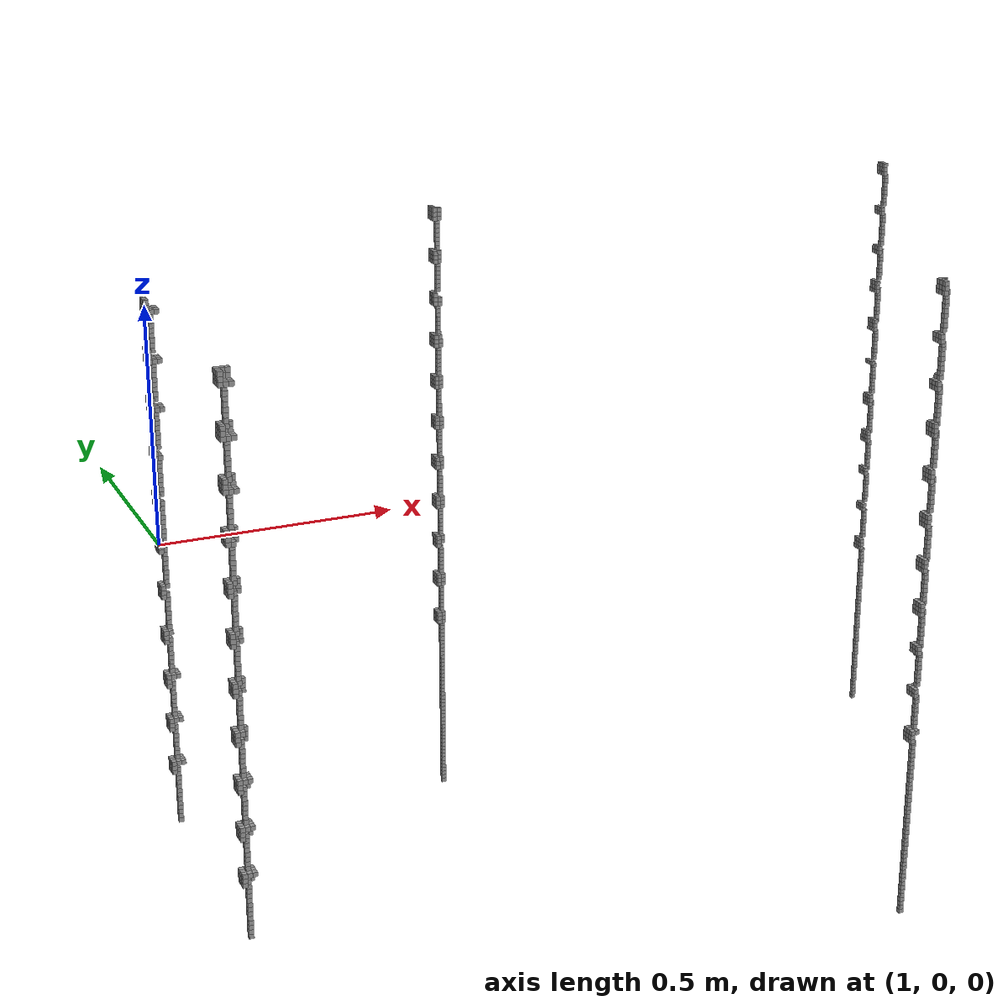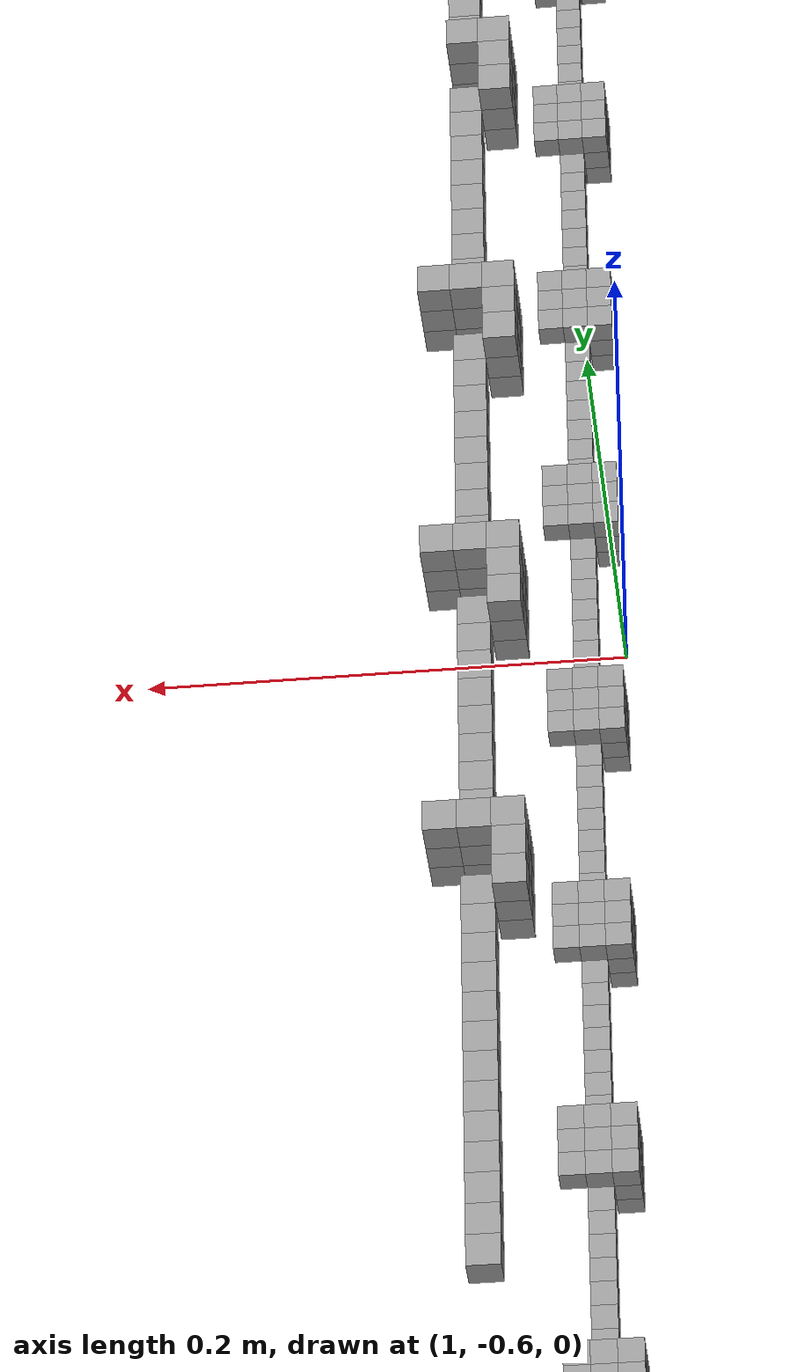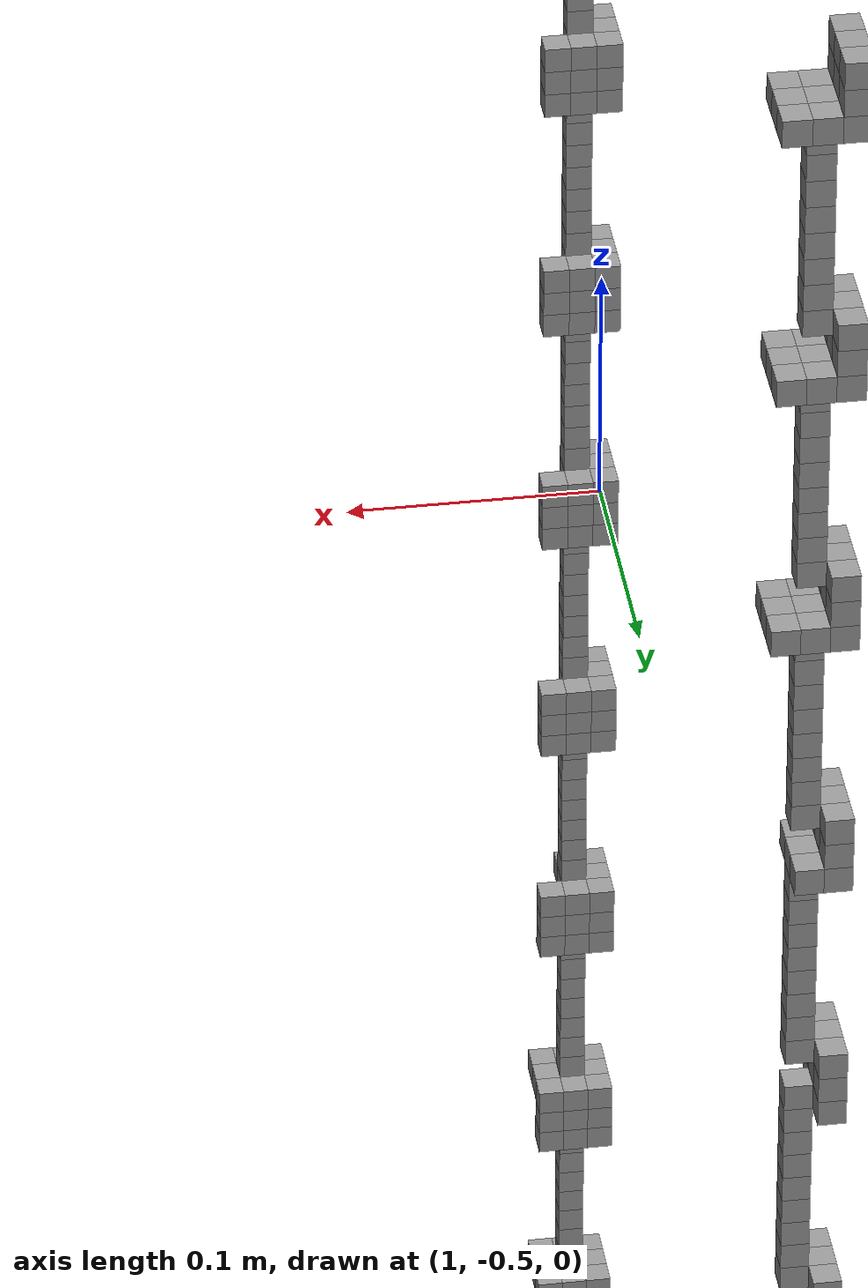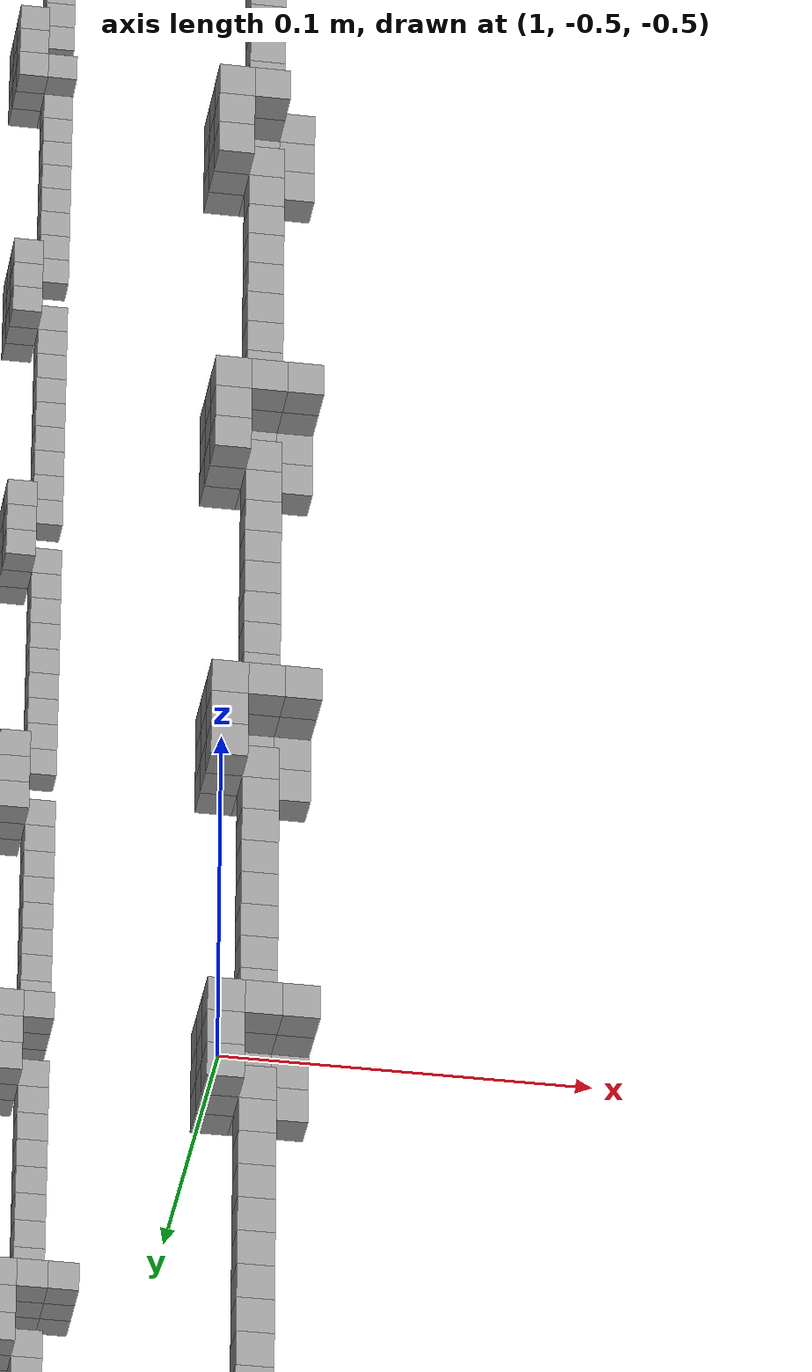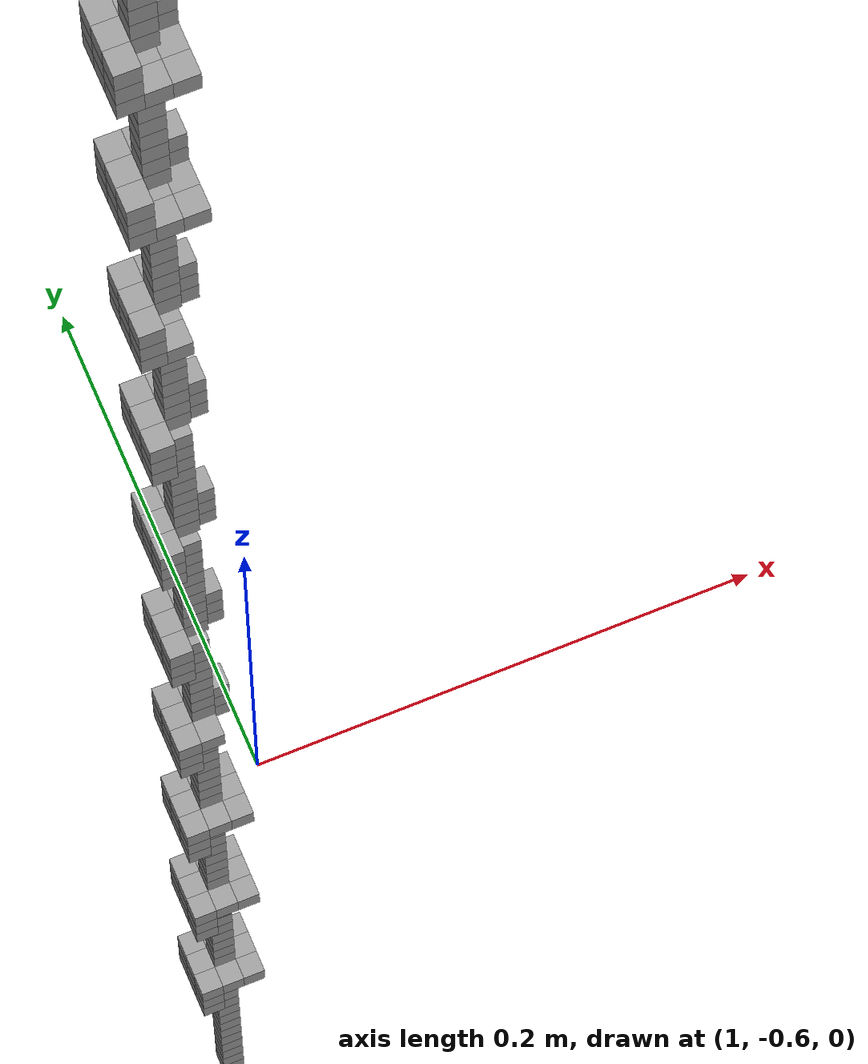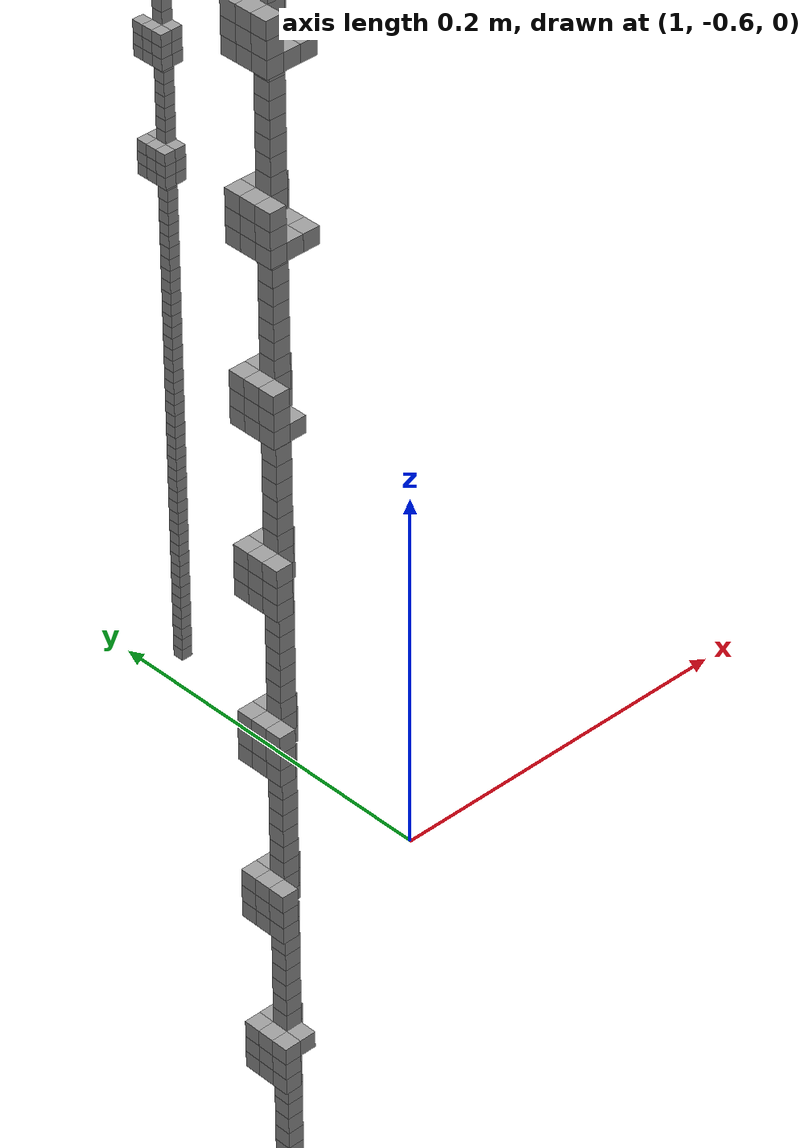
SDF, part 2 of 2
<geometry><box><size>0.01 0.01 0.01</size></box></geometry>
</collision>
<visual name="p2335v"><pose>1.81 0.50 -0.09 0 0 0</pose>
<geometry><box><size>0.01 0.01 0.01</size></box></geometry>
<material><script><uri>file://media/materials/scripts/gazebo.material</uri>
<name>Gazebo/Grey</name></script></material>
</visual>

<collision name="p2336c"><pose>3.01 0.50 -0.15 0 0 0</pose>
<geometry><box><size>0.01 0.01 0.01</size></box></geometry>
</collision>
<visual name="p2336v"><pose>3.01 0.50 -0.15 0 0 0</pose>
<geometry><box><size>0.01 0.01 0.01</size></box></geometry>
<material><script><uri>file://media/materials/scripts/gazebo.material</uri>
<name>Gazebo/Grey</name></script></material>
</visual>

<collision name="p2337c"><pose>1.01 0.00 -0.05 0 0 0</pose>
<geometry><box><size>0.01 0.01 0.01</size></box></geometry>
</collision>
<visual name="p2337v"><pose>1.01 0.00 -0.05 0 0 0</pose>
<geometry><box><size>0.01 0.01 0.01</size></box></geometry>
<material><script><uri>file://media/materials/scripts/gazebo.material</uri>
<name>Gazebo/Grey</name></script></material>
</visual>

<collision name="p2338c"><pose>1.01 -0.00 -0.05 0 0 0</pose>
<geometry><box><size>0.01 0.01 0.01</size></box></geometry>
</collision>
<visual name="p2338v"><pose>1.01 -0.00 -0.05 0 0 0</pose>
<geometry><box><size>0.01 0.01 0.01</size></box></geometry>
<material><script><uri>file://media/materials/scripts/gazebo.material</uri>
<name>Gazebo/Grey</name></script></material>
</visual>

<collision name="p2339c"><pose>2.51 -0.50 -0.12 0 0 0</pose>
<geometry><box><size>0.01 0.01 0.01</size></box></geometry>
</collision>
<visual name="p2339v"><pose>2.51 -0.50 -0.12 0 0 0</pose>
<geometry><box><size>0.01 0.01 0.01</size></box></geometry>
<material><script><uri>file://media/materials/scripts/gazebo.material</uri>
<name>Gazebo/Grey</name></script></material>
</visual>

<collision name="p2340c"><pose>1.01 -0.50 -0.05 0 0 0</pose>
<geometry><box><size>0.01 0.01 0.01</size></box></geometry>
</collision>
<visual name="p2340v"><pose>1.01 -0.50 -0.05 0 0 0</pose>
<geometry><box><size>0.01 0.01 0.01</size></box></geometry>
<material><script><uri>file://media/materials/scripts/gazebo.material</uri>
<name>Gazebo/Grey</name></script></material>
</visual>

<collision name="p2341c"><pose>1.01 -0.50 -0.05 0 0 0</pose>
<geometry><box><size>0.01 0.01 0.01</size></box></geometry>
</collision>
<visual name="p2341v"><pose>1.01 -0.50 -0.05 0 0 0</pose>
<geometry><box><size>0.01 0.01 0.01</size></box></geometry>
<material><script><uri>file://media/materials/scripts/gazebo.material</uri>
<name>Gazebo/Grey</name></script></material>
</visual>

<collision name="p2342c"><pose>1.01 -0.50 -0.05 0 0 0</pose>
<geometry><box><size>0.01 0.01 0.01</size></box></geometry>
</collision>
<visual name="p2342v"><pose>1.01 -0.50 -0.05 0 0 0</pose>
<geometry><box><size>0.01 0.01 0.01</size></box></geometry>
<material><script><uri>file://media/materials/scripts/gazebo.material</uri>
<name>Gazebo/Grey</name></script></material>
</visual>

<collision name="p2343c"><pose>1.80 0.51 -0.09 0 0 0</pose>
<geometry><box><size>0.01 0.01 0.01</size></box></geometry>
</collision>
<visual name="p2343v"><pose>1.80 0.51 -0.09 0 0 0</pose>
<geometry><box><size>0.01 0.01 0.01</size></box></geometry>
<material><script><uri>file://media/materials/scripts/gazebo.material</uri>
<name>Gazebo/Grey</name></script></material>
</visual>

<collision name="p2344c"><pose>1.80 0.50 -0.09 0 0 0</pose>
<geometry><box><size>0.01 0.01 0.01</size></box></geometry>
</collision>
<visual name="p2344v"><pose>1.80 0.50 -0.09 0 0 0</pose>
<geometry><box><size>0.01 0.01 0.01</size></box></geometry>
<material><script><uri>file://media/materials/scripts/gazebo.material</uri>
<name>Gazebo/Grey</name></script></material>
</visual>

<collision name="p2345c"><pose>1.80 0.50 -0.09 0 0 0</pose>
<geometry><box><size>0.01 0.01 0.01</size></box></geometry>
</collision>
<visual name="p2345v"><pose>1.80 0.50 -0.09 0 0 0</pose>
<geometry><box><size>0.01 0.01 0.01</size></box></geometry>
<material><script><uri>file://media/materials/scripts/gazebo.material</uri>
<name>Gazebo/Grey</name></script></material>
</visual>

<collision name="p2346c"><pose>1.80 0.49 -0.09 0 0 0</pose>
<geometry><box><size>0.01 0.01 0.01</size></box></geometry>
</collision>
<visual name="p2346v"><pose>1.80 0.49 -0.09 0 0 0</pose>
<geometry><box><size>0.01 0.01 0.01</size></box></geometry>
<material><script><uri>file://media/materials/scripts/gazebo.material</uri>
<name>Gazebo/Grey</name></script></material>
</visual>

<collision name="p2347c"><pose>1.81 0.49 -0.09 0 0 0</pose>
<geometry><box><size>0.01 0.01 0.01</size></box></geometry>
</collision>
<visual name="p2347v"><pose>1.81 0.49 -0.09 0 0 0</pose>
<geometry><box><size>0.01 0.01 0.01</size></box></geometry>
<material><script><uri>file://media/materials/scripts/gazebo.material</uri>
<name>Gazebo/Grey</name></script></material>
</visual>

<collision name="p2348c"><pose>3.01 0.50 -0.15 0 0 0</pose>
<geometry><box><size>0.01 0.01 0.01</size></box></geometry>
</collision>
<visual name="p2348v"><pose>3.01 0.50 -0.15 0 0 0</pose>
<geometry><box><size>0.01 0.01 0.01</size></box></geometry>
<material><script><uri>file://media/materials/scripts/gazebo.material</uri>
<name>Gazebo/Grey</name></script></material>
</visual>

<collision name="p2349c"><pose>1.01 0.00 -0.05 0 0 0</pose>
<geometry><box><size>0.01 0.01 0.01</size></box></geometry>
</collision>
<visual name="p2349v"><pose>1.01 0.00 -0.05 0 0 0</pose>
<geometry><box><size>0.01 0.01 0.01</size></box></geometry>
<material><script><uri>file://media/materials/scripts/gazebo.material</uri>
<name>Gazebo/Grey</name></script></material>
</visual>

<collision name="p2350c"><pose>1.01 -0.00 -0.05 0 0 0</pose>
<geometry><box><size>0.01 0.01 0.01</size></box></geometry>
</collision>
<visual name="p2350v"><pose>1.01 -0.00 -0.05 0 0 0</pose>
<geometry><box><size>0.01 0.01 0.01</size></box></geometry>
<material><script><uri>file://media/materials/scripts/gazebo.material</uri>
<name>Gazebo/Grey</name></script></material>
</visual>

<collision name="p2351c"><pose>2.51 -0.50 -0.13 0 0 0</pose>
<geometry><box><size>0.01 0.01 0.01</size></box></geometry>
</collision>
<visual name="p2351v"><pose>2.51 -0.50 -0.13 0 0 0</pose>
<geometry><box><size>0.01 0.01 0.01</size></box></geometry>
<material><script><uri>file://media/materials/scripts/gazebo.material</uri>
<name>Gazebo/Grey</name></script></material>
</visual>

<collision name="p2352c"><pose>1.01 -0.50 -0.05 0 0 0</pose>
<geometry><box><size>0.01 0.01 0.01</size></box></geometry>
</collision>
<visual name="p2352v"><pose>1.01 -0.50 -0.05 0 0 0</pose>
<geometry><box><size>0.01 0.01 0.01</size></box></geometry>
<material><script><uri>file://media/materials/scripts/gazebo.material</uri>
<name>Gazebo/Grey</name></script></material>
</visual>

<collision name="p2353c"><pose>1.01 -0.50 -0.05 0 0 0</pose>
<geometry><box><size>0.01 0.01 0.01</size></box></geometry>
</collision>
<visual name="p2353v"><pose>1.01 -0.50 -0.05 0 0 0</pose>
<geometry><box><size>0.01 0.01 0.01</size></box></geometry>
<material><script><uri>file://media/materials/scripts/gazebo.material</uri>
<name>Gazebo/Grey</name></script></material>
</visual>

<collision name="p2354c"><pose>1.01 -0.50 -0.05 0 0 0</pose>
<geometry><box><size>0.01 0.01 0.01</size></box></geometry>
</collision>
<visual name="p2354v"><pose>1.01 -0.50 -0.05 0 0 0</pose>
<geometry><box><size>0.01 0.01 0.01</size></box></geometry>
<material><script><uri>file://media/materials/scripts/gazebo.material</uri>
<name>Gazebo/Grey</name></script></material>
</visual>

<collision name="p2355c"><pose>1.80 0.51 -0.10 0 0 0</pose>
<geometry><box><size>0.01 0.01 0.01</size></box></geometry>
</collision>
<visual name="p2355v"><pose>1.80 0.51 -0.10 0 0 0</pose>
<geometry><box><size>0.01 0.01 0.01</size></box></geometry>
<material><script><uri>file://media/materials/scripts/gazebo.material</uri>
<name>Gazebo/Grey</name></script></material>
</visual>

<collision name="p2356c"><pose>1.80 0.50 -0.10 0 0 0</pose>
<geometry><box><size>0.01 0.01 0.01</size></box></geometry>
</collision>
<visual name="p2356v"><pose>1.80 0.50 -0.10 0 0 0</pose>
<geometry><box><size>0.01 0.01 0.01</size></box></geometry>
<material><script><uri>file://media/materials/scripts/gazebo.material</uri>
<name>Gazebo/Grey</name></script></material>
</visual>

<collision name="p2357c"><pose>1.80 0.50 -0.10 0 0 0</pose>
<geometry><box><size>0.01 0.01 0.01</size></box></geometry>
</collision>
<visual name="p2357v"><pose>1.80 0.50 -0.10 0 0 0</pose>
<geometry><box><size>0.01 0.01 0.01</size></box></geometry>
<material><script><uri>file://media/materials/scripts/gazebo.material</uri>
<name>Gazebo/Grey</name></script></material>
</visual>

<collision name="p2358c"><pose>1.80 0.49 -0.10 0 0 0</pose>
<geometry><box><size>0.01 0.01 0.01</size></box></geometry>
</collision>
<visual name="p2358v"><pose>1.80 0.49 -0.10 0 0 0</pose>
<geometry><box><size>0.01 0.01 0.01</size></box></geometry>
<material><script><uri>file://media/materials/scripts/gazebo.material</uri>
<name>Gazebo/Grey</name></script></material>
</visual>

<collision name="p2359c"><pose>1.81 0.49 -0.10 0 0 0</pose>
<geometry><box><size>0.01 0.01 0.01</size></box></geometry>
</collision>
<visual name="p2359v"><pose>1.81 0.49 -0.10 0 0 0</pose>
<geometry><box><size>0.01 0.01 0.01</size></box></geometry>
<material><script><uri>file://media/materials/scripts/gazebo.material</uri>
<name>Gazebo/Grey</name></script></material>
</visual>

<collision name="p2360c"><pose>3.01 0.50 -0.16 0 0 0</pose>
<geometry><box><size>0.01 0.01 0.01</size></box></geometry>
</collision>
<visual name="p2360v"><pose>3.01 0.50 -0.16 0 0 0</pose>
<geometry><box><size>0.01 0.01 0.01</size></box></geometry>
<material><script><uri>file://media/materials/scripts/gazebo.material</uri>
<name>Gazebo/Grey</name></script></material>
</visual>

<collision name="p2361c"><pose>1.01 0.00 -0.05 0 0 0</pose>
<geometry><box><size>0.01 0.01 0.01</size></box></geometry>
</collision>
<visual name="p2361v"><pose>1.01 0.00 -0.05 0 0 0</pose>
<geometry><box><size>0.01 0.01 0.01</size></box></geometry>
<material><script><uri>file://media/materials/scripts/gazebo.material</uri>
<name>Gazebo/Grey</name></script></material>
</visual>

<collision name="p2362c"><pose>1.01 -0.00 -0.05 0 0 0</pose>
<geometry><box><size>0.01 0.01 0.01</size></box></geometry>
</collision>
<visual name="p2362v"><pose>1.01 -0.00 -0.05 0 0 0</pose>
<geometry><box><size>0.01 0.01 0.01</size></box></geometry>
<material><script><uri>file://media/materials/scripts/gazebo.material</uri>
<name>Gazebo/Grey</name></script></material>
</visual>

<collision name="p2363c"><pose>2.51 -0.50 -0.13 0 0 0</pose>
<geometry><box><size>0.01 0.01 0.01</size></box></geometry>
</collision>
<visual name="p2363v"><pose>2.51 -0.50 -0.13 0 0 0</pose>
<geometry><box><size>0.01 0.01 0.01</size></box></geometry>
<material><script><uri>file://media/materials/scripts/gazebo.material</uri>
<name>Gazebo/Grey</name></script></material>
</visual>

<collision name="p2364c"><pose>1.01 -0.50 -0.05 0 0 0</pose>
<geometry><box><size>0.01 0.01 0.01</size></box></geometry>
</collision>
<visual name="p2364v"><pose>1.01 -0.50 -0.05 0 0 0</pose>
<geometry><box><size>0.01 0.01 0.01</size></box></geometry>
<material><script><uri>file://media/materials/scripts/gazebo.material</uri>
<name>Gazebo/Grey</name></script></material>
</visual>

<collision name="p2365c"><pose>1.01 -0.50 -0.05 0 0 0</pose>
<geometry><box><size>0.01 0.01 0.01</size></box></geometry>
</collision>
<visual name="p2365v"><pose>1.01 -0.50 -0.05 0 0 0</pose>
<geometry><box><size>0.01 0.01 0.01</size></box></geometry>
<material><script><uri>file://media/materials/scripts/gazebo.material</uri>
<name>Gazebo/Grey</name></script></material>
</visual>

<collision name="p2366c"><pose>1.01 -0.50 -0.05 0 0 0</pose>
<geometry><box><size>0.01 0.01 0.01</size></box></geometry>
</collision>
<visual name="p2366v"><pose>1.01 -0.50 -0.05 0 0 0</pose>
<geometry><box><size>0.01 0.01 0.01</size></box></geometry>
<material><script><uri>file://media/materials/scripts/gazebo.material</uri>
<name>Gazebo/Grey</name></script></material>
</visual>

<collision name="p2367c"><pose>1.80 0.51 -0.10 0 0 0</pose>
<geometry><box><size>0.01 0.01 0.01</size></box></geometry>
</collision>
<visual name="p2367v"><pose>1.80 0.51 -0.10 0 0 0</pose>
<geometry><box><size>0.01 0.01 0.01</size></box></geometry>
<material><script><uri>file://media/materials/scripts/gazebo.material</uri>
<name>Gazebo/Grey</name></script></material>
</visual>

<collision name="p2368c"><pose>1.80 0.50 -0.10 0 0 0</pose>
<geometry><box><size>0.01 0.01 0.01</size></box></geometry>
</collision>
<visual name="p2368v"><pose>1.80 0.50 -0.10 0 0 0</pose>
<geometry><box><size>0.01 0.01 0.01</size></box></geometry>
<material><script><uri>file://media/materials/scripts/gazebo.material</uri>
<name>Gazebo/Grey</name></script></material>
</visual>

<collision name="p2369c"><pose>1.80 0.50 -0.10 0 0 0</pose>
<geometry><box><size>0.01 0.01 0.01</size></box></geometry>
</collision>
<visual name="p2369v"><pose>1.80 0.50 -0.10 0 0 0</pose>
<geometry><box><size>0.01 0.01 0.01</size></box></geometry>
<material><script><uri>file://media/materials/scripts/gazebo.material</uri>
<name>Gazebo/Grey</name></script></material>
</visual>

<collision name="p2370c"><pose>1.80 0.49 -0.10 0 0 0</pose>
<geometry><box><size>0.01 0.01 0.01</size></box></geometry>
</collision>
<visual name="p2370v"><pose>1.80 0.49 -0.10 0 0 0</pose>
<geometry><box><size>0.01 0.01 0.01</size></box></geometry>
<material><script><uri>file://media/materials/scripts/gazebo.material</uri>
<name>Gazebo/Grey</name></script></material>
</visual>

<collision name="p2371c"><pose>1.81 0.49 -0.10 0 0 0</pose>
<geometry><box><size>0.01 0.01 0.01</size></box></geometry>
</collision>
<visual name="p2371v"><pose>1.81 0.49 -0.10 0 0 0</pose>
<geometry><box><size>0.01 0.01 0.01</size></box></geometry>
<material><script><uri>file://media/materials/scripts/gazebo.material</uri>
<name>Gazebo/Grey</name></script></material>
</visual>

<collision name="p2372c"><pose>3.01 0.50 -0.17 0 0 0</pose>
<geometry><box><size>0.01 0.01 0.01</size></box></geometry>
</collision>
<visual name="p2372v"><pose>3.01 0.50 -0.17 0 0 0</pose>
<geometry><box><size>0.01 0.01 0.01</size></box></geometry>
<material><script><uri>file://media/materials/scripts/gazebo.material</uri>
<name>Gazebo/Grey</name></script></material>
</visual>

<collision name="p2373c"><pose>1.01 0.00 -0.06 0 0 0</pose>
<geometry><box><size>0.01 0.01 0.01</size></box></geometry>
</collision>
<visual name="p2373v"><pose>1.01 0.00 -0.06 0 0 0</pose>
<geometry><box><size>0.01 0.01 0.01</size></box></geometry>
<material><script><uri>file://media/materials/scripts/gazebo.material</uri>
<name>Gazebo/Grey</name></script></material>
</visual>

<collision name="p2374c"><pose>1.01 -0.00 -0.06 0 0 0</pose>
<geometry><box><size>0.01 0.01 0.01</size></box></geometry>
</collision>
<visual name="p2374v"><pose>1.01 -0.00 -0.06 0 0 0</pose>
<geometry><box><size>0.01 0.01 0.01</size></box></geometry>
<material><script><uri>file://media/materials/scripts/gazebo.material</uri>
<name>Gazebo/Grey</name></script></material>
</visual>

<collision name="p2375c"><pose>2.51 -0.50 -0.14 0 0 0</pose>
<geometry><box><size>0.01 0.01 0.01</size></box></geometry>
</collision>
<visual name="p2375v"><pose>2.51 -0.50 -0.14 0 0 0</pose>
<geometry><box><size>0.01 0.01 0.01</size></box></geometry>
<material><script><uri>file://media/materials/scripts/gazebo.material</uri>
<name>Gazebo/Grey</name></script></material>
</visual>

<collision name="p2376c"><pose>1.01 -0.50 -0.06 0 0 0</pose>
<geometry><box><size>0.01 0.01 0.01</size></box></geometry>
</collision>
<visual name="p2376v"><pose>1.01 -0.50 -0.06 0 0 0</pose>
<geometry><box><size>0.01 0.01 0.01</size></box></geometry>
<material><script><uri>file://media/materials/scripts/gazebo.material</uri>
<name>Gazebo/Grey</name></script></material>
</visual>

<collision name="p2377c"><pose>1.01 -0.50 -0.06 0 0 0</pose>
<geometry><box><size>0.01 0.01 0.01</size></box></geometry>
</collision>
<visual name="p2377v"><pose>1.01 -0.50 -0.06 0 0 0</pose>
<geometry><box><size>0.01 0.01 0.01</size></box></geometry>
<material><script><uri>file://media/materials/scripts/gazebo.material</uri>
<name>Gazebo/Grey</name></script></material>
</visual>

<collision name="p2378c"><pose>1.01 -0.50 -0.06 0 0 0</pose>
<geometry><box><size>0.01 0.01 0.01</size></box></geometry>
</collision>
<visual name="p2378v"><pose>1.01 -0.50 -0.06 0 0 0</pose>
<geometry><box><size>0.01 0.01 0.01</size></box></geometry>
<material><script><uri>file://media/materials/scripts/gazebo.material</uri>
<name>Gazebo/Grey</name></script></material>
</visual>

<collision name="p2379c"><pose>1.80 0.51 -0.11 0 0 0</pose>
<geometry><box><size>0.01 0.01 0.01</size></box></geometry>
</collision>
<visual name="p2379v"><pose>1.80 0.51 -0.11 0 0 0</pose>
<geometry><box><size>0.01 0.01 0.01</size></box></geometry>
<material><script><uri>file://media/materials/scripts/gazebo.material</uri>
<name>Gazebo/Grey</name></script></material>
</visual>

<collision name="p2380c"><pose>1.80 0.50 -0.11 0 0 0</pose>
<geometry><box><size>0.01 0.01 0.01</size></box></geometry>
</collision>
<visual name="p2380v"><pose>1.80 0.50 -0.11 0 0 0</pose>
<geometry><box><size>0.01 0.01 0.01</size></box></geometry>
<material><script><uri>file://media/materials/scripts/gazebo.material</uri>
<name>Gazebo/Grey</name></script></material>
</visual>

<collision name="p2381c"><pose>1.80 0.50 -0.11 0 0 0</pose>
<geometry><box><size>0.01 0.01 0.01</size></box></geometry>
</collision>
<visual name="p2381v"><pose>1.80 0.50 -0.11 0 0 0</pose>
<geometry><box><size>0.01 0.01 0.01</size></box></geometry>
<material><script><uri>file://media/materials/scripts/gazebo.material</uri>
<name>Gazebo/Grey</name></script></material>
</visual>

<collision name="p2382c"><pose>1.80 0.49 -0.11 0 0 0</pose>
<geometry><box><size>0.01 0.01 0.01</size></box></geometry>
</collision>
<visual name="p2382v"><pose>1.80 0.49 -0.11 0 0 0</pose>
<geometry><box><size>0.01 0.01 0.01</size></box></geometry>
<material><script><uri>file://media/materials/scripts/gazebo.material</uri>
<name>Gazebo/Grey</name></script></material>
</visual>

<collision name="p2383c"><pose>1.81 0.49 -0.11 0 0 0</pose>
<geometry><box><size>0.01 0.01 0.01</size></box></geometry>
</collision>
<visual name="p2383v"><pose>1.81 0.49 -0.11 0 0 0</pose>
<geometry><box><size>0.01 0.01 0.01</size></box></geometry>
<material><script><uri>file://media/materials/scripts/gazebo.material</uri>
<name>Gazebo/Grey</name></script></material>
</visual>

<collision name="p2384c"><pose>3.01 0.50 -0.18 0 0 0</pose>
<geometry><box><size>0.01 0.01 0.01</size></box></geometry>
</collision>
<visual name="p2384v"><pose>3.01 0.50 -0.18 0 0 0</pose>
<geometry><box><size>0.01 0.01 0.01</size></box></geometry>
<material><script><uri>file://media/materials/scripts/gazebo.material</uri>
<name>Gazebo/Grey</name></script></material>
</visual>

<collision name="p2385c"><pose>1.01 0.00 -0.06 0 0 0</pose>
<geometry><box><size>0.01 0.01 0.01</size></box></geometry>
</collision>
<visual name="p2385v"><pose>1.01 0.00 -0.06 0 0 0</pose>
<geometry><box><size>0.01 0.01 0.01</size></box></geometry>
<material><script><uri>file://media/materials/scripts/gazebo.material</uri>
<name>Gazebo/Grey</name></script></material>
</visual>

<collision name="p2386c"><pose>1.01 -0.00 -0.06 0 0 0</pose>
<geometry><box><size>0.01 0.01 0.01</size></box></geometry>
</collision>
<visual name="p2386v"><pose>1.01 -0.00 -0.06 0 0 0</pose>
<geometry><box><size>0.01 0.01 0.01</size></box></geometry>
<material><script><uri>file://media/materials/scripts/gazebo.material</uri>
<name>Gazebo/Grey</name></script></material>
</visual>

<collision name="p2387c"><pose>2.51 -0.50 -0.15 0 0 0</pose>
<geometry><box><size>0.01 0.01 0.01</size></box></geometry>
</collision>
<visual name="p2387v"><pose>2.51 -0.50 -0.15 0 0 0</pose>
<geometry><box><size>0.01 0.01 0.01</size></box></geometry>
<material><script><uri>file://media/materials/scripts/gazebo.material</uri>
<name>Gazebo/Grey</name></script></material>
</visual>

<collision name="p2388c"><pose>1.01 -0.50 -0.06 0 0 0</pose>
<geometry><box><size>0.01 0.01 0.01</size></box></geometry>
</collision>
<visual name="p2388v"><pose>1.01 -0.50 -0.06 0 0 0</pose>
<geometry><box><size>0.01 0.01 0.01</size></box></geometry>
<material><script><uri>file://media/materials/scripts/gazebo.material</uri>
<name>Gazebo/Grey</name></script></material>
</visual>

<collision name="p2389c"><pose>1.01 -0.50 -0.06 0 0 0</pose>
<geometry><box><size>0.01 0.01 0.01</size></box></geometry>
</collision>
<visual name="p2389v"><pose>1.01 -0.50 -0.06 0 0 0</pose>
<geometry><box><size>0.01 0.01 0.01</size></box></geometry>
<material><script><uri>file://media/materials/scripts/gazebo.material</uri>
<name>Gazebo/Grey</name></script></material>
</visual>

<collision name="p2390c"><pose>1.01 -0.50 -0.06 0 0 0</pose>
<geometry><box><size>0.01 0.01 0.01</size></box></geometry>
</collision>
<visual name="p2390v"><pose>1.01 -0.50 -0.06 0 0 0</pose>
<geometry><box><size>0.01 0.01 0.01</size></box></geometry>
<material><script><uri>file://media/materials/scripts/gazebo.material</uri>
<name>Gazebo/Grey</name></script></material>
</visual>

<collision name="p2391c"><pose>1.81 0.50 -0.11 0 0 0</pose>
<geometry><box><size>0.01 0.01 0.01</size></box></geometry>
</collision>
<visual name="p2391v"><pose>1.81 0.50 -0.11 0 0 0</pose>
<geometry><box><size>0.01 0.01 0.01</size></box></geometry>
<material><script><uri>file://media/materials/scripts/gazebo.material</uri>
<name>Gazebo/Grey</name></script></material>
</visual>

<collision name="p2392c"><pose>3.01 0.50 -0.19 0 0 0</pose>
<geometry><box><size>0.01 0.01 0.01</size></box></geometry>
</collision>
<visual name="p2392v"><pose>3.01 0.50 -0.19 0 0 0</pose>
<geometry><box><size>0.01 0.01 0.01</size></box></geometry>
<material><script><uri>file://media/materials/scripts/gazebo.material</uri>
<name>Gazebo/Grey</name></script></material>
</visual>

<collision name="p2393c"><pose>1.01 0.00 -0.06 0 0 0</pose>
<geometry><box><size>0.01 0.01 0.01</size></box></geometry>
</collision>
<visual name="p2393v"><pose>1.01 0.00 -0.06 0 0 0</pose>
<geometry><box><size>0.01 0.01 0.01</size></box></geometry>
<material><script><uri>file://media/materials/scripts/gazebo.material</uri>
<name>Gazebo/Grey</name></script></material>
</visual>

<collision name="p2394c"><pose>1.01 -0.00 -0.06 0 0 0</pose>
<geometry><box><size>0.01 0.01 0.01</size></box></geometry>
</collision>
<visual name="p2394v"><pose>1.01 -0.00 -0.06 0 0 0</pose>
<geometry><box><size>0.01 0.01 0.01</size></box></geometry>
<material><script><uri>file://media/materials/scripts/gazebo.material</uri>
<name>Gazebo/Grey</name></script></material>
</visual>

<collision name="p2395c"><pose>2.51 -0.50 -0.15 0 0 0</pose>
<geometry><box><size>0.01 0.01 0.01</size></box></geometry>
</collision>
<visual name="p2395v"><pose>2.51 -0.50 -0.15 0 0 0</pose>
<geometry><box><size>0.01 0.01 0.01</size></box></geometry>
<material><script><uri>file://media/materials/scripts/gazebo.material</uri>
<name>Gazebo/Grey</name></script></material>
</visual>

<collision name="p2396c"><pose>1.01 -0.50 -0.06 0 0 0</pose>
<geometry><box><size>0.01 0.01 0.01</size></box></geometry>
</collision>
<visual name="p2396v"><pose>1.01 -0.50 -0.06 0 0 0</pose>
<geometry><box><size>0.01 0.01 0.01</size></box></geometry>
<material><script><uri>file://media/materials/scripts/gazebo.material</uri>
<name>Gazebo/Grey</name></script></material>
</visual>

<collision name="p2397c"><pose>1.01 -0.50 -0.06 0 0 0</pose>
<geometry><box><size>0.01 0.01 0.01</size></box></geometry>
</collision>
<visual name="p2397v"><pose>1.01 -0.50 -0.06 0 0 0</pose>
<geometry><box><size>0.01 0.01 0.01</size></box></geometry>
<material><script><uri>file://media/materials/scripts/gazebo.material</uri>
<name>Gazebo/Grey</name></script></material>
</visual>

<collision name="p2398c"><pose>1.01 -0.50 -0.06 0 0 0</pose>
<geometry><box><size>0.01 0.01 0.01</size></box></geometry>
</collision>
<visual name="p2398v"><pose>1.01 -0.50 -0.06 0 0 0</pose>
<geometry><box><size>0.01 0.01 0.01</size></box></geometry>
<material><script><uri>file://media/materials/scripts/gazebo.material</uri>
<name>Gazebo/Grey</name></script></material>
</visual>

<collision name="p2399c"><pose>1.81 0.50 -0.12 0 0 0</pose>
<geometry><box><size>0.01 0.01 0.01</size></box></geometry>
</collision>
<visual name="p2399v"><pose>1.81 0.50 -0.12 0 0 0</pose>
<geometry><box><size>0.01 0.01 0.01</size></box></geometry>
<material><script><uri>file://media/materials/scripts/gazebo.material</uri>
<name>Gazebo/Grey</name></script></material>
</visual>

<collision name="p2400c"><pose>3.00 0.51 -0.19 0 0 0</pose>
<geometry><box><size>0.01 0.01 0.01</size></box></geometry>
</collision>
<visual name="p2400v"><pose>3.00 0.51 -0.19 0 0 0</pose>
<geometry><box><size>0.01 0.01 0.01</size></box></geometry>
<material><script><uri>file://media/materials/scripts/gazebo.material</uri>
<name>Gazebo/Grey</name></script></material>
</visual>

<collision name="p2401c"><pose>3.00 0.50 -0.19 0 0 0</pose>
<geometry><box><size>0.01 0.01 0.01</size></box></geometry>
</collision>
<visual name="p2401v"><pose>3.00 0.50 -0.19 0 0 0</pose>
<geometry><box><size>0.01 0.01 0.01</size></box></geometry>
<material><script><uri>file://media/materials/scripts/gazebo.material</uri>
<name>Gazebo/Grey</name></script></material>
</visual>

<collision name="p2402c"><pose>3.00 0.49 -0.19 0 0 0</pose>
<geometry><box><size>0.01 0.01 0.01</size></box></geometry>
</collision>
<visual name="p2402v"><pose>3.00 0.49 -0.19 0 0 0</pose>
<geometry><box><size>0.01 0.01 0.01</size></box></geometry>
<material><script><uri>file://media/materials/scripts/gazebo.material</uri>
<name>Gazebo/Grey</name></script></material>
</visual>

<collision name="p2403c"><pose>1.01 0.00 -0.06 0 0 0</pose>
<geometry><box><size>0.01 0.01 0.01</size></box></geometry>
</collision>
<visual name="p2403v"><pose>1.01 0.00 -0.06 0 0 0</pose>
<geometry><box><size>0.01 0.01 0.01</size></box></geometry>
<material><script><uri>file://media/materials/scripts/gazebo.material</uri>
<name>Gazebo/Grey</name></script></material>
</visual>

<collision name="p2404c"><pose>1.01 -0.00 -0.06 0 0 0</pose>
<geometry><box><size>0.01 0.01 0.01</size></box></geometry>
</collision>
<visual name="p2404v"><pose>1.01 -0.00 -0.06 0 0 0</pose>
<geometry><box><size>0.01 0.01 0.01</size></box></geometry>
<material><script><uri>file://media/materials/scripts/gazebo.material</uri>
<name>Gazebo/Grey</name></script></material>
</visual>

<collision name="p2405c"><pose>2.51 -0.50 -0.16 0 0 0</pose>
<geometry><box><size>0.01 0.01 0.01</size></box></geometry>
</collision>
<visual name="p2405v"><pose>2.51 -0.50 -0.16 0 0 0</pose>
<geometry><box><size>0.01 0.01 0.01</size></box></geometry>
<material><script><uri>file://media/materials/scripts/gazebo.material</uri>
<name>Gazebo/Grey</name></script></material>
</visual>

<collision name="p2406c"><pose>1.01 -0.50 -0.06 0 0 0</pose>
<geometry><box><size>0.01 0.01 0.01</size></box></geometry>
</collision>
<visual name="p2406v"><pose>1.01 -0.50 -0.06 0 0 0</pose>
<geometry><box><size>0.01 0.01 0.01</size></box></geometry>
<material><script><uri>file://media/materials/scripts/gazebo.material</uri>
<name>Gazebo/Grey</name></script></material>
</visual>

<collision name="p2407c"><pose>1.01 -0.50 -0.06 0 0 0</pose>
<geometry><box><size>0.01 0.01 0.01</size></box></geometry>
</collision>
<visual name="p2407v"><pose>1.01 -0.50 -0.06 0 0 0</pose>
<geometry><box><size>0.01 0.01 0.01</size></box></geometry>
<material><script><uri>file://media/materials/scripts/gazebo.material</uri>
<name>Gazebo/Grey</name></script></material>
</visual>

<collision name="p2408c"><pose>1.01 -0.50 -0.06 0 0 0</pose>
<geometry><box><size>0.01 0.01 0.01</size></box></geometry>
</collision>
<visual name="p2408v"><pose>1.01 -0.50 -0.06 0 0 0</pose>
<geometry><box><size>0.01 0.01 0.01</size></box></geometry>
<material><script><uri>file://media/materials/scripts/gazebo.material</uri>
<name>Gazebo/Grey</name></script></material>
</visual>

<collision name="p2409c"><pose>1.81 0.50 -0.12 0 0 0</pose>
<geometry><box><size>0.01 0.01 0.01</size></box></geometry>
</collision>
<visual name="p2409v"><pose>1.81 0.50 -0.12 0 0 0</pose>
<geometry><box><size>0.01 0.01 0.01</size></box></geometry>
<material><script><uri>file://media/materials/scripts/gazebo.material</uri>
<name>Gazebo/Grey</name></script></material>
</visual>

<collision name="p2410c"><pose>3.00 0.51 -0.20 0 0 0</pose>
<geometry><box><size>0.01 0.01 0.01</size></box></geometry>
</collision>
<visual name="p2410v"><pose>3.00 0.51 -0.20 0 0 0</pose>
<geometry><box><size>0.01 0.01 0.01</size></box></geometry>
<material><script><uri>file://media/materials/scripts/gazebo.material</uri>
<name>Gazebo/Grey</name></script></material>
</visual>

<collision name="p2411c"><pose>3.00 0.50 -0.20 0 0 0</pose>
<geometry><box><size>0.01 0.01 0.01</size></box></geometry>
</collision>
<visual name="p2411v"><pose>3.00 0.50 -0.20 0 0 0</pose>
<geometry><box><size>0.01 0.01 0.01</size></box></geometry>
<material><script><uri>file://media/materials/scripts/gazebo.material</uri>
<name>Gazebo/Grey</name></script></material>
</visual>

<collision name="p2412c"><pose>3.00 0.49 -0.20 0 0 0</pose>
<geometry><box><size>0.01 0.01 0.01</size></box></geometry>
</collision>
<visual name="p2412v"><pose>3.00 0.49 -0.20 0 0 0</pose>
<geometry><box><size>0.01 0.01 0.01</size></box></geometry>
<material><script><uri>file://media/materials/scripts/gazebo.material</uri>
<name>Gazebo/Grey</name></script></material>
</visual>

<collision name="p2413c"><pose>1.01 0.00 -0.07 0 0 0</pose>
<geometry><box><size>0.01 0.01 0.01</size></box></geometry>
</collision>
<visual name="p2413v"><pose>1.01 0.00 -0.07 0 0 0</pose>
<geometry><box><size>0.01 0.01 0.01</size></box></geometry>
<material><script><uri>file://media/materials/scripts/gazebo.material</uri>
<name>Gazebo/Grey</name></script></material>
</visual>

<collision name="p2414c"><pose>1.01 -0.00 -0.07 0 0 0</pose>
<geometry><box><size>0.01 0.01 0.01</size></box></geometry>
</collision>
<visual name="p2414v"><pose>1.01 -0.00 -0.07 0 0 0</pose>
<geometry><box><size>0.01 0.01 0.01</size></box></geometry>
<material><script><uri>file://media/materials/scripts/gazebo.material</uri>
<name>Gazebo/Grey</name></script></material>
</visual>

<collision name="p2415c"><pose>2.51 -0.50 -0.17 0 0 0</pose>
<geometry><box><size>0.01 0.01 0.01</size></box></geometry>
</collision>
<visual name="p2415v"><pose>2.51 -0.50 -0.17 0 0 0</pose>
<geometry><box><size>0.01 0.01 0.01</size></box></geometry>
<material><script><uri>file://media/materials/scripts/gazebo.material</uri>
<name>Gazebo/Grey</name></script></material>
</visual>

<collision name="p2416c"><pose>1.01 -0.50 -0.07 0 0 0</pose>
<geometry><box><size>0.01 0.01 0.01</size></box></geometry>
</collision>
<visual name="p2416v"><pose>1.01 -0.50 -0.07 0 0 0</pose>
<geometry><box><size>0.01 0.01 0.01</size></box></geometry>
<material><script><uri>file://media/materials/scripts/gazebo.material</uri>
<name>Gazebo/Grey</name></script></material>
</visual>

<collision name="p2417c"><pose>1.01 -0.50 -0.07 0 0 0</pose>
<geometry><box><size>0.01 0.01 0.01</size></box></geometry>
</collision>
<visual name="p2417v"><pose>1.01 -0.50 -0.07 0 0 0</pose>
<geometry><box><size>0.01 0.01 0.01</size></box></geometry>
<material><script><uri>file://media/materials/scripts/gazebo.material</uri>
<name>Gazebo/Grey</name></script></material>
</visual>

<collision name="p2418c"><pose>1.01 -0.50 -0.07 0 0 0</pose>
<geometry><box><size>0.01 0.01 0.01</size></box></geometry>
</collision>
<visual name="p2418v"><pose>1.01 -0.50 -0.07 0 0 0</pose>
<geometry><box><size>0.01 0.01 0.01</size></box></geometry>
<material><script><uri>file://media/materials/scripts/gazebo.material</uri>
<name>Gazebo/Grey</name></script></material>
</visual>

<collision name="p2419c"><pose>1.81 0.50 -0.13 0 0 0</pose>
<geometry><box><size>0.01 0.01 0.01</size></box></geometry>
</collision>
<visual name="p2419v"><pose>1.81 0.50 -0.13 0 0 0</pose>
<geometry><box><size>0.01 0.01 0.01</size></box></geometry>
<material><script><uri>file://media/materials/scripts/gazebo.material</uri>
<name>Gazebo/Grey</name></script></material>
</visual>

<collision name="p2420c"><pose>3.00 0.51 -0.21 0 0 0</pose>
<geometry><box><size>0.01 0.01 0.01</size></box></geometry>
</collision>
<visual name="p2420v"><pose>3.00 0.51 -0.21 0 0 0</pose>
<geometry><box><size>0.01 0.01 0.01</size></box></geometry>
<material><script><uri>file://media/materials/scripts/gazebo.material</uri>
<name>Gazebo/Grey</name></script></material>
</visual>

<collision name="p2421c"><pose>3.00 0.50 -0.21 0 0 0</pose>
<geometry><box><size>0.01 0.01 0.01</size></box></geometry>
</collision>
<visual name="p2421v"><pose>3.00 0.50 -0.21 0 0 0</pose>
<geometry><box><size>0.01 0.01 0.01</size></box></geometry>
<material><script><uri>file://media/materials/scripts/gazebo.material</uri>
<name>Gazebo/Grey</name></script></material>
</visual>

<collision name="p2422c"><pose>3.00 0.49 -0.21 0 0 0</pose>
<geometry><box><size>0.01 0.01 0.01</size></box></geometry>
</collision>
<visual name="p2422v"><pose>3.00 0.49 -0.21 0 0 0</pose>
<geometry><box><size>0.01 0.01 0.01</size></box></geometry>
<material><script><uri>file://media/materials/scripts/gazebo.material</uri>
<name>Gazebo/Grey</name></script></material>
</visual>

<collision name="p2423c"><pose>1.01 0.00 -0.07 0 0 0</pose>
<geometry><box><size>0.01 0.01 0.01</size></box></geometry>
</collision>
<visual name="p2423v"><pose>1.01 0.00 -0.07 0 0 0</pose>
<geometry><box><size>0.01 0.01 0.01</size></box></geometry>
<material><script><uri>file://media/materials/scripts/gazebo.material</uri>
<name>Gazebo/Grey</name></script></material>
</visual>

<collision name="p2424c"><pose>1.01 -0.00 -0.07 0 0 0</pose>
<geometry><box><size>0.01 0.01 0.01</size></box></geometry>
</collision>
<visual name="p2424v"><pose>1.01 -0.00 -0.07 0 0 0</pose>
<geometry><box><size>0.01 0.01 0.01</size></box></geometry>
<material><script><uri>file://media/materials/scripts/gazebo.material</uri>
<name>Gazebo/Grey</name></script></material>
</visual>

<collision name="p2425c"><pose>2.51 -0.50 -0.17 0 0 0</pose>
<geometry><box><size>0.01 0.01 0.01</size></box></geometry>
</collision>
<visual name="p2425v"><pose>2.51 -0.50 -0.17 0 0 0</pose>
<geometry><box><size>0.01 0.01 0.01</size></box></geometry>
<material><script><uri>file://media/materials/scripts/gazebo.material</uri>
<name>Gazebo/Grey</name></script></material>
</visual>

<collision name="p2426c"><pose>1.01 -0.50 -0.07 0 0 0</pose>
<geometry><box><size>0.01 0.01 0.01</size></box></geometry>
</collision>
<visual name="p2426v"><pose>1.01 -0.50 -0.07 0 0 0</pose>
<geometry><box><size>0.01 0.01 0.01</size></box></geometry>
<material><script><uri>file://media/materials/scripts/gazebo.material</uri>
<name>Gazebo/Grey</name></script></material>
</visual>

<collision name="p2427c"><pose>1.01 -0.50 -0.07 0 0 0</pose>
<geometry><box><size>0.01 0.01 0.01</size></box></geometry>
</collision>
<visual name="p2427v"><pose>1.01 -0.50 -0.07 0 0 0</pose>
<geometry><box><size>0.01 0.01 0.01</size></box></geometry>
<material><script><uri>file://media/materials/scripts/gazebo.material</uri>
<name>Gazebo/Grey</name></script></material>
</visual>

<collision name="p2428c"><pose>1.01 -0.50 -0.07 0 0 0</pose>
<geometry><box><size>0.01 0.01 0.01</size></box></geometry>
</collision>
<visual name="p2428v"><pose>1.01 -0.50 -0.07 0 0 0</pose>
<geometry><box><size>0.01 0.01 0.01</size></box></geometry>
<material><script><uri>file://media/materials/scripts/gazebo.material</uri>
<name>Gazebo/Grey</name></script></material>
</visual>

<collision name="p2429c"><pose>1.81 0.50 -0.13 0 0 0</pose>
<geometry><box><size>0.01 0.01 0.01</size></box></geometry>
</collision>
<visual name="p2429v"><pose>1.81 0.50 -0.13 0 0 0</pose>
<geometry><box><size>0.01 0.01 0.01</size></box></geometry>
<material><script><uri>file://media/materials/scripts/gazebo.material</uri>
<name>Gazebo/Grey</name></script></material>
</visual>

<collision name="p2430c"><pose>3.01 0.50 -0.22 0 0 0</pose>
<geometry><box><size>0.01 0.01 0.01</size></box></geometry>
</collision>
<visual name="p2430v"><pose>3.01 0.50 -0.22 0 0 0</pose>
<geometry><box><size>0.01 0.01 0.01</size></box></geometry>
<material><script><uri>file://media/materials/scripts/gazebo.material</uri>
<name>Gazebo/Grey</name></script></material>
</visual>

<collision name="p2431c"><pose>1.01 0.00 -0.07 0 0 0</pose>
<geometry><box><size>0.01 0.01 0.01</size></box></geometry>
</collision>
<visual name="p2431v"><pose>1.01 0.00 -0.07 0 0 0</pose>
<geometry><box><size>0.01 0.01 0.01</size></box></geometry>
<material><script><uri>file://media/materials/scripts/gazebo.material</uri>
<name>Gazebo/Grey</name></script></material>
</visual>

<collision name="p2432c"><pose>1.01 -0.00 -0.07 0 0 0</pose>
<geometry><box><size>0.01 0.01 0.01</size></box></geometry>
</collision>
<visual name="p2432v"><pose>1.01 -0.00 -0.07 0 0 0</pose>
<geometry><box><size>0.01 0.01 0.01</size></box></geometry>
<material><script><uri>file://media/materials/scripts/gazebo.material</uri>
<name>Gazebo/Grey</name></script></material>
</visual>

<collision name="p2433c"><pose>2.51 -0.50 -0.18 0 0 0</pose>
<geometry><box><size>0.01 0.01 0.01</size></box></geometry>
</collision>
<visual name="p2433v"><pose>2.51 -0.50 -0.18 0 0 0</pose>
<geometry><box><size>0.01 0.01 0.01</size></box></geometry>
<material><script><uri>file://media/materials/scripts/gazebo.material</uri>
<name>Gazebo/Grey</name></script></material>
</visual>

<collision name="p2434c"><pose>1.01 -0.50 -0.07 0 0 0</pose>
<geometry><box><size>0.01 0.01 0.01</size></box></geometry>
</collision>
<visual name="p2434v"><pose>1.01 -0.50 -0.07 0 0 0</pose>
<geometry><box><size>0.01 0.01 0.01</size></box></geometry>
<material><script><uri>file://media/materials/scripts/gazebo.material</uri>
<name>Gazebo/Grey</name></script></material>
</visual>

<collision name="p2435c"><pose>1.01 -0.50 -0.07 0 0 0</pose>
<geometry><box><size>0.01 0.01 0.01</size></box></geometry>
</collision>
<visual name="p2435v"><pose>1.01 -0.50 -0.07 0 0 0</pose>
<geometry><box><size>0.01 0.01 0.01</size></box></geometry>
<material><script><uri>file://media/materials/scripts/gazebo.material</uri>
<name>Gazebo/Grey</name></script></material>
</visual>

<collision name="p2436c"><pose>1.01 -0.50 -0.07 0 0 0</pose>
<geometry><box><size>0.01 0.01 0.01</size></box></geometry>
</collision>
<visual name="p2436v"><pose>1.01 -0.50 -0.07 0 0 0</pose>
<geometry><box><size>0.01 0.01 0.01</size></box></geometry>
<material><script><uri>file://media/materials/scripts/gazebo.material</uri>
<name>Gazebo/Grey</name></script></material>
</visual>

<collision name="p2437c"><pose>1.81 0.50 -0.14 0 0 0</pose>
<geometry><box><size>0.01 0.01 0.01</size></box></geometry>
</collision>
<visual name="p2437v"><pose>1.81 0.50 -0.14 0 0 0</pose>
<geometry><box><size>0.01 0.01 0.01</size></box></geometry>
<material><script><uri>file://media/materials/scripts/gazebo.material</uri>
<name>Gazebo/Grey</name></script></material>
</visual>

<collision name="p2438c"><pose>3.01 0.50 -0.22 0 0 0</pose>
<geometry><box><size>0.01 0.01 0.01</size></box></geometry>
</collision>
<visual name="p2438v"><pose>3.01 0.50 -0.22 0 0 0</pose>
<geometry><box><size>0.01 0.01 0.01</size></box></geometry>
<material><script><uri>file://media/materials/scripts/gazebo.material</uri>
<name>Gazebo/Grey</name></script></material>
</visual>

<collision name="p2439c"><pose>1.01 0.00 -0.08 0 0 0</pose>
<geometry><box><size>0.01 0.01 0.01</size></box></geometry>
</collision>
<visual name="p2439v"><pose>1.01 0.00 -0.08 0 0 0</pose>
<geometry><box><size>0.01 0.01 0.01</size></box></geometry>
<material><script><uri>file://media/materials/scripts/gazebo.material</uri>
<name>Gazebo/Grey</name></script></material>
</visual>

<collision name="p2440c"><pose>1.01 -0.00 -0.08 0 0 0</pose>
<geometry><box><size>0.01 0.01 0.01</size></box></geometry>
</collision>
<visual name="p2440v"><pose>1.01 -0.00 -0.08 0 0 0</pose>
<geometry><box><size>0.01 0.01 0.01</size></box></geometry>
<material><script><uri>file://media/materials/scripts/gazebo.material</uri>
<name>Gazebo/Grey</name></script></material>
</visual>

<collision name="p2441c"><pose>2.51 -0.50 -0.19 0 0 0</pose>
<geometry><box><size>0.01 0.01 0.01</size></box></geometry>
</collision>
<visual name="p2441v"><pose>2.51 -0.50 -0.19 0 0 0</pose>
<geometry><box><size>0.01 0.01 0.01</size></box></geometry>
<material><script><uri>file://media/materials/scripts/gazebo.material</uri>
<name>Gazebo/Grey</name></script></material>
</visual>

<collision name="p2442c"><pose>1.01 -0.50 -0.08 0 0 0</pose>
<geometry><box><size>0.01 0.01 0.01</size></box></geometry>
</collision>
<visual name="p2442v"><pose>1.01 -0.50 -0.08 0 0 0</pose>
<geometry><box><size>0.01 0.01 0.01</size></box></geometry>
<material><script><uri>file://media/materials/scripts/gazebo.material</uri>
<name>Gazebo/Grey</name></script></material>
</visual>

<collision name="p2443c"><pose>1.01 -0.50 -0.08 0 0 0</pose>
<geometry><box><size>0.01 0.01 0.01</size></box></geometry>
</collision>
<visual name="p2443v"><pose>1.01 -0.50 -0.08 0 0 0</pose>
<geometry><box><size>0.01 0.01 0.01</size></box></geometry>
<material><script><uri>file://media/materials/scripts/gazebo.material</uri>
<name>Gazebo/Grey</name></script></material>
</visual>

<collision name="p2444c"><pose>1.01 -0.50 -0.08 0 0 0</pose>
<geometry><box><size>0.01 0.01 0.01</size></box></geometry>
</collision>
<visual name="p2444v"><pose>1.01 -0.50 -0.08 0 0 0</pose>
<geometry><box><size>0.01 0.01 0.01</size></box></geometry>
<material><script><uri>file://media/materials/scripts/gazebo.material</uri>
<name>Gazebo/Grey</name></script></material>
</visual>

<collision name="p2445c"><pose>1.81 0.50 -0.14 0 0 0</pose>
<geometry><box><size>0.01 0.01 0.01</size></box></geometry>
</collision>
<visual name="p2445v"><pose>1.81 0.50 -0.14 0 0 0</pose>
<geometry><box><size>0.01 0.01 0.01</size></box></geometry>
<material><script><uri>file://media/materials/scripts/gazebo.material</uri>
<name>Gazebo/Grey</name></script></material>
</visual>

<collision name="p2446c"><pose>3.01 0.50 -0.23 0 0 0</pose>
<geometry><box><size>0.01 0.01 0.01</size></box></geometry>
</collision>
<visual name="p2446v"><pose>3.01 0.50 -0.23 0 0 0</pose>
<geometry><box><size>0.01 0.01 0.01</size></box></geometry>
<material><script><uri>file://media/materials/scripts/gazebo.material</uri>
<name>Gazebo/Grey</name></script></material>
</visual>

<collision name="p2447c"><pose>1.01 0.00 -0.08 0 0 0</pose>
<geometry><box><size>0.01 0.01 0.01</size></box></geometry>
</collision>
<visual name="p2447v"><pose>1.01 0.00 -0.08 0 0 0</pose>
<geometry><box><size>0.01 0.01 0.01</size></box></geometry>
<material><script><uri>file://media/materials/scripts/gazebo.material</uri>
<name>Gazebo/Grey</name></script></material>
</visual>

<collision name="p2448c"><pose>1.01 -0.00 -0.08 0 0 0</pose>
<geometry><box><size>0.01 0.01 0.01</size></box></geometry>
</collision>
<visual name="p2448v"><pose>1.01 -0.00 -0.08 0 0 0</pose>
<geometry><box><size>0.01 0.01 0.01</size></box></geometry>
<material><script><uri>file://media/materials/scripts/gazebo.material</uri>
<name>Gazebo/Grey</name></script></material>
</visual>

<collision name="p2449c"><pose>2.51 -0.49 -0.19 0 0 0</pose>
<geometry><box><size>0.01 0.01 0.01</size></box></geometry>
</collision>
<visual name="p2449v"><pose>2.51 -0.49 -0.19 0 0 0</pose>
<geometry><box><size>0.01 0.01 0.01</size></box></geometry>
<material><script><uri>file://media/materials/scripts/gazebo.material</uri>
<name>Gazebo/Grey</name></script></material>
</visual>

<collision name="p2450c"><pose>2.50 -0.49 -0.19 0 0 0</pose>
<geometry><box><size>0.01 0.01 0.01</size></box></geometry>
</collision>
<visual name="p2450v"><pose>2.50 -0.49 -0.19 0 0 0</pose>
<geometry><box><size>0.01 0.01 0.01</size></box></geometry>
<material><script><uri>file://media/materials/scripts/gazebo.material</uri>
<name>Gazebo/Grey</name></script></material>
</visual>

<collision name="p2451c"><pose>2.50 -0.50 -0.19 0 0 0</pose>
<geometry><box><size>0.01 0.01 0.01</size></box></geometry>
</collision>
<visual name="p2451v"><pose>2.50 -0.50 -0.19 0 0 0</pose>
<geometry><box><size>0.01 0.01 0.01</size></box></geometry>
<material><script><uri>file://media/materials/scripts/gazebo.material</uri>
<name>Gazebo/Grey</name></script></material>
</visual>

<collision name="p2452c"><pose>2.50 -0.51 -0.19 0 0 0</pose>
<geometry><box><size>0.01 0.01 0.01</size></box></geometry>
</collision>
<visual name="p2452v"><pose>2.50 -0.51 -0.19 0 0 0</pose>
<geometry><box><size>0.01 0.01 0.01</size></box></geometry>
<material><script><uri>file://media/materials/scripts/gazebo.material</uri>
<name>Gazebo/Grey</name></script></material>
</visual>

<collision name="p2453c"><pose>1.01 -0.50 -0.08 0 0 0</pose>
<geometry><box><size>0.01 0.01 0.01</size></box></geometry>
</collision>
<visual name="p2453v"><pose>1.01 -0.50 -0.08 0 0 0</pose>
<geometry><box><size>0.01 0.01 0.01</size></box></geometry>
<material><script><uri>file://media/materials/scripts/gazebo.material</uri>
<name>Gazebo/Grey</name></script></material>
</visual>

<collision name="p2454c"><pose>1.01 -0.50 -0.08 0 0 0</pose>
<geometry><box><size>0.01 0.01 0.01</size></box></geometry>
</collision>
<visual name="p2454v"><pose>1.01 -0.50 -0.08 0 0 0</pose>
<geometry><box><size>0.01 0.01 0.01</size></box></geometry>
<material><script><uri>file://media/materials/scripts/gazebo.material</uri>
<name>Gazebo/Grey</name></script></material>
</visual>

<collision name="p2455c"><pose>1.01 -0.50 -0.08 0 0 0</pose>
<geometry><box><size>0.01 0.01 0.01</size></box></geometry>
</collision>
<visual name="p2455v"><pose>1.01 -0.50 -0.08 0 0 0</pose>
<geometry><box><size>0.01 0.01 0.01</size></box></geometry>
<material><script><uri>file://media/materials/scripts/gazebo.material</uri>
<name>Gazebo/Grey</name></script></material>
</visual>

<collision name="p2456c"><pose>1.81 0.50 -0.14 0 0 0</pose>
<geometry><box><size>0.01 0.01 0.01</size></box></geometry>
</collision>
<visual name="p2456v"><pose>1.81 0.50 -0.14 0 0 0</pose>
<geometry><box><size>0.01 0.01 0.01</size></box></geometry>
<material><script><uri>file://media/materials/scripts/gazebo.material</uri>
<name>Gazebo/Grey</name></script></material>
</visual>

<collision name="p2457c"><pose>3.01 0.50 -0.24 0 0 0</pose>
<geometry><box><size>0.01 0.01 0.01</size></box></geometry>
</collision>
<visual name="p2457v"><pose>3.01 0.50 -0.24 0 0 0</pose>
<geometry><box><size>0.01 0.01 0.01</size></box></geometry>
<material><script><uri>file://media/materials/scripts/gazebo.material</uri>
<name>Gazebo/Grey</name></script></material>
</visual>

<collision name="p2458c"><pose>1.01 0.00 -0.08 0 0 0</pose>
<geometry><box><size>0.01 0.01 0.01</size></box></geometry>
</collision>
<visual name="p2458v"><pose>1.01 0.00 -0.08 0 0 0</pose>
<geometry><box><size>0.01 0.01 0.01</size></box></geometry>
<material><script><uri>file://media/materials/scripts/gazebo.material</uri>
<name>Gazebo/Grey</name></script></material>
</visual>

<collision name="p2459c"><pose>1.01 -0.00 -0.08 0 0 0</pose>
<geometry><box><size>0.01 0.01 0.01</size></box></geometry>
</collision>
<visual name="p2459v"><pose>1.01 -0.00 -0.08 0 0 0</pose>
<geometry><box><size>0.01 0.01 0.01</size></box></geometry>
<material><script><uri>file://media/materials/scripts/gazebo.material</uri>
<name>Gazebo/Grey</name></script></material>
</visual>

<collision name="p2460c"><pose>2.51 -0.49 -0.20 0 0 0</pose>
<geometry><box><size>0.01 0.01 0.01</size></box></geometry>
</collision>
<visual name="p2460v"><pose>2.51 -0.49 -0.20 0 0 0</pose>
<geometry><box><size>0.01 0.01 0.01</size></box></geometry>
<material><script><uri>file://media/materials/scripts/gazebo.material</uri>
<name>Gazebo/Grey</name></script></material>
</visual>

<collision name="p2461c"><pose>2.50 -0.49 -0.20 0 0 0</pose>
<geometry><box><size>0.01 0.01 0.01</size></box></geometry>
</collision>
<visual name="p2461v"><pose>2.50 -0.49 -0.20 0 0 0</pose>
<geometry><box><size>0.01 0.01 0.01</size></box></geometry>
<material><script><uri>file://media/materials/scripts/gazebo.material</uri>
<name>Gazebo/Grey</name></script></material>
</visual>

<collision name="p2462c"><pose>2.50 -0.50 -0.20 0 0 0</pose>
<geometry><box><size>0.01 0.01 0.01</size></box></geometry>
</collision>
<visual name="p2462v"><pose>2.50 -0.50 -0.20 0 0 0</pose>
<geometry><box><size>0.01 0.01 0.01</size></box></geometry>
<material><script><uri>file://media/materials/scripts/gazebo.material</uri>
<name>Gazebo/Grey</name></script></material>
</visual>

<collision name="p2463c"><pose>2.50 -0.51 -0.20 0 0 0</pose>
<geometry><box><size>0.01 0.01 0.01</size></box></geometry>
</collision>
<visual name="p2463v"><pose>2.50 -0.51 -0.20 0 0 0</pose>
<geometry><box><size>0.01 0.01 0.01</size></box></geometry>
<material><script><uri>file://media/materials/scripts/gazebo.material</uri>
<name>Gazebo/Grey</name></script></material>
</visual>

<collision name="p2464c"><pose>1.01 -0.50 -0.08 0 0 0</pose>
<geometry><box><size>0.01 0.01 0.01</size></box></geometry>
</collision>
<visual name="p2464v"><pose>1.01 -0.50 -0.08 0 0 0</pose>
<geometry><box><size>0.01 0.01 0.01</size></box></geometry>
<material><script><uri>file://media/materials/scripts/gazebo.material</uri>
<name>Gazebo/Grey</name></script></material>
</visual>

<collision name="p2465c"><pose>1.01 -0.50 -0.08 0 0 0</pose>
<geometry><box><size>0.01 0.01 0.01</size></box></geometry>
</collision>
<visual name="p2465v"><pose>1.01 -0.50 -0.08 0 0 0</pose>
<geometry><box><size>0.01 0.01 0.01</size></box></geometry>
<material><script><uri>file://media/materials/scripts/gazebo.material</uri>
<name>Gazebo/Grey</name></script></material>
</visual>

<collision name="p2466c"><pose>1.01 -0.50 -0.08 0 0 0</pose>
<geometry><box><size>0.01 0.01 0.01</size></box></geometry>
</collision>
<visual name="p2466v"><pose>1.01 -0.50 -0.08 0 0 0</pose>
<geometry><box><size>0.01 0.01 0.01</size></box></geometry>
<material><script><uri>file://media/materials/scripts/gazebo.material</uri>
<name>Gazebo/Grey</name></script></material>
</visual>

<collision name="p2467c"><pose>1.81 0.50 -0.15 0 0 0</pose>
<geometry><box><size>0.01 0.01 0.01</size></box></geometry>
</collision>
<visual name="p2467v"><pose>1.81 0.50 -0.15 0 0 0</pose>
<geometry><box><size>0.01 0.01 0.01</size></box></geometry>
<material><script><uri>file://media/materials/scripts/gazebo.material</uri>
<name>Gazebo/Grey</name></script></material>
</visual>

<collision name="p2468c"><pose>3.01 0.50 -0.25 0 0 0</pose>
<geometry><box><size>0.01 0.01 0.01</size></box></geometry>
</collision>
<visual name="p2468v"><pose>3.01 0.50 -0.25 0 0 0</pose>
<geometry><box><size>0.01 0.01 0.01</size></box></geometry>
<material><script><uri>file://media/materials/scripts/gazebo.material</uri>
<name>Gazebo/Grey</name></script></material>
</visual>

<collision name="p2469c"><pose>1.01 0.00 -0.08 0 0 0</pose>
<geometry><box><size>0.01 0.01 0.01</size></box></geometry>
</collision>
<visual name="p2469v"><pose>1.01 0.00 -0.08 0 0 0</pose>
<geometry><box><size>0.01 0.01 0.01</size></box></geometry>
<material><script><uri>file://media/materials/scripts/gazebo.material</uri>
<name>Gazebo/Grey</name></script></material>
</visual>

<collision name="p2470c"><pose>1.01 -0.00 -0.08 0 0 0</pose>
<geometry><box><size>0.01 0.01 0.01</size></box></geometry>
</collision>
<visual name="p2470v"><pose>1.01 -0.00 -0.08 0 0 0</pose>
<geometry><box><size>0.01 0.01 0.01</size></box></geometry>
<material><script><uri>file://media/materials/scripts/gazebo.material</uri>
<name>Gazebo/Grey</name></script></material>
</visual>

<collision name="p2471c"><pose>2.51 -0.49 -0.21 0 0 0</pose>
<geometry><box><size>0.01 0.01 0.01</size></box></geometry>
</collision>
<visual name="p2471v"><pose>2.51 -0.49 -0.21 0 0 0</pose>
<geometry><box><size>0.01 0.01 0.01</size></box></geometry>
<material><script><uri>file://media/materials/scripts/gazebo.material</uri>
<name>Gazebo/Grey</name></script></material>
</visual>

<collision name="p2472c"><pose>2.50 -0.49 -0.21 0 0 0</pose>
<geometry><box><size>0.01 0.01 0.01</size></box></geometry>
</collision>
<visual name="p2472v"><pose>2.50 -0.49 -0.21 0 0 0</pose>
<geometry><box><size>0.01 0.01 0.01</size></box></geometry>
<material><script><uri>file://media/materials/scripts/gazebo.material</uri>
<name>Gazebo/Grey</name></script></material>
</visual>

<collision name="p2473c"><pose>2.50 -0.50 -0.21 0 0 0</pose>
<geometry><box><size>0.01 0.01 0.01</size></box></geometry>
</collision>
<visual name="p2473v"><pose>2.50 -0.50 -0.21 0 0 0</pose>
<geometry><box><size>0.01 0.01 0.01</size></box></geometry>
<material><script><uri>file://media/materials/scripts/gazebo.material</uri>
<name>Gazebo/Grey</name></script></material>
</visual>

<collision name="p2474c"><pose>2.50 -0.51 -0.21 0 0 0</pose>
<geometry><box><size>0.01 0.01 0.01</size></box></geometry>
</collision>
<visual name="p2474v"><pose>2.50 -0.51 -0.21 0 0 0</pose>
<geometry><box><size>0.01 0.01 0.01</size></box></geometry>
<material><script><uri>file://media/materials/scripts/gazebo.material</uri>
<name>Gazebo/Grey</name></script></material>
</visual>

<collision name="p2475c"><pose>1.01 -0.50 -0.08 0 0 0</pose>
<geometry><box><size>0.01 0.01 0.01</size></box></geometry>
</collision>
<visual name="p2475v"><pose>1.01 -0.50 -0.08 0 0 0</pose>
<geometry><box><size>0.01 0.01 0.01</size></box></geometry>
<material><script><uri>file://media/materials/scripts/gazebo.material</uri>
<name>Gazebo/Grey</name></script></material>
</visual>

<collision name="p2476c"><pose>1.01 -0.50 -0.08 0 0 0</pose>
<geometry><box><size>0.01 0.01 0.01</size></box></geometry>
</collision>
<visual name="p2476v"><pose>1.01 -0.50 -0.08 0 0 0</pose>
<geometry><box><size>0.01 0.01 0.01</size></box></geometry>
<material><script><uri>file://media/materials/scripts/gazebo.material</uri>
<name>Gazebo/Grey</name></script></material>
</visual>

<collision name="p2477c"><pose>1.01 -0.50 -0.08 0 0 0</pose>
<geometry><box><size>0.01 0.01 0.01</size></box></geometry>
</collision>
<visual name="p2477v"><pose>1.01 -0.50 -0.08 0 0 0</pose>
<geometry><box><size>0.01 0.01 0.01</size></box></geometry>
<material><script><uri>file://media/materials/scripts/gazebo.material</uri>
<name>Gazebo/Grey</name></script></material>
</visual>

<collision name="p2478c"><pose>1.81 0.50 -0.15 0 0 0</pose>
<geometry><box><size>0.01 0.01 0.01</size></box></geometry>
</collision>
<visual name="p2478v"><pose>1.81 0.50 -0.15 0 0 0</pose>
<geometry><box><size>0.01 0.01 0.01</size></box></geometry>
<material><script><uri>file://media/materials/scripts/gazebo.material</uri>
<name>Gazebo/Grey</name></script></material>
</visual>

<collision name="p2479c"><pose>3.01 0.50 -0.26 0 0 0</pose>
<geometry><box><size>0.01 0.01 0.01</size></box></geometry>
</collision>
<visual name="p2479v"><pose>3.01 0.50 -0.26 0 0 0</pose>
<geometry><box><size>0.01 0.01 0.01</size></box></geometry>
<material><script><uri>file://media/materials/scripts/gazebo.material</uri>
<name>Gazebo/Grey</name></script></material>
</visual>

<collision name="p2480c"><pose>1.01 0.00 -0.09 0 0 0</pose>
<geometry><box><size>0.01 0.01 0.01</size></box></geometry>
</collision>
<visual name="p2480v"><pose>1.01 0.00 -0.09 0 0 0</pose>
<geometry><box><size>0.01 0.01 0.01</size></box></geometry>
<material><script><uri>file://media/materials/scripts/gazebo.material</uri>
<name>Gazebo/Grey</name></script></material>
</visual>

<collision name="p2481c"><pose>1.01 -0.00 -0.09 0 0 0</pose>
<geometry><box><size>0.01 0.01 0.01</size></box></geometry>
</collision>
<visual name="p2481v"><pose>1.01 -0.00 -0.09 0 0 0</pose>
<geometry><box><size>0.01 0.01 0.01</size></box></geometry>
<material><script><uri>file://media/materials/scripts/gazebo.material</uri>
<name>Gazebo/Grey</name></script></material>
</visual>

<collision name="p2482c"><pose>2.51 -0.50 -0.21 0 0 0</pose>
<geometry><box><size>0.01 0.01 0.01</size></box></geometry>
</collision>
<visual name="p2482v"><pose>2.51 -0.50 -0.21 0 0 0</pose>
<geometry><box><size>0.01 0.01 0.01</size></box></geometry>
<material><script><uri>file://media/materials/scripts/gazebo.material</uri>
<name>Gazebo/Grey</name></script></material>
</visual>

<collision name="p2483c"><pose>1.01 -0.50 -0.09 0 0 0</pose>
<geometry><box><size>0.01 0.01 0.01</size></box></geometry>
</collision>
<visual name="p2483v"><pose>1.01 -0.50 -0.09 0 0 0</pose>
<geometry><box><size>0.01 0.01 0.01</size></box></geometry>
<material><script><uri>file://media/materials/scripts/gazebo.material</uri>
<name>Gazebo/Grey</name></script></material>
</visual>

<collision name="p2484c"><pose>1.01 -0.50 -0.09 0 0 0</pose>
<geometry><box><size>0.01 0.01 0.01</size></box></geometry>
</collision>
<visual name="p2484v"><pose>1.01 -0.50 -0.09 0 0 0</pose>
<geometry><box><size>0.01 0.01 0.01</size></box></geometry>
<material><script><uri>file://media/materials/scripts/gazebo.material</uri>
<name>Gazebo/Grey</name></script></material>
</visual>

<collision name="p2485c"><pose>1.01 -0.50 -0.09 0 0 0</pose>
<geometry><box><size>0.01 0.01 0.01</size></box></geometry>
</collision>
<visual name="p2485v"><pose>1.01 -0.50 -0.09 0 0 0</pose>
<geometry><box><size>0.01 0.01 0.01</size></box></geometry>
<material><script><uri>file://media/materials/scripts/gazebo.material</uri>
<name>Gazebo/Grey</name></script></material>
</visual>

<collision name="p2486c"><pose>1.81 0.50 -0.16 0 0 0</pose>
<geometry><box><size>0.01 0.01 0.01</size></box></geometry>
</collision>
<visual name="p2486v"><pose>1.81 0.50 -0.16 0 0 0</pose>
<geometry><box><size>0.01 0.01 0.01</size></box></geometry>
<material><script><uri>file://media/materials/scripts/gazebo.material</uri>
<name>Gazebo/Grey</name></script></material>
</visual>

<collision name="p2487c"><pose>3.01 0.50 -0.26 0 0 0</pose>
<geometry><box><size>0.01 0.01 0.01</size></box></geometry>
</collision>
<visual name="p2487v"><pose>3.01 0.50 -0.26 0 0 0</pose>
<geometry><box><size>0.01 0.01 0.01</size></box></geometry>
<material><script><uri>file://media/materials/scripts/gazebo.material</uri>
<name>Gazebo/Grey</name></script></material>
</visual>

<collision name="p2488c"><pose>1.01 0.00 -0.09 0 0 0</pose>
<geometry><box><size>0.01 0.01 0.01</size></box></geometry>
</collision>
<visual name="p2488v"><pose>1.01 0.00 -0.09 0 0 0</pose>
<geometry><box><size>0.01 0.01 0.01</size></box></geometry>
<material><script><uri>file://media/materials/scripts/gazebo.material</uri>
<name>Gazebo/Grey</name></script></material>
</visual>

<collision name="p2489c"><pose>1.01 -0.00 -0.09 0 0 0</pose>
<geometry><box><size>0.01 0.01 0.01</size></box></geometry>
</collision>
<visual name="p2489v"><pose>1.01 -0.00 -0.09 0 0 0</pose>
<geometry><box><size>0.01 0.01 0.01</size></box></geometry>
<material><script><uri>file://media/materials/scripts/gazebo.material</uri>
<name>Gazebo/Grey</name></script></material>
</visual>

<collision name="p2490c"><pose>2.51 -0.50 -0.22 0 0 0</pose>
<geometry><box><size>0.01 0.01 0.01</size></box></geometry>
</collision>
<visual name="p2490v"><pose>2.51 -0.50 -0.22 0 0 0</pose>
<geometry><box><size>0.01 0.01 0.01</size></box></geometry>
<material><script><uri>file://media/materials/scripts/gazebo.material</uri>
<name>Gazebo/Grey</name></script></material>
</visual>

<collision name="p2491c"><pose>1.01 -0.50 -0.09 0 0 0</pose>
<geometry><box><size>0.01 0.01 0.01</size></box></geometry>
</collision>
<visual name="p2491v"><pose>1.01 -0.50 -0.09 0 0 0</pose>
<geometry><box><size>0.01 0.01 0.01</size></box></geometry>
<material><script><uri>file://media/materials/scripts/gazebo.material</uri>
<name>Gazebo/Grey</name></script></material>
</visual>

<collision name="p2492c"><pose>1.01 -0.50 -0.09 0 0 0</pose>
<geometry><box><size>0.01 0.01 0.01</size></box></geometry>
</collision>
<visual name="p2492v"><pose>1.01 -0.50 -0.09 0 0 0</pose>
<geometry><box><size>0.01 0.01 0.01</size></box></geometry>
<material><script><uri>file://media/materials/scripts/gazebo.material</uri>
<name>Gazebo/Grey</name></script></material>
</visual>

<collision name="p2493c"><pose>1.01 -0.50 -0.09 0 0 0</pose>
<geometry><box><size>0.01 0.01 0.01</size></box></geometry>
</collision>
<visual name="p2493v"><pose>1.01 -0.50 -0.09 0 0 0</pose>
<geometry><box><size>0.01 0.01 0.01</size></box></geometry>
<material><script><uri>file://media/materials/scripts/gazebo.material</uri>
<name>Gazebo/Grey</name></script></material>
</visual>

<collision name="p2494c"><pose>1.81 0.50 -0.16 0 0 0</pose>
<geometry><box><size>0.01 0.01 0.01</size></box></geometry>
</collision>
<visual name="p2494v"><pose>1.81 0.50 -0.16 0 0 0</pose>
<geometry><box><size>0.01 0.01 0.01</size></box></geometry>
<material><script><uri>file://media/materials/scripts/gazebo.material</uri>
<name>Gazebo/Grey</name></script></material>
</visual>

<collision name="p2495c"><pose>3.01 0.50 -0.27 0 0 0</pose>
<geometry><box><size>0.01 0.01 0.01</size></box></geometry>
</collision>
<visual name="p2495v"><pose>3.01 0.50 -0.27 0 0 0</pose>
<geometry><box><size>0.01 0.01 0.01</size></box></geometry>
<material><script><uri>file://media/materials/scripts/gazebo.material</uri>
<name>Gazebo/Grey</name></script></material>
</visual>

<collision name="p2496c"><pose>1.00 0.01 -0.09 0 0 0</pose>
<geometry><box><size>0.01 0.01 0.01</size></box></geometry>
</collision>
<visual name="p2496v"><pose>1.00 0.01 -0.09 0 0 0</pose>
<geometry><box><size>0.01 0.01 0.01</size></box></geometry>
<material><script><uri>file://media/materials/scripts/gazebo.material</uri>
<name>Gazebo/Grey</name></script></material>
</visual>

<collision name="p2497c"><pose>1.00 0.01 -0.09 0 0 0</pose>
<geometry><box><size>0.01 0.01 0.01</size></box></geometry>
</collision>
<visual name="p2497v"><pose>1.00 0.01 -0.09 0 0 0</pose>
<geometry><box><size>0.01 0.01 0.01</size></box></geometry>
<material><script><uri>file://media/materials/scripts/gazebo.material</uri>
<name>Gazebo/Grey</name></script></material>
</visual>

<collision name="p2498c"><pose>1.00 0.00 -0.09 0 0 0</pose>
<geometry><box><size>0.01 0.01 0.01</size></box></geometry>
</collision>
<visual name="p2498v"><pose>1.00 0.00 -0.09 0 0 0</pose>
<geometry><box><size>0.01 0.01 0.01</size></box></geometry>
<material><script><uri>file://media/materials/scripts/gazebo.material</uri>
<name>Gazebo/Grey</name></script></material>
</visual>

<collision name="p2499c"><pose>1.00 0.00 -0.09 0 0 0</pose>
<geometry><box><size>0.01 0.01 0.01</size></box></geometry>
</collision>
<visual name="p2499v"><pose>1.00 0.00 -0.09 0 0 0</pose>
<geometry><box><size>0.01 0.01 0.01</size></box></geometry>
<material><script><uri>file://media/materials/scripts/gazebo.material</uri>
<name>Gazebo/Grey</name></script></material>
</visual>

<collision name="p2500c"><pose>1.00 -0.00 -0.09 0 0 0</pose>
<geometry><box><size>0.01 0.01 0.01</size></box></geometry>
</collision>
<visual name="p2500v"><pose>1.00 -0.00 -0.09 0 0 0</pose>
<geometry><box><size>0.01 0.01 0.01</size></box></geometry>
<material><script><uri>file://media/materials/scripts/gazebo.material</uri>
<name>Gazebo/Grey</name></script></material>
</visual>

<collision name="p2501c"><pose>1.00 -0.00 -0.09 0 0 0</pose>
<geometry><box><size>0.01 0.01 0.01</size></box></geometry>
</collision>
<visual name="p2501v"><pose>1.00 -0.00 -0.09 0 0 0</pose>
<geometry><box><size>0.01 0.01 0.01</size></box></geometry>
<material><script><uri>file://media/materials/scripts/gazebo.material</uri>
<name>Gazebo/Grey</name></script></material>
</visual>

<collision name="p2502c"><pose>1.00 -0.01 -0.09 0 0 0</pose>
<geometry><box><size>0.01 0.01 0.01</size></box></geometry>
</collision>
<visual name="p2502v"><pose>1.00 -0.01 -0.09 0 0 0</pose>
<geometry><box><size>0.01 0.01 0.01</size></box></geometry>
<material><script><uri>file://media/materials/scripts/gazebo.material</uri>
<name>Gazebo/Grey</name></script></material>
</visual>

<collision name="p2503c"><pose>1.00 -0.01 -0.09 0 0 0</pose>
<geometry><box><size>0.01 0.01 0.01</size></box></geometry>
</collision>
<visual name="p2503v"><pose>1.00 -0.01 -0.09 0 0 0</pose>
<geometry><box><size>0.01 0.01 0.01</size></box></geometry>
<material><script><uri>file://media/materials/scripts/gazebo.material</uri>
<name>Gazebo/Grey</name></script></material>
</visual>

<collision name="p2504c"><pose>2.51 -0.50 -0.23 0 0 0</pose>
<geometry><box><size>0.01 0.01 0.01</size></box></geometry>
</collision>
<visual name="p2504v"><pose>2.51 -0.50 -0.23 0 0 0</pose>
<geometry><box><size>0.01 0.01 0.01</size></box></geometry>
<material><script><uri>file://media/materials/scripts/gazebo.material</uri>
<name>Gazebo/Grey</name></script></material>
</visual>

<collision name="p2505c"><pose>1.02 -0.49 -0.09 0 0 0</pose>
<geometry><box><size>0.01 0.01 0.01</size></box></geometry>
</collision>
<visual name="p2505v"><pose>1.02 -0.49 -0.09 0 0 0</pose>
<geometry><box><size>0.01 0.01 0.01</size></box></geometry>
<material><script><uri>file://media/materials/scripts/gazebo.material</uri>
<name>Gazebo/Grey</name></script></material>
</visual>

<collision name="p2506c"><pose>1.01 -0.49 -0.09 0 0 0</pose>
<geometry><box><size>0.01 0.01 0.01</size></box></geometry>
</collision>
<visual name="p2506v"><pose>1.01 -0.49 -0.09 0 0 0</pose>
<geometry><box><size>0.01 0.01 0.01</size></box></geometry>
<material><script><uri>file://media/materials/scripts/gazebo.material</uri>
<name>Gazebo/Grey</name></script></material>
</visual>

<collision name="p2507c"><pose>1.01 -0.49 -0.09 0 0 0</pose>
<geometry><box><size>0.01 0.01 0.01</size></box></geometry>
</collision>
<visual name="p2507v"><pose>1.01 -0.49 -0.09 0 0 0</pose>
<geometry><box><size>0.01 0.01 0.01</size></box></geometry>
<material><script><uri>file://media/materials/scripts/gazebo.material</uri>
<name>Gazebo/Grey</name></script></material>
</visual>

<collision name="p2508c"><pose>1.00 -0.49 -0.09 0 0 0</pose>
<geometry><box><size>0.01 0.01 0.01</size></box></geometry>
</collision>
<visual name="p2508v"><pose>1.00 -0.49 -0.09 0 0 0</pose>
<geometry><box><size>0.01 0.01 0.01</size></box></geometry>
<material><script><uri>file://media/materials/scripts/gazebo.material</uri>
<name>Gazebo/Grey</name></script></material>
</visual>

<collision name="p2509c"><pose>1.00 -0.49 -0.09 0 0 0</pose>
<geometry><box><size>0.01 0.01 0.01</size></box></geometry>
</collision>
<visual name="p2509v"><pose>1.00 -0.49 -0.09 0 0 0</pose>
<geometry><box><size>0.01 0.01 0.01</size></box></geometry>
<material><script><uri>file://media/materials/scripts/gazebo.material</uri>
<name>Gazebo/Grey</name></script></material>
</visual>

<collision name="p2510c"><pose>1.00 -0.49 -0.09 0 0 0</pose>
<geometry><box><size>0.01 0.01 0.01</size></box></geometry>
</collision>
<visual name="p2510v"><pose>1.00 -0.49 -0.09 0 0 0</pose>
<geometry><box><size>0.01 0.01 0.01</size></box></geometry>
<material><script><uri>file://media/materials/scripts/gazebo.material</uri>
<name>Gazebo/Grey</name></script></material>
</visual>

<collision name="p2511c"><pose>1.00 -0.50 -0.09 0 0 0</pose>
<geometry><box><size>0.01 0.01 0.01</size></box></geometry>
</collision>
<visual name="p2511v"><pose>1.00 -0.50 -0.09 0 0 0</pose>
<geometry><box><size>0.01 0.01 0.01</size></box></geometry>
<material><script><uri>file://media/materials/scripts/gazebo.material</uri>
<name>Gazebo/Grey</name></script></material>
</visual>

<collision name="p2512c"><pose>1.00 -0.50 -0.09 0 0 0</pose>
<geometry><box><size>0.01 0.01 0.01</size></box></geometry>
</collision>
<visual name="p2512v"><pose>1.00 -0.50 -0.09 0 0 0</pose>
<geometry><box><size>0.01 0.01 0.01</size></box></geometry>
<material><script><uri>file://media/materials/scripts/gazebo.material</uri>
<name>Gazebo/Grey</name></script></material>
</visual>

<collision name="p2513c"><pose>1.00 -0.50 -0.09 0 0 0</pose>
<geometry><box><size>0.01 0.01 0.01</size></box></geometry>
</collision>
<visual name="p2513v"><pose>1.00 -0.50 -0.09 0 0 0</pose>
<geometry><box><size>0.01 0.01 0.01</size></box></geometry>
<material><script><uri>file://media/materials/scripts/gazebo.material</uri>
<name>Gazebo/Grey</name></script></material>
</visual>

<collision name="p2514c"><pose>1.00 -0.51 -0.09 0 0 0</pose>
<geometry><box><size>0.01 0.01 0.01</size></box></geometry>
</collision>
<visual name="p2514v"><pose>1.00 -0.51 -0.09 0 0 0</pose>
<geometry><box><size>0.01 0.01 0.01</size></box></geometry>
<material><script><uri>file://media/materials/scripts/gazebo.material</uri>
<name>Gazebo/Grey</name></script></material>
</visual>

<collision name="p2515c"><pose>1.00 -0.51 -0.09 0 0 0</pose>
<geometry><box><size>0.01 0.01 0.01</size></box></geometry>
</collision>
<visual name="p2515v"><pose>1.00 -0.51 -0.09 0 0 0</pose>
<geometry><box><size>0.01 0.01 0.01</size></box></geometry>
<material><script><uri>file://media/materials/scripts/gazebo.material</uri>
<name>Gazebo/Grey</name></script></material>
</visual>

<collision name="p2516c"><pose>1.81 0.50 -0.17 0 0 0</pose>
<geometry><box><size>0.01 0.01 0.01</size></box></geometry>
</collision>
<visual name="p2516v"><pose>1.81 0.50 -0.17 0 0 0</pose>
<geometry><box><size>0.01 0.01 0.01</size></box></geometry>
<material><script><uri>file://media/materials/scripts/gazebo.material</uri>
<name>Gazebo/Grey</name></script></material>
</visual>

<collision name="p2517c"><pose>3.01 0.50 -0.28 0 0 0</pose>
<geometry><box><size>0.01 0.01 0.01</size></box></geometry>
</collision>
<visual name="p2517v"><pose>3.01 0.50 -0.28 0 0 0</pose>
<geometry><box><size>0.01 0.01 0.01</size></box></geometry>
<material><script><uri>file://media/materials/scripts/gazebo.material</uri>
<name>Gazebo/Grey</name></script></material>
</visual>

<collision name="p2518c"><pose>1.00 0.01 -0.09 0 0 0</pose>
<geometry><box><size>0.01 0.01 0.01</size></box></geometry>
</collision>
<visual name="p2518v"><pose>1.00 0.01 -0.09 0 0 0</pose>
<geometry><box><size>0.01 0.01 0.01</size></box></geometry>
<material><script><uri>file://media/materials/scripts/gazebo.material</uri>
<name>Gazebo/Grey</name></script></material>
</visual>

<collision name="p2519c"><pose>1.00 0.01 -0.09 0 0 0</pose>
<geometry><box><size>0.01 0.01 0.01</size></box></geometry>
</collision>
<visual name="p2519v"><pose>1.00 0.01 -0.09 0 0 0</pose>
<geometry><box><size>0.01 0.01 0.01</size></box></geometry>
<material><script><uri>file://media/materials/scripts/gazebo.material</uri>
<name>Gazebo/Grey</name></script></material>
</visual>

<collision name="p2520c"><pose>1.00 0.00 -0.09 0 0 0</pose>
<geometry><box><size>0.01 0.01 0.01</size></box></geometry>
</collision>
<visual name="p2520v"><pose>1.00 0.00 -0.09 0 0 0</pose>
<geometry><box><size>0.01 0.01 0.01</size></box></geometry>
<material><script><uri>file://media/materials/scripts/gazebo.material</uri>
<name>Gazebo/Grey</name></script></material>
</visual>

<collision name="p2521c"><pose>1.00 0.00 -0.09 0 0 0</pose>
<geometry><box><size>0.01 0.01 0.01</size></box></geometry>
</collision>
<visual name="p2521v"><pose>1.00 0.00 -0.09 0 0 0</pose>
<geometry><box><size>0.01 0.01 0.01</size></box></geometry>
<material><script><uri>file://media/materials/scripts/gazebo.material</uri>
<name>Gazebo/Grey</name></script></material>
</visual>

<collision name="p2522c"><pose>1.00 -0.00 -0.09 0 0 0</pose>
<geometry><box><size>0.01 0.01 0.01</size></box></geometry>
</collision>
<visual name="p2522v"><pose>1.00 -0.00 -0.09 0 0 0</pose>
<geometry><box><size>0.01 0.01 0.01</size></box></geometry>
<material><script><uri>file://media/materials/scripts/gazebo.material</uri>
<name>Gazebo/Grey</name></script></material>
</visual>

<collision name="p2523c"><pose>1.00 -0.00 -0.09 0 0 0</pose>
<geometry><box><size>0.01 0.01 0.01</size></box></geometry>
</collision>
<visual name="p2523v"><pose>1.00 -0.00 -0.09 0 0 0</pose>
<geometry><box><size>0.01 0.01 0.01</size></box></geometry>
<material><script><uri>file://media/materials/scripts/gazebo.material</uri>
<name>Gazebo/Grey</name></script></material>
</visual>

<collision name="p2524c"><pose>1.00 -0.01 -0.09 0 0 0</pose>
<geometry><box><size>0.01 0.01 0.01</size></box></geometry>
</collision>
<visual name="p2524v"><pose>1.00 -0.01 -0.09 0 0 0</pose>
<geometry><box><size>0.01 0.01 0.01</size></box></geometry>
<material><script><uri>file://media/materials/scripts/gazebo.material</uri>
<name>Gazebo/Grey</name></script></material>
</visual>

<collision name="p2525c"><pose>1.00 -0.01 -0.09 0 0 0</pose>
<geometry><box><size>0.01 0.01 0.01</size></box></geometry>
</collision>
<visual name="p2525v"><pose>1.00 -0.01 -0.09 0 0 0</pose>
<geometry><box><size>0.01 0.01 0.01</size></box></geometry>
<material><script><uri>file://media/materials/scripts/gazebo.material</uri>
<name>Gazebo/Grey</name></script></material>
</visual>

<collision name="p2526c"><pose>2.51 -0.50 -0.23 0 0 0</pose>
<geometry><box><size>0.01 0.01 0.01</size></box></geometry>
</collision>
<visual name="p2526v"><pose>2.51 -0.50 -0.23 0 0 0</pose>
<geometry><box><size>0.01 0.01 0.01</size></box></geometry>
<material><script><uri>file://media/materials/scripts/gazebo.material</uri>
<name>Gazebo/Grey</name></script></material>
</visual>

<collision name="p2527c"><pose>1.02 -0.49 -0.09 0 0 0</pose>
<geometry><box><size>0.01 0.01 0.01</size></box></geometry>
</collision>
<visual name="p2527v"><pose>1.02 -0.49 -0.09 0 0 0</pose>
<geometry><box><size>0.01 0.01 0.01</size></box></geometry>
<material><script><uri>file://media/materials/scripts/gazebo.material</uri>
<name>Gazebo/Grey</name></script></material>
</visual>

<collision name="p2528c"><pose>1.01 -0.49 -0.09 0 0 0</pose>
<geometry><box><size>0.01 0.01 0.01</size></box></geometry>
</collision>
<visual name="p2528v"><pose>1.01 -0.49 -0.09 0 0 0</pose>
<geometry><box><size>0.01 0.01 0.01</size></box></geometry>
<material><script><uri>file://media/materials/scripts/gazebo.material</uri>
<name>Gazebo/Grey</name></script></material>
</visual>

<collision name="p2529c"><pose>1.01 -0.49 -0.09 0 0 0</pose>
<geometry><box><size>0.01 0.01 0.01</size></box></geometry>
</collision>
<visual name="p2529v"><pose>1.01 -0.49 -0.09 0 0 0</pose>
<geometry><box><size>0.01 0.01 0.01</size></box></geometry>
<material><script><uri>file://media/materials/scripts/gazebo.material</uri>
<name>Gazebo/Grey</name></script></material>
</visual>

<collision name="p2530c"><pose>1.00 -0.49 -0.09 0 0 0</pose>
<geometry><box><size>0.01 0.01 0.01</size></box></geometry>
</collision>
<visual name="p2530v"><pose>1.00 -0.49 -0.09 0 0 0</pose>
<geometry><box><size>0.01 0.01 0.01</size></box></geometry>
<material><script><uri>file://media/materials/scripts/gazebo.material</uri>
<name>Gazebo/Grey</name></script></material>
</visual>

<collision name="p2531c"><pose>1.00 -0.49 -0.09 0 0 0</pose>
<geometry><box><size>0.01 0.01 0.01</size></box></geometry>
</collision>
<visual name="p2531v"><pose>1.00 -0.49 -0.09 0 0 0</pose>
<geometry><box><size>0.01 0.01 0.01</size></box></geometry>
<material><script><uri>file://media/materials/scripts/gazebo.material</uri>
<name>Gazebo/Grey</name></script></material>
</visual>

<collision name="p2532c"><pose>1.00 -0.49 -0.09 0 0 0</pose>
<geometry><box><size>0.01 0.01 0.01</size></box></geometry>
</collision>
<visual name="p2532v"><pose>1.00 -0.49 -0.09 0 0 0</pose>
<geometry><box><size>0.01 0.01 0.01</size></box></geometry>
<material><script><uri>file://media/materials/scripts/gazebo.material</uri>
<name>Gazebo/Grey</name></script></material>
</visual>

<collision name="p2533c"><pose>1.00 -0.50 -0.09 0 0 0</pose>
<geometry><box><size>0.01 0.01 0.01</size></box></geometry>
</collision>
<visual name="p2533v"><pose>1.00 -0.50 -0.09 0 0 0</pose>
<geometry><box><size>0.01 0.01 0.01</size></box></geometry>
<material><script><uri>file://media/materials/scripts/gazebo.material</uri>
<name>Gazebo/Grey</name></script></material>
</visual>

<collision name="p2534c"><pose>1.00 -0.50 -0.09 0 0 0</pose>
<geometry><box><size>0.01 0.01 0.01</size></box></geometry>
</collision>
<visual name="p2534v"><pose>1.00 -0.50 -0.09 0 0 0</pose>
<geometry><box><size>0.01 0.01 0.01</size></box></geometry>
<material><script><uri>file://media/materials/scripts/gazebo.material</uri>
<name>Gazebo/Grey</name></script></material>
</visual>

<collision name="p2535c"><pose>1.00 -0.50 -0.09 0 0 0</pose>
<geometry><box><size>0.01 0.01 0.01</size></box></geometry>
</collision>
<visual name="p2535v"><pose>1.00 -0.50 -0.09 0 0 0</pose>
<geometry><box><size>0.01 0.01 0.01</size></box></geometry>
<material><script><uri>file://media/materials/scripts/gazebo.material</uri>
<name>Gazebo/Grey</name></script></material>
</visual>

<collision name="p2536c"><pose>1.00 -0.51 -0.09 0 0 0</pose>
<geometry><box><size>0.01 0.01 0.01</size></box></geometry>
</collision>
<visual name="p2536v"><pose>1.00 -0.51 -0.09 0 0 0</pose>
<geometry><box><size>0.01 0.01 0.01</size></box></geometry>
<material><script><uri>file://media/materials/scripts/gazebo.material</uri>
<name>Gazebo/Grey</name></script></material>
</visual>

<collision name="p2537c"><pose>1.00 -0.51 -0.09 0 0 0</pose>
<geometry><box><size>0.01 0.01 0.01</size></box></geometry>
</collision>
<visual name="p2537v"><pose>1.00 -0.51 -0.09 0 0 0</pose>
<geometry><box><size>0.01 0.01 0.01</size></box></geometry>
<material><script><uri>file://media/materials/scripts/gazebo.material</uri>
<name>Gazebo/Grey</name></script></material>
</visual>

<collision name="p2538c"><pose>1.81 0.50 -0.17 0 0 0</pose>
<geometry><box><size>0.01 0.01 0.01</size></box></geometry>
</collision>
<visual name="p2538v"><pose>1.81 0.50 -0.17 0 0 0</pose>
<geometry><box><size>0.01 0.01 0.01</size></box></geometry>
<material><script><uri>file://media/materials/scripts/gazebo.material</uri>
<name>Gazebo/Grey</name></script></material>
</visual>

<collision name="p2539c"><pose>3.01 0.50 -0.29 0 0 0</pose>
<geometry><box><size>0.01 0.01 0.01</size></box></geometry>
</collision>
<visual name="p2539v"><pose>3.01 0.50 -0.29 0 0 0</pose>
<geometry><box><size>0.01 0.01 0.01</size></box></geometry>
<material><script><uri>file://media/materials/scripts/gazebo.material</uri>
<name>Gazebo/Grey</name></script></material>
</visual>

<collision name="p2540c"><pose>1.00 0.01 -0.10 0 0 0</pose>
<geometry><box><size>0.01 0.01 0.01</size></box></geometry>
</collision>
<visual name="p2540v"><pose>1.00 0.01 -0.10 0 0 0</pose>
<geometry><box><size>0.01 0.01 0.01</size></box></geometry>
<material><script><uri>file://media/materials/scripts/gazebo.material</uri>
<name>Gazebo/Grey</name></script></material>
</visual>

<collision name="p2541c"><pose>1.00 0.01 -0.10 0 0 0</pose>
<geometry><box><size>0.01 0.01 0.01</size></box></geometry>
</collision>
<visual name="p2541v"><pose>1.00 0.01 -0.10 0 0 0</pose>
<geometry><box><size>0.01 0.01 0.01</size></box></geometry>
<material><script><uri>file://media/materials/scripts/gazebo.material</uri>
<name>Gazebo/Grey</name></script></material>
</visual>

<collision name="p2542c"><pose>1.00 0.00 -0.10 0 0 0</pose>
<geometry><box><size>0.01 0.01 0.01</size></box></geometry>
</collision>
<visual name="p2542v"><pose>1.00 0.00 -0.10 0 0 0</pose>
<geometry><box><size>0.01 0.01 0.01</size></box></geometry>
<material><script><uri>file://media/materials/scripts/gazebo.material</uri>
<name>Gazebo/Grey</name></script></material>
</visual>

<collision name="p2543c"><pose>1.00 0.00 -0.10 0 0 0</pose>
<geometry><box><size>0.01 0.01 0.01</size></box></geometry>
</collision>
<visual name="p2543v"><pose>1.00 0.00 -0.10 0 0 0</pose>
<geometry><box><size>0.01 0.01 0.01</size></box></geometry>
<material><script><uri>file://media/materials/scripts/gazebo.material</uri>
<name>Gazebo/Grey</name></script></material>
</visual>

<collision name="p2544c"><pose>1.00 -0.00 -0.10 0 0 0</pose>
<geometry><box><size>0.01 0.01 0.01</size></box></geometry>
</collision>
<visual name="p2544v"><pose>1.00 -0.00 -0.10 0 0 0</pose>
<geometry><box><size>0.01 0.01 0.01</size></box></geometry>
<material><script><uri>file://media/materials/scripts/gazebo.material</uri>
<name>Gazebo/Grey</name></script></material>
</visual>

<collision name="p2545c"><pose>1.00 -0.00 -0.10 0 0 0</pose>
<geometry><box><size>0.01 0.01 0.01</size></box></geometry>
</collision>
<visual name="p2545v"><pose>1.00 -0.00 -0.10 0 0 0</pose>
<geometry><box><size>0.01 0.01 0.01</size></box></geometry>
<material><script><uri>file://media/materials/scripts/gazebo.material</uri>
<name>Gazebo/Grey</name></script></material>
</visual>

<collision name="p2546c"><pose>1.00 -0.01 -0.10 0 0 0</pose>
<geometry><box><size>0.01 0.01 0.01</size></box></geometry>
</collision>
<visual name="p2546v"><pose>1.00 -0.01 -0.10 0 0 0</pose>
<geometry><box><size>0.01 0.01 0.01</size></box></geometry>
<material><script><uri>file://media/materials/scripts/gazebo.material</uri>
<name>Gazebo/Grey</name></script></material>
</visual>

<collision name="p2547c"><pose>1.00 -0.01 -0.10 0 0 0</pose>
<geometry><box><size>0.01 0.01 0.01</size></box></geometry>
</collision>
<visual name="p2547v"><pose>1.00 -0.01 -0.10 0 0 0</pose>
<geometry><box><size>0.01 0.01 0.01</size></box></geometry>
<material><script><uri>file://media/materials/scripts/gazebo.material</uri>
<name>Gazebo/Grey</name></script></material>
</visual>

<collision name="p2548c"><pose>2.51 -0.50 -0.24 0 0 0</pose>
<geometry><box><size>0.01 0.01 0.01</size></box></geometry>
</collision>
<visual name="p2548v"><pose>2.51 -0.50 -0.24 0 0 0</pose>
<geometry><box><size>0.01 0.01 0.01</size></box></geometry>
<material><script><uri>file://media/materials/scripts/gazebo.material</uri>
<name>Gazebo/Grey</name></script></material>
</visual>

<collision name="p2549c"><pose>1.02 -0.49 -0.10 0 0 0</pose>
<geometry><box><size>0.01 0.01 0.01</size></box></geometry>
</collision>
<visual name="p2549v"><pose>1.02 -0.49 -0.10 0 0 0</pose>
<geometry><box><size>0.01 0.01 0.01</size></box></geometry>
<material><script><uri>file://media/materials/scripts/gazebo.material</uri>
<name>Gazebo/Grey</name></script></material>
</visual>

<collision name="p2550c"><pose>1.01 -0.49 -0.10 0 0 0</pose>
<geometry><box><size>0.01 0.01 0.01</size></box></geometry>
</collision>
<visual name="p2550v"><pose>1.01 -0.49 -0.10 0 0 0</pose>
<geometry><box><size>0.01 0.01 0.01</size></box></geometry>
<material><script><uri>file://media/materials/scripts/gazebo.material</uri>
<name>Gazebo/Grey</name></script></material>
</visual>

<collision name="p2551c"><pose>1.01 -0.49 -0.10 0 0 0</pose>
<geometry><box><size>0.01 0.01 0.01</size></box></geometry>
</collision>
<visual name="p2551v"><pose>1.01 -0.49 -0.10 0 0 0</pose>
<geometry><box><size>0.01 0.01 0.01</size></box></geometry>
<material><script><uri>file://media/materials/scripts/gazebo.material</uri>
<name>Gazebo/Grey</name></script></material>
</visual>

<collision name="p2552c"><pose>1.00 -0.49 -0.10 0 0 0</pose>
<geometry><box><size>0.01 0.01 0.01</size></box></geometry>
</collision>
<visual name="p2552v"><pose>1.00 -0.49 -0.10 0 0 0</pose>
<geometry><box><size>0.01 0.01 0.01</size></box></geometry>
<material><script><uri>file://media/materials/scripts/gazebo.material</uri>
<name>Gazebo/Grey</name></script></material>
</visual>

<collision name="p2553c"><pose>1.00 -0.49 -0.10 0 0 0</pose>
<geometry><box><size>0.01 0.01 0.01</size></box></geometry>
</collision>
<visual name="p2553v"><pose>1.00 -0.49 -0.10 0 0 0</pose>
<geometry><box><size>0.01 0.01 0.01</size></box></geometry>
<material><script><uri>file://media/materials/scripts/gazebo.material</uri>
<name>Gazebo/Grey</name></script></material>
</visual>

<collision name="p2554c"><pose>1.00 -0.49 -0.10 0 0 0</pose>
<geometry><box><size>0.01 0.01 0.01</size></box></geometry>
</collision>
<visual name="p2554v"><pose>1.00 -0.49 -0.10 0 0 0</pose>
<geometry><box><size>0.01 0.01 0.01</size></box></geometry>
<material><script><uri>file://media/materials/scripts/gazebo.material</uri>
<name>Gazebo/Grey</name></script></material>
</visual>

<collision name="p2555c"><pose>1.00 -0.50 -0.10 0 0 0</pose>
<geometry><box><size>0.01 0.01 0.01</size></box></geometry>
</collision>
<visual name="p2555v"><pose>1.00 -0.50 -0.10 0 0 0</pose>
<geometry><box><size>0.01 0.01 0.01</size></box></geometry>
<material><script><uri>file://media/materials/scripts/gazebo.material</uri>
<name>Gazebo/Grey</name></script></material>
</visual>

<collision name="p2556c"><pose>1.00 -0.50 -0.10 0 0 0</pose>
<geometry><box><size>0.01 0.01 0.01</size></box></geometry>
</collision>
<visual name="p2556v"><pose>1.00 -0.50 -0.10 0 0 0</pose>
<geometry><box><size>0.01 0.01 0.01</size></box></geometry>
<material><script><uri>file://media/materials/scripts/gazebo.material</uri>
<name>Gazebo/Grey</name></script></material>
</visual>

<collision name="p2557c"><pose>1.00 -0.50 -0.10 0 0 0</pose>
<geometry><box><size>0.01 0.01 0.01</size></box></geometry>
</collision>
<visual name="p2557v"><pose>1.00 -0.50 -0.10 0 0 0</pose>
<geometry><box><size>0.01 0.01 0.01</size></box></geometry>
<material><script><uri>file://media/materials/scripts/gazebo.material</uri>
<name>Gazebo/Grey</name></script></material>
</visual>

<collision name="p2558c"><pose>1.00 -0.51 -0.10 0 0 0</pose>
<geometry><box><size>0.01 0.01 0.01</size></box></geometry>
</collision>
<visual name="p2558v"><pose>1.00 -0.51 -0.10 0 0 0</pose>
<geometry><box><size>0.01 0.01 0.01</size></box></geometry>
<material><script><uri>file://media/materials/scripts/gazebo.material</uri>
<name>Gazebo/Grey</name></script></material>
</visual>

<collision name="p2559c"><pose>1.00 -0.51 -0.10 0 0 0</pose>
<geometry><box><size>0.01 0.01 0.01</size></box></geometry>
</collision>
<visual name="p2559v"><pose>1.00 -0.51 -0.10 0 0 0</pose>
<geometry><box><size>0.01 0.01 0.01</size></box></geometry>
<material><script><uri>file://media/materials/scripts/gazebo.material</uri>
<name>Gazebo/Grey</name></script></material>
</visual>

<collision name="p2560c"><pose>1.81 0.50 -0.18 0 0 0</pose>
<geometry><box><size>0.01 0.01 0.01</size></box></geometry>
</collision>
<visual name="p2560v"><pose>1.81 0.50 -0.18 0 0 0</pose>
<geometry><box><size>0.01 0.01 0.01</size></box></geometry>
<material><script><uri>file://media/materials/scripts/gazebo.material</uri>
<name>Gazebo/Grey</name></script></material>
</visual>

<collision name="p2561c"><pose>3.00 0.51 -0.29 0 0 0</pose>
<geometry><box><size>0.01 0.01 0.01</size></box></geometry>
</collision>
<visual name="p2561v"><pose>3.00 0.51 -0.29 0 0 0</pose>
<geometry><box><size>0.01 0.01 0.01</size></box></geometry>
<material><script><uri>file://media/materials/scripts/gazebo.material</uri>
<name>Gazebo/Grey</name></script></material>
</visual>

<collision name="p2562c"><pose>3.00 0.50 -0.29 0 0 0</pose>
<geometry><box><size>0.01 0.01 0.01</size></box></geometry>
</collision>
<visual name="p2562v"><pose>3.00 0.50 -0.29 0 0 0</pose>
<geometry><box><size>0.01 0.01 0.01</size></box></geometry>
<material><script><uri>file://media/materials/scripts/gazebo.material</uri>
<name>Gazebo/Grey</name></script></material>
</visual>

<collision name="p2563c"><pose>3.00 0.49 -0.29 0 0 0</pose>
<geometry><box><size>0.01 0.01 0.01</size></box></geometry>
</collision>
<visual name="p2563v"><pose>3.00 0.49 -0.29 0 0 0</pose>
<geometry><box><size>0.01 0.01 0.01</size></box></geometry>
<material><script><uri>file://media/materials/scripts/gazebo.material</uri>
<name>Gazebo/Grey</name></script></material>
</visual>

<collision name="p2564c"><pose>1.00 0.01 -0.10 0 0 0</pose>
<geometry><box><size>0.01 0.01 0.01</size></box></geometry>
</collision>
<visual name="p2564v"><pose>1.00 0.01 -0.10 0 0 0</pose>
<geometry><box><size>0.01 0.01 0.01</size></box></geometry>
<material><script><uri>file://media/materials/scripts/gazebo.material</uri>
<name>Gazebo/Grey</name></script></material>
</visual>

<collision name="p2565c"><pose>1.00 0.01 -0.10 0 0 0</pose>
<geometry><box><size>0.01 0.01 0.01</size></box></geometry>
</collision>
<visual name="p2565v"><pose>1.00 0.01 -0.10 0 0 0</pose>
<geometry><box><size>0.01 0.01 0.01</size></box></geometry>
<material><script><uri>file://media/materials/scripts/gazebo.material</uri>
<name>Gazebo/Grey</name></script></material>
</visual>

<collision name="p2566c"><pose>1.00 0.00 -0.10 0 0 0</pose>
<geometry><box><size>0.01 0.01 0.01</size></box></geometry>
</collision>
<visual name="p2566v"><pose>1.00 0.00 -0.10 0 0 0</pose>
<geometry><box><size>0.01 0.01 0.01</size></box></geometry>
<material><script><uri>file://media/materials/scripts/gazebo.material</uri>
<name>Gazebo/Grey</name></script></material>
</visual>

<collision name="p2567c"><pose>1.00 0.00 -0.10 0 0 0</pose>
<geometry><box><size>0.01 0.01 0.01</size></box></geometry>
</collision>
<visual name="p2567v"><pose>1.00 0.00 -0.10 0 0 0</pose>
<geometry><box><size>0.01 0.01 0.01</size></box></geometry>
<material><script><uri>file://media/materials/scripts/gazebo.material</uri>
<name>Gazebo/Grey</name></script></material>
</visual>

<collision name="p2568c"><pose>1.00 -0.00 -0.10 0 0 0</pose>
<geometry><box><size>0.01 0.01 0.01</size></box></geometry>
</collision>
<visual name="p2568v"><pose>1.00 -0.00 -0.10 0 0 0</pose>
<geometry><box><size>0.01 0.01 0.01</size></box></geometry>
<material><script><uri>file://media/materials/scripts/gazebo.material</uri>
<name>Gazebo/Grey</name></script></material>
</visual>

<collision name="p2569c"><pose>1.00 -0.00 -0.10 0 0 0</pose>
<geometry><box><size>0.01 0.01 0.01</size></box></geometry>
</collision>
<visual name="p2569v"><pose>1.00 -0.00 -0.10 0 0 0</pose>
<geometry><box><size>0.01 0.01 0.01</size></box></geometry>
<material><script><uri>file://media/materials/scripts/gazebo.material</uri>
<name>Gazebo/Grey</name></script></material>
</visual>

<collision name="p2570c"><pose>1.00 -0.01 -0.10 0 0 0</pose>
<geometry><box><size>0.01 0.01 0.01</size></box></geometry>
</collision>
<visual name="p2570v"><pose>1.00 -0.01 -0.10 0 0 0</pose>
<geometry><box><size>0.01 0.01 0.01</size></box></geometry>
<material><script><uri>file://media/materials/scripts/gazebo.material</uri>
<name>Gazebo/Grey</name></script></material>
</visual>

<collision name="p2571c"><pose>1.00 -0.01 -0.10 0 0 0</pose>
<geometry><box><size>0.01 0.01 0.01</size></box></geometry>
</collision>
<visual name="p2571v"><pose>1.00 -0.01 -0.10 0 0 0</pose>
<geometry><box><size>0.01 0.01 0.01</size></box></geometry>
<material><script><uri>file://media/materials/scripts/gazebo.material</uri>
<name>Gazebo/Grey</name></script></material>
</visual>

<collision name="p2572c"><pose>2.51 -0.50 -0.25 0 0 0</pose>
<geometry><box><size>0.01 0.01 0.01</size></box></geometry>
</collision>
<visual name="p2572v"><pose>2.51 -0.50 -0.25 0 0 0</pose>
<geometry><box><size>0.01 0.01 0.01</size></box></geometry>
<material><script><uri>file://media/materials/scripts/gazebo.material</uri>
<name>Gazebo/Grey</name></script></material>
</visual>

<collision name="p2573c"><pose>1.02 -0.49 -0.10 0 0 0</pose>
<geometry><box><size>0.01 0.01 0.01</size></box></geometry>
</collision>
<visual name="p2573v"><pose>1.02 -0.49 -0.10 0 0 0</pose>
<geometry><box><size>0.01 0.01 0.01</size></box></geometry>
<material><script><uri>file://media/materials/scripts/gazebo.material</uri>
<name>Gazebo/Grey</name></script></material>
</visual>

<collision name="p2574c"><pose>1.01 -0.49 -0.10 0 0 0</pose>
<geometry><box><size>0.01 0.01 0.01</size></box></geometry>
</collision>
<visual name="p2574v"><pose>1.01 -0.49 -0.10 0 0 0</pose>
<geometry><box><size>0.01 0.01 0.01</size></box></geometry>
<material><script><uri>file://media/materials/scripts/gazebo.material</uri>
<name>Gazebo/Grey</name></script></material>
</visual>

<collision name="p2575c"><pose>1.01 -0.49 -0.10 0 0 0</pose>
<geometry><box><size>0.01 0.01 0.01</size></box></geometry>
</collision>
<visual name="p2575v"><pose>1.01 -0.49 -0.10 0 0 0</pose>
<geometry><box><size>0.01 0.01 0.01</size></box></geometry>
<material><script><uri>file://media/materials/scripts/gazebo.material</uri>
<name>Gazebo/Grey</name></script></material>
</visual>

<collision name="p2576c"><pose>1.00 -0.49 -0.10 0 0 0</pose>
<geometry><box><size>0.01 0.01 0.01</size></box></geometry>
</collision>
<visual name="p2576v"><pose>1.00 -0.49 -0.10 0 0 0</pose>
<geometry><box><size>0.01 0.01 0.01</size></box></geometry>
<material><script><uri>file://media/materials/scripts/gazebo.material</uri>
<name>Gazebo/Grey</name></script></material>
</visual>

<collision name="p2577c"><pose>1.00 -0.49 -0.10 0 0 0</pose>
<geometry><box><size>0.01 0.01 0.01</size></box></geometry>
</collision>
<visual name="p2577v"><pose>1.00 -0.49 -0.10 0 0 0</pose>
<geometry><box><size>0.01 0.01 0.01</size></box></geometry>
<material><script><uri>file://media/materials/scripts/gazebo.material</uri>
<name>Gazebo/Grey</name></script></material>
</visual>

<collision name="p2578c"><pose>1.00 -0.49 -0.10 0 0 0</pose>
<geometry><box><size>0.01 0.01 0.01</size></box></geometry>
</collision>
<visual name="p2578v"><pose>1.00 -0.49 -0.10 0 0 0</pose>
<geometry><box><size>0.01 0.01 0.01</size></box></geometry>
<material><script><uri>file://media/materials/scripts/gazebo.material</uri>
<name>Gazebo/Grey</name></script></material>
</visual>

<collision name="p2579c"><pose>1.00 -0.50 -0.10 0 0 0</pose>
<geometry><box><size>0.01 0.01 0.01</size></box></geometry>
</collision>
<visual name="p2579v"><pose>1.00 -0.50 -0.10 0 0 0</pose>
<geometry><box><size>0.01 0.01 0.01</size></box></geometry>
<material><script><uri>file://media/materials/scripts/gazebo.material</uri>
<name>Gazebo/Grey</name></script></material>
</visual>

<collision name="p2580c"><pose>1.00 -0.50 -0.10 0 0 0</pose>
<geometry><box><size>0.01 0.01 0.01</size></box></geometry>
</collision>
<visual name="p2580v"><pose>1.00 -0.50 -0.10 0 0 0</pose>
<geometry><box><size>0.01 0.01 0.01</size></box></geometry>
<material><script><uri>file://media/materials/scripts/gazebo.material</uri>
<name>Gazebo/Grey</name></script></material>
</visual>

<collision name="p2581c"><pose>1.00 -0.50 -0.10 0 0 0</pose>
<geometry><box><size>0.01 0.01 0.01</size></box></geometry>
</collision>
<visual name="p2581v"><pose>1.00 -0.50 -0.10 0 0 0</pose>
<geometry><box><size>0.01 0.01 0.01</size></box></geometry>
<material><script><uri>file://media/materials/scripts/gazebo.material</uri>
<name>Gazebo/Grey</name></script></material>
</visual>

<collision name="p2582c"><pose>1.00 -0.51 -0.10 0 0 0</pose>
<geometry><box><size>0.01 0.01 0.01</size></box></geometry>
</collision>
<visual name="p2582v"><pose>1.00 -0.51 -0.10 0 0 0</pose>
<geometry><box><size>0.01 0.01 0.01</size></box></geometry>
<material><script><uri>file://media/materials/scripts/gazebo.material</uri>
<name>Gazebo/Grey</name></script></material>
</visual>

<collision name="p2583c"><pose>1.00 -0.51 -0.10 0 0 0</pose>
<geometry><box><size>0.01 0.01 0.01</size></box></geometry>
</collision>
<visual name="p2583v"><pose>1.00 -0.51 -0.10 0 0 0</pose>
<geometry><box><size>0.01 0.01 0.01</size></box></geometry>
<material><script><uri>file://media/materials/scripts/gazebo.material</uri>
<name>Gazebo/Grey</name></script></material>
</visual>

<collision name="p2584c"><pose>1.81 0.50 -0.18 0 0 0</pose>
<geometry><box><size>0.01 0.01 0.01</size></box></geometry>
</collision>
<visual name="p2584v"><pose>1.81 0.50 -0.18 0 0 0</pose>
<geometry><box><size>0.01 0.01 0.01</size></box></geometry>
<material><script><uri>file://media/materials/scripts/gazebo.material</uri>
<name>Gazebo/Grey</name></script></material>
</visual>

<collision name="p2585c"><pose>3.00 0.51 -0.30 0 0 0</pose>
<geometry><box><size>0.01 0.01 0.01</size></box></geometry>
</collision>
<visual name="p2585v"><pose>3.00 0.51 -0.30 0 0 0</pose>
<geometry><box><size>0.01 0.01 0.01</size></box></geometry>
<material><script><uri>file://media/materials/scripts/gazebo.material</uri>
<name>Gazebo/Grey</name></script></material>
</visual>

<collision name="p2586c"><pose>3.00 0.50 -0.30 0 0 0</pose>
<geometry><box><size>0.01 0.01 0.01</size></box></geometry>
</collision>
<visual name="p2586v"><pose>3.00 0.50 -0.30 0 0 0</pose>
<geometry><box><size>0.01 0.01 0.01</size></box></geometry>
<material><script><uri>file://media/materials/scripts/gazebo.material</uri>
<name>Gazebo/Grey</name></script></material>
</visual>

<collision name="p2587c"><pose>3.00 0.49 -0.30 0 0 0</pose>
<geometry><box><size>0.01 0.01 0.01</size></box></geometry>
</collision>
<visual name="p2587v"><pose>3.00 0.49 -0.30 0 0 0</pose>
<geometry><box><size>0.01 0.01 0.01</size></box></geometry>
<material><script><uri>file://media/materials/scripts/gazebo.material</uri>
<name>Gazebo/Grey</name></script></material>
</visual>

<collision name="p2588c"><pose>1.00 0.01 -0.10 0 0 0</pose>
<geometry><box><size>0.01 0.01 0.01</size></box></geometry>
</collision>
<visual name="p2588v"><pose>1.00 0.01 -0.10 0 0 0</pose>
<geometry><box><size>0.01 0.01 0.01</size></box></geometry>
<material><script><uri>file://media/materials/scripts/gazebo.material</uri>
<name>Gazebo/Grey</name></script></material>
</visual>

<collision name="p2589c"><pose>1.00 0.01 -0.10 0 0 0</pose>
<geometry><box><size>0.01 0.01 0.01</size></box></geometry>
</collision>
<visual name="p2589v"><pose>1.00 0.01 -0.10 0 0 0</pose>
<geometry><box><size>0.01 0.01 0.01</size></box></geometry>
<material><script><uri>file://media/materials/scripts/gazebo.material</uri>
<name>Gazebo/Grey</name></script></material>
</visual>

<collision name="p2590c"><pose>1.00 0.00 -0.10 0 0 0</pose>
<geometry><box><size>0.01 0.01 0.01</size></box></geometry>
</collision>
<visual name="p2590v"><pose>1.00 0.00 -0.10 0 0 0</pose>
<geometry><box><size>0.01 0.01 0.01</size></box></geometry>
<material><script><uri>file://media/materials/scripts/gazebo.material</uri>
<name>Gazebo/Grey</name></script></material>
</visual>

<collision name="p2591c"><pose>1.00 0.00 -0.10 0 0 0</pose>
<geometry><box><size>0.01 0.01 0.01</size></box></geometry>
</collision>
<visual name="p2591v"><pose>1.00 0.00 -0.10 0 0 0</pose>
<geometry><box><size>0.01 0.01 0.01</size></box></geometry>
<material><script><uri>file://media/materials/scripts/gazebo.material</uri>
<name>Gazebo/Grey</name></script></material>
</visual>

<collision name="p2592c"><pose>1.00 -0.00 -0.10 0 0 0</pose>
<geometry><box><size>0.01 0.01 0.01</size></box></geometry>
</collision>
<visual name="p2592v"><pose>1.00 -0.00 -0.10 0 0 0</pose>
<geometry><box><size>0.01 0.01 0.01</size></box></geometry>
<material><script><uri>file://media/materials/scripts/gazebo.material</uri>
<name>Gazebo/Grey</name></script></material>
</visual>

<collision name="p2593c"><pose>1.00 -0.00 -0.10 0 0 0</pose>
<geometry><box><size>0.01 0.01 0.01</size></box></geometry>
</collision>
<visual name="p2593v"><pose>1.00 -0.00 -0.10 0 0 0</pose>
<geometry><box><size>0.01 0.01 0.01</size></box></geometry>
<material><script><uri>file://media/materials/scripts/gazebo.material</uri>
<name>Gazebo/Grey</name></script></material>
</visual>

<collision name="p2594c"><pose>1.00 -0.01 -0.10 0 0 0</pose>
<geometry><box><size>0.01 0.01 0.01</size></box></geometry>
</collision>
<visual name="p2594v"><pose>1.00 -0.01 -0.10 0 0 0</pose>
<geometry><box><size>0.01 0.01 0.01</size></box></geometry>
<material><script><uri>file://media/materials/scripts/gazebo.material</uri>
<name>Gazebo/Grey</name></script></material>
</visual>

<collision name="p2595c"><pose>1.00 -0.01 -0.10 0 0 0</pose>
<geometry><box><size>0.01 0.01 0.01</size></box></geometry>
</collision>
<visual name="p2595v"><pose>1.00 -0.01 -0.10 0 0 0</pose>
<geometry><box><size>0.01 0.01 0.01</size></box></geometry>
<material><script><uri>file://media/materials/scripts/gazebo.material</uri>
<name>Gazebo/Grey</name></script></material>
</visual>

<collision name="p2596c"><pose>2.51 -0.50 -0.25 0 0 0</pose>
<geometry><box><size>0.01 0.01 0.01</size></box></geometry>
</collision>
<visual name="p2596v"><pose>2.51 -0.50 -0.25 0 0 0</pose>
<geometry><box><size>0.01 0.01 0.01</size></box></geometry>
<material><script><uri>file://media/materials/scripts/gazebo.material</uri>
<name>Gazebo/Grey</name></script></material>
</visual>

<collision name="p2597c"><pose>1.02 -0.49 -0.10 0 0 0</pose>
<geometry><box><size>0.01 0.01 0.01</size></box></geometry>
</collision>
<visual name="p2597v"><pose>1.02 -0.49 -0.10 0 0 0</pose>
<geometry><box><size>0.01 0.01 0.01</size></box></geometry>
<material><script><uri>file://media/materials/scripts/gazebo.material</uri>
<name>Gazebo/Grey</name></script></material>
</visual>

<collision name="p2598c"><pose>1.01 -0.49 -0.10 0 0 0</pose>
<geometry><box><size>0.01 0.01 0.01</size></box></geometry>
</collision>
<visual name="p2598v"><pose>1.01 -0.49 -0.10 0 0 0</pose>
<geometry><box><size>0.01 0.01 0.01</size></box></geometry>
<material><script><uri>file://media/materials/scripts/gazebo.material</uri>
<name>Gazebo/Grey</name></script></material>
</visual>

<collision name="p2599c"><pose>1.01 -0.49 -0.10 0 0 0</pose>
<geometry><box><size>0.01 0.01 0.01</size></box></geometry>
</collision>
<visual name="p2599v"><pose>1.01 -0.49 -0.10 0 0 0</pose>
<geometry><box><size>0.01 0.01 0.01</size></box></geometry>
<material><script><uri>file://media/materials/scripts/gazebo.material</uri>
<name>Gazebo/Grey</name></script></material>
</visual>

<collision name="p2600c"><pose>1.00 -0.49 -0.10 0 0 0</pose>
<geometry><box><size>0.01 0.01 0.01</size></box></geometry>
</collision>
<visual name="p2600v"><pose>1.00 -0.49 -0.10 0 0 0</pose>
<geometry><box><size>0.01 0.01 0.01</size></box></geometry>
<material><script><uri>file://media/materials/scripts/gazebo.material</uri>
<name>Gazebo/Grey</name></script></material>
</visual>

<collision name="p2601c"><pose>1.00 -0.49 -0.10 0 0 0</pose>
<geometry><box><size>0.01 0.01 0.01</size></box></geometry>
</collision>
<visual name="p2601v"><pose>1.00 -0.49 -0.10 0 0 0</pose>
<geometry><box><size>0.01 0.01 0.01</size></box></geometry>
<material><script><uri>file://media/materials/scripts/gazebo.material</uri>
<name>Gazebo/Grey</name></script></material>
</visual>

<collision name="p2602c"><pose>1.00 -0.49 -0.10 0 0 0</pose>
<geometry><box><size>0.01 0.01 0.01</size></box></geometry>
</collision>
<visual name="p2602v"><pose>1.00 -0.49 -0.10 0 0 0</pose>
<geometry><box><size>0.01 0.01 0.01</size></box></geometry>
<material><script><uri>file://media/materials/scripts/gazebo.material</uri>
<name>Gazebo/Grey</name></script></material>
</visual>

<collision name="p2603c"><pose>1.00 -0.50 -0.10 0 0 0</pose>
<geometry><box><size>0.01 0.01 0.01</size></box></geometry>
</collision>
<visual name="p2603v"><pose>1.00 -0.50 -0.10 0 0 0</pose>
<geometry><box><size>0.01 0.01 0.01</size></box></geometry>
<material><script><uri>file://media/materials/scripts/gazebo.material</uri>
<name>Gazebo/Grey</name></script></material>
</visual>

<collision name="p2604c"><pose>1.00 -0.50 -0.10 0 0 0</pose>
<geometry><box><size>0.01 0.01 0.01</size></box></geometry>
</collision>
<visual name="p2604v"><pose>1.00 -0.50 -0.10 0 0 0</pose>
<geometry><box><size>0.01 0.01 0.01</size></box></geometry>
<material><script><uri>file://media/materials/scripts/gazebo.material</uri>
<name>Gazebo/Grey</name></script></material>
</visual>

<collision name="p2605c"><pose>1.00 -0.50 -0.10 0 0 0</pose>
<geometry><box><size>0.01 0.01 0.01</size></box></geometry>
</collision>
<visual name="p2605v"><pose>1.00 -0.50 -0.10 0 0 0</pose>
<geometry><box><size>0.01 0.01 0.01</size></box></geometry>
<material><script><uri>file://media/materials/scripts/gazebo.material</uri>
<name>Gazebo/Grey</name></script></material>
</visual>

<collision name="p2606c"><pose>1.00 -0.51 -0.10 0 0 0</pose>
<geometry><box><size>0.01 0.01 0.01</size></box></geometry>
</collision>
<visual name="p2606v"><pose>1.00 -0.51 -0.10 0 0 0</pose>
<geometry><box><size>0.01 0.01 0.01</size></box></geometry>
<material><script><uri>file://media/materials/scripts/gazebo.material</uri>
<name>Gazebo/Grey</name></script></material>
</visual>

<collision name="p2607c"><pose>1.00 -0.51 -0.10 0 0 0</pose>
<geometry><box><size>0.01 0.01 0.01</size></box></geometry>
</collision>
<visual name="p2607v"><pose>1.00 -0.51 -0.10 0 0 0</pose>
<geometry><box><size>0.01 0.01 0.01</size></box></geometry>
<material><script><uri>file://media/materials/scripts/gazebo.material</uri>
<name>Gazebo/Grey</name></script></material>
</visual>

<collision name="p2608c"><pose>1.81 0.50 -0.19 0 0 0</pose>
<geometry><box><size>0.01 0.01 0.01</size></box></geometry>
</collision>
<visual name="p2608v"><pose>1.81 0.50 -0.19 0 0 0</pose>
<geometry><box><size>0.01 0.01 0.01</size></box></geometry>
<material><script><uri>file://media/materials/scripts/gazebo.material</uri>
<name>Gazebo/Grey</name></script></material>
</visual>

<collision name="p2609c"><pose>3.01 0.50 -0.31 0 0 0</pose>
<geometry><box><size>0.01 0.01 0.01</size></box></geometry>
</collision>
<visual name="p2609v"><pose>3.01 0.50 -0.31 0 0 0</pose>
<geometry><box><size>0.01 0.01 0.01</size></box></geometry>
<material><script><uri>file://media/materials/scripts/gazebo.material</uri>
<name>Gazebo/Grey</name></script></material>
</visual>

<collision name="p2610c"><pose>1.00 0.01 -0.10 0 0 0</pose>
<geometry><box><size>0.01 0.01 0.01</size></box></geometry>
</collision>
<visual name="p2610v"><pose>1.00 0.01 -0.10 0 0 0</pose>
<geometry><box><size>0.01 0.01 0.01</size></box></geometry>
<material><script><uri>file://media/materials/scripts/gazebo.material</uri>
<name>Gazebo/Grey</name></script></material>
</visual>

<collision name="p2611c"><pose>1.00 0.01 -0.10 0 0 0</pose>
<geometry><box><size>0.01 0.01 0.01</size></box></geometry>
</collision>
<visual name="p2611v"><pose>1.00 0.01 -0.10 0 0 0</pose>
<geometry><box><size>0.01 0.01 0.01</size></box></geometry>
<material><script><uri>file://media/materials/scripts/gazebo.material</uri>
<name>Gazebo/Grey</name></script></material>
</visual>

<collision name="p2612c"><pose>1.00 0.00 -0.10 0 0 0</pose>
<geometry><box><size>0.01 0.01 0.01</size></box></geometry>
</collision>
<visual name="p2612v"><pose>1.00 0.00 -0.10 0 0 0</pose>
<geometry><box><size>0.01 0.01 0.01</size></box></geometry>
<material><script><uri>file://media/materials/scripts/gazebo.material</uri>
<name>Gazebo/Grey</name></script></material>
</visual>

<collision name="p2613c"><pose>1.00 0.00 -0.10 0 0 0</pose>
<geometry><box><size>0.01 0.01 0.01</size></box></geometry>
</collision>
<visual name="p2613v"><pose>1.00 0.00 -0.10 0 0 0</pose>
<geometry><box><size>0.01 0.01 0.01</size></box></geometry>
<material><script><uri>file://media/materials/scripts/gazebo.material</uri>
<name>Gazebo/Grey</name></script></material>
</visual>

<collision name="p2614c"><pose>1.00 -0.00 -0.10 0 0 0</pose>
<geometry><box><size>0.01 0.01 0.01</size></box></geometry>
</collision>
<visual name="p2614v"><pose>1.00 -0.00 -0.10 0 0 0</pose>
<geometry><box><size>0.01 0.01 0.01</size></box></geometry>
<material><script><uri>file://media/materials/scripts/gazebo.material</uri>
<name>Gazebo/Grey</name></script></material>
</visual>

<collision name="p2615c"><pose>1.00 -0.00 -0.10 0 0 0</pose>
<geometry><box><size>0.01 0.01 0.01</size></box></geometry>
</collision>
<visual name="p2615v"><pose>1.00 -0.00 -0.10 0 0 0</pose>
<geometry><box><size>0.01 0.01 0.01</size></box></geometry>
<material><script><uri>file://media/materials/scripts/gazebo.material</uri>
<name>Gazebo/Grey</name></script></material>
</visual>

<collision name="p2616c"><pose>1.00 -0.01 -0.10 0 0 0</pose>
<geometry><box><size>0.01 0.01 0.01</size></box></geometry>
</collision>
<visual name="p2616v"><pose>1.00 -0.01 -0.10 0 0 0</pose>
<geometry><box><size>0.01 0.01 0.01</size></box></geometry>
<material><script><uri>file://media/materials/scripts/gazebo.material</uri>
<name>Gazebo/Grey</name></script></material>
</visual>

<collision name="p2617c"><pose>1.00 -0.01 -0.10 0 0 0</pose>
<geometry><box><size>0.01 0.01 0.01</size></box></geometry>
</collision>
<visual name="p2617v"><pose>1.00 -0.01 -0.10 0 0 0</pose>
<geometry><box><size>0.01 0.01 0.01</size></box></geometry>
<material><script><uri>file://media/materials/scripts/gazebo.material</uri>
<name>Gazebo/Grey</name></script></material>
</visual>

<collision name="p2618c"><pose>2.51 -0.50 -0.26 0 0 0</pose>
<geometry><box><size>0.01 0.01 0.01</size></box></geometry>
</collision>
<visual name="p2618v"><pose>2.51 -0.50 -0.26 0 0 0</pose>
<geometry><box><size>0.01 0.01 0.01</size></box></geometry>
<material><script><uri>file://media/materials/scripts/gazebo.material</uri>
<name>Gazebo/Grey</name></script></material>
</visual>

<collision name="p2619c"><pose>1.02 -0.49 -0.11 0 0 0</pose>
<geometry><box><size>0.01 0.01 0.01</size></box></geometry>
</collision>
<visual name="p2619v"><pose>1.02 -0.49 -0.11 0 0 0</pose>
<geometry><box><size>0.01 0.01 0.01</size></box></geometry>
<material><script><uri>file://media/materials/scripts/gazebo.material</uri>
<name>Gazebo/Grey</name></script></material>
</visual>

<collision name="p2620c"><pose>1.01 -0.49 -0.10 0 0 0</pose>
<geometry><box><size>0.01 0.01 0.01</size></box></geometry>
</collision>
<visual name="p2620v"><pose>1.01 -0.49 -0.10 0 0 0</pose>
<geometry><box><size>0.01 0.01 0.01</size></box></geometry>
<material><script><uri>file://media/materials/scripts/gazebo.material</uri>
<name>Gazebo/Grey</name></script></material>
</visual>

<collision name="p2621c"><pose>1.01 -0.49 -0.10 0 0 0</pose>
<geometry><box><size>0.01 0.01 0.01</size></box></geometry>
</collision>
<visual name="p2621v"><pose>1.01 -0.49 -0.10 0 0 0</pose>
<geometry><box><size>0.01 0.01 0.01</size></box></geometry>
<material><script><uri>file://media/materials/scripts/gazebo.material</uri>
<name>Gazebo/Grey</name></script></material>
</visual>

<collision name="p2622c"><pose>1.00 -0.49 -0.10 0 0 0</pose>
<geometry><box><size>0.01 0.01 0.01</size></box></geometry>
</collision>
<visual name="p2622v"><pose>1.00 -0.49 -0.10 0 0 0</pose>
<geometry><box><size>0.01 0.01 0.01</size></box></geometry>
<material><script><uri>file://media/materials/scripts/gazebo.material</uri>
<name>Gazebo/Grey</name></script></material>
</visual>

<collision name="p2623c"><pose>1.00 -0.49 -0.10 0 0 0</pose>
<geometry><box><size>0.01 0.01 0.01</size></box></geometry>
</collision>
<visual name="p2623v"><pose>1.00 -0.49 -0.10 0 0 0</pose>
<geometry><box><size>0.01 0.01 0.01</size></box></geometry>
<material><script><uri>file://media/materials/scripts/gazebo.material</uri>
<name>Gazebo/Grey</name></script></material>
</visual>

<collision name="p2624c"><pose>1.00 -0.49 -0.10 0 0 0</pose>
<geometry><box><size>0.01 0.01 0.01</size></box></geometry>
</collision>
<visual name="p2624v"><pose>1.00 -0.49 -0.10 0 0 0</pose>
<geometry><box><size>0.01 0.01 0.01</size></box></geometry>
<material><script><uri>file://media/materials/scripts/gazebo.material</uri>
<name>Gazebo/Grey</name></script></material>
</visual>

<collision name="p2625c"><pose>1.00 -0.50 -0.10 0 0 0</pose>
<geometry><box><size>0.01 0.01 0.01</size></box></geometry>
</collision>
<visual name="p2625v"><pose>1.00 -0.50 -0.10 0 0 0</pose>
<geometry><box><size>0.01 0.01 0.01</size></box></geometry>
<material><script><uri>file://media/materials/scripts/gazebo.material</uri>
<name>Gazebo/Grey</name></script></material>
</visual>

<collision name="p2626c"><pose>1.00 -0.50 -0.10 0 0 0</pose>
<geometry><box><size>0.01 0.01 0.01</size></box></geometry>
</collision>
<visual name="p2626v"><pose>1.00 -0.50 -0.10 0 0 0</pose>
<geometry><box><size>0.01 0.01 0.01</size></box></geometry>
<material><script><uri>file://media/materials/scripts/gazebo.material</uri>
<name>Gazebo/Grey</name></script></material>
</visual>

<collision name="p2627c"><pose>1.00 -0.50 -0.10 0 0 0</pose>
<geometry><box><size>0.01 0.01 0.01</size></box></geometry>
</collision>
<visual name="p2627v"><pose>1.00 -0.50 -0.10 0 0 0</pose>
<geometry><box><size>0.01 0.01 0.01</size></box></geometry>
<material><script><uri>file://media/materials/scripts/gazebo.material</uri>
<name>Gazebo/Grey</name></script></material>
</visual>

<collision name="p2628c"><pose>1.00 -0.51 -0.10 0 0 0</pose>
<geometry><box><size>0.01 0.01 0.01</size></box></geometry>
</collision>
<visual name="p2628v"><pose>1.00 -0.51 -0.10 0 0 0</pose>
<geometry><box><size>0.01 0.01 0.01</size></box></geometry>
<material><script><uri>file://media/materials/scripts/gazebo.material</uri>
<name>Gazebo/Grey</name></script></material>
</visual>

<collision name="p2629c"><pose>1.00 -0.51 -0.10 0 0 0</pose>
<geometry><box><size>0.01 0.01 0.01</size></box></geometry>
</collision>
<visual name="p2629v"><pose>1.00 -0.51 -0.10 0 0 0</pose>
<geometry><box><size>0.01 0.01 0.01</size></box></geometry>
<material><script><uri>file://media/materials/scripts/gazebo.material</uri>
<name>Gazebo/Grey</name></script></material>
</visual>

<collision name="p2630c"><pose>1.80 0.51 -0.19 0 0 0</pose>
<geometry><box><size>0.01 0.01 0.01</size></box></geometry>
</collision>
<visual name="p2630v"><pose>1.80 0.51 -0.19 0 0 0</pose>
<geometry><box><size>0.01 0.01 0.01</size></box></geometry>
<material><script><uri>file://media/materials/scripts/gazebo.material</uri>
<name>Gazebo/Grey</name></script></material>
</visual>

<collision name="p2631c"><pose>1.80 0.50 -0.19 0 0 0</pose>
<geometry><box><size>0.01 0.01 0.01</size></box></geometry>
</collision>
<visual name="p2631v"><pose>1.80 0.50 -0.19 0 0 0</pose>
<geometry><box><size>0.01 0.01 0.01</size></box></geometry>
<material><script><uri>file://media/materials/scripts/gazebo.material</uri>
<name>Gazebo/Grey</name></script></material>
</visual>

<collision name="p2632c"><pose>1.80 0.50 -0.19 0 0 0</pose>
<geometry><box><size>0.01 0.01 0.01</size></box></geometry>
</collision>
<visual name="p2632v"><pose>1.80 0.50 -0.19 0 0 0</pose>
<geometry><box><size>0.01 0.01 0.01</size></box></geometry>
<material><script><uri>file://media/materials/scripts/gazebo.material</uri>
<name>Gazebo/Grey</name></script></material>
</visual>

<collision name="p2633c"><pose>1.80 0.49 -0.19 0 0 0</pose>
<geometry><box><size>0.01 0.01 0.01</size></box></geometry>
</collision>
<visual name="p2633v"><pose>1.80 0.49 -0.19 0 0 0</pose>
<geometry><box><size>0.01 0.01 0.01</size></box></geometry>
<material><script><uri>file://media/materials/scripts/gazebo.material</uri>
<name>Gazebo/Grey</name></script></material>
</visual>

<collision name="p2634c"><pose>1.81 0.49 -0.19 0 0 0</pose>
<geometry><box><size>0.01 0.01 0.01</size></box></geometry>
</collision>
<visual name="p2634v"><pose>1.81 0.49 -0.19 0 0 0</pose>
<geometry><box><size>0.01 0.01 0.01</size></box></geometry>
<material><script><uri>file://media/materials/scripts/gazebo.material</uri>
<name>Gazebo/Grey</name></script></material>
</visual>

<collision name="p2635c"><pose>3.01 0.50 -0.32 0 0 0</pose>
<geometry><box><size>0.01 0.01 0.01</size></box></geometry>
</collision>
<visual name="p2635v"><pose>3.01 0.50 -0.32 0 0 0</pose>
<geometry><box><size>0.01 0.01 0.01</size></box></geometry>
<material><script><uri>file://media/materials/scripts/gazebo.material</uri>
<name>Gazebo/Grey</name></script></material>
</visual>

<collision name="p2636c"><pose>1.00 0.01 -0.11 0 0 0</pose>
<geometry><box><size>0.01 0.01 0.01</size></box></geometry>
</collision>
<visual name="p2636v"><pose>1.00 0.01 -0.11 0 0 0</pose>
<geometry><box><size>0.01 0.01 0.01</size></box></geometry>
<material><script><uri>file://media/materials/scripts/gazebo.material</uri>
<name>Gazebo/Grey</name></script></material>
</visual>

<collision name="p2637c"><pose>1.00 0.01 -0.11 0 0 0</pose>
<geometry><box><size>0.01 0.01 0.01</size></box></geometry>
</collision>
<visual name="p2637v"><pose>1.00 0.01 -0.11 0 0 0</pose>
<geometry><box><size>0.01 0.01 0.01</size></box></geometry>
<material><script><uri>file://media/materials/scripts/gazebo.material</uri>
<name>Gazebo/Grey</name></script></material>
</visual>

<collision name="p2638c"><pose>1.00 0.00 -0.11 0 0 0</pose>
<geometry><box><size>0.01 0.01 0.01</size></box></geometry>
</collision>
<visual name="p2638v"><pose>1.00 0.00 -0.11 0 0 0</pose>
<geometry><box><size>0.01 0.01 0.01</size></box></geometry>
<material><script><uri>file://media/materials/scripts/gazebo.material</uri>
<name>Gazebo/Grey</name></script></material>
</visual>

<collision name="p2639c"><pose>1.00 0.00 -0.11 0 0 0</pose>
<geometry><box><size>0.01 0.01 0.01</size></box></geometry>
</collision>
<visual name="p2639v"><pose>1.00 0.00 -0.11 0 0 0</pose>
<geometry><box><size>0.01 0.01 0.01</size></box></geometry>
<material><script><uri>file://media/materials/scripts/gazebo.material</uri>
<name>Gazebo/Grey</name></script></material>
</visual>

<collision name="p2640c"><pose>1.00 -0.00 -0.11 0 0 0</pose>
<geometry><box><size>0.01 0.01 0.01</size></box></geometry>
</collision>
<visual name="p2640v"><pose>1.00 -0.00 -0.11 0 0 0</pose>
<geometry><box><size>0.01 0.01 0.01</size></box></geometry>
<material><script><uri>file://media/materials/scripts/gazebo.material</uri>
<name>Gazebo/Grey</name></script></material>
</visual>

<collision name="p2641c"><pose>1.00 -0.00 -0.11 0 0 0</pose>
<geometry><box><size>0.01 0.01 0.01</size></box></geometry>
</collision>
<visual name="p2641v"><pose>1.00 -0.00 -0.11 0 0 0</pose>
<geometry><box><size>0.01 0.01 0.01</size></box></geometry>
<material><script><uri>file://media/materials/scripts/gazebo.material</uri>
<name>Gazebo/Grey</name></script></material>
</visual>

<collision name="p2642c"><pose>1.00 -0.01 -0.11 0 0 0</pose>
<geometry><box><size>0.01 0.01 0.01</size></box></geometry>
</collision>
<visual name="p2642v"><pose>1.00 -0.01 -0.11 0 0 0</pose>
<geometry><box><size>0.01 0.01 0.01</size></box></geometry>
<material><script><uri>file://media/materials/scripts/gazebo.material</uri>
<name>Gazebo/Grey</name></script></material>
</visual>

<collision name="p2643c"><pose>1.00 -0.01 -0.11 0 0 0</pose>
<geometry><box><size>0.01 0.01 0.01</size></box></geometry>
</collision>
<visual name="p2643v"><pose>1.00 -0.01 -0.11 0 0 0</pose>
<geometry><box><size>0.01 0.01 0.01</size></box></geometry>
<material><script><uri>file://media/materials/scripts/gazebo.material</uri>
<name>Gazebo/Grey</name></script></material>
</visual>

<collision name="p2644c"><pose>2.51 -0.50 -0.27 0 0 0</pose>
<geometry><box><size>0.01 0.01 0.01</size></box></geometry>
</collision>
<visual name="p2644v"><pose>2.51 -0.50 -0.27 0 0 0</pose>
<geometry><box><size>0.01 0.01 0.01</size></box></geometry>
<material><script><uri>file://media/materials/scripts/gazebo.material</uri>
<name>Gazebo/Grey</name></script></material>
</visual>

<collision name="p2645c"><pose>1.02 -0.49 -0.11 0 0 0</pose>
<geometry><box><size>0.01 0.01 0.01</size></box></geometry>
</collision>
<visual name="p2645v"><pose>1.02 -0.49 -0.11 0 0 0</pose>
<geometry><box><size>0.01 0.01 0.01</size></box></geometry>
<material><script><uri>file://media/materials/scripts/gazebo.material</uri>
<name>Gazebo/Grey</name></script></material>
</visual>

<collision name="p2646c"><pose>1.01 -0.49 -0.11 0 0 0</pose>
<geometry><box><size>0.01 0.01 0.01</size></box></geometry>
</collision>
<visual name="p2646v"><pose>1.01 -0.49 -0.11 0 0 0</pose>
<geometry><box><size>0.01 0.01 0.01</size></box></geometry>
<material><script><uri>file://media/materials/scripts/gazebo.material</uri>
<name>Gazebo/Grey</name></script></material>
</visual>

<collision name="p2647c"><pose>1.01 -0.49 -0.11 0 0 0</pose>
<geometry><box><size>0.01 0.01 0.01</size></box></geometry>
</collision>
<visual name="p2647v"><pose>1.01 -0.49 -0.11 0 0 0</pose>
<geometry><box><size>0.01 0.01 0.01</size></box></geometry>
<material><script><uri>file://media/materials/scripts/gazebo.material</uri>
<name>Gazebo/Grey</name></script></material>
</visual>

<collision name="p2648c"><pose>1.00 -0.49 -0.11 0 0 0</pose>
<geometry><box><size>0.01 0.01 0.01</size></box></geometry>
</collision>
<visual name="p2648v"><pose>1.00 -0.49 -0.11 0 0 0</pose>
<geometry><box><size>0.01 0.01 0.01</size></box></geometry>
<material><script><uri>file://media/materials/scripts/gazebo.material</uri>
<name>Gazebo/Grey</name></script></material>
</visual>

<collision name="p2649c"><pose>1.00 -0.49 -0.11 0 0 0</pose>
<geometry><box><size>0.01 0.01 0.01</size></box></geometry>
</collision>
<visual name="p2649v"><pose>1.00 -0.49 -0.11 0 0 0</pose>
<geometry><box><size>0.01 0.01 0.01</size></box></geometry>
<material><script><uri>file://media/materials/scripts/gazebo.material</uri>
<name>Gazebo/Grey</name></script></material>
</visual>

<collision name="p2650c"><pose>1.00 -0.49 -0.11 0 0 0</pose>
<geometry><box><size>0.01 0.01 0.01</size></box></geometry>
</collision>
<visual name="p2650v"><pose>1.00 -0.49 -0.11 0 0 0</pose>
<geometry><box><size>0.01 0.01 0.01</size></box></geometry>
<material><script><uri>file://media/materials/scripts/gazebo.material</uri>
<name>Gazebo/Grey</name></script></material>
</visual>

<collision name="p2651c"><pose>1.00 -0.50 -0.11 0 0 0</pose>
<geometry><box><size>0.01 0.01 0.01</size></box></geometry>
</collision>
<visual name="p2651v"><pose>1.00 -0.50 -0.11 0 0 0</pose>
<geometry><box><size>0.01 0.01 0.01</size></box></geometry>
<material><script><uri>file://media/materials/scripts/gazebo.material</uri>
<name>Gazebo/Grey</name></script></material>
</visual>

<collision name="p2652c"><pose>1.00 -0.50 -0.11 0 0 0</pose>
<geometry><box><size>0.01 0.01 0.01</size></box></geometry>
</collision>
<visual name="p2652v"><pose>1.00 -0.50 -0.11 0 0 0</pose>
<geometry><box><size>0.01 0.01 0.01</size></box></geometry>
<material><script><uri>file://media/materials/scripts/gazebo.material</uri>
<name>Gazebo/Grey</name></script></material>
</visual>

<collision name="p2653c"><pose>1.00 -0.50 -0.11 0 0 0</pose>
<geometry><box><size>0.01 0.01 0.01</size></box></geometry>
</collision>
<visual name="p2653v"><pose>1.00 -0.50 -0.11 0 0 0</pose>
<geometry><box><size>0.01 0.01 0.01</size></box></geometry>
<material><script><uri>file://media/materials/scripts/gazebo.material</uri>
<name>Gazebo/Grey</name></script></material>
</visual>

<collision name="p2654c"><pose>1.00 -0.51 -0.11 0 0 0</pose>
<geometry><box><size>0.01 0.01 0.01</size></box></geometry>
</collision>
<visual name="p2654v"><pose>1.00 -0.51 -0.11 0 0 0</pose>
<geometry><box><size>0.01 0.01 0.01</size></box></geometry>
<material><script><uri>file://media/materials/scripts/gazebo.material</uri>
<name>Gazebo/Grey</name></script></material>
</visual>

<collision name="p2655c"><pose>1.00 -0.51 -0.11 0 0 0</pose>
<geometry><box><size>0.01 0.01 0.01</size></box></geometry>
</collision>
<visual name="p2655v"><pose>1.00 -0.51 -0.11 0 0 0</pose>
<geometry><box><size>0.01 0.01 0.01</size></box></geometry>
<material><script><uri>file://media/materials/scripts/gazebo.material</uri>
<name>Gazebo/Grey</name></script></material>
</visual>

<collision name="p2656c"><pose>1.80 0.51 -0.20 0 0 0</pose>
<geometry><box><size>0.01 0.01 0.01</size></box></geometry>
</collision>
<visual name="p2656v"><pose>1.80 0.51 -0.20 0 0 0</pose>
<geometry><box><size>0.01 0.01 0.01</size></box></geometry>
<material><script><uri>file://media/materials/scripts/gazebo.material</uri>
<name>Gazebo/Grey</name></script></material>
</visual>

<collision name="p2657c"><pose>1.80 0.50 -0.20 0 0 0</pose>
<geometry><box><size>0.01 0.01 0.01</size></box></geometry>
</collision>
<visual name="p2657v"><pose>1.80 0.50 -0.20 0 0 0</pose>
<geometry><box><size>0.01 0.01 0.01</size></box></geometry>
<material><script><uri>file://media/materials/scripts/gazebo.material</uri>
<name>Gazebo/Grey</name></script></material>
</visual>

<collision name="p2658c"><pose>1.80 0.50 -0.20 0 0 0</pose>
<geometry><box><size>0.01 0.01 0.01</size></box></geometry>
</collision>
<visual name="p2658v"><pose>1.80 0.50 -0.20 0 0 0</pose>
<geometry><box><size>0.01 0.01 0.01</size></box></geometry>
<material><script><uri>file://media/materials/scripts/gazebo.material</uri>
<name>Gazebo/Grey</name></script></material>
</visual>

<collision name="p2659c"><pose>1.80 0.49 -0.20 0 0 0</pose>
<geometry><box><size>0.01 0.01 0.01</size></box></geometry>
</collision>
<visual name="p2659v"><pose>1.80 0.49 -0.20 0 0 0</pose>
<geometry><box><size>0.01 0.01 0.01</size></box></geometry>
<material><script><uri>file://media/materials/scripts/gazebo.material</uri>
<name>Gazebo/Grey</name></script></material>
</visual>

<collision name="p2660c"><pose>1.81 0.49 -0.20 0 0 0</pose>
<geometry><box><size>0.01 0.01 0.01</size></box></geometry>
</collision>
<visual name="p2660v"><pose>1.81 0.49 -0.20 0 0 0</pose>
<geometry><box><size>0.01 0.01 0.01</size></box></geometry>
<material><script><uri>file://media/materials/scripts/gazebo.material</uri>
<name>Gazebo/Grey</name></script></material>
</visual>

<collision name="p2661c"><pose>3.01 0.50 -0.33 0 0 0</pose>
<geometry><box><size>0.01 0.01 0.01</size></box></geometry>
</collision>
<visual name="p2661v"><pose>3.01 0.50 -0.33 0 0 0</pose>
<geometry><box><size>0.01 0.01 0.01</size></box></geometry>
<material><script><uri>file://media/materials/scripts/gazebo.material</uri>
<name>Gazebo/Grey</name></script></material>
</visual>

<collision name="p2662c"><pose>1.00 0.01 -0.11 0 0 0</pose>
<geometry><box><size>0.01 0.01 0.01</size></box></geometry>
</collision>
<visual name="p2662v"><pose>1.00 0.01 -0.11 0 0 0</pose>
<geometry><box><size>0.01 0.01 0.01</size></box></geometry>
<material><script><uri>file://media/materials/scripts/gazebo.material</uri>
<name>Gazebo/Grey</name></script></material>
</visual>

<collision name="p2663c"><pose>1.00 0.01 -0.11 0 0 0</pose>
<geometry><box><size>0.01 0.01 0.01</size></box></geometry>
</collision>
<visual name="p2663v"><pose>1.00 0.01 -0.11 0 0 0</pose>
<geometry><box><size>0.01 0.01 0.01</size></box></geometry>
<material><script><uri>file://media/materials/scripts/gazebo.material</uri>
<name>Gazebo/Grey</name></script></material>
</visual>

<collision name="p2664c"><pose>1.00 0.00 -0.11 0 0 0</pose>
<geometry><box><size>0.01 0.01 0.01</size></box></geometry>
</collision>
<visual name="p2664v"><pose>1.00 0.00 -0.11 0 0 0</pose>
<geometry><box><size>0.01 0.01 0.01</size></box></geometry>
<material><script><uri>file://media/materials/scripts/gazebo.material</uri>
<name>Gazebo/Grey</name></script></material>
</visual>

<collision name="p2665c"><pose>1.00 0.00 -0.11 0 0 0</pose>
<geometry><box><size>0.01 0.01 0.01</size></box></geometry>
</collision>
<visual name="p2665v"><pose>1.00 0.00 -0.11 0 0 0</pose>
<geometry><box><size>0.01 0.01 0.01</size></box></geometry>
<material><script><uri>file://media/materials/scripts/gazebo.material</uri>
<name>Gazebo/Grey</name></script></material>
</visual>

<collision name="p2666c"><pose>1.00 -0.00 -0.11 0 0 0</pose>
<geometry><box><size>0.01 0.01 0.01</size></box></geometry>
</collision>
<visual name="p2666v"><pose>1.00 -0.00 -0.11 0 0 0</pose>
<geometry><box><size>0.01 0.01 0.01</size></box></geometry>
<material><script><uri>file://media/materials/scripts/gazebo.material</uri>
<name>Gazebo/Grey</name></script></material>
</visual>

<collision name="p2667c"><pose>1.00 -0.00 -0.11 0 0 0</pose>
<geometry><box><size>0.01 0.01 0.01</size></box></geometry>
</collision>
<visual name="p2667v"><pose>1.00 -0.00 -0.11 0 0 0</pose>
<geometry><box><size>0.01 0.01 0.01</size></box></geometry>
<material><script><uri>file://media/materials/scripts/gazebo.material</uri>
<name>Gazebo/Grey</name></script></material>
</visual>

<collision name="p2668c"><pose>1.00 -0.01 -0.11 0 0 0</pose>
<geometry><box><size>0.01 0.01 0.01</size></box></geometry>
</collision>
<visual name="p2668v"><pose>1.00 -0.01 -0.11 0 0 0</pose>
<geometry><box><size>0.01 0.01 0.01</size></box></geometry>
<material><script><uri>file://media/materials/scripts/gazebo.material</uri>
<name>Gazebo/Grey</name></script></material>
</visual>

<collision name="p2669c"><pose>1.00 -0.01 -0.11 0 0 0</pose>
<geometry><box><size>0.01 0.01 0.01</size></box></geometry>
</collision>
<visual name="p2669v"><pose>1.00 -0.01 -0.11 0 0 0</pose>
<geometry><box><size>0.01 0.01 0.01</size></box></geometry>
<material><script><uri>file://media/materials/scripts/gazebo.material</uri>
<name>Gazebo/Grey</name></script></material>
</visual>

<collision name="p2670c"><pose>2.51 -0.50 -0.27 0 0 0</pose>
<geometry><box><size>0.01 0.01 0.01</size></box></geometry>
</collision>
<visual name="p2670v"><pose>2.51 -0.50 -0.27 0 0 0</pose>
<geometry><box><size>0.01 0.01 0.01</size></box></geometry>
<material><script><uri>file://media/materials/scripts/gazebo.material</uri>
<name>Gazebo/Grey</name></script></material>
</visual>

<collision name="p2671c"><pose>1.01 -0.49 -0.11 0 0 0</pose>
<geometry><box><size>0.01 0.01 0.01</size></box></geometry>
</collision>
<visual name="p2671v"><pose>1.01 -0.49 -0.11 0 0 0</pose>
<geometry><box><size>0.01 0.01 0.01</size></box></geometry>
<material><script><uri>file://media/materials/scripts/gazebo.material</uri>
<name>Gazebo/Grey</name></script></material>
</visual>

<collision name="p2672c"><pose>1.00 -0.49 -0.11 0 0 0</pose>
<geometry><box><size>0.01 0.01 0.01</size></box></geometry>
</collision>
<visual name="p2672v"><pose>1.00 -0.49 -0.11 0 0 0</pose>
<geometry><box><size>0.01 0.01 0.01</size></box></geometry>
<material><script><uri>file://media/materials/scripts/gazebo.material</uri>
<name>Gazebo/Grey</name></script></material>
</visual>

<collision name="p2673c"><pose>1.00 -0.49 -0.11 0 0 0</pose>
<geometry><box><size>0.01 0.01 0.01</size></box></geometry>
</collision>
<visual name="p2673v"><pose>1.00 -0.49 -0.11 0 0 0</pose>
<geometry><box><size>0.01 0.01 0.01</size></box></geometry>
<material><script><uri>file://media/materials/scripts/gazebo.material</uri>
<name>Gazebo/Grey</name></script></material>
</visual>

<collision name="p2674c"><pose>1.00 -0.49 -0.11 0 0 0</pose>
<geometry><box><size>0.01 0.01 0.01</size></box></geometry>
</collision>
<visual name="p2674v"><pose>1.00 -0.49 -0.11 0 0 0</pose>
<geometry><box><size>0.01 0.01 0.01</size></box></geometry>
<material><script><uri>file://media/materials/scripts/gazebo.material</uri>
<name>Gazebo/Grey</name></script></material>
</visual>

<collision name="p2675c"><pose>1.00 -0.50 -0.11 0 0 0</pose>
<geometry><box><size>0.01 0.01 0.01</size></box></geometry>
</collision>
<visual name="p2675v"><pose>1.00 -0.50 -0.11 0 0 0</pose>
<geometry><box><size>0.01 0.01 0.01</size></box></geometry>
<material><script><uri>file://media/materials/scripts/gazebo.material</uri>
<name>Gazebo/Grey</name></script></material>
</visual>

<collision name="p2676c"><pose>1.00 -0.50 -0.11 0 0 0</pose>
<geometry><box><size>0.01 0.01 0.01</size></box></geometry>
</collision>
<visual name="p2676v"><pose>1.00 -0.50 -0.11 0 0 0</pose>
<geometry><box><size>0.01 0.01 0.01</size></box></geometry>
<material><script><uri>file://media/materials/scripts/gazebo.material</uri>
<name>Gazebo/Grey</name></script></material>
</visual>

<collision name="p2677c"><pose>1.00 -0.50 -0.11 0 0 0</pose>
<geometry><box><size>0.01 0.01 0.01</size></box></geometry>
</collision>
<visual name="p2677v"><pose>1.00 -0.50 -0.11 0 0 0</pose>
<geometry><box><size>0.01 0.01 0.01</size></box></geometry>
<material><script><uri>file://media/materials/scripts/gazebo.material</uri>
<name>Gazebo/Grey</name></script></material>
</visual>

<collision name="p2678c"><pose>1.00 -0.51 -0.11 0 0 0</pose>
<geometry><box><size>0.01 0.01 0.01</size></box></geometry>
</collision>
<visual name="p2678v"><pose>1.00 -0.51 -0.11 0 0 0</pose>
<geometry><box><size>0.01 0.01 0.01</size></box></geometry>
<material><script><uri>file://media/materials/scripts/gazebo.material</uri>
<name>Gazebo/Grey</name></script></material>
</visual>

<collision name="p2679c"><pose>1.00 -0.51 -0.11 0 0 0</pose>
<geometry><box><size>0.01 0.01 0.01</size></box></geometry>
</collision>
<visual name="p2679v"><pose>1.00 -0.51 -0.11 0 0 0</pose>
<geometry><box><size>0.01 0.01 0.01</size></box></geometry>
<material><script><uri>file://media/materials/scripts/gazebo.material</uri>
<name>Gazebo/Grey</name></script></material>
</visual>

<collision name="p2680c"><pose>1.80 0.51 -0.20 0 0 0</pose>
<geometry><box><size>0.01 0.01 0.01</size></box></geometry>
</collision>
<visual name="p2680v"><pose>1.80 0.51 -0.20 0 0 0</pose>
<geometry><box><size>0.01 0.01 0.01</size></box></geometry>
<material><script><uri>file://media/materials/scripts/gazebo.material</uri>
<name>Gazebo/Grey</name></script></material>
</visual>

<collision name="p2681c"><pose>1.80 0.50 -0.20 0 0 0</pose>
<geometry><box><size>0.01 0.01 0.01</size></box></geometry>
</collision>
<visual name="p2681v"><pose>1.80 0.50 -0.20 0 0 0</pose>
<geometry><box><size>0.01 0.01 0.01</size></box></geometry>
<material><script><uri>file://media/materials/scripts/gazebo.material</uri>
<name>Gazebo/Grey</name></script></material>
</visual>

<collision name="p2682c"><pose>1.80 0.50 -0.20 0 0 0</pose>
<geometry><box><size>0.01 0.01 0.01</size></box></geometry>
</collision>
<visual name="p2682v"><pose>1.80 0.50 -0.20 0 0 0</pose>
<geometry><box><size>0.01 0.01 0.01</size></box></geometry>
<material><script><uri>file://media/materials/scripts/gazebo.material</uri>
<name>Gazebo/Grey</name></script></material>
</visual>

<collision name="p2683c"><pose>1.80 0.49 -0.20 0 0 0</pose>
<geometry><box><size>0.01 0.01 0.01</size></box></geometry>
</collision>
<visual name="p2683v"><pose>1.80 0.49 -0.20 0 0 0</pose>
<geometry><box><size>0.01 0.01 0.01</size></box></geometry>
<material><script><uri>file://media/materials/scripts/gazebo.material</uri>
<name>Gazebo/Grey</name></script></material>
</visual>

<collision name="p2684c"><pose>1.81 0.49 -0.20 0 0 0</pose>
<geometry><box><size>0.01 0.01 0.01</size></box></geometry>
</collision>
<visual name="p2684v"><pose>1.81 0.49 -0.20 0 0 0</pose>
<geometry><box><size>0.01 0.01 0.01</size></box></geometry>
<material><script><uri>file://media/materials/scripts/gazebo.material</uri>
<name>Gazebo/Grey</name></script></material>
</visual>

<collision name="p2685c"><pose>3.01 0.50 -0.33 0 0 0</pose>
<geometry><box><size>0.01 0.01 0.01</size></box></geometry>
</collision>
<visual name="p2685v"><pose>3.01 0.50 -0.33 0 0 0</pose>
<geometry><box><size>0.01 0.01 0.01</size></box></geometry>
<material><script><uri>file://media/materials/scripts/gazebo.material</uri>
<name>Gazebo/Grey</name></script></material>
</visual>

<collision name="p2686c"><pose>1.01 0.00 -0.11 0 0 0</pose>
<geometry><box><size>0.01 0.01 0.01</size></box></geometry>
</collision>
<visual name="p2686v"><pose>1.01 0.00 -0.11 0 0 0</pose>
<geometry><box><size>0.01 0.01 0.01</size></box></geometry>
<material><script><uri>file://media/materials/scripts/gazebo.material</uri>
<name>Gazebo/Grey</name></script></material>
</visual>

<collision name="p2687c"><pose>1.01 -0.00 -0.11 0 0 0</pose>
<geometry><box><size>0.01 0.01 0.01</size></box></geometry>
</collision>
<visual name="p2687v"><pose>1.01 -0.00 -0.11 0 0 0</pose>
<geometry><box><size>0.01 0.01 0.01</size></box></geometry>
<material><script><uri>file://media/materials/scripts/gazebo.material</uri>
<name>Gazebo/Grey</name></script></material>
</visual>

<collision name="p2688c"><pose>2.51 -0.50 -0.28 0 0 0</pose>
<geometry><box><size>0.01 0.01 0.01</size></box></geometry>
</collision>
<visual name="p2688v"><pose>2.51 -0.50 -0.28 0 0 0</pose>
<geometry><box><size>0.01 0.01 0.01</size></box></geometry>
<material><script><uri>file://media/materials/scripts/gazebo.material</uri>
<name>Gazebo/Grey</name></script></material>
</visual>

<collision name="p2689c"><pose>1.01 -0.50 -0.11 0 0 0</pose>
<geometry><box><size>0.01 0.01 0.01</size></box></geometry>
</collision>
<visual name="p2689v"><pose>1.01 -0.50 -0.11 0 0 0</pose>
<geometry><box><size>0.01 0.01 0.01</size></box></geometry>
<material><script><uri>file://media/materials/scripts/gazebo.material</uri>
<name>Gazebo/Grey</name></script></material>
</visual>

<collision name="p2690c"><pose>1.01 -0.50 -0.11 0 0 0</pose>
<geometry><box><size>0.01 0.01 0.01</size></box></geometry>
</collision>
<visual name="p2690v"><pose>1.01 -0.50 -0.11 0 0 0</pose>
<geometry><box><size>0.01 0.01 0.01</size></box></geometry>
<material><script><uri>file://media/materials/scripts/gazebo.material</uri>
<name>Gazebo/Grey</name></script></material>
</visual>

<collision name="p2691c"><pose>1.01 -0.50 -0.11 0 0 0</pose>
<geometry><box><size>0.01 0.01 0.01</size></box></geometry>
</collision>
<visual name="p2691v"><pose>1.01 -0.50 -0.11 0 0 0</pose>
<geometry><box><size>0.01 0.01 0.01</size></box></geometry>
<material><script><uri>file://media/materials/scripts/gazebo.material</uri>
<name>Gazebo/Grey</name></script></material>
</visual>

<collision name="p2692c"><pose>1.80 0.51 -0.21 0 0 0</pose>
<geometry><box><size>0.01 0.01 0.01</size></box></geometry>
</collision>
<visual name="p2692v"><pose>1.80 0.51 -0.21 0 0 0</pose>
<geometry><box><size>0.01 0.01 0.01</size></box></geometry>
<material><script><uri>file://media/materials/scripts/gazebo.material</uri>
<name>Gazebo/Grey</name></script></material>
</visual>

<collision name="p2693c"><pose>1.80 0.50 -0.21 0 0 0</pose>
<geometry><box><size>0.01 0.01 0.01</size></box></geometry>
</collision>
<visual name="p2693v"><pose>1.80 0.50 -0.21 0 0 0</pose>
<geometry><box><size>0.01 0.01 0.01</size></box></geometry>
<material><script><uri>file://media/materials/scripts/gazebo.material</uri>
<name>Gazebo/Grey</name></script></material>
</visual>

<collision name="p2694c"><pose>1.80 0.50 -0.21 0 0 0</pose>
<geometry><box><size>0.01 0.01 0.01</size></box></geometry>
</collision>
<visual name="p2694v"><pose>1.80 0.50 -0.21 0 0 0</pose>
<geometry><box><size>0.01 0.01 0.01</size></box></geometry>
<material><script><uri>file://media/materials/scripts/gazebo.material</uri>
<name>Gazebo/Grey</name></script></material>
</visual>

<collision name="p2695c"><pose>1.80 0.49 -0.21 0 0 0</pose>
<geometry><box><size>0.01 0.01 0.01</size></box></geometry>
</collision>
<visual name="p2695v"><pose>1.80 0.49 -0.21 0 0 0</pose>
<geometry><box><size>0.01 0.01 0.01</size></box></geometry>
<material><script><uri>file://media/materials/scripts/gazebo.material</uri>
<name>Gazebo/Grey</name></script></material>
</visual>

<collision name="p2696c"><pose>1.81 0.49 -0.21 0 0 0</pose>
<geometry><box><size>0.01 0.01 0.01</size></box></geometry>
</collision>
<visual name="p2696v"><pose>1.81 0.49 -0.21 0 0 0</pose>
<geometry><box><size>0.01 0.01 0.01</size></box></geometry>
<material><script><uri>file://media/materials/scripts/gazebo.material</uri>
<name>Gazebo/Grey</name></script></material>
</visual>

<collision name="p2697c"><pose>3.01 0.50 -0.34 0 0 0</pose>
<geometry><box><size>0.01 0.01 0.01</size></box></geometry>
</collision>
<visual name="p2697v"><pose>3.01 0.50 -0.34 0 0 0</pose>
<geometry><box><size>0.01 0.01 0.01</size></box></geometry>
<material><script><uri>file://media/materials/scripts/gazebo.material</uri>
<name>Gazebo/Grey</name></script></material>
</visual>

<collision name="p2698c"><pose>1.01 0.00 -0.11 0 0 0</pose>
<geometry><box><size>0.01 0.01 0.01</size></box></geometry>
</collision>
<visual name="p2698v"><pose>1.01 0.00 -0.11 0 0 0</pose>
<geometry><box><size>0.01 0.01 0.01</size></box></geometry>
<material><script><uri>file://media/materials/scripts/gazebo.material</uri>
<name>Gazebo/Grey</name></script></material>
</visual>

<collision name="p2699c"><pose>1.01 -0.00 -0.11 0 0 0</pose>
<geometry><box><size>0.01 0.01 0.01</size></box></geometry>
</collision>
<visual name="p2699v"><pose>1.01 -0.00 -0.11 0 0 0</pose>
<geometry><box><size>0.01 0.01 0.01</size></box></geometry>
<material><script><uri>file://media/materials/scripts/gazebo.material</uri>
<name>Gazebo/Grey</name></script></material>
</visual>

<collision name="p2700c"><pose>2.51 -0.50 -0.29 0 0 0</pose>
<geometry><box><size>0.01 0.01 0.01</size></box></geometry>
</collision>
<visual name="p2700v"><pose>2.51 -0.50 -0.29 0 0 0</pose>
<geometry><box><size>0.01 0.01 0.01</size></box></geometry>
<material><script><uri>file://media/materials/scripts/gazebo.material</uri>
<name>Gazebo/Grey</name></script></material>
</visual>

<collision name="p2701c"><pose>1.01 -0.50 -0.12 0 0 0</pose>
<geometry><box><size>0.01 0.01 0.01</size></box></geometry>
</collision>
<visual name="p2701v"><pose>1.01 -0.50 -0.12 0 0 0</pose>
<geometry><box><size>0.01 0.01 0.01</size></box></geometry>
<material><script><uri>file://media/materials/scripts/gazebo.material</uri>
<name>Gazebo/Grey</name></script></material>
</visual>

<collision name="p2702c"><pose>1.01 -0.50 -0.11 0 0 0</pose>
<geometry><box><size>0.01 0.01 0.01</size></box></geometry>
</collision>
<visual name="p2702v"><pose>1.01 -0.50 -0.11 0 0 0</pose>
<geometry><box><size>0.01 0.01 0.01</size></box></geometry>
<material><script><uri>file://media/materials/scripts/gazebo.material</uri>
<name>Gazebo/Grey</name></script></material>
</visual>

<collision name="p2703c"><pose>1.01 -0.50 -0.11 0 0 0</pose>
<geometry><box><size>0.01 0.01 0.01</size></box></geometry>
</collision>
<visual name="p2703v"><pose>1.01 -0.50 -0.11 0 0 0</pose>
<geometry><box><size>0.01 0.01 0.01</size></box></geometry>
<material><script><uri>file://media/materials/scripts/gazebo.material</uri>
<name>Gazebo/Grey</name></script></material>
</visual>

<collision name="p2704c"><pose>1.81 0.50 -0.21 0 0 0</pose>
<geometry><box><size>0.01 0.01 0.01</size></box></geometry>
</collision>
<visual name="p2704v"><pose>1.81 0.50 -0.21 0 0 0</pose>
<geometry><box><size>0.01 0.01 0.01</size></box></geometry>
<material><script><uri>file://media/materials/scripts/gazebo.material</uri>
<name>Gazebo/Grey</name></script></material>
</visual>

<collision name="p2705c"><pose>3.01 0.50 -0.35 0 0 0</pose>
<geometry><box><size>0.01 0.01 0.01</size></box></geometry>
</collision>
<visual name="p2705v"><pose>3.01 0.50 -0.35 0 0 0</pose>
<geometry><box><size>0.01 0.01 0.01</size></box></geometry>
<material><script><uri>file://media/materials/scripts/gazebo.material</uri>
<name>Gazebo/Grey</name></script></material>
</visual>

<collision name="p2706c"><pose>1.01 0.00 -0.12 0 0 0</pose>
<geometry><box><size>0.01 0.01 0.01</size></box></geometry>
</collision>
<visual name="p2706v"><pose>1.01 0.00 -0.12 0 0 0</pose>
<geometry><box><size>0.01 0.01 0.01</size></box></geometry>
<material><script><uri>file://media/materials/scripts/gazebo.material</uri>
<name>Gazebo/Grey</name></script></material>
</visual>

<collision name="p2707c"><pose>1.01 -0.00 -0.12 0 0 0</pose>
<geometry><box><size>0.01 0.01 0.01</size></box></geometry>
</collision>
<visual name="p2707v"><pose>1.01 -0.00 -0.12 0 0 0</pose>
<geometry><box><size>0.01 0.01 0.01</size></box></geometry>
<material><script><uri>file://media/materials/scripts/gazebo.material</uri>
<name>Gazebo/Grey</name></script></material>
</visual>

<collision name="p2708c"><pose>2.51 -0.49 -0.29 0 0 0</pose>
<geometry><box><size>0.01 0.01 0.01</size></box></geometry>
</collision>
<visual name="p2708v"><pose>2.51 -0.49 -0.29 0 0 0</pose>
<geometry><box><size>0.01 0.01 0.01</size></box></geometry>
<material><script><uri>file://media/materials/scripts/gazebo.material</uri>
<name>Gazebo/Grey</name></script></material>
</visual>

<collision name="p2709c"><pose>2.50 -0.49 -0.29 0 0 0</pose>
<geometry><box><size>0.01 0.01 0.01</size></box></geometry>
</collision>
<visual name="p2709v"><pose>2.50 -0.49 -0.29 0 0 0</pose>
<geometry><box><size>0.01 0.01 0.01</size></box></geometry>
<material><script><uri>file://media/materials/scripts/gazebo.material</uri>
<name>Gazebo/Grey</name></script></material>
</visual>

<collision name="p2710c"><pose>2.50 -0.50 -0.29 0 0 0</pose>
<geometry><box><size>0.01 0.01 0.01</size></box></geometry>
</collision>
<visual name="p2710v"><pose>2.50 -0.50 -0.29 0 0 0</pose>
<geometry><box><size>0.01 0.01 0.01</size></box></geometry>
<material><script><uri>file://media/materials/scripts/gazebo.material</uri>
<name>Gazebo/Grey</name></script></material>
</visual>

<collision name="p2711c"><pose>2.50 -0.51 -0.29 0 0 0</pose>
<geometry><box><size>0.01 0.01 0.01</size></box></geometry>
</collision>
<visual name="p2711v"><pose>2.50 -0.51 -0.29 0 0 0</pose>
<geometry><box><size>0.01 0.01 0.01</size></box></geometry>
<material><script><uri>file://media/materials/scripts/gazebo.material</uri>
<name>Gazebo/Grey</name></script></material>
</visual>

<collision name="p2712c"><pose>1.01 -0.50 -0.12 0 0 0</pose>
<geometry><box><size>0.01 0.01 0.01</size></box></geometry>
</collision>
<visual name="p2712v"><pose>1.01 -0.50 -0.12 0 0 0</pose>
<geometry><box><size>0.01 0.01 0.01</size></box></geometry>
<material><script><uri>file://media/materials/scripts/gazebo.material</uri>
<name>Gazebo/Grey</name></script></material>
</visual>

<collision name="p2713c"><pose>1.01 -0.50 -0.12 0 0 0</pose>
<geometry><box><size>0.01 0.01 0.01</size></box></geometry>
</collision>
<visual name="p2713v"><pose>1.01 -0.50 -0.12 0 0 0</pose>
<geometry><box><size>0.01 0.01 0.01</size></box></geometry>
<material><script><uri>file://media/materials/scripts/gazebo.material</uri>
<name>Gazebo/Grey</name></script></material>
</visual>

<collision name="p2714c"><pose>1.01 -0.50 -0.12 0 0 0</pose>
<geometry><box><size>0.01 0.01 0.01</size></box></geometry>
</collision>
<visual name="p2714v"><pose>1.01 -0.50 -0.12 0 0 0</pose>
<geometry><box><size>0.01 0.01 0.01</size></box></geometry>
<material><script><uri>file://media/materials/scripts/gazebo.material</uri>
<name>Gazebo/Grey</name></script></material>
</visual>

<collision name="p2715c"><pose>1.81 0.50 -0.22 0 0 0</pose>
<geometry><box><size>0.01 0.01 0.01</size></box></geometry>
</collision>
<visual name="p2715v"><pose>1.81 0.50 -0.22 0 0 0</pose>
<geometry><box><size>0.01 0.01 0.01</size></box></geometry>
<material><script><uri>file://media/materials/scripts/gazebo.material</uri>
<name>Gazebo/Grey</name></script></material>
</visual>

<collision name="p2716c"><pose>3.01 0.50 -0.36 0 0 0</pose>
<geometry><box><size>0.01 0.01 0.01</size></box></geometry>
</collision>
<visual name="p2716v"><pose>3.01 0.50 -0.36 0 0 0</pose>
<geometry><box><size>0.01 0.01 0.01</size></box></geometry>
<material><script><uri>file://media/materials/scripts/gazebo.material</uri>
<name>Gazebo/Grey</name></script></material>
</visual>

<collision name="p2717c"><pose>1.01 0.00 -0.12 0 0 0</pose>
<geometry><box><size>0.01 0.01 0.01</size></box></geometry>
</collision>
<visual name="p2717v"><pose>1.01 0.00 -0.12 0 0 0</pose>
<geometry><box><size>0.01 0.01 0.01</size></box></geometry>
<material><script><uri>file://media/materials/scripts/gazebo.material</uri>
<name>Gazebo/Grey</name></script></material>
</visual>

<collision name="p2718c"><pose>1.01 -0.00 -0.12 0 0 0</pose>
<geometry><box><size>0.01 0.01 0.01</size></box></geometry>
</collision>
<visual name="p2718v"><pose>1.01 -0.00 -0.12 0 0 0</pose>
<geometry><box><size>0.01 0.01 0.01</size></box></geometry>
<material><script><uri>file://media/materials/scripts/gazebo.material</uri>
<name>Gazebo/Grey</name></script></material>
</visual>

<collision name="p2719c"><pose>2.51 -0.49 -0.30 0 0 0</pose>
<geometry><box><size>0.01 0.01 0.01</size></box></geometry>
</collision>
<visual name="p2719v"><pose>2.51 -0.49 -0.30 0 0 0</pose>
<geometry><box><size>0.01 0.01 0.01</size></box></geometry>
<material><script><uri>file://media/materials/scripts/gazebo.material</uri>
<name>Gazebo/Grey</name></script></material>
</visual>

<collision name="p2720c"><pose>2.50 -0.49 -0.30 0 0 0</pose>
<geometry><box><size>0.01 0.01 0.01</size></box></geometry>
</collision>
<visual name="p2720v"><pose>2.50 -0.49 -0.30 0 0 0</pose>
<geometry><box><size>0.01 0.01 0.01</size></box></geometry>
<material><script><uri>file://media/materials/scripts/gazebo.material</uri>
<name>Gazebo/Grey</name></script></material>
</visual>

<collision name="p2721c"><pose>2.50 -0.50 -0.30 0 0 0</pose>
<geometry><box><size>0.01 0.01 0.01</size></box></geometry>
</collision>
<visual name="p2721v"><pose>2.50 -0.50 -0.30 0 0 0</pose>
<geometry><box><size>0.01 0.01 0.01</size></box></geometry>
<material><script><uri>file://media/materials/scripts/gazebo.material</uri>
<name>Gazebo/Grey</name></script></material>
</visual>

<collision name="p2722c"><pose>2.50 -0.51 -0.30 0 0 0</pose>
<geometry><box><size>0.01 0.01 0.01</size></box></geometry>
</collision>
<visual name="p2722v"><pose>2.50 -0.51 -0.30 0 0 0</pose>
<geometry><box><size>0.01 0.01 0.01</size></box></geometry>
<material><script><uri>file://media/materials/scripts/gazebo.material</uri>
<name>Gazebo/Grey</name></script></material>
</visual>

<collision name="p2723c"><pose>1.01 -0.50 -0.12 0 0 0</pose>
<geometry><box><size>0.01 0.01 0.01</size></box></geometry>
</collision>
<visual name="p2723v"><pose>1.01 -0.50 -0.12 0 0 0</pose>
<geometry><box><size>0.01 0.01 0.01</size></box></geometry>
<material><script><uri>file://media/materials/scripts/gazebo.material</uri>
<name>Gazebo/Grey</name></script></material>
</visual>

<collision name="p2724c"><pose>1.01 -0.50 -0.12 0 0 0</pose>
<geometry><box><size>0.01 0.01 0.01</size></box></geometry>
</collision>
<visual name="p2724v"><pose>1.01 -0.50 -0.12 0 0 0</pose>
<geometry><box><size>0.01 0.01 0.01</size></box></geometry>
<material><script><uri>file://media/materials/scripts/gazebo.material</uri>
<name>Gazebo/Grey</name></script></material>
</visual>

<collision name="p2725c"><pose>1.01 -0.50 -0.12 0 0 0</pose>
<geometry><box><size>0.01 0.01 0.01</size></box></geometry>
</collision>
<visual name="p2725v"><pose>1.01 -0.50 -0.12 0 0 0</pose>
<geometry><box><size>0.01 0.01 0.01</size></box></geometry>
<material><script><uri>file://media/materials/scripts/gazebo.material</uri>
<name>Gazebo/Grey</name></script></material>
</visual>

<collision name="p2726c"><pose>1.81 0.50 -0.22 0 0 0</pose>
<geometry><box><size>0.01 0.01 0.01</size></box></geometry>
</collision>
<visual name="p2726v"><pose>1.81 0.50 -0.22 0 0 0</pose>
<geometry><box><size>0.01 0.01 0.01</size></box></geometry>
<material><script><uri>file://media/materials/scripts/gazebo.material</uri>
<name>Gazebo/Grey</name></script></material>
</visual>

<collision name="p2727c"><pose>3.01 0.50 -0.37 0 0 0</pose>
<geometry><box><size>0.01 0.01 0.01</size></box></geometry>
</collision>
<visual name="p2727v"><pose>3.01 0.50 -0.37 0 0 0</pose>
<geometry><box><size>0.01 0.01 0.01</size></box></geometry>
<material><script><uri>file://media/materials/scripts/gazebo.material</uri>
<name>Gazebo/Grey</name></script></material>
</visual>

<collision name="p2728c"><pose>1.01 0.00 -0.12 0 0 0</pose>
<geometry><box><size>0.01 0.01 0.01</size></box></geometry>
</collision>
<visual name="p2728v"><pose>1.01 0.00 -0.12 0 0 0</pose>
<geometry><box><size>0.01 0.01 0.01</size></box></geometry>
<material><script><uri>file://media/materials/scripts/gazebo.material</uri>
<name>Gazebo/Grey</name></script></material>
</visual>

<collision name="p2729c"><pose>1.01 -0.00 -0.12 0 0 0</pose>
<geometry><box><size>0.01 0.01 0.01</size></box></geometry>
</collision>
<visual name="p2729v"><pose>1.01 -0.00 -0.12 0 0 0</pose>
<geometry><box><size>0.01 0.01 0.01</size></box></geometry>
<material><script><uri>file://media/materials/scripts/gazebo.material</uri>
<name>Gazebo/Grey</name></script></material>
</visual>

<collision name="p2730c"><pose>2.51 -0.49 -0.31 0 0 0</pose>
<geometry><box><size>0.01 0.01 0.01</size></box></geometry>
</collision>
<visual name="p2730v"><pose>2.51 -0.49 -0.31 0 0 0</pose>
<geometry><box><size>0.01 0.01 0.01</size></box></geometry>
<material><script><uri>file://media/materials/scripts/gazebo.material</uri>
<name>Gazebo/Grey</name></script></material>
</visual>

<collision name="p2731c"><pose>2.50 -0.49 -0.30 0 0 0</pose>
<geometry><box><size>0.01 0.01 0.01</size></box></geometry>
</collision>
<visual name="p2731v"><pose>2.50 -0.49 -0.30 0 0 0</pose>
<geometry><box><size>0.01 0.01 0.01</size></box></geometry>
<material><script><uri>file://media/materials/scripts/gazebo.material</uri>
<name>Gazebo/Grey</name></script></material>
</visual>

<collision name="p2732c"><pose>2.50 -0.50 -0.30 0 0 0</pose>
<geometry><box><size>0.01 0.01 0.01</size></box></geometry>
</collision>
<visual name="p2732v"><pose>2.50 -0.50 -0.30 0 0 0</pose>
<geometry><box><size>0.01 0.01 0.01</size></box></geometry>
<material><script><uri>file://media/materials/scripts/gazebo.material</uri>
<name>Gazebo/Grey</name></script></material>
</visual>

<collision name="p2733c"><pose>2.50 -0.51 -0.30 0 0 0</pose>
<geometry><box><size>0.01 0.01 0.01</size></box></geometry>
</collision>
<visual name="p2733v"><pose>2.50 -0.51 -0.30 0 0 0</pose>
<geometry><box><size>0.01 0.01 0.01</size></box></geometry>
<material><script><uri>file://media/materials/scripts/gazebo.material</uri>
<name>Gazebo/Grey</name></script></material>
</visual>

<collision name="p2734c"><pose>1.01 -0.50 -0.12 0 0 0</pose>
<geometry><box><size>0.01 0.01 0.01</size></box></geometry>
</collision>
<visual name="p2734v"><pose>1.01 -0.50 -0.12 0 0 0</pose>
<geometry><box><size>0.01 0.01 0.01</size></box></geometry>
<material><script><uri>file://media/materials/scripts/gazebo.material</uri>
<name>Gazebo/Grey</name></script></material>
</visual>

<collision name="p2735c"><pose>1.01 -0.50 -0.12 0 0 0</pose>
<geometry><box><size>0.01 0.01 0.01</size></box></geometry>
</collision>
<visual name="p2735v"><pose>1.01 -0.50 -0.12 0 0 0</pose>
<geometry><box><size>0.01 0.01 0.01</size></box></geometry>
<material><script><uri>file://media/materials/scripts/gazebo.material</uri>
<name>Gazebo/Grey</name></script></material>
</visual>

<collision name="p2736c"><pose>1.01 -0.50 -0.12 0 0 0</pose>
<geometry><box><size>0.01 0.01 0.01</size></box></geometry>
</collision>
<visual name="p2736v"><pose>1.01 -0.50 -0.12 0 0 0</pose>
<geometry><box><size>0.01 0.01 0.01</size></box></geometry>
<material><script><uri>file://media/materials/scripts/gazebo.material</uri>
<name>Gazebo/Grey</name></script></material>
</visual>

<collision name="p2737c"><pose>1.81 0.50 -0.23 0 0 0</pose>
<geometry><box><size>0.01 0.01 0.01</size></box></geometry>
</collision>
<visual name="p2737v"><pose>1.81 0.50 -0.23 0 0 0</pose>
<geometry><box><size>0.01 0.01 0.01</size></box></geometry>
<material><script><uri>file://media/materials/scripts/gazebo.material</uri>
<name>Gazebo/Grey</name></script></material>
</visual>

<collision name="p2738c"><pose>3.01 0.50 -0.37 0 0 0</pose>
<geometry><box><size>0.01 0.01 0.01</size></box></geometry>
</collision>
<visual name="p2738v"><pose>3.01 0.50 -0.37 0 0 0</pose>
<geometry><box><size>0.01 0.01 0.01</size></box></geometry>
<material><script><uri>file://media/materials/scripts/gazebo.material</uri>
<name>Gazebo/Grey</name></script></material>
</visual>

<collision name="p2739c"><pose>1.01 0.00 -0.13 0 0 0</pose>
<geometry><box><size>0.01 0.01 0.01</size></box></geometry>
</collision>
<visual name="p2739v"><pose>1.01 0.00 -0.13 0 0 0</pose>
<geometry><box><size>0.01 0.01 0.01</size></box></geometry>
<material><script><uri>file://media/materials/scripts/gazebo.material</uri>
<name>Gazebo/Grey</name></script></material>
</visual>

<collision name="p2740c"><pose>1.01 -0.00 -0.13 0 0 0</pose>
<geometry><box><size>0.01 0.01 0.01</size></box></geometry>
</collision>
<visual name="p2740v"><pose>1.01 -0.00 -0.13 0 0 0</pose>
<geometry><box><size>0.01 0.01 0.01</size></box></geometry>
<material><script><uri>file://media/materials/scripts/gazebo.material</uri>
<name>Gazebo/Grey</name></script></material>
</visual>

<collision name="p2741c"><pose>2.51 -0.50 -0.31 0 0 0</pose>
<geometry><box><size>0.01 0.01 0.01</size></box></geometry>
</collision>
<visual name="p2741v"><pose>2.51 -0.50 -0.31 0 0 0</pose>
<geometry><box><size>0.01 0.01 0.01</size></box></geometry>
<material><script><uri>file://media/materials/scripts/gazebo.material</uri>
<name>Gazebo/Grey</name></script></material>
</visual>

<collision name="p2742c"><pose>1.01 -0.50 -0.13 0 0 0</pose>
<geometry><box><size>0.01 0.01 0.01</size></box></geometry>
</collision>
<visual name="p2742v"><pose>1.01 -0.50 -0.13 0 0 0</pose>
<geometry><box><size>0.01 0.01 0.01</size></box></geometry>
<material><script><uri>file://media/materials/scripts/gazebo.material</uri>
<name>Gazebo/Grey</name></script></material>
</visual>

<collision name="p2743c"><pose>1.01 -0.50 -0.13 0 0 0</pose>
<geometry><box><size>0.01 0.01 0.01</size></box></geometry>
</collision>
<visual name="p2743v"><pose>1.01 -0.50 -0.13 0 0 0</pose>
<geometry><box><size>0.01 0.01 0.01</size></box></geometry>
<material><script><uri>file://media/materials/scripts/gazebo.material</uri>
<name>Gazebo/Grey</name></script></material>
</visual>

<collision name="p2744c"><pose>1.01 -0.50 -0.13 0 0 0</pose>
<geometry><box><size>0.01 0.01 0.01</size></box></geometry>
</collision>
<visual name="p2744v"><pose>1.01 -0.50 -0.13 0 0 0</pose>
<geometry><box><size>0.01 0.01 0.01</size></box></geometry>
<material><script><uri>file://media/materials/scripts/gazebo.material</uri>
<name>Gazebo/Grey</name></script></material>
</visual>

<collision name="p2745c"><pose>1.81 0.50 -0.23 0 0 0</pose>
<geometry><box><size>0.01 0.01 0.01</size></box></geometry>
</collision>
<visual name="p2745v"><pose>1.81 0.50 -0.23 0 0 0</pose>
<geometry><box><size>0.01 0.01 0.01</size></box></geometry>
<material><script><uri>file://media/materials/scripts/gazebo.material</uri>
<name>Gazebo/Grey</name></script></material>
</visual>

<collision name="p2746c"><pose>3.01 0.50 -0.38 0 0 0</pose>
<geometry><box><size>0.01 0.01 0.01</size></box></geometry>
</collision>
<visual name="p2746v"><pose>3.01 0.50 -0.38 0 0 0</pose>
<geometry><box><size>0.01 0.01 0.01</size></box></geometry>
<material><script><uri>file://media/materials/scripts/gazebo.material</uri>
<name>Gazebo/Grey</name></script></material>
</visual>

<collision name="p2747c"><pose>1.01 0.00 -0.13 0 0 0</pose>
<geometry><box><size>0.01 0.01 0.01</size></box></geometry>
</collision>
<visual name="p2747v"><pose>1.01 0.00 -0.13 0 0 0</pose>
<geometry><box><size>0.01 0.01 0.01</size></box></geometry>
<material><script><uri>file://media/materials/scripts/gazebo.material</uri>
<name>Gazebo/Grey</name></script></material>
</visual>

<collision name="p2748c"><pose>1.01 -0.00 -0.13 0 0 0</pose>
<geometry><box><size>0.01 0.01 0.01</size></box></geometry>
</collision>
<visual name="p2748v"><pose>1.01 -0.00 -0.13 0 0 0</pose>
<geometry><box><size>0.01 0.01 0.01</size></box></geometry>
<material><script><uri>file://media/materials/scripts/gazebo.material</uri>
<name>Gazebo/Grey</name></script></material>
</visual>

<collision name="p2749c"><pose>2.51 -0.50 -0.32 0 0 0</pose>
<geometry><box><size>0.01 0.01 0.01</size></box></geometry>
</collision>
<visual name="p2749v"><pose>2.51 -0.50 -0.32 0 0 0</pose>
<geometry><box><size>0.01 0.01 0.01</size></box></geometry>
<material><script><uri>file://media/materials/scripts/gazebo.material</uri>
<name>Gazebo/Grey</name></script></material>
</visual>

<collision name="p2750c"><pose>1.01 -0.50 -0.13 0 0 0</pose>
<geometry><box><size>0.01 0.01 0.01</size></box></geometry>
</collision>
<visual name="p2750v"><pose>1.01 -0.50 -0.13 0 0 0</pose>
<geometry><box><size>0.01 0.01 0.01</size></box></geometry>
<material><script><uri>file://media/materials/scripts/gazebo.material</uri>
<name>Gazebo/Grey</name></script></material>
</visual>

<collision name="p2751c"><pose>1.01 -0.50 -0.13 0 0 0</pose>
<geometry><box><size>0.01 0.01 0.01</size></box></geometry>
</collision>
<visual name="p2751v"><pose>1.01 -0.50 -0.13 0 0 0</pose>
<geometry><box><size>0.01 0.01 0.01</size></box></geometry>
<material><script><uri>file://media/materials/scripts/gazebo.material</uri>
<name>Gazebo/Grey</name></script></material>
</visual>

<collision name="p2752c"><pose>1.01 -0.50 -0.13 0 0 0</pose>
<geometry><box><size>0.01 0.01 0.01</size></box></geometry>
</collision>
<visual name="p2752v"><pose>1.01 -0.50 -0.13 0 0 0</pose>
<geometry><box><size>0.01 0.01 0.01</size></box></geometry>
<material><script><uri>file://media/materials/scripts/gazebo.material</uri>
<name>Gazebo/Grey</name></script></material>
</visual>

<collision name="p2753c"><pose>1.81 0.50 -0.23 0 0 0</pose>
<geometry><box><size>0.01 0.01 0.01</size></box></geometry>
</collision>
<visual name="p2753v"><pose>1.81 0.50 -0.23 0 0 0</pose>
<geometry><box><size>0.01 0.01 0.01</size></box></geometry>
<material><script><uri>file://media/materials/scripts/gazebo.material</uri>
<name>Gazebo/Grey</name></script></material>
</visual>

<collision name="p2754c"><pose>3.00 0.51 -0.39 0 0 0</pose>
<geometry><box><size>0.01 0.01 0.01</size></box></geometry>
</collision>
<visual name="p2754v"><pose>3.00 0.51 -0.39 0 0 0</pose>
<geometry><box><size>0.01 0.01 0.01</size></box></geometry>
<material><script><uri>file://media/materials/scripts/gazebo.material</uri>
<name>Gazebo/Grey</name></script></material>
</visual>

<collision name="p2755c"><pose>3.00 0.50 -0.39 0 0 0</pose>
<geometry><box><size>0.01 0.01 0.01</size></box></geometry>
</collision>
<visual name="p2755v"><pose>3.00 0.50 -0.39 0 0 0</pose>
<geometry><box><size>0.01 0.01 0.01</size></box></geometry>
<material><script><uri>file://media/materials/scripts/gazebo.material</uri>
<name>Gazebo/Grey</name></script></material>
</visual>

<collision name="p2756c"><pose>3.00 0.49 -0.39 0 0 0</pose>
<geometry><box><size>0.01 0.01 0.01</size></box></geometry>
</collision>
<visual name="p2756v"><pose>3.00 0.49 -0.39 0 0 0</pose>
<geometry><box><size>0.01 0.01 0.01</size></box></geometry>
<material><script><uri>file://media/materials/scripts/gazebo.material</uri>
<name>Gazebo/Grey</name></script></material>
</visual>

<collision name="p2757c"><pose>1.01 0.00 -0.13 0 0 0</pose>
<geometry><box><size>0.01 0.01 0.01</size></box></geometry>
</collision>
<visual name="p2757v"><pose>1.01 0.00 -0.13 0 0 0</pose>
<geometry><box><size>0.01 0.01 0.01</size></box></geometry>
<material><script><uri>file://media/materials/scripts/gazebo.material</uri>
<name>Gazebo/Grey</name></script></material>
</visual>

<collision name="p2758c"><pose>1.01 -0.00 -0.13 0 0 0</pose>
<geometry><box><size>0.01 0.01 0.01</size></box></geometry>
</collision>
<visual name="p2758v"><pose>1.01 -0.00 -0.13 0 0 0</pose>
<geometry><box><size>0.01 0.01 0.01</size></box></geometry>
<material><script><uri>file://media/materials/scripts/gazebo.material</uri>
<name>Gazebo/Grey</name></script></material>
</visual>

<collision name="p2759c"><pose>2.51 -0.50 -0.33 0 0 0</pose>
<geometry><box><size>0.01 0.01 0.01</size></box></geometry>
</collision>
<visual name="p2759v"><pose>2.51 -0.50 -0.33 0 0 0</pose>
<geometry><box><size>0.01 0.01 0.01</size></box></geometry>
<material><script><uri>file://media/materials/scripts/gazebo.material</uri>
<name>Gazebo/Grey</name></script></material>
</visual>

<collision name="p2760c"><pose>1.01 -0.50 -0.13 0 0 0</pose>
<geometry><box><size>0.01 0.01 0.01</size></box></geometry>
</collision>
<visual name="p2760v"><pose>1.01 -0.50 -0.13 0 0 0</pose>
<geometry><box><size>0.01 0.01 0.01</size></box></geometry>
<material><script><uri>file://media/materials/scripts/gazebo.material</uri>
<name>Gazebo/Grey</name></script></material>
</visual>

<collision name="p2761c"><pose>1.01 -0.50 -0.13 0 0 0</pose>
<geometry><box><size>0.01 0.01 0.01</size></box></geometry>
</collision>
<visual name="p2761v"><pose>1.01 -0.50 -0.13 0 0 0</pose>
<geometry><box><size>0.01 0.01 0.01</size></box></geometry>
<material><script><uri>file://media/materials/scripts/gazebo.material</uri>
<name>Gazebo/Grey</name></script></material>
</visual>

<collision name="p2762c"><pose>1.01 -0.50 -0.13 0 0 0</pose>
<geometry><box><size>0.01 0.01 0.01</size></box></geometry>
</collision>
<visual name="p2762v"><pose>1.01 -0.50 -0.13 0 0 0</pose>
<geometry><box><size>0.01 0.01 0.01</size></box></geometry>
<material><script><uri>file://media/materials/scripts/gazebo.material</uri>
<name>Gazebo/Grey</name></script></material>
</visual>

<collision name="p2763c"><pose>1.81 0.50 -0.24 0 0 0</pose>
<geometry><box><size>0.01 0.01 0.01</size></box></geometry>
</collision>
<visual name="p2763v"><pose>1.81 0.50 -0.24 0 0 0</pose>
<geometry><box><size>0.01 0.01 0.01</size></box></geometry>
<material><script><uri>file://media/materials/scripts/gazebo.material</uri>
<name>Gazebo/Grey</name></script></material>
</visual>

<collision name="p2764c"><pose>3.00 0.51 -0.40 0 0 0</pose>
<geometry><box><size>0.01 0.01 0.01</size></box></geometry>
</collision>
<visual name="p2764v"><pose>3.00 0.51 -0.40 0 0 0</pose>
<geometry><box><size>0.01 0.01 0.01</size></box></geometry>
<material><script><uri>file://media/materials/scripts/gazebo.material</uri>
<name>Gazebo/Grey</name></script></material>
</visual>

<collision name="p2765c"><pose>3.00 0.50 -0.40 0 0 0</pose>
<geometry><box><size>0.01 0.01 0.01</size></box></geometry>
</collision>
<visual name="p2765v"><pose>3.00 0.50 -0.40 0 0 0</pose>
<geometry><box><size>0.01 0.01 0.01</size></box></geometry>
<material><script><uri>file://media/materials/scripts/gazebo.material</uri>
<name>Gazebo/Grey</name></script></material>
</visual>

<collision name="p2766c"><pose>3.00 0.49 -0.40 0 0 0</pose>
<geometry><box><size>0.01 0.01 0.01</size></box></geometry>
</collision>
<visual name="p2766v"><pose>3.00 0.49 -0.40 0 0 0</pose>
<geometry><box><size>0.01 0.01 0.01</size></box></geometry>
<material><script><uri>file://media/materials/scripts/gazebo.material</uri>
<name>Gazebo/Grey</name></script></material>
</visual>

<collision name="p2767c"><pose>1.01 0.00 -0.13 0 0 0</pose>
<geometry><box><size>0.01 0.01 0.01</size></box></geometry>
</collision>
<visual name="p2767v"><pose>1.01 0.00 -0.13 0 0 0</pose>
<geometry><box><size>0.01 0.01 0.01</size></box></geometry>
<material><script><uri>file://media/materials/scripts/gazebo.material</uri>
<name>Gazebo/Grey</name></script></material>
</visual>

<collision name="p2768c"><pose>1.01 -0.00 -0.13 0 0 0</pose>
<geometry><box><size>0.01 0.01 0.01</size></box></geometry>
</collision>
<visual name="p2768v"><pose>1.01 -0.00 -0.13 0 0 0</pose>
<geometry><box><size>0.01 0.01 0.01</size></box></geometry>
<material><script><uri>file://media/materials/scripts/gazebo.material</uri>
<name>Gazebo/Grey</name></script></material>
</visual>

<collision name="p2769c"><pose>2.51 -0.50 -0.33 0 0 0</pose>
<geometry><box><size>0.01 0.01 0.01</size></box></geometry>
</collision>
<visual name="p2769v"><pose>2.51 -0.50 -0.33 0 0 0</pose>
<geometry><box><size>0.01 0.01 0.01</size></box></geometry>
<material><script><uri>file://media/materials/scripts/gazebo.material</uri>
<name>Gazebo/Grey</name></script></material>
</visual>

<collision name="p2770c"><pose>1.01 -0.50 -0.13 0 0 0</pose>
<geometry><box><size>0.01 0.01 0.01</size></box></geometry>
</collision>
<visual name="p2770v"><pose>1.01 -0.50 -0.13 0 0 0</pose>
<geometry><box><size>0.01 0.01 0.01</size></box></geometry>
<material><script><uri>file://media/materials/scripts/gazebo.material</uri>
<name>Gazebo/Grey</name></script></material>
</visual>

<collision name="p2771c"><pose>1.01 -0.50 -0.13 0 0 0</pose>
<geometry><box><size>0.01 0.01 0.01</size></box></geometry>
</collision>
<visual name="p2771v"><pose>1.01 -0.50 -0.13 0 0 0</pose>
<geometry><box><size>0.01 0.01 0.01</size></box></geometry>
<material><script><uri>file://media/materials/scripts/gazebo.material</uri>
<name>Gazebo/Grey</name></script></material>
</visual>

<collision name="p2772c"><pose>1.01 -0.50 -0.13 0 0 0</pose>
<geometry><box><size>0.01 0.01 0.01</size></box></geometry>
</collision>
<visual name="p2772v"><pose>1.01 -0.50 -0.13 0 0 0</pose>
<geometry><box><size>0.01 0.01 0.01</size></box></geometry>
<material><script><uri>file://media/materials/scripts/gazebo.material</uri>
<name>Gazebo/Grey</name></script></material>
</visual>

<collision name="p2773c"><pose>1.81 0.50 -0.24 0 0 0</pose>
<geometry><box><size>0.01 0.01 0.01</size></box></geometry>
</collision>
<visual name="p2773v"><pose>1.81 0.50 -0.24 0 0 0</pose>
<geometry><box><size>0.01 0.01 0.01</size></box></geometry>
<material><script><uri>file://media/materials/scripts/gazebo.material</uri>
<name>Gazebo/Grey</name></script></material>
</visual>

<collision name="p2774c"><pose>3.00 0.51 -0.40 0 0 0</pose>
<geometry><box><size>0.01 0.01 0.01</size></box></geometry>
</collision>
<visual name="p2774v"><pose>3.00 0.51 -0.40 0 0 0</pose>
<geometry><box><size>0.01 0.01 0.01</size></box></geometry>
<material><script><uri>file://media/materials/scripts/gazebo.material</uri>
<name>Gazebo/Grey</name></script></material>
</visual>

<collision name="p2775c"><pose>3.00 0.50 -0.40 0 0 0</pose>
<geometry><box><size>0.01 0.01 0.01</size></box></geometry>
</collision>
<visual name="p2775v"><pose>3.00 0.50 -0.40 0 0 0</pose>
<geometry><box><size>0.01 0.01 0.01</size></box></geometry>
<material><script><uri>file://media/materials/scripts/gazebo.material</uri>
<name>Gazebo/Grey</name></script></material>
</visual>

<collision name="p2776c"><pose>3.00 0.49 -0.40 0 0 0</pose>
<geometry><box><size>0.01 0.01 0.01</size></box></geometry>
</collision>
<visual name="p2776v"><pose>3.00 0.49 -0.40 0 0 0</pose>
<geometry><box><size>0.01 0.01 0.01</size></box></geometry>
<material><script><uri>file://media/materials/scripts/gazebo.material</uri>
<name>Gazebo/Grey</name></script></material>
</visual>

<collision name="p2777c"><pose>1.01 0.00 -0.14 0 0 0</pose>
<geometry><box><size>0.01 0.01 0.01</size></box></geometry>
</collision>
<visual name="p2777v"><pose>1.01 0.00 -0.14 0 0 0</pose>
<geometry><box><size>0.01 0.01 0.01</size></box></geometry>
<material><script><uri>file://media/materials/scripts/gazebo.material</uri>
<name>Gazebo/Grey</name></script></material>
</visual>

<collision name="p2778c"><pose>1.01 -0.00 -0.14 0 0 0</pose>
<geometry><box><size>0.01 0.01 0.01</size></box></geometry>
</collision>
<visual name="p2778v"><pose>1.01 -0.00 -0.14 0 0 0</pose>
<geometry><box><size>0.01 0.01 0.01</size></box></geometry>
<material><script><uri>file://media/materials/scripts/gazebo.material</uri>
<name>Gazebo/Grey</name></script></material>
</visual>

<collision name="p2779c"><pose>2.51 -0.50 -0.34 0 0 0</pose>
<geometry><box><size>0.01 0.01 0.01</size></box></geometry>
</collision>
<visual name="p2779v"><pose>2.51 -0.50 -0.34 0 0 0</pose>
<geometry><box><size>0.01 0.01 0.01</size></box></geometry>
<material><script><uri>file://media/materials/scripts/gazebo.material</uri>
<name>Gazebo/Grey</name></script></material>
</visual>

<collision name="p2780c"><pose>1.01 -0.50 -0.14 0 0 0</pose>
<geometry><box><size>0.01 0.01 0.01</size></box></geometry>
</collision>
<visual name="p2780v"><pose>1.01 -0.50 -0.14 0 0 0</pose>
<geometry><box><size>0.01 0.01 0.01</size></box></geometry>
<material><script><uri>file://media/materials/scripts/gazebo.material</uri>
<name>Gazebo/Grey</name></script></material>
</visual>

<collision name="p2781c"><pose>1.01 -0.50 -0.14 0 0 0</pose>
<geometry><box><size>0.01 0.01 0.01</size></box></geometry>
</collision>
<visual name="p2781v"><pose>1.01 -0.50 -0.14 0 0 0</pose>
<geometry><box><size>0.01 0.01 0.01</size></box></geometry>
<material><script><uri>file://media/materials/scripts/gazebo.material</uri>
<name>Gazebo/Grey</name></script></material>
</visual>

<collision name="p2782c"><pose>1.01 -0.50 -0.14 0 0 0</pose>
<geometry><box><size>0.01 0.01 0.01</size></box></geometry>
</collision>
<visual name="p2782v"><pose>1.01 -0.50 -0.14 0 0 0</pose>
<geometry><box><size>0.01 0.01 0.01</size></box></geometry>
<material><script><uri>file://media/materials/scripts/gazebo.material</uri>
<name>Gazebo/Grey</name></script></material>
</visual>

<collision name="p2783c"><pose>1.81 0.50 -0.25 0 0 0</pose>
<geometry><box><size>0.01 0.01 0.01</size></box></geometry>
</collision>
<visual name="p2783v"><pose>1.81 0.50 -0.25 0 0 0</pose>
<geometry><box><size>0.01 0.01 0.01</size></box></geometry>
<material><script><uri>file://media/materials/scripts/gazebo.material</uri>
<name>Gazebo/Grey</name></script></material>
</visual>

<collision name="p2784c"><pose>3.01 0.50 -0.41 0 0 0</pose>
<geometry><box><size>0.01 0.01 0.01</size></box></geometry>
</collision>
<visual name="p2784v"><pose>3.01 0.50 -0.41 0 0 0</pose>
<geometry><box><size>0.01 0.01 0.01</size></box></geometry>
<material><script><uri>file://media/materials/scripts/gazebo.material</uri>
<name>Gazebo/Grey</name></script></material>
</visual>

<collision name="p2785c"><pose>1.01 0.00 -0.14 0 0 0</pose>
<geometry><box><size>0.01 0.01 0.01</size></box></geometry>
</collision>
<visual name="p2785v"><pose>1.01 0.00 -0.14 0 0 0</pose>
<geometry><box><size>0.01 0.01 0.01</size></box></geometry>
<material><script><uri>file://media/materials/scripts/gazebo.material</uri>
<name>Gazebo/Grey</name></script></material>
</visual>

<collision name="p2786c"><pose>1.01 -0.00 -0.14 0 0 0</pose>
<geometry><box><size>0.01 0.01 0.01</size></box></geometry>
</collision>
<visual name="p2786v"><pose>1.01 -0.00 -0.14 0 0 0</pose>
<geometry><box><size>0.01 0.01 0.01</size></box></geometry>
<material><script><uri>file://media/materials/scripts/gazebo.material</uri>
<name>Gazebo/Grey</name></script></material>
</visual>

<collision name="p2787c"><pose>2.51 -0.50 -0.35 0 0 0</pose>
<geometry><box><size>0.01 0.01 0.01</size></box></geometry>
</collision>
<visual name="p2787v"><pose>2.51 -0.50 -0.35 0 0 0</pose>
<geometry><box><size>0.01 0.01 0.01</size></box></geometry>
<material><script><uri>file://media/materials/scripts/gazebo.material</uri>
<name>Gazebo/Grey</name></script></material>
</visual>

<collision name="p2788c"><pose>1.01 -0.50 -0.14 0 0 0</pose>
<geometry><box><size>0.01 0.01 0.01</size></box></geometry>
</collision>
<visual name="p2788v"><pose>1.01 -0.50 -0.14 0 0 0</pose>
<geometry><box><size>0.01 0.01 0.01</size></box></geometry>
<material><script><uri>file://media/materials/scripts/gazebo.material</uri>
<name>Gazebo/Grey</name></script></material>
</visual>

<collision name="p2789c"><pose>1.01 -0.50 -0.14 0 0 0</pose>
<geometry><box><size>0.01 0.01 0.01</size></box></geometry>
</collision>
<visual name="p2789v"><pose>1.01 -0.50 -0.14 0 0 0</pose>
<geometry><box><size>0.01 0.01 0.01</size></box></geometry>
<material><script><uri>file://media/materials/scripts/gazebo.material</uri>
<name>Gazebo/Grey</name></script></material>
</visual>

<collision name="p2790c"><pose>1.01 -0.50 -0.14 0 0 0</pose>
<geometry><box><size>0.01 0.01 0.01</size></box></geometry>
</collision>
<visual name="p2790v"><pose>1.01 -0.50 -0.14 0 0 0</pose>
<geometry><box><size>0.01 0.01 0.01</size></box></geometry>
<material><script><uri>file://media/materials/scripts/gazebo.material</uri>
<name>Gazebo/Grey</name></script></material>
</visual>

<collision name="p2791c"><pose>1.81 0.50 -0.25 0 0 0</pose>
<geometry><box><size>0.01 0.01 0.01</size></box></geometry>
</collision>
<visual name="p2791v"><pose>1.81 0.50 -0.25 0 0 0</pose>
<geometry><box><size>0.01 0.01 0.01</size></box></geometry>
<material><script><uri>file://media/materials/scripts/gazebo.material</uri>
<name>Gazebo/Grey</name></script></material>
</visual>

<collision name="p2792c"><pose>3.01 0.50 -0.42 0 0 0</pose>
<geometry><box><size>0.01 0.01 0.01</size></box></geometry>
</collision>
<visual name="p2792v"><pose>3.01 0.50 -0.42 0 0 0</pose>
<geometry><box><size>0.01 0.01 0.01</size></box></geometry>
<material><script><uri>file://media/materials/scripts/gazebo.material</uri>
<name>Gazebo/Grey</name></script></material>
</visual>

<collision name="p2793c"><pose>1.01 0.00 -0.14 0 0 0</pose>
<geometry><box><size>0.01 0.01 0.01</size></box></geometry>
</collision>
<visual name="p2793v"><pose>1.01 0.00 -0.14 0 0 0</pose>
<geometry><box><size>0.01 0.01 0.01</size></box></geometry>
<material><script><uri>file://media/materials/scripts/gazebo.material</uri>
<name>Gazebo/Grey</name></script></material>
</visual>

<collision name="p2794c"><pose>1.01 -0.00 -0.14 0 0 0</pose>
<geometry><box><size>0.01 0.01 0.01</size></box></geometry>
</collision>
<visual name="p2794v"><pose>1.01 -0.00 -0.14 0 0 0</pose>
<geometry><box><size>0.01 0.01 0.01</size></box></geometry>
<material><script><uri>file://media/materials/scripts/gazebo.material</uri>
<name>Gazebo/Grey</name></script></material>
</visual>

<collision name="p2795c"><pose>2.51 -0.50 -0.35 0 0 0</pose>
<geometry><box><size>0.01 0.01 0.01</size></box></geometry>
</collision>
<visual name="p2795v"><pose>2.51 -0.50 -0.35 0 0 0</pose>
<geometry><box><size>0.01 0.01 0.01</size></box></geometry>
<material><script><uri>file://media/materials/scripts/gazebo.material</uri>
<name>Gazebo/Grey</name></script></material>
</visual>

<collision name="p2796c"><pose>1.01 -0.50 -0.14 0 0 0</pose>
<geometry><box><size>0.01 0.01 0.01</size></box></geometry>
</collision>
<visual name="p2796v"><pose>1.01 -0.50 -0.14 0 0 0</pose>
<geometry><box><size>0.01 0.01 0.01</size></box></geometry>
<material><script><uri>file://media/materials/scripts/gazebo.material</uri>
<name>Gazebo/Grey</name></script></material>
</visual>

<collision name="p2797c"><pose>1.01 -0.50 -0.14 0 0 0</pose>
<geometry><box><size>0.01 0.01 0.01</size></box></geometry>
</collision>
<visual name="p2797v"><pose>1.01 -0.50 -0.14 0 0 0</pose>
<geometry><box><size>0.01 0.01 0.01</size></box></geometry>
<material><script><uri>file://media/materials/scripts/gazebo.material</uri>
<name>Gazebo/Grey</name></script></material>
</visual>

<collision name="p2798c"><pose>1.01 -0.50 -0.14 0 0 0</pose>
<geometry><box><size>0.01 0.01 0.01</size></box></geometry>
</collision>
<visual name="p2798v"><pose>1.01 -0.50 -0.14 0 0 0</pose>
<geometry><box><size>0.01 0.01 0.01</size></box></geometry>
<material><script><uri>file://media/materials/scripts/gazebo.material</uri>
<name>Gazebo/Grey</name></script></material>
</visual>

<collision name="p2799c"><pose>1.81 0.50 -0.26 0 0 0</pose>
<geometry><box><size>0.01 0.01 0.01</size></box></geometry>
</collision>
<visual name="p2799v"><pose>1.81 0.50 -0.26 0 0 0</pose>
<geometry><box><size>0.01 0.01 0.01</size></box></geometry>
<material><script><uri>file://media/materials/scripts/gazebo.material</uri>
<name>Gazebo/Grey</name></script></material>
</visual>

<collision name="p2800c"><pose>3.01 0.50 -0.43 0 0 0</pose>
<geometry><box><size>0.01 0.01 0.01</size></box></geometry>
</collision>
<visual name="p2800v"><pose>3.01 0.50 -0.43 0 0 0</pose>
<geometry><box><size>0.01 0.01 0.01</size></box></geometry>
<material><script><uri>file://media/materials/scripts/gazebo.material</uri>
<name>Gazebo/Grey</name></script></material>
</visual>

<collision name="p2801c"><pose>1.01 0.00 -0.14 0 0 0</pose>
<geometry><box><size>0.01 0.01 0.01</size></box></geometry>
</collision>
<visual name="p2801v"><pose>1.01 0.00 -0.14 0 0 0</pose>
<geometry><box><size>0.01 0.01 0.01</size></box></geometry>
<material><script><uri>file://media/materials/scripts/gazebo.material</uri>
<name>Gazebo/Grey</name></script></material>
</visual>

<collision name="p2802c"><pose>1.01 -0.00 -0.14 0 0 0</pose>
<geometry><box><size>0.01 0.01 0.01</size></box></geometry>
</collision>
<visual name="p2802v"><pose>1.01 -0.00 -0.14 0 0 0</pose>
<geometry><box><size>0.01 0.01 0.01</size></box></geometry>
<material><script><uri>file://media/materials/scripts/gazebo.material</uri>
<name>Gazebo/Grey</name></script></material>
</visual>

<collision name="p2803c"><pose>2.51 -0.50 -0.36 0 0 0</pose>
<geometry><box><size>0.01 0.01 0.01</size></box></geometry>
</collision>
<visual name="p2803v"><pose>2.51 -0.50 -0.36 0 0 0</pose>
<geometry><box><size>0.01 0.01 0.01</size></box></geometry>
<material><script><uri>file://media/materials/scripts/gazebo.material</uri>
<name>Gazebo/Grey</name></script></material>
</visual>

<collision name="p2804c"><pose>1.01 -0.50 -0.14 0 0 0</pose>
<geometry><box><size>0.01 0.01 0.01</size></box></geometry>
</collision>
<visual name="p2804v"><pose>1.01 -0.50 -0.14 0 0 0</pose>
<geometry><box><size>0.01 0.01 0.01</size></box></geometry>
<material><script><uri>file://media/materials/scripts/gazebo.material</uri>
<name>Gazebo/Grey</name></script></material>
</visual>

<collision name="p2805c"><pose>1.01 -0.50 -0.14 0 0 0</pose>
<geometry><box><size>0.01 0.01 0.01</size></box></geometry>
</collision>
<visual name="p2805v"><pose>1.01 -0.50 -0.14 0 0 0</pose>
<geometry><box><size>0.01 0.01 0.01</size></box></geometry>
<material><script><uri>file://media/materials/scripts/gazebo.material</uri>
<name>Gazebo/Grey</name></script></material>
</visual>

<collision name="p2806c"><pose>1.01 -0.50 -0.14 0 0 0</pose>
<geometry><box><size>0.01 0.01 0.01</size></box></geometry>
</collision>
<visual name="p2806v"><pose>1.01 -0.50 -0.14 0 0 0</pose>
<geometry><box><size>0.01 0.01 0.01</size></box></geometry>
<material><script><uri>file://media/materials/scripts/gazebo.material</uri>
<name>Gazebo/Grey</name></script></material>
</visual>

<collision name="p2807c"><pose>1.81 0.50 -0.26 0 0 0</pose>
<geometry><box><size>0.01 0.01 0.01</size></box></geometry>
</collision>
<visual name="p2807v"><pose>1.81 0.50 -0.26 0 0 0</pose>
<geometry><box><size>0.01 0.01 0.01</size></box></geometry>
<material><script><uri>file://media/materials/scripts/gazebo.material</uri>
<name>Gazebo/Grey</name></script></material>
</visual>

<collision name="p2808c"><pose>3.01 0.50 -0.44 0 0 0</pose>
<geometry><box><size>0.01 0.01 0.01</size></box></geometry>
</collision>
<visual name="p2808v"><pose>3.01 0.50 -0.44 0 0 0</pose>
<geometry><box><size>0.01 0.01 0.01</size></box></geometry>
<material><script><uri>file://media/materials/scripts/gazebo.material</uri>
<name>Gazebo/Grey</name></script></material>
</visual>

<collision name="p2809c"><pose>1.01 0.00 -0.15 0 0 0</pose>
<geometry><box><size>0.01 0.01 0.01</size></box></geometry>
</collision>
<visual name="p2809v"><pose>1.01 0.00 -0.15 0 0 0</pose>
<geometry><box><size>0.01 0.01 0.01</size></box></geometry>
<material><script><uri>file://media/materials/scripts/gazebo.material</uri>
<name>Gazebo/Grey</name></script></material>
</visual>

<collision name="p2810c"><pose>1.01 -0.00 -0.15 0 0 0</pose>
<geometry><box><size>0.01 0.01 0.01</size></box></geometry>
</collision>
<visual name="p2810v"><pose>1.01 -0.00 -0.15 0 0 0</pose>
<geometry><box><size>0.01 0.01 0.01</size></box></geometry>
<material><script><uri>file://media/materials/scripts/gazebo.material</uri>
<name>Gazebo/Grey</name></script></material>
</visual>

<collision name="p2811c"><pose>2.51 -0.50 -0.37 0 0 0</pose>
<geometry><box><size>0.01 0.01 0.01</size></box></geometry>
</collision>
<visual name="p2811v"><pose>2.51 -0.50 -0.37 0 0 0</pose>
<geometry><box><size>0.01 0.01 0.01</size></box></geometry>
<material><script><uri>file://media/materials/scripts/gazebo.material</uri>
<name>Gazebo/Grey</name></script></material>
</visual>

<collision name="p2812c"><pose>1.01 -0.50 -0.15 0 0 0</pose>
<geometry><box><size>0.01 0.01 0.01</size></box></geometry>
</collision>
<visual name="p2812v"><pose>1.01 -0.50 -0.15 0 0 0</pose>
<geometry><box><size>0.01 0.01 0.01</size></box></geometry>
<material><script><uri>file://media/materials/scripts/gazebo.material</uri>
<name>Gazebo/Grey</name></script></material>
</visual>

<collision name="p2813c"><pose>1.01 -0.50 -0.15 0 0 0</pose>
<geometry><box><size>0.01 0.01 0.01</size></box></geometry>
</collision>
<visual name="p2813v"><pose>1.01 -0.50 -0.15 0 0 0</pose>
<geometry><box><size>0.01 0.01 0.01</size></box></geometry>
<material><script><uri>file://media/materials/scripts/gazebo.material</uri>
<name>Gazebo/Grey</name></script></material>
</visual>

<collision name="p2814c"><pose>1.01 -0.50 -0.15 0 0 0</pose>
<geometry><box><size>0.01 0.01 0.01</size></box></geometry>
</collision>
<visual name="p2814v"><pose>1.01 -0.50 -0.15 0 0 0</pose>
<geometry><box><size>0.01 0.01 0.01</size></box></geometry>
<material><script><uri>file://media/materials/scripts/gazebo.material</uri>
<name>Gazebo/Grey</name></script></material>
</visual>

<collision name="p2815c"><pose>1.81 0.50 -0.27 0 0 0</pose>
<geometry><box><size>0.01 0.01 0.01</size></box></geometry>
</collision>
<visual name="p2815v"><pose>1.81 0.50 -0.27 0 0 0</pose>
<geometry><box><size>0.01 0.01 0.01</size></box></geometry>
<material><script><uri>file://media/materials/scripts/gazebo.material</uri>
<name>Gazebo/Grey</name></script></material>
</visual>

<collision name="p2816c"><pose>3.01 0.50 -0.45 0 0 0</pose>
<geometry><box><size>0.01 0.01 0.01</size></box></geometry>
</collision>
<visual name="p2816v"><pose>3.01 0.50 -0.45 0 0 0</pose>
<geometry><box><size>0.01 0.01 0.01</size></box></geometry>
<material><script><uri>file://media/materials/scripts/gazebo.material</uri>
<name>Gazebo/Grey</name></script></material>
</visual>

<collision name="p2817c"><pose>1.01 0.00 -0.15 0 0 0</pose>
<geometry><box><size>0.01 0.01 0.01</size></box></geometry>
</collision>
<visual name="p2817v"><pose>1.01 0.00 -0.15 0 0 0</pose>
<geometry><box><size>0.01 0.01 0.01</size></box></geometry>
<material><script><uri>file://media/materials/scripts/gazebo.material</uri>
<name>Gazebo/Grey</name></script></material>
</visual>

<collision name="p2818c"><pose>1.01 -0.00 -0.15 0 0 0</pose>
<geometry><box><size>0.01 0.01 0.01</size></box></geometry>
</collision>
<visual name="p2818v"><pose>1.01 -0.00 -0.15 0 0 0</pose>
<geometry><box><size>0.01 0.01 0.01</size></box></geometry>
<material><script><uri>file://media/materials/scripts/gazebo.material</uri>
<name>Gazebo/Grey</name></script></material>
</visual>

<collision name="p2819c"><pose>2.51 -0.50 -0.37 0 0 0</pose>
<geometry><box><size>0.01 0.01 0.01</size></box></geometry>
</collision>
<visual name="p2819v"><pose>2.51 -0.50 -0.37 0 0 0</pose>
<geometry><box><size>0.01 0.01 0.01</size></box></geometry>
<material><script><uri>file://media/materials/scripts/gazebo.material</uri>
<name>Gazebo/Grey</name></script></material>
</visual>

<collision name="p2820c"><pose>1.01 -0.50 -0.15 0 0 0</pose>
<geometry><box><size>0.01 0.01 0.01</size></box></geometry>
</collision>
<visual name="p2820v"><pose>1.01 -0.50 -0.15 0 0 0</pose>
<geometry><box><size>0.01 0.01 0.01</size></box></geometry>
<material><script><uri>file://media/materials/scripts/gazebo.material</uri>
<name>Gazebo/Grey</name></script></material>
</visual>

<collision name="p2821c"><pose>1.01 -0.50 -0.15 0 0 0</pose>
<geometry><box><size>0.01 0.01 0.01</size></box></geometry>
</collision>
<visual name="p2821v"><pose>1.01 -0.50 -0.15 0 0 0</pose>
<geometry><box><size>0.01 0.01 0.01</size></box></geometry>
<material><script><uri>file://media/materials/scripts/gazebo.material</uri>
<name>Gazebo/Grey</name></script></material>
</visual>

<collision name="p2822c"><pose>1.01 -0.50 -0.15 0 0 0</pose>
<geometry><box><size>0.01 0.01 0.01</size></box></geometry>
</collision>
<visual name="p2822v"><pose>1.01 -0.50 -0.15 0 0 0</pose>
<geometry><box><size>0.01 0.01 0.01</size></box></geometry>
<material><script><uri>file://media/materials/scripts/gazebo.material</uri>
<name>Gazebo/Grey</name></script></material>
</visual>

<collision name="p2823c"><pose>1.81 0.50 -0.27 0 0 0</pose>
<geometry><box><size>0.01 0.01 0.01</size></box></geometry>
</collision>
<visual name="p2823v"><pose>1.81 0.50 -0.27 0 0 0</pose>
<geometry><box><size>0.01 0.01 0.01</size></box></geometry>
<material><script><uri>file://media/materials/scripts/gazebo.material</uri>
<name>Gazebo/Grey</name></script></material>
</visual>

<collision name="p2824c"><pose>3.01 0.50 -0.45 0 0 0</pose>
<geometry><box><size>0.01 0.01 0.01</size></box></geometry>
</collision>
<visual name="p2824v"><pose>3.01 0.50 -0.45 0 0 0</pose>
<geometry><box><size>0.01 0.01 0.01</size></box></geometry>
<material><script><uri>file://media/materials/scripts/gazebo.material</uri>
<name>Gazebo/Grey</name></script></material>
</visual>

<collision name="p2825c"><pose>1.01 0.00 -0.15 0 0 0</pose>
<geometry><box><size>0.01 0.01 0.01</size></box></geometry>
</collision>
<visual name="p2825v"><pose>1.01 0.00 -0.15 0 0 0</pose>
<geometry><box><size>0.01 0.01 0.01</size></box></geometry>
<material><script><uri>file://media/materials/scripts/gazebo.material</uri>
<name>Gazebo/Grey</name></script></material>
</visual>

<collision name="p2826c"><pose>1.01 -0.00 -0.15 0 0 0</pose>
<geometry><box><size>0.01 0.01 0.01</size></box></geometry>
</collision>
<visual name="p2826v"><pose>1.01 -0.00 -0.15 0 0 0</pose>
<geometry><box><size>0.01 0.01 0.01</size></box></geometry>
<material><script><uri>file://media/materials/scripts/gazebo.material</uri>
<name>Gazebo/Grey</name></script></material>
</visual>

<collision name="p2827c"><pose>2.51 -0.50 -0.38 0 0 0</pose>
<geometry><box><size>0.01 0.01 0.01</size></box></geometry>
</collision>
<visual name="p2827v"><pose>2.51 -0.50 -0.38 0 0 0</pose>
<geometry><box><size>0.01 0.01 0.01</size></box></geometry>
<material><script><uri>file://media/materials/scripts/gazebo.material</uri>
<name>Gazebo/Grey</name></script></material>
</visual>

<collision name="p2828c"><pose>1.01 -0.50 -0.15 0 0 0</pose>
<geometry><box><size>0.01 0.01 0.01</size></box></geometry>
</collision>
<visual name="p2828v"><pose>1.01 -0.50 -0.15 0 0 0</pose>
<geometry><box><size>0.01 0.01 0.01</size></box></geometry>
<material><script><uri>file://media/materials/scripts/gazebo.material</uri>
<name>Gazebo/Grey</name></script></material>
</visual>

<collision name="p2829c"><pose>1.01 -0.50 -0.15 0 0 0</pose>
<geometry><box><size>0.01 0.01 0.01</size></box></geometry>
</collision>
<visual name="p2829v"><pose>1.01 -0.50 -0.15 0 0 0</pose>
<geometry><box><size>0.01 0.01 0.01</size></box></geometry>
<material><script><uri>file://media/materials/scripts/gazebo.material</uri>
<name>Gazebo/Grey</name></script></material>
</visual>

<collision name="p2830c"><pose>1.01 -0.50 -0.15 0 0 0</pose>
<geometry><box><size>0.01 0.01 0.01</size></box></geometry>
</collision>
<visual name="p2830v"><pose>1.01 -0.50 -0.15 0 0 0</pose>
<geometry><box><size>0.01 0.01 0.01</size></box></geometry>
<material><script><uri>file://media/materials/scripts/gazebo.material</uri>
<name>Gazebo/Grey</name></script></material>
</visual>

<collision name="p2831c"><pose>1.81 0.50 -0.28 0 0 0</pose>
<geometry><box><size>0.01 0.01 0.01</size></box></geometry>
</collision>
<visual name="p2831v"><pose>1.81 0.50 -0.28 0 0 0</pose>
<geometry><box><size>0.01 0.01 0.01</size></box></geometry>
<material><script><uri>file://media/materials/scripts/gazebo.material</uri>
<name>Gazebo/Grey</name></script></material>
</visual>

<collision name="p2832c"><pose>3.01 0.50 -0.46 0 0 0</pose>
<geometry><box><size>0.01 0.01 0.01</size></box></geometry>
</collision>
<visual name="p2832v"><pose>3.01 0.50 -0.46 0 0 0</pose>
<geometry><box><size>0.01 0.01 0.01</size></box></geometry>
<material><script><uri>file://media/materials/scripts/gazebo.material</uri>
<name>Gazebo/Grey</name></script></material>
</visual>

<collision name="p2833c"><pose>1.01 0.00 -0.15 0 0 0</pose>
<geometry><box><size>0.01 0.01 0.01</size></box></geometry>
</collision>
<visual name="p2833v"><pose>1.01 0.00 -0.15 0 0 0</pose>
<geometry><box><size>0.01 0.01 0.01</size></box></geometry>
<material><script><uri>file://media/materials/scripts/gazebo.material</uri>
<name>Gazebo/Grey</name></script></material>
</visual>

<collision name="p2834c"><pose>1.01 -0.00 -0.15 0 0 0</pose>
<geometry><box><size>0.01 0.01 0.01</size></box></geometry>
</collision>
<visual name="p2834v"><pose>1.01 -0.00 -0.15 0 0 0</pose>
<geometry><box><size>0.01 0.01 0.01</size></box></geometry>
<material><script><uri>file://media/materials/scripts/gazebo.material</uri>
<name>Gazebo/Grey</name></script></material>
</visual>

<collision name="p2835c"><pose>2.51 -0.50 -0.38 0 0 0</pose>
<geometry><box><size>0.01 0.01 0.01</size></box></geometry>
</collision>
<visual name="p2835v"><pose>2.51 -0.50 -0.38 0 0 0</pose>
<geometry><box><size>0.01 0.01 0.01</size></box></geometry>
<material><script><uri>file://media/materials/scripts/gazebo.material</uri>
<name>Gazebo/Grey</name></script></material>
</visual>

<collision name="p2836c"><pose>1.01 -0.50 -0.15 0 0 0</pose>
<geometry><box><size>0.01 0.01 0.01</size></box></geometry>
</collision>
<visual name="p2836v"><pose>1.01 -0.50 -0.15 0 0 0</pose>
<geometry><box><size>0.01 0.01 0.01</size></box></geometry>
<material><script><uri>file://media/materials/scripts/gazebo.material</uri>
<name>Gazebo/Grey</name></script></material>
</visual>

<collision name="p2837c"><pose>1.01 -0.50 -0.15 0 0 0</pose>
<geometry><box><size>0.01 0.01 0.01</size></box></geometry>
</collision>
<visual name="p2837v"><pose>1.01 -0.50 -0.15 0 0 0</pose>
<geometry><box><size>0.01 0.01 0.01</size></box></geometry>
<material><script><uri>file://media/materials/scripts/gazebo.material</uri>
<name>Gazebo/Grey</name></script></material>
</visual>

<collision name="p2838c"><pose>1.01 -0.50 -0.15 0 0 0</pose>
<geometry><box><size>0.01 0.01 0.01</size></box></geometry>
</collision>
<visual name="p2838v"><pose>1.01 -0.50 -0.15 0 0 0</pose>
<geometry><box><size>0.01 0.01 0.01</size></box></geometry>
<material><script><uri>file://media/materials/scripts/gazebo.material</uri>
<name>Gazebo/Grey</name></script></material>
</visual>

<collision name="p2839c"><pose>1.81 0.50 -0.28 0 0 0</pose>
<geometry><box><size>0.01 0.01 0.01</size></box></geometry>
</collision>
<visual name="p2839v"><pose>1.81 0.50 -0.28 0 0 0</pose>
<geometry><box><size>0.01 0.01 0.01</size></box></geometry>
<material><script><uri>file://media/materials/scripts/gazebo.material</uri>
<name>Gazebo/Grey</name></script></material>
</visual>

<collision name="p2840c"><pose>3.01 0.50 -0.47 0 0 0</pose>
<geometry><box><size>0.01 0.01 0.01</size></box></geometry>
</collision>
<visual name="p2840v"><pose>3.01 0.50 -0.47 0 0 0</pose>
<geometry><box><size>0.01 0.01 0.01</size></box></geometry>
<material><script><uri>file://media/materials/scripts/gazebo.material</uri>
<name>Gazebo/Grey</name></script></material>
</visual>

<collision name="p2841c"><pose>1.01 0.00 -0.16 0 0 0</pose>
<geometry><box><size>0.01 0.01 0.01</size></box></geometry>
</collision>
<visual name="p2841v"><pose>1.01 0.00 -0.16 0 0 0</pose>
<geometry><box><size>0.01 0.01 0.01</size></box></geometry>
<material><script><uri>file://media/materials/scripts/gazebo.material</uri>
<name>Gazebo/Grey</name></script></material>
</visual>

<collision name="p2842c"><pose>1.01 -0.00 -0.16 0 0 0</pose>
<geometry><box><size>0.01 0.01 0.01</size></box></geometry>
</collision>
<visual name="p2842v"><pose>1.01 -0.00 -0.16 0 0 0</pose>
<geometry><box><size>0.01 0.01 0.01</size></box></geometry>
<material><script><uri>file://media/materials/scripts/gazebo.material</uri>
<name>Gazebo/Grey</name></script></material>
</visual>

<collision name="p2843c"><pose>2.51 -0.49 -0.39 0 0 0</pose>
<geometry><box><size>0.01 0.01 0.01</size></box></geometry>
</collision>
<visual name="p2843v"><pose>2.51 -0.49 -0.39 0 0 0</pose>
<geometry><box><size>0.01 0.01 0.01</size></box></geometry>
<material><script><uri>file://media/materials/scripts/gazebo.material</uri>
<name>Gazebo/Grey</name></script></material>
</visual>

<collision name="p2844c"><pose>2.50 -0.49 -0.39 0 0 0</pose>
<geometry><box><size>0.01 0.01 0.01</size></box></geometry>
</collision>
<visual name="p2844v"><pose>2.50 -0.49 -0.39 0 0 0</pose>
<geometry><box><size>0.01 0.01 0.01</size></box></geometry>
<material><script><uri>file://media/materials/scripts/gazebo.material</uri>
<name>Gazebo/Grey</name></script></material>
</visual>

<collision name="p2845c"><pose>2.50 -0.50 -0.39 0 0 0</pose>
<geometry><box><size>0.01 0.01 0.01</size></box></geometry>
</collision>
<visual name="p2845v"><pose>2.50 -0.50 -0.39 0 0 0</pose>
<geometry><box><size>0.01 0.01 0.01</size></box></geometry>
<material><script><uri>file://media/materials/scripts/gazebo.material</uri>
<name>Gazebo/Grey</name></script></material>
</visual>

<collision name="p2846c"><pose>2.50 -0.51 -0.39 0 0 0</pose>
<geometry><box><size>0.01 0.01 0.01</size></box></geometry>
</collision>
<visual name="p2846v"><pose>2.50 -0.51 -0.39 0 0 0</pose>
<geometry><box><size>0.01 0.01 0.01</size></box></geometry>
<material><script><uri>file://media/materials/scripts/gazebo.material</uri>
<name>Gazebo/Grey</name></script></material>
</visual>

<collision name="p2847c"><pose>1.01 -0.50 -0.16 0 0 0</pose>
<geometry><box><size>0.01 0.01 0.01</size></box></geometry>
</collision>
<visual name="p2847v"><pose>1.01 -0.50 -0.16 0 0 0</pose>
<geometry><box><size>0.01 0.01 0.01</size></box></geometry>
<material><script><uri>file://media/materials/scripts/gazebo.material</uri>
<name>Gazebo/Grey</name></script></material>
</visual>

<collision name="p2848c"><pose>1.01 -0.50 -0.16 0 0 0</pose>
<geometry><box><size>0.01 0.01 0.01</size></box></geometry>
</collision>
<visual name="p2848v"><pose>1.01 -0.50 -0.16 0 0 0</pose>
<geometry><box><size>0.01 0.01 0.01</size></box></geometry>
<material><script><uri>file://media/materials/scripts/gazebo.material</uri>
<name>Gazebo/Grey</name></script></material>
</visual>

<collision name="p2849c"><pose>1.01 -0.50 -0.16 0 0 0</pose>
<geometry><box><size>0.01 0.01 0.01</size></box></geometry>
</collision>
<visual name="p2849v"><pose>1.01 -0.50 -0.16 0 0 0</pose>
<geometry><box><size>0.01 0.01 0.01</size></box></geometry>
<material><script><uri>file://media/materials/scripts/gazebo.material</uri>
<name>Gazebo/Grey</name></script></material>
</visual>

<collision name="p2850c"><pose>1.81 0.50 -0.29 0 0 0</pose>
<geometry><box><size>0.01 0.01 0.01</size></box></geometry>
</collision>
<visual name="p2850v"><pose>1.81 0.50 -0.29 0 0 0</pose>
<geometry><box><size>0.01 0.01 0.01</size></box></geometry>
<material><script><uri>file://media/materials/scripts/gazebo.material</uri>
<name>Gazebo/Grey</name></script></material>
</visual>

<collision name="p2851c"><pose>3.01 0.50 -0.48 0 0 0</pose>
<geometry><box><size>0.01 0.01 0.01</size></box></geometry>
</collision>
<visual name="p2851v"><pose>3.01 0.50 -0.48 0 0 0</pose>
<geometry><box><size>0.01 0.01 0.01</size></box></geometry>
<material><script><uri>file://media/materials/scripts/gazebo.material</uri>
<name>Gazebo/Grey</name></script></material>
</visual>

<collision name="p2852c"><pose>1.01 0.00 -0.16 0 0 0</pose>
<geometry><box><size>0.01 0.01 0.01</size></box></geometry>
</collision>
<visual name="p2852v"><pose>1.01 0.00 -0.16 0 0 0</pose>
<geometry><box><size>0.01 0.01 0.01</size></box></geometry>
<material><script><uri>file://media/materials/scripts/gazebo.material</uri>
<name>Gazebo/Grey</name></script></material>
</visual>

<collision name="p2853c"><pose>1.01 -0.00 -0.16 0 0 0</pose>
<geometry><box><size>0.01 0.01 0.01</size></box></geometry>
</collision>
<visual name="p2853v"><pose>1.01 -0.00 -0.16 0 0 0</pose>
<geometry><box><size>0.01 0.01 0.01</size></box></geometry>
<material><script><uri>file://media/materials/scripts/gazebo.material</uri>
<name>Gazebo/Grey</name></script></material>
</visual>

<collision name="p2854c"><pose>2.51 -0.49 -0.40 0 0 0</pose>
<geometry><box><size>0.01 0.01 0.01</size></box></geometry>
</collision>
<visual name="p2854v"><pose>2.51 -0.49 -0.40 0 0 0</pose>
<geometry><box><size>0.01 0.01 0.01</size></box></geometry>
<material><script><uri>file://media/materials/scripts/gazebo.material</uri>
<name>Gazebo/Grey</name></script></material>
</visual>

<collision name="p2855c"><pose>2.50 -0.49 -0.40 0 0 0</pose>
<geometry><box><size>0.01 0.01 0.01</size></box></geometry>
</collision>
<visual name="p2855v"><pose>2.50 -0.49 -0.40 0 0 0</pose>
<geometry><box><size>0.01 0.01 0.01</size></box></geometry>
<material><script><uri>file://media/materials/scripts/gazebo.material</uri>
<name>Gazebo/Grey</name></script></material>
</visual>

<collision name="p2856c"><pose>2.50 -0.50 -0.40 0 0 0</pose>
<geometry><box><size>0.01 0.01 0.01</size></box></geometry>
</collision>
<visual name="p2856v"><pose>2.50 -0.50 -0.40 0 0 0</pose>
<geometry><box><size>0.01 0.01 0.01</size></box></geometry>
<material><script><uri>file://media/materials/scripts/gazebo.material</uri>
<name>Gazebo/Grey</name></script></material>
</visual>

<collision name="p2857c"><pose>2.50 -0.51 -0.40 0 0 0</pose>
<geometry><box><size>0.01 0.01 0.01</size></box></geometry>
</collision>
<visual name="p2857v"><pose>2.50 -0.51 -0.40 0 0 0</pose>
<geometry><box><size>0.01 0.01 0.01</size></box></geometry>
<material><script><uri>file://media/materials/scripts/gazebo.material</uri>
<name>Gazebo/Grey</name></script></material>
</visual>

<collision name="p2858c"><pose>1.01 -0.50 -0.16 0 0 0</pose>
<geometry><box><size>0.01 0.01 0.01</size></box></geometry>
</collision>
<visual name="p2858v"><pose>1.01 -0.50 -0.16 0 0 0</pose>
<geometry><box><size>0.01 0.01 0.01</size></box></geometry>
<material><script><uri>file://media/materials/scripts/gazebo.material</uri>
<name>Gazebo/Grey</name></script></material>
</visual>

<collision name="p2859c"><pose>1.01 -0.50 -0.16 0 0 0</pose>
<geometry><box><size>0.01 0.01 0.01</size></box></geometry>
</collision>
<visual name="p2859v"><pose>1.01 -0.50 -0.16 0 0 0</pose>
<geometry><box><size>0.01 0.01 0.01</size></box></geometry>
<material><script><uri>file://media/materials/scripts/gazebo.material</uri>
<name>Gazebo/Grey</name></script></material>
</visual>

<collision name="p2860c"><pose>1.01 -0.50 -0.16 0 0 0</pose>
<geometry><box><size>0.01 0.01 0.01</size></box></geometry>
</collision>
<visual name="p2860v"><pose>1.01 -0.50 -0.16 0 0 0</pose>
<geometry><box><size>0.01 0.01 0.01</size></box></geometry>
<material><script><uri>file://media/materials/scripts/gazebo.material</uri>
<name>Gazebo/Grey</name></script></material>
</visual>

<collision name="p2861c"><pose>1.80 0.51 -0.29 0 0 0</pose>
<geometry><box><size>0.01 0.01 0.01</size></box></geometry>
</collision>
<visual name="p2861v"><pose>1.80 0.51 -0.29 0 0 0</pose>
<geometry><box><size>0.01 0.01 0.01</size></box></geometry>
<material><script><uri>file://media/materials/scripts/gazebo.material</uri>
<name>Gazebo/Grey</name></script></material>
</visual>

<collision name="p2862c"><pose>1.80 0.50 -0.29 0 0 0</pose>
<geometry><box><size>0.01 0.01 0.01</size></box></geometry>
</collision>
<visual name="p2862v"><pose>1.80 0.50 -0.29 0 0 0</pose>
<geometry><box><size>0.01 0.01 0.01</size></box></geometry>
<material><script><uri>file://media/materials/scripts/gazebo.material</uri>
<name>Gazebo/Grey</name></script></material>
</visual>

<collision name="p2863c"><pose>1.80 0.50 -0.29 0 0 0</pose>
<geometry><box><size>0.01 0.01 0.01</size></box></geometry>
</collision>
<visual name="p2863v"><pose>1.80 0.50 -0.29 0 0 0</pose>
<geometry><box><size>0.01 0.01 0.01</size></box></geometry>
<material><script><uri>file://media/materials/scripts/gazebo.material</uri>
<name>Gazebo/Grey</name></script></material>
</visual>

<collision name="p2864c"><pose>1.80 0.49 -0.29 0 0 0</pose>
<geometry><box><size>0.01 0.01 0.01</size></box></geometry>
</collision>
<visual name="p2864v"><pose>1.80 0.49 -0.29 0 0 0</pose>
<geometry><box><size>0.01 0.01 0.01</size></box></geometry>
<material><script><uri>file://media/materials/scripts/gazebo.material</uri>
<name>Gazebo/Grey</name></script></material>
</visual>

<collision name="p2865c"><pose>1.81 0.49 -0.29 0 0 0</pose>
<geometry><box><size>0.01 0.01 0.01</size></box></geometry>
</collision>
<visual name="p2865v"><pose>1.81 0.49 -0.29 0 0 0</pose>
<geometry><box><size>0.01 0.01 0.01</size></box></geometry>
<material><script><uri>file://media/materials/scripts/gazebo.material</uri>
<name>Gazebo/Grey</name></script></material>
</visual>

<collision name="p2866c"><pose>3.01 0.50 -0.48 0 0 0</pose>
<geometry><box><size>0.01 0.01 0.01</size></box></geometry>
</collision>
<visual name="p2866v"><pose>3.01 0.50 -0.48 0 0 0</pose>
<geometry><box><size>0.01 0.01 0.01</size></box></geometry>
<material><script><uri>file://media/materials/scripts/gazebo.material</uri>
<name>Gazebo/Grey</name></script></material>
</visual>

<collision name="p2867c"><pose>1.01 0.00 -0.16 0 0 0</pose>
<geometry><box><size>0.01 0.01 0.01</size></box></geometry>
</collision>
<visual name="p2867v"><pose>1.01 0.00 -0.16 0 0 0</pose>
<geometry><box><size>0.01 0.01 0.01</size></box></geometry>
<material><script><uri>file://media/materials/scripts/gazebo.material</uri>
<name>Gazebo/Grey</name></script></material>
</visual>

<collision name="p2868c"><pose>1.01 -0.00 -0.16 0 0 0</pose>
<geometry><box><size>0.01 0.01 0.01</size></box></geometry>
</collision>
<visual name="p2868v"><pose>1.01 -0.00 -0.16 0 0 0</pose>
<geometry><box><size>0.01 0.01 0.01</size></box></geometry>
<material><script><uri>file://media/materials/scripts/gazebo.material</uri>
<name>Gazebo/Grey</name></script></material>
</visual>

<collision name="p2869c"><pose>2.51 -0.49 -0.40 0 0 0</pose>
<geometry><box><size>0.01 0.01 0.01</size></box></geometry>
</collision>
<visual name="p2869v"><pose>2.51 -0.49 -0.40 0 0 0</pose>
<geometry><box><size>0.01 0.01 0.01</size></box></geometry>
<material><script><uri>file://media/materials/scripts/gazebo.material</uri>
<name>Gazebo/Grey</name></script></material>
</visual>

<collision name="p2870c"><pose>2.50 -0.49 -0.40 0 0 0</pose>
<geometry><box><size>0.01 0.01 0.01</size></box></geometry>
</collision>
<visual name="p2870v"><pose>2.50 -0.49 -0.40 0 0 0</pose>
<geometry><box><size>0.01 0.01 0.01</size></box></geometry>
<material><script><uri>file://media/materials/scripts/gazebo.material</uri>
<name>Gazebo/Grey</name></script></material>
</visual>

<collision name="p2871c"><pose>2.50 -0.50 -0.40 0 0 0</pose>
<geometry><box><size>0.01 0.01 0.01</size></box></geometry>
</collision>
<visual name="p2871v"><pose>2.50 -0.50 -0.40 0 0 0</pose>
<geometry><box><size>0.01 0.01 0.01</size></box></geometry>
<material><script><uri>file://media/materials/scripts/gazebo.material</uri>
<name>Gazebo/Grey</name></script></material>
</visual>

<collision name="p2872c"><pose>2.50 -0.51 -0.40 0 0 0</pose>
<geometry><box><size>0.01 0.01 0.01</size></box></geometry>
</collision>
<visual name="p2872v"><pose>2.50 -0.51 -0.40 0 0 0</pose>
<geometry><box><size>0.01 0.01 0.01</size></box></geometry>
<material><script><uri>file://media/materials/scripts/gazebo.material</uri>
<name>Gazebo/Grey</name></script></material>
</visual>

<collision name="p2873c"><pose>1.01 -0.50 -0.16 0 0 0</pose>
<geometry><box><size>0.01 0.01 0.01</size></box></geometry>
</collision>
<visual name="p2873v"><pose>1.01 -0.50 -0.16 0 0 0</pose>
<geometry><box><size>0.01 0.01 0.01</size></box></geometry>
<material><script><uri>file://media/materials/scripts/gazebo.material</uri>
<name>Gazebo/Grey</name></script></material>
</visual>

<collision name="p2874c"><pose>1.01 -0.50 -0.16 0 0 0</pose>
<geometry><box><size>0.01 0.01 0.01</size></box></geometry>
</collision>
<visual name="p2874v"><pose>1.01 -0.50 -0.16 0 0 0</pose>
<geometry><box><size>0.01 0.01 0.01</size></box></geometry>
<material><script><uri>file://media/materials/scripts/gazebo.material</uri>
<name>Gazebo/Grey</name></script></material>
</visual>

<collision name="p2875c"><pose>1.01 -0.50 -0.16 0 0 0</pose>
<geometry><box><size>0.01 0.01 0.01</size></box></geometry>
</collision>
<visual name="p2875v"><pose>1.01 -0.50 -0.16 0 0 0</pose>
<geometry><box><size>0.01 0.01 0.01</size></box></geometry>
<material><script><uri>file://media/materials/scripts/gazebo.material</uri>
<name>Gazebo/Grey</name></script></material>
</visual>

<collision name="p2876c"><pose>1.80 0.51 -0.29 0 0 0</pose>
<geometry><box><size>0.01 0.01 0.01</size></box></geometry>
</collision>
<visual name="p2876v"><pose>1.80 0.51 -0.29 0 0 0</pose>
<geometry><box><size>0.01 0.01 0.01</size></box></geometry>
<material><script><uri>file://media/materials/scripts/gazebo.material</uri>
<name>Gazebo/Grey</name></script></material>
</visual>

<collision name="p2877c"><pose>1.80 0.50 -0.29 0 0 0</pose>
<geometry><box><size>0.01 0.01 0.01</size></box></geometry>
</collision>
<visual name="p2877v"><pose>1.80 0.50 -0.29 0 0 0</pose>
<geometry><box><size>0.01 0.01 0.01</size></box></geometry>
<material><script><uri>file://media/materials/scripts/gazebo.material</uri>
<name>Gazebo/Grey</name></script></material>
</visual>

<collision name="p2878c"><pose>1.80 0.50 -0.29 0 0 0</pose>
<geometry><box><size>0.01 0.01 0.01</size></box></geometry>
</collision>
<visual name="p2878v"><pose>1.80 0.50 -0.29 0 0 0</pose>
<geometry><box><size>0.01 0.01 0.01</size></box></geometry>
<material><script><uri>file://media/materials/scripts/gazebo.material</uri>
<name>Gazebo/Grey</name></script></material>
</visual>

<collision name="p2879c"><pose>1.80 0.49 -0.29 0 0 0</pose>
<geometry><box><size>0.01 0.01 0.01</size></box></geometry>
</collision>
<visual name="p2879v"><pose>1.80 0.49 -0.29 0 0 0</pose>
<geometry><box><size>0.01 0.01 0.01</size></box></geometry>
<material><script><uri>file://media/materials/scripts/gazebo.material</uri>
<name>Gazebo/Grey</name></script></material>
</visual>

<collision name="p2880c"><pose>1.81 0.49 -0.30 0 0 0</pose>
<geometry><box><size>0.01 0.01 0.01</size></box></geometry>
</collision>
<visual name="p2880v"><pose>1.81 0.49 -0.30 0 0 0</pose>
<geometry><box><size>0.01 0.01 0.01</size></box></geometry>
<material><script><uri>file://media/materials/scripts/gazebo.material</uri>
<name>Gazebo/Grey</name></script></material>
</visual>

<collision name="p2881c"><pose>3.00 0.51 -0.49 0 0 0</pose>
<geometry><box><size>0.01 0.01 0.01</size></box></geometry>
</collision>
<visual name="p2881v"><pose>3.00 0.51 -0.49 0 0 0</pose>
<geometry><box><size>0.01 0.01 0.01</size></box></geometry>
<material><script><uri>file://media/materials/scripts/gazebo.material</uri>
<name>Gazebo/Grey</name></script></material>
</visual>

<collision name="p2882c"><pose>3.00 0.50 -0.49 0 0 0</pose>
<geometry><box><size>0.01 0.01 0.01</size></box></geometry>
</collision>
<visual name="p2882v"><pose>3.00 0.50 -0.49 0 0 0</pose>
<geometry><box><size>0.01 0.01 0.01</size></box></geometry>
<material><script><uri>file://media/materials/scripts/gazebo.material</uri>
<name>Gazebo/Grey</name></script></material>
</visual>

<collision name="p2883c"><pose>3.00 0.49 -0.49 0 0 0</pose>
<geometry><box><size>0.01 0.01 0.01</size></box></geometry>
</collision>
<visual name="p2883v"><pose>3.00 0.49 -0.49 0 0 0</pose>
<geometry><box><size>0.01 0.01 0.01</size></box></geometry>
<material><script><uri>file://media/materials/scripts/gazebo.material</uri>
<name>Gazebo/Grey</name></script></material>
</visual>

<collision name="p2884c"><pose>1.01 0.00 -0.17 0 0 0</pose>
<geometry><box><size>0.01 0.01 0.01</size></box></geometry>
</collision>
<visual name="p2884v"><pose>1.01 0.00 -0.17 0 0 0</pose>
<geometry><box><size>0.01 0.01 0.01</size></box></geometry>
<material><script><uri>file://media/materials/scripts/gazebo.material</uri>
<name>Gazebo/Grey</name></script></material>
</visual>

<collision name="p2885c"><pose>1.01 -0.00 -0.17 0 0 0</pose>
<geometry><box><size>0.01 0.01 0.01</size></box></geometry>
</collision>
<visual name="p2885v"><pose>1.01 -0.00 -0.17 0 0 0</pose>
<geometry><box><size>0.01 0.01 0.01</size></box></geometry>
<material><script><uri>file://media/materials/scripts/gazebo.material</uri>
<name>Gazebo/Grey</name></script></material>
</visual>

<collision name="p2886c"><pose>2.51 -0.50 -0.41 0 0 0</pose>
<geometry><box><size>0.01 0.01 0.01</size></box></geometry>
</collision>
<visual name="p2886v"><pose>2.51 -0.50 -0.41 0 0 0</pose>
<geometry><box><size>0.01 0.01 0.01</size></box></geometry>
<material><script><uri>file://media/materials/scripts/gazebo.material</uri>
<name>Gazebo/Grey</name></script></material>
</visual>

<collision name="p2887c"><pose>1.01 -0.50 -0.17 0 0 0</pose>
<geometry><box><size>0.01 0.01 0.01</size></box></geometry>
</collision>
<visual name="p2887v"><pose>1.01 -0.50 -0.17 0 0 0</pose>
<geometry><box><size>0.01 0.01 0.01</size></box></geometry>
<material><script><uri>file://media/materials/scripts/gazebo.material</uri>
<name>Gazebo/Grey</name></script></material>
</visual>

<collision name="p2888c"><pose>1.01 -0.50 -0.17 0 0 0</pose>
<geometry><box><size>0.01 0.01 0.01</size></box></geometry>
</collision>
<visual name="p2888v"><pose>1.01 -0.50 -0.17 0 0 0</pose>
<geometry><box><size>0.01 0.01 0.01</size></box></geometry>
<material><script><uri>file://media/materials/scripts/gazebo.material</uri>
<name>Gazebo/Grey</name></script></material>
</visual>

<collision name="p2889c"><pose>1.01 -0.50 -0.17 0 0 0</pose>
<geometry><box><size>0.01 0.01 0.01</size></box></geometry>
</collision>
<visual name="p2889v"><pose>1.01 -0.50 -0.17 0 0 0</pose>
<geometry><box><size>0.01 0.01 0.01</size></box></geometry>
<material><script><uri>file://media/materials/scripts/gazebo.material</uri>
<name>Gazebo/Grey</name></script></material>
</visual>

<collision name="p2890c"><pose>1.80 0.51 -0.30 0 0 0</pose>
<geometry><box><size>0.01 0.01 0.01</size></box></geometry>
</collision>
<visual name="p2890v"><pose>1.80 0.51 -0.30 0 0 0</pose>
<geometry><box><size>0.01 0.01 0.01</size></box></geometry>
<material><script><uri>file://media/materials/scripts/gazebo.material</uri>
<name>Gazebo/Grey</name></script></material>
</visual>

<collision name="p2891c"><pose>1.80 0.50 -0.30 0 0 0</pose>
<geometry><box><size>0.01 0.01 0.01</size></box></geometry>
</collision>
<visual name="p2891v"><pose>1.80 0.50 -0.30 0 0 0</pose>
<geometry><box><size>0.01 0.01 0.01</size></box></geometry>
<material><script><uri>file://media/materials/scripts/gazebo.material</uri>
<name>Gazebo/Grey</name></script></material>
</visual>

<collision name="p2892c"><pose>1.80 0.50 -0.30 0 0 0</pose>
<geometry><box><size>0.01 0.01 0.01</size></box></geometry>
</collision>
<visual name="p2892v"><pose>1.80 0.50 -0.30 0 0 0</pose>
<geometry><box><size>0.01 0.01 0.01</size></box></geometry>
<material><script><uri>file://media/materials/scripts/gazebo.material</uri>
<name>Gazebo/Grey</name></script></material>
</visual>

<collision name="p2893c"><pose>1.80 0.49 -0.30 0 0 0</pose>
<geometry><box><size>0.01 0.01 0.01</size></box></geometry>
</collision>
<visual name="p2893v"><pose>1.80 0.49 -0.30 0 0 0</pose>
<geometry><box><size>0.01 0.01 0.01</size></box></geometry>
<material><script><uri>file://media/materials/scripts/gazebo.material</uri>
<name>Gazebo/Grey</name></script></material>
</visual>

<collision name="p2894c"><pose>1.81 0.49 -0.30 0 0 0</pose>
<geometry><box><size>0.01 0.01 0.01</size></box></geometry>
</collision>
<visual name="p2894v"><pose>1.81 0.49 -0.30 0 0 0</pose>
<geometry><box><size>0.01 0.01 0.01</size></box></geometry>
<material><script><uri>file://media/materials/scripts/gazebo.material</uri>
<name>Gazebo/Grey</name></script></material>
</visual>

<collision name="p2895c"><pose>3.00 0.51 -0.50 0 0 0</pose>
<geometry><box><size>0.01 0.01 0.01</size></box></geometry>
</collision>
<visual name="p2895v"><pose>3.00 0.51 -0.50 0 0 0</pose>
<geometry><box><size>0.01 0.01 0.01</size></box></geometry>
<material><script><uri>file://media/materials/scripts/gazebo.material</uri>
<name>Gazebo/Grey</name></script></material>
</visual>

<collision name="p2896c"><pose>3.00 0.50 -0.50 0 0 0</pose>
<geometry><box><size>0.01 0.01 0.01</size></box></geometry>
</collision>
<visual name="p2896v"><pose>3.00 0.50 -0.50 0 0 0</pose>
<geometry><box><size>0.01 0.01 0.01</size></box></geometry>
<material><script><uri>file://media/materials/scripts/gazebo.material</uri>
<name>Gazebo/Grey</name></script></material>
</visual>

<collision name="p2897c"><pose>3.00 0.49 -0.50 0 0 0</pose>
<geometry><box><size>0.01 0.01 0.01</size></box></geometry>
</collision>
<visual name="p2897v"><pose>3.00 0.49 -0.50 0 0 0</pose>
<geometry><box><size>0.01 0.01 0.01</size></box></geometry>
<material><script><uri>file://media/materials/scripts/gazebo.material</uri>
<name>Gazebo/Grey</name></script></material>
</visual>

<collision name="p2898c"><pose>1.01 0.00 -0.17 0 0 0</pose>
<geometry><box><size>0.01 0.01 0.01</size></box></geometry>
</collision>
<visual name="p2898v"><pose>1.01 0.00 -0.17 0 0 0</pose>
<geometry><box><size>0.01 0.01 0.01</size></box></geometry>
<material><script><uri>file://media/materials/scripts/gazebo.material</uri>
<name>Gazebo/Grey</name></script></material>
</visual>

<collision name="p2899c"><pose>1.01 -0.00 -0.17 0 0 0</pose>
<geometry><box><size>0.01 0.01 0.01</size></box></geometry>
</collision>
<visual name="p2899v"><pose>1.01 -0.00 -0.17 0 0 0</pose>
<geometry><box><size>0.01 0.01 0.01</size></box></geometry>
<material><script><uri>file://media/materials/scripts/gazebo.material</uri>
<name>Gazebo/Grey</name></script></material>
</visual>

<collision name="p2900c"><pose>2.51 -0.50 -0.42 0 0 0</pose>
<geometry><box><size>0.01 0.01 0.01</size></box></geometry>
</collision>
<visual name="p2900v"><pose>2.51 -0.50 -0.42 0 0 0</pose>
<geometry><box><size>0.01 0.01 0.01</size></box></geometry>
<material><script><uri>file://media/materials/scripts/gazebo.material</uri>
<name>Gazebo/Grey</name></script></material>
</visual>

<collision name="p2901c"><pose>1.01 -0.50 -0.17 0 0 0</pose>
<geometry><box><size>0.01 0.01 0.01</size></box></geometry>
</collision>
<visual name="p2901v"><pose>1.01 -0.50 -0.17 0 0 0</pose>
<geometry><box><size>0.01 0.01 0.01</size></box></geometry>
<material><script><uri>file://media/materials/scripts/gazebo.material</uri>
<name>Gazebo/Grey</name></script></material>
</visual>

<collision name="p2902c"><pose>1.01 -0.50 -0.17 0 0 0</pose>
<geometry><box><size>0.01 0.01 0.01</size></box></geometry>
</collision>
<visual name="p2902v"><pose>1.01 -0.50 -0.17 0 0 0</pose>
<geometry><box><size>0.01 0.01 0.01</size></box></geometry>
<material><script><uri>file://media/materials/scripts/gazebo.material</uri>
<name>Gazebo/Grey</name></script></material>
</visual>

<collision name="p2903c"><pose>1.01 -0.50 -0.17 0 0 0</pose>
<geometry><box><size>0.01 0.01 0.01</size></box></geometry>
</collision>
<visual name="p2903v"><pose>1.01 -0.50 -0.17 0 0 0</pose>
<geometry><box><size>0.01 0.01 0.01</size></box></geometry>
<material><script><uri>file://media/materials/scripts/gazebo.material</uri>
<name>Gazebo/Grey</name></script></material>
</visual>

<collision name="p2904c"><pose>1.80 0.51 -0.30 0 0 0</pose>
<geometry><box><size>0.01 0.01 0.01</size></box></geometry>
</collision>
<visual name="p2904v"><pose>1.80 0.51 -0.30 0 0 0</pose>
<geometry><box><size>0.01 0.01 0.01</size></box></geometry>
<material><script><uri>file://media/materials/scripts/gazebo.material</uri>
<name>Gazebo/Grey</name></script></material>
</visual>

<collision name="p2905c"><pose>1.80 0.50 -0.30 0 0 0</pose>
<geometry><box><size>0.01 0.01 0.01</size></box></geometry>
</collision>
<visual name="p2905v"><pose>1.80 0.50 -0.30 0 0 0</pose>
<geometry><box><size>0.01 0.01 0.01</size></box></geometry>
<material><script><uri>file://media/materials/scripts/gazebo.material</uri>
<name>Gazebo/Grey</name></script></material>
</visual>

<collision name="p2906c"><pose>1.80 0.50 -0.30 0 0 0</pose>
<geometry><box><size>0.01 0.01 0.01</size></box></geometry>
</collision>
<visual name="p2906v"><pose>1.80 0.50 -0.30 0 0 0</pose>
<geometry><box><size>0.01 0.01 0.01</size></box></geometry>
<material><script><uri>file://media/materials/scripts/gazebo.material</uri>
<name>Gazebo/Grey</name></script></material>
</visual>

<collision name="p2907c"><pose>1.80 0.49 -0.30 0 0 0</pose>
<geometry><box><size>0.01 0.01 0.01</size></box></geometry>
</collision>
<visual name="p2907v"><pose>1.80 0.49 -0.30 0 0 0</pose>
<geometry><box><size>0.01 0.01 0.01</size></box></geometry>
<material><script><uri>file://media/materials/scripts/gazebo.material</uri>
<name>Gazebo/Grey</name></script></material>
</visual>

<collision name="p2908c"><pose>1.81 0.49 -0.30 0 0 0</pose>
<geometry><box><size>0.01 0.01 0.01</size></box></geometry>
</collision>
<visual name="p2908v"><pose>1.81 0.49 -0.30 0 0 0</pose>
<geometry><box><size>0.01 0.01 0.01</size></box></geometry>
<material><script><uri>file://media/materials/scripts/gazebo.material</uri>
<name>Gazebo/Grey</name></script></material>
</visual>

<collision name="p2909c"><pose>3.00 0.51 -0.51 0 0 0</pose>
<geometry><box><size>0.01 0.01 0.01</size></box></geometry>
</collision>
<visual name="p2909v"><pose>3.00 0.51 -0.51 0 0 0</pose>
<geometry><box><size>0.01 0.01 0.01</size></box></geometry>
<material><script><uri>file://media/materials/scripts/gazebo.material</uri>
<name>Gazebo/Grey</name></script></material>
</visual>

<collision name="p2910c"><pose>3.00 0.50 -0.51 0 0 0</pose>
<geometry><box><size>0.01 0.01 0.01</size></box></geometry>
</collision>
<visual name="p2910v"><pose>3.00 0.50 -0.51 0 0 0</pose>
<geometry><box><size>0.01 0.01 0.01</size></box></geometry>
<material><script><uri>file://media/materials/scripts/gazebo.material</uri>
<name>Gazebo/Grey</name></script></material>
</visual>

<collision name="p2911c"><pose>3.00 0.49 -0.51 0 0 0</pose>
<geometry><box><size>0.01 0.01 0.01</size></box></geometry>
</collision>
<visual name="p2911v"><pose>3.00 0.49 -0.51 0 0 0</pose>
<geometry><box><size>0.01 0.01 0.01</size></box></geometry>
<material><script><uri>file://media/materials/scripts/gazebo.material</uri>
<name>Gazebo/Grey</name></script></material>
</visual>

<collision name="p2912c"><pose>1.01 0.00 -0.17 0 0 0</pose>
<geometry><box><size>0.01 0.01 0.01</size></box></geometry>
</collision>
<visual name="p2912v"><pose>1.01 0.00 -0.17 0 0 0</pose>
<geometry><box><size>0.01 0.01 0.01</size></box></geometry>
<material><script><uri>file://media/materials/scripts/gazebo.material</uri>
<name>Gazebo/Grey</name></script></material>
</visual>

<collision name="p2913c"><pose>1.01 -0.00 -0.17 0 0 0</pose>
<geometry><box><size>0.01 0.01 0.01</size></box></geometry>
</collision>
<visual name="p2913v"><pose>1.01 -0.00 -0.17 0 0 0</pose>
<geometry><box><size>0.01 0.01 0.01</size></box></geometry>
<material><script><uri>file://media/materials/scripts/gazebo.material</uri>
<name>Gazebo/Grey</name></script></material>
</visual>

<collision name="p2914c"><pose>2.51 -0.50 -0.42 0 0 0</pose>
<geometry><box><size>0.01 0.01 0.01</size></box></geometry>
</collision>
<visual name="p2914v"><pose>2.51 -0.50 -0.42 0 0 0</pose>
<geometry><box><size>0.01 0.01 0.01</size></box></geometry>
<material><script><uri>file://media/materials/scripts/gazebo.material</uri>
<name>Gazebo/Grey</name></script></material>
</visual>

<collision name="p2915c"><pose>1.01 -0.50 -0.17 0 0 0</pose>
<geometry><box><size>0.01 0.01 0.01</size></box></geometry>
</collision>
<visual name="p2915v"><pose>1.01 -0.50 -0.17 0 0 0</pose>
<geometry><box><size>0.01 0.01 0.01</size></box></geometry>
<material><script><uri>file://media/materials/scripts/gazebo.material</uri>
<name>Gazebo/Grey</name></script></material>
</visual>

<collision name="p2916c"><pose>1.01 -0.50 -0.17 0 0 0</pose>
<geometry><box><size>0.01 0.01 0.01</size></box></geometry>
</collision>
<visual name="p2916v"><pose>1.01 -0.50 -0.17 0 0 0</pose>
<geometry><box><size>0.01 0.01 0.01</size></box></geometry>
<material><script><uri>file://media/materials/scripts/gazebo.material</uri>
<name>Gazebo/Grey</name></script></material>
</visual>

<collision name="p2917c"><pose>1.01 -0.50 -0.17 0 0 0</pose>
<geometry><box><size>0.01 0.01 0.01</size></box></geometry>
</collision>
<visual name="p2917v"><pose>1.01 -0.50 -0.17 0 0 0</pose>
<geometry><box><size>0.01 0.01 0.01</size></box></geometry>
<material><script><uri>file://media/materials/scripts/gazebo.material</uri>
<name>Gazebo/Grey</name></script></material>
</visual>

<collision name="p2918c"><pose>1.80 0.51 -0.31 0 0 0</pose>
<geometry><box><size>0.01 0.01 0.01</size></box></geometry>
</collision>
<visual name="p2918v"><pose>1.80 0.51 -0.31 0 0 0</pose>
<geometry><box><size>0.01 0.01 0.01</size></box></geometry>
<material><script><uri>file://media/materials/scripts/gazebo.material</uri>
<name>Gazebo/Grey</name></script></material>
</visual>

<collision name="p2919c"><pose>1.80 0.50 -0.31 0 0 0</pose>
<geometry><box><size>0.01 0.01 0.01</size></box></geometry>
</collision>
<visual name="p2919v"><pose>1.80 0.50 -0.31 0 0 0</pose>
<geometry><box><size>0.01 0.01 0.01</size></box></geometry>
<material><script><uri>file://media/materials/scripts/gazebo.material</uri>
<name>Gazebo/Grey</name></script></material>
</visual>

<collision name="p2920c"><pose>1.80 0.50 -0.31 0 0 0</pose>
<geometry><box><size>0.01 0.01 0.01</size></box></geometry>
</collision>
<visual name="p2920v"><pose>1.80 0.50 -0.31 0 0 0</pose>
<geometry><box><size>0.01 0.01 0.01</size></box></geometry>
<material><script><uri>file://media/materials/scripts/gazebo.material</uri>
<name>Gazebo/Grey</name></script></material>
</visual>

<collision name="p2921c"><pose>1.80 0.49 -0.31 0 0 0</pose>
<geometry><box><size>0.01 0.01 0.01</size></box></geometry>
</collision>
<visual name="p2921v"><pose>1.80 0.49 -0.31 0 0 0</pose>
<geometry><box><size>0.01 0.01 0.01</size></box></geometry>
<material><script><uri>file://media/materials/scripts/gazebo.material</uri>
<name>Gazebo/Grey</name></script></material>
</visual>

<collision name="p2922c"><pose>3.01 0.50 -0.52 0 0 0</pose>
<geometry><box><size>0.01 0.01 0.01</size></box></geometry>
</collision>
<visual name="p2922v"><pose>3.01 0.50 -0.52 0 0 0</pose>
<geometry><box><size>0.01 0.01 0.01</size></box></geometry>
<material><script><uri>file://media/materials/scripts/gazebo.material</uri>
<name>Gazebo/Grey</name></script></material>
</visual>

<collision name="p2923c"><pose>1.01 0.00 -0.17 0 0 0</pose>
<geometry><box><size>0.01 0.01 0.01</size></box></geometry>
</collision>
<visual name="p2923v"><pose>1.01 0.00 -0.17 0 0 0</pose>
<geometry><box><size>0.01 0.01 0.01</size></box></geometry>
<material><script><uri>file://media/materials/scripts/gazebo.material</uri>
<name>Gazebo/Grey</name></script></material>
</visual>

<collision name="p2924c"><pose>1.01 -0.00 -0.17 0 0 0</pose>
<geometry><box><size>0.01 0.01 0.01</size></box></geometry>
</collision>
<visual name="p2924v"><pose>1.01 -0.00 -0.17 0 0 0</pose>
<geometry><box><size>0.01 0.01 0.01</size></box></geometry>
<material><script><uri>file://media/materials/scripts/gazebo.material</uri>
<name>Gazebo/Grey</name></script></material>
</visual>

<collision name="p2925c"><pose>2.51 -0.50 -0.43 0 0 0</pose>
<geometry><box><size>0.01 0.01 0.01</size></box></geometry>
</collision>
<visual name="p2925v"><pose>2.51 -0.50 -0.43 0 0 0</pose>
<geometry><box><size>0.01 0.01 0.01</size></box></geometry>
<material><script><uri>file://media/materials/scripts/gazebo.material</uri>
<name>Gazebo/Grey</name></script></material>
</visual>

<collision name="p2926c"><pose>1.01 -0.50 -0.17 0 0 0</pose>
<geometry><box><size>0.01 0.01 0.01</size></box></geometry>
</collision>
<visual name="p2926v"><pose>1.01 -0.50 -0.17 0 0 0</pose>
<geometry><box><size>0.01 0.01 0.01</size></box></geometry>
<material><script><uri>file://media/materials/scripts/gazebo.material</uri>
<name>Gazebo/Grey</name></script></material>
</visual>

<collision name="p2927c"><pose>1.01 -0.50 -0.17 0 0 0</pose>
<geometry><box><size>0.01 0.01 0.01</size></box></geometry>
</collision>
<visual name="p2927v"><pose>1.01 -0.50 -0.17 0 0 0</pose>
<geometry><box><size>0.01 0.01 0.01</size></box></geometry>
<material><script><uri>file://media/materials/scripts/gazebo.material</uri>
<name>Gazebo/Grey</name></script></material>
</visual>

<collision name="p2928c"><pose>1.01 -0.50 -0.17 0 0 0</pose>
<geometry><box><size>0.01 0.01 0.01</size></box></geometry>
</collision>
<visual name="p2928v"><pose>1.01 -0.50 -0.17 0 0 0</pose>
<geometry><box><size>0.01 0.01 0.01</size></box></geometry>
<material><script><uri>file://media/materials/scripts/gazebo.material</uri>
<name>Gazebo/Grey</name></script></material>
</visual>

<collision name="p2929c"><pose>1.81 0.50 -0.32 0 0 0</pose>
<geometry><box><size>0.01 0.01 0.01</size></box></geometry>
</collision>
<visual name="p2929v"><pose>1.81 0.50 -0.32 0 0 0</pose>
<geometry><box><size>0.01 0.01 0.01</size></box></geometry>
<material><script><uri>file://media/materials/scripts/gazebo.material</uri>
<name>Gazebo/Grey</name></script></material>
</visual>

<collision name="p2930c"><pose>3.01 0.50 -0.52 0 0 0</pose>
<geometry><box><size>0.01 0.01 0.01</size></box></geometry>
</collision>
<visual name="p2930v"><pose>3.01 0.50 -0.52 0 0 0</pose>
<geometry><box><size>0.01 0.01 0.01</size></box></geometry>
<material><script><uri>file://media/materials/scripts/gazebo.material</uri>
<name>Gazebo/Grey</name></script></material>
</visual>

<collision name="p2931c"><pose>1.01 0.00 -0.18 0 0 0</pose>
<geometry><box><size>0.01 0.01 0.01</size></box></geometry>
</collision>
<visual name="p2931v"><pose>1.01 0.00 -0.18 0 0 0</pose>
<geometry><box><size>0.01 0.01 0.01</size></box></geometry>
<material><script><uri>file://media/materials/scripts/gazebo.material</uri>
<name>Gazebo/Grey</name></script></material>
</visual>

<collision name="p2932c"><pose>1.01 -0.00 -0.18 0 0 0</pose>
<geometry><box><size>0.01 0.01 0.01</size></box></geometry>
</collision>
<visual name="p2932v"><pose>1.01 -0.00 -0.18 0 0 0</pose>
<geometry><box><size>0.01 0.01 0.01</size></box></geometry>
<material><script><uri>file://media/materials/scripts/gazebo.material</uri>
<name>Gazebo/Grey</name></script></material>
</visual>

<collision name="p2933c"><pose>2.51 -0.50 -0.44 0 0 0</pose>
<geometry><box><size>0.01 0.01 0.01</size></box></geometry>
</collision>
<visual name="p2933v"><pose>2.51 -0.50 -0.44 0 0 0</pose>
<geometry><box><size>0.01 0.01 0.01</size></box></geometry>
<material><script><uri>file://media/materials/scripts/gazebo.material</uri>
<name>Gazebo/Grey</name></script></material>
</visual>

<collision name="p2934c"><pose>1.01 -0.50 -0.18 0 0 0</pose>
<geometry><box><size>0.01 0.01 0.01</size></box></geometry>
</collision>
<visual name="p2934v"><pose>1.01 -0.50 -0.18 0 0 0</pose>
<geometry><box><size>0.01 0.01 0.01</size></box></geometry>
<material><script><uri>file://media/materials/scripts/gazebo.material</uri>
<name>Gazebo/Grey</name></script></material>
</visual>

<collision name="p2935c"><pose>1.01 -0.50 -0.18 0 0 0</pose>
<geometry><box><size>0.01 0.01 0.01</size></box></geometry>
</collision>
<visual name="p2935v"><pose>1.01 -0.50 -0.18 0 0 0</pose>
<geometry><box><size>0.01 0.01 0.01</size></box></geometry>
<material><script><uri>file://media/materials/scripts/gazebo.material</uri>
<name>Gazebo/Grey</name></script></material>
</visual>

<collision name="p2936c"><pose>1.01 -0.50 -0.18 0 0 0</pose>
<geometry><box><size>0.01 0.01 0.01</size></box></geometry>
</collision>
<visual name="p2936v"><pose>1.01 -0.50 -0.18 0 0 0</pose>
<geometry><box><size>0.01 0.01 0.01</size></box></geometry>
<material><script><uri>file://media/materials/scripts/gazebo.material</uri>
<name>Gazebo/Grey</name></script></material>
</visual>

<collision name="p2937c"><pose>1.81 0.50 -0.32 0 0 0</pose>
<geometry><box><size>0.01 0.01 0.01</size></box></geometry>
</collision>
<visual name="p2937v"><pose>1.81 0.50 -0.32 0 0 0</pose>
<geometry><box><size>0.01 0.01 0.01</size></box></geometry>
<material><script><uri>file://media/materials/scripts/gazebo.material</uri>
<name>Gazebo/Grey</name></script></material>
</visual>

<collision name="p2938c"><pose>3.01 0.50 -0.53 0 0 0</pose>
<geometry><box><size>0.01 0.01 0.01</size></box></geometry>
</collision>
<visual name="p2938v"><pose>3.01 0.50 -0.53 0 0 0</pose>
<geometry><box><size>0.01 0.01 0.01</size></box></geometry>
<material><script><uri>file://media/materials/scripts/gazebo.material</uri>
<name>Gazebo/Grey</name></script></material>
</visual>

<collision name="p2939c"><pose>1.01 0.00 -0.18 0 0 0</pose>
<geometry><box><size>0.01 0.01 0.01</size></box></geometry>
</collision>
<visual name="p2939v"><pose>1.01 0.00 -0.18 0 0 0</pose>
<geometry><box><size>0.01 0.01 0.01</size></box></geometry>
<material><script><uri>file://media/materials/scripts/gazebo.material</uri>
<name>Gazebo/Grey</name></script></material>
</visual>

<collision name="p2940c"><pose>1.01 -0.00 -0.18 0 0 0</pose>
<geometry><box><size>0.01 0.01 0.01</size></box></geometry>
</collision>
<visual name="p2940v"><pose>1.01 -0.00 -0.18 0 0 0</pose>
<geometry><box><size>0.01 0.01 0.01</size></box></geometry>
<material><script><uri>file://media/materials/scripts/gazebo.material</uri>
<name>Gazebo/Grey</name></script></material>
</visual>

<collision name="p2941c"><pose>2.51 -0.50 -0.44 0 0 0</pose>
<geometry><box><size>0.01 0.01 0.01</size></box></geometry>
</collision>
<visual name="p2941v"><pose>2.51 -0.50 -0.44 0 0 0</pose>
<geometry><box><size>0.01 0.01 0.01</size></box></geometry>
<material><script><uri>file://media/materials/scripts/gazebo.material</uri>
<name>Gazebo/Grey</name></script></material>
</visual>

<collision name="p2942c"><pose>1.01 -0.50 -0.18 0 0 0</pose>
<geometry><box><size>0.01 0.01 0.01</size></box></geometry>
</collision>
<visual name="p2942v"><pose>1.01 -0.50 -0.18 0 0 0</pose>
<geometry><box><size>0.01 0.01 0.01</size></box></geometry>
<material><script><uri>file://media/materials/scripts/gazebo.material</uri>
<name>Gazebo/Grey</name></script></material>
</visual>

<collision name="p2943c"><pose>1.01 -0.50 -0.18 0 0 0</pose>
<geometry><box><size>0.01 0.01 0.01</size></box></geometry>
</collision>
<visual name="p2943v"><pose>1.01 -0.50 -0.18 0 0 0</pose>
<geometry><box><size>0.01 0.01 0.01</size></box></geometry>
<material><script><uri>file://media/materials/scripts/gazebo.material</uri>
<name>Gazebo/Grey</name></script></material>
</visual>

<collision name="p2944c"><pose>1.01 -0.50 -0.18 0 0 0</pose>
<geometry><box><size>0.01 0.01 0.01</size></box></geometry>
</collision>
<visual name="p2944v"><pose>1.01 -0.50 -0.18 0 0 0</pose>
<geometry><box><size>0.01 0.01 0.01</size></box></geometry>
<material><script><uri>file://media/materials/scripts/gazebo.material</uri>
<name>Gazebo/Grey</name></script></material>
</visual>

<collision name="p2945c"><pose>1.81 0.50 -0.32 0 0 0</pose>
<geometry><box><size>0.01 0.01 0.01</size></box></geometry>
</collision>
<visual name="p2945v"><pose>1.81 0.50 -0.32 0 0 0</pose>
<geometry><box><size>0.01 0.01 0.01</size></box></geometry>
<material><script><uri>file://media/materials/scripts/gazebo.material</uri>
<name>Gazebo/Grey</name></script></material>
</visual>

<collision name="p2946c"><pose>3.01 0.50 -0.54 0 0 0</pose>
<geometry><box><size>0.01 0.01 0.01</size></box></geometry>
</collision>
<visual name="p2946v"><pose>3.01 0.50 -0.54 0 0 0</pose>
<geometry><box><size>0.01 0.01 0.01</size></box></geometry>
<material><script><uri>file://media/materials/scripts/gazebo.material</uri>
<name>Gazebo/Grey</name></script></material>
</visual>

<collision name="p2947c"><pose>1.01 0.00 -0.18 0 0 0</pose>
<geometry><box><size>0.01 0.01 0.01</size></box></geometry>
</collision>
<visual name="p2947v"><pose>1.01 0.00 -0.18 0 0 0</pose>
<geometry><box><size>0.01 0.01 0.01</size></box></geometry>
<material><script><uri>file://media/materials/scripts/gazebo.material</uri>
<name>Gazebo/Grey</name></script></material>
</visual>

<collision name="p2948c"><pose>1.01 -0.00 -0.18 0 0 0</pose>
<geometry><box><size>0.01 0.01 0.01</size></box></geometry>
</collision>
<visual name="p2948v"><pose>1.01 -0.00 -0.18 0 0 0</pose>
<geometry><box><size>0.01 0.01 0.01</size></box></geometry>
<material><script><uri>file://media/materials/scripts/gazebo.material</uri>
<name>Gazebo/Grey</name></script></material>
</visual>

<collision name="p2949c"><pose>2.51 -0.50 -0.45 0 0 0</pose>
<geometry><box><size>0.01 0.01 0.01</size></box></geometry>
</collision>
<visual name="p2949v"><pose>2.51 -0.50 -0.45 0 0 0</pose>
<geometry><box><size>0.01 0.01 0.01</size></box></geometry>
<material><script><uri>file://media/materials/scripts/gazebo.material</uri>
<name>Gazebo/Grey</name></script></material>
</visual>

<collision name="p2950c"><pose>1.01 -0.50 -0.18 0 0 0</pose>
<geometry><box><size>0.01 0.01 0.01</size></box></geometry>
</collision>
<visual name="p2950v"><pose>1.01 -0.50 -0.18 0 0 0</pose>
<geometry><box><size>0.01 0.01 0.01</size></box></geometry>
<material><script><uri>file://media/materials/scripts/gazebo.material</uri>
<name>Gazebo/Grey</name></script></material>
</visual>

<collision name="p2951c"><pose>1.01 -0.50 -0.18 0 0 0</pose>
<geometry><box><size>0.01 0.01 0.01</size></box></geometry>
</collision>
<visual name="p2951v"><pose>1.01 -0.50 -0.18 0 0 0</pose>
<geometry><box><size>0.01 0.01 0.01</size></box></geometry>
<material><script><uri>file://media/materials/scripts/gazebo.material</uri>
<name>Gazebo/Grey</name></script></material>
</visual>

<collision name="p2952c"><pose>1.01 -0.50 -0.18 0 0 0</pose>
<geometry><box><size>0.01 0.01 0.01</size></box></geometry>
</collision>
<visual name="p2952v"><pose>1.01 -0.50 -0.18 0 0 0</pose>
<geometry><box><size>0.01 0.01 0.01</size></box></geometry>
<material><script><uri>file://media/materials/scripts/gazebo.material</uri>
<name>Gazebo/Grey</name></script></material>
</visual>

<collision name="p2953c"><pose>1.81 0.50 -0.33 0 0 0</pose>
<geometry><box><size>0.01 0.01 0.01</size></box></geometry>
</collision>
<visual name="p2953v"><pose>1.81 0.50 -0.33 0 0 0</pose>
<geometry><box><size>0.01 0.01 0.01</size></box></geometry>
<material><script><uri>file://media/materials/scripts/gazebo.material</uri>
<name>Gazebo/Grey</name></script></material>
</visual>

<collision name="p2954c"><pose>3.01 0.50 -0.55 0 0 0</pose>
<geometry><box><size>0.01 0.01 0.01</size></box></geometry>
</collision>
<visual name="p2954v"><pose>3.01 0.50 -0.55 0 0 0</pose>
<geometry><box><size>0.01 0.01 0.01</size></box></geometry>
<material><script><uri>file://media/materials/scripts/gazebo.material</uri>
<name>Gazebo/Grey</name></script></material>
</visual>

<collision name="p2955c"><pose>1.01 0.00 -0.18 0 0 0</pose>
<geometry><box><size>0.01 0.01 0.01</size></box></geometry>
</collision>
<visual name="p2955v"><pose>1.01 0.00 -0.18 0 0 0</pose>
<geometry><box><size>0.01 0.01 0.01</size></box></geometry>
<material><script><uri>file://media/materials/scripts/gazebo.material</uri>
<name>Gazebo/Grey</name></script></material>
</visual>

<collision name="p2956c"><pose>1.01 -0.00 -0.18 0 0 0</pose>
<geometry><box><size>0.01 0.01 0.01</size></box></geometry>
</collision>
<visual name="p2956v"><pose>1.01 -0.00 -0.18 0 0 0</pose>
<geometry><box><size>0.01 0.01 0.01</size></box></geometry>
<material><script><uri>file://media/materials/scripts/gazebo.material</uri>
<name>Gazebo/Grey</name></script></material>
</visual>

<collision name="p2957c"><pose>2.51 -0.50 -0.46 0 0 0</pose>
<geometry><box><size>0.01 0.01 0.01</size></box></geometry>
</collision>
<visual name="p2957v"><pose>2.51 -0.50 -0.46 0 0 0</pose>
<geometry><box><size>0.01 0.01 0.01</size></box></geometry>
<material><script><uri>file://media/materials/scripts/gazebo.material</uri>
<name>Gazebo/Grey</name></script></material>
</visual>

<collision name="p2958c"><pose>1.01 -0.50 -0.18 0 0 0</pose>
<geometry><box><size>0.01 0.01 0.01</size></box></geometry>
</collision>
<visual name="p2958v"><pose>1.01 -0.50 -0.18 0 0 0</pose>
<geometry><box><size>0.01 0.01 0.01</size></box></geometry>
<material><script><uri>file://media/materials/scripts/gazebo.material</uri>
<name>Gazebo/Grey</name></script></material>
</visual>

<collision name="p2959c"><pose>1.01 -0.50 -0.18 0 0 0</pose>
<geometry><box><size>0.01 0.01 0.01</size></box></geometry>
</collision>
<visual name="p2959v"><pose>1.01 -0.50 -0.18 0 0 0</pose>
<geometry><box><size>0.01 0.01 0.01</size></box></geometry>
<material><script><uri>file://media/materials/scripts/gazebo.material</uri>
<name>Gazebo/Grey</name></script></material>
</visual>

<collision name="p2960c"><pose>1.01 -0.50 -0.18 0 0 0</pose>
<geometry><box><size>0.01 0.01 0.01</size></box></geometry>
</collision>
<visual name="p2960v"><pose>1.01 -0.50 -0.18 0 0 0</pose>
<geometry><box><size>0.01 0.01 0.01</size></box></geometry>
<material><script><uri>file://media/materials/scripts/gazebo.material</uri>
<name>Gazebo/Grey</name></script></material>
</visual>

<collision name="p2961c"><pose>1.81 0.50 -0.33 0 0 0</pose>
<geometry><box><size>0.01 0.01 0.01</size></box></geometry>
</collision>
<visual name="p2961v"><pose>1.81 0.50 -0.33 0 0 0</pose>
<geometry><box><size>0.01 0.01 0.01</size></box></geometry>
<material><script><uri>file://media/materials/scripts/gazebo.material</uri>
<name>Gazebo/Grey</name></script></material>
</visual>

<collision name="p2962c"><pose>3.01 0.50 -0.56 0 0 0</pose>
<geometry><box><size>0.01 0.01 0.01</size></box></geometry>
</collision>
<visual name="p2962v"><pose>3.01 0.50 -0.56 0 0 0</pose>
<geometry><box><size>0.01 0.01 0.01</size></box></geometry>
<material><script><uri>file://media/materials/scripts/gazebo.material</uri>
<name>Gazebo/Grey</name></script></material>
</visual>

<collision name="p2963c"><pose>1.01 0.00 -0.19 0 0 0</pose>
<geometry><box><size>0.01 0.01 0.01</size></box></geometry>
</collision>
<visual name="p2963v"><pose>1.01 0.00 -0.19 0 0 0</pose>
<geometry><box><size>0.01 0.01 0.01</size></box></geometry>
<material><script><uri>file://media/materials/scripts/gazebo.material</uri>
<name>Gazebo/Grey</name></script></material>
</visual>

<collision name="p2964c"><pose>1.01 -0.00 -0.19 0 0 0</pose>
<geometry><box><size>0.01 0.01 0.01</size></box></geometry>
</collision>
<visual name="p2964v"><pose>1.01 -0.00 -0.19 0 0 0</pose>
<geometry><box><size>0.01 0.01 0.01</size></box></geometry>
<material><script><uri>file://media/materials/scripts/gazebo.material</uri>
<name>Gazebo/Grey</name></script></material>
</visual>

<collision name="p2965c"><pose>2.51 -0.50 -0.46 0 0 0</pose>
<geometry><box><size>0.01 0.01 0.01</size></box></geometry>
</collision>
<visual name="p2965v"><pose>2.51 -0.50 -0.46 0 0 0</pose>
<geometry><box><size>0.01 0.01 0.01</size></box></geometry>
<material><script><uri>file://media/materials/scripts/gazebo.material</uri>
<name>Gazebo/Grey</name></script></material>
</visual>

<collision name="p2966c"><pose>1.01 -0.50 -0.19 0 0 0</pose>
<geometry><box><size>0.01 0.01 0.01</size></box></geometry>
</collision>
<visual name="p2966v"><pose>1.01 -0.50 -0.19 0 0 0</pose>
<geometry><box><size>0.01 0.01 0.01</size></box></geometry>
<material><script><uri>file://media/materials/scripts/gazebo.material</uri>
<name>Gazebo/Grey</name></script></material>
</visual>

<collision name="p2967c"><pose>1.01 -0.50 -0.19 0 0 0</pose>
<geometry><box><size>0.01 0.01 0.01</size></box></geometry>
</collision>
<visual name="p2967v"><pose>1.01 -0.50 -0.19 0 0 0</pose>
<geometry><box><size>0.01 0.01 0.01</size></box></geometry>
<material><script><uri>file://media/materials/scripts/gazebo.material</uri>
<name>Gazebo/Grey</name></script></material>
</visual>

<collision name="p2968c"><pose>1.01 -0.50 -0.19 0 0 0</pose>
<geometry><box><size>0.01 0.01 0.01</size></box></geometry>
</collision>
<visual name="p2968v"><pose>1.01 -0.50 -0.19 0 0 0</pose>
<geometry><box><size>0.01 0.01 0.01</size></box></geometry>
<material><script><uri>file://media/materials/scripts/gazebo.material</uri>
<name>Gazebo/Grey</name></script></material>
</visual>

<collision name="p2969c"><pose>1.81 0.50 -0.34 0 0 0</pose>
<geometry><box><size>0.01 0.01 0.01</size></box></geometry>
</collision>
<visual name="p2969v"><pose>1.81 0.50 -0.34 0 0 0</pose>
<geometry><box><size>0.01 0.01 0.01</size></box></geometry>
<material><script><uri>file://media/materials/scripts/gazebo.material</uri>
<name>Gazebo/Grey</name></script></material>
</visual>

<collision name="p2970c"><pose>3.01 0.50 -0.56 0 0 0</pose>
<geometry><box><size>0.01 0.01 0.01</size></box></geometry>
</collision>
<visual name="p2970v"><pose>3.01 0.50 -0.56 0 0 0</pose>
<geometry><box><size>0.01 0.01 0.01</size></box></geometry>
<material><script><uri>file://media/materials/scripts/gazebo.material</uri>
<name>Gazebo/Grey</name></script></material>
</visual>

<collision name="p2971c"><pose>1.01 0.01 -0.19 0 0 0</pose>
<geometry><box><size>0.01 0.01 0.01</size></box></geometry>
</collision>
<visual name="p2971v"><pose>1.01 0.01 -0.19 0 0 0</pose>
<geometry><box><size>0.01 0.01 0.01</size></box></geometry>
<material><script><uri>file://media/materials/scripts/gazebo.material</uri>
<name>Gazebo/Grey</name></script></material>
</visual>

<collision name="p2972c"><pose>1.01 0.01 -0.19 0 0 0</pose>
<geometry><box><size>0.01 0.01 0.01</size></box></geometry>
</collision>
<visual name="p2972v"><pose>1.01 0.01 -0.19 0 0 0</pose>
<geometry><box><size>0.01 0.01 0.01</size></box></geometry>
<material><script><uri>file://media/materials/scripts/gazebo.material</uri>
<name>Gazebo/Grey</name></script></material>
</visual>

<collision name="p2973c"><pose>1.01 0.00 -0.19 0 0 0</pose>
<geometry><box><size>0.01 0.01 0.01</size></box></geometry>
</collision>
<visual name="p2973v"><pose>1.01 0.00 -0.19 0 0 0</pose>
<geometry><box><size>0.01 0.01 0.01</size></box></geometry>
<material><script><uri>file://media/materials/scripts/gazebo.material</uri>
<name>Gazebo/Grey</name></script></material>
</visual>

<collision name="p2974c"><pose>1.01 0.00 -0.19 0 0 0</pose>
<geometry><box><size>0.01 0.01 0.01</size></box></geometry>
</collision>
<visual name="p2974v"><pose>1.01 0.00 -0.19 0 0 0</pose>
<geometry><box><size>0.01 0.01 0.01</size></box></geometry>
<material><script><uri>file://media/materials/scripts/gazebo.material</uri>
<name>Gazebo/Grey</name></script></material>
</visual>

<collision name="p2975c"><pose>1.01 -0.00 -0.19 0 0 0</pose>
<geometry><box><size>0.01 0.01 0.01</size></box></geometry>
</collision>
<visual name="p2975v"><pose>1.01 -0.00 -0.19 0 0 0</pose>
<geometry><box><size>0.01 0.01 0.01</size></box></geometry>
<material><script><uri>file://media/materials/scripts/gazebo.material</uri>
<name>Gazebo/Grey</name></script></material>
</visual>

<collision name="p2976c"><pose>1.01 -0.00 -0.19 0 0 0</pose>
<geometry><box><size>0.01 0.01 0.01</size></box></geometry>
</collision>
<visual name="p2976v"><pose>1.01 -0.00 -0.19 0 0 0</pose>
<geometry><box><size>0.01 0.01 0.01</size></box></geometry>
<material><script><uri>file://media/materials/scripts/gazebo.material</uri>
<name>Gazebo/Grey</name></script></material>
</visual>

<collision name="p2977c"><pose>1.01 -0.01 -0.19 0 0 0</pose>
<geometry><box><size>0.01 0.01 0.01</size></box></geometry>
</collision>
<visual name="p2977v"><pose>1.01 -0.01 -0.19 0 0 0</pose>
<geometry><box><size>0.01 0.01 0.01</size></box></geometry>
<material><script><uri>file://media/materials/scripts/gazebo.material</uri>
<name>Gazebo/Grey</name></script></material>
</visual>

<collision name="p2978c"><pose>1.01 -0.01 -0.19 0 0 0</pose>
<geometry><box><size>0.01 0.01 0.01</size></box></geometry>
</collision>
<visual name="p2978v"><pose>1.01 -0.01 -0.19 0 0 0</pose>
<geometry><box><size>0.01 0.01 0.01</size></box></geometry>
<material><script><uri>file://media/materials/scripts/gazebo.material</uri>
<name>Gazebo/Grey</name></script></material>
</visual>

<collision name="p2979c"><pose>2.51 -0.50 -0.47 0 0 0</pose>
<geometry><box><size>0.01 0.01 0.01</size></box></geometry>
</collision>
<visual name="p2979v"><pose>2.51 -0.50 -0.47 0 0 0</pose>
<geometry><box><size>0.01 0.01 0.01</size></box></geometry>
<material><script><uri>file://media/materials/scripts/gazebo.material</uri>
<name>Gazebo/Grey</name></script></material>
</visual>

<collision name="p2980c"><pose>1.02 -0.49 -0.19 0 0 0</pose>
<geometry><box><size>0.01 0.01 0.01</size></box></geometry>
</collision>
<visual name="p2980v"><pose>1.02 -0.49 -0.19 0 0 0</pose>
<geometry><box><size>0.01 0.01 0.01</size></box></geometry>
<material><script><uri>file://media/materials/scripts/gazebo.material</uri>
<name>Gazebo/Grey</name></script></material>
</visual>

<collision name="p2981c"><pose>1.01 -0.49 -0.19 0 0 0</pose>
<geometry><box><size>0.01 0.01 0.01</size></box></geometry>
</collision>
<visual name="p2981v"><pose>1.01 -0.49 -0.19 0 0 0</pose>
<geometry><box><size>0.01 0.01 0.01</size></box></geometry>
<material><script><uri>file://media/materials/scripts/gazebo.material</uri>
<name>Gazebo/Grey</name></script></material>
</visual>

<collision name="p2982c"><pose>1.01 -0.49 -0.19 0 0 0</pose>
<geometry><box><size>0.01 0.01 0.01</size></box></geometry>
</collision>
<visual name="p2982v"><pose>1.01 -0.49 -0.19 0 0 0</pose>
<geometry><box><size>0.01 0.01 0.01</size></box></geometry>
<material><script><uri>file://media/materials/scripts/gazebo.material</uri>
<name>Gazebo/Grey</name></script></material>
</visual>

<collision name="p2983c"><pose>1.01 -0.49 -0.19 0 0 0</pose>
<geometry><box><size>0.01 0.01 0.01</size></box></geometry>
</collision>
<visual name="p2983v"><pose>1.01 -0.49 -0.19 0 0 0</pose>
<geometry><box><size>0.01 0.01 0.01</size></box></geometry>
<material><script><uri>file://media/materials/scripts/gazebo.material</uri>
<name>Gazebo/Grey</name></script></material>
</visual>

<collision name="p2984c"><pose>1.01 -0.50 -0.19 0 0 0</pose>
<geometry><box><size>0.01 0.01 0.01</size></box></geometry>
</collision>
<visual name="p2984v"><pose>1.01 -0.50 -0.19 0 0 0</pose>
<geometry><box><size>0.01 0.01 0.01</size></box></geometry>
<material><script><uri>file://media/materials/scripts/gazebo.material</uri>
<name>Gazebo/Grey</name></script></material>
</visual>

<collision name="p2985c"><pose>1.01 -0.50 -0.19 0 0 0</pose>
<geometry><box><size>0.01 0.01 0.01</size></box></geometry>
</collision>
<visual name="p2985v"><pose>1.01 -0.50 -0.19 0 0 0</pose>
<geometry><box><size>0.01 0.01 0.01</size></box></geometry>
<material><script><uri>file://media/materials/scripts/gazebo.material</uri>
<name>Gazebo/Grey</name></script></material>
</visual>

<collision name="p2986c"><pose>1.01 -0.50 -0.19 0 0 0</pose>
<geometry><box><size>0.01 0.01 0.01</size></box></geometry>
</collision>
<visual name="p2986v"><pose>1.01 -0.50 -0.19 0 0 0</pose>
<geometry><box><size>0.01 0.01 0.01</size></box></geometry>
<material><script><uri>file://media/materials/scripts/gazebo.material</uri>
<name>Gazebo/Grey</name></script></material>
</visual>

<collision name="p2987c"><pose>1.01 -0.51 -0.19 0 0 0</pose>
<geometry><box><size>0.01 0.01 0.01</size></box></geometry>
</collision>
<visual name="p2987v"><pose>1.01 -0.51 -0.19 0 0 0</pose>
<geometry><box><size>0.01 0.01 0.01</size></box></geometry>
<material><script><uri>file://media/materials/scripts/gazebo.material</uri>
<name>Gazebo/Grey</name></script></material>
</visual>

<collision name="p2988c"><pose>1.01 -0.51 -0.19 0 0 0</pose>
<geometry><box><size>0.01 0.01 0.01</size></box></geometry>
</collision>
<visual name="p2988v"><pose>1.01 -0.51 -0.19 0 0 0</pose>
<geometry><box><size>0.01 0.01 0.01</size></box></geometry>
<material><script><uri>file://media/materials/scripts/gazebo.material</uri>
<name>Gazebo/Grey</name></script></material>
</visual>

<collision name="p2989c"><pose>1.81 0.50 -0.34 0 0 0</pose>
<geometry><box><size>0.01 0.01 0.01</size></box></geometry>
</collision>
<visual name="p2989v"><pose>1.81 0.50 -0.34 0 0 0</pose>
<geometry><box><size>0.01 0.01 0.01</size></box></geometry>
<material><script><uri>file://media/materials/scripts/gazebo.material</uri>
<name>Gazebo/Grey</name></script></material>
</visual>

<collision name="p2990c"><pose>3.01 0.50 -0.57 0 0 0</pose>
<geometry><box><size>0.01 0.01 0.01</size></box></geometry>
</collision>
<visual name="p2990v"><pose>3.01 0.50 -0.57 0 0 0</pose>
<geometry><box><size>0.01 0.01 0.01</size></box></geometry>
<material><script><uri>file://media/materials/scripts/gazebo.material</uri>
<name>Gazebo/Grey</name></script></material>
</visual>

<collision name="p2991c"><pose>1.00 0.01 -0.19 0 0 0</pose>
<geometry><box><size>0.01 0.01 0.01</size></box></geometry>
</collision>
<visual name="p2991v"><pose>1.00 0.01 -0.19 0 0 0</pose>
<geometry><box><size>0.01 0.01 0.01</size></box></geometry>
<material><script><uri>file://media/materials/scripts/gazebo.material</uri>
<name>Gazebo/Grey</name></script></material>
</visual>

<collision name="p2992c"><pose>1.00 0.01 -0.19 0 0 0</pose>
<geometry><box><size>0.01 0.01 0.01</size></box></geometry>
</collision>
<visual name="p2992v"><pose>1.00 0.01 -0.19 0 0 0</pose>
<geometry><box><size>0.01 0.01 0.01</size></box></geometry>
<material><script><uri>file://media/materials/scripts/gazebo.material</uri>
<name>Gazebo/Grey</name></script></material>
</visual>

<collision name="p2993c"><pose>1.00 0.00 -0.19 0 0 0</pose>
<geometry><box><size>0.01 0.01 0.01</size></box></geometry>
</collision>
<visual name="p2993v"><pose>1.00 0.00 -0.19 0 0 0</pose>
<geometry><box><size>0.01 0.01 0.01</size></box></geometry>
<material><script><uri>file://media/materials/scripts/gazebo.material</uri>
<name>Gazebo/Grey</name></script></material>
</visual>

<collision name="p2994c"><pose>1.00 0.00 -0.19 0 0 0</pose>
<geometry><box><size>0.01 0.01 0.01</size></box></geometry>
</collision>
<visual name="p2994v"><pose>1.00 0.00 -0.19 0 0 0</pose>
<geometry><box><size>0.01 0.01 0.01</size></box></geometry>
<material><script><uri>file://media/materials/scripts/gazebo.material</uri>
<name>Gazebo/Grey</name></script></material>
</visual>

<collision name="p2995c"><pose>1.00 -0.00 -0.19 0 0 0</pose>
<geometry><box><size>0.01 0.01 0.01</size></box></geometry>
</collision>
<visual name="p2995v"><pose>1.00 -0.00 -0.19 0 0 0</pose>
<geometry><box><size>0.01 0.01 0.01</size></box></geometry>
<material><script><uri>file://media/materials/scripts/gazebo.material</uri>
<name>Gazebo/Grey</name></script></material>
</visual>

<collision name="p2996c"><pose>1.00 -0.00 -0.19 0 0 0</pose>
<geometry><box><size>0.01 0.01 0.01</size></box></geometry>
</collision>
<visual name="p2996v"><pose>1.00 -0.00 -0.19 0 0 0</pose>
<geometry><box><size>0.01 0.01 0.01</size></box></geometry>
<material><script><uri>file://media/materials/scripts/gazebo.material</uri>
<name>Gazebo/Grey</name></script></material>
</visual>

<collision name="p2997c"><pose>1.00 -0.01 -0.19 0 0 0</pose>
<geometry><box><size>0.01 0.01 0.01</size></box></geometry>
</collision>
<visual name="p2997v"><pose>1.00 -0.01 -0.19 0 0 0</pose>
<geometry><box><size>0.01 0.01 0.01</size></box></geometry>
<material><script><uri>file://media/materials/scripts/gazebo.material</uri>
<name>Gazebo/Grey</name></script></material>
</visual>

<collision name="p2998c"><pose>1.00 -0.01 -0.19 0 0 0</pose>
<geometry><box><size>0.01 0.01 0.01</size></box></geometry>
</collision>
<visual name="p2998v"><pose>1.00 -0.01 -0.19 0 0 0</pose>
<geometry><box><size>0.01 0.01 0.01</size></box></geometry>
<material><script><uri>file://media/materials/scripts/gazebo.material</uri>
<name>Gazebo/Grey</name></script></material>
</visual>

<collision name="p2999c"><pose>2.51 -0.50 -0.48 0 0 0</pose>
<geometry><box><size>0.01 0.01 0.01</size></box></geometry>
</collision>
<visual name="p2999v"><pose>2.51 -0.50 -0.48 0 0 0</pose>
<geometry><box><size>0.01 0.01 0.01</size></box></geometry>
<material><script><uri>file://media/materials/scripts/gazebo.material</uri>
<name>Gazebo/Grey</name></script></material>
</visual>

<collision name="p3000c"><pose>1.02 -0.49 -0.19 0 0 0</pose>
<geometry><box><size>0.01 0.01 0.01</size></box></geometry>
</collision>
<visual name="p3000v"><pose>1.02 -0.49 -0.19 0 0 0</pose>
<geometry><box><size>0.01 0.01 0.01</size></box></geometry>
<material><script><uri>file://media/materials/scripts/gazebo.material</uri>
<name>Gazebo/Grey</name></script></material>
</visual>

<collision name="p3001c"><pose>1.01 -0.49 -0.19 0 0 0</pose>
<geometry><box><size>0.01 0.01 0.01</size></box></geometry>
</collision>
<visual name="p3001v"><pose>1.01 -0.49 -0.19 0 0 0</pose>
<geometry><box><size>0.01 0.01 0.01</size></box></geometry>
<material><script><uri>file://media/materials/scripts/gazebo.material</uri>
<name>Gazebo/Grey</name></script></material>
</visual>

<collision name="p3002c"><pose>1.01 -0.49 -0.19 0 0 0</pose>
<geometry><box><size>0.01 0.01 0.01</size></box></geometry>
</collision>
<visual name="p3002v"><pose>1.01 -0.49 -0.19 0 0 0</pose>
<geometry><box><size>0.01 0.01 0.01</size></box></geometry>
<material><script><uri>file://media/materials/scripts/gazebo.material</uri>
<name>Gazebo/Grey</name></script></material>
</visual>

<collision name="p3003c"><pose>1.00 -0.49 -0.19 0 0 0</pose>
<geometry><box><size>0.01 0.01 0.01</size></box></geometry>
</collision>
<visual name="p3003v"><pose>1.00 -0.49 -0.19 0 0 0</pose>
<geometry><box><size>0.01 0.01 0.01</size></box></geometry>
<material><script><uri>file://media/materials/scripts/gazebo.material</uri>
<name>Gazebo/Grey</name></script></material>
</visual>

<collision name="p3004c"><pose>1.00 -0.49 -0.19 0 0 0</pose>
<geometry><box><size>0.01 0.01 0.01</size></box></geometry>
</collision>
<visual name="p3004v"><pose>1.00 -0.49 -0.19 0 0 0</pose>
<geometry><box><size>0.01 0.01 0.01</size></box></geometry>
<material><script><uri>file://media/materials/scripts/gazebo.material</uri>
<name>Gazebo/Grey</name></script></material>
</visual>

<collision name="p3005c"><pose>1.00 -0.49 -0.19 0 0 0</pose>
<geometry><box><size>0.01 0.01 0.01</size></box></geometry>
</collision>
<visual name="p3005v"><pose>1.00 -0.49 -0.19 0 0 0</pose>
<geometry><box><size>0.01 0.01 0.01</size></box></geometry>
<material><script><uri>file://media/materials/scripts/gazebo.material</uri>
<name>Gazebo/Grey</name></script></material>
</visual>

<collision name="p3006c"><pose>1.00 -0.50 -0.19 0 0 0</pose>
<geometry><box><size>0.01 0.01 0.01</size></box></geometry>
</collision>
<visual name="p3006v"><pose>1.00 -0.50 -0.19 0 0 0</pose>
<geometry><box><size>0.01 0.01 0.01</size></box></geometry>
<material><script><uri>file://media/materials/scripts/gazebo.material</uri>
<name>Gazebo/Grey</name></script></material>
</visual>

<collision name="p3007c"><pose>1.00 -0.50 -0.19 0 0 0</pose>
<geometry><box><size>0.01 0.01 0.01</size></box></geometry>
</collision>
<visual name="p3007v"><pose>1.00 -0.50 -0.19 0 0 0</pose>
<geometry><box><size>0.01 0.01 0.01</size></box></geometry>
<material><script><uri>file://media/materials/scripts/gazebo.material</uri>
<name>Gazebo/Grey</name></script></material>
</visual>

<collision name="p3008c"><pose>1.00 -0.50 -0.19 0 0 0</pose>
<geometry><box><size>0.01 0.01 0.01</size></box></geometry>
</collision>
<visual name="p3008v"><pose>1.00 -0.50 -0.19 0 0 0</pose>
<geometry><box><size>0.01 0.01 0.01</size></box></geometry>
<material><script><uri>file://media/materials/scripts/gazebo.material</uri>
<name>Gazebo/Grey</name></script></material>
</visual>

<collision name="p3009c"><pose>1.00 -0.51 -0.19 0 0 0</pose>
<geometry><box><size>0.01 0.01 0.01</size></box></geometry>
</collision>
<visual name="p3009v"><pose>1.00 -0.51 -0.19 0 0 0</pose>
<geometry><box><size>0.01 0.01 0.01</size></box></geometry>
<material><script><uri>file://media/materials/scripts/gazebo.material</uri>
<name>Gazebo/Grey</name></script></material>
</visual>

<collision name="p3010c"><pose>1.00 -0.51 -0.19 0 0 0</pose>
<geometry><box><size>0.01 0.01 0.01</size></box></geometry>
</collision>
<visual name="p3010v"><pose>1.00 -0.51 -0.19 0 0 0</pose>
<geometry><box><size>0.01 0.01 0.01</size></box></geometry>
<material><script><uri>file://media/materials/scripts/gazebo.material</uri>
<name>Gazebo/Grey</name></script></material>
</visual>

<collision name="p3011c"><pose>1.81 0.50 -0.35 0 0 0</pose>
<geometry><box><size>0.01 0.01 0.01</size></box></geometry>
</collision>
<visual name="p3011v"><pose>1.81 0.50 -0.35 0 0 0</pose>
<geometry><box><size>0.01 0.01 0.01</size></box></geometry>
<material><script><uri>file://media/materials/scripts/gazebo.material</uri>
<name>Gazebo/Grey</name></script></material>
</visual>

<collision name="p3012c"><pose>3.01 0.50 -0.58 0 0 0</pose>
<geometry><box><size>0.01 0.01 0.01</size></box></geometry>
</collision>
<visual name="p3012v"><pose>3.01 0.50 -0.58 0 0 0</pose>
<geometry><box><size>0.01 0.01 0.01</size></box></geometry>
<material><script><uri>file://media/materials/scripts/gazebo.material</uri>
<name>Gazebo/Grey</name></script></material>
</visual>

<collision name="p3013c"><pose>1.00 0.01 -0.19 0 0 0</pose>
<geometry><box><size>0.01 0.01 0.01</size></box></geometry>
</collision>
<visual name="p3013v"><pose>1.00 0.01 -0.19 0 0 0</pose>
<geometry><box><size>0.01 0.01 0.01</size></box></geometry>
<material><script><uri>file://media/materials/scripts/gazebo.material</uri>
<name>Gazebo/Grey</name></script></material>
</visual>

<collision name="p3014c"><pose>1.00 0.01 -0.19 0 0 0</pose>
<geometry><box><size>0.01 0.01 0.01</size></box></geometry>
</collision>
<visual name="p3014v"><pose>1.00 0.01 -0.19 0 0 0</pose>
<geometry><box><size>0.01 0.01 0.01</size></box></geometry>
<material><script><uri>file://media/materials/scripts/gazebo.material</uri>
<name>Gazebo/Grey</name></script></material>
</visual>

<collision name="p3015c"><pose>1.00 0.00 -0.19 0 0 0</pose>
<geometry><box><size>0.01 0.01 0.01</size></box></geometry>
</collision>
<visual name="p3015v"><pose>1.00 0.00 -0.19 0 0 0</pose>
<geometry><box><size>0.01 0.01 0.01</size></box></geometry>
<material><script><uri>file://media/materials/scripts/gazebo.material</uri>
<name>Gazebo/Grey</name></script></material>
</visual>

<collision name="p3016c"><pose>1.00 0.00 -0.19 0 0 0</pose>
<geometry><box><size>0.01 0.01 0.01</size></box></geometry>
</collision>
<visual name="p3016v"><pose>1.00 0.00 -0.19 0 0 0</pose>
<geometry><box><size>0.01 0.01 0.01</size></box></geometry>
<material><script><uri>file://media/materials/scripts/gazebo.material</uri>
<name>Gazebo/Grey</name></script></material>
</visual>

<collision name="p3017c"><pose>1.00 -0.00 -0.19 0 0 0</pose>
<geometry><box><size>0.01 0.01 0.01</size></box></geometry>
</collision>
<visual name="p3017v"><pose>1.00 -0.00 -0.19 0 0 0</pose>
<geometry><box><size>0.01 0.01 0.01</size></box></geometry>
<material><script><uri>file://media/materials/scripts/gazebo.material</uri>
<name>Gazebo/Grey</name></script></material>
</visual>

<collision name="p3018c"><pose>1.00 -0.00 -0.19 0 0 0</pose>
<geometry><box><size>0.01 0.01 0.01</size></box></geometry>
</collision>
<visual name="p3018v"><pose>1.00 -0.00 -0.19 0 0 0</pose>
<geometry><box><size>0.01 0.01 0.01</size></box></geometry>
<material><script><uri>file://media/materials/scripts/gazebo.material</uri>
<name>Gazebo/Grey</name></script></material>
</visual>

<collision name="p3019c"><pose>1.00 -0.01 -0.19 0 0 0</pose>
<geometry><box><size>0.01 0.01 0.01</size></box></geometry>
</collision>
<visual name="p3019v"><pose>1.00 -0.01 -0.19 0 0 0</pose>
<geometry><box><size>0.01 0.01 0.01</size></box></geometry>
<material><script><uri>file://media/materials/scripts/gazebo.material</uri>
<name>Gazebo/Grey</name></script></material>
</visual>

<collision name="p3020c"><pose>1.00 -0.01 -0.19 0 0 0</pose>
<geometry><box><size>0.01 0.01 0.01</size></box></geometry>
</collision>
<visual name="p3020v"><pose>1.00 -0.01 -0.19 0 0 0</pose>
<geometry><box><size>0.01 0.01 0.01</size></box></geometry>
<material><script><uri>file://media/materials/scripts/gazebo.material</uri>
<name>Gazebo/Grey</name></script></material>
</visual>

<collision name="p3021c"><pose>2.51 -0.50 -0.48 0 0 0</pose>
<geometry><box><size>0.01 0.01 0.01</size></box></geometry>
</collision>
<visual name="p3021v"><pose>2.51 -0.50 -0.48 0 0 0</pose>
<geometry><box><size>0.01 0.01 0.01</size></box></geometry>
<material><script><uri>file://media/materials/scripts/gazebo.material</uri>
<name>Gazebo/Grey</name></script></material>
</visual>

<collision name="p3022c"><pose>1.02 -0.49 -0.20 0 0 0</pose>
<geometry><box><size>0.01 0.01 0.01</size></box></geometry>
</collision>
<visual name="p3022v"><pose>1.02 -0.49 -0.20 0 0 0</pose>
<geometry><box><size>0.01 0.01 0.01</size></box></geometry>
<material><script><uri>file://media/materials/scripts/gazebo.material</uri>
<name>Gazebo/Grey</name></script></material>
</visual>

<collision name="p3023c"><pose>1.01 -0.49 -0.19 0 0 0</pose>
<geometry><box><size>0.01 0.01 0.01</size></box></geometry>
</collision>
<visual name="p3023v"><pose>1.01 -0.49 -0.19 0 0 0</pose>
<geometry><box><size>0.01 0.01 0.01</size></box></geometry>
<material><script><uri>file://media/materials/scripts/gazebo.material</uri>
<name>Gazebo/Grey</name></script></material>
</visual>

<collision name="p3024c"><pose>1.01 -0.49 -0.19 0 0 0</pose>
<geometry><box><size>0.01 0.01 0.01</size></box></geometry>
</collision>
<visual name="p3024v"><pose>1.01 -0.49 -0.19 0 0 0</pose>
<geometry><box><size>0.01 0.01 0.01</size></box></geometry>
<material><script><uri>file://media/materials/scripts/gazebo.material</uri>
<name>Gazebo/Grey</name></script></material>
</visual>

<collision name="p3025c"><pose>1.00 -0.49 -0.19 0 0 0</pose>
<geometry><box><size>0.01 0.01 0.01</size></box></geometry>
</collision>
<visual name="p3025v"><pose>1.00 -0.49 -0.19 0 0 0</pose>
<geometry><box><size>0.01 0.01 0.01</size></box></geometry>
<material><script><uri>file://media/materials/scripts/gazebo.material</uri>
<name>Gazebo/Grey</name></script></material>
</visual>

<collision name="p3026c"><pose>1.00 -0.49 -0.19 0 0 0</pose>
<geometry><box><size>0.01 0.01 0.01</size></box></geometry>
</collision>
<visual name="p3026v"><pose>1.00 -0.49 -0.19 0 0 0</pose>
<geometry><box><size>0.01 0.01 0.01</size></box></geometry>
<material><script><uri>file://media/materials/scripts/gazebo.material</uri>
<name>Gazebo/Grey</name></script></material>
</visual>

<collision name="p3027c"><pose>1.00 -0.49 -0.19 0 0 0</pose>
<geometry><box><size>0.01 0.01 0.01</size></box></geometry>
</collision>
<visual name="p3027v"><pose>1.00 -0.49 -0.19 0 0 0</pose>
<geometry><box><size>0.01 0.01 0.01</size></box></geometry>
<material><script><uri>file://media/materials/scripts/gazebo.material</uri>
<name>Gazebo/Grey</name></script></material>
</visual>

<collision name="p3028c"><pose>1.00 -0.50 -0.19 0 0 0</pose>
<geometry><box><size>0.01 0.01 0.01</size></box></geometry>
</collision>
<visual name="p3028v"><pose>1.00 -0.50 -0.19 0 0 0</pose>
<geometry><box><size>0.01 0.01 0.01</size></box></geometry>
<material><script><uri>file://media/materials/scripts/gazebo.material</uri>
<name>Gazebo/Grey</name></script></material>
</visual>

<collision name="p3029c"><pose>1.00 -0.50 -0.19 0 0 0</pose>
<geometry><box><size>0.01 0.01 0.01</size></box></geometry>
</collision>
<visual name="p3029v"><pose>1.00 -0.50 -0.19 0 0 0</pose>
<geometry><box><size>0.01 0.01 0.01</size></box></geometry>
<material><script><uri>file://media/materials/scripts/gazebo.material</uri>
<name>Gazebo/Grey</name></script></material>
</visual>

<collision name="p3030c"><pose>1.00 -0.50 -0.19 0 0 0</pose>
<geometry><box><size>0.01 0.01 0.01</size></box></geometry>
</collision>
<visual name="p3030v"><pose>1.00 -0.50 -0.19 0 0 0</pose>
<geometry><box><size>0.01 0.01 0.01</size></box></geometry>
<material><script><uri>file://media/materials/scripts/gazebo.material</uri>
<name>Gazebo/Grey</name></script></material>
</visual>

<collision name="p3031c"><pose>1.00 -0.51 -0.19 0 0 0</pose>
<geometry><box><size>0.01 0.01 0.01</size></box></geometry>
</collision>
<visual name="p3031v"><pose>1.00 -0.51 -0.19 0 0 0</pose>
<geometry><box><size>0.01 0.01 0.01</size></box></geometry>
<material><script><uri>file://media/materials/scripts/gazebo.material</uri>
<name>Gazebo/Grey</name></script></material>
</visual>

<collision name="p3032c"><pose>1.00 -0.51 -0.19 0 0 0</pose>
<geometry><box><size>0.01 0.01 0.01</size></box></geometry>
</collision>
<visual name="p3032v"><pose>1.00 -0.51 -0.19 0 0 0</pose>
<geometry><box><size>0.01 0.01 0.01</size></box></geometry>
<material><script><uri>file://media/materials/scripts/gazebo.material</uri>
<name>Gazebo/Grey</name></script></material>
</visual>

<collision name="p3033c"><pose>1.81 0.50 -0.35 0 0 0</pose>
<geometry><box><size>0.01 0.01 0.01</size></box></geometry>
</collision>
<visual name="p3033v"><pose>1.81 0.50 -0.35 0 0 0</pose>
<geometry><box><size>0.01 0.01 0.01</size></box></geometry>
<material><script><uri>file://media/materials/scripts/gazebo.material</uri>
<name>Gazebo/Grey</name></script></material>
</visual>

<collision name="p3034c"><pose>3.01 0.50 -0.59 0 0 0</pose>
<geometry><box><size>0.01 0.01 0.01</size></box></geometry>
</collision>
<visual name="p3034v"><pose>3.01 0.50 -0.59 0 0 0</pose>
<geometry><box><size>0.01 0.01 0.01</size></box></geometry>
<material><script><uri>file://media/materials/scripts/gazebo.material</uri>
<name>Gazebo/Grey</name></script></material>
</visual>

<collision name="p3035c"><pose>1.00 0.01 -0.20 0 0 0</pose>
<geometry><box><size>0.01 0.01 0.01</size></box></geometry>
</collision>
<visual name="p3035v"><pose>1.00 0.01 -0.20 0 0 0</pose>
<geometry><box><size>0.01 0.01 0.01</size></box></geometry>
<material><script><uri>file://media/materials/scripts/gazebo.material</uri>
<name>Gazebo/Grey</name></script></material>
</visual>

<collision name="p3036c"><pose>1.00 0.01 -0.20 0 0 0</pose>
<geometry><box><size>0.01 0.01 0.01</size></box></geometry>
</collision>
<visual name="p3036v"><pose>1.00 0.01 -0.20 0 0 0</pose>
<geometry><box><size>0.01 0.01 0.01</size></box></geometry>
<material><script><uri>file://media/materials/scripts/gazebo.material</uri>
<name>Gazebo/Grey</name></script></material>
</visual>

<collision name="p3037c"><pose>1.00 0.00 -0.20 0 0 0</pose>
<geometry><box><size>0.01 0.01 0.01</size></box></geometry>
</collision>
<visual name="p3037v"><pose>1.00 0.00 -0.20 0 0 0</pose>
<geometry><box><size>0.01 0.01 0.01</size></box></geometry>
<material><script><uri>file://media/materials/scripts/gazebo.material</uri>
<name>Gazebo/Grey</name></script></material>
</visual>

<collision name="p3038c"><pose>1.00 0.00 -0.20 0 0 0</pose>
<geometry><box><size>0.01 0.01 0.01</size></box></geometry>
</collision>
<visual name="p3038v"><pose>1.00 0.00 -0.20 0 0 0</pose>
<geometry><box><size>0.01 0.01 0.01</size></box></geometry>
<material><script><uri>file://media/materials/scripts/gazebo.material</uri>
<name>Gazebo/Grey</name></script></material>
</visual>

<collision name="p3039c"><pose>1.00 -0.00 -0.20 0 0 0</pose>
<geometry><box><size>0.01 0.01 0.01</size></box></geometry>
</collision>
<visual name="p3039v"><pose>1.00 -0.00 -0.20 0 0 0</pose>
<geometry><box><size>0.01 0.01 0.01</size></box></geometry>
<material><script><uri>file://media/materials/scripts/gazebo.material</uri>
<name>Gazebo/Grey</name></script></material>
</visual>

<collision name="p3040c"><pose>1.00 -0.00 -0.20 0 0 0</pose>
<geometry><box><size>0.01 0.01 0.01</size></box></geometry>
</collision>
<visual name="p3040v"><pose>1.00 -0.00 -0.20 0 0 0</pose>
<geometry><box><size>0.01 0.01 0.01</size></box></geometry>
<material><script><uri>file://media/materials/scripts/gazebo.material</uri>
<name>Gazebo/Grey</name></script></material>
</visual>

<collision name="p3041c"><pose>1.00 -0.01 -0.20 0 0 0</pose>
<geometry><box><size>0.01 0.01 0.01</size></box></geometry>
</collision>
<visual name="p3041v"><pose>1.00 -0.01 -0.20 0 0 0</pose>
<geometry><box><size>0.01 0.01 0.01</size></box></geometry>
<material><script><uri>file://media/materials/scripts/gazebo.material</uri>
<name>Gazebo/Grey</name></script></material>
</visual>

<collision name="p3042c"><pose>1.00 -0.01 -0.20 0 0 0</pose>
<geometry><box><size>0.01 0.01 0.01</size></box></geometry>
</collision>
<visual name="p3042v"><pose>1.00 -0.01 -0.20 0 0 0</pose>
<geometry><box><size>0.01 0.01 0.01</size></box></geometry>
<material><script><uri>file://media/materials/scripts/gazebo.material</uri>
<name>Gazebo/Grey</name></script></material>
</visual>

<collision name="p3043c"><pose>2.51 -0.49 -0.49 0 0 0</pose>
<geometry><box><size>0.01 0.01 0.01</size></box></geometry>
</collision>
<visual name="p3043v"><pose>2.51 -0.49 -0.49 0 0 0</pose>
<geometry><box><size>0.01 0.01 0.01</size></box></geometry>
<material><script><uri>file://media/materials/scripts/gazebo.material</uri>
<name>Gazebo/Grey</name></script></material>
</visual>

<collision name="p3044c"><pose>2.51 -0.50 -0.49 0 0 0</pose>
<geometry><box><size>0.01 0.01 0.01</size></box></geometry>
</collision>
<visual name="p3044v"><pose>2.51 -0.50 -0.49 0 0 0</pose>
<geometry><box><size>0.01 0.01 0.01</size></box></geometry>
<material><script><uri>file://media/materials/scripts/gazebo.material</uri>
<name>Gazebo/Grey</name></script></material>
</visual>

<collision name="p3045c"><pose>2.51 -0.50 -0.49 0 0 0</pose>
<geometry><box><size>0.01 0.01 0.01</size></box></geometry>
</collision>
<visual name="p3045v"><pose>2.51 -0.50 -0.49 0 0 0</pose>
<geometry><box><size>0.01 0.01 0.01</size></box></geometry>
<material><script><uri>file://media/materials/scripts/gazebo.material</uri>
<name>Gazebo/Grey</name></script></material>
</visual>

<collision name="p3046c"><pose>2.51 -0.51 -0.49 0 0 0</pose>
<geometry><box><size>0.01 0.01 0.01</size></box></geometry>
</collision>
<visual name="p3046v"><pose>2.51 -0.51 -0.49 0 0 0</pose>
<geometry><box><size>0.01 0.01 0.01</size></box></geometry>
<material><script><uri>file://media/materials/scripts/gazebo.material</uri>
<name>Gazebo/Grey</name></script></material>
</visual>

<collision name="p3047c"><pose>1.02 -0.49 -0.20 0 0 0</pose>
<geometry><box><size>0.01 0.01 0.01</size></box></geometry>
</collision>
<visual name="p3047v"><pose>1.02 -0.49 -0.20 0 0 0</pose>
<geometry><box><size>0.01 0.01 0.01</size></box></geometry>
<material><script><uri>file://media/materials/scripts/gazebo.material</uri>
<name>Gazebo/Grey</name></script></material>
</visual>

<collision name="p3048c"><pose>1.01 -0.49 -0.20 0 0 0</pose>
<geometry><box><size>0.01 0.01 0.01</size></box></geometry>
</collision>
<visual name="p3048v"><pose>1.01 -0.49 -0.20 0 0 0</pose>
<geometry><box><size>0.01 0.01 0.01</size></box></geometry>
<material><script><uri>file://media/materials/scripts/gazebo.material</uri>
<name>Gazebo/Grey</name></script></material>
</visual>

<collision name="p3049c"><pose>1.01 -0.49 -0.20 0 0 0</pose>
<geometry><box><size>0.01 0.01 0.01</size></box></geometry>
</collision>
<visual name="p3049v"><pose>1.01 -0.49 -0.20 0 0 0</pose>
<geometry><box><size>0.01 0.01 0.01</size></box></geometry>
<material><script><uri>file://media/materials/scripts/gazebo.material</uri>
<name>Gazebo/Grey</name></script></material>
</visual>

<collision name="p3050c"><pose>1.00 -0.49 -0.20 0 0 0</pose>
<geometry><box><size>0.01 0.01 0.01</size></box></geometry>
</collision>
<visual name="p3050v"><pose>1.00 -0.49 -0.20 0 0 0</pose>
<geometry><box><size>0.01 0.01 0.01</size></box></geometry>
<material><script><uri>file://media/materials/scripts/gazebo.material</uri>
<name>Gazebo/Grey</name></script></material>
</visual>

<collision name="p3051c"><pose>1.00 -0.49 -0.20 0 0 0</pose>
<geometry><box><size>0.01 0.01 0.01</size></box></geometry>
</collision>
<visual name="p3051v"><pose>1.00 -0.49 -0.20 0 0 0</pose>
<geometry><box><size>0.01 0.01 0.01</size></box></geometry>
<material><script><uri>file://media/materials/scripts/gazebo.material</uri>
<name>Gazebo/Grey</name></script></material>
</visual>

<collision name="p3052c"><pose>1.00 -0.49 -0.20 0 0 0</pose>
<geometry><box><size>0.01 0.01 0.01</size></box></geometry>
</collision>
<visual name="p3052v"><pose>1.00 -0.49 -0.20 0 0 0</pose>
<geometry><box><size>0.01 0.01 0.01</size></box></geometry>
<material><script><uri>file://media/materials/scripts/gazebo.material</uri>
<name>Gazebo/Grey</name></script></material>
</visual>

<collision name="p3053c"><pose>1.00 -0.50 -0.20 0 0 0</pose>
<geometry><box><size>0.01 0.01 0.01</size></box></geometry>
</collision>
<visual name="p3053v"><pose>1.00 -0.50 -0.20 0 0 0</pose>
<geometry><box><size>0.01 0.01 0.01</size></box></geometry>
<material><script><uri>file://media/materials/scripts/gazebo.material</uri>
<name>Gazebo/Grey</name></script></material>
</visual>

<collision name="p3054c"><pose>1.00 -0.50 -0.20 0 0 0</pose>
<geometry><box><size>0.01 0.01 0.01</size></box></geometry>
</collision>
<visual name="p3054v"><pose>1.00 -0.50 -0.20 0 0 0</pose>
<geometry><box><size>0.01 0.01 0.01</size></box></geometry>
<material><script><uri>file://media/materials/scripts/gazebo.material</uri>
<name>Gazebo/Grey</name></script></material>
</visual>

<collision name="p3055c"><pose>1.00 -0.50 -0.20 0 0 0</pose>
<geometry><box><size>0.01 0.01 0.01</size></box></geometry>
</collision>
<visual name="p3055v"><pose>1.00 -0.50 -0.20 0 0 0</pose>
<geometry><box><size>0.01 0.01 0.01</size></box></geometry>
<material><script><uri>file://media/materials/scripts/gazebo.material</uri>
<name>Gazebo/Grey</name></script></material>
</visual>

<collision name="p3056c"><pose>1.00 -0.51 -0.20 0 0 0</pose>
<geometry><box><size>0.01 0.01 0.01</size></box></geometry>
</collision>
<visual name="p3056v"><pose>1.00 -0.51 -0.20 0 0 0</pose>
<geometry><box><size>0.01 0.01 0.01</size></box></geometry>
<material><script><uri>file://media/materials/scripts/gazebo.material</uri>
<name>Gazebo/Grey</name></script></material>
</visual>

<collision name="p3057c"><pose>1.00 -0.51 -0.20 0 0 0</pose>
<geometry><box><size>0.01 0.01 0.01</size></box></geometry>
</collision>
<visual name="p3057v"><pose>1.00 -0.51 -0.20 0 0 0</pose>
<geometry><box><size>0.01 0.01 0.01</size></box></geometry>
<material><script><uri>file://media/materials/scripts/gazebo.material</uri>
<name>Gazebo/Grey</name></script></material>
</visual>

<collision name="p3058c"><pose>1.81 0.50 -0.36 0 0 0</pose>
<geometry><box><size>0.01 0.01 0.01</size></box></geometry>
</collision>
<visual name="p3058v"><pose>1.81 0.50 -0.36 0 0 0</pose>
<geometry><box><size>0.01 0.01 0.01</size></box></geometry>
<material><script><uri>file://media/materials/scripts/gazebo.material</uri>
<name>Gazebo/Grey</name></script></material>
</visual>

<collision name="p3059c"><pose>3.01 0.50 -0.59 0 0 0</pose>
<geometry><box><size>0.01 0.01 0.01</size></box></geometry>
</collision>
<visual name="p3059v"><pose>3.01 0.50 -0.59 0 0 0</pose>
<geometry><box><size>0.01 0.01 0.01</size></box></geometry>
<material><script><uri>file://media/materials/scripts/gazebo.material</uri>
<name>Gazebo/Grey</name></script></material>
</visual>

<collision name="p3060c"><pose>1.00 0.01 -0.20 0 0 0</pose>
<geometry><box><size>0.01 0.01 0.01</size></box></geometry>
</collision>
<visual name="p3060v"><pose>1.00 0.01 -0.20 0 0 0</pose>
<geometry><box><size>0.01 0.01 0.01</size></box></geometry>
<material><script><uri>file://media/materials/scripts/gazebo.material</uri>
<name>Gazebo/Grey</name></script></material>
</visual>

<collision name="p3061c"><pose>1.00 0.01 -0.20 0 0 0</pose>
<geometry><box><size>0.01 0.01 0.01</size></box></geometry>
</collision>
<visual name="p3061v"><pose>1.00 0.01 -0.20 0 0 0</pose>
<geometry><box><size>0.01 0.01 0.01</size></box></geometry>
<material><script><uri>file://media/materials/scripts/gazebo.material</uri>
<name>Gazebo/Grey</name></script></material>
</visual>

<collision name="p3062c"><pose>1.00 0.00 -0.20 0 0 0</pose>
<geometry><box><size>0.01 0.01 0.01</size></box></geometry>
</collision>
<visual name="p3062v"><pose>1.00 0.00 -0.20 0 0 0</pose>
<geometry><box><size>0.01 0.01 0.01</size></box></geometry>
<material><script><uri>file://media/materials/scripts/gazebo.material</uri>
<name>Gazebo/Grey</name></script></material>
</visual>

<collision name="p3063c"><pose>1.00 0.00 -0.20 0 0 0</pose>
<geometry><box><size>0.01 0.01 0.01</size></box></geometry>
</collision>
<visual name="p3063v"><pose>1.00 0.00 -0.20 0 0 0</pose>
<geometry><box><size>0.01 0.01 0.01</size></box></geometry>
<material><script><uri>file://media/materials/scripts/gazebo.material</uri>
<name>Gazebo/Grey</name></script></material>
</visual>

<collision name="p3064c"><pose>1.00 -0.00 -0.20 0 0 0</pose>
<geometry><box><size>0.01 0.01 0.01</size></box></geometry>
</collision>
<visual name="p3064v"><pose>1.00 -0.00 -0.20 0 0 0</pose>
<geometry><box><size>0.01 0.01 0.01</size></box></geometry>
<material><script><uri>file://media/materials/scripts/gazebo.material</uri>
<name>Gazebo/Grey</name></script></material>
</visual>

<collision name="p3065c"><pose>1.00 -0.00 -0.20 0 0 0</pose>
<geometry><box><size>0.01 0.01 0.01</size></box></geometry>
</collision>
<visual name="p3065v"><pose>1.00 -0.00 -0.20 0 0 0</pose>
<geometry><box><size>0.01 0.01 0.01</size></box></geometry>
<material><script><uri>file://media/materials/scripts/gazebo.material</uri>
<name>Gazebo/Grey</name></script></material>
</visual>

<collision name="p3066c"><pose>1.00 -0.01 -0.20 0 0 0</pose>
<geometry><box><size>0.01 0.01 0.01</size></box></geometry>
</collision>
<visual name="p3066v"><pose>1.00 -0.01 -0.20 0 0 0</pose>
<geometry><box><size>0.01 0.01 0.01</size></box></geometry>
<material><script><uri>file://media/materials/scripts/gazebo.material</uri>
<name>Gazebo/Grey</name></script></material>
</visual>

<collision name="p3067c"><pose>1.00 -0.01 -0.20 0 0 0</pose>
<geometry><box><size>0.01 0.01 0.01</size></box></geometry>
</collision>
<visual name="p3067v"><pose>1.00 -0.01 -0.20 0 0 0</pose>
<geometry><box><size>0.01 0.01 0.01</size></box></geometry>
<material><script><uri>file://media/materials/scripts/gazebo.material</uri>
<name>Gazebo/Grey</name></script></material>
</visual>

<collision name="p3068c"><pose>2.51 -0.49 -0.50 0 0 0</pose>
<geometry><box><size>0.01 0.01 0.01</size></box></geometry>
</collision>
<visual name="p3068v"><pose>2.51 -0.49 -0.50 0 0 0</pose>
<geometry><box><size>0.01 0.01 0.01</size></box></geometry>
<material><script><uri>file://media/materials/scripts/gazebo.material</uri>
<name>Gazebo/Grey</name></script></material>
</visual>

<collision name="p3069c"><pose>2.50 -0.49 -0.49 0 0 0</pose>
<geometry><box><size>0.01 0.01 0.01</size></box></geometry>
</collision>
<visual name="p3069v"><pose>2.50 -0.49 -0.49 0 0 0</pose>
<geometry><box><size>0.01 0.01 0.01</size></box></geometry>
<material><script><uri>file://media/materials/scripts/gazebo.material</uri>
<name>Gazebo/Grey</name></script></material>
</visual>

<collision name="p3070c"><pose>2.50 -0.50 -0.49 0 0 0</pose>
<geometry><box><size>0.01 0.01 0.01</size></box></geometry>
</collision>
<visual name="p3070v"><pose>2.50 -0.50 -0.49 0 0 0</pose>
<geometry><box><size>0.01 0.01 0.01</size></box></geometry>
<material><script><uri>file://media/materials/scripts/gazebo.material</uri>
<name>Gazebo/Grey</name></script></material>
</visual>

<collision name="p3071c"><pose>2.50 -0.51 -0.49 0 0 0</pose>
<geometry><box><size>0.01 0.01 0.01</size></box></geometry>
</collision>
<visual name="p3071v"><pose>2.50 -0.51 -0.49 0 0 0</pose>
<geometry><box><size>0.01 0.01 0.01</size></box></geometry>
<material><script><uri>file://media/materials/scripts/gazebo.material</uri>
<name>Gazebo/Grey</name></script></material>
</visual>

<collision name="p3072c"><pose>1.02 -0.49 -0.20 0 0 0</pose>
<geometry><box><size>0.01 0.01 0.01</size></box></geometry>
</collision>
<visual name="p3072v"><pose>1.02 -0.49 -0.20 0 0 0</pose>
<geometry><box><size>0.01 0.01 0.01</size></box></geometry>
<material><script><uri>file://media/materials/scripts/gazebo.material</uri>
<name>Gazebo/Grey</name></script></material>
</visual>

<collision name="p3073c"><pose>1.01 -0.49 -0.20 0 0 0</pose>
<geometry><box><size>0.01 0.01 0.01</size></box></geometry>
</collision>
<visual name="p3073v"><pose>1.01 -0.49 -0.20 0 0 0</pose>
<geometry><box><size>0.01 0.01 0.01</size></box></geometry>
<material><script><uri>file://media/materials/scripts/gazebo.material</uri>
<name>Gazebo/Grey</name></script></material>
</visual>

<collision name="p3074c"><pose>1.01 -0.49 -0.20 0 0 0</pose>
<geometry><box><size>0.01 0.01 0.01</size></box></geometry>
</collision>
<visual name="p3074v"><pose>1.01 -0.49 -0.20 0 0 0</pose>
<geometry><box><size>0.01 0.01 0.01</size></box></geometry>
<material><script><uri>file://media/materials/scripts/gazebo.material</uri>
<name>Gazebo/Grey</name></script></material>
</visual>

<collision name="p3075c"><pose>1.00 -0.49 -0.20 0 0 0</pose>
<geometry><box><size>0.01 0.01 0.01</size></box></geometry>
</collision>
<visual name="p3075v"><pose>1.00 -0.49 -0.20 0 0 0</pose>
<geometry><box><size>0.01 0.01 0.01</size></box></geometry>
<material><script><uri>file://media/materials/scripts/gazebo.material</uri>
<name>Gazebo/Grey</name></script></material>
</visual>

<collision name="p3076c"><pose>1.00 -0.49 -0.20 0 0 0</pose>
<geometry><box><size>0.01 0.01 0.01</size></box></geometry>
</collision>
<visual name="p3076v"><pose>1.00 -0.49 -0.20 0 0 0</pose>
<geometry><box><size>0.01 0.01 0.01</size></box></geometry>
<material><script><uri>file://media/materials/scripts/gazebo.material</uri>
<name>Gazebo/Grey</name></script></material>
</visual>

<collision name="p3077c"><pose>1.00 -0.49 -0.20 0 0 0</pose>
<geometry><box><size>0.01 0.01 0.01</size></box></geometry>
</collision>
<visual name="p3077v"><pose>1.00 -0.49 -0.20 0 0 0</pose>
<geometry><box><size>0.01 0.01 0.01</size></box></geometry>
<material><script><uri>file://media/materials/scripts/gazebo.material</uri>
<name>Gazebo/Grey</name></script></material>
</visual>

<collision name="p3078c"><pose>1.00 -0.50 -0.20 0 0 0</pose>
<geometry><box><size>0.01 0.01 0.01</size></box></geometry>
</collision>
<visual name="p3078v"><pose>1.00 -0.50 -0.20 0 0 0</pose>
<geometry><box><size>0.01 0.01 0.01</size></box></geometry>
<material><script><uri>file://media/materials/scripts/gazebo.material</uri>
<name>Gazebo/Grey</name></script></material>
</visual>

<collision name="p3079c"><pose>1.00 -0.50 -0.20 0 0 0</pose>
<geometry><box><size>0.01 0.01 0.01</size></box></geometry>
</collision>
<visual name="p3079v"><pose>1.00 -0.50 -0.20 0 0 0</pose>
<geometry><box><size>0.01 0.01 0.01</size></box></geometry>
<material><script><uri>file://media/materials/scripts/gazebo.material</uri>
<name>Gazebo/Grey</name></script></material>
</visual>

<collision name="p3080c"><pose>1.00 -0.50 -0.20 0 0 0</pose>
<geometry><box><size>0.01 0.01 0.01</size></box></geometry>
</collision>
<visual name="p3080v"><pose>1.00 -0.50 -0.20 0 0 0</pose>
<geometry><box><size>0.01 0.01 0.01</size></box></geometry>
<material><script><uri>file://media/materials/scripts/gazebo.material</uri>
<name>Gazebo/Grey</name></script></material>
</visual>

<collision name="p3081c"><pose>1.00 -0.51 -0.20 0 0 0</pose>
<geometry><box><size>0.01 0.01 0.01</size></box></geometry>
</collision>
<visual name="p3081v"><pose>1.00 -0.51 -0.20 0 0 0</pose>
<geometry><box><size>0.01 0.01 0.01</size></box></geometry>
<material><script><uri>file://media/materials/scripts/gazebo.material</uri>
<name>Gazebo/Grey</name></script></material>
</visual>

<collision name="p3082c"><pose>1.00 -0.51 -0.20 0 0 0</pose>
<geometry><box><size>0.01 0.01 0.01</size></box></geometry>
</collision>
<visual name="p3082v"><pose>1.00 -0.51 -0.20 0 0 0</pose>
<geometry><box><size>0.01 0.01 0.01</size></box></geometry>
<material><script><uri>file://media/materials/scripts/gazebo.material</uri>
<name>Gazebo/Grey</name></script></material>
</visual>

<collision name="p3083c"><pose>1.81 0.50 -0.36 0 0 0</pose>
<geometry><box><size>0.01 0.01 0.01</size></box></geometry>
</collision>
<visual name="p3083v"><pose>1.81 0.50 -0.36 0 0 0</pose>
<geometry><box><size>0.01 0.01 0.01</size></box></geometry>
<material><script><uri>file://media/materials/scripts/gazebo.material</uri>
<name>Gazebo/Grey</name></script></material>
</visual>

<collision name="p3084c"><pose>3.01 0.50 -0.60 0 0 0</pose>
<geometry><box><size>0.01 0.01 0.01</size></box></geometry>
</collision>
<visual name="p3084v"><pose>3.01 0.50 -0.60 0 0 0</pose>
<geometry><box><size>0.01 0.01 0.01</size></box></geometry>
<material><script><uri>file://media/materials/scripts/gazebo.material</uri>
<name>Gazebo/Grey</name></script></material>
</visual>

<collision name="p3085c"><pose>1.00 0.01 -0.20 0 0 0</pose>
<geometry><box><size>0.01 0.01 0.01</size></box></geometry>
</collision>
<visual name="p3085v"><pose>1.00 0.01 -0.20 0 0 0</pose>
<geometry><box><size>0.01 0.01 0.01</size></box></geometry>
<material><script><uri>file://media/materials/scripts/gazebo.material</uri>
<name>Gazebo/Grey</name></script></material>
</visual>

<collision name="p3086c"><pose>1.00 0.01 -0.20 0 0 0</pose>
<geometry><box><size>0.01 0.01 0.01</size></box></geometry>
</collision>
<visual name="p3086v"><pose>1.00 0.01 -0.20 0 0 0</pose>
<geometry><box><size>0.01 0.01 0.01</size></box></geometry>
<material><script><uri>file://media/materials/scripts/gazebo.material</uri>
<name>Gazebo/Grey</name></script></material>
</visual>

<collision name="p3087c"><pose>1.00 0.00 -0.20 0 0 0</pose>
<geometry><box><size>0.01 0.01 0.01</size></box></geometry>
</collision>
<visual name="p3087v"><pose>1.00 0.00 -0.20 0 0 0</pose>
<geometry><box><size>0.01 0.01 0.01</size></box></geometry>
<material><script><uri>file://media/materials/scripts/gazebo.material</uri>
<name>Gazebo/Grey</name></script></material>
</visual>

<collision name="p3088c"><pose>1.00 0.00 -0.20 0 0 0</pose>
<geometry><box><size>0.01 0.01 0.01</size></box></geometry>
</collision>
<visual name="p3088v"><pose>1.00 0.00 -0.20 0 0 0</pose>
<geometry><box><size>0.01 0.01 0.01</size></box></geometry>
<material><script><uri>file://media/materials/scripts/gazebo.material</uri>
<name>Gazebo/Grey</name></script></material>
</visual>

<collision name="p3089c"><pose>1.00 -0.00 -0.20 0 0 0</pose>
<geometry><box><size>0.01 0.01 0.01</size></box></geometry>
</collision>
<visual name="p3089v"><pose>1.00 -0.00 -0.20 0 0 0</pose>
<geometry><box><size>0.01 0.01 0.01</size></box></geometry>
<material><script><uri>file://media/materials/scripts/gazebo.material</uri>
<name>Gazebo/Grey</name></script></material>
</visual>

<collision name="p3090c"><pose>1.00 -0.00 -0.20 0 0 0</pose>
<geometry><box><size>0.01 0.01 0.01</size></box></geometry>
</collision>
<visual name="p3090v"><pose>1.00 -0.00 -0.20 0 0 0</pose>
<geometry><box><size>0.01 0.01 0.01</size></box></geometry>
<material><script><uri>file://media/materials/scripts/gazebo.material</uri>
<name>Gazebo/Grey</name></script></material>
</visual>

<collision name="p3091c"><pose>1.00 -0.01 -0.20 0 0 0</pose>
<geometry><box><size>0.01 0.01 0.01</size></box></geometry>
</collision>
<visual name="p3091v"><pose>1.00 -0.01 -0.20 0 0 0</pose>
<geometry><box><size>0.01 0.01 0.01</size></box></geometry>
<material><script><uri>file://media/materials/scripts/gazebo.material</uri>
<name>Gazebo/Grey</name></script></material>
</visual>

<collision name="p3092c"><pose>1.00 -0.01 -0.20 0 0 0</pose>
<geometry><box><size>0.01 0.01 0.01</size></box></geometry>
</collision>
<visual name="p3092v"><pose>1.00 -0.01 -0.20 0 0 0</pose>
<geometry><box><size>0.01 0.01 0.01</size></box></geometry>
<material><script><uri>file://media/materials/scripts/gazebo.material</uri>
<name>Gazebo/Grey</name></script></material>
</visual>

<collision name="p3093c"><pose>2.51 -0.49 -0.50 0 0 0</pose>
<geometry><box><size>0.01 0.01 0.01</size></box></geometry>
</collision>
<visual name="p3093v"><pose>2.51 -0.49 -0.50 0 0 0</pose>
<geometry><box><size>0.01 0.01 0.01</size></box></geometry>
<material><script><uri>file://media/materials/scripts/gazebo.material</uri>
<name>Gazebo/Grey</name></script></material>
</visual>

<collision name="p3094c"><pose>2.50 -0.49 -0.50 0 0 0</pose>
<geometry><box><size>0.01 0.01 0.01</size></box></geometry>
</collision>
<visual name="p3094v"><pose>2.50 -0.49 -0.50 0 0 0</pose>
<geometry><box><size>0.01 0.01 0.01</size></box></geometry>
<material><script><uri>file://media/materials/scripts/gazebo.material</uri>
<name>Gazebo/Grey</name></script></material>
</visual>

<collision name="p3095c"><pose>2.50 -0.50 -0.50 0 0 0</pose>
<geometry><box><size>0.01 0.01 0.01</size></box></geometry>
</collision>
<visual name="p3095v"><pose>2.50 -0.50 -0.50 0 0 0</pose>
<geometry><box><size>0.01 0.01 0.01</size></box></geometry>
<material><script><uri>file://media/materials/scripts/gazebo.material</uri>
<name>Gazebo/Grey</name></script></material>
</visual>

<collision name="p3096c"><pose>2.50 -0.51 -0.50 0 0 0</pose>
<geometry><box><size>0.01 0.01 0.01</size></box></geometry>
</collision>
<visual name="p3096v"><pose>2.50 -0.51 -0.50 0 0 0</pose>
<geometry><box><size>0.01 0.01 0.01</size></box></geometry>
<material><script><uri>file://media/materials/scripts/gazebo.material</uri>
<name>Gazebo/Grey</name></script></material>
</visual>

<collision name="p3097c"><pose>1.02 -0.49 -0.20 0 0 0</pose>
<geometry><box><size>0.01 0.01 0.01</size></box></geometry>
</collision>
<visual name="p3097v"><pose>1.02 -0.49 -0.20 0 0 0</pose>
<geometry><box><size>0.01 0.01 0.01</size></box></geometry>
<material><script><uri>file://media/materials/scripts/gazebo.material</uri>
<name>Gazebo/Grey</name></script></material>
</visual>

<collision name="p3098c"><pose>1.01 -0.49 -0.20 0 0 0</pose>
<geometry><box><size>0.01 0.01 0.01</size></box></geometry>
</collision>
<visual name="p3098v"><pose>1.01 -0.49 -0.20 0 0 0</pose>
<geometry><box><size>0.01 0.01 0.01</size></box></geometry>
<material><script><uri>file://media/materials/scripts/gazebo.material</uri>
<name>Gazebo/Grey</name></script></material>
</visual>

<collision name="p3099c"><pose>1.01 -0.49 -0.20 0 0 0</pose>
<geometry><box><size>0.01 0.01 0.01</size></box></geometry>
</collision>
<visual name="p3099v"><pose>1.01 -0.49 -0.20 0 0 0</pose>
<geometry><box><size>0.01 0.01 0.01</size></box></geometry>
<material><script><uri>file://media/materials/scripts/gazebo.material</uri>
<name>Gazebo/Grey</name></script></material>
</visual>

<collision name="p3100c"><pose>1.00 -0.49 -0.20 0 0 0</pose>
<geometry><box><size>0.01 0.01 0.01</size></box></geometry>
</collision>
<visual name="p3100v"><pose>1.00 -0.49 -0.20 0 0 0</pose>
<geometry><box><size>0.01 0.01 0.01</size></box></geometry>
<material><script><uri>file://media/materials/scripts/gazebo.material</uri>
<name>Gazebo/Grey</name></script></material>
</visual>

<collision name="p3101c"><pose>1.00 -0.49 -0.20 0 0 0</pose>
<geometry><box><size>0.01 0.01 0.01</size></box></geometry>
</collision>
<visual name="p3101v"><pose>1.00 -0.49 -0.20 0 0 0</pose>
<geometry><box><size>0.01 0.01 0.01</size></box></geometry>
<material><script><uri>file://media/materials/scripts/gazebo.material</uri>
<name>Gazebo/Grey</name></script></material>
</visual>

<collision name="p3102c"><pose>1.00 -0.49 -0.20 0 0 0</pose>
<geometry><box><size>0.01 0.01 0.01</size></box></geometry>
</collision>
<visual name="p3102v"><pose>1.00 -0.49 -0.20 0 0 0</pose>
<geometry><box><size>0.01 0.01 0.01</size></box></geometry>
<material><script><uri>file://media/materials/scripts/gazebo.material</uri>
<name>Gazebo/Grey</name></script></material>
</visual>

<collision name="p3103c"><pose>1.00 -0.50 -0.20 0 0 0</pose>
<geometry><box><size>0.01 0.01 0.01</size></box></geometry>
</collision>
<visual name="p3103v"><pose>1.00 -0.50 -0.20 0 0 0</pose>
<geometry><box><size>0.01 0.01 0.01</size></box></geometry>
<material><script><uri>file://media/materials/scripts/gazebo.material</uri>
<name>Gazebo/Grey</name></script></material>
</visual>

<collision name="p3104c"><pose>1.00 -0.50 -0.20 0 0 0</pose>
<geometry><box><size>0.01 0.01 0.01</size></box></geometry>
</collision>
<visual name="p3104v"><pose>1.00 -0.50 -0.20 0 0 0</pose>
<geometry><box><size>0.01 0.01 0.01</size></box></geometry>
<material><script><uri>file://media/materials/scripts/gazebo.material</uri>
<name>Gazebo/Grey</name></script></material>
</visual>

<collision name="p3105c"><pose>1.00 -0.50 -0.20 0 0 0</pose>
<geometry><box><size>0.01 0.01 0.01</size></box></geometry>
</collision>
<visual name="p3105v"><pose>1.00 -0.50 -0.20 0 0 0</pose>
<geometry><box><size>0.01 0.01 0.01</size></box></geometry>
<material><script><uri>file://media/materials/scripts/gazebo.material</uri>
<name>Gazebo/Grey</name></script></material>
</visual>

<collision name="p3106c"><pose>1.00 -0.51 -0.20 0 0 0</pose>
<geometry><box><size>0.01 0.01 0.01</size></box></geometry>
</collision>
<visual name="p3106v"><pose>1.00 -0.51 -0.20 0 0 0</pose>
<geometry><box><size>0.01 0.01 0.01</size></box></geometry>
<material><script><uri>file://media/materials/scripts/gazebo.material</uri>
<name>Gazebo/Grey</name></script></material>
</visual>

<collision name="p3107c"><pose>1.00 -0.51 -0.20 0 0 0</pose>
<geometry><box><size>0.01 0.01 0.01</size></box></geometry>
</collision>
<visual name="p3107v"><pose>1.00 -0.51 -0.20 0 0 0</pose>
<geometry><box><size>0.01 0.01 0.01</size></box></geometry>
<material><script><uri>file://media/materials/scripts/gazebo.material</uri>
<name>Gazebo/Grey</name></script></material>
</visual>

<collision name="p3108c"><pose>1.81 0.50 -0.37 0 0 0</pose>
<geometry><box><size>0.01 0.01 0.01</size></box></geometry>
</collision>
<visual name="p3108v"><pose>1.81 0.50 -0.37 0 0 0</pose>
<geometry><box><size>0.01 0.01 0.01</size></box></geometry>
<material><script><uri>file://media/materials/scripts/gazebo.material</uri>
<name>Gazebo/Grey</name></script></material>
</visual>

<collision name="p3109c"><pose>3.01 0.50 -0.61 0 0 0</pose>
<geometry><box><size>0.01 0.01 0.01</size></box></geometry>
</collision>
<visual name="p3109v"><pose>3.01 0.50 -0.61 0 0 0</pose>
<geometry><box><size>0.01 0.01 0.01</size></box></geometry>
<material><script><uri>file://media/materials/scripts/gazebo.material</uri>
<name>Gazebo/Grey</name></script></material>
</visual>

<collision name="p3110c"><pose>1.00 0.01 -0.20 0 0 0</pose>
<geometry><box><size>0.01 0.01 0.01</size></box></geometry>
</collision>
<visual name="p3110v"><pose>1.00 0.01 -0.20 0 0 0</pose>
<geometry><box><size>0.01 0.01 0.01</size></box></geometry>
<material><script><uri>file://media/materials/scripts/gazebo.material</uri>
<name>Gazebo/Grey</name></script></material>
</visual>

<collision name="p3111c"><pose>1.00 0.01 -0.20 0 0 0</pose>
<geometry><box><size>0.01 0.01 0.01</size></box></geometry>
</collision>
<visual name="p3111v"><pose>1.00 0.01 -0.20 0 0 0</pose>
<geometry><box><size>0.01 0.01 0.01</size></box></geometry>
<material><script><uri>file://media/materials/scripts/gazebo.material</uri>
<name>Gazebo/Grey</name></script></material>
</visual>

<collision name="p3112c"><pose>1.00 0.00 -0.20 0 0 0</pose>
<geometry><box><size>0.01 0.01 0.01</size></box></geometry>
</collision>
<visual name="p3112v"><pose>1.00 0.00 -0.20 0 0 0</pose>
<geometry><box><size>0.01 0.01 0.01</size></box></geometry>
<material><script><uri>file://media/materials/scripts/gazebo.material</uri>
<name>Gazebo/Grey</name></script></material>
</visual>

<collision name="p3113c"><pose>1.00 0.00 -0.20 0 0 0</pose>
<geometry><box><size>0.01 0.01 0.01</size></box></geometry>
</collision>
<visual name="p3113v"><pose>1.00 0.00 -0.20 0 0 0</pose>
<geometry><box><size>0.01 0.01 0.01</size></box></geometry>
<material><script><uri>file://media/materials/scripts/gazebo.material</uri>
<name>Gazebo/Grey</name></script></material>
</visual>

<collision name="p3114c"><pose>1.00 -0.00 -0.20 0 0 0</pose>
<geometry><box><size>0.01 0.01 0.01</size></box></geometry>
</collision>
<visual name="p3114v"><pose>1.00 -0.00 -0.20 0 0 0</pose>
<geometry><box><size>0.01 0.01 0.01</size></box></geometry>
<material><script><uri>file://media/materials/scripts/gazebo.material</uri>
<name>Gazebo/Grey</name></script></material>
</visual>

<collision name="p3115c"><pose>1.00 -0.00 -0.20 0 0 0</pose>
<geometry><box><size>0.01 0.01 0.01</size></box></geometry>
</collision>
<visual name="p3115v"><pose>1.00 -0.00 -0.20 0 0 0</pose>
<geometry><box><size>0.01 0.01 0.01</size></box></geometry>
<material><script><uri>file://media/materials/scripts/gazebo.material</uri>
<name>Gazebo/Grey</name></script></material>
</visual>

<collision name="p3116c"><pose>1.00 -0.01 -0.20 0 0 0</pose>
<geometry><box><size>0.01 0.01 0.01</size></box></geometry>
</collision>
<visual name="p3116v"><pose>1.00 -0.01 -0.20 0 0 0</pose>
<geometry><box><size>0.01 0.01 0.01</size></box></geometry>
<material><script><uri>file://media/materials/scripts/gazebo.material</uri>
<name>Gazebo/Grey</name></script></material>
</visual>

<collision name="p3117c"><pose>1.00 -0.01 -0.20 0 0 0</pose>
<geometry><box><size>0.01 0.01 0.01</size></box></geometry>
</collision>
<visual name="p3117v"><pose>1.00 -0.01 -0.20 0 0 0</pose>
<geometry><box><size>0.01 0.01 0.01</size></box></geometry>
<material><script><uri>file://media/materials/scripts/gazebo.material</uri>
<name>Gazebo/Grey</name></script></material>
</visual>

<collision name="p3118c"><pose>2.51 -0.49 -0.51 0 0 0</pose>
<geometry><box><size>0.01 0.01 0.01</size></box></geometry>
</collision>
<visual name="p3118v"><pose>2.51 -0.49 -0.51 0 0 0</pose>
<geometry><box><size>0.01 0.01 0.01</size></box></geometry>
<material><script><uri>file://media/materials/scripts/gazebo.material</uri>
<name>Gazebo/Grey</name></script></material>
</visual>

<collision name="p3119c"><pose>2.50 -0.49 -0.51 0 0 0</pose>
<geometry><box><size>0.01 0.01 0.01</size></box></geometry>
</collision>
<visual name="p3119v"><pose>2.50 -0.49 -0.51 0 0 0</pose>
<geometry><box><size>0.01 0.01 0.01</size></box></geometry>
<material><script><uri>file://media/materials/scripts/gazebo.material</uri>
<name>Gazebo/Grey</name></script></material>
</visual>

<collision name="p3120c"><pose>2.50 -0.50 -0.51 0 0 0</pose>
<geometry><box><size>0.01 0.01 0.01</size></box></geometry>
</collision>
<visual name="p3120v"><pose>2.50 -0.50 -0.51 0 0 0</pose>
<geometry><box><size>0.01 0.01 0.01</size></box></geometry>
<material><script><uri>file://media/materials/scripts/gazebo.material</uri>
<name>Gazebo/Grey</name></script></material>
</visual>

<collision name="p3121c"><pose>2.50 -0.51 -0.51 0 0 0</pose>
<geometry><box><size>0.01 0.01 0.01</size></box></geometry>
</collision>
<visual name="p3121v"><pose>2.50 -0.51 -0.51 0 0 0</pose>
<geometry><box><size>0.01 0.01 0.01</size></box></geometry>
<material><script><uri>file://media/materials/scripts/gazebo.material</uri>
<name>Gazebo/Grey</name></script></material>
</visual>

<collision name="p3122c"><pose>1.02 -0.49 -0.21 0 0 0</pose>
<geometry><box><size>0.01 0.01 0.01</size></box></geometry>
</collision>
<visual name="p3122v"><pose>1.02 -0.49 -0.21 0 0 0</pose>
<geometry><box><size>0.01 0.01 0.01</size></box></geometry>
<material><script><uri>file://media/materials/scripts/gazebo.material</uri>
<name>Gazebo/Grey</name></script></material>
</visual>

<collision name="p3123c"><pose>1.01 -0.49 -0.21 0 0 0</pose>
<geometry><box><size>0.01 0.01 0.01</size></box></geometry>
</collision>
<visual name="p3123v"><pose>1.01 -0.49 -0.21 0 0 0</pose>
<geometry><box><size>0.01 0.01 0.01</size></box></geometry>
<material><script><uri>file://media/materials/scripts/gazebo.material</uri>
<name>Gazebo/Grey</name></script></material>
</visual>

<collision name="p3124c"><pose>1.01 -0.49 -0.20 0 0 0</pose>
<geometry><box><size>0.01 0.01 0.01</size></box></geometry>
</collision>
<visual name="p3124v"><pose>1.01 -0.49 -0.20 0 0 0</pose>
<geometry><box><size>0.01 0.01 0.01</size></box></geometry>
<material><script><uri>file://media/materials/scripts/gazebo.material</uri>
<name>Gazebo/Grey</name></script></material>
</visual>

<collision name="p3125c"><pose>1.00 -0.49 -0.20 0 0 0</pose>
<geometry><box><size>0.01 0.01 0.01</size></box></geometry>
</collision>
<visual name="p3125v"><pose>1.00 -0.49 -0.20 0 0 0</pose>
<geometry><box><size>0.01 0.01 0.01</size></box></geometry>
<material><script><uri>file://media/materials/scripts/gazebo.material</uri>
<name>Gazebo/Grey</name></script></material>
</visual>

<collision name="p3126c"><pose>1.00 -0.49 -0.20 0 0 0</pose>
<geometry><box><size>0.01 0.01 0.01</size></box></geometry>
</collision>
<visual name="p3126v"><pose>1.00 -0.49 -0.20 0 0 0</pose>
<geometry><box><size>0.01 0.01 0.01</size></box></geometry>
<material><script><uri>file://media/materials/scripts/gazebo.material</uri>
<name>Gazebo/Grey</name></script></material>
</visual>

<collision name="p3127c"><pose>1.00 -0.49 -0.20 0 0 0</pose>
<geometry><box><size>0.01 0.01 0.01</size></box></geometry>
</collision>
<visual name="p3127v"><pose>1.00 -0.49 -0.20 0 0 0</pose>
<geometry><box><size>0.01 0.01 0.01</size></box></geometry>
<material><script><uri>file://media/materials/scripts/gazebo.material</uri>
<name>Gazebo/Grey</name></script></material>
</visual>

<collision name="p3128c"><pose>1.00 -0.50 -0.20 0 0 0</pose>
<geometry><box><size>0.01 0.01 0.01</size></box></geometry>
</collision>
<visual name="p3128v"><pose>1.00 -0.50 -0.20 0 0 0</pose>
<geometry><box><size>0.01 0.01 0.01</size></box></geometry>
<material><script><uri>file://media/materials/scripts/gazebo.material</uri>
<name>Gazebo/Grey</name></script></material>
</visual>

<collision name="p3129c"><pose>1.00 -0.50 -0.20 0 0 0</pose>
<geometry><box><size>0.01 0.01 0.01</size></box></geometry>
</collision>
<visual name="p3129v"><pose>1.00 -0.50 -0.20 0 0 0</pose>
<geometry><box><size>0.01 0.01 0.01</size></box></geometry>
<material><script><uri>file://media/materials/scripts/gazebo.material</uri>
<name>Gazebo/Grey</name></script></material>
</visual>

<collision name="p3130c"><pose>1.00 -0.50 -0.20 0 0 0</pose>
<geometry><box><size>0.01 0.01 0.01</size></box></geometry>
</collision>
<visual name="p3130v"><pose>1.00 -0.50 -0.20 0 0 0</pose>
<geometry><box><size>0.01 0.01 0.01</size></box></geometry>
<material><script><uri>file://media/materials/scripts/gazebo.material</uri>
<name>Gazebo/Grey</name></script></material>
</visual>

<collision name="p3131c"><pose>1.00 -0.51 -0.20 0 0 0</pose>
<geometry><box><size>0.01 0.01 0.01</size></box></geometry>
</collision>
<visual name="p3131v"><pose>1.00 -0.51 -0.20 0 0 0</pose>
<geometry><box><size>0.01 0.01 0.01</size></box></geometry>
<material><script><uri>file://media/materials/scripts/gazebo.material</uri>
<name>Gazebo/Grey</name></script></material>
</visual>

<collision name="p3132c"><pose>1.00 -0.51 -0.20 0 0 0</pose>
<geometry><box><size>0.01 0.01 0.01</size></box></geometry>
</collision>
<visual name="p3132v"><pose>1.00 -0.51 -0.20 0 0 0</pose>
<geometry><box><size>0.01 0.01 0.01</size></box></geometry>
<material><script><uri>file://media/materials/scripts/gazebo.material</uri>
<name>Gazebo/Grey</name></script></material>
</visual>

<collision name="p3133c"><pose>1.81 0.50 -0.37 0 0 0</pose>
<geometry><box><size>0.01 0.01 0.01</size></box></geometry>
</collision>
<visual name="p3133v"><pose>1.81 0.50 -0.37 0 0 0</pose>
<geometry><box><size>0.01 0.01 0.01</size></box></geometry>
<material><script><uri>file://media/materials/scripts/gazebo.material</uri>
<name>Gazebo/Grey</name></script></material>
</visual>

<collision name="p3134c"><pose>3.01 0.50 -0.62 0 0 0</pose>
<geometry><box><size>0.01 0.01 0.01</size></box></geometry>
</collision>
<visual name="p3134v"><pose>3.01 0.50 -0.62 0 0 0</pose>
<geometry><box><size>0.01 0.01 0.01</size></box></geometry>
<material><script><uri>file://media/materials/scripts/gazebo.material</uri>
<name>Gazebo/Grey</name></script></material>
</visual>

<collision name="p3135c"><pose>1.00 0.01 -0.21 0 0 0</pose>
<geometry><box><size>0.01 0.01 0.01</size></box></geometry>
</collision>
<visual name="p3135v"><pose>1.00 0.01 -0.21 0 0 0</pose>
<geometry><box><size>0.01 0.01 0.01</size></box></geometry>
<material><script><uri>file://media/materials/scripts/gazebo.material</uri>
<name>Gazebo/Grey</name></script></material>
</visual>

<collision name="p3136c"><pose>1.00 0.01 -0.21 0 0 0</pose>
<geometry><box><size>0.01 0.01 0.01</size></box></geometry>
</collision>
<visual name="p3136v"><pose>1.00 0.01 -0.21 0 0 0</pose>
<geometry><box><size>0.01 0.01 0.01</size></box></geometry>
<material><script><uri>file://media/materials/scripts/gazebo.material</uri>
<name>Gazebo/Grey</name></script></material>
</visual>

<collision name="p3137c"><pose>1.00 0.00 -0.21 0 0 0</pose>
<geometry><box><size>0.01 0.01 0.01</size></box></geometry>
</collision>
<visual name="p3137v"><pose>1.00 0.00 -0.21 0 0 0</pose>
<geometry><box><size>0.01 0.01 0.01</size></box></geometry>
<material><script><uri>file://media/materials/scripts/gazebo.material</uri>
<name>Gazebo/Grey</name></script></material>
</visual>

<collision name="p3138c"><pose>1.00 0.00 -0.21 0 0 0</pose>
<geometry><box><size>0.01 0.01 0.01</size></box></geometry>
</collision>
<visual name="p3138v"><pose>1.00 0.00 -0.21 0 0 0</pose>
<geometry><box><size>0.01 0.01 0.01</size></box></geometry>
<material><script><uri>file://media/materials/scripts/gazebo.material</uri>
<name>Gazebo/Grey</name></script></material>
</visual>

<collision name="p3139c"><pose>1.00 -0.00 -0.21 0 0 0</pose>
<geometry><box><size>0.01 0.01 0.01</size></box></geometry>
</collision>
<visual name="p3139v"><pose>1.00 -0.00 -0.21 0 0 0</pose>
<geometry><box><size>0.01 0.01 0.01</size></box></geometry>
<material><script><uri>file://media/materials/scripts/gazebo.material</uri>
<name>Gazebo/Grey</name></script></material>
</visual>

<collision name="p3140c"><pose>1.00 -0.00 -0.21 0 0 0</pose>
<geometry><box><size>0.01 0.01 0.01</size></box></geometry>
</collision>
<visual name="p3140v"><pose>1.00 -0.00 -0.21 0 0 0</pose>
<geometry><box><size>0.01 0.01 0.01</size></box></geometry>
<material><script><uri>file://media/materials/scripts/gazebo.material</uri>
<name>Gazebo/Grey</name></script></material>
</visual>

<collision name="p3141c"><pose>1.00 -0.01 -0.21 0 0 0</pose>
<geometry><box><size>0.01 0.01 0.01</size></box></geometry>
</collision>
<visual name="p3141v"><pose>1.00 -0.01 -0.21 0 0 0</pose>
<geometry><box><size>0.01 0.01 0.01</size></box></geometry>
<material><script><uri>file://media/materials/scripts/gazebo.material</uri>
<name>Gazebo/Grey</name></script></material>
</visual>

<collision name="p3142c"><pose>1.00 -0.01 -0.21 0 0 0</pose>
<geometry><box><size>0.01 0.01 0.01</size></box></geometry>
</collision>
<visual name="p3142v"><pose>1.00 -0.01 -0.21 0 0 0</pose>
<geometry><box><size>0.01 0.01 0.01</size></box></geometry>
<material><script><uri>file://media/materials/scripts/gazebo.material</uri>
<name>Gazebo/Grey</name></script></material>
</visual>

<collision name="p3143c"><pose>2.51 -0.50 -0.52 0 0 0</pose>
<geometry><box><size>0.01 0.01 0.01</size></box></geometry>
</collision>
<visual name="p3143v"><pose>2.51 -0.50 -0.52 0 0 0</pose>
<geometry><box><size>0.01 0.01 0.01</size></box></geometry>
<material><script><uri>file://media/materials/scripts/gazebo.material</uri>
<name>Gazebo/Grey</name></script></material>
</visual>

<collision name="p3144c"><pose>1.02 -0.49 -0.21 0 0 0</pose>
<geometry><box><size>0.01 0.01 0.01</size></box></geometry>
</collision>
<visual name="p3144v"><pose>1.02 -0.49 -0.21 0 0 0</pose>
<geometry><box><size>0.01 0.01 0.01</size></box></geometry>
<material><script><uri>file://media/materials/scripts/gazebo.material</uri>
<name>Gazebo/Grey</name></script></material>
</visual>

<collision name="p3145c"><pose>1.01 -0.49 -0.21 0 0 0</pose>
<geometry><box><size>0.01 0.01 0.01</size></box></geometry>
</collision>
<visual name="p3145v"><pose>1.01 -0.49 -0.21 0 0 0</pose>
<geometry><box><size>0.01 0.01 0.01</size></box></geometry>
<material><script><uri>file://media/materials/scripts/gazebo.material</uri>
<name>Gazebo/Grey</name></script></material>
</visual>

<collision name="p3146c"><pose>1.01 -0.49 -0.21 0 0 0</pose>
<geometry><box><size>0.01 0.01 0.01</size></box></geometry>
</collision>
<visual name="p3146v"><pose>1.01 -0.49 -0.21 0 0 0</pose>
<geometry><box><size>0.01 0.01 0.01</size></box></geometry>
<material><script><uri>file://media/materials/scripts/gazebo.material</uri>
<name>Gazebo/Grey</name></script></material>
</visual>

<collision name="p3147c"><pose>1.00 -0.49 -0.21 0 0 0</pose>
<geometry><box><size>0.01 0.01 0.01</size></box></geometry>
</collision>
<visual name="p3147v"><pose>1.00 -0.49 -0.21 0 0 0</pose>
<geometry><box><size>0.01 0.01 0.01</size></box></geometry>
<material><script><uri>file://media/materials/scripts/gazebo.material</uri>
<name>Gazebo/Grey</name></script></material>
</visual>

<collision name="p3148c"><pose>1.00 -0.49 -0.21 0 0 0</pose>
<geometry><box><size>0.01 0.01 0.01</size></box></geometry>
</collision>
<visual name="p3148v"><pose>1.00 -0.49 -0.21 0 0 0</pose>
<geometry><box><size>0.01 0.01 0.01</size></box></geometry>
<material><script><uri>file://media/materials/scripts/gazebo.material</uri>
<name>Gazebo/Grey</name></script></material>
</visual>

<collision name="p3149c"><pose>1.00 -0.49 -0.21 0 0 0</pose>
<geometry><box><size>0.01 0.01 0.01</size></box></geometry>
</collision>
<visual name="p3149v"><pose>1.00 -0.49 -0.21 0 0 0</pose>
<geometry><box><size>0.01 0.01 0.01</size></box></geometry>
<material><script><uri>file://media/materials/scripts/gazebo.material</uri>
<name>Gazebo/Grey</name></script></material>
</visual>

<collision name="p3150c"><pose>1.00 -0.50 -0.21 0 0 0</pose>
<geometry><box><size>0.01 0.01 0.01</size></box></geometry>
</collision>
<visual name="p3150v"><pose>1.00 -0.50 -0.21 0 0 0</pose>
<geometry><box><size>0.01 0.01 0.01</size></box></geometry>
<material><script><uri>file://media/materials/scripts/gazebo.material</uri>
<name>Gazebo/Grey</name></script></material>
</visual>

<collision name="p3151c"><pose>1.00 -0.50 -0.21 0 0 0</pose>
<geometry><box><size>0.01 0.01 0.01</size></box></geometry>
</collision>
<visual name="p3151v"><pose>1.00 -0.50 -0.21 0 0 0</pose>
<geometry><box><size>0.01 0.01 0.01</size></box></geometry>
<material><script><uri>file://media/materials/scripts/gazebo.material</uri>
<name>Gazebo/Grey</name></script></material>
</visual>

<collision name="p3152c"><pose>1.00 -0.50 -0.21 0 0 0</pose>
<geometry><box><size>0.01 0.01 0.01</size></box></geometry>
</collision>
<visual name="p3152v"><pose>1.00 -0.50 -0.21 0 0 0</pose>
<geometry><box><size>0.01 0.01 0.01</size></box></geometry>
<material><script><uri>file://media/materials/scripts/gazebo.material</uri>
<name>Gazebo/Grey</name></script></material>
</visual>

<collision name="p3153c"><pose>1.00 -0.51 -0.21 0 0 0</pose>
<geometry><box><size>0.01 0.01 0.01</size></box></geometry>
</collision>
<visual name="p3153v"><pose>1.00 -0.51 -0.21 0 0 0</pose>
<geometry><box><size>0.01 0.01 0.01</size></box></geometry>
<material><script><uri>file://media/materials/scripts/gazebo.material</uri>
<name>Gazebo/Grey</name></script></material>
</visual>

<collision name="p3154c"><pose>1.00 -0.51 -0.21 0 0 0</pose>
<geometry><box><size>0.01 0.01 0.01</size></box></geometry>
</collision>
<visual name="p3154v"><pose>1.00 -0.51 -0.21 0 0 0</pose>
<geometry><box><size>0.01 0.01 0.01</size></box></geometry>
<material><script><uri>file://media/materials/scripts/gazebo.material</uri>
<name>Gazebo/Grey</name></script></material>
</visual>

<collision name="p3155c"><pose>1.81 0.50 -0.38 0 0 0</pose>
<geometry><box><size>0.01 0.01 0.01</size></box></geometry>
</collision>
<visual name="p3155v"><pose>1.81 0.50 -0.38 0 0 0</pose>
<geometry><box><size>0.01 0.01 0.01</size></box></geometry>
<material><script><uri>file://media/materials/scripts/gazebo.material</uri>
<name>Gazebo/Grey</name></script></material>
</visual>

<collision name="p3156c"><pose>3.01 0.50 -0.63 0 0 0</pose>
<geometry><box><size>0.01 0.01 0.01</size></box></geometry>
</collision>
<visual name="p3156v"><pose>3.01 0.50 -0.63 0 0 0</pose>
<geometry><box><size>0.01 0.01 0.01</size></box></geometry>
<material><script><uri>file://media/materials/scripts/gazebo.material</uri>
<name>Gazebo/Grey</name></script></material>
</visual>

<collision name="p3157c"><pose>1.00 0.01 -0.21 0 0 0</pose>
<geometry><box><size>0.01 0.01 0.01</size></box></geometry>
</collision>
<visual name="p3157v"><pose>1.00 0.01 -0.21 0 0 0</pose>
<geometry><box><size>0.01 0.01 0.01</size></box></geometry>
<material><script><uri>file://media/materials/scripts/gazebo.material</uri>
<name>Gazebo/Grey</name></script></material>
</visual>

<collision name="p3158c"><pose>1.00 0.01 -0.21 0 0 0</pose>
<geometry><box><size>0.01 0.01 0.01</size></box></geometry>
</collision>
<visual name="p3158v"><pose>1.00 0.01 -0.21 0 0 0</pose>
<geometry><box><size>0.01 0.01 0.01</size></box></geometry>
<material><script><uri>file://media/materials/scripts/gazebo.material</uri>
<name>Gazebo/Grey</name></script></material>
</visual>

<collision name="p3159c"><pose>1.00 0.00 -0.21 0 0 0</pose>
<geometry><box><size>0.01 0.01 0.01</size></box></geometry>
</collision>
<visual name="p3159v"><pose>1.00 0.00 -0.21 0 0 0</pose>
<geometry><box><size>0.01 0.01 0.01</size></box></geometry>
<material><script><uri>file://media/materials/scripts/gazebo.material</uri>
<name>Gazebo/Grey</name></script></material>
</visual>

<collision name="p3160c"><pose>1.00 0.00 -0.21 0 0 0</pose>
<geometry><box><size>0.01 0.01 0.01</size></box></geometry>
</collision>
<visual name="p3160v"><pose>1.00 0.00 -0.21 0 0 0</pose>
<geometry><box><size>0.01 0.01 0.01</size></box></geometry>
<material><script><uri>file://media/materials/scripts/gazebo.material</uri>
<name>Gazebo/Grey</name></script></material>
</visual>

<collision name="p3161c"><pose>1.00 -0.00 -0.21 0 0 0</pose>
<geometry><box><size>0.01 0.01 0.01</size></box></geometry>
</collision>
<visual name="p3161v"><pose>1.00 -0.00 -0.21 0 0 0</pose>
<geometry><box><size>0.01 0.01 0.01</size></box></geometry>
<material><script><uri>file://media/materials/scripts/gazebo.material</uri>
<name>Gazebo/Grey</name></script></material>
</visual>

<collision name="p3162c"><pose>1.00 -0.00 -0.21 0 0 0</pose>
<geometry><box><size>0.01 0.01 0.01</size></box></geometry>
</collision>
<visual name="p3162v"><pose>1.00 -0.00 -0.21 0 0 0</pose>
<geometry><box><size>0.01 0.01 0.01</size></box></geometry>
<material><script><uri>file://media/materials/scripts/gazebo.material</uri>
<name>Gazebo/Grey</name></script></material>
</visual>

<collision name="p3163c"><pose>1.00 -0.01 -0.21 0 0 0</pose>
<geometry><box><size>0.01 0.01 0.01</size></box></geometry>
</collision>
<visual name="p3163v"><pose>1.00 -0.01 -0.21 0 0 0</pose>
<geometry><box><size>0.01 0.01 0.01</size></box></geometry>
<material><script><uri>file://media/materials/scripts/gazebo.material</uri>
<name>Gazebo/Grey</name></script></material>
</visual>

<collision name="p3164c"><pose>1.00 -0.01 -0.21 0 0 0</pose>
<geometry><box><size>0.01 0.01 0.01</size></box></geometry>
</collision>
<visual name="p3164v"><pose>1.00 -0.01 -0.21 0 0 0</pose>
<geometry><box><size>0.01 0.01 0.01</size></box></geometry>
<material><script><uri>file://media/materials/scripts/gazebo.material</uri>
<name>Gazebo/Grey</name></script></material>
</visual>

<collision name="p3165c"><pose>2.51 -0.50 -0.52 0 0 0</pose>
<geometry><box><size>0.01 0.01 0.01</size></box></geometry>
</collision>
<visual name="p3165v"><pose>2.51 -0.50 -0.52 0 0 0</pose>
<geometry><box><size>0.01 0.01 0.01</size></box></geometry>
<material><script><uri>file://media/materials/scripts/gazebo.material</uri>
<name>Gazebo/Grey</name></script></material>
</visual>

<collision name="p3166c"><pose>1.01 -0.49 -0.21 0 0 0</pose>
<geometry><box><size>0.01 0.01 0.01</size></box></geometry>
</collision>
<visual name="p3166v"><pose>1.01 -0.49 -0.21 0 0 0</pose>
<geometry><box><size>0.01 0.01 0.01</size></box></geometry>
<material><script><uri>file://media/materials/scripts/gazebo.material</uri>
<name>Gazebo/Grey</name></script></material>
</visual>

<collision name="p3167c"><pose>1.00 -0.49 -0.21 0 0 0</pose>
<geometry><box><size>0.01 0.01 0.01</size></box></geometry>
</collision>
<visual name="p3167v"><pose>1.00 -0.49 -0.21 0 0 0</pose>
<geometry><box><size>0.01 0.01 0.01</size></box></geometry>
<material><script><uri>file://media/materials/scripts/gazebo.material</uri>
<name>Gazebo/Grey</name></script></material>
</visual>

<collision name="p3168c"><pose>1.00 -0.49 -0.21 0 0 0</pose>
<geometry><box><size>0.01 0.01 0.01</size></box></geometry>
</collision>
<visual name="p3168v"><pose>1.00 -0.49 -0.21 0 0 0</pose>
<geometry><box><size>0.01 0.01 0.01</size></box></geometry>
<material><script><uri>file://media/materials/scripts/gazebo.material</uri>
<name>Gazebo/Grey</name></script></material>
</visual>

<collision name="p3169c"><pose>1.00 -0.49 -0.21 0 0 0</pose>
<geometry><box><size>0.01 0.01 0.01</size></box></geometry>
</collision>
<visual name="p3169v"><pose>1.00 -0.49 -0.21 0 0 0</pose>
<geometry><box><size>0.01 0.01 0.01</size></box></geometry>
<material><script><uri>file://media/materials/scripts/gazebo.material</uri>
<name>Gazebo/Grey</name></script></material>
</visual>

<collision name="p3170c"><pose>1.00 -0.50 -0.21 0 0 0</pose>
<geometry><box><size>0.01 0.01 0.01</size></box></geometry>
</collision>
<visual name="p3170v"><pose>1.00 -0.50 -0.21 0 0 0</pose>
<geometry><box><size>0.01 0.01 0.01</size></box></geometry>
<material><script><uri>file://media/materials/scripts/gazebo.material</uri>
<name>Gazebo/Grey</name></script></material>
</visual>

<collision name="p3171c"><pose>1.00 -0.50 -0.21 0 0 0</pose>
<geometry><box><size>0.01 0.01 0.01</size></box></geometry>
</collision>
<visual name="p3171v"><pose>1.00 -0.50 -0.21 0 0 0</pose>
<geometry><box><size>0.01 0.01 0.01</size></box></geometry>
<material><script><uri>file://media/materials/scripts/gazebo.material</uri>
<name>Gazebo/Grey</name></script></material>
</visual>

<collision name="p3172c"><pose>1.00 -0.50 -0.21 0 0 0</pose>
<geometry><box><size>0.01 0.01 0.01</size></box></geometry>
</collision>
<visual name="p3172v"><pose>1.00 -0.50 -0.21 0 0 0</pose>
<geometry><box><size>0.01 0.01 0.01</size></box></geometry>
<material><script><uri>file://media/materials/scripts/gazebo.material</uri>
<name>Gazebo/Grey</name></script></material>
</visual>

<collision name="p3173c"><pose>1.00 -0.51 -0.21 0 0 0</pose>
<geometry><box><size>0.01 0.01 0.01</size></box></geometry>
</collision>
<visual name="p3173v"><pose>1.00 -0.51 -0.21 0 0 0</pose>
<geometry><box><size>0.01 0.01 0.01</size></box></geometry>
<material><script><uri>file://media/materials/scripts/gazebo.material</uri>
<name>Gazebo/Grey</name></script></material>
</visual>

<collision name="p3174c"><pose>1.00 -0.51 -0.21 0 0 0</pose>
<geometry><box><size>0.01 0.01 0.01</size></box></geometry>
</collision>
<visual name="p3174v"><pose>1.00 -0.51 -0.21 0 0 0</pose>
<geometry><box><size>0.01 0.01 0.01</size></box></geometry>
<material><script><uri>file://media/materials/scripts/gazebo.material</uri>
<name>Gazebo/Grey</name></script></material>
</visual>

<collision name="p3175c"><pose>1.81 0.50 -0.38 0 0 0</pose>
<geometry><box><size>0.01 0.01 0.01</size></box></geometry>
</collision>
<visual name="p3175v"><pose>1.81 0.50 -0.38 0 0 0</pose>
<geometry><box><size>0.01 0.01 0.01</size></box></geometry>
<material><script><uri>file://media/materials/scripts/gazebo.material</uri>
<name>Gazebo/Grey</name></script></material>
</visual>

<collision name="p3176c"><pose>3.01 0.50 -0.63 0 0 0</pose>
<geometry><box><size>0.01 0.01 0.01</size></box></geometry>
</collision>
<visual name="p3176v"><pose>3.01 0.50 -0.63 0 0 0</pose>
<geometry><box><size>0.01 0.01 0.01</size></box></geometry>
<material><script><uri>file://media/materials/scripts/gazebo.material</uri>
<name>Gazebo/Grey</name></script></material>
</visual>

<collision name="p3177c"><pose>1.01 0.00 -0.21 0 0 0</pose>
<geometry><box><size>0.01 0.01 0.01</size></box></geometry>
</collision>
<visual name="p3177v"><pose>1.01 0.00 -0.21 0 0 0</pose>
<geometry><box><size>0.01 0.01 0.01</size></box></geometry>
<material><script><uri>file://media/materials/scripts/gazebo.material</uri>
<name>Gazebo/Grey</name></script></material>
</visual>

<collision name="p3178c"><pose>1.01 -0.00 -0.21 0 0 0</pose>
<geometry><box><size>0.01 0.01 0.01</size></box></geometry>
</collision>
<visual name="p3178v"><pose>1.01 -0.00 -0.21 0 0 0</pose>
<geometry><box><size>0.01 0.01 0.01</size></box></geometry>
<material><script><uri>file://media/materials/scripts/gazebo.material</uri>
<name>Gazebo/Grey</name></script></material>
</visual>

<collision name="p3179c"><pose>2.51 -0.50 -0.53 0 0 0</pose>
<geometry><box><size>0.01 0.01 0.01</size></box></geometry>
</collision>
<visual name="p3179v"><pose>2.51 -0.50 -0.53 0 0 0</pose>
<geometry><box><size>0.01 0.01 0.01</size></box></geometry>
<material><script><uri>file://media/materials/scripts/gazebo.material</uri>
<name>Gazebo/Grey</name></script></material>
</visual>

<collision name="p3180c"><pose>1.01 -0.50 -0.21 0 0 0</pose>
<geometry><box><size>0.01 0.01 0.01</size></box></geometry>
</collision>
<visual name="p3180v"><pose>1.01 -0.50 -0.21 0 0 0</pose>
<geometry><box><size>0.01 0.01 0.01</size></box></geometry>
<material><script><uri>file://media/materials/scripts/gazebo.material</uri>
<name>Gazebo/Grey</name></script></material>
</visual>

<collision name="p3181c"><pose>1.01 -0.50 -0.21 0 0 0</pose>
<geometry><box><size>0.01 0.01 0.01</size></box></geometry>
</collision>
<visual name="p3181v"><pose>1.01 -0.50 -0.21 0 0 0</pose>
<geometry><box><size>0.01 0.01 0.01</size></box></geometry>
<material><script><uri>file://media/materials/scripts/gazebo.material</uri>
<name>Gazebo/Grey</name></script></material>
</visual>

<collision name="p3182c"><pose>1.01 -0.50 -0.21 0 0 0</pose>
<geometry><box><size>0.01 0.01 0.01</size></box></geometry>
</collision>
<visual name="p3182v"><pose>1.01 -0.50 -0.21 0 0 0</pose>
<geometry><box><size>0.01 0.01 0.01</size></box></geometry>
<material><script><uri>file://media/materials/scripts/gazebo.material</uri>
<name>Gazebo/Grey</name></script></material>
</visual>

<collision name="p3183c"><pose>1.81 0.50 -0.39 0 0 0</pose>
<geometry><box><size>0.01 0.01 0.01</size></box></geometry>
</collision>
<visual name="p3183v"><pose>1.81 0.50 -0.39 0 0 0</pose>
<geometry><box><size>0.01 0.01 0.01</size></box></geometry>
<material><script><uri>file://media/materials/scripts/gazebo.material</uri>
<name>Gazebo/Grey</name></script></material>
</visual>

<collision name="p3184c"><pose>3.01 0.50 -0.64 0 0 0</pose>
<geometry><box><size>0.01 0.01 0.01</size></box></geometry>
</collision>
<visual name="p3184v"><pose>3.01 0.50 -0.64 0 0 0</pose>
<geometry><box><size>0.01 0.01 0.01</size></box></geometry>
<material><script><uri>file://media/materials/scripts/gazebo.material</uri>
<name>Gazebo/Grey</name></script></material>
</visual>

<collision name="p3185c"><pose>1.01 0.00 -0.22 0 0 0</pose>
<geometry><box><size>0.01 0.01 0.01</size></box></geometry>
</collision>
<visual name="p3185v"><pose>1.01 0.00 -0.22 0 0 0</pose>
<geometry><box><size>0.01 0.01 0.01</size></box></geometry>
<material><script><uri>file://media/materials/scripts/gazebo.material</uri>
<name>Gazebo/Grey</name></script></material>
</visual>

<collision name="p3186c"><pose>1.01 -0.00 -0.22 0 0 0</pose>
<geometry><box><size>0.01 0.01 0.01</size></box></geometry>
</collision>
<visual name="p3186v"><pose>1.01 -0.00 -0.22 0 0 0</pose>
<geometry><box><size>0.01 0.01 0.01</size></box></geometry>
<material><script><uri>file://media/materials/scripts/gazebo.material</uri>
<name>Gazebo/Grey</name></script></material>
</visual>

<collision name="p3187c"><pose>2.51 -0.50 -0.54 0 0 0</pose>
<geometry><box><size>0.01 0.01 0.01</size></box></geometry>
</collision>
<visual name="p3187v"><pose>2.51 -0.50 -0.54 0 0 0</pose>
<geometry><box><size>0.01 0.01 0.01</size></box></geometry>
<material><script><uri>file://media/materials/scripts/gazebo.material</uri>
<name>Gazebo/Grey</name></script></material>
</visual>

<collision name="p3188c"><pose>1.01 -0.50 -0.22 0 0 0</pose>
<geometry><box><size>0.01 0.01 0.01</size></box></geometry>
</collision>
<visual name="p3188v"><pose>1.01 -0.50 -0.22 0 0 0</pose>
<geometry><box><size>0.01 0.01 0.01</size></box></geometry>
<material><script><uri>file://media/materials/scripts/gazebo.material</uri>
<name>Gazebo/Grey</name></script></material>
</visual>

<collision name="p3189c"><pose>1.01 -0.50 -0.22 0 0 0</pose>
<geometry><box><size>0.01 0.01 0.01</size></box></geometry>
</collision>
<visual name="p3189v"><pose>1.01 -0.50 -0.22 0 0 0</pose>
<geometry><box><size>0.01 0.01 0.01</size></box></geometry>
<material><script><uri>file://media/materials/scripts/gazebo.material</uri>
<name>Gazebo/Grey</name></script></material>
</visual>

<collision name="p3190c"><pose>1.01 -0.50 -0.22 0 0 0</pose>
<geometry><box><size>0.01 0.01 0.01</size></box></geometry>
</collision>
<visual name="p3190v"><pose>1.01 -0.50 -0.22 0 0 0</pose>
<geometry><box><size>0.01 0.01 0.01</size></box></geometry>
<material><script><uri>file://media/materials/scripts/gazebo.material</uri>
<name>Gazebo/Grey</name></script></material>
</visual>

<collision name="p3191c"><pose>1.80 0.51 -0.39 0 0 0</pose>
<geometry><box><size>0.01 0.01 0.01</size></box></geometry>
</collision>
<visual name="p3191v"><pose>1.80 0.51 -0.39 0 0 0</pose>
<geometry><box><size>0.01 0.01 0.01</size></box></geometry>
<material><script><uri>file://media/materials/scripts/gazebo.material</uri>
<name>Gazebo/Grey</name></script></material>
</visual>

<collision name="p3192c"><pose>1.80 0.50 -0.39 0 0 0</pose>
<geometry><box><size>0.01 0.01 0.01</size></box></geometry>
</collision>
<visual name="p3192v"><pose>1.80 0.50 -0.39 0 0 0</pose>
<geometry><box><size>0.01 0.01 0.01</size></box></geometry>
<material><script><uri>file://media/materials/scripts/gazebo.material</uri>
<name>Gazebo/Grey</name></script></material>
</visual>

<collision name="p3193c"><pose>1.80 0.50 -0.39 0 0 0</pose>
<geometry><box><size>0.01 0.01 0.01</size></box></geometry>
</collision>
<visual name="p3193v"><pose>1.80 0.50 -0.39 0 0 0</pose>
<geometry><box><size>0.01 0.01 0.01</size></box></geometry>
<material><script><uri>file://media/materials/scripts/gazebo.material</uri>
<name>Gazebo/Grey</name></script></material>
</visual>

<collision name="p3194c"><pose>1.80 0.49 -0.39 0 0 0</pose>
<geometry><box><size>0.01 0.01 0.01</size></box></geometry>
</collision>
<visual name="p3194v"><pose>1.80 0.49 -0.39 0 0 0</pose>
<geometry><box><size>0.01 0.01 0.01</size></box></geometry>
<material><script><uri>file://media/materials/scripts/gazebo.material</uri>
<name>Gazebo/Grey</name></script></material>
</visual>

<collision name="p3195c"><pose>1.81 0.49 -0.39 0 0 0</pose>
<geometry><box><size>0.01 0.01 0.01</size></box></geometry>
</collision>
<visual name="p3195v"><pose>1.81 0.49 -0.39 0 0 0</pose>
<geometry><box><size>0.01 0.01 0.01</size></box></geometry>
<material><script><uri>file://media/materials/scripts/gazebo.material</uri>
<name>Gazebo/Grey</name></script></material>
</visual>

<collision name="p3196c"><pose>3.01 0.50 -0.65 0 0 0</pose>
<geometry><box><size>0.01 0.01 0.01</size></box></geometry>
</collision>
<visual name="p3196v"><pose>3.01 0.50 -0.65 0 0 0</pose>
<geometry><box><size>0.01 0.01 0.01</size></box></geometry>
<material><script><uri>file://media/materials/scripts/gazebo.material</uri>
<name>Gazebo/Grey</name></script></material>
</visual>

<collision name="p3197c"><pose>1.01 0.00 -0.22 0 0 0</pose>
<geometry><box><size>0.01 0.01 0.01</size></box></geometry>
</collision>
<visual name="p3197v"><pose>1.01 0.00 -0.22 0 0 0</pose>
<geometry><box><size>0.01 0.01 0.01</size></box></geometry>
<material><script><uri>file://media/materials/scripts/gazebo.material</uri>
<name>Gazebo/Grey</name></script></material>
</visual>

<collision name="p3198c"><pose>1.01 -0.00 -0.22 0 0 0</pose>
<geometry><box><size>0.01 0.01 0.01</size></box></geometry>
</collision>
<visual name="p3198v"><pose>1.01 -0.00 -0.22 0 0 0</pose>
<geometry><box><size>0.01 0.01 0.01</size></box></geometry>
<material><script><uri>file://media/materials/scripts/gazebo.material</uri>
<name>Gazebo/Grey</name></script></material>
</visual>

<collision name="p3199c"><pose>2.51 -0.50 -0.54 0 0 0</pose>
<geometry><box><size>0.01 0.01 0.01</size></box></geometry>
</collision>
<visual name="p3199v"><pose>2.51 -0.50 -0.54 0 0 0</pose>
<geometry><box><size>0.01 0.01 0.01</size></box></geometry>
<material><script><uri>file://media/materials/scripts/gazebo.material</uri>
<name>Gazebo/Grey</name></script></material>
</visual>

<collision name="p3200c"><pose>1.01 -0.50 -0.22 0 0 0</pose>
<geometry><box><size>0.01 0.01 0.01</size></box></geometry>
</collision>
<visual name="p3200v"><pose>1.01 -0.50 -0.22 0 0 0</pose>
<geometry><box><size>0.01 0.01 0.01</size></box></geometry>
<material><script><uri>file://media/materials/scripts/gazebo.material</uri>
<name>Gazebo/Grey</name></script></material>
</visual>

<collision name="p3201c"><pose>1.01 -0.50 -0.22 0 0 0</pose>
<geometry><box><size>0.01 0.01 0.01</size></box></geometry>
</collision>
<visual name="p3201v"><pose>1.01 -0.50 -0.22 0 0 0</pose>
<geometry><box><size>0.01 0.01 0.01</size></box></geometry>
<material><script><uri>file://media/materials/scripts/gazebo.material</uri>
<name>Gazebo/Grey</name></script></material>
</visual>

<collision name="p3202c"><pose>1.01 -0.50 -0.22 0 0 0</pose>
<geometry><box><size>0.01 0.01 0.01</size></box></geometry>
</collision>
<visual name="p3202v"><pose>1.01 -0.50 -0.22 0 0 0</pose>
<geometry><box><size>0.01 0.01 0.01</size></box></geometry>
<material><script><uri>file://media/materials/scripts/gazebo.material</uri>
<name>Gazebo/Grey</name></script></material>
</visual>

<collision name="p3203c"><pose>1.80 0.51 -0.39 0 0 0</pose>
<geometry><box><size>0.01 0.01 0.01</size></box></geometry>
</collision>
<visual name="p3203v"><pose>1.80 0.51 -0.39 0 0 0</pose>
<geometry><box><size>0.01 0.01 0.01</size></box></geometry>
<material><script><uri>file://media/materials/scripts/gazebo.material</uri>
<name>Gazebo/Grey</name></script></material>
</visual>

<collision name="p3204c"><pose>1.80 0.50 -0.39 0 0 0</pose>
<geometry><box><size>0.01 0.01 0.01</size></box></geometry>
</collision>
<visual name="p3204v"><pose>1.80 0.50 -0.39 0 0 0</pose>
<geometry><box><size>0.01 0.01 0.01</size></box></geometry>
<material><script><uri>file://media/materials/scripts/gazebo.material</uri>
<name>Gazebo/Grey</name></script></material>
</visual>

<collision name="p3205c"><pose>1.80 0.50 -0.39 0 0 0</pose>
<geometry><box><size>0.01 0.01 0.01</size></box></geometry>
</collision>
<visual name="p3205v"><pose>1.80 0.50 -0.39 0 0 0</pose>
<geometry><box><size>0.01 0.01 0.01</size></box></geometry>
<material><script><uri>file://media/materials/scripts/gazebo.material</uri>
<name>Gazebo/Grey</name></script></material>
</visual>

<collision name="p3206c"><pose>1.80 0.49 -0.39 0 0 0</pose>
<geometry><box><size>0.01 0.01 0.01</size></box></geometry>
</collision>
<visual name="p3206v"><pose>1.80 0.49 -0.39 0 0 0</pose>
<geometry><box><size>0.01 0.01 0.01</size></box></geometry>
<material><script><uri>file://media/materials/scripts/gazebo.material</uri>
<name>Gazebo/Grey</name></script></material>
</visual>

<collision name="p3207c"><pose>1.81 0.49 -0.39 0 0 0</pose>
<geometry><box><size>0.01 0.01 0.01</size></box></geometry>
</collision>
<visual name="p3207v"><pose>1.81 0.49 -0.39 0 0 0</pose>
<geometry><box><size>0.01 0.01 0.01</size></box></geometry>
<material><script><uri>file://media/materials/scripts/gazebo.material</uri>
<name>Gazebo/Grey</name></script></material>
</visual>

<collision name="p3208c"><pose>3.01 0.50 -0.66 0 0 0</pose>
<geometry><box><size>0.01 0.01 0.01</size></box></geometry>
</collision>
<visual name="p3208v"><pose>3.01 0.50 -0.66 0 0 0</pose>
<geometry><box><size>0.01 0.01 0.01</size></box></geometry>
<material><script><uri>file://media/materials/scripts/gazebo.material</uri>
<name>Gazebo/Grey</name></script></material>
</visual>

<collision name="p3209c"><pose>1.01 0.00 -0.22 0 0 0</pose>
<geometry><box><size>0.01 0.01 0.01</size></box></geometry>
</collision>
<visual name="p3209v"><pose>1.01 0.00 -0.22 0 0 0</pose>
<geometry><box><size>0.01 0.01 0.01</size></box></geometry>
<material><script><uri>file://media/materials/scripts/gazebo.material</uri>
<name>Gazebo/Grey</name></script></material>
</visual>

<collision name="p3210c"><pose>1.01 -0.00 -0.22 0 0 0</pose>
<geometry><box><size>0.01 0.01 0.01</size></box></geometry>
</collision>
<visual name="p3210v"><pose>1.01 -0.00 -0.22 0 0 0</pose>
<geometry><box><size>0.01 0.01 0.01</size></box></geometry>
<material><script><uri>file://media/materials/scripts/gazebo.material</uri>
<name>Gazebo/Grey</name></script></material>
</visual>

<collision name="p3211c"><pose>2.51 -0.50 -0.55 0 0 0</pose>
<geometry><box><size>0.01 0.01 0.01</size></box></geometry>
</collision>
<visual name="p3211v"><pose>2.51 -0.50 -0.55 0 0 0</pose>
<geometry><box><size>0.01 0.01 0.01</size></box></geometry>
<material><script><uri>file://media/materials/scripts/gazebo.material</uri>
<name>Gazebo/Grey</name></script></material>
</visual>

<collision name="p3212c"><pose>1.01 -0.50 -0.22 0 0 0</pose>
<geometry><box><size>0.01 0.01 0.01</size></box></geometry>
</collision>
<visual name="p3212v"><pose>1.01 -0.50 -0.22 0 0 0</pose>
<geometry><box><size>0.01 0.01 0.01</size></box></geometry>
<material><script><uri>file://media/materials/scripts/gazebo.material</uri>
<name>Gazebo/Grey</name></script></material>
</visual>

<collision name="p3213c"><pose>1.01 -0.50 -0.22 0 0 0</pose>
<geometry><box><size>0.01 0.01 0.01</size></box></geometry>
</collision>
<visual name="p3213v"><pose>1.01 -0.50 -0.22 0 0 0</pose>
<geometry><box><size>0.01 0.01 0.01</size></box></geometry>
<material><script><uri>file://media/materials/scripts/gazebo.material</uri>
<name>Gazebo/Grey</name></script></material>
</visual>

<collision name="p3214c"><pose>1.01 -0.50 -0.22 0 0 0</pose>
<geometry><box><size>0.01 0.01 0.01</size></box></geometry>
</collision>
<visual name="p3214v"><pose>1.01 -0.50 -0.22 0 0 0</pose>
<geometry><box><size>0.01 0.01 0.01</size></box></geometry>
<material><script><uri>file://media/materials/scripts/gazebo.material</uri>
<name>Gazebo/Grey</name></script></material>
</visual>

<collision name="p3215c"><pose>1.80 0.51 -0.40 0 0 0</pose>
<geometry><box><size>0.01 0.01 0.01</size></box></geometry>
</collision>
<visual name="p3215v"><pose>1.80 0.51 -0.40 0 0 0</pose>
<geometry><box><size>0.01 0.01 0.01</size></box></geometry>
<material><script><uri>file://media/materials/scripts/gazebo.material</uri>
<name>Gazebo/Grey</name></script></material>
</visual>

<collision name="p3216c"><pose>1.80 0.50 -0.40 0 0 0</pose>
<geometry><box><size>0.01 0.01 0.01</size></box></geometry>
</collision>
<visual name="p3216v"><pose>1.80 0.50 -0.40 0 0 0</pose>
<geometry><box><size>0.01 0.01 0.01</size></box></geometry>
<material><script><uri>file://media/materials/scripts/gazebo.material</uri>
<name>Gazebo/Grey</name></script></material>
</visual>

<collision name="p3217c"><pose>1.80 0.50 -0.40 0 0 0</pose>
<geometry><box><size>0.01 0.01 0.01</size></box></geometry>
</collision>
<visual name="p3217v"><pose>1.80 0.50 -0.40 0 0 0</pose>
<geometry><box><size>0.01 0.01 0.01</size></box></geometry>
<material><script><uri>file://media/materials/scripts/gazebo.material</uri>
<name>Gazebo/Grey</name></script></material>
</visual>

<collision name="p3218c"><pose>1.80 0.49 -0.40 0 0 0</pose>
<geometry><box><size>0.01 0.01 0.01</size></box></geometry>
</collision>
<visual name="p3218v"><pose>1.80 0.49 -0.40 0 0 0</pose>
<geometry><box><size>0.01 0.01 0.01</size></box></geometry>
<material><script><uri>file://media/materials/scripts/gazebo.material</uri>
<name>Gazebo/Grey</name></script></material>
</visual>

<collision name="p3219c"><pose>1.81 0.49 -0.40 0 0 0</pose>
<geometry><box><size>0.01 0.01 0.01</size></box></geometry>
</collision>
<visual name="p3219v"><pose>1.81 0.49 -0.40 0 0 0</pose>
<geometry><box><size>0.01 0.01 0.01</size></box></geometry>
<material><script><uri>file://media/materials/scripts/gazebo.material</uri>
<name>Gazebo/Grey</name></script></material>
</visual>

<collision name="p3220c"><pose>3.01 0.50 -0.67 0 0 0</pose>
<geometry><box><size>0.01 0.01 0.01</size></box></geometry>
</collision>
<visual name="p3220v"><pose>3.01 0.50 -0.67 0 0 0</pose>
<geometry><box><size>0.01 0.01 0.01</size></box></geometry>
<material><script><uri>file://media/materials/scripts/gazebo.material</uri>
<name>Gazebo/Grey</name></script></material>
</visual>

<collision name="p3221c"><pose>1.01 0.00 -0.22 0 0 0</pose>
<geometry><box><size>0.01 0.01 0.01</size></box></geometry>
</collision>
<visual name="p3221v"><pose>1.01 0.00 -0.22 0 0 0</pose>
<geometry><box><size>0.01 0.01 0.01</size></box></geometry>
<material><script><uri>file://media/materials/scripts/gazebo.material</uri>
<name>Gazebo/Grey</name></script></material>
</visual>

<collision name="p3222c"><pose>1.01 -0.00 -0.22 0 0 0</pose>
<geometry><box><size>0.01 0.01 0.01</size></box></geometry>
</collision>
<visual name="p3222v"><pose>1.01 -0.00 -0.22 0 0 0</pose>
<geometry><box><size>0.01 0.01 0.01</size></box></geometry>
<material><script><uri>file://media/materials/scripts/gazebo.material</uri>
<name>Gazebo/Grey</name></script></material>
</visual>

<collision name="p3223c"><pose>2.51 -0.50 -0.56 0 0 0</pose>
<geometry><box><size>0.01 0.01 0.01</size></box></geometry>
</collision>
<visual name="p3223v"><pose>2.51 -0.50 -0.56 0 0 0</pose>
<geometry><box><size>0.01 0.01 0.01</size></box></geometry>
<material><script><uri>file://media/materials/scripts/gazebo.material</uri>
<name>Gazebo/Grey</name></script></material>
</visual>

<collision name="p3224c"><pose>1.01 -0.50 -0.22 0 0 0</pose>
<geometry><box><size>0.01 0.01 0.01</size></box></geometry>
</collision>
<visual name="p3224v"><pose>1.01 -0.50 -0.22 0 0 0</pose>
<geometry><box><size>0.01 0.01 0.01</size></box></geometry>
<material><script><uri>file://media/materials/scripts/gazebo.material</uri>
<name>Gazebo/Grey</name></script></material>
</visual>

<collision name="p3225c"><pose>1.01 -0.50 -0.22 0 0 0</pose>
<geometry><box><size>0.01 0.01 0.01</size></box></geometry>
</collision>
<visual name="p3225v"><pose>1.01 -0.50 -0.22 0 0 0</pose>
<geometry><box><size>0.01 0.01 0.01</size></box></geometry>
<material><script><uri>file://media/materials/scripts/gazebo.material</uri>
<name>Gazebo/Grey</name></script></material>
</visual>

<collision name="p3226c"><pose>1.01 -0.50 -0.22 0 0 0</pose>
<geometry><box><size>0.01 0.01 0.01</size></box></geometry>
</collision>
<visual name="p3226v"><pose>1.01 -0.50 -0.22 0 0 0</pose>
<geometry><box><size>0.01 0.01 0.01</size></box></geometry>
<material><script><uri>file://media/materials/scripts/gazebo.material</uri>
<name>Gazebo/Grey</name></script></material>
</visual>

<collision name="p3227c"><pose>1.80 0.51 -0.40 0 0 0</pose>
<geometry><box><size>0.01 0.01 0.01</size></box></geometry>
</collision>
<visual name="p3227v"><pose>1.80 0.51 -0.40 0 0 0</pose>
<geometry><box><size>0.01 0.01 0.01</size></box></geometry>
<material><script><uri>file://media/materials/scripts/gazebo.material</uri>
<name>Gazebo/Grey</name></script></material>
</visual>

<collision name="p3228c"><pose>1.80 0.50 -0.40 0 0 0</pose>
<geometry><box><size>0.01 0.01 0.01</size></box></geometry>
</collision>
<visual name="p3228v"><pose>1.80 0.50 -0.40 0 0 0</pose>
<geometry><box><size>0.01 0.01 0.01</size></box></geometry>
<material><script><uri>file://media/materials/scripts/gazebo.material</uri>
<name>Gazebo/Grey</name></script></material>
</visual>

<collision name="p3229c"><pose>1.80 0.50 -0.40 0 0 0</pose>
<geometry><box><size>0.01 0.01 0.01</size></box></geometry>
</collision>
<visual name="p3229v"><pose>1.80 0.50 -0.40 0 0 0</pose>
<geometry><box><size>0.01 0.01 0.01</size></box></geometry>
<material><script><uri>file://media/materials/scripts/gazebo.material</uri>
<name>Gazebo/Grey</name></script></material>
</visual>

<collision name="p3230c"><pose>1.80 0.49 -0.40 0 0 0</pose>
<geometry><box><size>0.01 0.01 0.01</size></box></geometry>
</collision>
<visual name="p3230v"><pose>1.80 0.49 -0.40 0 0 0</pose>
<geometry><box><size>0.01 0.01 0.01</size></box></geometry>
<material><script><uri>file://media/materials/scripts/gazebo.material</uri>
<name>Gazebo/Grey</name></script></material>
</visual>

<collision name="p3231c"><pose>1.81 0.49 -0.40 0 0 0</pose>
<geometry><box><size>0.01 0.01 0.01</size></box></geometry>
</collision>
<visual name="p3231v"><pose>1.81 0.49 -0.40 0 0 0</pose>
<geometry><box><size>0.01 0.01 0.01</size></box></geometry>
<material><script><uri>file://media/materials/scripts/gazebo.material</uri>
<name>Gazebo/Grey</name></script></material>
</visual>

<collision name="p3232c"><pose>3.01 0.50 -0.67 0 0 0</pose>
<geometry><box><size>0.01 0.01 0.01</size></box></geometry>
</collision>
<visual name="p3232v"><pose>3.01 0.50 -0.67 0 0 0</pose>
<geometry><box><size>0.01 0.01 0.01</size></box></geometry>
<material><script><uri>file://media/materials/scripts/gazebo.material</uri>
<name>Gazebo/Grey</name></script></material>
</visual>

<collision name="p3233c"><pose>1.01 0.00 -0.23 0 0 0</pose>
<geometry><box><size>0.01 0.01 0.01</size></box></geometry>
</collision>
<visual name="p3233v"><pose>1.01 0.00 -0.23 0 0 0</pose>
<geometry><box><size>0.01 0.01 0.01</size></box></geometry>
<material><script><uri>file://media/materials/scripts/gazebo.material</uri>
<name>Gazebo/Grey</name></script></material>
</visual>

<collision name="p3234c"><pose>1.01 -0.00 -0.23 0 0 0</pose>
<geometry><box><size>0.01 0.01 0.01</size></box></geometry>
</collision>
<visual name="p3234v"><pose>1.01 -0.00 -0.23 0 0 0</pose>
<geometry><box><size>0.01 0.01 0.01</size></box></geometry>
<material><script><uri>file://media/materials/scripts/gazebo.material</uri>
<name>Gazebo/Grey</name></script></material>
</visual>

<collision name="p3235c"><pose>2.51 -0.50 -0.56 0 0 0</pose>
<geometry><box><size>0.01 0.01 0.01</size></box></geometry>
</collision>
<visual name="p3235v"><pose>2.51 -0.50 -0.56 0 0 0</pose>
<geometry><box><size>0.01 0.01 0.01</size></box></geometry>
<material><script><uri>file://media/materials/scripts/gazebo.material</uri>
<name>Gazebo/Grey</name></script></material>
</visual>

<collision name="p3236c"><pose>1.01 -0.50 -0.23 0 0 0</pose>
<geometry><box><size>0.01 0.01 0.01</size></box></geometry>
</collision>
<visual name="p3236v"><pose>1.01 -0.50 -0.23 0 0 0</pose>
<geometry><box><size>0.01 0.01 0.01</size></box></geometry>
<material><script><uri>file://media/materials/scripts/gazebo.material</uri>
<name>Gazebo/Grey</name></script></material>
</visual>

<collision name="p3237c"><pose>1.01 -0.50 -0.23 0 0 0</pose>
<geometry><box><size>0.01 0.01 0.01</size></box></geometry>
</collision>
<visual name="p3237v"><pose>1.01 -0.50 -0.23 0 0 0</pose>
<geometry><box><size>0.01 0.01 0.01</size></box></geometry>
<material><script><uri>file://media/materials/scripts/gazebo.material</uri>
<name>Gazebo/Grey</name></script></material>
</visual>

<collision name="p3238c"><pose>1.01 -0.50 -0.23 0 0 0</pose>
<geometry><box><size>0.01 0.01 0.01</size></box></geometry>
</collision>
<visual name="p3238v"><pose>1.01 -0.50 -0.23 0 0 0</pose>
<geometry><box><size>0.01 0.01 0.01</size></box></geometry>
<material><script><uri>file://media/materials/scripts/gazebo.material</uri>
<name>Gazebo/Grey</name></script></material>
</visual>

<collision name="p3239c"><pose>1.80 0.51 -0.41 0 0 0</pose>
<geometry><box><size>0.01 0.01 0.01</size></box></geometry>
</collision>
<visual name="p3239v"><pose>1.80 0.51 -0.41 0 0 0</pose>
<geometry><box><size>0.01 0.01 0.01</size></box></geometry>
<material><script><uri>file://media/materials/scripts/gazebo.material</uri>
<name>Gazebo/Grey</name></script></material>
</visual>

<collision name="p3240c"><pose>1.80 0.50 -0.41 0 0 0</pose>
<geometry><box><size>0.01 0.01 0.01</size></box></geometry>
</collision>
<visual name="p3240v"><pose>1.80 0.50 -0.41 0 0 0</pose>
<geometry><box><size>0.01 0.01 0.01</size></box></geometry>
<material><script><uri>file://media/materials/scripts/gazebo.material</uri>
<name>Gazebo/Grey</name></script></material>
</visual>

<collision name="p3241c"><pose>1.80 0.50 -0.41 0 0 0</pose>
<geometry><box><size>0.01 0.01 0.01</size></box></geometry>
</collision>
<visual name="p3241v"><pose>1.80 0.50 -0.41 0 0 0</pose>
<geometry><box><size>0.01 0.01 0.01</size></box></geometry>
<material><script><uri>file://media/materials/scripts/gazebo.material</uri>
<name>Gazebo/Grey</name></script></material>
</visual>

<collision name="p3242c"><pose>1.80 0.49 -0.41 0 0 0</pose>
<geometry><box><size>0.01 0.01 0.01</size></box></geometry>
</collision>
<visual name="p3242v"><pose>1.80 0.49 -0.41 0 0 0</pose>
<geometry><box><size>0.01 0.01 0.01</size></box></geometry>
<material><script><uri>file://media/materials/scripts/gazebo.material</uri>
<name>Gazebo/Grey</name></script></material>
</visual>

<collision name="p3243c"><pose>1.81 0.49 -0.41 0 0 0</pose>
<geometry><box><size>0.01 0.01 0.01</size></box></geometry>
</collision>
<visual name="p3243v"><pose>1.81 0.49 -0.41 0 0 0</pose>
<geometry><box><size>0.01 0.01 0.01</size></box></geometry>
<material><script><uri>file://media/materials/scripts/gazebo.material</uri>
<name>Gazebo/Grey</name></script></material>
</visual>

<collision name="p3244c"><pose>3.01 0.50 -0.68 0 0 0</pose>
<geometry><box><size>0.01 0.01 0.01</size></box></geometry>
</collision>
<visual name="p3244v"><pose>3.01 0.50 -0.68 0 0 0</pose>
<geometry><box><size>0.01 0.01 0.01</size></box></geometry>
<material><script><uri>file://media/materials/scripts/gazebo.material</uri>
<name>Gazebo/Grey</name></script></material>
</visual>

<collision name="p3245c"><pose>1.01 0.00 -0.23 0 0 0</pose>
<geometry><box><size>0.01 0.01 0.01</size></box></geometry>
</collision>
<visual name="p3245v"><pose>1.01 0.00 -0.23 0 0 0</pose>
<geometry><box><size>0.01 0.01 0.01</size></box></geometry>
<material><script><uri>file://media/materials/scripts/gazebo.material</uri>
<name>Gazebo/Grey</name></script></material>
</visual>

<collision name="p3246c"><pose>1.01 -0.00 -0.23 0 0 0</pose>
<geometry><box><size>0.01 0.01 0.01</size></box></geometry>
</collision>
<visual name="p3246v"><pose>1.01 -0.00 -0.23 0 0 0</pose>
<geometry><box><size>0.01 0.01 0.01</size></box></geometry>
<material><script><uri>file://media/materials/scripts/gazebo.material</uri>
<name>Gazebo/Grey</name></script></material>
</visual>

<collision name="p3247c"><pose>2.51 -0.50 -0.57 0 0 0</pose>
<geometry><box><size>0.01 0.01 0.01</size></box></geometry>
</collision>
<visual name="p3247v"><pose>2.51 -0.50 -0.57 0 0 0</pose>
<geometry><box><size>0.01 0.01 0.01</size></box></geometry>
<material><script><uri>file://media/materials/scripts/gazebo.material</uri>
<name>Gazebo/Grey</name></script></material>
</visual>

<collision name="p3248c"><pose>1.01 -0.50 -0.23 0 0 0</pose>
<geometry><box><size>0.01 0.01 0.01</size></box></geometry>
</collision>
<visual name="p3248v"><pose>1.01 -0.50 -0.23 0 0 0</pose>
<geometry><box><size>0.01 0.01 0.01</size></box></geometry>
<material><script><uri>file://media/materials/scripts/gazebo.material</uri>
<name>Gazebo/Grey</name></script></material>
</visual>

<collision name="p3249c"><pose>1.01 -0.50 -0.23 0 0 0</pose>
<geometry><box><size>0.01 0.01 0.01</size></box></geometry>
</collision>
<visual name="p3249v"><pose>1.01 -0.50 -0.23 0 0 0</pose>
<geometry><box><size>0.01 0.01 0.01</size></box></geometry>
<material><script><uri>file://media/materials/scripts/gazebo.material</uri>
<name>Gazebo/Grey</name></script></material>
</visual>

<collision name="p3250c"><pose>1.01 -0.50 -0.23 0 0 0</pose>
<geometry><box><size>0.01 0.01 0.01</size></box></geometry>
</collision>
<visual name="p3250v"><pose>1.01 -0.50 -0.23 0 0 0</pose>
<geometry><box><size>0.01 0.01 0.01</size></box></geometry>
<material><script><uri>file://media/materials/scripts/gazebo.material</uri>
<name>Gazebo/Grey</name></script></material>
</visual>

<collision name="p3251c"><pose>1.81 0.50 -0.41 0 0 0</pose>
<geometry><box><size>0.01 0.01 0.01</size></box></geometry>
</collision>
<visual name="p3251v"><pose>1.81 0.50 -0.41 0 0 0</pose>
<geometry><box><size>0.01 0.01 0.01</size></box></geometry>
<material><script><uri>file://media/materials/scripts/gazebo.material</uri>
<name>Gazebo/Grey</name></script></material>
</visual>

<collision name="p3252c"><pose>3.01 0.50 -0.69 0 0 0</pose>
<geometry><box><size>0.01 0.01 0.01</size></box></geometry>
</collision>
<visual name="p3252v"><pose>3.01 0.50 -0.69 0 0 0</pose>
<geometry><box><size>0.01 0.01 0.01</size></box></geometry>
<material><script><uri>file://media/materials/scripts/gazebo.material</uri>
<name>Gazebo/Grey</name></script></material>
</visual>

<collision name="p3253c"><pose>1.01 0.00 -0.23 0 0 0</pose>
<geometry><box><size>0.01 0.01 0.01</size></box></geometry>
</collision>
<visual name="p3253v"><pose>1.01 0.00 -0.23 0 0 0</pose>
<geometry><box><size>0.01 0.01 0.01</size></box></geometry>
<material><script><uri>file://media/materials/scripts/gazebo.material</uri>
<name>Gazebo/Grey</name></script></material>
</visual>

<collision name="p3254c"><pose>1.01 -0.00 -0.23 0 0 0</pose>
<geometry><box><size>0.01 0.01 0.01</size></box></geometry>
</collision>
<visual name="p3254v"><pose>1.01 -0.00 -0.23 0 0 0</pose>
<geometry><box><size>0.01 0.01 0.01</size></box></geometry>
<material><script><uri>file://media/materials/scripts/gazebo.material</uri>
<name>Gazebo/Grey</name></script></material>
</visual>

<collision name="p3255c"><pose>2.51 -0.50 -0.58 0 0 0</pose>
<geometry><box><size>0.01 0.01 0.01</size></box></geometry>
</collision>
<visual name="p3255v"><pose>2.51 -0.50 -0.58 0 0 0</pose>
<geometry><box><size>0.01 0.01 0.01</size></box></geometry>
<material><script><uri>file://media/materials/scripts/gazebo.material</uri>
<name>Gazebo/Grey</name></script></material>
</visual>

<collision name="p3256c"><pose>1.01 -0.50 -0.23 0 0 0</pose>
<geometry><box><size>0.01 0.01 0.01</size></box></geometry>
</collision>
<visual name="p3256v"><pose>1.01 -0.50 -0.23 0 0 0</pose>
<geometry><box><size>0.01 0.01 0.01</size></box></geometry>
<material><script><uri>file://media/materials/scripts/gazebo.material</uri>
<name>Gazebo/Grey</name></script></material>
</visual>

<collision name="p3257c"><pose>1.01 -0.50 -0.23 0 0 0</pose>
<geometry><box><size>0.01 0.01 0.01</size></box></geometry>
</collision>
<visual name="p3257v"><pose>1.01 -0.50 -0.23 0 0 0</pose>
<geometry><box><size>0.01 0.01 0.01</size></box></geometry>
<material><script><uri>file://media/materials/scripts/gazebo.material</uri>
<name>Gazebo/Grey</name></script></material>
</visual>

<collision name="p3258c"><pose>1.01 -0.50 -0.23 0 0 0</pose>
<geometry><box><size>0.01 0.01 0.01</size></box></geometry>
</collision>
<visual name="p3258v"><pose>1.01 -0.50 -0.23 0 0 0</pose>
<geometry><box><size>0.01 0.01 0.01</size></box></geometry>
<material><script><uri>file://media/materials/scripts/gazebo.material</uri>
<name>Gazebo/Grey</name></script></material>
</visual>

<collision name="p3259c"><pose>1.81 0.50 -0.42 0 0 0</pose>
<geometry><box><size>0.01 0.01 0.01</size></box></geometry>
</collision>
<visual name="p3259v"><pose>1.81 0.50 -0.42 0 0 0</pose>
<geometry><box><size>0.01 0.01 0.01</size></box></geometry>
<material><script><uri>file://media/materials/scripts/gazebo.material</uri>
<name>Gazebo/Grey</name></script></material>
</visual>

<collision name="p3260c"><pose>3.01 0.50 -0.70 0 0 0</pose>
<geometry><box><size>0.01 0.01 0.01</size></box></geometry>
</collision>
<visual name="p3260v"><pose>3.01 0.50 -0.70 0 0 0</pose>
<geometry><box><size>0.01 0.01 0.01</size></box></geometry>
<material><script><uri>file://media/materials/scripts/gazebo.material</uri>
<name>Gazebo/Grey</name></script></material>
</visual>

<collision name="p3261c"><pose>1.01 0.00 -0.23 0 0 0</pose>
<geometry><box><size>0.01 0.01 0.01</size></box></geometry>
</collision>
<visual name="p3261v"><pose>1.01 0.00 -0.23 0 0 0</pose>
<geometry><box><size>0.01 0.01 0.01</size></box></geometry>
<material><script><uri>file://media/materials/scripts/gazebo.material</uri>
<name>Gazebo/Grey</name></script></material>
</visual>

<collision name="p3262c"><pose>1.01 -0.00 -0.23 0 0 0</pose>
<geometry><box><size>0.01 0.01 0.01</size></box></geometry>
</collision>
<visual name="p3262v"><pose>1.01 -0.00 -0.23 0 0 0</pose>
<geometry><box><size>0.01 0.01 0.01</size></box></geometry>
<material><script><uri>file://media/materials/scripts/gazebo.material</uri>
<name>Gazebo/Grey</name></script></material>
</visual>

<collision name="p3263c"><pose>2.51 -0.50 -0.58 0 0 0</pose>
<geometry><box><size>0.01 0.01 0.01</size></box></geometry>
</collision>
<visual name="p3263v"><pose>2.51 -0.50 -0.58 0 0 0</pose>
<geometry><box><size>0.01 0.01 0.01</size></box></geometry>
<material><script><uri>file://media/materials/scripts/gazebo.material</uri>
<name>Gazebo/Grey</name></script></material>
</visual>

<collision name="p3264c"><pose>1.01 -0.50 -0.23 0 0 0</pose>
<geometry><box><size>0.01 0.01 0.01</size></box></geometry>
</collision>
<visual name="p3264v"><pose>1.01 -0.50 -0.23 0 0 0</pose>
<geometry><box><size>0.01 0.01 0.01</size></box></geometry>
<material><script><uri>file://media/materials/scripts/gazebo.material</uri>
<name>Gazebo/Grey</name></script></material>
</visual>

<collision name="p3265c"><pose>1.01 -0.50 -0.23 0 0 0</pose>
<geometry><box><size>0.01 0.01 0.01</size></box></geometry>
</collision>
<visual name="p3265v"><pose>1.01 -0.50 -0.23 0 0 0</pose>
<geometry><box><size>0.01 0.01 0.01</size></box></geometry>
<material><script><uri>file://media/materials/scripts/gazebo.material</uri>
<name>Gazebo/Grey</name></script></material>
</visual>

<collision name="p3266c"><pose>1.01 -0.50 -0.23 0 0 0</pose>
<geometry><box><size>0.01 0.01 0.01</size></box></geometry>
</collision>
<visual name="p3266v"><pose>1.01 -0.50 -0.23 0 0 0</pose>
<geometry><box><size>0.01 0.01 0.01</size></box></geometry>
<material><script><uri>file://media/materials/scripts/gazebo.material</uri>
<name>Gazebo/Grey</name></script></material>
</visual>

<collision name="p3267c"><pose>1.81 0.50 -0.42 0 0 0</pose>
<geometry><box><size>0.01 0.01 0.01</size></box></geometry>
</collision>
<visual name="p3267v"><pose>1.81 0.50 -0.42 0 0 0</pose>
<geometry><box><size>0.01 0.01 0.01</size></box></geometry>
<material><script><uri>file://media/materials/scripts/gazebo.material</uri>
<name>Gazebo/Grey</name></script></material>
</visual>

<collision name="p3268c"><pose>3.01 0.50 -0.71 0 0 0</pose>
<geometry><box><size>0.01 0.01 0.01</size></box></geometry>
</collision>
<visual name="p3268v"><pose>3.01 0.50 -0.71 0 0 0</pose>
<geometry><box><size>0.01 0.01 0.01</size></box></geometry>
<material><script><uri>file://media/materials/scripts/gazebo.material</uri>
<name>Gazebo/Grey</name></script></material>
</visual>

<collision name="p3269c"><pose>1.01 0.00 -0.24 0 0 0</pose>
<geometry><box><size>0.01 0.01 0.01</size></box></geometry>
</collision>
<visual name="p3269v"><pose>1.01 0.00 -0.24 0 0 0</pose>
<geometry><box><size>0.01 0.01 0.01</size></box></geometry>
<material><script><uri>file://media/materials/scripts/gazebo.material</uri>
<name>Gazebo/Grey</name></script></material>
</visual>

<collision name="p3270c"><pose>1.01 -0.00 -0.24 0 0 0</pose>
<geometry><box><size>0.01 0.01 0.01</size></box></geometry>
</collision>
<visual name="p3270v"><pose>1.01 -0.00 -0.24 0 0 0</pose>
<geometry><box><size>0.01 0.01 0.01</size></box></geometry>
<material><script><uri>file://media/materials/scripts/gazebo.material</uri>
<name>Gazebo/Grey</name></script></material>
</visual>

<collision name="p3271c"><pose>2.51 -0.50 -0.59 0 0 0</pose>
<geometry><box><size>0.01 0.01 0.01</size></box></geometry>
</collision>
<visual name="p3271v"><pose>2.51 -0.50 -0.59 0 0 0</pose>
<geometry><box><size>0.01 0.01 0.01</size></box></geometry>
<material><script><uri>file://media/materials/scripts/gazebo.material</uri>
<name>Gazebo/Grey</name></script></material>
</visual>

<collision name="p3272c"><pose>1.01 -0.50 -0.24 0 0 0</pose>
<geometry><box><size>0.01 0.01 0.01</size></box></geometry>
</collision>
<visual name="p3272v"><pose>1.01 -0.50 -0.24 0 0 0</pose>
<geometry><box><size>0.01 0.01 0.01</size></box></geometry>
<material><script><uri>file://media/materials/scripts/gazebo.material</uri>
<name>Gazebo/Grey</name></script></material>
</visual>

<collision name="p3273c"><pose>1.01 -0.50 -0.24 0 0 0</pose>
<geometry><box><size>0.01 0.01 0.01</size></box></geometry>
</collision>
<visual name="p3273v"><pose>1.01 -0.50 -0.24 0 0 0</pose>
<geometry><box><size>0.01 0.01 0.01</size></box></geometry>
<material><script><uri>file://media/materials/scripts/gazebo.material</uri>
<name>Gazebo/Grey</name></script></material>
</visual>

<collision name="p3274c"><pose>1.01 -0.50 -0.24 0 0 0</pose>
<geometry><box><size>0.01 0.01 0.01</size></box></geometry>
</collision>
<visual name="p3274v"><pose>1.01 -0.50 -0.24 0 0 0</pose>
<geometry><box><size>0.01 0.01 0.01</size></box></geometry>
<material><script><uri>file://media/materials/scripts/gazebo.material</uri>
<name>Gazebo/Grey</name></script></material>
</visual>

<collision name="p3275c"><pose>1.81 0.50 -0.43 0 0 0</pose>
<geometry><box><size>0.01 0.01 0.01</size></box></geometry>
</collision>
<visual name="p3275v"><pose>1.81 0.50 -0.43 0 0 0</pose>
<geometry><box><size>0.01 0.01 0.01</size></box></geometry>
<material><script><uri>file://media/materials/scripts/gazebo.material</uri>
<name>Gazebo/Grey</name></script></material>
</visual>

<collision name="p3276c"><pose>3.01 0.50 -0.71 0 0 0</pose>
<geometry><box><size>0.01 0.01 0.01</size></box></geometry>
</collision>
<visual name="p3276v"><pose>3.01 0.50 -0.71 0 0 0</pose>
<geometry><box><size>0.01 0.01 0.01</size></box></geometry>
<material><script><uri>file://media/materials/scripts/gazebo.material</uri>
<name>Gazebo/Grey</name></script></material>
</visual>

<collision name="p3277c"><pose>1.01 0.00 -0.24 0 0 0</pose>
<geometry><box><size>0.01 0.01 0.01</size></box></geometry>
</collision>
<visual name="p3277v"><pose>1.01 0.00 -0.24 0 0 0</pose>
<geometry><box><size>0.01 0.01 0.01</size></box></geometry>
<material><script><uri>file://media/materials/scripts/gazebo.material</uri>
<name>Gazebo/Grey</name></script></material>
</visual>

<collision name="p3278c"><pose>1.01 -0.00 -0.24 0 0 0</pose>
<geometry><box><size>0.01 0.01 0.01</size></box></geometry>
</collision>
<visual name="p3278v"><pose>1.01 -0.00 -0.24 0 0 0</pose>
<geometry><box><size>0.01 0.01 0.01</size></box></geometry>
<material><script><uri>file://media/materials/scripts/gazebo.material</uri>
<name>Gazebo/Grey</name></script></material>
</visual>

<collision name="p3279c"><pose>2.51 -0.50 -0.60 0 0 0</pose>
<geometry><box><size>0.01 0.01 0.01</size></box></geometry>
</collision>
<visual name="p3279v"><pose>2.51 -0.50 -0.60 0 0 0</pose>
<geometry><box><size>0.01 0.01 0.01</size></box></geometry>
<material><script><uri>file://media/materials/scripts/gazebo.material</uri>
<name>Gazebo/Grey</name></script></material>
</visual>

<collision name="p3280c"><pose>1.01 -0.50 -0.24 0 0 0</pose>
<geometry><box><size>0.01 0.01 0.01</size></box></geometry>
</collision>
<visual name="p3280v"><pose>1.01 -0.50 -0.24 0 0 0</pose>
<geometry><box><size>0.01 0.01 0.01</size></box></geometry>
<material><script><uri>file://media/materials/scripts/gazebo.material</uri>
<name>Gazebo/Grey</name></script></material>
</visual>

<collision name="p3281c"><pose>1.01 -0.50 -0.24 0 0 0</pose>
<geometry><box><size>0.01 0.01 0.01</size></box></geometry>
</collision>
<visual name="p3281v"><pose>1.01 -0.50 -0.24 0 0 0</pose>
<geometry><box><size>0.01 0.01 0.01</size></box></geometry>
<material><script><uri>file://media/materials/scripts/gazebo.material</uri>
<name>Gazebo/Grey</name></script></material>
</visual>

<collision name="p3282c"><pose>1.01 -0.50 -0.24 0 0 0</pose>
<geometry><box><size>0.01 0.01 0.01</size></box></geometry>
</collision>
<visual name="p3282v"><pose>1.01 -0.50 -0.24 0 0 0</pose>
<geometry><box><size>0.01 0.01 0.01</size></box></geometry>
<material><script><uri>file://media/materials/scripts/gazebo.material</uri>
<name>Gazebo/Grey</name></script></material>
</visual>

<collision name="p3283c"><pose>1.81 0.50 -0.43 0 0 0</pose>
<geometry><box><size>0.01 0.01 0.01</size></box></geometry>
</collision>
<visual name="p3283v"><pose>1.81 0.50 -0.43 0 0 0</pose>
<geometry><box><size>0.01 0.01 0.01</size></box></geometry>
<material><script><uri>file://media/materials/scripts/gazebo.material</uri>
<name>Gazebo/Grey</name></script></material>
</visual>

<collision name="p3284c"><pose>3.01 0.50 -0.72 0 0 0</pose>
<geometry><box><size>0.01 0.01 0.01</size></box></geometry>
</collision>
<visual name="p3284v"><pose>3.01 0.50 -0.72 0 0 0</pose>
<geometry><box><size>0.01 0.01 0.01</size></box></geometry>
<material><script><uri>file://media/materials/scripts/gazebo.material</uri>
<name>Gazebo/Grey</name></script></material>
</visual>

<collision name="p3285c"><pose>1.01 0.00 -0.24 0 0 0</pose>
<geometry><box><size>0.01 0.01 0.01</size></box></geometry>
</collision>
<visual name="p3285v"><pose>1.01 0.00 -0.24 0 0 0</pose>
<geometry><box><size>0.01 0.01 0.01</size></box></geometry>
<material><script><uri>file://media/materials/scripts/gazebo.material</uri>
<name>Gazebo/Grey</name></script></material>
</visual>

<collision name="p3286c"><pose>1.01 -0.00 -0.24 0 0 0</pose>
<geometry><box><size>0.01 0.01 0.01</size></box></geometry>
</collision>
<visual name="p3286v"><pose>1.01 -0.00 -0.24 0 0 0</pose>
<geometry><box><size>0.01 0.01 0.01</size></box></geometry>
<material><script><uri>file://media/materials/scripts/gazebo.material</uri>
<name>Gazebo/Grey</name></script></material>
</visual>

<collision name="p3287c"><pose>2.51 -0.50 -0.60 0 0 0</pose>
<geometry><box><size>0.01 0.01 0.01</size></box></geometry>
</collision>
<visual name="p3287v"><pose>2.51 -0.50 -0.60 0 0 0</pose>
<geometry><box><size>0.01 0.01 0.01</size></box></geometry>
<material><script><uri>file://media/materials/scripts/gazebo.material</uri>
<name>Gazebo/Grey</name></script></material>
</visual>

<collision name="p3288c"><pose>1.01 -0.50 -0.24 0 0 0</pose>
<geometry><box><size>0.01 0.01 0.01</size></box></geometry>
</collision>
<visual name="p3288v"><pose>1.01 -0.50 -0.24 0 0 0</pose>
<geometry><box><size>0.01 0.01 0.01</size></box></geometry>
<material><script><uri>file://media/materials/scripts/gazebo.material</uri>
<name>Gazebo/Grey</name></script></material>
</visual>

<collision name="p3289c"><pose>1.01 -0.50 -0.24 0 0 0</pose>
<geometry><box><size>0.01 0.01 0.01</size></box></geometry>
</collision>
<visual name="p3289v"><pose>1.01 -0.50 -0.24 0 0 0</pose>
<geometry><box><size>0.01 0.01 0.01</size></box></geometry>
<material><script><uri>file://media/materials/scripts/gazebo.material</uri>
<name>Gazebo/Grey</name></script></material>
</visual>

<collision name="p3290c"><pose>1.01 -0.50 -0.24 0 0 0</pose>
<geometry><box><size>0.01 0.01 0.01</size></box></geometry>
</collision>
<visual name="p3290v"><pose>1.01 -0.50 -0.24 0 0 0</pose>
<geometry><box><size>0.01 0.01 0.01</size></box></geometry>
<material><script><uri>file://media/materials/scripts/gazebo.material</uri>
<name>Gazebo/Grey</name></script></material>
</visual>

<collision name="p3291c"><pose>1.81 0.50 -0.44 0 0 0</pose>
<geometry><box><size>0.01 0.01 0.01</size></box></geometry>
</collision>
<visual name="p3291v"><pose>1.81 0.50 -0.44 0 0 0</pose>
<geometry><box><size>0.01 0.01 0.01</size></box></geometry>
<material><script><uri>file://media/materials/scripts/gazebo.material</uri>
<name>Gazebo/Grey</name></script></material>
</visual>

<collision name="p3292c"><pose>3.01 0.50 -0.73 0 0 0</pose>
<geometry><box><size>0.01 0.01 0.01</size></box></geometry>
</collision>
<visual name="p3292v"><pose>3.01 0.50 -0.73 0 0 0</pose>
<geometry><box><size>0.01 0.01 0.01</size></box></geometry>
<material><script><uri>file://media/materials/scripts/gazebo.material</uri>
<name>Gazebo/Grey</name></script></material>
</visual>

<collision name="p3293c"><pose>1.01 0.00 -0.24 0 0 0</pose>
<geometry><box><size>0.01 0.01 0.01</size></box></geometry>
</collision>
<visual name="p3293v"><pose>1.01 0.00 -0.24 0 0 0</pose>
<geometry><box><size>0.01 0.01 0.01</size></box></geometry>
<material><script><uri>file://media/materials/scripts/gazebo.material</uri>
<name>Gazebo/Grey</name></script></material>
</visual>

<collision name="p3294c"><pose>1.01 -0.00 -0.24 0 0 0</pose>
<geometry><box><size>0.01 0.01 0.01</size></box></geometry>
</collision>
<visual name="p3294v"><pose>1.01 -0.00 -0.24 0 0 0</pose>
<geometry><box><size>0.01 0.01 0.01</size></box></geometry>
<material><script><uri>file://media/materials/scripts/gazebo.material</uri>
<name>Gazebo/Grey</name></script></material>
</visual>

<collision name="p3295c"><pose>2.51 -0.50 -0.61 0 0 0</pose>
<geometry><box><size>0.01 0.01 0.01</size></box></geometry>
</collision>
<visual name="p3295v"><pose>2.51 -0.50 -0.61 0 0 0</pose>
<geometry><box><size>0.01 0.01 0.01</size></box></geometry>
<material><script><uri>file://media/materials/scripts/gazebo.material</uri>
<name>Gazebo/Grey</name></script></material>
</visual>

<collision name="p3296c"><pose>1.01 -0.50 -0.24 0 0 0</pose>
<geometry><box><size>0.01 0.01 0.01</size></box></geometry>
</collision>
<visual name="p3296v"><pose>1.01 -0.50 -0.24 0 0 0</pose>
<geometry><box><size>0.01 0.01 0.01</size></box></geometry>
<material><script><uri>file://media/materials/scripts/gazebo.material</uri>
<name>Gazebo/Grey</name></script></material>
</visual>

<collision name="p3297c"><pose>1.01 -0.50 -0.24 0 0 0</pose>
<geometry><box><size>0.01 0.01 0.01</size></box></geometry>
</collision>
<visual name="p3297v"><pose>1.01 -0.50 -0.24 0 0 0</pose>
<geometry><box><size>0.01 0.01 0.01</size></box></geometry>
<material><script><uri>file://media/materials/scripts/gazebo.material</uri>
<name>Gazebo/Grey</name></script></material>
</visual>

<collision name="p3298c"><pose>1.01 -0.50 -0.24 0 0 0</pose>
<geometry><box><size>0.01 0.01 0.01</size></box></geometry>
</collision>
<visual name="p3298v"><pose>1.01 -0.50 -0.24 0 0 0</pose>
<geometry><box><size>0.01 0.01 0.01</size></box></geometry>
<material><script><uri>file://media/materials/scripts/gazebo.material</uri>
<name>Gazebo/Grey</name></script></material>
</visual>

<collision name="p3299c"><pose>1.81 0.50 -0.44 0 0 0</pose>
<geometry><box><size>0.01 0.01 0.01</size></box></geometry>
</collision>
<visual name="p3299v"><pose>1.81 0.50 -0.44 0 0 0</pose>
<geometry><box><size>0.01 0.01 0.01</size></box></geometry>
<material><script><uri>file://media/materials/scripts/gazebo.material</uri>
<name>Gazebo/Grey</name></script></material>
</visual>

<collision name="p3300c"><pose>3.01 0.50 -0.74 0 0 0</pose>
<geometry><box><size>0.01 0.01 0.01</size></box></geometry>
</collision>
<visual name="p3300v"><pose>3.01 0.50 -0.74 0 0 0</pose>
<geometry><box><size>0.01 0.01 0.01</size></box></geometry>
<material><script><uri>file://media/materials/scripts/gazebo.material</uri>
<name>Gazebo/Grey</name></script></material>
</visual>

<collision name="p3301c"><pose>1.01 0.00 -0.25 0 0 0</pose>
<geometry><box><size>0.01 0.01 0.01</size></box></geometry>
</collision>
<visual name="p3301v"><pose>1.01 0.00 -0.25 0 0 0</pose>
<geometry><box><size>0.01 0.01 0.01</size></box></geometry>
<material><script><uri>file://media/materials/scripts/gazebo.material</uri>
<name>Gazebo/Grey</name></script></material>
</visual>

<collision name="p3302c"><pose>1.01 -0.00 -0.25 0 0 0</pose>
<geometry><box><size>0.01 0.01 0.01</size></box></geometry>
</collision>
<visual name="p3302v"><pose>1.01 -0.00 -0.25 0 0 0</pose>
<geometry><box><size>0.01 0.01 0.01</size></box></geometry>
<material><script><uri>file://media/materials/scripts/gazebo.material</uri>
<name>Gazebo/Grey</name></script></material>
</visual>

<collision name="p3303c"><pose>2.51 -0.50 -0.61 0 0 0</pose>
<geometry><box><size>0.01 0.01 0.01</size></box></geometry>
</collision>
<visual name="p3303v"><pose>2.51 -0.50 -0.61 0 0 0</pose>
<geometry><box><size>0.01 0.01 0.01</size></box></geometry>
<material><script><uri>file://media/materials/scripts/gazebo.material</uri>
<name>Gazebo/Grey</name></script></material>
</visual>

<collision name="p3304c"><pose>1.01 -0.50 -0.25 0 0 0</pose>
<geometry><box><size>0.01 0.01 0.01</size></box></geometry>
</collision>
<visual name="p3304v"><pose>1.01 -0.50 -0.25 0 0 0</pose>
<geometry><box><size>0.01 0.01 0.01</size></box></geometry>
<material><script><uri>file://media/materials/scripts/gazebo.material</uri>
<name>Gazebo/Grey</name></script></material>
</visual>

<collision name="p3305c"><pose>1.01 -0.50 -0.25 0 0 0</pose>
<geometry><box><size>0.01 0.01 0.01</size></box></geometry>
</collision>
<visual name="p3305v"><pose>1.01 -0.50 -0.25 0 0 0</pose>
<geometry><box><size>0.01 0.01 0.01</size></box></geometry>
<material><script><uri>file://media/materials/scripts/gazebo.material</uri>
<name>Gazebo/Grey</name></script></material>
</visual>

<collision name="p3306c"><pose>1.01 -0.50 -0.25 0 0 0</pose>
<geometry><box><size>0.01 0.01 0.01</size></box></geometry>
</collision>
<visual name="p3306v"><pose>1.01 -0.50 -0.25 0 0 0</pose>
<geometry><box><size>0.01 0.01 0.01</size></box></geometry>
<material><script><uri>file://media/materials/scripts/gazebo.material</uri>
<name>Gazebo/Grey</name></script></material>
</visual>

<collision name="p3307c"><pose>1.81 0.50 -0.45 0 0 0</pose>
<geometry><box><size>0.01 0.01 0.01</size></box></geometry>
</collision>
<visual name="p3307v"><pose>1.81 0.50 -0.45 0 0 0</pose>
<geometry><box><size>0.01 0.01 0.01</size></box></geometry>
<material><script><uri>file://media/materials/scripts/gazebo.material</uri>
<name>Gazebo/Grey</name></script></material>
</visual>

<collision name="p3308c"><pose>3.01 0.50 -0.74 0 0 0</pose>
<geometry><box><size>0.01 0.01 0.01</size></box></geometry>
</collision>
<visual name="p3308v"><pose>3.01 0.50 -0.74 0 0 0</pose>
<geometry><box><size>0.01 0.01 0.01</size></box></geometry>
<material><script><uri>file://media/materials/scripts/gazebo.material</uri>
<name>Gazebo/Grey</name></script></material>
</visual>

<collision name="p3309c"><pose>1.01 0.00 -0.25 0 0 0</pose>
<geometry><box><size>0.01 0.01 0.01</size></box></geometry>
</collision>
<visual name="p3309v"><pose>1.01 0.00 -0.25 0 0 0</pose>
<geometry><box><size>0.01 0.01 0.01</size></box></geometry>
<material><script><uri>file://media/materials/scripts/gazebo.material</uri>
<name>Gazebo/Grey</name></script></material>
</visual>

<collision name="p3310c"><pose>1.01 -0.00 -0.25 0 0 0</pose>
<geometry><box><size>0.01 0.01 0.01</size></box></geometry>
</collision>
<visual name="p3310v"><pose>1.01 -0.00 -0.25 0 0 0</pose>
<geometry><box><size>0.01 0.01 0.01</size></box></geometry>
<material><script><uri>file://media/materials/scripts/gazebo.material</uri>
<name>Gazebo/Grey</name></script></material>
</visual>

<collision name="p3311c"><pose>2.51 -0.50 -0.62 0 0 0</pose>
<geometry><box><size>0.01 0.01 0.01</size></box></geometry>
</collision>
<visual name="p3311v"><pose>2.51 -0.50 -0.62 0 0 0</pose>
<geometry><box><size>0.01 0.01 0.01</size></box></geometry>
<material><script><uri>file://media/materials/scripts/gazebo.material</uri>
<name>Gazebo/Grey</name></script></material>
</visual>

<collision name="p3312c"><pose>1.01 -0.50 -0.25 0 0 0</pose>
<geometry><box><size>0.01 0.01 0.01</size></box></geometry>
</collision>
<visual name="p3312v"><pose>1.01 -0.50 -0.25 0 0 0</pose>
<geometry><box><size>0.01 0.01 0.01</size></box></geometry>
<material><script><uri>file://media/materials/scripts/gazebo.material</uri>
<name>Gazebo/Grey</name></script></material>
</visual>

<collision name="p3313c"><pose>1.01 -0.50 -0.25 0 0 0</pose>
<geometry><box><size>0.01 0.01 0.01</size></box></geometry>
</collision>
<visual name="p3313v"><pose>1.01 -0.50 -0.25 0 0 0</pose>
<geometry><box><size>0.01 0.01 0.01</size></box></geometry>
<material><script><uri>file://media/materials/scripts/gazebo.material</uri>
<name>Gazebo/Grey</name></script></material>
</visual>

<collision name="p3314c"><pose>1.01 -0.50 -0.25 0 0 0</pose>
<geometry><box><size>0.01 0.01 0.01</size></box></geometry>
</collision>
<visual name="p3314v"><pose>1.01 -0.50 -0.25 0 0 0</pose>
<geometry><box><size>0.01 0.01 0.01</size></box></geometry>
<material><script><uri>file://media/materials/scripts/gazebo.material</uri>
<name>Gazebo/Grey</name></script></material>
</visual>

<collision name="p3315c"><pose>1.81 0.50 -0.45 0 0 0</pose>
<geometry><box><size>0.01 0.01 0.01</size></box></geometry>
</collision>
<visual name="p3315v"><pose>1.81 0.50 -0.45 0 0 0</pose>
<geometry><box><size>0.01 0.01 0.01</size></box></geometry>
<material><script><uri>file://media/materials/scripts/gazebo.material</uri>
<name>Gazebo/Grey</name></script></material>
</visual>

<collision name="p3316c"><pose>3.01 0.50 -0.75 0 0 0</pose>
<geometry><box><size>0.01 0.01 0.01</size></box></geometry>
</collision>
<visual name="p3316v"><pose>3.01 0.50 -0.75 0 0 0</pose>
<geometry><box><size>0.01 0.01 0.01</size></box></geometry>
<material><script><uri>file://media/materials/scripts/gazebo.material</uri>
<name>Gazebo/Grey</name></script></material>
</visual>

<collision name="p3317c"><pose>1.01 0.00 -0.25 0 0 0</pose>
<geometry><box><size>0.01 0.01 0.01</size></box></geometry>
</collision>
<visual name="p3317v"><pose>1.01 0.00 -0.25 0 0 0</pose>
<geometry><box><size>0.01 0.01 0.01</size></box></geometry>
<material><script><uri>file://media/materials/scripts/gazebo.material</uri>
<name>Gazebo/Grey</name></script></material>
</visual>

<collision name="p3318c"><pose>1.01 -0.00 -0.25 0 0 0</pose>
<geometry><box><size>0.01 0.01 0.01</size></box></geometry>
</collision>
<visual name="p3318v"><pose>1.01 -0.00 -0.25 0 0 0</pose>
<geometry><box><size>0.01 0.01 0.01</size></box></geometry>
<material><script><uri>file://media/materials/scripts/gazebo.material</uri>
<name>Gazebo/Grey</name></script></material>
</visual>

<collision name="p3319c"><pose>2.51 -0.50 -0.63 0 0 0</pose>
<geometry><box><size>0.01 0.01 0.01</size></box></geometry>
</collision>
<visual name="p3319v"><pose>2.51 -0.50 -0.63 0 0 0</pose>
<geometry><box><size>0.01 0.01 0.01</size></box></geometry>
<material><script><uri>file://media/materials/scripts/gazebo.material</uri>
<name>Gazebo/Grey</name></script></material>
</visual>

<collision name="p3320c"><pose>1.01 -0.50 -0.25 0 0 0</pose>
<geometry><box><size>0.01 0.01 0.01</size></box></geometry>
</collision>
<visual name="p3320v"><pose>1.01 -0.50 -0.25 0 0 0</pose>
<geometry><box><size>0.01 0.01 0.01</size></box></geometry>
<material><script><uri>file://media/materials/scripts/gazebo.material</uri>
<name>Gazebo/Grey</name></script></material>
</visual>

<collision name="p3321c"><pose>1.01 -0.50 -0.25 0 0 0</pose>
<geometry><box><size>0.01 0.01 0.01</size></box></geometry>
</collision>
<visual name="p3321v"><pose>1.01 -0.50 -0.25 0 0 0</pose>
<geometry><box><size>0.01 0.01 0.01</size></box></geometry>
<material><script><uri>file://media/materials/scripts/gazebo.material</uri>
<name>Gazebo/Grey</name></script></material>
</visual>

<collision name="p3322c"><pose>1.01 -0.50 -0.25 0 0 0</pose>
<geometry><box><size>0.01 0.01 0.01</size></box></geometry>
</collision>
<visual name="p3322v"><pose>1.01 -0.50 -0.25 0 0 0</pose>
<geometry><box><size>0.01 0.01 0.01</size></box></geometry>
<material><script><uri>file://media/materials/scripts/gazebo.material</uri>
<name>Gazebo/Grey</name></script></material>
</visual>

<collision name="p3323c"><pose>1.81 0.50 -0.46 0 0 0</pose>
<geometry><box><size>0.01 0.01 0.01</size></box></geometry>
</collision>
<visual name="p3323v"><pose>1.81 0.50 -0.46 0 0 0</pose>
<geometry><box><size>0.01 0.01 0.01</size></box></geometry>
<material><script><uri>file://media/materials/scripts/gazebo.material</uri>
<name>Gazebo/Grey</name></script></material>
</visual>

<collision name="p3324c"><pose>3.01 0.50 -0.76 0 0 0</pose>
<geometry><box><size>0.01 0.01 0.01</size></box></geometry>
</collision>
<visual name="p3324v"><pose>3.01 0.50 -0.76 0 0 0</pose>
<geometry><box><size>0.01 0.01 0.01</size></box></geometry>
<material><script><uri>file://media/materials/scripts/gazebo.material</uri>
<name>Gazebo/Grey</name></script></material>
</visual>

<collision name="p3325c"><pose>1.01 0.00 -0.26 0 0 0</pose>
<geometry><box><size>0.01 0.01 0.01</size></box></geometry>
</collision>
<visual name="p3325v"><pose>1.01 0.00 -0.26 0 0 0</pose>
<geometry><box><size>0.01 0.01 0.01</size></box></geometry>
<material><script><uri>file://media/materials/scripts/gazebo.material</uri>
<name>Gazebo/Grey</name></script></material>
</visual>

<collision name="p3326c"><pose>1.01 -0.00 -0.26 0 0 0</pose>
<geometry><box><size>0.01 0.01 0.01</size></box></geometry>
</collision>
<visual name="p3326v"><pose>1.01 -0.00 -0.26 0 0 0</pose>
<geometry><box><size>0.01 0.01 0.01</size></box></geometry>
<material><script><uri>file://media/materials/scripts/gazebo.material</uri>
<name>Gazebo/Grey</name></script></material>
</visual>

<collision name="p3327c"><pose>2.51 -0.50 -0.63 0 0 0</pose>
<geometry><box><size>0.01 0.01 0.01</size></box></geometry>
</collision>
<visual name="p3327v"><pose>2.51 -0.50 -0.63 0 0 0</pose>
<geometry><box><size>0.01 0.01 0.01</size></box></geometry>
<material><script><uri>file://media/materials/scripts/gazebo.material</uri>
<name>Gazebo/Grey</name></script></material>
</visual>

<collision name="p3328c"><pose>1.01 -0.50 -0.26 0 0 0</pose>
<geometry><box><size>0.01 0.01 0.01</size></box></geometry>
</collision>
<visual name="p3328v"><pose>1.01 -0.50 -0.26 0 0 0</pose>
<geometry><box><size>0.01 0.01 0.01</size></box></geometry>
<material><script><uri>file://media/materials/scripts/gazebo.material</uri>
<name>Gazebo/Grey</name></script></material>
</visual>

<collision name="p3329c"><pose>1.01 -0.50 -0.26 0 0 0</pose>
<geometry><box><size>0.01 0.01 0.01</size></box></geometry>
</collision>
<visual name="p3329v"><pose>1.01 -0.50 -0.26 0 0 0</pose>
<geometry><box><size>0.01 0.01 0.01</size></box></geometry>
<material><script><uri>file://media/materials/scripts/gazebo.material</uri>
<name>Gazebo/Grey</name></script></material>
</visual>

<collision name="p3330c"><pose>1.01 -0.50 -0.26 0 0 0</pose>
<geometry><box><size>0.01 0.01 0.01</size></box></geometry>
</collision>
<visual name="p3330v"><pose>1.01 -0.50 -0.26 0 0 0</pose>
<geometry><box><size>0.01 0.01 0.01</size></box></geometry>
<material><script><uri>file://media/materials/scripts/gazebo.material</uri>
<name>Gazebo/Grey</name></script></material>
</visual>

<collision name="p3331c"><pose>1.81 0.50 -0.46 0 0 0</pose>
<geometry><box><size>0.01 0.01 0.01</size></box></geometry>
</collision>
<visual name="p3331v"><pose>1.81 0.50 -0.46 0 0 0</pose>
<geometry><box><size>0.01 0.01 0.01</size></box></geometry>
<material><script><uri>file://media/materials/scripts/gazebo.material</uri>
<name>Gazebo/Grey</name></script></material>
</visual>

<collision name="p3332c"><pose>3.01 0.50 -0.77 0 0 0</pose>
<geometry><box><size>0.01 0.01 0.01</size></box></geometry>
</collision>
<visual name="p3332v"><pose>3.01 0.50 -0.77 0 0 0</pose>
<geometry><box><size>0.01 0.01 0.01</size></box></geometry>
<material><script><uri>file://media/materials/scripts/gazebo.material</uri>
<name>Gazebo/Grey</name></script></material>
</visual>

<collision name="p3333c"><pose>1.01 0.00 -0.26 0 0 0</pose>
<geometry><box><size>0.01 0.01 0.01</size></box></geometry>
</collision>
<visual name="p3333v"><pose>1.01 0.00 -0.26 0 0 0</pose>
<geometry><box><size>0.01 0.01 0.01</size></box></geometry>
<material><script><uri>file://media/materials/scripts/gazebo.material</uri>
<name>Gazebo/Grey</name></script></material>
</visual>

<collision name="p3334c"><pose>1.01 -0.00 -0.26 0 0 0</pose>
<geometry><box><size>0.01 0.01 0.01</size></box></geometry>
</collision>
<visual name="p3334v"><pose>1.01 -0.00 -0.26 0 0 0</pose>
<geometry><box><size>0.01 0.01 0.01</size></box></geometry>
<material><script><uri>file://media/materials/scripts/gazebo.material</uri>
<name>Gazebo/Grey</name></script></material>
</visual>

<collision name="p3335c"><pose>2.51 -0.50 -0.64 0 0 0</pose>
<geometry><box><size>0.01 0.01 0.01</size></box></geometry>
</collision>
<visual name="p3335v"><pose>2.51 -0.50 -0.64 0 0 0</pose>
<geometry><box><size>0.01 0.01 0.01</size></box></geometry>
<material><script><uri>file://media/materials/scripts/gazebo.material</uri>
<name>Gazebo/Grey</name></script></material>
</visual>

<collision name="p3336c"><pose>1.01 -0.50 -0.26 0 0 0</pose>
<geometry><box><size>0.01 0.01 0.01</size></box></geometry>
</collision>
<visual name="p3336v"><pose>1.01 -0.50 -0.26 0 0 0</pose>
<geometry><box><size>0.01 0.01 0.01</size></box></geometry>
<material><script><uri>file://media/materials/scripts/gazebo.material</uri>
<name>Gazebo/Grey</name></script></material>
</visual>

<collision name="p3337c"><pose>1.01 -0.50 -0.26 0 0 0</pose>
<geometry><box><size>0.01 0.01 0.01</size></box></geometry>
</collision>
<visual name="p3337v"><pose>1.01 -0.50 -0.26 0 0 0</pose>
<geometry><box><size>0.01 0.01 0.01</size></box></geometry>
<material><script><uri>file://media/materials/scripts/gazebo.material</uri>
<name>Gazebo/Grey</name></script></material>
</visual>

<collision name="p3338c"><pose>1.01 -0.50 -0.26 0 0 0</pose>
<geometry><box><size>0.01 0.01 0.01</size></box></geometry>
</collision>
<visual name="p3338v"><pose>1.01 -0.50 -0.26 0 0 0</pose>
<geometry><box><size>0.01 0.01 0.01</size></box></geometry>
<material><script><uri>file://media/materials/scripts/gazebo.material</uri>
<name>Gazebo/Grey</name></script></material>
</visual>

<collision name="p3339c"><pose>1.81 0.50 -0.47 0 0 0</pose>
<geometry><box><size>0.01 0.01 0.01</size></box></geometry>
</collision>
<visual name="p3339v"><pose>1.81 0.50 -0.47 0 0 0</pose>
<geometry><box><size>0.01 0.01 0.01</size></box></geometry>
<material><script><uri>file://media/materials/scripts/gazebo.material</uri>
<name>Gazebo/Grey</name></script></material>
</visual>

<collision name="p3340c"><pose>3.01 0.50 -0.78 0 0 0</pose>
<geometry><box><size>0.01 0.01 0.01</size></box></geometry>
</collision>
<visual name="p3340v"><pose>3.01 0.50 -0.78 0 0 0</pose>
<geometry><box><size>0.01 0.01 0.01</size></box></geometry>
<material><script><uri>file://media/materials/scripts/gazebo.material</uri>
<name>Gazebo/Grey</name></script></material>
</visual>

<collision name="p3341c"><pose>1.01 0.00 -0.26 0 0 0</pose>
<geometry><box><size>0.01 0.01 0.01</size></box></geometry>
</collision>
<visual name="p3341v"><pose>1.01 0.00 -0.26 0 0 0</pose>
<geometry><box><size>0.01 0.01 0.01</size></box></geometry>
<material><script><uri>file://media/materials/scripts/gazebo.material</uri>
<name>Gazebo/Grey</name></script></material>
</visual>

<collision name="p3342c"><pose>1.01 -0.00 -0.26 0 0 0</pose>
<geometry><box><size>0.01 0.01 0.01</size></box></geometry>
</collision>
<visual name="p3342v"><pose>1.01 -0.00 -0.26 0 0 0</pose>
<geometry><box><size>0.01 0.01 0.01</size></box></geometry>
<material><script><uri>file://media/materials/scripts/gazebo.material</uri>
<name>Gazebo/Grey</name></script></material>
</visual>

<collision name="p3343c"><pose>2.51 -0.50 -0.65 0 0 0</pose>
<geometry><box><size>0.01 0.01 0.01</size></box></geometry>
</collision>
<visual name="p3343v"><pose>2.51 -0.50 -0.65 0 0 0</pose>
<geometry><box><size>0.01 0.01 0.01</size></box></geometry>
<material><script><uri>file://media/materials/scripts/gazebo.material</uri>
<name>Gazebo/Grey</name></script></material>
</visual>

<collision name="p3344c"><pose>1.01 -0.50 -0.26 0 0 0</pose>
<geometry><box><size>0.01 0.01 0.01</size></box></geometry>
</collision>
<visual name="p3344v"><pose>1.01 -0.50 -0.26 0 0 0</pose>
<geometry><box><size>0.01 0.01 0.01</size></box></geometry>
<material><script><uri>file://media/materials/scripts/gazebo.material</uri>
<name>Gazebo/Grey</name></script></material>
</visual>

<collision name="p3345c"><pose>1.01 -0.50 -0.26 0 0 0</pose>
<geometry><box><size>0.01 0.01 0.01</size></box></geometry>
</collision>
<visual name="p3345v"><pose>1.01 -0.50 -0.26 0 0 0</pose>
<geometry><box><size>0.01 0.01 0.01</size></box></geometry>
<material><script><uri>file://media/materials/scripts/gazebo.material</uri>
<name>Gazebo/Grey</name></script></material>
</visual>

<collision name="p3346c"><pose>1.01 -0.50 -0.26 0 0 0</pose>
<geometry><box><size>0.01 0.01 0.01</size></box></geometry>
</collision>
<visual name="p3346v"><pose>1.01 -0.50 -0.26 0 0 0</pose>
<geometry><box><size>0.01 0.01 0.01</size></box></geometry>
<material><script><uri>file://media/materials/scripts/gazebo.material</uri>
<name>Gazebo/Grey</name></script></material>
</visual>

<collision name="p3347c"><pose>1.81 0.50 -0.47 0 0 0</pose>
<geometry><box><size>0.01 0.01 0.01</size></box></geometry>
</collision>
<visual name="p3347v"><pose>1.81 0.50 -0.47 0 0 0</pose>
<geometry><box><size>0.01 0.01 0.01</size></box></geometry>
<material><script><uri>file://media/materials/scripts/gazebo.material</uri>
<name>Gazebo/Grey</name></script></material>
</visual>

<collision name="p3348c"><pose>3.01 0.50 -0.78 0 0 0</pose>
<geometry><box><size>0.01 0.01 0.01</size></box></geometry>
</collision>
<visual name="p3348v"><pose>3.01 0.50 -0.78 0 0 0</pose>
<geometry><box><size>0.01 0.01 0.01</size></box></geometry>
<material><script><uri>file://media/materials/scripts/gazebo.material</uri>
<name>Gazebo/Grey</name></script></material>
</visual>

<collision name="p3349c"><pose>1.01 0.00 -0.26 0 0 0</pose>
<geometry><box><size>0.01 0.01 0.01</size></box></geometry>
</collision>
<visual name="p3349v"><pose>1.01 0.00 -0.26 0 0 0</pose>
<geometry><box><size>0.01 0.01 0.01</size></box></geometry>
<material><script><uri>file://media/materials/scripts/gazebo.material</uri>
<name>Gazebo/Grey</name></script></material>
</visual>

<collision name="p3350c"><pose>1.01 -0.00 -0.26 0 0 0</pose>
<geometry><box><size>0.01 0.01 0.01</size></box></geometry>
</collision>
<visual name="p3350v"><pose>1.01 -0.00 -0.26 0 0 0</pose>
<geometry><box><size>0.01 0.01 0.01</size></box></geometry>
<material><script><uri>file://media/materials/scripts/gazebo.material</uri>
<name>Gazebo/Grey</name></script></material>
</visual>

<collision name="p3351c"><pose>2.51 -0.50 -0.65 0 0 0</pose>
<geometry><box><size>0.01 0.01 0.01</size></box></geometry>
</collision>
<visual name="p3351v"><pose>2.51 -0.50 -0.65 0 0 0</pose>
<geometry><box><size>0.01 0.01 0.01</size></box></geometry>
<material><script><uri>file://media/materials/scripts/gazebo.material</uri>
<name>Gazebo/Grey</name></script></material>
</visual>

<collision name="p3352c"><pose>1.01 -0.50 -0.26 0 0 0</pose>
<geometry><box><size>0.01 0.01 0.01</size></box></geometry>
</collision>
<visual name="p3352v"><pose>1.01 -0.50 -0.26 0 0 0</pose>
<geometry><box><size>0.01 0.01 0.01</size></box></geometry>
<material><script><uri>file://media/materials/scripts/gazebo.material</uri>
<name>Gazebo/Grey</name></script></material>
</visual>

<collision name="p3353c"><pose>1.01 -0.50 -0.26 0 0 0</pose>
<geometry><box><size>0.01 0.01 0.01</size></box></geometry>
</collision>
<visual name="p3353v"><pose>1.01 -0.50 -0.26 0 0 0</pose>
<geometry><box><size>0.01 0.01 0.01</size></box></geometry>
<material><script><uri>file://media/materials/scripts/gazebo.material</uri>
<name>Gazebo/Grey</name></script></material>
</visual>

<collision name="p3354c"><pose>1.01 -0.50 -0.26 0 0 0</pose>
<geometry><box><size>0.01 0.01 0.01</size></box></geometry>
</collision>
<visual name="p3354v"><pose>1.01 -0.50 -0.26 0 0 0</pose>
<geometry><box><size>0.01 0.01 0.01</size></box></geometry>
<material><script><uri>file://media/materials/scripts/gazebo.material</uri>
<name>Gazebo/Grey</name></script></material>
</visual>

<collision name="p3355c"><pose>1.81 0.50 -0.48 0 0 0</pose>
<geometry><box><size>0.01 0.01 0.01</size></box></geometry>
</collision>
<visual name="p3355v"><pose>1.81 0.50 -0.48 0 0 0</pose>
<geometry><box><size>0.01 0.01 0.01</size></box></geometry>
<material><script><uri>file://media/materials/scripts/gazebo.material</uri>
<name>Gazebo/Grey</name></script></material>
</visual>

<collision name="p3356c"><pose>3.01 0.50 -0.79 0 0 0</pose>
<geometry><box><size>0.01 0.01 0.01</size></box></geometry>
</collision>
<visual name="p3356v"><pose>3.01 0.50 -0.79 0 0 0</pose>
<geometry><box><size>0.01 0.01 0.01</size></box></geometry>
<material><script><uri>file://media/materials/scripts/gazebo.material</uri>
<name>Gazebo/Grey</name></script></material>
</visual>

<collision name="p3357c"><pose>1.01 0.00 -0.27 0 0 0</pose>
<geometry><box><size>0.01 0.01 0.01</size></box></geometry>
</collision>
<visual name="p3357v"><pose>1.01 0.00 -0.27 0 0 0</pose>
<geometry><box><size>0.01 0.01 0.01</size></box></geometry>
<material><script><uri>file://media/materials/scripts/gazebo.material</uri>
<name>Gazebo/Grey</name></script></material>
</visual>

<collision name="p3358c"><pose>1.01 -0.00 -0.27 0 0 0</pose>
<geometry><box><size>0.01 0.01 0.01</size></box></geometry>
</collision>
<visual name="p3358v"><pose>1.01 -0.00 -0.27 0 0 0</pose>
<geometry><box><size>0.01 0.01 0.01</size></box></geometry>
<material><script><uri>file://media/materials/scripts/gazebo.material</uri>
<name>Gazebo/Grey</name></script></material>
</visual>

<collision name="p3359c"><pose>2.51 -0.50 -0.66 0 0 0</pose>
<geometry><box><size>0.01 0.01 0.01</size></box></geometry>
</collision>
<visual name="p3359v"><pose>2.51 -0.50 -0.66 0 0 0</pose>
<geometry><box><size>0.01 0.01 0.01</size></box></geometry>
<material><script><uri>file://media/materials/scripts/gazebo.material</uri>
<name>Gazebo/Grey</name></script></material>
</visual>

<collision name="p3360c"><pose>1.01 -0.50 -0.27 0 0 0</pose>
<geometry><box><size>0.01 0.01 0.01</size></box></geometry>
</collision>
<visual name="p3360v"><pose>1.01 -0.50 -0.27 0 0 0</pose>
<geometry><box><size>0.01 0.01 0.01</size></box></geometry>
<material><script><uri>file://media/materials/scripts/gazebo.material</uri>
<name>Gazebo/Grey</name></script></material>
</visual>

<collision name="p3361c"><pose>1.01 -0.50 -0.27 0 0 0</pose>
<geometry><box><size>0.01 0.01 0.01</size></box></geometry>
</collision>
<visual name="p3361v"><pose>1.01 -0.50 -0.27 0 0 0</pose>
<geometry><box><size>0.01 0.01 0.01</size></box></geometry>
<material><script><uri>file://media/materials/scripts/gazebo.material</uri>
<name>Gazebo/Grey</name></script></material>
</visual>

<collision name="p3362c"><pose>1.01 -0.50 -0.27 0 0 0</pose>
<geometry><box><size>0.01 0.01 0.01</size></box></geometry>
</collision>
<visual name="p3362v"><pose>1.01 -0.50 -0.27 0 0 0</pose>
<geometry><box><size>0.01 0.01 0.01</size></box></geometry>
<material><script><uri>file://media/materials/scripts/gazebo.material</uri>
<name>Gazebo/Grey</name></script></material>
</visual>

<collision name="p3363c"><pose>1.81 0.50 -0.48 0 0 0</pose>
<geometry><box><size>0.01 0.01 0.01</size></box></geometry>
</collision>
<visual name="p3363v"><pose>1.81 0.50 -0.48 0 0 0</pose>
<geometry><box><size>0.01 0.01 0.01</size></box></geometry>
<material><script><uri>file://media/materials/scripts/gazebo.material</uri>
<name>Gazebo/Grey</name></script></material>
</visual>

<collision name="p3364c"><pose>3.01 0.50 -0.80 0 0 0</pose>
<geometry><box><size>0.01 0.01 0.01</size></box></geometry>
</collision>
<visual name="p3364v"><pose>3.01 0.50 -0.80 0 0 0</pose>
<geometry><box><size>0.01 0.01 0.01</size></box></geometry>
<material><script><uri>file://media/materials/scripts/gazebo.material</uri>
<name>Gazebo/Grey</name></script></material>
</visual>

<collision name="p3365c"><pose>1.01 0.00 -0.27 0 0 0</pose>
<geometry><box><size>0.01 0.01 0.01</size></box></geometry>
</collision>
<visual name="p3365v"><pose>1.01 0.00 -0.27 0 0 0</pose>
<geometry><box><size>0.01 0.01 0.01</size></box></geometry>
<material><script><uri>file://media/materials/scripts/gazebo.material</uri>
<name>Gazebo/Grey</name></script></material>
</visual>

<collision name="p3366c"><pose>1.01 -0.00 -0.27 0 0 0</pose>
<geometry><box><size>0.01 0.01 0.01</size></box></geometry>
</collision>
<visual name="p3366v"><pose>1.01 -0.00 -0.27 0 0 0</pose>
<geometry><box><size>0.01 0.01 0.01</size></box></geometry>
<material><script><uri>file://media/materials/scripts/gazebo.material</uri>
<name>Gazebo/Grey</name></script></material>
</visual>

<collision name="p3367c"><pose>2.51 -0.50 -0.67 0 0 0</pose>
<geometry><box><size>0.01 0.01 0.01</size></box></geometry>
</collision>
<visual name="p3367v"><pose>2.51 -0.50 -0.67 0 0 0</pose>
<geometry><box><size>0.01 0.01 0.01</size></box></geometry>
<material><script><uri>file://media/materials/scripts/gazebo.material</uri>
<name>Gazebo/Grey</name></script></material>
</visual>

<collision name="p3368c"><pose>1.01 -0.50 -0.27 0 0 0</pose>
<geometry><box><size>0.01 0.01 0.01</size></box></geometry>
</collision>
<visual name="p3368v"><pose>1.01 -0.50 -0.27 0 0 0</pose>
<geometry><box><size>0.01 0.01 0.01</size></box></geometry>
<material><script><uri>file://media/materials/scripts/gazebo.material</uri>
<name>Gazebo/Grey</name></script></material>
</visual>

<collision name="p3369c"><pose>1.01 -0.50 -0.27 0 0 0</pose>
<geometry><box><size>0.01 0.01 0.01</size></box></geometry>
</collision>
<visual name="p3369v"><pose>1.01 -0.50 -0.27 0 0 0</pose>
<geometry><box><size>0.01 0.01 0.01</size></box></geometry>
<material><script><uri>file://media/materials/scripts/gazebo.material</uri>
<name>Gazebo/Grey</name></script></material>
</visual>

<collision name="p3370c"><pose>1.01 -0.50 -0.27 0 0 0</pose>
<geometry><box><size>0.01 0.01 0.01</size></box></geometry>
</collision>
<visual name="p3370v"><pose>1.01 -0.50 -0.27 0 0 0</pose>
<geometry><box><size>0.01 0.01 0.01</size></box></geometry>
<material><script><uri>file://media/materials/scripts/gazebo.material</uri>
<name>Gazebo/Grey</name></script></material>
</visual>

<collision name="p3371c"><pose>1.81 0.50 -0.49 0 0 0</pose>
<geometry><box><size>0.01 0.01 0.01</size></box></geometry>
</collision>
<visual name="p3371v"><pose>1.81 0.50 -0.49 0 0 0</pose>
<geometry><box><size>0.01 0.01 0.01</size></box></geometry>
<material><script><uri>file://media/materials/scripts/gazebo.material</uri>
<name>Gazebo/Grey</name></script></material>
</visual>

<collision name="p3372c"><pose>3.01 0.50 -0.81 0 0 0</pose>
<geometry><box><size>0.01 0.01 0.01</size></box></geometry>
</collision>
<visual name="p3372v"><pose>3.01 0.50 -0.81 0 0 0</pose>
<geometry><box><size>0.01 0.01 0.01</size></box></geometry>
<material><script><uri>file://media/materials/scripts/gazebo.material</uri>
<name>Gazebo/Grey</name></script></material>
</visual>

<collision name="p3373c"><pose>1.01 0.00 -0.27 0 0 0</pose>
<geometry><box><size>0.01 0.01 0.01</size></box></geometry>
</collision>
<visual name="p3373v"><pose>1.01 0.00 -0.27 0 0 0</pose>
<geometry><box><size>0.01 0.01 0.01</size></box></geometry>
<material><script><uri>file://media/materials/scripts/gazebo.material</uri>
<name>Gazebo/Grey</name></script></material>
</visual>

<collision name="p3374c"><pose>1.01 -0.00 -0.27 0 0 0</pose>
<geometry><box><size>0.01 0.01 0.01</size></box></geometry>
</collision>
<visual name="p3374v"><pose>1.01 -0.00 -0.27 0 0 0</pose>
<geometry><box><size>0.01 0.01 0.01</size></box></geometry>
<material><script><uri>file://media/materials/scripts/gazebo.material</uri>
<name>Gazebo/Grey</name></script></material>
</visual>

<collision name="p3375c"><pose>2.51 -0.50 -0.67 0 0 0</pose>
<geometry><box><size>0.01 0.01 0.01</size></box></geometry>
</collision>
<visual name="p3375v"><pose>2.51 -0.50 -0.67 0 0 0</pose>
<geometry><box><size>0.01 0.01 0.01</size></box></geometry>
<material><script><uri>file://media/materials/scripts/gazebo.material</uri>
<name>Gazebo/Grey</name></script></material>
</visual>

<collision name="p3376c"><pose>1.01 -0.50 -0.27 0 0 0</pose>
<geometry><box><size>0.01 0.01 0.01</size></box></geometry>
</collision>
<visual name="p3376v"><pose>1.01 -0.50 -0.27 0 0 0</pose>
<geometry><box><size>0.01 0.01 0.01</size></box></geometry>
<material><script><uri>file://media/materials/scripts/gazebo.material</uri>
<name>Gazebo/Grey</name></script></material>
</visual>

<collision name="p3377c"><pose>1.01 -0.50 -0.27 0 0 0</pose>
<geometry><box><size>0.01 0.01 0.01</size></box></geometry>
</collision>
<visual name="p3377v"><pose>1.01 -0.50 -0.27 0 0 0</pose>
<geometry><box><size>0.01 0.01 0.01</size></box></geometry>
<material><script><uri>file://media/materials/scripts/gazebo.material</uri>
<name>Gazebo/Grey</name></script></material>
</visual>

<collision name="p3378c"><pose>1.01 -0.50 -0.27 0 0 0</pose>
<geometry><box><size>0.01 0.01 0.01</size></box></geometry>
</collision>
<visual name="p3378v"><pose>1.01 -0.50 -0.27 0 0 0</pose>
<geometry><box><size>0.01 0.01 0.01</size></box></geometry>
<material><script><uri>file://media/materials/scripts/gazebo.material</uri>
<name>Gazebo/Grey</name></script></material>
</visual>

<collision name="p3379c"><pose>1.81 0.51 -0.49 0 0 0</pose>
<geometry><box><size>0.01 0.01 0.01</size></box></geometry>
</collision>
<visual name="p3379v"><pose>1.81 0.51 -0.49 0 0 0</pose>
<geometry><box><size>0.01 0.01 0.01</size></box></geometry>
<material><script><uri>file://media/materials/scripts/gazebo.material</uri>
<name>Gazebo/Grey</name></script></material>
</visual>

<collision name="p3380c"><pose>1.81 0.50 -0.49 0 0 0</pose>
<geometry><box><size>0.01 0.01 0.01</size></box></geometry>
</collision>
<visual name="p3380v"><pose>1.81 0.50 -0.49 0 0 0</pose>
<geometry><box><size>0.01 0.01 0.01</size></box></geometry>
<material><script><uri>file://media/materials/scripts/gazebo.material</uri>
<name>Gazebo/Grey</name></script></material>
</visual>

<collision name="p3381c"><pose>1.81 0.50 -0.49 0 0 0</pose>
<geometry><box><size>0.01 0.01 0.01</size></box></geometry>
</collision>
<visual name="p3381v"><pose>1.81 0.50 -0.49 0 0 0</pose>
<geometry><box><size>0.01 0.01 0.01</size></box></geometry>
<material><script><uri>file://media/materials/scripts/gazebo.material</uri>
<name>Gazebo/Grey</name></script></material>
</visual>

<collision name="p3382c"><pose>1.81 0.49 -0.49 0 0 0</pose>
<geometry><box><size>0.01 0.01 0.01</size></box></geometry>
</collision>
<visual name="p3382v"><pose>1.81 0.49 -0.49 0 0 0</pose>
<geometry><box><size>0.01 0.01 0.01</size></box></geometry>
<material><script><uri>file://media/materials/scripts/gazebo.material</uri>
<name>Gazebo/Grey</name></script></material>
</visual>

<collision name="p3383c"><pose>1.81 0.49 -0.49 0 0 0</pose>
<geometry><box><size>0.01 0.01 0.01</size></box></geometry>
</collision>
<visual name="p3383v"><pose>1.81 0.49 -0.49 0 0 0</pose>
<geometry><box><size>0.01 0.01 0.01</size></box></geometry>
<material><script><uri>file://media/materials/scripts/gazebo.material</uri>
<name>Gazebo/Grey</name></script></material>
</visual>

<collision name="p3384c"><pose>3.01 0.50 -0.82 0 0 0</pose>
<geometry><box><size>0.01 0.01 0.01</size></box></geometry>
</collision>
<visual name="p3384v"><pose>3.01 0.50 -0.82 0 0 0</pose>
<geometry><box><size>0.01 0.01 0.01</size></box></geometry>
<material><script><uri>file://media/materials/scripts/gazebo.material</uri>
<name>Gazebo/Grey</name></script></material>
</visual>

<collision name="p3385c"><pose>1.01 0.00 -0.27 0 0 0</pose>
<geometry><box><size>0.01 0.01 0.01</size></box></geometry>
</collision>
<visual name="p3385v"><pose>1.01 0.00 -0.27 0 0 0</pose>
<geometry><box><size>0.01 0.01 0.01</size></box></geometry>
<material><script><uri>file://media/materials/scripts/gazebo.material</uri>
<name>Gazebo/Grey</name></script></material>
</visual>

<collision name="p3386c"><pose>1.01 -0.00 -0.27 0 0 0</pose>
<geometry><box><size>0.01 0.01 0.01</size></box></geometry>
</collision>
<visual name="p3386v"><pose>1.01 -0.00 -0.27 0 0 0</pose>
<geometry><box><size>0.01 0.01 0.01</size></box></geometry>
<material><script><uri>file://media/materials/scripts/gazebo.material</uri>
<name>Gazebo/Grey</name></script></material>
</visual>

<collision name="p3387c"><pose>2.51 -0.50 -0.68 0 0 0</pose>
<geometry><box><size>0.01 0.01 0.01</size></box></geometry>
</collision>
<visual name="p3387v"><pose>2.51 -0.50 -0.68 0 0 0</pose>
<geometry><box><size>0.01 0.01 0.01</size></box></geometry>
<material><script><uri>file://media/materials/scripts/gazebo.material</uri>
<name>Gazebo/Grey</name></script></material>
</visual>

<collision name="p3388c"><pose>1.01 -0.50 -0.27 0 0 0</pose>
<geometry><box><size>0.01 0.01 0.01</size></box></geometry>
</collision>
<visual name="p3388v"><pose>1.01 -0.50 -0.27 0 0 0</pose>
<geometry><box><size>0.01 0.01 0.01</size></box></geometry>
<material><script><uri>file://media/materials/scripts/gazebo.material</uri>
<name>Gazebo/Grey</name></script></material>
</visual>

<collision name="p3389c"><pose>1.01 -0.50 -0.27 0 0 0</pose>
<geometry><box><size>0.01 0.01 0.01</size></box></geometry>
</collision>
<visual name="p3389v"><pose>1.01 -0.50 -0.27 0 0 0</pose>
<geometry><box><size>0.01 0.01 0.01</size></box></geometry>
<material><script><uri>file://media/materials/scripts/gazebo.material</uri>
<name>Gazebo/Grey</name></script></material>
</visual>

<collision name="p3390c"><pose>1.01 -0.50 -0.27 0 0 0</pose>
<geometry><box><size>0.01 0.01 0.01</size></box></geometry>
</collision>
<visual name="p3390v"><pose>1.01 -0.50 -0.27 0 0 0</pose>
<geometry><box><size>0.01 0.01 0.01</size></box></geometry>
<material><script><uri>file://media/materials/scripts/gazebo.material</uri>
<name>Gazebo/Grey</name></script></material>
</visual>

<collision name="p3391c"><pose>1.80 0.51 -0.49 0 0 0</pose>
<geometry><box><size>0.01 0.01 0.01</size></box></geometry>
</collision>
<visual name="p3391v"><pose>1.80 0.51 -0.49 0 0 0</pose>
<geometry><box><size>0.01 0.01 0.01</size></box></geometry>
<material><script><uri>file://media/materials/scripts/gazebo.material</uri>
<name>Gazebo/Grey</name></script></material>
</visual>

<collision name="p3392c"><pose>1.80 0.50 -0.49 0 0 0</pose>
<geometry><box><size>0.01 0.01 0.01</size></box></geometry>
</collision>
<visual name="p3392v"><pose>1.80 0.50 -0.49 0 0 0</pose>
<geometry><box><size>0.01 0.01 0.01</size></box></geometry>
<material><script><uri>file://media/materials/scripts/gazebo.material</uri>
<name>Gazebo/Grey</name></script></material>
</visual>

<collision name="p3393c"><pose>1.80 0.50 -0.49 0 0 0</pose>
<geometry><box><size>0.01 0.01 0.01</size></box></geometry>
</collision>
<visual name="p3393v"><pose>1.80 0.50 -0.49 0 0 0</pose>
<geometry><box><size>0.01 0.01 0.01</size></box></geometry>
<material><script><uri>file://media/materials/scripts/gazebo.material</uri>
<name>Gazebo/Grey</name></script></material>
</visual>

<collision name="p3394c"><pose>1.80 0.49 -0.49 0 0 0</pose>
<geometry><box><size>0.01 0.01 0.01</size></box></geometry>
</collision>
<visual name="p3394v"><pose>1.80 0.49 -0.49 0 0 0</pose>
<geometry><box><size>0.01 0.01 0.01</size></box></geometry>
<material><script><uri>file://media/materials/scripts/gazebo.material</uri>
<name>Gazebo/Grey</name></script></material>
</visual>

<collision name="p3395c"><pose>1.81 0.49 -0.49 0 0 0</pose>
<geometry><box><size>0.01 0.01 0.01</size></box></geometry>
</collision>
<visual name="p3395v"><pose>1.81 0.49 -0.49 0 0 0</pose>
<geometry><box><size>0.01 0.01 0.01</size></box></geometry>
<material><script><uri>file://media/materials/scripts/gazebo.material</uri>
<name>Gazebo/Grey</name></script></material>
</visual>

<collision name="p3396c"><pose>3.01 0.50 -0.82 0 0 0</pose>
<geometry><box><size>0.01 0.01 0.01</size></box></geometry>
</collision>
<visual name="p3396v"><pose>3.01 0.50 -0.82 0 0 0</pose>
<geometry><box><size>0.01 0.01 0.01</size></box></geometry>
<material><script><uri>file://media/materials/scripts/gazebo.material</uri>
<name>Gazebo/Grey</name></script></material>
</visual>

<collision name="p3397c"><pose>1.01 0.00 -0.28 0 0 0</pose>
<geometry><box><size>0.01 0.01 0.01</size></box></geometry>
</collision>
<visual name="p3397v"><pose>1.01 0.00 -0.28 0 0 0</pose>
<geometry><box><size>0.01 0.01 0.01</size></box></geometry>
<material><script><uri>file://media/materials/scripts/gazebo.material</uri>
<name>Gazebo/Grey</name></script></material>
</visual>

<collision name="p3398c"><pose>1.01 -0.00 -0.28 0 0 0</pose>
<geometry><box><size>0.01 0.01 0.01</size></box></geometry>
</collision>
<visual name="p3398v"><pose>1.01 -0.00 -0.28 0 0 0</pose>
<geometry><box><size>0.01 0.01 0.01</size></box></geometry>
<material><script><uri>file://media/materials/scripts/gazebo.material</uri>
<name>Gazebo/Grey</name></script></material>
</visual>

<collision name="p3399c"><pose>2.51 -0.50 -0.69 0 0 0</pose>
<geometry><box><size>0.01 0.01 0.01</size></box></geometry>
</collision>
<visual name="p3399v"><pose>2.51 -0.50 -0.69 0 0 0</pose>
<geometry><box><size>0.01 0.01 0.01</size></box></geometry>
<material><script><uri>file://media/materials/scripts/gazebo.material</uri>
<name>Gazebo/Grey</name></script></material>
</visual>

<collision name="p3400c"><pose>1.01 -0.50 -0.28 0 0 0</pose>
<geometry><box><size>0.01 0.01 0.01</size></box></geometry>
</collision>
<visual name="p3400v"><pose>1.01 -0.50 -0.28 0 0 0</pose>
<geometry><box><size>0.01 0.01 0.01</size></box></geometry>
<material><script><uri>file://media/materials/scripts/gazebo.material</uri>
<name>Gazebo/Grey</name></script></material>
</visual>

<collision name="p3401c"><pose>1.01 -0.50 -0.28 0 0 0</pose>
<geometry><box><size>0.01 0.01 0.01</size></box></geometry>
</collision>
<visual name="p3401v"><pose>1.01 -0.50 -0.28 0 0 0</pose>
<geometry><box><size>0.01 0.01 0.01</size></box></geometry>
<material><script><uri>file://media/materials/scripts/gazebo.material</uri>
<name>Gazebo/Grey</name></script></material>
</visual>

<collision name="p3402c"><pose>1.01 -0.50 -0.28 0 0 0</pose>
<geometry><box><size>0.01 0.01 0.01</size></box></geometry>
</collision>
<visual name="p3402v"><pose>1.01 -0.50 -0.28 0 0 0</pose>
<geometry><box><size>0.01 0.01 0.01</size></box></geometry>
<material><script><uri>file://media/materials/scripts/gazebo.material</uri>
<name>Gazebo/Grey</name></script></material>
</visual>

<collision name="p3403c"><pose>1.80 0.51 -0.50 0 0 0</pose>
<geometry><box><size>0.01 0.01 0.01</size></box></geometry>
</collision>
<visual name="p3403v"><pose>1.80 0.51 -0.50 0 0 0</pose>
<geometry><box><size>0.01 0.01 0.01</size></box></geometry>
<material><script><uri>file://media/materials/scripts/gazebo.material</uri>
<name>Gazebo/Grey</name></script></material>
</visual>

<collision name="p3404c"><pose>1.80 0.50 -0.50 0 0 0</pose>
<geometry><box><size>0.01 0.01 0.01</size></box></geometry>
</collision>
<visual name="p3404v"><pose>1.80 0.50 -0.50 0 0 0</pose>
<geometry><box><size>0.01 0.01 0.01</size></box></geometry>
<material><script><uri>file://media/materials/scripts/gazebo.material</uri>
<name>Gazebo/Grey</name></script></material>
</visual>

<collision name="p3405c"><pose>1.80 0.50 -0.50 0 0 0</pose>
<geometry><box><size>0.01 0.01 0.01</size></box></geometry>
</collision>
<visual name="p3405v"><pose>1.80 0.50 -0.50 0 0 0</pose>
<geometry><box><size>0.01 0.01 0.01</size></box></geometry>
<material><script><uri>file://media/materials/scripts/gazebo.material</uri>
<name>Gazebo/Grey</name></script></material>
</visual>

<collision name="p3406c"><pose>1.80 0.49 -0.50 0 0 0</pose>
<geometry><box><size>0.01 0.01 0.01</size></box></geometry>
</collision>
<visual name="p3406v"><pose>1.80 0.49 -0.50 0 0 0</pose>
<geometry><box><size>0.01 0.01 0.01</size></box></geometry>
<material><script><uri>file://media/materials/scripts/gazebo.material</uri>
<name>Gazebo/Grey</name></script></material>
</visual>

<collision name="p3407c"><pose>1.81 0.49 -0.50 0 0 0</pose>
<geometry><box><size>0.01 0.01 0.01</size></box></geometry>
</collision>
<visual name="p3407v"><pose>1.81 0.49 -0.50 0 0 0</pose>
<geometry><box><size>0.01 0.01 0.01</size></box></geometry>
<material><script><uri>file://media/materials/scripts/gazebo.material</uri>
<name>Gazebo/Grey</name></script></material>
</visual>

<collision name="p3408c"><pose>3.01 0.50 -0.83 0 0 0</pose>
<geometry><box><size>0.01 0.01 0.01</size></box></geometry>
</collision>
<visual name="p3408v"><pose>3.01 0.50 -0.83 0 0 0</pose>
<geometry><box><size>0.01 0.01 0.01</size></box></geometry>
<material><script><uri>file://media/materials/scripts/gazebo.material</uri>
<name>Gazebo/Grey</name></script></material>
</visual>

<collision name="p3409c"><pose>1.01 0.00 -0.28 0 0 0</pose>
<geometry><box><size>0.01 0.01 0.01</size></box></geometry>
</collision>
<visual name="p3409v"><pose>1.01 0.00 -0.28 0 0 0</pose>
<geometry><box><size>0.01 0.01 0.01</size></box></geometry>
<material><script><uri>file://media/materials/scripts/gazebo.material</uri>
<name>Gazebo/Grey</name></script></material>
</visual>

<collision name="p3410c"><pose>1.01 -0.00 -0.28 0 0 0</pose>
<geometry><box><size>0.01 0.01 0.01</size></box></geometry>
</collision>
<visual name="p3410v"><pose>1.01 -0.00 -0.28 0 0 0</pose>
<geometry><box><size>0.01 0.01 0.01</size></box></geometry>
<material><script><uri>file://media/materials/scripts/gazebo.material</uri>
<name>Gazebo/Grey</name></script></material>
</visual>

<collision name="p3411c"><pose>2.51 -0.50 -0.69 0 0 0</pose>
<geometry><box><size>0.01 0.01 0.01</size></box></geometry>
</collision>
<visual name="p3411v"><pose>2.51 -0.50 -0.69 0 0 0</pose>
<geometry><box><size>0.01 0.01 0.01</size></box></geometry>
<material><script><uri>file://media/materials/scripts/gazebo.material</uri>
<name>Gazebo/Grey</name></script></material>
</visual>

<collision name="p3412c"><pose>1.01 -0.50 -0.28 0 0 0</pose>
<geometry><box><size>0.01 0.01 0.01</size></box></geometry>
</collision>
<visual name="p3412v"><pose>1.01 -0.50 -0.28 0 0 0</pose>
<geometry><box><size>0.01 0.01 0.01</size></box></geometry>
<material><script><uri>file://media/materials/scripts/gazebo.material</uri>
<name>Gazebo/Grey</name></script></material>
</visual>

<collision name="p3413c"><pose>1.01 -0.50 -0.28 0 0 0</pose>
<geometry><box><size>0.01 0.01 0.01</size></box></geometry>
</collision>
<visual name="p3413v"><pose>1.01 -0.50 -0.28 0 0 0</pose>
<geometry><box><size>0.01 0.01 0.01</size></box></geometry>
<material><script><uri>file://media/materials/scripts/gazebo.material</uri>
<name>Gazebo/Grey</name></script></material>
</visual>

<collision name="p3414c"><pose>1.01 -0.50 -0.28 0 0 0</pose>
<geometry><box><size>0.01 0.01 0.01</size></box></geometry>
</collision>
<visual name="p3414v"><pose>1.01 -0.50 -0.28 0 0 0</pose>
<geometry><box><size>0.01 0.01 0.01</size></box></geometry>
<material><script><uri>file://media/materials/scripts/gazebo.material</uri>
<name>Gazebo/Grey</name></script></material>
</visual>

<collision name="p3415c"><pose>1.80 0.51 -0.50 0 0 0</pose>
<geometry><box><size>0.01 0.01 0.01</size></box></geometry>
</collision>
<visual name="p3415v"><pose>1.80 0.51 -0.50 0 0 0</pose>
<geometry><box><size>0.01 0.01 0.01</size></box></geometry>
<material><script><uri>file://media/materials/scripts/gazebo.material</uri>
<name>Gazebo/Grey</name></script></material>
</visual>

<collision name="p3416c"><pose>1.80 0.50 -0.50 0 0 0</pose>
<geometry><box><size>0.01 0.01 0.01</size></box></geometry>
</collision>
<visual name="p3416v"><pose>1.80 0.50 -0.50 0 0 0</pose>
<geometry><box><size>0.01 0.01 0.01</size></box></geometry>
<material><script><uri>file://media/materials/scripts/gazebo.material</uri>
<name>Gazebo/Grey</name></script></material>
</visual>

<collision name="p3417c"><pose>1.80 0.50 -0.50 0 0 0</pose>
<geometry><box><size>0.01 0.01 0.01</size></box></geometry>
</collision>
<visual name="p3417v"><pose>1.80 0.50 -0.50 0 0 0</pose>
<geometry><box><size>0.01 0.01 0.01</size></box></geometry>
<material><script><uri>file://media/materials/scripts/gazebo.material</uri>
<name>Gazebo/Grey</name></script></material>
</visual>

<collision name="p3418c"><pose>1.80 0.49 -0.50 0 0 0</pose>
<geometry><box><size>0.01 0.01 0.01</size></box></geometry>
</collision>
<visual name="p3418v"><pose>1.80 0.49 -0.50 0 0 0</pose>
<geometry><box><size>0.01 0.01 0.01</size></box></geometry>
<material><script><uri>file://media/materials/scripts/gazebo.material</uri>
<name>Gazebo/Grey</name></script></material>
</visual>

<collision name="p3419c"><pose>1.81 0.49 -0.50 0 0 0</pose>
<geometry><box><size>0.01 0.01 0.01</size></box></geometry>
</collision>
<visual name="p3419v"><pose>1.81 0.49 -0.50 0 0 0</pose>
<geometry><box><size>0.01 0.01 0.01</size></box></geometry>
<material><script><uri>file://media/materials/scripts/gazebo.material</uri>
<name>Gazebo/Grey</name></script></material>
</visual>

<collision name="p3420c"><pose>3.01 0.50 -0.84 0 0 0</pose>
<geometry><box><size>0.01 0.01 0.01</size></box></geometry>
</collision>
<visual name="p3420v"><pose>3.01 0.50 -0.84 0 0 0</pose>
<geometry><box><size>0.01 0.01 0.01</size></box></geometry>
<material><script><uri>file://media/materials/scripts/gazebo.material</uri>
<name>Gazebo/Grey</name></script></material>
</visual>

<collision name="p3421c"><pose>1.01 0.00 -0.28 0 0 0</pose>
<geometry><box><size>0.01 0.01 0.01</size></box></geometry>
</collision>
<visual name="p3421v"><pose>1.01 0.00 -0.28 0 0 0</pose>
<geometry><box><size>0.01 0.01 0.01</size></box></geometry>
<material><script><uri>file://media/materials/scripts/gazebo.material</uri>
<name>Gazebo/Grey</name></script></material>
</visual>

<collision name="p3422c"><pose>1.01 -0.00 -0.28 0 0 0</pose>
<geometry><box><size>0.01 0.01 0.01</size></box></geometry>
</collision>
<visual name="p3422v"><pose>1.01 -0.00 -0.28 0 0 0</pose>
<geometry><box><size>0.01 0.01 0.01</size></box></geometry>
<material><script><uri>file://media/materials/scripts/gazebo.material</uri>
<name>Gazebo/Grey</name></script></material>
</visual>

<collision name="p3423c"><pose>2.51 -0.50 -0.70 0 0 0</pose>
<geometry><box><size>0.01 0.01 0.01</size></box></geometry>
</collision>
<visual name="p3423v"><pose>2.51 -0.50 -0.70 0 0 0</pose>
<geometry><box><size>0.01 0.01 0.01</size></box></geometry>
<material><script><uri>file://media/materials/scripts/gazebo.material</uri>
<name>Gazebo/Grey</name></script></material>
</visual>

<collision name="p3424c"><pose>1.01 -0.50 -0.28 0 0 0</pose>
<geometry><box><size>0.01 0.01 0.01</size></box></geometry>
</collision>
<visual name="p3424v"><pose>1.01 -0.50 -0.28 0 0 0</pose>
<geometry><box><size>0.01 0.01 0.01</size></box></geometry>
<material><script><uri>file://media/materials/scripts/gazebo.material</uri>
<name>Gazebo/Grey</name></script></material>
</visual>

<collision name="p3425c"><pose>1.01 -0.50 -0.28 0 0 0</pose>
<geometry><box><size>0.01 0.01 0.01</size></box></geometry>
</collision>
<visual name="p3425v"><pose>1.01 -0.50 -0.28 0 0 0</pose>
<geometry><box><size>0.01 0.01 0.01</size></box></geometry>
<material><script><uri>file://media/materials/scripts/gazebo.material</uri>
<name>Gazebo/Grey</name></script></material>
</visual>

<collision name="p3426c"><pose>1.01 -0.50 -0.28 0 0 0</pose>
<geometry><box><size>0.01 0.01 0.01</size></box></geometry>
</collision>
<visual name="p3426v"><pose>1.01 -0.50 -0.28 0 0 0</pose>
<geometry><box><size>0.01 0.01 0.01</size></box></geometry>
<material><script><uri>file://media/materials/scripts/gazebo.material</uri>
<name>Gazebo/Grey</name></script></material>
</visual>

<collision name="p3427c"><pose>1.80 0.51 -0.51 0 0 0</pose>
<geometry><box><size>0.01 0.01 0.01</size></box></geometry>
</collision>
<visual name="p3427v"><pose>1.80 0.51 -0.51 0 0 0</pose>
<geometry><box><size>0.01 0.01 0.01</size></box></geometry>
<material><script><uri>file://media/materials/scripts/gazebo.material</uri>
<name>Gazebo/Grey</name></script></material>
</visual>

<collision name="p3428c"><pose>1.80 0.50 -0.51 0 0 0</pose>
<geometry><box><size>0.01 0.01 0.01</size></box></geometry>
</collision>
<visual name="p3428v"><pose>1.80 0.50 -0.51 0 0 0</pose>
<geometry><box><size>0.01 0.01 0.01</size></box></geometry>
<material><script><uri>file://media/materials/scripts/gazebo.material</uri>
<name>Gazebo/Grey</name></script></material>
</visual>

<collision name="p3429c"><pose>1.80 0.50 -0.51 0 0 0</pose>
<geometry><box><size>0.01 0.01 0.01</size></box></geometry>
</collision>
<visual name="p3429v"><pose>1.80 0.50 -0.51 0 0 0</pose>
<geometry><box><size>0.01 0.01 0.01</size></box></geometry>
<material><script><uri>file://media/materials/scripts/gazebo.material</uri>
<name>Gazebo/Grey</name></script></material>
</visual>

<collision name="p3430c"><pose>1.80 0.49 -0.51 0 0 0</pose>
<geometry><box><size>0.01 0.01 0.01</size></box></geometry>
</collision>
<visual name="p3430v"><pose>1.80 0.49 -0.51 0 0 0</pose>
<geometry><box><size>0.01 0.01 0.01</size></box></geometry>
<material><script><uri>file://media/materials/scripts/gazebo.material</uri>
<name>Gazebo/Grey</name></script></material>
</visual>

<collision name="p3431c"><pose>1.81 0.49 -0.51 0 0 0</pose>
<geometry><box><size>0.01 0.01 0.01</size></box></geometry>
</collision>
<visual name="p3431v"><pose>1.81 0.49 -0.51 0 0 0</pose>
<geometry><box><size>0.01 0.01 0.01</size></box></geometry>
<material><script><uri>file://media/materials/scripts/gazebo.material</uri>
<name>Gazebo/Grey</name></script></material>
</visual>

<collision name="p3432c"><pose>3.01 0.50 -0.85 0 0 0</pose>
<geometry><box><size>0.01 0.01 0.01</size></box></geometry>
</collision>
<visual name="p3432v"><pose>3.01 0.50 -0.85 0 0 0</pose>
<geometry><box><size>0.01 0.01 0.01</size></box></geometry>
<material><script><uri>file://media/materials/scripts/gazebo.material</uri>
<name>Gazebo/Grey</name></script></material>
</visual>

<collision name="p3433c"><pose>1.01 0.00 -0.28 0 0 0</pose>
<geometry><box><size>0.01 0.01 0.01</size></box></geometry>
</collision>
<visual name="p3433v"><pose>1.01 0.00 -0.28 0 0 0</pose>
<geometry><box><size>0.01 0.01 0.01</size></box></geometry>
<material><script><uri>file://media/materials/scripts/gazebo.material</uri>
<name>Gazebo/Grey</name></script></material>
</visual>

<collision name="p3434c"><pose>1.01 -0.00 -0.28 0 0 0</pose>
<geometry><box><size>0.01 0.01 0.01</size></box></geometry>
</collision>
<visual name="p3434v"><pose>1.01 -0.00 -0.28 0 0 0</pose>
<geometry><box><size>0.01 0.01 0.01</size></box></geometry>
<material><script><uri>file://media/materials/scripts/gazebo.material</uri>
<name>Gazebo/Grey</name></script></material>
</visual>

<collision name="p3435c"><pose>2.51 -0.50 -0.71 0 0 0</pose>
<geometry><box><size>0.01 0.01 0.01</size></box></geometry>
</collision>
<visual name="p3435v"><pose>2.51 -0.50 -0.71 0 0 0</pose>
<geometry><box><size>0.01 0.01 0.01</size></box></geometry>
<material><script><uri>file://media/materials/scripts/gazebo.material</uri>
<name>Gazebo/Grey</name></script></material>
</visual>

<collision name="p3436c"><pose>1.01 -0.50 -0.28 0 0 0</pose>
<geometry><box><size>0.01 0.01 0.01</size></box></geometry>
</collision>
<visual name="p3436v"><pose>1.01 -0.50 -0.28 0 0 0</pose>
<geometry><box><size>0.01 0.01 0.01</size></box></geometry>
<material><script><uri>file://media/materials/scripts/gazebo.material</uri>
<name>Gazebo/Grey</name></script></material>
</visual>

<collision name="p3437c"><pose>1.01 -0.50 -0.28 0 0 0</pose>
<geometry><box><size>0.01 0.01 0.01</size></box></geometry>
</collision>
<visual name="p3437v"><pose>1.01 -0.50 -0.28 0 0 0</pose>
<geometry><box><size>0.01 0.01 0.01</size></box></geometry>
<material><script><uri>file://media/materials/scripts/gazebo.material</uri>
<name>Gazebo/Grey</name></script></material>
</visual>

<collision name="p3438c"><pose>1.01 -0.50 -0.28 0 0 0</pose>
<geometry><box><size>0.01 0.01 0.01</size></box></geometry>
</collision>
<visual name="p3438v"><pose>1.01 -0.50 -0.28 0 0 0</pose>
<geometry><box><size>0.01 0.01 0.01</size></box></geometry>
<material><script><uri>file://media/materials/scripts/gazebo.material</uri>
<name>Gazebo/Grey</name></script></material>
</visual>

<collision name="p3439c"><pose>1.81 0.50 -0.51 0 0 0</pose>
<geometry><box><size>0.01 0.01 0.01</size></box></geometry>
</collision>
<visual name="p3439v"><pose>1.81 0.50 -0.51 0 0 0</pose>
<geometry><box><size>0.01 0.01 0.01</size></box></geometry>
<material><script><uri>file://media/materials/scripts/gazebo.material</uri>
<name>Gazebo/Grey</name></script></material>
</visual>

<collision name="p3440c"><pose>3.01 0.50 -0.85 0 0 0</pose>
<geometry><box><size>0.01 0.01 0.01</size></box></geometry>
</collision>
<visual name="p3440v"><pose>3.01 0.50 -0.85 0 0 0</pose>
<geometry><box><size>0.01 0.01 0.01</size></box></geometry>
<material><script><uri>file://media/materials/scripts/gazebo.material</uri>
<name>Gazebo/Grey</name></script></material>
</visual>

<collision name="p3441c"><pose>1.02 0.01 -0.29 0 0 0</pose>
<geometry><box><size>0.01 0.01 0.01</size></box></geometry>
</collision>
<visual name="p3441v"><pose>1.02 0.01 -0.29 0 0 0</pose>
<geometry><box><size>0.01 0.01 0.01</size></box></geometry>
<material><script><uri>file://media/materials/scripts/gazebo.material</uri>
<name>Gazebo/Grey</name></script></material>
</visual>

<collision name="p3442c"><pose>1.02 0.01 -0.29 0 0 0</pose>
<geometry><box><size>0.01 0.01 0.01</size></box></geometry>
</collision>
<visual name="p3442v"><pose>1.02 0.01 -0.29 0 0 0</pose>
<geometry><box><size>0.01 0.01 0.01</size></box></geometry>
<material><script><uri>file://media/materials/scripts/gazebo.material</uri>
<name>Gazebo/Grey</name></script></material>
</visual>

<collision name="p3443c"><pose>1.02 0.00 -0.29 0 0 0</pose>
<geometry><box><size>0.01 0.01 0.01</size></box></geometry>
</collision>
<visual name="p3443v"><pose>1.02 0.00 -0.29 0 0 0</pose>
<geometry><box><size>0.01 0.01 0.01</size></box></geometry>
<material><script><uri>file://media/materials/scripts/gazebo.material</uri>
<name>Gazebo/Grey</name></script></material>
</visual>

<collision name="p3444c"><pose>1.01 0.00 -0.29 0 0 0</pose>
<geometry><box><size>0.01 0.01 0.01</size></box></geometry>
</collision>
<visual name="p3444v"><pose>1.01 0.00 -0.29 0 0 0</pose>
<geometry><box><size>0.01 0.01 0.01</size></box></geometry>
<material><script><uri>file://media/materials/scripts/gazebo.material</uri>
<name>Gazebo/Grey</name></script></material>
</visual>

<collision name="p3445c"><pose>1.01 -0.00 -0.29 0 0 0</pose>
<geometry><box><size>0.01 0.01 0.01</size></box></geometry>
</collision>
<visual name="p3445v"><pose>1.01 -0.00 -0.29 0 0 0</pose>
<geometry><box><size>0.01 0.01 0.01</size></box></geometry>
<material><script><uri>file://media/materials/scripts/gazebo.material</uri>
<name>Gazebo/Grey</name></script></material>
</visual>

<collision name="p3446c"><pose>1.02 -0.00 -0.29 0 0 0</pose>
<geometry><box><size>0.01 0.01 0.01</size></box></geometry>
</collision>
<visual name="p3446v"><pose>1.02 -0.00 -0.29 0 0 0</pose>
<geometry><box><size>0.01 0.01 0.01</size></box></geometry>
<material><script><uri>file://media/materials/scripts/gazebo.material</uri>
<name>Gazebo/Grey</name></script></material>
</visual>

<collision name="p3447c"><pose>1.02 -0.01 -0.29 0 0 0</pose>
<geometry><box><size>0.01 0.01 0.01</size></box></geometry>
</collision>
<visual name="p3447v"><pose>1.02 -0.01 -0.29 0 0 0</pose>
<geometry><box><size>0.01 0.01 0.01</size></box></geometry>
<material><script><uri>file://media/materials/scripts/gazebo.material</uri>
<name>Gazebo/Grey</name></script></material>
</visual>

<collision name="p3448c"><pose>1.02 -0.01 -0.29 0 0 0</pose>
<geometry><box><size>0.01 0.01 0.01</size></box></geometry>
</collision>
<visual name="p3448v"><pose>1.02 -0.01 -0.29 0 0 0</pose>
<geometry><box><size>0.01 0.01 0.01</size></box></geometry>
<material><script><uri>file://media/materials/scripts/gazebo.material</uri>
<name>Gazebo/Grey</name></script></material>
</visual>

<collision name="p3449c"><pose>2.51 -0.50 -0.71 0 0 0</pose>
<geometry><box><size>0.01 0.01 0.01</size></box></geometry>
</collision>
<visual name="p3449v"><pose>2.51 -0.50 -0.71 0 0 0</pose>
<geometry><box><size>0.01 0.01 0.01</size></box></geometry>
<material><script><uri>file://media/materials/scripts/gazebo.material</uri>
<name>Gazebo/Grey</name></script></material>
</visual>

<collision name="p3450c"><pose>1.02 -0.49 -0.29 0 0 0</pose>
<geometry><box><size>0.01 0.01 0.01</size></box></geometry>
</collision>
<visual name="p3450v"><pose>1.02 -0.49 -0.29 0 0 0</pose>
<geometry><box><size>0.01 0.01 0.01</size></box></geometry>
<material><script><uri>file://media/materials/scripts/gazebo.material</uri>
<name>Gazebo/Grey</name></script></material>
</visual>

<collision name="p3451c"><pose>1.02 -0.49 -0.29 0 0 0</pose>
<geometry><box><size>0.01 0.01 0.01</size></box></geometry>
</collision>
<visual name="p3451v"><pose>1.02 -0.49 -0.29 0 0 0</pose>
<geometry><box><size>0.01 0.01 0.01</size></box></geometry>
<material><script><uri>file://media/materials/scripts/gazebo.material</uri>
<name>Gazebo/Grey</name></script></material>
</visual>

<collision name="p3452c"><pose>1.02 -0.49 -0.29 0 0 0</pose>
<geometry><box><size>0.01 0.01 0.01</size></box></geometry>
</collision>
<visual name="p3452v"><pose>1.02 -0.49 -0.29 0 0 0</pose>
<geometry><box><size>0.01 0.01 0.01</size></box></geometry>
<material><script><uri>file://media/materials/scripts/gazebo.material</uri>
<name>Gazebo/Grey</name></script></material>
</visual>

<collision name="p3453c"><pose>1.02 -0.50 -0.29 0 0 0</pose>
<geometry><box><size>0.01 0.01 0.01</size></box></geometry>
</collision>
<visual name="p3453v"><pose>1.02 -0.50 -0.29 0 0 0</pose>
<geometry><box><size>0.01 0.01 0.01</size></box></geometry>
<material><script><uri>file://media/materials/scripts/gazebo.material</uri>
<name>Gazebo/Grey</name></script></material>
</visual>

<collision name="p3454c"><pose>1.01 -0.50 -0.29 0 0 0</pose>
<geometry><box><size>0.01 0.01 0.01</size></box></geometry>
</collision>
<visual name="p3454v"><pose>1.01 -0.50 -0.29 0 0 0</pose>
<geometry><box><size>0.01 0.01 0.01</size></box></geometry>
<material><script><uri>file://media/materials/scripts/gazebo.material</uri>
<name>Gazebo/Grey</name></script></material>
</visual>

<collision name="p3455c"><pose>1.01 -0.50 -0.29 0 0 0</pose>
<geometry><box><size>0.01 0.01 0.01</size></box></geometry>
</collision>
<visual name="p3455v"><pose>1.01 -0.50 -0.29 0 0 0</pose>
<geometry><box><size>0.01 0.01 0.01</size></box></geometry>
<material><script><uri>file://media/materials/scripts/gazebo.material</uri>
<name>Gazebo/Grey</name></script></material>
</visual>

<collision name="p3456c"><pose>1.01 -0.50 -0.29 0 0 0</pose>
<geometry><box><size>0.01 0.01 0.01</size></box></geometry>
</collision>
<visual name="p3456v"><pose>1.01 -0.50 -0.29 0 0 0</pose>
<geometry><box><size>0.01 0.01 0.01</size></box></geometry>
<material><script><uri>file://media/materials/scripts/gazebo.material</uri>
<name>Gazebo/Grey</name></script></material>
</visual>

<collision name="p3457c"><pose>1.02 -0.51 -0.29 0 0 0</pose>
<geometry><box><size>0.01 0.01 0.01</size></box></geometry>
</collision>
<visual name="p3457v"><pose>1.02 -0.51 -0.29 0 0 0</pose>
<geometry><box><size>0.01 0.01 0.01</size></box></geometry>
<material><script><uri>file://media/materials/scripts/gazebo.material</uri>
<name>Gazebo/Grey</name></script></material>
</visual>

<collision name="p3458c"><pose>1.81 0.50 -0.52 0 0 0</pose>
<geometry><box><size>0.01 0.01 0.01</size></box></geometry>
</collision>
<visual name="p3458v"><pose>1.81 0.50 -0.52 0 0 0</pose>
<geometry><box><size>0.01 0.01 0.01</size></box></geometry>
<material><script><uri>file://media/materials/scripts/gazebo.material</uri>
<name>Gazebo/Grey</name></script></material>
</visual>

<collision name="p3459c"><pose>3.01 0.50 -0.86 0 0 0</pose>
<geometry><box><size>0.01 0.01 0.01</size></box></geometry>
</collision>
<visual name="p3459v"><pose>3.01 0.50 -0.86 0 0 0</pose>
<geometry><box><size>0.01 0.01 0.01</size></box></geometry>
<material><script><uri>file://media/materials/scripts/gazebo.material</uri>
<name>Gazebo/Grey</name></script></material>
</visual>

<collision name="p3460c"><pose>1.01 0.01 -0.29 0 0 0</pose>
<geometry><box><size>0.01 0.01 0.01</size></box></geometry>
</collision>
<visual name="p3460v"><pose>1.01 0.01 -0.29 0 0 0</pose>
<geometry><box><size>0.01 0.01 0.01</size></box></geometry>
<material><script><uri>file://media/materials/scripts/gazebo.material</uri>
<name>Gazebo/Grey</name></script></material>
</visual>

<collision name="p3461c"><pose>1.01 0.01 -0.29 0 0 0</pose>
<geometry><box><size>0.01 0.01 0.01</size></box></geometry>
</collision>
<visual name="p3461v"><pose>1.01 0.01 -0.29 0 0 0</pose>
<geometry><box><size>0.01 0.01 0.01</size></box></geometry>
<material><script><uri>file://media/materials/scripts/gazebo.material</uri>
<name>Gazebo/Grey</name></script></material>
</visual>

<collision name="p3462c"><pose>1.01 0.00 -0.29 0 0 0</pose>
<geometry><box><size>0.01 0.01 0.01</size></box></geometry>
</collision>
<visual name="p3462v"><pose>1.01 0.00 -0.29 0 0 0</pose>
<geometry><box><size>0.01 0.01 0.01</size></box></geometry>
<material><script><uri>file://media/materials/scripts/gazebo.material</uri>
<name>Gazebo/Grey</name></script></material>
</visual>

<collision name="p3463c"><pose>1.01 0.00 -0.29 0 0 0</pose>
<geometry><box><size>0.01 0.01 0.01</size></box></geometry>
</collision>
<visual name="p3463v"><pose>1.01 0.00 -0.29 0 0 0</pose>
<geometry><box><size>0.01 0.01 0.01</size></box></geometry>
<material><script><uri>file://media/materials/scripts/gazebo.material</uri>
<name>Gazebo/Grey</name></script></material>
</visual>

<collision name="p3464c"><pose>1.01 -0.00 -0.29 0 0 0</pose>
<geometry><box><size>0.01 0.01 0.01</size></box></geometry>
</collision>
<visual name="p3464v"><pose>1.01 -0.00 -0.29 0 0 0</pose>
<geometry><box><size>0.01 0.01 0.01</size></box></geometry>
<material><script><uri>file://media/materials/scripts/gazebo.material</uri>
<name>Gazebo/Grey</name></script></material>
</visual>

<collision name="p3465c"><pose>1.01 -0.00 -0.29 0 0 0</pose>
<geometry><box><size>0.01 0.01 0.01</size></box></geometry>
</collision>
<visual name="p3465v"><pose>1.01 -0.00 -0.29 0 0 0</pose>
<geometry><box><size>0.01 0.01 0.01</size></box></geometry>
<material><script><uri>file://media/materials/scripts/gazebo.material</uri>
<name>Gazebo/Grey</name></script></material>
</visual>

<collision name="p3466c"><pose>1.01 -0.01 -0.29 0 0 0</pose>
<geometry><box><size>0.01 0.01 0.01</size></box></geometry>
</collision>
<visual name="p3466v"><pose>1.01 -0.01 -0.29 0 0 0</pose>
<geometry><box><size>0.01 0.01 0.01</size></box></geometry>
<material><script><uri>file://media/materials/scripts/gazebo.material</uri>
<name>Gazebo/Grey</name></script></material>
</visual>

<collision name="p3467c"><pose>1.01 -0.01 -0.29 0 0 0</pose>
<geometry><box><size>0.01 0.01 0.01</size></box></geometry>
</collision>
<visual name="p3467v"><pose>1.01 -0.01 -0.29 0 0 0</pose>
<geometry><box><size>0.01 0.01 0.01</size></box></geometry>
<material><script><uri>file://media/materials/scripts/gazebo.material</uri>
<name>Gazebo/Grey</name></script></material>
</visual>

<collision name="p3468c"><pose>2.51 -0.50 -0.72 0 0 0</pose>
<geometry><box><size>0.01 0.01 0.01</size></box></geometry>
</collision>
<visual name="p3468v"><pose>2.51 -0.50 -0.72 0 0 0</pose>
<geometry><box><size>0.01 0.01 0.01</size></box></geometry>
<material><script><uri>file://media/materials/scripts/gazebo.material</uri>
<name>Gazebo/Grey</name></script></material>
</visual>

<collision name="p3469c"><pose>1.02 -0.49 -0.29 0 0 0</pose>
<geometry><box><size>0.01 0.01 0.01</size></box></geometry>
</collision>
<visual name="p3469v"><pose>1.02 -0.49 -0.29 0 0 0</pose>
<geometry><box><size>0.01 0.01 0.01</size></box></geometry>
<material><script><uri>file://media/materials/scripts/gazebo.material</uri>
<name>Gazebo/Grey</name></script></material>
</visual>

<collision name="p3470c"><pose>1.01 -0.49 -0.29 0 0 0</pose>
<geometry><box><size>0.01 0.01 0.01</size></box></geometry>
</collision>
<visual name="p3470v"><pose>1.01 -0.49 -0.29 0 0 0</pose>
<geometry><box><size>0.01 0.01 0.01</size></box></geometry>
<material><script><uri>file://media/materials/scripts/gazebo.material</uri>
<name>Gazebo/Grey</name></script></material>
</visual>

<collision name="p3471c"><pose>1.01 -0.49 -0.29 0 0 0</pose>
<geometry><box><size>0.01 0.01 0.01</size></box></geometry>
</collision>
<visual name="p3471v"><pose>1.01 -0.49 -0.29 0 0 0</pose>
<geometry><box><size>0.01 0.01 0.01</size></box></geometry>
<material><script><uri>file://media/materials/scripts/gazebo.material</uri>
<name>Gazebo/Grey</name></script></material>
</visual>

<collision name="p3472c"><pose>1.01 -0.49 -0.29 0 0 0</pose>
<geometry><box><size>0.01 0.01 0.01</size></box></geometry>
</collision>
<visual name="p3472v"><pose>1.01 -0.49 -0.29 0 0 0</pose>
<geometry><box><size>0.01 0.01 0.01</size></box></geometry>
<material><script><uri>file://media/materials/scripts/gazebo.material</uri>
<name>Gazebo/Grey</name></script></material>
</visual>

<collision name="p3473c"><pose>1.01 -0.50 -0.29 0 0 0</pose>
<geometry><box><size>0.01 0.01 0.01</size></box></geometry>
</collision>
<visual name="p3473v"><pose>1.01 -0.50 -0.29 0 0 0</pose>
<geometry><box><size>0.01 0.01 0.01</size></box></geometry>
<material><script><uri>file://media/materials/scripts/gazebo.material</uri>
<name>Gazebo/Grey</name></script></material>
</visual>

<collision name="p3474c"><pose>1.01 -0.50 -0.29 0 0 0</pose>
<geometry><box><size>0.01 0.01 0.01</size></box></geometry>
</collision>
<visual name="p3474v"><pose>1.01 -0.50 -0.29 0 0 0</pose>
<geometry><box><size>0.01 0.01 0.01</size></box></geometry>
<material><script><uri>file://media/materials/scripts/gazebo.material</uri>
<name>Gazebo/Grey</name></script></material>
</visual>

<collision name="p3475c"><pose>1.01 -0.50 -0.29 0 0 0</pose>
<geometry><box><size>0.01 0.01 0.01</size></box></geometry>
</collision>
<visual name="p3475v"><pose>1.01 -0.50 -0.29 0 0 0</pose>
<geometry><box><size>0.01 0.01 0.01</size></box></geometry>
<material><script><uri>file://media/materials/scripts/gazebo.material</uri>
<name>Gazebo/Grey</name></script></material>
</visual>

<collision name="p3476c"><pose>1.01 -0.50 -0.29 0 0 0</pose>
<geometry><box><size>0.01 0.01 0.01</size></box></geometry>
</collision>
<visual name="p3476v"><pose>1.01 -0.50 -0.29 0 0 0</pose>
<geometry><box><size>0.01 0.01 0.01</size></box></geometry>
<material><script><uri>file://media/materials/scripts/gazebo.material</uri>
<name>Gazebo/Grey</name></script></material>
</visual>

<collision name="p3477c"><pose>1.01 -0.51 -0.29 0 0 0</pose>
<geometry><box><size>0.01 0.01 0.01</size></box></geometry>
</collision>
<visual name="p3477v"><pose>1.01 -0.51 -0.29 0 0 0</pose>
<geometry><box><size>0.01 0.01 0.01</size></box></geometry>
<material><script><uri>file://media/materials/scripts/gazebo.material</uri>
<name>Gazebo/Grey</name></script></material>
</visual>

<collision name="p3478c"><pose>1.01 -0.51 -0.29 0 0 0</pose>
<geometry><box><size>0.01 0.01 0.01</size></box></geometry>
</collision>
<visual name="p3478v"><pose>1.01 -0.51 -0.29 0 0 0</pose>
<geometry><box><size>0.01 0.01 0.01</size></box></geometry>
<material><script><uri>file://media/materials/scripts/gazebo.material</uri>
<name>Gazebo/Grey</name></script></material>
</visual>

<collision name="p3479c"><pose>1.81 0.50 -0.52 0 0 0</pose>
<geometry><box><size>0.01 0.01 0.01</size></box></geometry>
</collision>
<visual name="p3479v"><pose>1.81 0.50 -0.52 0 0 0</pose>
<geometry><box><size>0.01 0.01 0.01</size></box></geometry>
<material><script><uri>file://media/materials/scripts/gazebo.material</uri>
<name>Gazebo/Grey</name></script></material>
</visual>

<collision name="p3480c"><pose>3.01 0.50 -0.87 0 0 0</pose>
<geometry><box><size>0.01 0.01 0.01</size></box></geometry>
</collision>
<visual name="p3480v"><pose>3.01 0.50 -0.87 0 0 0</pose>
<geometry><box><size>0.01 0.01 0.01</size></box></geometry>
<material><script><uri>file://media/materials/scripts/gazebo.material</uri>
<name>Gazebo/Grey</name></script></material>
</visual>

<collision name="p3481c"><pose>1.00 0.01 -0.29 0 0 0</pose>
<geometry><box><size>0.01 0.01 0.01</size></box></geometry>
</collision>
<visual name="p3481v"><pose>1.00 0.01 -0.29 0 0 0</pose>
<geometry><box><size>0.01 0.01 0.01</size></box></geometry>
<material><script><uri>file://media/materials/scripts/gazebo.material</uri>
<name>Gazebo/Grey</name></script></material>
</visual>

<collision name="p3482c"><pose>1.00 0.01 -0.29 0 0 0</pose>
<geometry><box><size>0.01 0.01 0.01</size></box></geometry>
</collision>
<visual name="p3482v"><pose>1.00 0.01 -0.29 0 0 0</pose>
<geometry><box><size>0.01 0.01 0.01</size></box></geometry>
<material><script><uri>file://media/materials/scripts/gazebo.material</uri>
<name>Gazebo/Grey</name></script></material>
</visual>

<collision name="p3483c"><pose>1.00 0.00 -0.29 0 0 0</pose>
<geometry><box><size>0.01 0.01 0.01</size></box></geometry>
</collision>
<visual name="p3483v"><pose>1.00 0.00 -0.29 0 0 0</pose>
<geometry><box><size>0.01 0.01 0.01</size></box></geometry>
<material><script><uri>file://media/materials/scripts/gazebo.material</uri>
<name>Gazebo/Grey</name></script></material>
</visual>

<collision name="p3484c"><pose>1.00 0.00 -0.29 0 0 0</pose>
<geometry><box><size>0.01 0.01 0.01</size></box></geometry>
</collision>
<visual name="p3484v"><pose>1.00 0.00 -0.29 0 0 0</pose>
<geometry><box><size>0.01 0.01 0.01</size></box></geometry>
<material><script><uri>file://media/materials/scripts/gazebo.material</uri>
<name>Gazebo/Grey</name></script></material>
</visual>

<collision name="p3485c"><pose>1.00 -0.00 -0.29 0 0 0</pose>
<geometry><box><size>0.01 0.01 0.01</size></box></geometry>
</collision>
<visual name="p3485v"><pose>1.00 -0.00 -0.29 0 0 0</pose>
<geometry><box><size>0.01 0.01 0.01</size></box></geometry>
<material><script><uri>file://media/materials/scripts/gazebo.material</uri>
<name>Gazebo/Grey</name></script></material>
</visual>

<collision name="p3486c"><pose>1.00 -0.00 -0.29 0 0 0</pose>
<geometry><box><size>0.01 0.01 0.01</size></box></geometry>
</collision>
<visual name="p3486v"><pose>1.00 -0.00 -0.29 0 0 0</pose>
<geometry><box><size>0.01 0.01 0.01</size></box></geometry>
<material><script><uri>file://media/materials/scripts/gazebo.material</uri>
<name>Gazebo/Grey</name></script></material>
</visual>

<collision name="p3487c"><pose>1.00 -0.01 -0.29 0 0 0</pose>
<geometry><box><size>0.01 0.01 0.01</size></box></geometry>
</collision>
<visual name="p3487v"><pose>1.00 -0.01 -0.29 0 0 0</pose>
<geometry><box><size>0.01 0.01 0.01</size></box></geometry>
<material><script><uri>file://media/materials/scripts/gazebo.material</uri>
<name>Gazebo/Grey</name></script></material>
</visual>

<collision name="p3488c"><pose>1.00 -0.01 -0.29 0 0 0</pose>
<geometry><box><size>0.01 0.01 0.01</size></box></geometry>
</collision>
<visual name="p3488v"><pose>1.00 -0.01 -0.29 0 0 0</pose>
<geometry><box><size>0.01 0.01 0.01</size></box></geometry>
<material><script><uri>file://media/materials/scripts/gazebo.material</uri>
<name>Gazebo/Grey</name></script></material>
</visual>

<collision name="p3489c"><pose>2.51 -0.50 -0.73 0 0 0</pose>
<geometry><box><size>0.01 0.01 0.01</size></box></geometry>
</collision>
<visual name="p3489v"><pose>2.51 -0.50 -0.73 0 0 0</pose>
<geometry><box><size>0.01 0.01 0.01</size></box></geometry>
<material><script><uri>file://media/materials/scripts/gazebo.material</uri>
<name>Gazebo/Grey</name></script></material>
</visual>

<collision name="p3490c"><pose>1.02 -0.49 -0.29 0 0 0</pose>
<geometry><box><size>0.01 0.01 0.01</size></box></geometry>
</collision>
<visual name="p3490v"><pose>1.02 -0.49 -0.29 0 0 0</pose>
<geometry><box><size>0.01 0.01 0.01</size></box></geometry>
<material><script><uri>file://media/materials/scripts/gazebo.material</uri>
<name>Gazebo/Grey</name></script></material>
</visual>

<collision name="p3491c"><pose>1.01 -0.49 -0.29 0 0 0</pose>
<geometry><box><size>0.01 0.01 0.01</size></box></geometry>
</collision>
<visual name="p3491v"><pose>1.01 -0.49 -0.29 0 0 0</pose>
<geometry><box><size>0.01 0.01 0.01</size></box></geometry>
<material><script><uri>file://media/materials/scripts/gazebo.material</uri>
<name>Gazebo/Grey</name></script></material>
</visual>

<collision name="p3492c"><pose>1.01 -0.49 -0.29 0 0 0</pose>
<geometry><box><size>0.01 0.01 0.01</size></box></geometry>
</collision>
<visual name="p3492v"><pose>1.01 -0.49 -0.29 0 0 0</pose>
<geometry><box><size>0.01 0.01 0.01</size></box></geometry>
<material><script><uri>file://media/materials/scripts/gazebo.material</uri>
<name>Gazebo/Grey</name></script></material>
</visual>

<collision name="p3493c"><pose>1.00 -0.49 -0.29 0 0 0</pose>
<geometry><box><size>0.01 0.01 0.01</size></box></geometry>
</collision>
<visual name="p3493v"><pose>1.00 -0.49 -0.29 0 0 0</pose>
<geometry><box><size>0.01 0.01 0.01</size></box></geometry>
<material><script><uri>file://media/materials/scripts/gazebo.material</uri>
<name>Gazebo/Grey</name></script></material>
</visual>

<collision name="p3494c"><pose>1.00 -0.49 -0.29 0 0 0</pose>
<geometry><box><size>0.01 0.01 0.01</size></box></geometry>
</collision>
<visual name="p3494v"><pose>1.00 -0.49 -0.29 0 0 0</pose>
<geometry><box><size>0.01 0.01 0.01</size></box></geometry>
<material><script><uri>file://media/materials/scripts/gazebo.material</uri>
<name>Gazebo/Grey</name></script></material>
</visual>

<collision name="p3495c"><pose>1.00 -0.49 -0.29 0 0 0</pose>
<geometry><box><size>0.01 0.01 0.01</size></box></geometry>
</collision>
<visual name="p3495v"><pose>1.00 -0.49 -0.29 0 0 0</pose>
<geometry><box><size>0.01 0.01 0.01</size></box></geometry>
<material><script><uri>file://media/materials/scripts/gazebo.material</uri>
<name>Gazebo/Grey</name></script></material>
</visual>

<collision name="p3496c"><pose>1.00 -0.50 -0.29 0 0 0</pose>
<geometry><box><size>0.01 0.01 0.01</size></box></geometry>
</collision>
<visual name="p3496v"><pose>1.00 -0.50 -0.29 0 0 0</pose>
<geometry><box><size>0.01 0.01 0.01</size></box></geometry>
<material><script><uri>file://media/materials/scripts/gazebo.material</uri>
<name>Gazebo/Grey</name></script></material>
</visual>

<collision name="p3497c"><pose>1.00 -0.50 -0.29 0 0 0</pose>
<geometry><box><size>0.01 0.01 0.01</size></box></geometry>
</collision>
<visual name="p3497v"><pose>1.00 -0.50 -0.29 0 0 0</pose>
<geometry><box><size>0.01 0.01 0.01</size></box></geometry>
<material><script><uri>file://media/materials/scripts/gazebo.material</uri>
<name>Gazebo/Grey</name></script></material>
</visual>

<collision name="p3498c"><pose>1.00 -0.50 -0.29 0 0 0</pose>
<geometry><box><size>0.01 0.01 0.01</size></box></geometry>
</collision>
<visual name="p3498v"><pose>1.00 -0.50 -0.29 0 0 0</pose>
<geometry><box><size>0.01 0.01 0.01</size></box></geometry>
<material><script><uri>file://media/materials/scripts/gazebo.material</uri>
<name>Gazebo/Grey</name></script></material>
</visual>

<collision name="p3499c"><pose>1.00 -0.51 -0.29 0 0 0</pose>
<geometry><box><size>0.01 0.01 0.01</size></box></geometry>
</collision>
<visual name="p3499v"><pose>1.00 -0.51 -0.29 0 0 0</pose>
<geometry><box><size>0.01 0.01 0.01</size></box></geometry>
<material><script><uri>file://media/materials/scripts/gazebo.material</uri>
<name>Gazebo/Grey</name></script></material>
</visual>

<collision name="p3500c"><pose>1.00 -0.51 -0.29 0 0 0</pose>
<geometry><box><size>0.01 0.01 0.01</size></box></geometry>
</collision>
<visual name="p3500v"><pose>1.00 -0.51 -0.29 0 0 0</pose>
<geometry><box><size>0.01 0.01 0.01</size></box></geometry>
<material><script><uri>file://media/materials/scripts/gazebo.material</uri>
<name>Gazebo/Grey</name></script></material>
</visual>

<collision name="p3501c"><pose>1.81 0.50 -0.53 0 0 0</pose>
<geometry><box><size>0.01 0.01 0.01</size></box></geometry>
</collision>
<visual name="p3501v"><pose>1.81 0.50 -0.53 0 0 0</pose>
<geometry><box><size>0.01 0.01 0.01</size></box></geometry>
<material><script><uri>file://media/materials/scripts/gazebo.material</uri>
<name>Gazebo/Grey</name></script></material>
</visual>

<collision name="p3502c"><pose>3.01 0.50 -0.88 0 0 0</pose>
<geometry><box><size>0.01 0.01 0.01</size></box></geometry>
</collision>
<visual name="p3502v"><pose>3.01 0.50 -0.88 0 0 0</pose>
<geometry><box><size>0.01 0.01 0.01</size></box></geometry>
<material><script><uri>file://media/materials/scripts/gazebo.material</uri>
<name>Gazebo/Grey</name></script></material>
</visual>

<collision name="p3503c"><pose>1.00 0.01 -0.29 0 0 0</pose>
<geometry><box><size>0.01 0.01 0.01</size></box></geometry>
</collision>
<visual name="p3503v"><pose>1.00 0.01 -0.29 0 0 0</pose>
<geometry><box><size>0.01 0.01 0.01</size></box></geometry>
<material><script><uri>file://media/materials/scripts/gazebo.material</uri>
<name>Gazebo/Grey</name></script></material>
</visual>

<collision name="p3504c"><pose>1.00 0.01 -0.29 0 0 0</pose>
<geometry><box><size>0.01 0.01 0.01</size></box></geometry>
</collision>
<visual name="p3504v"><pose>1.00 0.01 -0.29 0 0 0</pose>
<geometry><box><size>0.01 0.01 0.01</size></box></geometry>
<material><script><uri>file://media/materials/scripts/gazebo.material</uri>
<name>Gazebo/Grey</name></script></material>
</visual>

<collision name="p3505c"><pose>1.00 0.00 -0.29 0 0 0</pose>
<geometry><box><size>0.01 0.01 0.01</size></box></geometry>
</collision>
<visual name="p3505v"><pose>1.00 0.00 -0.29 0 0 0</pose>
<geometry><box><size>0.01 0.01 0.01</size></box></geometry>
<material><script><uri>file://media/materials/scripts/gazebo.material</uri>
<name>Gazebo/Grey</name></script></material>
</visual>

<collision name="p3506c"><pose>1.00 0.00 -0.29 0 0 0</pose>
<geometry><box><size>0.01 0.01 0.01</size></box></geometry>
</collision>
<visual name="p3506v"><pose>1.00 0.00 -0.29 0 0 0</pose>
<geometry><box><size>0.01 0.01 0.01</size></box></geometry>
<material><script><uri>file://media/materials/scripts/gazebo.material</uri>
<name>Gazebo/Grey</name></script></material>
</visual>

<collision name="p3507c"><pose>1.00 -0.00 -0.29 0 0 0</pose>
<geometry><box><size>0.01 0.01 0.01</size></box></geometry>
</collision>
<visual name="p3507v"><pose>1.00 -0.00 -0.29 0 0 0</pose>
<geometry><box><size>0.01 0.01 0.01</size></box></geometry>
<material><script><uri>file://media/materials/scripts/gazebo.material</uri>
<name>Gazebo/Grey</name></script></material>
</visual>

<collision name="p3508c"><pose>1.00 -0.00 -0.29 0 0 0</pose>
<geometry><box><size>0.01 0.01 0.01</size></box></geometry>
</collision>
<visual name="p3508v"><pose>1.00 -0.00 -0.29 0 0 0</pose>
<geometry><box><size>0.01 0.01 0.01</size></box></geometry>
<material><script><uri>file://media/materials/scripts/gazebo.material</uri>
<name>Gazebo/Grey</name></script></material>
</visual>

<collision name="p3509c"><pose>1.00 -0.01 -0.29 0 0 0</pose>
<geometry><box><size>0.01 0.01 0.01</size></box></geometry>
</collision>
<visual name="p3509v"><pose>1.00 -0.01 -0.29 0 0 0</pose>
<geometry><box><size>0.01 0.01 0.01</size></box></geometry>
<material><script><uri>file://media/materials/scripts/gazebo.material</uri>
<name>Gazebo/Grey</name></script></material>
</visual>

<collision name="p3510c"><pose>1.00 -0.01 -0.29 0 0 0</pose>
<geometry><box><size>0.01 0.01 0.01</size></box></geometry>
</collision>
<visual name="p3510v"><pose>1.00 -0.01 -0.29 0 0 0</pose>
<geometry><box><size>0.01 0.01 0.01</size></box></geometry>
<material><script><uri>file://media/materials/scripts/gazebo.material</uri>
<name>Gazebo/Grey</name></script></material>
</visual>

<collision name="p3511c"><pose>2.51 -0.50 -0.73 0 0 0</pose>
<geometry><box><size>0.01 0.01 0.01</size></box></geometry>
</collision>
<visual name="p3511v"><pose>2.51 -0.50 -0.73 0 0 0</pose>
<geometry><box><size>0.01 0.01 0.01</size></box></geometry>
<material><script><uri>file://media/materials/scripts/gazebo.material</uri>
<name>Gazebo/Grey</name></script></material>
</visual>

<collision name="p3512c"><pose>1.02 -0.49 -0.30 0 0 0</pose>
<geometry><box><size>0.01 0.01 0.01</size></box></geometry>
</collision>
<visual name="p3512v"><pose>1.02 -0.49 -0.30 0 0 0</pose>
<geometry><box><size>0.01 0.01 0.01</size></box></geometry>
<material><script><uri>file://media/materials/scripts/gazebo.material</uri>
<name>Gazebo/Grey</name></script></material>
</visual>

<collision name="p3513c"><pose>1.01 -0.49 -0.30 0 0 0</pose>
<geometry><box><size>0.01 0.01 0.01</size></box></geometry>
</collision>
<visual name="p3513v"><pose>1.01 -0.49 -0.30 0 0 0</pose>
<geometry><box><size>0.01 0.01 0.01</size></box></geometry>
<material><script><uri>file://media/materials/scripts/gazebo.material</uri>
<name>Gazebo/Grey</name></script></material>
</visual>

<collision name="p3514c"><pose>1.01 -0.49 -0.29 0 0 0</pose>
<geometry><box><size>0.01 0.01 0.01</size></box></geometry>
</collision>
<visual name="p3514v"><pose>1.01 -0.49 -0.29 0 0 0</pose>
<geometry><box><size>0.01 0.01 0.01</size></box></geometry>
<material><script><uri>file://media/materials/scripts/gazebo.material</uri>
<name>Gazebo/Grey</name></script></material>
</visual>

<collision name="p3515c"><pose>1.00 -0.49 -0.29 0 0 0</pose>
<geometry><box><size>0.01 0.01 0.01</size></box></geometry>
</collision>
<visual name="p3515v"><pose>1.00 -0.49 -0.29 0 0 0</pose>
<geometry><box><size>0.01 0.01 0.01</size></box></geometry>
<material><script><uri>file://media/materials/scripts/gazebo.material</uri>
<name>Gazebo/Grey</name></script></material>
</visual>

<collision name="p3516c"><pose>1.00 -0.49 -0.29 0 0 0</pose>
<geometry><box><size>0.01 0.01 0.01</size></box></geometry>
</collision>
<visual name="p3516v"><pose>1.00 -0.49 -0.29 0 0 0</pose>
<geometry><box><size>0.01 0.01 0.01</size></box></geometry>
<material><script><uri>file://media/materials/scripts/gazebo.material</uri>
<name>Gazebo/Grey</name></script></material>
</visual>

<collision name="p3517c"><pose>1.00 -0.49 -0.29 0 0 0</pose>
<geometry><box><size>0.01 0.01 0.01</size></box></geometry>
</collision>
<visual name="p3517v"><pose>1.00 -0.49 -0.29 0 0 0</pose>
<geometry><box><size>0.01 0.01 0.01</size></box></geometry>
<material><script><uri>file://media/materials/scripts/gazebo.material</uri>
<name>Gazebo/Grey</name></script></material>
</visual>

<collision name="p3518c"><pose>1.00 -0.50 -0.29 0 0 0</pose>
<geometry><box><size>0.01 0.01 0.01</size></box></geometry>
</collision>
<visual name="p3518v"><pose>1.00 -0.50 -0.29 0 0 0</pose>
<geometry><box><size>0.01 0.01 0.01</size></box></geometry>
<material><script><uri>file://media/materials/scripts/gazebo.material</uri>
<name>Gazebo/Grey</name></script></material>
</visual>

<collision name="p3519c"><pose>1.00 -0.50 -0.29 0 0 0</pose>
<geometry><box><size>0.01 0.01 0.01</size></box></geometry>
</collision>
<visual name="p3519v"><pose>1.00 -0.50 -0.29 0 0 0</pose>
<geometry><box><size>0.01 0.01 0.01</size></box></geometry>
<material><script><uri>file://media/materials/scripts/gazebo.material</uri>
<name>Gazebo/Grey</name></script></material>
</visual>

<collision name="p3520c"><pose>1.00 -0.50 -0.29 0 0 0</pose>
<geometry><box><size>0.01 0.01 0.01</size></box></geometry>
</collision>
<visual name="p3520v"><pose>1.00 -0.50 -0.29 0 0 0</pose>
<geometry><box><size>0.01 0.01 0.01</size></box></geometry>
<material><script><uri>file://media/materials/scripts/gazebo.material</uri>
<name>Gazebo/Grey</name></script></material>
</visual>

<collision name="p3521c"><pose>1.00 -0.51 -0.29 0 0 0</pose>
<geometry><box><size>0.01 0.01 0.01</size></box></geometry>
</collision>
<visual name="p3521v"><pose>1.00 -0.51 -0.29 0 0 0</pose>
<geometry><box><size>0.01 0.01 0.01</size></box></geometry>
<material><script><uri>file://media/materials/scripts/gazebo.material</uri>
<name>Gazebo/Grey</name></script></material>
</visual>

<collision name="p3522c"><pose>1.00 -0.51 -0.29 0 0 0</pose>
<geometry><box><size>0.01 0.01 0.01</size></box></geometry>
</collision>
<visual name="p3522v"><pose>1.00 -0.51 -0.29 0 0 0</pose>
<geometry><box><size>0.01 0.01 0.01</size></box></geometry>
<material><script><uri>file://media/materials/scripts/gazebo.material</uri>
<name>Gazebo/Grey</name></script></material>
</visual>

<collision name="p3523c"><pose>1.81 0.50 -0.53 0 0 0</pose>
<geometry><box><size>0.01 0.01 0.01</size></box></geometry>
</collision>
<visual name="p3523v"><pose>1.81 0.50 -0.53 0 0 0</pose>
<geometry><box><size>0.01 0.01 0.01</size></box></geometry>
<material><script><uri>file://media/materials/scripts/gazebo.material</uri>
<name>Gazebo/Grey</name></script></material>
</visual>

<collision name="p3524c"><pose>3.01 0.50 -0.89 0 0 0</pose>
<geometry><box><size>0.01 0.01 0.01</size></box></geometry>
</collision>
<visual name="p3524v"><pose>3.01 0.50 -0.89 0 0 0</pose>
<geometry><box><size>0.01 0.01 0.01</size></box></geometry>
<material><script><uri>file://media/materials/scripts/gazebo.material</uri>
<name>Gazebo/Grey</name></script></material>
</visual>

<collision name="p3525c"><pose>1.00 0.01 -0.30 0 0 0</pose>
<geometry><box><size>0.01 0.01 0.01</size></box></geometry>
</collision>
<visual name="p3525v"><pose>1.00 0.01 -0.30 0 0 0</pose>
<geometry><box><size>0.01 0.01 0.01</size></box></geometry>
<material><script><uri>file://media/materials/scripts/gazebo.material</uri>
<name>Gazebo/Grey</name></script></material>
</visual>

<collision name="p3526c"><pose>1.00 0.01 -0.30 0 0 0</pose>
<geometry><box><size>0.01 0.01 0.01</size></box></geometry>
</collision>
<visual name="p3526v"><pose>1.00 0.01 -0.30 0 0 0</pose>
<geometry><box><size>0.01 0.01 0.01</size></box></geometry>
<material><script><uri>file://media/materials/scripts/gazebo.material</uri>
<name>Gazebo/Grey</name></script></material>
</visual>

<collision name="p3527c"><pose>1.00 0.00 -0.30 0 0 0</pose>
<geometry><box><size>0.01 0.01 0.01</size></box></geometry>
</collision>
<visual name="p3527v"><pose>1.00 0.00 -0.30 0 0 0</pose>
<geometry><box><size>0.01 0.01 0.01</size></box></geometry>
<material><script><uri>file://media/materials/scripts/gazebo.material</uri>
<name>Gazebo/Grey</name></script></material>
</visual>

<collision name="p3528c"><pose>1.00 0.00 -0.30 0 0 0</pose>
<geometry><box><size>0.01 0.01 0.01</size></box></geometry>
</collision>
<visual name="p3528v"><pose>1.00 0.00 -0.30 0 0 0</pose>
<geometry><box><size>0.01 0.01 0.01</size></box></geometry>
<material><script><uri>file://media/materials/scripts/gazebo.material</uri>
<name>Gazebo/Grey</name></script></material>
</visual>

<collision name="p3529c"><pose>1.00 -0.00 -0.30 0 0 0</pose>
<geometry><box><size>0.01 0.01 0.01</size></box></geometry>
</collision>
<visual name="p3529v"><pose>1.00 -0.00 -0.30 0 0 0</pose>
<geometry><box><size>0.01 0.01 0.01</size></box></geometry>
<material><script><uri>file://media/materials/scripts/gazebo.material</uri>
<name>Gazebo/Grey</name></script></material>
</visual>

<collision name="p3530c"><pose>1.00 -0.00 -0.30 0 0 0</pose>
<geometry><box><size>0.01 0.01 0.01</size></box></geometry>
</collision>
<visual name="p3530v"><pose>1.00 -0.00 -0.30 0 0 0</pose>
<geometry><box><size>0.01 0.01 0.01</size></box></geometry>
<material><script><uri>file://media/materials/scripts/gazebo.material</uri>
<name>Gazebo/Grey</name></script></material>
</visual>

<collision name="p3531c"><pose>1.00 -0.01 -0.30 0 0 0</pose>
<geometry><box><size>0.01 0.01 0.01</size></box></geometry>
</collision>
<visual name="p3531v"><pose>1.00 -0.01 -0.30 0 0 0</pose>
<geometry><box><size>0.01 0.01 0.01</size></box></geometry>
<material><script><uri>file://media/materials/scripts/gazebo.material</uri>
<name>Gazebo/Grey</name></script></material>
</visual>

<collision name="p3532c"><pose>1.00 -0.01 -0.30 0 0 0</pose>
<geometry><box><size>0.01 0.01 0.01</size></box></geometry>
</collision>
<visual name="p3532v"><pose>1.00 -0.01 -0.30 0 0 0</pose>
<geometry><box><size>0.01 0.01 0.01</size></box></geometry>
<material><script><uri>file://media/materials/scripts/gazebo.material</uri>
<name>Gazebo/Grey</name></script></material>
</visual>

<collision name="p3533c"><pose>2.51 -0.50 -0.74 0 0 0</pose>
<geometry><box><size>0.01 0.01 0.01</size></box></geometry>
</collision>
<visual name="p3533v"><pose>2.51 -0.50 -0.74 0 0 0</pose>
<geometry><box><size>0.01 0.01 0.01</size></box></geometry>
<material><script><uri>file://media/materials/scripts/gazebo.material</uri>
<name>Gazebo/Grey</name></script></material>
</visual>

<collision name="p3534c"><pose>1.02 -0.49 -0.30 0 0 0</pose>
<geometry><box><size>0.01 0.01 0.01</size></box></geometry>
</collision>
<visual name="p3534v"><pose>1.02 -0.49 -0.30 0 0 0</pose>
<geometry><box><size>0.01 0.01 0.01</size></box></geometry>
<material><script><uri>file://media/materials/scripts/gazebo.material</uri>
<name>Gazebo/Grey</name></script></material>
</visual>

<collision name="p3535c"><pose>1.01 -0.49 -0.30 0 0 0</pose>
<geometry><box><size>0.01 0.01 0.01</size></box></geometry>
</collision>
<visual name="p3535v"><pose>1.01 -0.49 -0.30 0 0 0</pose>
<geometry><box><size>0.01 0.01 0.01</size></box></geometry>
<material><script><uri>file://media/materials/scripts/gazebo.material</uri>
<name>Gazebo/Grey</name></script></material>
</visual>

<collision name="p3536c"><pose>1.01 -0.49 -0.30 0 0 0</pose>
<geometry><box><size>0.01 0.01 0.01</size></box></geometry>
</collision>
<visual name="p3536v"><pose>1.01 -0.49 -0.30 0 0 0</pose>
<geometry><box><size>0.01 0.01 0.01</size></box></geometry>
<material><script><uri>file://media/materials/scripts/gazebo.material</uri>
<name>Gazebo/Grey</name></script></material>
</visual>

<collision name="p3537c"><pose>1.00 -0.49 -0.30 0 0 0</pose>
<geometry><box><size>0.01 0.01 0.01</size></box></geometry>
</collision>
<visual name="p3537v"><pose>1.00 -0.49 -0.30 0 0 0</pose>
<geometry><box><size>0.01 0.01 0.01</size></box></geometry>
<material><script><uri>file://media/materials/scripts/gazebo.material</uri>
<name>Gazebo/Grey</name></script></material>
</visual>

<collision name="p3538c"><pose>1.00 -0.49 -0.30 0 0 0</pose>
<geometry><box><size>0.01 0.01 0.01</size></box></geometry>
</collision>
<visual name="p3538v"><pose>1.00 -0.49 -0.30 0 0 0</pose>
<geometry><box><size>0.01 0.01 0.01</size></box></geometry>
<material><script><uri>file://media/materials/scripts/gazebo.material</uri>
<name>Gazebo/Grey</name></script></material>
</visual>

<collision name="p3539c"><pose>1.00 -0.49 -0.30 0 0 0</pose>
<geometry><box><size>0.01 0.01 0.01</size></box></geometry>
</collision>
<visual name="p3539v"><pose>1.00 -0.49 -0.30 0 0 0</pose>
<geometry><box><size>0.01 0.01 0.01</size></box></geometry>
<material><script><uri>file://media/materials/scripts/gazebo.material</uri>
<name>Gazebo/Grey</name></script></material>
</visual>

<collision name="p3540c"><pose>1.00 -0.50 -0.30 0 0 0</pose>
<geometry><box><size>0.01 0.01 0.01</size></box></geometry>
</collision>
<visual name="p3540v"><pose>1.00 -0.50 -0.30 0 0 0</pose>
<geometry><box><size>0.01 0.01 0.01</size></box></geometry>
<material><script><uri>file://media/materials/scripts/gazebo.material</uri>
<name>Gazebo/Grey</name></script></material>
</visual>

<collision name="p3541c"><pose>1.00 -0.50 -0.30 0 0 0</pose>
<geometry><box><size>0.01 0.01 0.01</size></box></geometry>
</collision>
<visual name="p3541v"><pose>1.00 -0.50 -0.30 0 0 0</pose>
<geometry><box><size>0.01 0.01 0.01</size></box></geometry>
<material><script><uri>file://media/materials/scripts/gazebo.material</uri>
<name>Gazebo/Grey</name></script></material>
</visual>

<collision name="p3542c"><pose>1.00 -0.50 -0.30 0 0 0</pose>
<geometry><box><size>0.01 0.01 0.01</size></box></geometry>
</collision>
<visual name="p3542v"><pose>1.00 -0.50 -0.30 0 0 0</pose>
<geometry><box><size>0.01 0.01 0.01</size></box></geometry>
<material><script><uri>file://media/materials/scripts/gazebo.material</uri>
<name>Gazebo/Grey</name></script></material>
</visual>

<collision name="p3543c"><pose>1.00 -0.51 -0.30 0 0 0</pose>
<geometry><box><size>0.01 0.01 0.01</size></box></geometry>
</collision>
<visual name="p3543v"><pose>1.00 -0.51 -0.30 0 0 0</pose>
<geometry><box><size>0.01 0.01 0.01</size></box></geometry>
<material><script><uri>file://media/materials/scripts/gazebo.material</uri>
<name>Gazebo/Grey</name></script></material>
</visual>

<collision name="p3544c"><pose>1.00 -0.51 -0.30 0 0 0</pose>
<geometry><box><size>0.01 0.01 0.01</size></box></geometry>
</collision>
<visual name="p3544v"><pose>1.00 -0.51 -0.30 0 0 0</pose>
<geometry><box><size>0.01 0.01 0.01</size></box></geometry>
<material><script><uri>file://media/materials/scripts/gazebo.material</uri>
<name>Gazebo/Grey</name></script></material>
</visual>

<collision name="p3545c"><pose>1.81 0.50 -0.54 0 0 0</pose>
<geometry><box><size>0.01 0.01 0.01</size></box></geometry>
</collision>
<visual name="p3545v"><pose>1.81 0.50 -0.54 0 0 0</pose>
<geometry><box><size>0.01 0.01 0.01</size></box></geometry>
<material><script><uri>file://media/materials/scripts/gazebo.material</uri>
<name>Gazebo/Grey</name></script></material>
</visual>

<collision name="p3546c"><pose>3.01 0.50 -0.89 0 0 0</pose>
<geometry><box><size>0.01 0.01 0.01</size></box></geometry>
</collision>
<visual name="p3546v"><pose>3.01 0.50 -0.89 0 0 0</pose>
<geometry><box><size>0.01 0.01 0.01</size></box></geometry>
<material><script><uri>file://media/materials/scripts/gazebo.material</uri>
<name>Gazebo/Grey</name></script></material>
</visual>

<collision name="p3547c"><pose>1.00 0.01 -0.30 0 0 0</pose>
<geometry><box><size>0.01 0.01 0.01</size></box></geometry>
</collision>
<visual name="p3547v"><pose>1.00 0.01 -0.30 0 0 0</pose>
<geometry><box><size>0.01 0.01 0.01</size></box></geometry>
<material><script><uri>file://media/materials/scripts/gazebo.material</uri>
<name>Gazebo/Grey</name></script></material>
</visual>

<collision name="p3548c"><pose>1.00 0.01 -0.30 0 0 0</pose>
<geometry><box><size>0.01 0.01 0.01</size></box></geometry>
</collision>
<visual name="p3548v"><pose>1.00 0.01 -0.30 0 0 0</pose>
<geometry><box><size>0.01 0.01 0.01</size></box></geometry>
<material><script><uri>file://media/materials/scripts/gazebo.material</uri>
<name>Gazebo/Grey</name></script></material>
</visual>

<collision name="p3549c"><pose>1.00 0.00 -0.30 0 0 0</pose>
<geometry><box><size>0.01 0.01 0.01</size></box></geometry>
</collision>
<visual name="p3549v"><pose>1.00 0.00 -0.30 0 0 0</pose>
<geometry><box><size>0.01 0.01 0.01</size></box></geometry>
<material><script><uri>file://media/materials/scripts/gazebo.material</uri>
<name>Gazebo/Grey</name></script></material>
</visual>

<collision name="p3550c"><pose>1.00 0.00 -0.30 0 0 0</pose>
<geometry><box><size>0.01 0.01 0.01</size></box></geometry>
</collision>
<visual name="p3550v"><pose>1.00 0.00 -0.30 0 0 0</pose>
<geometry><box><size>0.01 0.01 0.01</size></box></geometry>
<material><script><uri>file://media/materials/scripts/gazebo.material</uri>
<name>Gazebo/Grey</name></script></material>
</visual>

<collision name="p3551c"><pose>1.00 -0.00 -0.30 0 0 0</pose>
<geometry><box><size>0.01 0.01 0.01</size></box></geometry>
</collision>
<visual name="p3551v"><pose>1.00 -0.00 -0.30 0 0 0</pose>
<geometry><box><size>0.01 0.01 0.01</size></box></geometry>
<material><script><uri>file://media/materials/scripts/gazebo.material</uri>
<name>Gazebo/Grey</name></script></material>
</visual>

<collision name="p3552c"><pose>1.00 -0.00 -0.30 0 0 0</pose>
<geometry><box><size>0.01 0.01 0.01</size></box></geometry>
</collision>
<visual name="p3552v"><pose>1.00 -0.00 -0.30 0 0 0</pose>
<geometry><box><size>0.01 0.01 0.01</size></box></geometry>
<material><script><uri>file://media/materials/scripts/gazebo.material</uri>
<name>Gazebo/Grey</name></script></material>
</visual>

<collision name="p3553c"><pose>1.00 -0.01 -0.30 0 0 0</pose>
<geometry><box><size>0.01 0.01 0.01</size></box></geometry>
</collision>
<visual name="p3553v"><pose>1.00 -0.01 -0.30 0 0 0</pose>
<geometry><box><size>0.01 0.01 0.01</size></box></geometry>
<material><script><uri>file://media/materials/scripts/gazebo.material</uri>
<name>Gazebo/Grey</name></script></material>
</visual>

<collision name="p3554c"><pose>1.00 -0.01 -0.30 0 0 0</pose>
<geometry><box><size>0.01 0.01 0.01</size></box></geometry>
</collision>
<visual name="p3554v"><pose>1.00 -0.01 -0.30 0 0 0</pose>
<geometry><box><size>0.01 0.01 0.01</size></box></geometry>
<material><script><uri>file://media/materials/scripts/gazebo.material</uri>
<name>Gazebo/Grey</name></script></material>
</visual>

<collision name="p3555c"><pose>2.51 -0.50 -0.75 0 0 0</pose>
<geometry><box><size>0.01 0.01 0.01</size></box></geometry>
</collision>
<visual name="p3555v"><pose>2.51 -0.50 -0.75 0 0 0</pose>
<geometry><box><size>0.01 0.01 0.01</size></box></geometry>
<material><script><uri>file://media/materials/scripts/gazebo.material</uri>
<name>Gazebo/Grey</name></script></material>
</visual>

<collision name="p3556c"><pose>1.02 -0.49 -0.30 0 0 0</pose>
<geometry><box><size>0.01 0.01 0.01</size></box></geometry>
</collision>
<visual name="p3556v"><pose>1.02 -0.49 -0.30 0 0 0</pose>
<geometry><box><size>0.01 0.01 0.01</size></box></geometry>
<material><script><uri>file://media/materials/scripts/gazebo.material</uri>
<name>Gazebo/Grey</name></script></material>
</visual>

<collision name="p3557c"><pose>1.01 -0.49 -0.30 0 0 0</pose>
<geometry><box><size>0.01 0.01 0.01</size></box></geometry>
</collision>
<visual name="p3557v"><pose>1.01 -0.49 -0.30 0 0 0</pose>
<geometry><box><size>0.01 0.01 0.01</size></box></geometry>
<material><script><uri>file://media/materials/scripts/gazebo.material</uri>
<name>Gazebo/Grey</name></script></material>
</visual>

<collision name="p3558c"><pose>1.01 -0.49 -0.30 0 0 0</pose>
<geometry><box><size>0.01 0.01 0.01</size></box></geometry>
</collision>
<visual name="p3558v"><pose>1.01 -0.49 -0.30 0 0 0</pose>
<geometry><box><size>0.01 0.01 0.01</size></box></geometry>
<material><script><uri>file://media/materials/scripts/gazebo.material</uri>
<name>Gazebo/Grey</name></script></material>
</visual>

<collision name="p3559c"><pose>1.00 -0.49 -0.30 0 0 0</pose>
<geometry><box><size>0.01 0.01 0.01</size></box></geometry>
</collision>
<visual name="p3559v"><pose>1.00 -0.49 -0.30 0 0 0</pose>
<geometry><box><size>0.01 0.01 0.01</size></box></geometry>
<material><script><uri>file://media/materials/scripts/gazebo.material</uri>
<name>Gazebo/Grey</name></script></material>
</visual>

<collision name="p3560c"><pose>1.00 -0.49 -0.30 0 0 0</pose>
<geometry><box><size>0.01 0.01 0.01</size></box></geometry>
</collision>
<visual name="p3560v"><pose>1.00 -0.49 -0.30 0 0 0</pose>
<geometry><box><size>0.01 0.01 0.01</size></box></geometry>
<material><script><uri>file://media/materials/scripts/gazebo.material</uri>
<name>Gazebo/Grey</name></script></material>
</visual>

<collision name="p3561c"><pose>1.00 -0.49 -0.30 0 0 0</pose>
<geometry><box><size>0.01 0.01 0.01</size></box></geometry>
</collision>
<visual name="p3561v"><pose>1.00 -0.49 -0.30 0 0 0</pose>
<geometry><box><size>0.01 0.01 0.01</size></box></geometry>
<material><script><uri>file://media/materials/scripts/gazebo.material</uri>
<name>Gazebo/Grey</name></script></material>
</visual>

<collision name="p3562c"><pose>1.00 -0.50 -0.30 0 0 0</pose>
<geometry><box><size>0.01 0.01 0.01</size></box></geometry>
</collision>
<visual name="p3562v"><pose>1.00 -0.50 -0.30 0 0 0</pose>
<geometry><box><size>0.01 0.01 0.01</size></box></geometry>
<material><script><uri>file://media/materials/scripts/gazebo.material</uri>
<name>Gazebo/Grey</name></script></material>
</visual>

<collision name="p3563c"><pose>1.00 -0.50 -0.30 0 0 0</pose>
<geometry><box><size>0.01 0.01 0.01</size></box></geometry>
</collision>
<visual name="p3563v"><pose>1.00 -0.50 -0.30 0 0 0</pose>
<geometry><box><size>0.01 0.01 0.01</size></box></geometry>
<material><script><uri>file://media/materials/scripts/gazebo.material</uri>
<name>Gazebo/Grey</name></script></material>
</visual>

<collision name="p3564c"><pose>1.00 -0.50 -0.30 0 0 0</pose>
<geometry><box><size>0.01 0.01 0.01</size></box></geometry>
</collision>
<visual name="p3564v"><pose>1.00 -0.50 -0.30 0 0 0</pose>
<geometry><box><size>0.01 0.01 0.01</size></box></geometry>
<material><script><uri>file://media/materials/scripts/gazebo.material</uri>
<name>Gazebo/Grey</name></script></material>
</visual>

<collision name="p3565c"><pose>1.00 -0.51 -0.30 0 0 0</pose>
<geometry><box><size>0.01 0.01 0.01</size></box></geometry>
</collision>
<visual name="p3565v"><pose>1.00 -0.51 -0.30 0 0 0</pose>
<geometry><box><size>0.01 0.01 0.01</size></box></geometry>
<material><script><uri>file://media/materials/scripts/gazebo.material</uri>
<name>Gazebo/Grey</name></script></material>
</visual>

<collision name="p3566c"><pose>1.00 -0.51 -0.30 0 0 0</pose>
<geometry><box><size>0.01 0.01 0.01</size></box></geometry>
</collision>
<visual name="p3566v"><pose>1.00 -0.51 -0.30 0 0 0</pose>
<geometry><box><size>0.01 0.01 0.01</size></box></geometry>
<material><script><uri>file://media/materials/scripts/gazebo.material</uri>
<name>Gazebo/Grey</name></script></material>
</visual>

<collision name="p3567c"><pose>1.81 0.50 -0.54 0 0 0</pose>
<geometry><box><size>0.01 0.01 0.01</size></box></geometry>
</collision>
<visual name="p3567v"><pose>1.81 0.50 -0.54 0 0 0</pose>
<geometry><box><size>0.01 0.01 0.01</size></box></geometry>
<material><script><uri>file://media/materials/scripts/gazebo.material</uri>
<name>Gazebo/Grey</name></script></material>
</visual>

<collision name="p3568c"><pose>3.01 0.50 -0.90 0 0 0</pose>
<geometry><box><size>0.01 0.01 0.01</size></box></geometry>
</collision>
<visual name="p3568v"><pose>3.01 0.50 -0.90 0 0 0</pose>
<geometry><box><size>0.01 0.01 0.01</size></box></geometry>
<material><script><uri>file://media/materials/scripts/gazebo.material</uri>
<name>Gazebo/Grey</name></script></material>
</visual>

<collision name="p3569c"><pose>1.00 0.01 -0.30 0 0 0</pose>
<geometry><box><size>0.01 0.01 0.01</size></box></geometry>
</collision>
<visual name="p3569v"><pose>1.00 0.01 -0.30 0 0 0</pose>
<geometry><box><size>0.01 0.01 0.01</size></box></geometry>
<material><script><uri>file://media/materials/scripts/gazebo.material</uri>
<name>Gazebo/Grey</name></script></material>
</visual>

<collision name="p3570c"><pose>1.00 0.01 -0.30 0 0 0</pose>
<geometry><box><size>0.01 0.01 0.01</size></box></geometry>
</collision>
<visual name="p3570v"><pose>1.00 0.01 -0.30 0 0 0</pose>
<geometry><box><size>0.01 0.01 0.01</size></box></geometry>
<material><script><uri>file://media/materials/scripts/gazebo.material</uri>
<name>Gazebo/Grey</name></script></material>
</visual>

<collision name="p3571c"><pose>1.00 0.00 -0.30 0 0 0</pose>
<geometry><box><size>0.01 0.01 0.01</size></box></geometry>
</collision>
<visual name="p3571v"><pose>1.00 0.00 -0.30 0 0 0</pose>
<geometry><box><size>0.01 0.01 0.01</size></box></geometry>
<material><script><uri>file://media/materials/scripts/gazebo.material</uri>
<name>Gazebo/Grey</name></script></material>
</visual>

<collision name="p3572c"><pose>1.00 0.00 -0.30 0 0 0</pose>
<geometry><box><size>0.01 0.01 0.01</size></box></geometry>
</collision>
<visual name="p3572v"><pose>1.00 0.00 -0.30 0 0 0</pose>
<geometry><box><size>0.01 0.01 0.01</size></box></geometry>
<material><script><uri>file://media/materials/scripts/gazebo.material</uri>
<name>Gazebo/Grey</name></script></material>
</visual>

<collision name="p3573c"><pose>1.00 -0.00 -0.30 0 0 0</pose>
<geometry><box><size>0.01 0.01 0.01</size></box></geometry>
</collision>
<visual name="p3573v"><pose>1.00 -0.00 -0.30 0 0 0</pose>
<geometry><box><size>0.01 0.01 0.01</size></box></geometry>
<material><script><uri>file://media/materials/scripts/gazebo.material</uri>
<name>Gazebo/Grey</name></script></material>
</visual>

<collision name="p3574c"><pose>1.00 -0.00 -0.30 0 0 0</pose>
<geometry><box><size>0.01 0.01 0.01</size></box></geometry>
</collision>
<visual name="p3574v"><pose>1.00 -0.00 -0.30 0 0 0</pose>
<geometry><box><size>0.01 0.01 0.01</size></box></geometry>
<material><script><uri>file://media/materials/scripts/gazebo.material</uri>
<name>Gazebo/Grey</name></script></material>
</visual>

<collision name="p3575c"><pose>1.00 -0.01 -0.30 0 0 0</pose>
<geometry><box><size>0.01 0.01 0.01</size></box></geometry>
</collision>
<visual name="p3575v"><pose>1.00 -0.01 -0.30 0 0 0</pose>
<geometry><box><size>0.01 0.01 0.01</size></box></geometry>
<material><script><uri>file://media/materials/scripts/gazebo.material</uri>
<name>Gazebo/Grey</name></script></material>
</visual>

<collision name="p3576c"><pose>1.00 -0.01 -0.30 0 0 0</pose>
<geometry><box><size>0.01 0.01 0.01</size></box></geometry>
</collision>
<visual name="p3576v"><pose>1.00 -0.01 -0.30 0 0 0</pose>
<geometry><box><size>0.01 0.01 0.01</size></box></geometry>
<material><script><uri>file://media/materials/scripts/gazebo.material</uri>
<name>Gazebo/Grey</name></script></material>
</visual>

<collision name="p3577c"><pose>2.51 -0.50 -0.75 0 0 0</pose>
<geometry><box><size>0.01 0.01 0.01</size></box></geometry>
</collision>
<visual name="p3577v"><pose>2.51 -0.50 -0.75 0 0 0</pose>
<geometry><box><size>0.01 0.01 0.01</size></box></geometry>
<material><script><uri>file://media/materials/scripts/gazebo.material</uri>
<name>Gazebo/Grey</name></script></material>
</visual>

<collision name="p3578c"><pose>1.02 -0.49 -0.31 0 0 0</pose>
<geometry><box><size>0.01 0.01 0.01</size></box></geometry>
</collision>
<visual name="p3578v"><pose>1.02 -0.49 -0.31 0 0 0</pose>
<geometry><box><size>0.01 0.01 0.01</size></box></geometry>
<material><script><uri>file://media/materials/scripts/gazebo.material</uri>
<name>Gazebo/Grey</name></script></material>
</visual>

<collision name="p3579c"><pose>1.01 -0.49 -0.30 0 0 0</pose>
<geometry><box><size>0.01 0.01 0.01</size></box></geometry>
</collision>
<visual name="p3579v"><pose>1.01 -0.49 -0.30 0 0 0</pose>
<geometry><box><size>0.01 0.01 0.01</size></box></geometry>
<material><script><uri>file://media/materials/scripts/gazebo.material</uri>
<name>Gazebo/Grey</name></script></material>
</visual>

<collision name="p3580c"><pose>1.01 -0.49 -0.30 0 0 0</pose>
<geometry><box><size>0.01 0.01 0.01</size></box></geometry>
</collision>
<visual name="p3580v"><pose>1.01 -0.49 -0.30 0 0 0</pose>
<geometry><box><size>0.01 0.01 0.01</size></box></geometry>
<material><script><uri>file://media/materials/scripts/gazebo.material</uri>
<name>Gazebo/Grey</name></script></material>
</visual>

<collision name="p3581c"><pose>1.00 -0.49 -0.30 0 0 0</pose>
<geometry><box><size>0.01 0.01 0.01</size></box></geometry>
</collision>
<visual name="p3581v"><pose>1.00 -0.49 -0.30 0 0 0</pose>
<geometry><box><size>0.01 0.01 0.01</size></box></geometry>
<material><script><uri>file://media/materials/scripts/gazebo.material</uri>
<name>Gazebo/Grey</name></script></material>
</visual>

<collision name="p3582c"><pose>1.00 -0.49 -0.30 0 0 0</pose>
<geometry><box><size>0.01 0.01 0.01</size></box></geometry>
</collision>
<visual name="p3582v"><pose>1.00 -0.49 -0.30 0 0 0</pose>
<geometry><box><size>0.01 0.01 0.01</size></box></geometry>
<material><script><uri>file://media/materials/scripts/gazebo.material</uri>
<name>Gazebo/Grey</name></script></material>
</visual>

<collision name="p3583c"><pose>1.00 -0.49 -0.30 0 0 0</pose>
<geometry><box><size>0.01 0.01 0.01</size></box></geometry>
</collision>
<visual name="p3583v"><pose>1.00 -0.49 -0.30 0 0 0</pose>
<geometry><box><size>0.01 0.01 0.01</size></box></geometry>
<material><script><uri>file://media/materials/scripts/gazebo.material</uri>
<name>Gazebo/Grey</name></script></material>
</visual>

<collision name="p3584c"><pose>1.00 -0.50 -0.30 0 0 0</pose>
<geometry><box><size>0.01 0.01 0.01</size></box></geometry>
</collision>
<visual name="p3584v"><pose>1.00 -0.50 -0.30 0 0 0</pose>
<geometry><box><size>0.01 0.01 0.01</size></box></geometry>
<material><script><uri>file://media/materials/scripts/gazebo.material</uri>
<name>Gazebo/Grey</name></script></material>
</visual>

<collision name="p3585c"><pose>1.00 -0.50 -0.30 0 0 0</pose>
<geometry><box><size>0.01 0.01 0.01</size></box></geometry>
</collision>
<visual name="p3585v"><pose>1.00 -0.50 -0.30 0 0 0</pose>
<geometry><box><size>0.01 0.01 0.01</size></box></geometry>
<material><script><uri>file://media/materials/scripts/gazebo.material</uri>
<name>Gazebo/Grey</name></script></material>
</visual>

<collision name="p3586c"><pose>1.00 -0.50 -0.30 0 0 0</pose>
<geometry><box><size>0.01 0.01 0.01</size></box></geometry>
</collision>
<visual name="p3586v"><pose>1.00 -0.50 -0.30 0 0 0</pose>
<geometry><box><size>0.01 0.01 0.01</size></box></geometry>
<material><script><uri>file://media/materials/scripts/gazebo.material</uri>
<name>Gazebo/Grey</name></script></material>
</visual>

<collision name="p3587c"><pose>1.00 -0.51 -0.30 0 0 0</pose>
<geometry><box><size>0.01 0.01 0.01</size></box></geometry>
</collision>
<visual name="p3587v"><pose>1.00 -0.51 -0.30 0 0 0</pose>
<geometry><box><size>0.01 0.01 0.01</size></box></geometry>
<material><script><uri>file://media/materials/scripts/gazebo.material</uri>
<name>Gazebo/Grey</name></script></material>
</visual>

<collision name="p3588c"><pose>1.00 -0.51 -0.30 0 0 0</pose>
<geometry><box><size>0.01 0.01 0.01</size></box></geometry>
</collision>
<visual name="p3588v"><pose>1.00 -0.51 -0.30 0 0 0</pose>
<geometry><box><size>0.01 0.01 0.01</size></box></geometry>
<material><script><uri>file://media/materials/scripts/gazebo.material</uri>
<name>Gazebo/Grey</name></script></material>
</visual>

<collision name="p3589c"><pose>1.81 0.50 -0.55 0 0 0</pose>
<geometry><box><size>0.01 0.01 0.01</size></box></geometry>
</collision>
<visual name="p3589v"><pose>1.81 0.50 -0.55 0 0 0</pose>
<geometry><box><size>0.01 0.01 0.01</size></box></geometry>
<material><script><uri>file://media/materials/scripts/gazebo.material</uri>
<name>Gazebo/Grey</name></script></material>
</visual>

<collision name="p3590c"><pose>3.01 0.50 -0.91 0 0 0</pose>
<geometry><box><size>0.01 0.01 0.01</size></box></geometry>
</collision>
<visual name="p3590v"><pose>3.01 0.50 -0.91 0 0 0</pose>
<geometry><box><size>0.01 0.01 0.01</size></box></geometry>
<material><script><uri>file://media/materials/scripts/gazebo.material</uri>
<name>Gazebo/Grey</name></script></material>
</visual>

<collision name="p3591c"><pose>1.00 0.01 -0.30 0 0 0</pose>
<geometry><box><size>0.01 0.01 0.01</size></box></geometry>
</collision>
<visual name="p3591v"><pose>1.00 0.01 -0.30 0 0 0</pose>
<geometry><box><size>0.01 0.01 0.01</size></box></geometry>
<material><script><uri>file://media/materials/scripts/gazebo.material</uri>
<name>Gazebo/Grey</name></script></material>
</visual>

<collision name="p3592c"><pose>1.00 0.01 -0.30 0 0 0</pose>
<geometry><box><size>0.01 0.01 0.01</size></box></geometry>
</collision>
<visual name="p3592v"><pose>1.00 0.01 -0.30 0 0 0</pose>
<geometry><box><size>0.01 0.01 0.01</size></box></geometry>
<material><script><uri>file://media/materials/scripts/gazebo.material</uri>
<name>Gazebo/Grey</name></script></material>
</visual>

<collision name="p3593c"><pose>1.00 0.00 -0.30 0 0 0</pose>
<geometry><box><size>0.01 0.01 0.01</size></box></geometry>
</collision>
<visual name="p3593v"><pose>1.00 0.00 -0.30 0 0 0</pose>
<geometry><box><size>0.01 0.01 0.01</size></box></geometry>
<material><script><uri>file://media/materials/scripts/gazebo.material</uri>
<name>Gazebo/Grey</name></script></material>
</visual>

<collision name="p3594c"><pose>1.00 0.00 -0.30 0 0 0</pose>
<geometry><box><size>0.01 0.01 0.01</size></box></geometry>
</collision>
<visual name="p3594v"><pose>1.00 0.00 -0.30 0 0 0</pose>
<geometry><box><size>0.01 0.01 0.01</size></box></geometry>
<material><script><uri>file://media/materials/scripts/gazebo.material</uri>
<name>Gazebo/Grey</name></script></material>
</visual>

<collision name="p3595c"><pose>1.00 -0.00 -0.30 0 0 0</pose>
<geometry><box><size>0.01 0.01 0.01</size></box></geometry>
</collision>
<visual name="p3595v"><pose>1.00 -0.00 -0.30 0 0 0</pose>
<geometry><box><size>0.01 0.01 0.01</size></box></geometry>
<material><script><uri>file://media/materials/scripts/gazebo.material</uri>
<name>Gazebo/Grey</name></script></material>
</visual>

<collision name="p3596c"><pose>1.00 -0.00 -0.30 0 0 0</pose>
<geometry><box><size>0.01 0.01 0.01</size></box></geometry>
</collision>
<visual name="p3596v"><pose>1.00 -0.00 -0.30 0 0 0</pose>
<geometry><box><size>0.01 0.01 0.01</size></box></geometry>
<material><script><uri>file://media/materials/scripts/gazebo.material</uri>
<name>Gazebo/Grey</name></script></material>
</visual>

<collision name="p3597c"><pose>1.00 -0.01 -0.30 0 0 0</pose>
<geometry><box><size>0.01 0.01 0.01</size></box></geometry>
</collision>
<visual name="p3597v"><pose>1.00 -0.01 -0.30 0 0 0</pose>
<geometry><box><size>0.01 0.01 0.01</size></box></geometry>
<material><script><uri>file://media/materials/scripts/gazebo.material</uri>
<name>Gazebo/Grey</name></script></material>
</visual>

<collision name="p3598c"><pose>1.00 -0.01 -0.30 0 0 0</pose>
<geometry><box><size>0.01 0.01 0.01</size></box></geometry>
</collision>
<visual name="p3598v"><pose>1.00 -0.01 -0.30 0 0 0</pose>
<geometry><box><size>0.01 0.01 0.01</size></box></geometry>
<material><script><uri>file://media/materials/scripts/gazebo.material</uri>
<name>Gazebo/Grey</name></script></material>
</visual>

<collision name="p3599c"><pose>2.51 -0.50 -0.76 0 0 0</pose>
<geometry><box><size>0.01 0.01 0.01</size></box></geometry>
</collision>
<visual name="p3599v"><pose>2.51 -0.50 -0.76 0 0 0</pose>
<geometry><box><size>0.01 0.01 0.01</size></box></geometry>
<material><script><uri>file://media/materials/scripts/gazebo.material</uri>
<name>Gazebo/Grey</name></script></material>
</visual>

<collision name="p3600c"><pose>1.02 -0.49 -0.31 0 0 0</pose>
<geometry><box><size>0.01 0.01 0.01</size></box></geometry>
</collision>
<visual name="p3600v"><pose>1.02 -0.49 -0.31 0 0 0</pose>
<geometry><box><size>0.01 0.01 0.01</size></box></geometry>
<material><script><uri>file://media/materials/scripts/gazebo.material</uri>
<name>Gazebo/Grey</name></script></material>
</visual>

<collision name="p3601c"><pose>1.01 -0.49 -0.31 0 0 0</pose>
<geometry><box><size>0.01 0.01 0.01</size></box></geometry>
</collision>
<visual name="p3601v"><pose>1.01 -0.49 -0.31 0 0 0</pose>
<geometry><box><size>0.01 0.01 0.01</size></box></geometry>
<material><script><uri>file://media/materials/scripts/gazebo.material</uri>
<name>Gazebo/Grey</name></script></material>
</visual>

<collision name="p3602c"><pose>1.01 -0.49 -0.30 0 0 0</pose>
<geometry><box><size>0.01 0.01 0.01</size></box></geometry>
</collision>
<visual name="p3602v"><pose>1.01 -0.49 -0.30 0 0 0</pose>
<geometry><box><size>0.01 0.01 0.01</size></box></geometry>
<material><script><uri>file://media/materials/scripts/gazebo.material</uri>
<name>Gazebo/Grey</name></script></material>
</visual>

<collision name="p3603c"><pose>1.00 -0.49 -0.30 0 0 0</pose>
<geometry><box><size>0.01 0.01 0.01</size></box></geometry>
</collision>
<visual name="p3603v"><pose>1.00 -0.49 -0.30 0 0 0</pose>
<geometry><box><size>0.01 0.01 0.01</size></box></geometry>
<material><script><uri>file://media/materials/scripts/gazebo.material</uri>
<name>Gazebo/Grey</name></script></material>
</visual>

<collision name="p3604c"><pose>1.00 -0.49 -0.30 0 0 0</pose>
<geometry><box><size>0.01 0.01 0.01</size></box></geometry>
</collision>
<visual name="p3604v"><pose>1.00 -0.49 -0.30 0 0 0</pose>
<geometry><box><size>0.01 0.01 0.01</size></box></geometry>
<material><script><uri>file://media/materials/scripts/gazebo.material</uri>
<name>Gazebo/Grey</name></script></material>
</visual>

<collision name="p3605c"><pose>1.00 -0.49 -0.30 0 0 0</pose>
<geometry><box><size>0.01 0.01 0.01</size></box></geometry>
</collision>
<visual name="p3605v"><pose>1.00 -0.49 -0.30 0 0 0</pose>
<geometry><box><size>0.01 0.01 0.01</size></box></geometry>
<material><script><uri>file://media/materials/scripts/gazebo.material</uri>
<name>Gazebo/Grey</name></script></material>
</visual>

<collision name="p3606c"><pose>1.00 -0.50 -0.30 0 0 0</pose>
<geometry><box><size>0.01 0.01 0.01</size></box></geometry>
</collision>
<visual name="p3606v"><pose>1.00 -0.50 -0.30 0 0 0</pose>
<geometry><box><size>0.01 0.01 0.01</size></box></geometry>
<material><script><uri>file://media/materials/scripts/gazebo.material</uri>
<name>Gazebo/Grey</name></script></material>
</visual>

<collision name="p3607c"><pose>1.00 -0.50 -0.30 0 0 0</pose>
<geometry><box><size>0.01 0.01 0.01</size></box></geometry>
</collision>
<visual name="p3607v"><pose>1.00 -0.50 -0.30 0 0 0</pose>
<geometry><box><size>0.01 0.01 0.01</size></box></geometry>
<material><script><uri>file://media/materials/scripts/gazebo.material</uri>
<name>Gazebo/Grey</name></script></material>
</visual>

<collision name="p3608c"><pose>1.00 -0.50 -0.30 0 0 0</pose>
<geometry><box><size>0.01 0.01 0.01</size></box></geometry>
</collision>
<visual name="p3608v"><pose>1.00 -0.50 -0.30 0 0 0</pose>
<geometry><box><size>0.01 0.01 0.01</size></box></geometry>
<material><script><uri>file://media/materials/scripts/gazebo.material</uri>
<name>Gazebo/Grey</name></script></material>
</visual>

<collision name="p3609c"><pose>1.00 -0.51 -0.30 0 0 0</pose>
<geometry><box><size>0.01 0.01 0.01</size></box></geometry>
</collision>
<visual name="p3609v"><pose>1.00 -0.51 -0.30 0 0 0</pose>
<geometry><box><size>0.01 0.01 0.01</size></box></geometry>
<material><script><uri>file://media/materials/scripts/gazebo.material</uri>
<name>Gazebo/Grey</name></script></material>
</visual>

<collision name="p3610c"><pose>1.00 -0.51 -0.30 0 0 0</pose>
<geometry><box><size>0.01 0.01 0.01</size></box></geometry>
</collision>
<visual name="p3610v"><pose>1.00 -0.51 -0.30 0 0 0</pose>
<geometry><box><size>0.01 0.01 0.01</size></box></geometry>
<material><script><uri>file://media/materials/scripts/gazebo.material</uri>
<name>Gazebo/Grey</name></script></material>
</visual>

<collision name="p3611c"><pose>1.81 0.50 -0.55 0 0 0</pose>
<geometry><box><size>0.01 0.01 0.01</size></box></geometry>
</collision>
<visual name="p3611v"><pose>1.81 0.50 -0.55 0 0 0</pose>
<geometry><box><size>0.01 0.01 0.01</size></box></geometry>
<material><script><uri>file://media/materials/scripts/gazebo.material</uri>
<name>Gazebo/Grey</name></script></material>
</visual>

<collision name="p3612c"><pose>3.01 0.50 -0.92 0 0 0</pose>
<geometry><box><size>0.01 0.01 0.01</size></box></geometry>
</collision>
<visual name="p3612v"><pose>3.01 0.50 -0.92 0 0 0</pose>
<geometry><box><size>0.01 0.01 0.01</size></box></geometry>
<material><script><uri>file://media/materials/scripts/gazebo.material</uri>
<name>Gazebo/Grey</name></script></material>
</visual>

<collision name="p3613c"><pose>1.00 0.01 -0.31 0 0 0</pose>
<geometry><box><size>0.01 0.01 0.01</size></box></geometry>
</collision>
<visual name="p3613v"><pose>1.00 0.01 -0.31 0 0 0</pose>
<geometry><box><size>0.01 0.01 0.01</size></box></geometry>
<material><script><uri>file://media/materials/scripts/gazebo.material</uri>
<name>Gazebo/Grey</name></script></material>
</visual>

<collision name="p3614c"><pose>1.00 0.01 -0.31 0 0 0</pose>
<geometry><box><size>0.01 0.01 0.01</size></box></geometry>
</collision>
<visual name="p3614v"><pose>1.00 0.01 -0.31 0 0 0</pose>
<geometry><box><size>0.01 0.01 0.01</size></box></geometry>
<material><script><uri>file://media/materials/scripts/gazebo.material</uri>
<name>Gazebo/Grey</name></script></material>
</visual>

<collision name="p3615c"><pose>1.00 0.00 -0.31 0 0 0</pose>
<geometry><box><size>0.01 0.01 0.01</size></box></geometry>
</collision>
<visual name="p3615v"><pose>1.00 0.00 -0.31 0 0 0</pose>
<geometry><box><size>0.01 0.01 0.01</size></box></geometry>
<material><script><uri>file://media/materials/scripts/gazebo.material</uri>
<name>Gazebo/Grey</name></script></material>
</visual>

<collision name="p3616c"><pose>1.00 0.00 -0.31 0 0 0</pose>
<geometry><box><size>0.01 0.01 0.01</size></box></geometry>
</collision>
<visual name="p3616v"><pose>1.00 0.00 -0.31 0 0 0</pose>
<geometry><box><size>0.01 0.01 0.01</size></box></geometry>
<material><script><uri>file://media/materials/scripts/gazebo.material</uri>
<name>Gazebo/Grey</name></script></material>
</visual>

<collision name="p3617c"><pose>1.00 -0.00 -0.31 0 0 0</pose>
<geometry><box><size>0.01 0.01 0.01</size></box></geometry>
</collision>
<visual name="p3617v"><pose>1.00 -0.00 -0.31 0 0 0</pose>
<geometry><box><size>0.01 0.01 0.01</size></box></geometry>
<material><script><uri>file://media/materials/scripts/gazebo.material</uri>
<name>Gazebo/Grey</name></script></material>
</visual>

<collision name="p3618c"><pose>1.00 -0.00 -0.31 0 0 0</pose>
<geometry><box><size>0.01 0.01 0.01</size></box></geometry>
</collision>
<visual name="p3618v"><pose>1.00 -0.00 -0.31 0 0 0</pose>
<geometry><box><size>0.01 0.01 0.01</size></box></geometry>
<material><script><uri>file://media/materials/scripts/gazebo.material</uri>
<name>Gazebo/Grey</name></script></material>
</visual>

<collision name="p3619c"><pose>1.00 -0.01 -0.31 0 0 0</pose>
<geometry><box><size>0.01 0.01 0.01</size></box></geometry>
</collision>
<visual name="p3619v"><pose>1.00 -0.01 -0.31 0 0 0</pose>
<geometry><box><size>0.01 0.01 0.01</size></box></geometry>
<material><script><uri>file://media/materials/scripts/gazebo.material</uri>
<name>Gazebo/Grey</name></script></material>
</visual>

<collision name="p3620c"><pose>1.00 -0.01 -0.31 0 0 0</pose>
<geometry><box><size>0.01 0.01 0.01</size></box></geometry>
</collision>
<visual name="p3620v"><pose>1.00 -0.01 -0.31 0 0 0</pose>
<geometry><box><size>0.01 0.01 0.01</size></box></geometry>
<material><script><uri>file://media/materials/scripts/gazebo.material</uri>
<name>Gazebo/Grey</name></script></material>
</visual>

<collision name="p3621c"><pose>2.51 -0.50 -0.77 0 0 0</pose>
<geometry><box><size>0.01 0.01 0.01</size></box></geometry>
</collision>
<visual name="p3621v"><pose>2.51 -0.50 -0.77 0 0 0</pose>
<geometry><box><size>0.01 0.01 0.01</size></box></geometry>
<material><script><uri>file://media/materials/scripts/gazebo.material</uri>
<name>Gazebo/Grey</name></script></material>
</visual>

<collision name="p3622c"><pose>1.01 -0.49 -0.31 0 0 0</pose>
<geometry><box><size>0.01 0.01 0.01</size></box></geometry>
</collision>
<visual name="p3622v"><pose>1.01 -0.49 -0.31 0 0 0</pose>
<geometry><box><size>0.01 0.01 0.01</size></box></geometry>
<material><script><uri>file://media/materials/scripts/gazebo.material</uri>
<name>Gazebo/Grey</name></script></material>
</visual>

<collision name="p3623c"><pose>1.01 -0.49 -0.31 0 0 0</pose>
<geometry><box><size>0.01 0.01 0.01</size></box></geometry>
</collision>
<visual name="p3623v"><pose>1.01 -0.49 -0.31 0 0 0</pose>
<geometry><box><size>0.01 0.01 0.01</size></box></geometry>
<material><script><uri>file://media/materials/scripts/gazebo.material</uri>
<name>Gazebo/Grey</name></script></material>
</visual>

<collision name="p3624c"><pose>1.00 -0.49 -0.31 0 0 0</pose>
<geometry><box><size>0.01 0.01 0.01</size></box></geometry>
</collision>
<visual name="p3624v"><pose>1.00 -0.49 -0.31 0 0 0</pose>
<geometry><box><size>0.01 0.01 0.01</size></box></geometry>
<material><script><uri>file://media/materials/scripts/gazebo.material</uri>
<name>Gazebo/Grey</name></script></material>
</visual>

<collision name="p3625c"><pose>1.00 -0.49 -0.31 0 0 0</pose>
<geometry><box><size>0.01 0.01 0.01</size></box></geometry>
</collision>
<visual name="p3625v"><pose>1.00 -0.49 -0.31 0 0 0</pose>
<geometry><box><size>0.01 0.01 0.01</size></box></geometry>
<material><script><uri>file://media/materials/scripts/gazebo.material</uri>
<name>Gazebo/Grey</name></script></material>
</visual>

<collision name="p3626c"><pose>1.00 -0.49 -0.31 0 0 0</pose>
<geometry><box><size>0.01 0.01 0.01</size></box></geometry>
</collision>
<visual name="p3626v"><pose>1.00 -0.49 -0.31 0 0 0</pose>
<geometry><box><size>0.01 0.01 0.01</size></box></geometry>
<material><script><uri>file://media/materials/scripts/gazebo.material</uri>
<name>Gazebo/Grey</name></script></material>
</visual>

<collision name="p3627c"><pose>1.00 -0.50 -0.31 0 0 0</pose>
<geometry><box><size>0.01 0.01 0.01</size></box></geometry>
</collision>
<visual name="p3627v"><pose>1.00 -0.50 -0.31 0 0 0</pose>
<geometry><box><size>0.01 0.01 0.01</size></box></geometry>
<material><script><uri>file://media/materials/scripts/gazebo.material</uri>
<name>Gazebo/Grey</name></script></material>
</visual>

<collision name="p3628c"><pose>1.00 -0.50 -0.31 0 0 0</pose>
<geometry><box><size>0.01 0.01 0.01</size></box></geometry>
</collision>
<visual name="p3628v"><pose>1.00 -0.50 -0.31 0 0 0</pose>
<geometry><box><size>0.01 0.01 0.01</size></box></geometry>
<material><script><uri>file://media/materials/scripts/gazebo.material</uri>
<name>Gazebo/Grey</name></script></material>
</visual>

<collision name="p3629c"><pose>1.00 -0.50 -0.31 0 0 0</pose>
<geometry><box><size>0.01 0.01 0.01</size></box></geometry>
</collision>
<visual name="p3629v"><pose>1.00 -0.50 -0.31 0 0 0</pose>
<geometry><box><size>0.01 0.01 0.01</size></box></geometry>
<material><script><uri>file://media/materials/scripts/gazebo.material</uri>
<name>Gazebo/Grey</name></script></material>
</visual>

<collision name="p3630c"><pose>1.00 -0.51 -0.31 0 0 0</pose>
<geometry><box><size>0.01 0.01 0.01</size></box></geometry>
</collision>
<visual name="p3630v"><pose>1.00 -0.51 -0.31 0 0 0</pose>
<geometry><box><size>0.01 0.01 0.01</size></box></geometry>
<material><script><uri>file://media/materials/scripts/gazebo.material</uri>
<name>Gazebo/Grey</name></script></material>
</visual>

<collision name="p3631c"><pose>1.00 -0.51 -0.31 0 0 0</pose>
<geometry><box><size>0.01 0.01 0.01</size></box></geometry>
</collision>
<visual name="p3631v"><pose>1.00 -0.51 -0.31 0 0 0</pose>
<geometry><box><size>0.01 0.01 0.01</size></box></geometry>
<material><script><uri>file://media/materials/scripts/gazebo.material</uri>
<name>Gazebo/Grey</name></script></material>
</visual>

<collision name="p3632c"><pose>1.81 0.50 -0.56 0 0 0</pose>
<geometry><box><size>0.01 0.01 0.01</size></box></geometry>
</collision>
<visual name="p3632v"><pose>1.81 0.50 -0.56 0 0 0</pose>
<geometry><box><size>0.01 0.01 0.01</size></box></geometry>
<material><script><uri>file://media/materials/scripts/gazebo.material</uri>
<name>Gazebo/Grey</name></script></material>
</visual>

<collision name="p3633c"><pose>3.01 0.50 -0.93 0 0 0</pose>
<geometry><box><size>0.01 0.01 0.01</size></box></geometry>
</collision>
<visual name="p3633v"><pose>3.01 0.50 -0.93 0 0 0</pose>
<geometry><box><size>0.01 0.01 0.01</size></box></geometry>
<material><script><uri>file://media/materials/scripts/gazebo.material</uri>
<name>Gazebo/Grey</name></script></material>
</visual>

<collision name="p3634c"><pose>1.00 0.01 -0.31 0 0 0</pose>
<geometry><box><size>0.01 0.01 0.01</size></box></geometry>
</collision>
<visual name="p3634v"><pose>1.00 0.01 -0.31 0 0 0</pose>
<geometry><box><size>0.01 0.01 0.01</size></box></geometry>
<material><script><uri>file://media/materials/scripts/gazebo.material</uri>
<name>Gazebo/Grey</name></script></material>
</visual>

<collision name="p3635c"><pose>1.00 0.01 -0.31 0 0 0</pose>
<geometry><box><size>0.01 0.01 0.01</size></box></geometry>
</collision>
<visual name="p3635v"><pose>1.00 0.01 -0.31 0 0 0</pose>
<geometry><box><size>0.01 0.01 0.01</size></box></geometry>
<material><script><uri>file://media/materials/scripts/gazebo.material</uri>
<name>Gazebo/Grey</name></script></material>
</visual>

<collision name="p3636c"><pose>1.00 0.00 -0.31 0 0 0</pose>
<geometry><box><size>0.01 0.01 0.01</size></box></geometry>
</collision>
<visual name="p3636v"><pose>1.00 0.00 -0.31 0 0 0</pose>
<geometry><box><size>0.01 0.01 0.01</size></box></geometry>
<material><script><uri>file://media/materials/scripts/gazebo.material</uri>
<name>Gazebo/Grey</name></script></material>
</visual>

<collision name="p3637c"><pose>1.00 0.00 -0.31 0 0 0</pose>
<geometry><box><size>0.01 0.01 0.01</size></box></geometry>
</collision>
<visual name="p3637v"><pose>1.00 0.00 -0.31 0 0 0</pose>
<geometry><box><size>0.01 0.01 0.01</size></box></geometry>
<material><script><uri>file://media/materials/scripts/gazebo.material</uri>
<name>Gazebo/Grey</name></script></material>
</visual>

<collision name="p3638c"><pose>1.00 -0.00 -0.31 0 0 0</pose>
<geometry><box><size>0.01 0.01 0.01</size></box></geometry>
</collision>
<visual name="p3638v"><pose>1.00 -0.00 -0.31 0 0 0</pose>
<geometry><box><size>0.01 0.01 0.01</size></box></geometry>
<material><script><uri>file://media/materials/scripts/gazebo.material</uri>
<name>Gazebo/Grey</name></script></material>
</visual>

<collision name="p3639c"><pose>1.00 -0.00 -0.31 0 0 0</pose>
<geometry><box><size>0.01 0.01 0.01</size></box></geometry>
</collision>
<visual name="p3639v"><pose>1.00 -0.00 -0.31 0 0 0</pose>
<geometry><box><size>0.01 0.01 0.01</size></box></geometry>
<material><script><uri>file://media/materials/scripts/gazebo.material</uri>
<name>Gazebo/Grey</name></script></material>
</visual>

<collision name="p3640c"><pose>1.00 -0.01 -0.31 0 0 0</pose>
<geometry><box><size>0.01 0.01 0.01</size></box></geometry>
</collision>
<visual name="p3640v"><pose>1.00 -0.01 -0.31 0 0 0</pose>
<geometry><box><size>0.01 0.01 0.01</size></box></geometry>
<material><script><uri>file://media/materials/scripts/gazebo.material</uri>
<name>Gazebo/Grey</name></script></material>
</visual>

<collision name="p3641c"><pose>1.00 -0.01 -0.31 0 0 0</pose>
<geometry><box><size>0.01 0.01 0.01</size></box></geometry>
</collision>
<visual name="p3641v"><pose>1.00 -0.01 -0.31 0 0 0</pose>
<geometry><box><size>0.01 0.01 0.01</size></box></geometry>
<material><script><uri>file://media/materials/scripts/gazebo.material</uri>
<name>Gazebo/Grey</name></script></material>
</visual>

<collision name="p3642c"><pose>2.51 -0.50 -0.77 0 0 0</pose>
<geometry><box><size>0.01 0.01 0.01</size></box></geometry>
</collision>
<visual name="p3642v"><pose>2.51 -0.50 -0.77 0 0 0</pose>
<geometry><box><size>0.01 0.01 0.01</size></box></geometry>
<material><script><uri>file://media/materials/scripts/gazebo.material</uri>
<name>Gazebo/Grey</name></script></material>
</visual>

<collision name="p3643c"><pose>1.00 -0.49 -0.31 0 0 0</pose>
<geometry><box><size>0.01 0.01 0.01</size></box></geometry>
</collision>
<visual name="p3643v"><pose>1.00 -0.49 -0.31 0 0 0</pose>
<geometry><box><size>0.01 0.01 0.01</size></box></geometry>
<material><script><uri>file://media/materials/scripts/gazebo.material</uri>
<name>Gazebo/Grey</name></script></material>
</visual>

<collision name="p3644c"><pose>1.00 -0.49 -0.31 0 0 0</pose>
<geometry><box><size>0.01 0.01 0.01</size></box></geometry>
</collision>
<visual name="p3644v"><pose>1.00 -0.49 -0.31 0 0 0</pose>
<geometry><box><size>0.01 0.01 0.01</size></box></geometry>
<material><script><uri>file://media/materials/scripts/gazebo.material</uri>
<name>Gazebo/Grey</name></script></material>
</visual>

<collision name="p3645c"><pose>1.00 -0.49 -0.31 0 0 0</pose>
<geometry><box><size>0.01 0.01 0.01</size></box></geometry>
</collision>
<visual name="p3645v"><pose>1.00 -0.49 -0.31 0 0 0</pose>
<geometry><box><size>0.01 0.01 0.01</size></box></geometry>
<material><script><uri>file://media/materials/scripts/gazebo.material</uri>
<name>Gazebo/Grey</name></script></material>
</visual>

<collision name="p3646c"><pose>1.00 -0.50 -0.31 0 0 0</pose>
<geometry><box><size>0.01 0.01 0.01</size></box></geometry>
</collision>
<visual name="p3646v"><pose>1.00 -0.50 -0.31 0 0 0</pose>
<geometry><box><size>0.01 0.01 0.01</size></box></geometry>
<material><script><uri>file://media/materials/scripts/gazebo.material</uri>
<name>Gazebo/Grey</name></script></material>
</visual>

<collision name="p3647c"><pose>1.00 -0.50 -0.31 0 0 0</pose>
<geometry><box><size>0.01 0.01 0.01</size></box></geometry>
</collision>
<visual name="p3647v"><pose>1.00 -0.50 -0.31 0 0 0</pose>
<geometry><box><size>0.01 0.01 0.01</size></box></geometry>
<material><script><uri>file://media/materials/scripts/gazebo.material</uri>
<name>Gazebo/Grey</name></script></material>
</visual>

<collision name="p3648c"><pose>1.00 -0.50 -0.31 0 0 0</pose>
<geometry><box><size>0.01 0.01 0.01</size></box></geometry>
</collision>
<visual name="p3648v"><pose>1.00 -0.50 -0.31 0 0 0</pose>
<geometry><box><size>0.01 0.01 0.01</size></box></geometry>
<material><script><uri>file://media/materials/scripts/gazebo.material</uri>
<name>Gazebo/Grey</name></script></material>
</visual>

<collision name="p3649c"><pose>1.00 -0.51 -0.31 0 0 0</pose>
<geometry><box><size>0.01 0.01 0.01</size></box></geometry>
</collision>
<visual name="p3649v"><pose>1.00 -0.51 -0.31 0 0 0</pose>
<geometry><box><size>0.01 0.01 0.01</size></box></geometry>
<material><script><uri>file://media/materials/scripts/gazebo.material</uri>
<name>Gazebo/Grey</name></script></material>
</visual>

<collision name="p3650c"><pose>1.00 -0.51 -0.31 0 0 0</pose>
<geometry><box><size>0.01 0.01 0.01</size></box></geometry>
</collision>
<visual name="p3650v"><pose>1.00 -0.51 -0.31 0 0 0</pose>
<geometry><box><size>0.01 0.01 0.01</size></box></geometry>
<material><script><uri>file://media/materials/scripts/gazebo.material</uri>
<name>Gazebo/Grey</name></script></material>
</visual>

<collision name="p3651c"><pose>1.81 0.50 -0.56 0 0 0</pose>
<geometry><box><size>0.01 0.01 0.01</size></box></geometry>
</collision>
<visual name="p3651v"><pose>1.81 0.50 -0.56 0 0 0</pose>
<geometry><box><size>0.01 0.01 0.01</size></box></geometry>
<material><script><uri>file://media/materials/scripts/gazebo.material</uri>
<name>Gazebo/Grey</name></script></material>
</visual>

<collision name="p3652c"><pose>3.01 0.50 -0.93 0 0 0</pose>
<geometry><box><size>0.01 0.01 0.01</size></box></geometry>
</collision>
<visual name="p3652v"><pose>3.01 0.50 -0.93 0 0 0</pose>
<geometry><box><size>0.01 0.01 0.01</size></box></geometry>
<material><script><uri>file://media/materials/scripts/gazebo.material</uri>
<name>Gazebo/Grey</name></script></material>
</visual>

<collision name="p3653c"><pose>1.01 0.00 -0.31 0 0 0</pose>
<geometry><box><size>0.01 0.01 0.01</size></box></geometry>
</collision>
<visual name="p3653v"><pose>1.01 0.00 -0.31 0 0 0</pose>
<geometry><box><size>0.01 0.01 0.01</size></box></geometry>
<material><script><uri>file://media/materials/scripts/gazebo.material</uri>
<name>Gazebo/Grey</name></script></material>
</visual>

<collision name="p3654c"><pose>1.01 -0.00 -0.31 0 0 0</pose>
<geometry><box><size>0.01 0.01 0.01</size></box></geometry>
</collision>
<visual name="p3654v"><pose>1.01 -0.00 -0.31 0 0 0</pose>
<geometry><box><size>0.01 0.01 0.01</size></box></geometry>
<material><script><uri>file://media/materials/scripts/gazebo.material</uri>
<name>Gazebo/Grey</name></script></material>
</visual>

<collision name="p3655c"><pose>2.51 -0.50 -0.78 0 0 0</pose>
<geometry><box><size>0.01 0.01 0.01</size></box></geometry>
</collision>
<visual name="p3655v"><pose>2.51 -0.50 -0.78 0 0 0</pose>
<geometry><box><size>0.01 0.01 0.01</size></box></geometry>
<material><script><uri>file://media/materials/scripts/gazebo.material</uri>
<name>Gazebo/Grey</name></script></material>
</visual>

<collision name="p3656c"><pose>1.01 -0.50 -0.31 0 0 0</pose>
<geometry><box><size>0.01 0.01 0.01</size></box></geometry>
</collision>
<visual name="p3656v"><pose>1.01 -0.50 -0.31 0 0 0</pose>
<geometry><box><size>0.01 0.01 0.01</size></box></geometry>
<material><script><uri>file://media/materials/scripts/gazebo.material</uri>
<name>Gazebo/Grey</name></script></material>
</visual>

<collision name="p3657c"><pose>1.01 -0.50 -0.31 0 0 0</pose>
<geometry><box><size>0.01 0.01 0.01</size></box></geometry>
</collision>
<visual name="p3657v"><pose>1.01 -0.50 -0.31 0 0 0</pose>
<geometry><box><size>0.01 0.01 0.01</size></box></geometry>
<material><script><uri>file://media/materials/scripts/gazebo.material</uri>
<name>Gazebo/Grey</name></script></material>
</visual>

<collision name="p3658c"><pose>1.01 -0.50 -0.31 0 0 0</pose>
<geometry><box><size>0.01 0.01 0.01</size></box></geometry>
</collision>
<visual name="p3658v"><pose>1.01 -0.50 -0.31 0 0 0</pose>
<geometry><box><size>0.01 0.01 0.01</size></box></geometry>
<material><script><uri>file://media/materials/scripts/gazebo.material</uri>
<name>Gazebo/Grey</name></script></material>
</visual>

<collision name="p3659c"><pose>1.81 0.50 -0.57 0 0 0</pose>
<geometry><box><size>0.01 0.01 0.01</size></box></geometry>
</collision>
<visual name="p3659v"><pose>1.81 0.50 -0.57 0 0 0</pose>
<geometry><box><size>0.01 0.01 0.01</size></box></geometry>
<material><script><uri>file://media/materials/scripts/gazebo.material</uri>
<name>Gazebo/Grey</name></script></material>
</visual>

<collision name="p3660c"><pose>3.01 0.50 -0.94 0 0 0</pose>
<geometry><box><size>0.01 0.01 0.01</size></box></geometry>
</collision>
<visual name="p3660v"><pose>3.01 0.50 -0.94 0 0 0</pose>
<geometry><box><size>0.01 0.01 0.01</size></box></geometry>
<material><script><uri>file://media/materials/scripts/gazebo.material</uri>
<name>Gazebo/Grey</name></script></material>
</visual>

<collision name="p3661c"><pose>1.01 0.00 -0.32 0 0 0</pose>
<geometry><box><size>0.01 0.01 0.01</size></box></geometry>
</collision>
<visual name="p3661v"><pose>1.01 0.00 -0.32 0 0 0</pose>
<geometry><box><size>0.01 0.01 0.01</size></box></geometry>
<material><script><uri>file://media/materials/scripts/gazebo.material</uri>
<name>Gazebo/Grey</name></script></material>
</visual>

<collision name="p3662c"><pose>1.01 -0.00 -0.32 0 0 0</pose>
<geometry><box><size>0.01 0.01 0.01</size></box></geometry>
</collision>
<visual name="p3662v"><pose>1.01 -0.00 -0.32 0 0 0</pose>
<geometry><box><size>0.01 0.01 0.01</size></box></geometry>
<material><script><uri>file://media/materials/scripts/gazebo.material</uri>
<name>Gazebo/Grey</name></script></material>
</visual>

<collision name="p3663c"><pose>2.51 -0.50 -0.79 0 0 0</pose>
<geometry><box><size>0.01 0.01 0.01</size></box></geometry>
</collision>
<visual name="p3663v"><pose>2.51 -0.50 -0.79 0 0 0</pose>
<geometry><box><size>0.01 0.01 0.01</size></box></geometry>
<material><script><uri>file://media/materials/scripts/gazebo.material</uri>
<name>Gazebo/Grey</name></script></material>
</visual>

<collision name="p3664c"><pose>1.01 -0.50 -0.32 0 0 0</pose>
<geometry><box><size>0.01 0.01 0.01</size></box></geometry>
</collision>
<visual name="p3664v"><pose>1.01 -0.50 -0.32 0 0 0</pose>
<geometry><box><size>0.01 0.01 0.01</size></box></geometry>
<material><script><uri>file://media/materials/scripts/gazebo.material</uri>
<name>Gazebo/Grey</name></script></material>
</visual>

<collision name="p3665c"><pose>1.01 -0.50 -0.32 0 0 0</pose>
<geometry><box><size>0.01 0.01 0.01</size></box></geometry>
</collision>
<visual name="p3665v"><pose>1.01 -0.50 -0.32 0 0 0</pose>
<geometry><box><size>0.01 0.01 0.01</size></box></geometry>
<material><script><uri>file://media/materials/scripts/gazebo.material</uri>
<name>Gazebo/Grey</name></script></material>
</visual>

<collision name="p3666c"><pose>1.01 -0.50 -0.32 0 0 0</pose>
<geometry><box><size>0.01 0.01 0.01</size></box></geometry>
</collision>
<visual name="p3666v"><pose>1.01 -0.50 -0.32 0 0 0</pose>
<geometry><box><size>0.01 0.01 0.01</size></box></geometry>
<material><script><uri>file://media/materials/scripts/gazebo.material</uri>
<name>Gazebo/Grey</name></script></material>
</visual>

<collision name="p3667c"><pose>1.81 0.50 -0.57 0 0 0</pose>
<geometry><box><size>0.01 0.01 0.01</size></box></geometry>
</collision>
<visual name="p3667v"><pose>1.81 0.50 -0.57 0 0 0</pose>
<geometry><box><size>0.01 0.01 0.01</size></box></geometry>
<material><script><uri>file://media/materials/scripts/gazebo.material</uri>
<name>Gazebo/Grey</name></script></material>
</visual>

<collision name="p3668c"><pose>3.01 0.50 -0.95 0 0 0</pose>
<geometry><box><size>0.01 0.01 0.01</size></box></geometry>
</collision>
<visual name="p3668v"><pose>3.01 0.50 -0.95 0 0 0</pose>
<geometry><box><size>0.01 0.01 0.01</size></box></geometry>
<material><script><uri>file://media/materials/scripts/gazebo.material</uri>
<name>Gazebo/Grey</name></script></material>
</visual>

<collision name="p3669c"><pose>1.01 0.00 -0.32 0 0 0</pose>
<geometry><box><size>0.01 0.01 0.01</size></box></geometry>
</collision>
<visual name="p3669v"><pose>1.01 0.00 -0.32 0 0 0</pose>
<geometry><box><size>0.01 0.01 0.01</size></box></geometry>
<material><script><uri>file://media/materials/scripts/gazebo.material</uri>
<name>Gazebo/Grey</name></script></material>
</visual>

<collision name="p3670c"><pose>1.01 -0.00 -0.32 0 0 0</pose>
<geometry><box><size>0.01 0.01 0.01</size></box></geometry>
</collision>
<visual name="p3670v"><pose>1.01 -0.00 -0.32 0 0 0</pose>
<geometry><box><size>0.01 0.01 0.01</size></box></geometry>
<material><script><uri>file://media/materials/scripts/gazebo.material</uri>
<name>Gazebo/Grey</name></script></material>
</visual>

<collision name="p3671c"><pose>2.51 -0.50 -0.79 0 0 0</pose>
<geometry><box><size>0.01 0.01 0.01</size></box></geometry>
</collision>
<visual name="p3671v"><pose>2.51 -0.50 -0.79 0 0 0</pose>
<geometry><box><size>0.01 0.01 0.01</size></box></geometry>
<material><script><uri>file://media/materials/scripts/gazebo.material</uri>
<name>Gazebo/Grey</name></script></material>
</visual>

<collision name="p3672c"><pose>1.01 -0.50 -0.32 0 0 0</pose>
<geometry><box><size>0.01 0.01 0.01</size></box></geometry>
</collision>
<visual name="p3672v"><pose>1.01 -0.50 -0.32 0 0 0</pose>
<geometry><box><size>0.01 0.01 0.01</size></box></geometry>
<material><script><uri>file://media/materials/scripts/gazebo.material</uri>
<name>Gazebo/Grey</name></script></material>
</visual>

<collision name="p3673c"><pose>1.01 -0.50 -0.32 0 0 0</pose>
<geometry><box><size>0.01 0.01 0.01</size></box></geometry>
</collision>
<visual name="p3673v"><pose>1.01 -0.50 -0.32 0 0 0</pose>
<geometry><box><size>0.01 0.01 0.01</size></box></geometry>
<material><script><uri>file://media/materials/scripts/gazebo.material</uri>
<name>Gazebo/Grey</name></script></material>
</visual>

<collision name="p3674c"><pose>1.01 -0.50 -0.32 0 0 0</pose>
<geometry><box><size>0.01 0.01 0.01</size></box></geometry>
</collision>
<visual name="p3674v"><pose>1.01 -0.50 -0.32 0 0 0</pose>
<geometry><box><size>0.01 0.01 0.01</size></box></geometry>
<material><script><uri>file://media/materials/scripts/gazebo.material</uri>
<name>Gazebo/Grey</name></script></material>
</visual>

<collision name="p3675c"><pose>1.81 0.50 -0.58 0 0 0</pose>
<geometry><box><size>0.01 0.01 0.01</size></box></geometry>
</collision>
<visual name="p3675v"><pose>1.81 0.50 -0.58 0 0 0</pose>
<geometry><box><size>0.01 0.01 0.01</size></box></geometry>
<material><script><uri>file://media/materials/scripts/gazebo.material</uri>
<name>Gazebo/Grey</name></script></material>
</visual>

<collision name="p3676c"><pose>1.01 0.00 -0.32 0 0 0</pose>
<geometry><box><size>0.01 0.01 0.01</size></box></geometry>
</collision>
<visual name="p3676v"><pose>1.01 0.00 -0.32 0 0 0</pose>
<geometry><box><size>0.01 0.01 0.01</size></box></geometry>
<material><script><uri>file://media/materials/scripts/gazebo.material</uri>
<name>Gazebo/Grey</name></script></material>
</visual>

<collision name="p3677c"><pose>1.01 -0.00 -0.32 0 0 0</pose>
<geometry><box><size>0.01 0.01 0.01</size></box></geometry>
</collision>
<visual name="p3677v"><pose>1.01 -0.00 -0.32 0 0 0</pose>
<geometry><box><size>0.01 0.01 0.01</size></box></geometry>
<material><script><uri>file://media/materials/scripts/gazebo.material</uri>
<name>Gazebo/Grey</name></script></material>
</visual>

<collision name="p3678c"><pose>2.51 -0.50 -0.80 0 0 0</pose>
<geometry><box><size>0.01 0.01 0.01</size></box></geometry>
</collision>
<visual name="p3678v"><pose>2.51 -0.50 -0.80 0 0 0</pose>
<geometry><box><size>0.01 0.01 0.01</size></box></geometry>
<material><script><uri>file://media/materials/scripts/gazebo.material</uri>
<name>Gazebo/Grey</name></script></material>
</visual>

<collision name="p3679c"><pose>1.01 -0.50 -0.32 0 0 0</pose>
<geometry><box><size>0.01 0.01 0.01</size></box></geometry>
</collision>
<visual name="p3679v"><pose>1.01 -0.50 -0.32 0 0 0</pose>
<geometry><box><size>0.01 0.01 0.01</size></box></geometry>
<material><script><uri>file://media/materials/scripts/gazebo.material</uri>
<name>Gazebo/Grey</name></script></material>
</visual>

<collision name="p3680c"><pose>1.01 -0.50 -0.32 0 0 0</pose>
<geometry><box><size>0.01 0.01 0.01</size></box></geometry>
</collision>
<visual name="p3680v"><pose>1.01 -0.50 -0.32 0 0 0</pose>
<geometry><box><size>0.01 0.01 0.01</size></box></geometry>
<material><script><uri>file://media/materials/scripts/gazebo.material</uri>
<name>Gazebo/Grey</name></script></material>
</visual>

<collision name="p3681c"><pose>1.01 -0.50 -0.32 0 0 0</pose>
<geometry><box><size>0.01 0.01 0.01</size></box></geometry>
</collision>
<visual name="p3681v"><pose>1.01 -0.50 -0.32 0 0 0</pose>
<geometry><box><size>0.01 0.01 0.01</size></box></geometry>
<material><script><uri>file://media/materials/scripts/gazebo.material</uri>
<name>Gazebo/Grey</name></script></material>
</visual>

<collision name="p3682c"><pose>1.81 0.50 -0.58 0 0 0</pose>
<geometry><box><size>0.01 0.01 0.01</size></box></geometry>
</collision>
<visual name="p3682v"><pose>1.81 0.50 -0.58 0 0 0</pose>
<geometry><box><size>0.01 0.01 0.01</size></box></geometry>
<material><script><uri>file://media/materials/scripts/gazebo.material</uri>
<name>Gazebo/Grey</name></script></material>
</visual>

<collision name="p3683c"><pose>1.01 0.00 -0.32 0 0 0</pose>
<geometry><box><size>0.01 0.01 0.01</size></box></geometry>
</collision>
<visual name="p3683v"><pose>1.01 0.00 -0.32 0 0 0</pose>
<geometry><box><size>0.01 0.01 0.01</size></box></geometry>
<material><script><uri>file://media/materials/scripts/gazebo.material</uri>
<name>Gazebo/Grey</name></script></material>
</visual>

<collision name="p3684c"><pose>1.01 -0.00 -0.32 0 0 0</pose>
<geometry><box><size>0.01 0.01 0.01</size></box></geometry>
</collision>
<visual name="p3684v"><pose>1.01 -0.00 -0.32 0 0 0</pose>
<geometry><box><size>0.01 0.01 0.01</size></box></geometry>
<material><script><uri>file://media/materials/scripts/gazebo.material</uri>
<name>Gazebo/Grey</name></script></material>
</visual>

<collision name="p3685c"><pose>2.51 -0.50 -0.81 0 0 0</pose>
<geometry><box><size>0.01 0.01 0.01</size></box></geometry>
</collision>
<visual name="p3685v"><pose>2.51 -0.50 -0.81 0 0 0</pose>
<geometry><box><size>0.01 0.01 0.01</size></box></geometry>
<material><script><uri>file://media/materials/scripts/gazebo.material</uri>
<name>Gazebo/Grey</name></script></material>
</visual>

<collision name="p3686c"><pose>1.01 -0.50 -0.32 0 0 0</pose>
<geometry><box><size>0.01 0.01 0.01</size></box></geometry>
</collision>
<visual name="p3686v"><pose>1.01 -0.50 -0.32 0 0 0</pose>
<geometry><box><size>0.01 0.01 0.01</size></box></geometry>
<material><script><uri>file://media/materials/scripts/gazebo.material</uri>
<name>Gazebo/Grey</name></script></material>
</visual>

<collision name="p3687c"><pose>1.01 -0.50 -0.32 0 0 0</pose>
<geometry><box><size>0.01 0.01 0.01</size></box></geometry>
</collision>
<visual name="p3687v"><pose>1.01 -0.50 -0.32 0 0 0</pose>
<geometry><box><size>0.01 0.01 0.01</size></box></geometry>
<material><script><uri>file://media/materials/scripts/gazebo.material</uri>
<name>Gazebo/Grey</name></script></material>
</visual>

<collision name="p3688c"><pose>1.01 -0.50 -0.32 0 0 0</pose>
<geometry><box><size>0.01 0.01 0.01</size></box></geometry>
</collision>
<visual name="p3688v"><pose>1.01 -0.50 -0.32 0 0 0</pose>
<geometry><box><size>0.01 0.01 0.01</size></box></geometry>
<material><script><uri>file://media/materials/scripts/gazebo.material</uri>
<name>Gazebo/Grey</name></script></material>
</visual>

<collision name="p3689c"><pose>1.81 0.50 -0.59 0 0 0</pose>
<geometry><box><size>0.01 0.01 0.01</size></box></geometry>
</collision>
<visual name="p3689v"><pose>1.81 0.50 -0.59 0 0 0</pose>
<geometry><box><size>0.01 0.01 0.01</size></box></geometry>
<material><script><uri>file://media/materials/scripts/gazebo.material</uri>
<name>Gazebo/Grey</name></script></material>
</visual>

<collision name="p3690c"><pose>1.01 0.00 -0.33 0 0 0</pose>
<geometry><box><size>0.01 0.01 0.01</size></box></geometry>
</collision>
<visual name="p3690v"><pose>1.01 0.00 -0.33 0 0 0</pose>
<geometry><box><size>0.01 0.01 0.01</size></box></geometry>
<material><script><uri>file://media/materials/scripts/gazebo.material</uri>
<name>Gazebo/Grey</name></script></material>
</visual>

<collision name="p3691c"><pose>1.01 -0.00 -0.33 0 0 0</pose>
<geometry><box><size>0.01 0.01 0.01</size></box></geometry>
</collision>
<visual name="p3691v"><pose>1.01 -0.00 -0.33 0 0 0</pose>
<geometry><box><size>0.01 0.01 0.01</size></box></geometry>
<material><script><uri>file://media/materials/scripts/gazebo.material</uri>
<name>Gazebo/Grey</name></script></material>
</visual>

<collision name="p3692c"><pose>2.51 -0.50 -0.81 0 0 0</pose>
<geometry><box><size>0.01 0.01 0.01</size></box></geometry>
</collision>
<visual name="p3692v"><pose>2.51 -0.50 -0.81 0 0 0</pose>
<geometry><box><size>0.01 0.01 0.01</size></box></geometry>
<material><script><uri>file://media/materials/scripts/gazebo.material</uri>
<name>Gazebo/Grey</name></script></material>
</visual>

<collision name="p3693c"><pose>1.01 -0.50 -0.33 0 0 0</pose>
<geometry><box><size>0.01 0.01 0.01</size></box></geometry>
</collision>
<visual name="p3693v"><pose>1.01 -0.50 -0.33 0 0 0</pose>
<geometry><box><size>0.01 0.01 0.01</size></box></geometry>
<material><script><uri>file://media/materials/scripts/gazebo.material</uri>
<name>Gazebo/Grey</name></script></material>
</visual>

<collision name="p3694c"><pose>1.01 -0.50 -0.33 0 0 0</pose>
<geometry><box><size>0.01 0.01 0.01</size></box></geometry>
</collision>
<visual name="p3694v"><pose>1.01 -0.50 -0.33 0 0 0</pose>
<geometry><box><size>0.01 0.01 0.01</size></box></geometry>
<material><script><uri>file://media/materials/scripts/gazebo.material</uri>
<name>Gazebo/Grey</name></script></material>
</visual>

<collision name="p3695c"><pose>1.01 -0.50 -0.33 0 0 0</pose>
<geometry><box><size>0.01 0.01 0.01</size></box></geometry>
</collision>
<visual name="p3695v"><pose>1.01 -0.50 -0.33 0 0 0</pose>
<geometry><box><size>0.01 0.01 0.01</size></box></geometry>
<material><script><uri>file://media/materials/scripts/gazebo.material</uri>
<name>Gazebo/Grey</name></script></material>
</visual>

<collision name="p3696c"><pose>1.81 0.50 -0.59 0 0 0</pose>
<geometry><box><size>0.01 0.01 0.01</size></box></geometry>
</collision>
<visual name="p3696v"><pose>1.81 0.50 -0.59 0 0 0</pose>
<geometry><box><size>0.01 0.01 0.01</size></box></geometry>
<material><script><uri>file://media/materials/scripts/gazebo.material</uri>
<name>Gazebo/Grey</name></script></material>
</visual>

<collision name="p3697c"><pose>1.01 0.00 -0.33 0 0 0</pose>
<geometry><box><size>0.01 0.01 0.01</size></box></geometry>
</collision>
<visual name="p3697v"><pose>1.01 0.00 -0.33 0 0 0</pose>
<geometry><box><size>0.01 0.01 0.01</size></box></geometry>
<material><script><uri>file://media/materials/scripts/gazebo.material</uri>
<name>Gazebo/Grey</name></script></material>
</visual>

<collision name="p3698c"><pose>1.01 -0.00 -0.33 0 0 0</pose>
<geometry><box><size>0.01 0.01 0.01</size></box></geometry>
</collision>
<visual name="p3698v"><pose>1.01 -0.00 -0.33 0 0 0</pose>
<geometry><box><size>0.01 0.01 0.01</size></box></geometry>
<material><script><uri>file://media/materials/scripts/gazebo.material</uri>
<name>Gazebo/Grey</name></script></material>
</visual>

<collision name="p3699c"><pose>2.51 -0.50 -0.82 0 0 0</pose>
<geometry><box><size>0.01 0.01 0.01</size></box></geometry>
</collision>
<visual name="p3699v"><pose>2.51 -0.50 -0.82 0 0 0</pose>
<geometry><box><size>0.01 0.01 0.01</size></box></geometry>
<material><script><uri>file://media/materials/scripts/gazebo.material</uri>
<name>Gazebo/Grey</name></script></material>
</visual>

<collision name="p3700c"><pose>1.01 -0.50 -0.33 0 0 0</pose>
<geometry><box><size>0.01 0.01 0.01</size></box></geometry>
</collision>
<visual name="p3700v"><pose>1.01 -0.50 -0.33 0 0 0</pose>
<geometry><box><size>0.01 0.01 0.01</size></box></geometry>
<material><script><uri>file://media/materials/scripts/gazebo.material</uri>
<name>Gazebo/Grey</name></script></material>
</visual>

<collision name="p3701c"><pose>1.01 -0.50 -0.33 0 0 0</pose>
<geometry><box><size>0.01 0.01 0.01</size></box></geometry>
</collision>
<visual name="p3701v"><pose>1.01 -0.50 -0.33 0 0 0</pose>
<geometry><box><size>0.01 0.01 0.01</size></box></geometry>
<material><script><uri>file://media/materials/scripts/gazebo.material</uri>
<name>Gazebo/Grey</name></script></material>
</visual>

<collision name="p3702c"><pose>1.01 -0.50 -0.33 0 0 0</pose>
<geometry><box><size>0.01 0.01 0.01</size></box></geometry>
</collision>
<visual name="p3702v"><pose>1.01 -0.50 -0.33 0 0 0</pose>
<geometry><box><size>0.01 0.01 0.01</size></box></geometry>
<material><script><uri>file://media/materials/scripts/gazebo.material</uri>
<name>Gazebo/Grey</name></script></material>
</visual>

<collision name="p3703c"><pose>1.81 0.50 -0.59 0 0 0</pose>
<geometry><box><size>0.01 0.01 0.01</size></box></geometry>
</collision>
<visual name="p3703v"><pose>1.81 0.50 -0.59 0 0 0</pose>
<geometry><box><size>0.01 0.01 0.01</size></box></geometry>
<material><script><uri>file://media/materials/scripts/gazebo.material</uri>
<name>Gazebo/Grey</name></script></material>
</visual>

<collision name="p3704c"><pose>1.01 0.00 -0.33 0 0 0</pose>
<geometry><box><size>0.01 0.01 0.01</size></box></geometry>
</collision>
<visual name="p3704v"><pose>1.01 0.00 -0.33 0 0 0</pose>
<geometry><box><size>0.01 0.01 0.01</size></box></geometry>
<material><script><uri>file://media/materials/scripts/gazebo.material</uri>
<name>Gazebo/Grey</name></script></material>
</visual>

<collision name="p3705c"><pose>1.01 -0.00 -0.33 0 0 0</pose>
<geometry><box><size>0.01 0.01 0.01</size></box></geometry>
</collision>
<visual name="p3705v"><pose>1.01 -0.00 -0.33 0 0 0</pose>
<geometry><box><size>0.01 0.01 0.01</size></box></geometry>
<material><script><uri>file://media/materials/scripts/gazebo.material</uri>
<name>Gazebo/Grey</name></script></material>
</visual>

<collision name="p3706c"><pose>2.51 -0.50 -0.83 0 0 0</pose>
<geometry><box><size>0.01 0.01 0.01</size></box></geometry>
</collision>
<visual name="p3706v"><pose>2.51 -0.50 -0.83 0 0 0</pose>
<geometry><box><size>0.01 0.01 0.01</size></box></geometry>
<material><script><uri>file://media/materials/scripts/gazebo.material</uri>
<name>Gazebo/Grey</name></script></material>
</visual>

<collision name="p3707c"><pose>1.01 -0.50 -0.33 0 0 0</pose>
<geometry><box><size>0.01 0.01 0.01</size></box></geometry>
</collision>
<visual name="p3707v"><pose>1.01 -0.50 -0.33 0 0 0</pose>
<geometry><box><size>0.01 0.01 0.01</size></box></geometry>
<material><script><uri>file://media/materials/scripts/gazebo.material</uri>
<name>Gazebo/Grey</name></script></material>
</visual>

<collision name="p3708c"><pose>1.01 -0.50 -0.33 0 0 0</pose>
<geometry><box><size>0.01 0.01 0.01</size></box></geometry>
</collision>
<visual name="p3708v"><pose>1.01 -0.50 -0.33 0 0 0</pose>
<geometry><box><size>0.01 0.01 0.01</size></box></geometry>
<material><script><uri>file://media/materials/scripts/gazebo.material</uri>
<name>Gazebo/Grey</name></script></material>
</visual>

<collision name="p3709c"><pose>1.01 -0.50 -0.33 0 0 0</pose>
<geometry><box><size>0.01 0.01 0.01</size></box></geometry>
</collision>
<visual name="p3709v"><pose>1.01 -0.50 -0.33 0 0 0</pose>
<geometry><box><size>0.01 0.01 0.01</size></box></geometry>
<material><script><uri>file://media/materials/scripts/gazebo.material</uri>
<name>Gazebo/Grey</name></script></material>
</visual>

<collision name="p3710c"><pose>1.81 0.50 -0.60 0 0 0</pose>
<geometry><box><size>0.01 0.01 0.01</size></box></geometry>
</collision>
<visual name="p3710v"><pose>1.81 0.50 -0.60 0 0 0</pose>
<geometry><box><size>0.01 0.01 0.01</size></box></geometry>
<material><script><uri>file://media/materials/scripts/gazebo.material</uri>
<name>Gazebo/Grey</name></script></material>
</visual>

<collision name="p3711c"><pose>1.01 0.00 -0.33 0 0 0</pose>
<geometry><box><size>0.01 0.01 0.01</size></box></geometry>
</collision>
<visual name="p3711v"><pose>1.01 0.00 -0.33 0 0 0</pose>
<geometry><box><size>0.01 0.01 0.01</size></box></geometry>
<material><script><uri>file://media/materials/scripts/gazebo.material</uri>
<name>Gazebo/Grey</name></script></material>
</visual>

<collision name="p3712c"><pose>1.01 -0.00 -0.33 0 0 0</pose>
<geometry><box><size>0.01 0.01 0.01</size></box></geometry>
</collision>
<visual name="p3712v"><pose>1.01 -0.00 -0.33 0 0 0</pose>
<geometry><box><size>0.01 0.01 0.01</size></box></geometry>
<material><script><uri>file://media/materials/scripts/gazebo.material</uri>
<name>Gazebo/Grey</name></script></material>
</visual>

<collision name="p3713c"><pose>2.51 -0.50 -0.83 0 0 0</pose>
<geometry><box><size>0.01 0.01 0.01</size></box></geometry>
</collision>
<visual name="p3713v"><pose>2.51 -0.50 -0.83 0 0 0</pose>
<geometry><box><size>0.01 0.01 0.01</size></box></geometry>
<material><script><uri>file://media/materials/scripts/gazebo.material</uri>
<name>Gazebo/Grey</name></script></material>
</visual>

<collision name="p3714c"><pose>1.01 -0.50 -0.34 0 0 0</pose>
<geometry><box><size>0.01 0.01 0.01</size></box></geometry>
</collision>
<visual name="p3714v"><pose>1.01 -0.50 -0.34 0 0 0</pose>
<geometry><box><size>0.01 0.01 0.01</size></box></geometry>
<material><script><uri>file://media/materials/scripts/gazebo.material</uri>
<name>Gazebo/Grey</name></script></material>
</visual>

<collision name="p3715c"><pose>1.01 -0.50 -0.33 0 0 0</pose>
<geometry><box><size>0.01 0.01 0.01</size></box></geometry>
</collision>
<visual name="p3715v"><pose>1.01 -0.50 -0.33 0 0 0</pose>
<geometry><box><size>0.01 0.01 0.01</size></box></geometry>
<material><script><uri>file://media/materials/scripts/gazebo.material</uri>
<name>Gazebo/Grey</name></script></material>
</visual>

<collision name="p3716c"><pose>1.01 -0.50 -0.33 0 0 0</pose>
<geometry><box><size>0.01 0.01 0.01</size></box></geometry>
</collision>
<visual name="p3716v"><pose>1.01 -0.50 -0.33 0 0 0</pose>
<geometry><box><size>0.01 0.01 0.01</size></box></geometry>
<material><script><uri>file://media/materials/scripts/gazebo.material</uri>
<name>Gazebo/Grey</name></script></material>
</visual>

<collision name="p3717c"><pose>1.81 0.50 -0.60 0 0 0</pose>
<geometry><box><size>0.01 0.01 0.01</size></box></geometry>
</collision>
<visual name="p3717v"><pose>1.81 0.50 -0.60 0 0 0</pose>
<geometry><box><size>0.01 0.01 0.01</size></box></geometry>
<material><script><uri>file://media/materials/scripts/gazebo.material</uri>
<name>Gazebo/Grey</name></script></material>
</visual>

<collision name="p3718c"><pose>1.01 0.00 -0.34 0 0 0</pose>
<geometry><box><size>0.01 0.01 0.01</size></box></geometry>
</collision>
<visual name="p3718v"><pose>1.01 0.00 -0.34 0 0 0</pose>
<geometry><box><size>0.01 0.01 0.01</size></box></geometry>
<material><script><uri>file://media/materials/scripts/gazebo.material</uri>
<name>Gazebo/Grey</name></script></material>
</visual>

<collision name="p3719c"><pose>1.01 -0.00 -0.34 0 0 0</pose>
<geometry><box><size>0.01 0.01 0.01</size></box></geometry>
</collision>
<visual name="p3719v"><pose>1.01 -0.00 -0.34 0 0 0</pose>
<geometry><box><size>0.01 0.01 0.01</size></box></geometry>
<material><script><uri>file://media/materials/scripts/gazebo.material</uri>
<name>Gazebo/Grey</name></script></material>
</visual>

<collision name="p3720c"><pose>2.51 -0.50 -0.84 0 0 0</pose>
<geometry><box><size>0.01 0.01 0.01</size></box></geometry>
</collision>
<visual name="p3720v"><pose>2.51 -0.50 -0.84 0 0 0</pose>
<geometry><box><size>0.01 0.01 0.01</size></box></geometry>
<material><script><uri>file://media/materials/scripts/gazebo.material</uri>
<name>Gazebo/Grey</name></script></material>
</visual>

<collision name="p3721c"><pose>1.01 -0.50 -0.34 0 0 0</pose>
<geometry><box><size>0.01 0.01 0.01</size></box></geometry>
</collision>
<visual name="p3721v"><pose>1.01 -0.50 -0.34 0 0 0</pose>
<geometry><box><size>0.01 0.01 0.01</size></box></geometry>
<material><script><uri>file://media/materials/scripts/gazebo.material</uri>
<name>Gazebo/Grey</name></script></material>
</visual>

<collision name="p3722c"><pose>1.01 -0.50 -0.34 0 0 0</pose>
<geometry><box><size>0.01 0.01 0.01</size></box></geometry>
</collision>
<visual name="p3722v"><pose>1.01 -0.50 -0.34 0 0 0</pose>
<geometry><box><size>0.01 0.01 0.01</size></box></geometry>
<material><script><uri>file://media/materials/scripts/gazebo.material</uri>
<name>Gazebo/Grey</name></script></material>
</visual>

<collision name="p3723c"><pose>1.01 -0.50 -0.34 0 0 0</pose>
<geometry><box><size>0.01 0.01 0.01</size></box></geometry>
</collision>
<visual name="p3723v"><pose>1.01 -0.50 -0.34 0 0 0</pose>
<geometry><box><size>0.01 0.01 0.01</size></box></geometry>
<material><script><uri>file://media/materials/scripts/gazebo.material</uri>
<name>Gazebo/Grey</name></script></material>
</visual>

<collision name="p3724c"><pose>1.81 0.50 -0.61 0 0 0</pose>
<geometry><box><size>0.01 0.01 0.01</size></box></geometry>
</collision>
<visual name="p3724v"><pose>1.81 0.50 -0.61 0 0 0</pose>
<geometry><box><size>0.01 0.01 0.01</size></box></geometry>
<material><script><uri>file://media/materials/scripts/gazebo.material</uri>
<name>Gazebo/Grey</name></script></material>
</visual>

<collision name="p3725c"><pose>1.01 0.00 -0.34 0 0 0</pose>
<geometry><box><size>0.01 0.01 0.01</size></box></geometry>
</collision>
<visual name="p3725v"><pose>1.01 0.00 -0.34 0 0 0</pose>
<geometry><box><size>0.01 0.01 0.01</size></box></geometry>
<material><script><uri>file://media/materials/scripts/gazebo.material</uri>
<name>Gazebo/Grey</name></script></material>
</visual>

<collision name="p3726c"><pose>1.01 -0.00 -0.34 0 0 0</pose>
<geometry><box><size>0.01 0.01 0.01</size></box></geometry>
</collision>
<visual name="p3726v"><pose>1.01 -0.00 -0.34 0 0 0</pose>
<geometry><box><size>0.01 0.01 0.01</size></box></geometry>
<material><script><uri>file://media/materials/scripts/gazebo.material</uri>
<name>Gazebo/Grey</name></script></material>
</visual>

<collision name="p3727c"><pose>2.51 -0.50 -0.85 0 0 0</pose>
<geometry><box><size>0.01 0.01 0.01</size></box></geometry>
</collision>
<visual name="p3727v"><pose>2.51 -0.50 -0.85 0 0 0</pose>
<geometry><box><size>0.01 0.01 0.01</size></box></geometry>
<material><script><uri>file://media/materials/scripts/gazebo.material</uri>
<name>Gazebo/Grey</name></script></material>
</visual>

<collision name="p3728c"><pose>1.01 -0.50 -0.34 0 0 0</pose>
<geometry><box><size>0.01 0.01 0.01</size></box></geometry>
</collision>
<visual name="p3728v"><pose>1.01 -0.50 -0.34 0 0 0</pose>
<geometry><box><size>0.01 0.01 0.01</size></box></geometry>
<material><script><uri>file://media/materials/scripts/gazebo.material</uri>
<name>Gazebo/Grey</name></script></material>
</visual>

<collision name="p3729c"><pose>1.01 -0.50 -0.34 0 0 0</pose>
<geometry><box><size>0.01 0.01 0.01</size></box></geometry>
</collision>
<visual name="p3729v"><pose>1.01 -0.50 -0.34 0 0 0</pose>
<geometry><box><size>0.01 0.01 0.01</size></box></geometry>
<material><script><uri>file://media/materials/scripts/gazebo.material</uri>
<name>Gazebo/Grey</name></script></material>
</visual>

<collision name="p3730c"><pose>1.01 -0.50 -0.34 0 0 0</pose>
<geometry><box><size>0.01 0.01 0.01</size></box></geometry>
</collision>
<visual name="p3730v"><pose>1.01 -0.50 -0.34 0 0 0</pose>
<geometry><box><size>0.01 0.01 0.01</size></box></geometry>
<material><script><uri>file://media/materials/scripts/gazebo.material</uri>
<name>Gazebo/Grey</name></script></material>
</visual>

<collision name="p3731c"><pose>1.81 0.50 -0.61 0 0 0</pose>
<geometry><box><size>0.01 0.01 0.01</size></box></geometry>
</collision>
<visual name="p3731v"><pose>1.81 0.50 -0.61 0 0 0</pose>
<geometry><box><size>0.01 0.01 0.01</size></box></geometry>
<material><script><uri>file://media/materials/scripts/gazebo.material</uri>
<name>Gazebo/Grey</name></script></material>
</visual>

<collision name="p3732c"><pose>1.01 0.00 -0.34 0 0 0</pose>
<geometry><box><size>0.01 0.01 0.01</size></box></geometry>
</collision>
<visual name="p3732v"><pose>1.01 0.00 -0.34 0 0 0</pose>
<geometry><box><size>0.01 0.01 0.01</size></box></geometry>
<material><script><uri>file://media/materials/scripts/gazebo.material</uri>
<name>Gazebo/Grey</name></script></material>
</visual>

<collision name="p3733c"><pose>1.01 -0.00 -0.34 0 0 0</pose>
<geometry><box><size>0.01 0.01 0.01</size></box></geometry>
</collision>
<visual name="p3733v"><pose>1.01 -0.00 -0.34 0 0 0</pose>
<geometry><box><size>0.01 0.01 0.01</size></box></geometry>
<material><script><uri>file://media/materials/scripts/gazebo.material</uri>
<name>Gazebo/Grey</name></script></material>
</visual>

<collision name="p3734c"><pose>2.51 -0.50 -0.85 0 0 0</pose>
<geometry><box><size>0.01 0.01 0.01</size></box></geometry>
</collision>
<visual name="p3734v"><pose>2.51 -0.50 -0.85 0 0 0</pose>
<geometry><box><size>0.01 0.01 0.01</size></box></geometry>
<material><script><uri>file://media/materials/scripts/gazebo.material</uri>
<name>Gazebo/Grey</name></script></material>
</visual>

<collision name="p3735c"><pose>1.01 -0.50 -0.34 0 0 0</pose>
<geometry><box><size>0.01 0.01 0.01</size></box></geometry>
</collision>
<visual name="p3735v"><pose>1.01 -0.50 -0.34 0 0 0</pose>
<geometry><box><size>0.01 0.01 0.01</size></box></geometry>
<material><script><uri>file://media/materials/scripts/gazebo.material</uri>
<name>Gazebo/Grey</name></script></material>
</visual>

<collision name="p3736c"><pose>1.01 -0.50 -0.34 0 0 0</pose>
<geometry><box><size>0.01 0.01 0.01</size></box></geometry>
</collision>
<visual name="p3736v"><pose>1.01 -0.50 -0.34 0 0 0</pose>
<geometry><box><size>0.01 0.01 0.01</size></box></geometry>
<material><script><uri>file://media/materials/scripts/gazebo.material</uri>
<name>Gazebo/Grey</name></script></material>
</visual>

<collision name="p3737c"><pose>1.01 -0.50 -0.34 0 0 0</pose>
<geometry><box><size>0.01 0.01 0.01</size></box></geometry>
</collision>
<visual name="p3737v"><pose>1.01 -0.50 -0.34 0 0 0</pose>
<geometry><box><size>0.01 0.01 0.01</size></box></geometry>
<material><script><uri>file://media/materials/scripts/gazebo.material</uri>
<name>Gazebo/Grey</name></script></material>
</visual>

<collision name="p3738c"><pose>1.81 0.50 -0.62 0 0 0</pose>
<geometry><box><size>0.01 0.01 0.01</size></box></geometry>
</collision>
<visual name="p3738v"><pose>1.81 0.50 -0.62 0 0 0</pose>
<geometry><box><size>0.01 0.01 0.01</size></box></geometry>
<material><script><uri>file://media/materials/scripts/gazebo.material</uri>
<name>Gazebo/Grey</name></script></material>
</visual>

<collision name="p3739c"><pose>1.01 0.00 -0.35 0 0 0</pose>
<geometry><box><size>0.01 0.01 0.01</size></box></geometry>
</collision>
<visual name="p3739v"><pose>1.01 0.00 -0.35 0 0 0</pose>
<geometry><box><size>0.01 0.01 0.01</size></box></geometry>
<material><script><uri>file://media/materials/scripts/gazebo.material</uri>
<name>Gazebo/Grey</name></script></material>
</visual>

<collision name="p3740c"><pose>1.01 -0.00 -0.35 0 0 0</pose>
<geometry><box><size>0.01 0.01 0.01</size></box></geometry>
</collision>
<visual name="p3740v"><pose>1.01 -0.00 -0.35 0 0 0</pose>
<geometry><box><size>0.01 0.01 0.01</size></box></geometry>
<material><script><uri>file://media/materials/scripts/gazebo.material</uri>
<name>Gazebo/Grey</name></script></material>
</visual>

<collision name="p3741c"><pose>2.51 -0.50 -0.86 0 0 0</pose>
<geometry><box><size>0.01 0.01 0.01</size></box></geometry>
</collision>
<visual name="p3741v"><pose>2.51 -0.50 -0.86 0 0 0</pose>
<geometry><box><size>0.01 0.01 0.01</size></box></geometry>
<material><script><uri>file://media/materials/scripts/gazebo.material</uri>
<name>Gazebo/Grey</name></script></material>
</visual>

<collision name="p3742c"><pose>1.01 -0.50 -0.35 0 0 0</pose>
<geometry><box><size>0.01 0.01 0.01</size></box></geometry>
</collision>
<visual name="p3742v"><pose>1.01 -0.50 -0.35 0 0 0</pose>
<geometry><box><size>0.01 0.01 0.01</size></box></geometry>
<material><script><uri>file://media/materials/scripts/gazebo.material</uri>
<name>Gazebo/Grey</name></script></material>
</visual>

<collision name="p3743c"><pose>1.01 -0.50 -0.35 0 0 0</pose>
<geometry><box><size>0.01 0.01 0.01</size></box></geometry>
</collision>
<visual name="p3743v"><pose>1.01 -0.50 -0.35 0 0 0</pose>
<geometry><box><size>0.01 0.01 0.01</size></box></geometry>
<material><script><uri>file://media/materials/scripts/gazebo.material</uri>
<name>Gazebo/Grey</name></script></material>
</visual>

<collision name="p3744c"><pose>1.01 -0.50 -0.35 0 0 0</pose>
<geometry><box><size>0.01 0.01 0.01</size></box></geometry>
</collision>
<visual name="p3744v"><pose>1.01 -0.50 -0.35 0 0 0</pose>
<geometry><box><size>0.01 0.01 0.01</size></box></geometry>
<material><script><uri>file://media/materials/scripts/gazebo.material</uri>
<name>Gazebo/Grey</name></script></material>
</visual>

<collision name="p3745c"><pose>1.81 0.50 -0.62 0 0 0</pose>
<geometry><box><size>0.01 0.01 0.01</size></box></geometry>
</collision>
<visual name="p3745v"><pose>1.81 0.50 -0.62 0 0 0</pose>
<geometry><box><size>0.01 0.01 0.01</size></box></geometry>
<material><script><uri>file://media/materials/scripts/gazebo.material</uri>
<name>Gazebo/Grey</name></script></material>
</visual>

<collision name="p3746c"><pose>1.01 0.00 -0.35 0 0 0</pose>
<geometry><box><size>0.01 0.01 0.01</size></box></geometry>
</collision>
<visual name="p3746v"><pose>1.01 0.00 -0.35 0 0 0</pose>
<geometry><box><size>0.01 0.01 0.01</size></box></geometry>
<material><script><uri>file://media/materials/scripts/gazebo.material</uri>
<name>Gazebo/Grey</name></script></material>
</visual>

<collision name="p3747c"><pose>1.01 -0.00 -0.35 0 0 0</pose>
<geometry><box><size>0.01 0.01 0.01</size></box></geometry>
</collision>
<visual name="p3747v"><pose>1.01 -0.00 -0.35 0 0 0</pose>
<geometry><box><size>0.01 0.01 0.01</size></box></geometry>
<material><script><uri>file://media/materials/scripts/gazebo.material</uri>
<name>Gazebo/Grey</name></script></material>
</visual>

<collision name="p3748c"><pose>2.51 -0.50 -0.87 0 0 0</pose>
<geometry><box><size>0.01 0.01 0.01</size></box></geometry>
</collision>
<visual name="p3748v"><pose>2.51 -0.50 -0.87 0 0 0</pose>
<geometry><box><size>0.01 0.01 0.01</size></box></geometry>
<material><script><uri>file://media/materials/scripts/gazebo.material</uri>
<name>Gazebo/Grey</name></script></material>
</visual>

<collision name="p3749c"><pose>1.01 -0.50 -0.35 0 0 0</pose>
<geometry><box><size>0.01 0.01 0.01</size></box></geometry>
</collision>
<visual name="p3749v"><pose>1.01 -0.50 -0.35 0 0 0</pose>
<geometry><box><size>0.01 0.01 0.01</size></box></geometry>
<material><script><uri>file://media/materials/scripts/gazebo.material</uri>
<name>Gazebo/Grey</name></script></material>
</visual>

<collision name="p3750c"><pose>1.01 -0.50 -0.35 0 0 0</pose>
<geometry><box><size>0.01 0.01 0.01</size></box></geometry>
</collision>
<visual name="p3750v"><pose>1.01 -0.50 -0.35 0 0 0</pose>
<geometry><box><size>0.01 0.01 0.01</size></box></geometry>
<material><script><uri>file://media/materials/scripts/gazebo.material</uri>
<name>Gazebo/Grey</name></script></material>
</visual>

<collision name="p3751c"><pose>1.01 -0.50 -0.35 0 0 0</pose>
<geometry><box><size>0.01 0.01 0.01</size></box></geometry>
</collision>
<visual name="p3751v"><pose>1.01 -0.50 -0.35 0 0 0</pose>
<geometry><box><size>0.01 0.01 0.01</size></box></geometry>
<material><script><uri>file://media/materials/scripts/gazebo.material</uri>
<name>Gazebo/Grey</name></script></material>
</visual>

<collision name="p3752c"><pose>1.81 0.50 -0.63 0 0 0</pose>
<geometry><box><size>0.01 0.01 0.01</size></box></geometry>
</collision>
<visual name="p3752v"><pose>1.81 0.50 -0.63 0 0 0</pose>
<geometry><box><size>0.01 0.01 0.01</size></box></geometry>
<material><script><uri>file://media/materials/scripts/gazebo.material</uri>
<name>Gazebo/Grey</name></script></material>
</visual>

<collision name="p3753c"><pose>1.01 0.00 -0.35 0 0 0</pose>
<geometry><box><size>0.01 0.01 0.01</size></box></geometry>
</collision>
<visual name="p3753v"><pose>1.01 0.00 -0.35 0 0 0</pose>
<geometry><box><size>0.01 0.01 0.01</size></box></geometry>
<material><script><uri>file://media/materials/scripts/gazebo.material</uri>
<name>Gazebo/Grey</name></script></material>
</visual>

<collision name="p3754c"><pose>1.01 -0.00 -0.35 0 0 0</pose>
<geometry><box><size>0.01 0.01 0.01</size></box></geometry>
</collision>
<visual name="p3754v"><pose>1.01 -0.00 -0.35 0 0 0</pose>
<geometry><box><size>0.01 0.01 0.01</size></box></geometry>
<material><script><uri>file://media/materials/scripts/gazebo.material</uri>
<name>Gazebo/Grey</name></script></material>
</visual>

<collision name="p3755c"><pose>2.51 -0.50 -0.87 0 0 0</pose>
<geometry><box><size>0.01 0.01 0.01</size></box></geometry>
</collision>
<visual name="p3755v"><pose>2.51 -0.50 -0.87 0 0 0</pose>
<geometry><box><size>0.01 0.01 0.01</size></box></geometry>
<material><script><uri>file://media/materials/scripts/gazebo.material</uri>
<name>Gazebo/Grey</name></script></material>
</visual>

<collision name="p3756c"><pose>1.01 -0.50 -0.35 0 0 0</pose>
<geometry><box><size>0.01 0.01 0.01</size></box></geometry>
</collision>
<visual name="p3756v"><pose>1.01 -0.50 -0.35 0 0 0</pose>
<geometry><box><size>0.01 0.01 0.01</size></box></geometry>
<material><script><uri>file://media/materials/scripts/gazebo.material</uri>
<name>Gazebo/Grey</name></script></material>
</visual>

<collision name="p3757c"><pose>1.01 -0.50 -0.35 0 0 0</pose>
<geometry><box><size>0.01 0.01 0.01</size></box></geometry>
</collision>
<visual name="p3757v"><pose>1.01 -0.50 -0.35 0 0 0</pose>
<geometry><box><size>0.01 0.01 0.01</size></box></geometry>
<material><script><uri>file://media/materials/scripts/gazebo.material</uri>
<name>Gazebo/Grey</name></script></material>
</visual>

<collision name="p3758c"><pose>1.01 -0.50 -0.35 0 0 0</pose>
<geometry><box><size>0.01 0.01 0.01</size></box></geometry>
</collision>
<visual name="p3758v"><pose>1.01 -0.50 -0.35 0 0 0</pose>
<geometry><box><size>0.01 0.01 0.01</size></box></geometry>
<material><script><uri>file://media/materials/scripts/gazebo.material</uri>
<name>Gazebo/Grey</name></script></material>
</visual>

<collision name="p3759c"><pose>1.81 0.50 -0.63 0 0 0</pose>
<geometry><box><size>0.01 0.01 0.01</size></box></geometry>
</collision>
<visual name="p3759v"><pose>1.81 0.50 -0.63 0 0 0</pose>
<geometry><box><size>0.01 0.01 0.01</size></box></geometry>
<material><script><uri>file://media/materials/scripts/gazebo.material</uri>
<name>Gazebo/Grey</name></script></material>
</visual>

<collision name="p3760c"><pose>1.01 0.00 -0.35 0 0 0</pose>
<geometry><box><size>0.01 0.01 0.01</size></box></geometry>
</collision>
<visual name="p3760v"><pose>1.01 0.00 -0.35 0 0 0</pose>
<geometry><box><size>0.01 0.01 0.01</size></box></geometry>
<material><script><uri>file://media/materials/scripts/gazebo.material</uri>
<name>Gazebo/Grey</name></script></material>
</visual>

<collision name="p3761c"><pose>1.01 -0.00 -0.35 0 0 0</pose>
<geometry><box><size>0.01 0.01 0.01</size></box></geometry>
</collision>
<visual name="p3761v"><pose>1.01 -0.00 -0.35 0 0 0</pose>
<geometry><box><size>0.01 0.01 0.01</size></box></geometry>
<material><script><uri>file://media/materials/scripts/gazebo.material</uri>
<name>Gazebo/Grey</name></script></material>
</visual>

<collision name="p3762c"><pose>2.51 -0.50 -0.88 0 0 0</pose>
<geometry><box><size>0.01 0.01 0.01</size></box></geometry>
</collision>
<visual name="p3762v"><pose>2.51 -0.50 -0.88 0 0 0</pose>
<geometry><box><size>0.01 0.01 0.01</size></box></geometry>
<material><script><uri>file://media/materials/scripts/gazebo.material</uri>
<name>Gazebo/Grey</name></script></material>
</visual>

<collision name="p3763c"><pose>1.01 -0.50 -0.35 0 0 0</pose>
<geometry><box><size>0.01 0.01 0.01</size></box></geometry>
</collision>
<visual name="p3763v"><pose>1.01 -0.50 -0.35 0 0 0</pose>
<geometry><box><size>0.01 0.01 0.01</size></box></geometry>
<material><script><uri>file://media/materials/scripts/gazebo.material</uri>
<name>Gazebo/Grey</name></script></material>
</visual>

<collision name="p3764c"><pose>1.01 -0.50 -0.35 0 0 0</pose>
<geometry><box><size>0.01 0.01 0.01</size></box></geometry>
</collision>
<visual name="p3764v"><pose>1.01 -0.50 -0.35 0 0 0</pose>
<geometry><box><size>0.01 0.01 0.01</size></box></geometry>
<material><script><uri>file://media/materials/scripts/gazebo.material</uri>
<name>Gazebo/Grey</name></script></material>
</visual>

<collision name="p3765c"><pose>1.01 -0.50 -0.35 0 0 0</pose>
<geometry><box><size>0.01 0.01 0.01</size></box></geometry>
</collision>
<visual name="p3765v"><pose>1.01 -0.50 -0.35 0 0 0</pose>
<geometry><box><size>0.01 0.01 0.01</size></box></geometry>
<material><script><uri>file://media/materials/scripts/gazebo.material</uri>
<name>Gazebo/Grey</name></script></material>
</visual>

<collision name="p3766c"><pose>1.81 0.50 -0.64 0 0 0</pose>
<geometry><box><size>0.01 0.01 0.01</size></box></geometry>
</collision>
<visual name="p3766v"><pose>1.81 0.50 -0.64 0 0 0</pose>
<geometry><box><size>0.01 0.01 0.01</size></box></geometry>
<material><script><uri>file://media/materials/scripts/gazebo.material</uri>
<name>Gazebo/Grey</name></script></material>
</visual>

<collision name="p3767c"><pose>1.01 0.00 -0.36 0 0 0</pose>
<geometry><box><size>0.01 0.01 0.01</size></box></geometry>
</collision>
<visual name="p3767v"><pose>1.01 0.00 -0.36 0 0 0</pose>
<geometry><box><size>0.01 0.01 0.01</size></box></geometry>
<material><script><uri>file://media/materials/scripts/gazebo.material</uri>
<name>Gazebo/Grey</name></script></material>
</visual>

<collision name="p3768c"><pose>1.01 -0.00 -0.36 0 0 0</pose>
<geometry><box><size>0.01 0.01 0.01</size></box></geometry>
</collision>
<visual name="p3768v"><pose>1.01 -0.00 -0.36 0 0 0</pose>
<geometry><box><size>0.01 0.01 0.01</size></box></geometry>
<material><script><uri>file://media/materials/scripts/gazebo.material</uri>
<name>Gazebo/Grey</name></script></material>
</visual>

<collision name="p3769c"><pose>2.51 -0.50 -0.88 0 0 0</pose>
<geometry><box><size>0.01 0.01 0.01</size></box></geometry>
</collision>
<visual name="p3769v"><pose>2.51 -0.50 -0.88 0 0 0</pose>
<geometry><box><size>0.01 0.01 0.01</size></box></geometry>
<material><script><uri>file://media/materials/scripts/gazebo.material</uri>
<name>Gazebo/Grey</name></script></material>
</visual>

<collision name="p3770c"><pose>1.01 -0.50 -0.36 0 0 0</pose>
<geometry><box><size>0.01 0.01 0.01</size></box></geometry>
</collision>
<visual name="p3770v"><pose>1.01 -0.50 -0.36 0 0 0</pose>
<geometry><box><size>0.01 0.01 0.01</size></box></geometry>
<material><script><uri>file://media/materials/scripts/gazebo.material</uri>
<name>Gazebo/Grey</name></script></material>
</visual>

<collision name="p3771c"><pose>1.01 -0.50 -0.36 0 0 0</pose>
<geometry><box><size>0.01 0.01 0.01</size></box></geometry>
</collision>
<visual name="p3771v"><pose>1.01 -0.50 -0.36 0 0 0</pose>
<geometry><box><size>0.01 0.01 0.01</size></box></geometry>
<material><script><uri>file://media/materials/scripts/gazebo.material</uri>
<name>Gazebo/Grey</name></script></material>
</visual>

<collision name="p3772c"><pose>1.01 -0.50 -0.36 0 0 0</pose>
<geometry><box><size>0.01 0.01 0.01</size></box></geometry>
</collision>
<visual name="p3772v"><pose>1.01 -0.50 -0.36 0 0 0</pose>
<geometry><box><size>0.01 0.01 0.01</size></box></geometry>
<material><script><uri>file://media/materials/scripts/gazebo.material</uri>
<name>Gazebo/Grey</name></script></material>
</visual>

<collision name="p3773c"><pose>1.81 0.50 -0.64 0 0 0</pose>
<geometry><box><size>0.01 0.01 0.01</size></box></geometry>
</collision>
<visual name="p3773v"><pose>1.81 0.50 -0.64 0 0 0</pose>
<geometry><box><size>0.01 0.01 0.01</size></box></geometry>
<material><script><uri>file://media/materials/scripts/gazebo.material</uri>
<name>Gazebo/Grey</name></script></material>
</visual>

<collision name="p3774c"><pose>1.01 0.00 -0.36 0 0 0</pose>
<geometry><box><size>0.01 0.01 0.01</size></box></geometry>
</collision>
<visual name="p3774v"><pose>1.01 0.00 -0.36 0 0 0</pose>
<geometry><box><size>0.01 0.01 0.01</size></box></geometry>
<material><script><uri>file://media/materials/scripts/gazebo.material</uri>
<name>Gazebo/Grey</name></script></material>
</visual>

<collision name="p3775c"><pose>1.01 -0.00 -0.36 0 0 0</pose>
<geometry><box><size>0.01 0.01 0.01</size></box></geometry>
</collision>
<visual name="p3775v"><pose>1.01 -0.00 -0.36 0 0 0</pose>
<geometry><box><size>0.01 0.01 0.01</size></box></geometry>
<material><script><uri>file://media/materials/scripts/gazebo.material</uri>
<name>Gazebo/Grey</name></script></material>
</visual>

<collision name="p3776c"><pose>2.51 -0.50 -0.89 0 0 0</pose>
<geometry><box><size>0.01 0.01 0.01</size></box></geometry>
</collision>
<visual name="p3776v"><pose>2.51 -0.50 -0.89 0 0 0</pose>
<geometry><box><size>0.01 0.01 0.01</size></box></geometry>
<material><script><uri>file://media/materials/scripts/gazebo.material</uri>
<name>Gazebo/Grey</name></script></material>
</visual>

<collision name="p3777c"><pose>1.01 -0.50 -0.36 0 0 0</pose>
<geometry><box><size>0.01 0.01 0.01</size></box></geometry>
</collision>
<visual name="p3777v"><pose>1.01 -0.50 -0.36 0 0 0</pose>
<geometry><box><size>0.01 0.01 0.01</size></box></geometry>
<material><script><uri>file://media/materials/scripts/gazebo.material</uri>
<name>Gazebo/Grey</name></script></material>
</visual>

<collision name="p3778c"><pose>1.01 -0.50 -0.36 0 0 0</pose>
<geometry><box><size>0.01 0.01 0.01</size></box></geometry>
</collision>
<visual name="p3778v"><pose>1.01 -0.50 -0.36 0 0 0</pose>
<geometry><box><size>0.01 0.01 0.01</size></box></geometry>
<material><script><uri>file://media/materials/scripts/gazebo.material</uri>
<name>Gazebo/Grey</name></script></material>
</visual>

<collision name="p3779c"><pose>1.01 -0.50 -0.36 0 0 0</pose>
<geometry><box><size>0.01 0.01 0.01</size></box></geometry>
</collision>
<visual name="p3779v"><pose>1.01 -0.50 -0.36 0 0 0</pose>
<geometry><box><size>0.01 0.01 0.01</size></box></geometry>
<material><script><uri>file://media/materials/scripts/gazebo.material</uri>
<name>Gazebo/Grey</name></script></material>
</visual>

<collision name="p3780c"><pose>1.81 0.50 -0.65 0 0 0</pose>
<geometry><box><size>0.01 0.01 0.01</size></box></geometry>
</collision>
<visual name="p3780v"><pose>1.81 0.50 -0.65 0 0 0</pose>
<geometry><box><size>0.01 0.01 0.01</size></box></geometry>
<material><script><uri>file://media/materials/scripts/gazebo.material</uri>
<name>Gazebo/Grey</name></script></material>
</visual>

<collision name="p3781c"><pose>1.01 0.00 -0.36 0 0 0</pose>
<geometry><box><size>0.01 0.01 0.01</size></box></geometry>
</collision>
<visual name="p3781v"><pose>1.01 0.00 -0.36 0 0 0</pose>
<geometry><box><size>0.01 0.01 0.01</size></box></geometry>
<material><script><uri>file://media/materials/scripts/gazebo.material</uri>
<name>Gazebo/Grey</name></script></material>
</visual>

<collision name="p3782c"><pose>1.01 -0.00 -0.36 0 0 0</pose>
<geometry><box><size>0.01 0.01 0.01</size></box></geometry>
</collision>
<visual name="p3782v"><pose>1.01 -0.00 -0.36 0 0 0</pose>
<geometry><box><size>0.01 0.01 0.01</size></box></geometry>
<material><script><uri>file://media/materials/scripts/gazebo.material</uri>
<name>Gazebo/Grey</name></script></material>
</visual>

<collision name="p3783c"><pose>2.51 -0.50 -0.90 0 0 0</pose>
<geometry><box><size>0.01 0.01 0.01</size></box></geometry>
</collision>
<visual name="p3783v"><pose>2.51 -0.50 -0.90 0 0 0</pose>
<geometry><box><size>0.01 0.01 0.01</size></box></geometry>
<material><script><uri>file://media/materials/scripts/gazebo.material</uri>
<name>Gazebo/Grey</name></script></material>
</visual>

<collision name="p3784c"><pose>1.01 -0.50 -0.36 0 0 0</pose>
<geometry><box><size>0.01 0.01 0.01</size></box></geometry>
</collision>
<visual name="p3784v"><pose>1.01 -0.50 -0.36 0 0 0</pose>
<geometry><box><size>0.01 0.01 0.01</size></box></geometry>
<material><script><uri>file://media/materials/scripts/gazebo.material</uri>
<name>Gazebo/Grey</name></script></material>
</visual>

<collision name="p3785c"><pose>1.01 -0.50 -0.36 0 0 0</pose>
<geometry><box><size>0.01 0.01 0.01</size></box></geometry>
</collision>
<visual name="p3785v"><pose>1.01 -0.50 -0.36 0 0 0</pose>
<geometry><box><size>0.01 0.01 0.01</size></box></geometry>
<material><script><uri>file://media/materials/scripts/gazebo.material</uri>
<name>Gazebo/Grey</name></script></material>
</visual>

<collision name="p3786c"><pose>1.01 -0.50 -0.36 0 0 0</pose>
<geometry><box><size>0.01 0.01 0.01</size></box></geometry>
</collision>
<visual name="p3786v"><pose>1.01 -0.50 -0.36 0 0 0</pose>
<geometry><box><size>0.01 0.01 0.01</size></box></geometry>
<material><script><uri>file://media/materials/scripts/gazebo.material</uri>
<name>Gazebo/Grey</name></script></material>
</visual>

<collision name="p3787c"><pose>1.81 0.50 -0.65 0 0 0</pose>
<geometry><box><size>0.01 0.01 0.01</size></box></geometry>
</collision>
<visual name="p3787v"><pose>1.81 0.50 -0.65 0 0 0</pose>
<geometry><box><size>0.01 0.01 0.01</size></box></geometry>
<material><script><uri>file://media/materials/scripts/gazebo.material</uri>
<name>Gazebo/Grey</name></script></material>
</visual>

<collision name="p3788c"><pose>1.01 0.00 -0.36 0 0 0</pose>
<geometry><box><size>0.01 0.01 0.01</size></box></geometry>
</collision>
<visual name="p3788v"><pose>1.01 0.00 -0.36 0 0 0</pose>
<geometry><box><size>0.01 0.01 0.01</size></box></geometry>
<material><script><uri>file://media/materials/scripts/gazebo.material</uri>
<name>Gazebo/Grey</name></script></material>
</visual>

<collision name="p3789c"><pose>1.01 -0.00 -0.36 0 0 0</pose>
<geometry><box><size>0.01 0.01 0.01</size></box></geometry>
</collision>
<visual name="p3789v"><pose>1.01 -0.00 -0.36 0 0 0</pose>
<geometry><box><size>0.01 0.01 0.01</size></box></geometry>
<material><script><uri>file://media/materials/scripts/gazebo.material</uri>
<name>Gazebo/Grey</name></script></material>
</visual>

<collision name="p3790c"><pose>2.51 -0.50 -0.90 0 0 0</pose>
<geometry><box><size>0.01 0.01 0.01</size></box></geometry>
</collision>
<visual name="p3790v"><pose>2.51 -0.50 -0.90 0 0 0</pose>
<geometry><box><size>0.01 0.01 0.01</size></box></geometry>
<material><script><uri>file://media/materials/scripts/gazebo.material</uri>
<name>Gazebo/Grey</name></script></material>
</visual>

<collision name="p3791c"><pose>1.01 -0.50 -0.36 0 0 0</pose>
<geometry><box><size>0.01 0.01 0.01</size></box></geometry>
</collision>
<visual name="p3791v"><pose>1.01 -0.50 -0.36 0 0 0</pose>
<geometry><box><size>0.01 0.01 0.01</size></box></geometry>
<material><script><uri>file://media/materials/scripts/gazebo.material</uri>
<name>Gazebo/Grey</name></script></material>
</visual>

<collision name="p3792c"><pose>1.01 -0.50 -0.36 0 0 0</pose>
<geometry><box><size>0.01 0.01 0.01</size></box></geometry>
</collision>
<visual name="p3792v"><pose>1.01 -0.50 -0.36 0 0 0</pose>
<geometry><box><size>0.01 0.01 0.01</size></box></geometry>
<material><script><uri>file://media/materials/scripts/gazebo.material</uri>
<name>Gazebo/Grey</name></script></material>
</visual>

<collision name="p3793c"><pose>1.01 -0.50 -0.36 0 0 0</pose>
<geometry><box><size>0.01 0.01 0.01</size></box></geometry>
</collision>
<visual name="p3793v"><pose>1.01 -0.50 -0.36 0 0 0</pose>
<geometry><box><size>0.01 0.01 0.01</size></box></geometry>
<material><script><uri>file://media/materials/scripts/gazebo.material</uri>
<name>Gazebo/Grey</name></script></material>
</visual>

<collision name="p3794c"><pose>1.81 0.50 -0.66 0 0 0</pose>
<geometry><box><size>0.01 0.01 0.01</size></box></geometry>
</collision>
<visual name="p3794v"><pose>1.81 0.50 -0.66 0 0 0</pose>
<geometry><box><size>0.01 0.01 0.01</size></box></geometry>
<material><script><uri>file://media/materials/scripts/gazebo.material</uri>
<name>Gazebo/Grey</name></script></material>
</visual>

<collision name="p3795c"><pose>1.01 0.00 -0.37 0 0 0</pose>
<geometry><box><size>0.01 0.01 0.01</size></box></geometry>
</collision>
<visual name="p3795v"><pose>1.01 0.00 -0.37 0 0 0</pose>
<geometry><box><size>0.01 0.01 0.01</size></box></geometry>
<material><script><uri>file://media/materials/scripts/gazebo.material</uri>
<name>Gazebo/Grey</name></script></material>
</visual>

<collision name="p3796c"><pose>1.01 -0.00 -0.37 0 0 0</pose>
<geometry><box><size>0.01 0.01 0.01</size></box></geometry>
</collision>
<visual name="p3796v"><pose>1.01 -0.00 -0.37 0 0 0</pose>
<geometry><box><size>0.01 0.01 0.01</size></box></geometry>
<material><script><uri>file://media/materials/scripts/gazebo.material</uri>
<name>Gazebo/Grey</name></script></material>
</visual>

<collision name="p3797c"><pose>2.51 -0.50 -0.91 0 0 0</pose>
<geometry><box><size>0.01 0.01 0.01</size></box></geometry>
</collision>
<visual name="p3797v"><pose>2.51 -0.50 -0.91 0 0 0</pose>
<geometry><box><size>0.01 0.01 0.01</size></box></geometry>
<material><script><uri>file://media/materials/scripts/gazebo.material</uri>
<name>Gazebo/Grey</name></script></material>
</visual>

<collision name="p3798c"><pose>1.01 -0.50 -0.37 0 0 0</pose>
<geometry><box><size>0.01 0.01 0.01</size></box></geometry>
</collision>
<visual name="p3798v"><pose>1.01 -0.50 -0.37 0 0 0</pose>
<geometry><box><size>0.01 0.01 0.01</size></box></geometry>
<material><script><uri>file://media/materials/scripts/gazebo.material</uri>
<name>Gazebo/Grey</name></script></material>
</visual>

<collision name="p3799c"><pose>1.01 -0.50 -0.37 0 0 0</pose>
<geometry><box><size>0.01 0.01 0.01</size></box></geometry>
</collision>
<visual name="p3799v"><pose>1.01 -0.50 -0.37 0 0 0</pose>
<geometry><box><size>0.01 0.01 0.01</size></box></geometry>
<material><script><uri>file://media/materials/scripts/gazebo.material</uri>
<name>Gazebo/Grey</name></script></material>
</visual>

<collision name="p3800c"><pose>1.01 -0.50 -0.37 0 0 0</pose>
<geometry><box><size>0.01 0.01 0.01</size></box></geometry>
</collision>
<visual name="p3800v"><pose>1.01 -0.50 -0.37 0 0 0</pose>
<geometry><box><size>0.01 0.01 0.01</size></box></geometry>
<material><script><uri>file://media/materials/scripts/gazebo.material</uri>
<name>Gazebo/Grey</name></script></material>
</visual>

<collision name="p3801c"><pose>1.81 0.50 -0.66 0 0 0</pose>
<geometry><box><size>0.01 0.01 0.01</size></box></geometry>
</collision>
<visual name="p3801v"><pose>1.81 0.50 -0.66 0 0 0</pose>
<geometry><box><size>0.01 0.01 0.01</size></box></geometry>
<material><script><uri>file://media/materials/scripts/gazebo.material</uri>
<name>Gazebo/Grey</name></script></material>
</visual>

<collision name="p3802c"><pose>1.01 0.00 -0.37 0 0 0</pose>
<geometry><box><size>0.01 0.01 0.01</size></box></geometry>
</collision>
<visual name="p3802v"><pose>1.01 0.00 -0.37 0 0 0</pose>
<geometry><box><size>0.01 0.01 0.01</size></box></geometry>
<material><script><uri>file://media/materials/scripts/gazebo.material</uri>
<name>Gazebo/Grey</name></script></material>
</visual>

<collision name="p3803c"><pose>1.01 -0.00 -0.37 0 0 0</pose>
<geometry><box><size>0.01 0.01 0.01</size></box></geometry>
</collision>
<visual name="p3803v"><pose>1.01 -0.00 -0.37 0 0 0</pose>
<geometry><box><size>0.01 0.01 0.01</size></box></geometry>
<material><script><uri>file://media/materials/scripts/gazebo.material</uri>
<name>Gazebo/Grey</name></script></material>
</visual>

<collision name="p3804c"><pose>2.51 -0.50 -0.92 0 0 0</pose>
<geometry><box><size>0.01 0.01 0.01</size></box></geometry>
</collision>
<visual name="p3804v"><pose>2.51 -0.50 -0.92 0 0 0</pose>
<geometry><box><size>0.01 0.01 0.01</size></box></geometry>
<material><script><uri>file://media/materials/scripts/gazebo.material</uri>
<name>Gazebo/Grey</name></script></material>
</visual>

<collision name="p3805c"><pose>1.01 -0.50 -0.37 0 0 0</pose>
<geometry><box><size>0.01 0.01 0.01</size></box></geometry>
</collision>
<visual name="p3805v"><pose>1.01 -0.50 -0.37 0 0 0</pose>
<geometry><box><size>0.01 0.01 0.01</size></box></geometry>
<material><script><uri>file://media/materials/scripts/gazebo.material</uri>
<name>Gazebo/Grey</name></script></material>
</visual>

<collision name="p3806c"><pose>1.01 -0.50 -0.37 0 0 0</pose>
<geometry><box><size>0.01 0.01 0.01</size></box></geometry>
</collision>
<visual name="p3806v"><pose>1.01 -0.50 -0.37 0 0 0</pose>
<geometry><box><size>0.01 0.01 0.01</size></box></geometry>
<material><script><uri>file://media/materials/scripts/gazebo.material</uri>
<name>Gazebo/Grey</name></script></material>
</visual>

<collision name="p3807c"><pose>1.01 -0.50 -0.37 0 0 0</pose>
<geometry><box><size>0.01 0.01 0.01</size></box></geometry>
</collision>
<visual name="p3807v"><pose>1.01 -0.50 -0.37 0 0 0</pose>
<geometry><box><size>0.01 0.01 0.01</size></box></geometry>
<material><script><uri>file://media/materials/scripts/gazebo.material</uri>
<name>Gazebo/Grey</name></script></material>
</visual>

<collision name="p3808c"><pose>1.81 0.50 -0.67 0 0 0</pose>
<geometry><box><size>0.01 0.01 0.01</size></box></geometry>
</collision>
<visual name="p3808v"><pose>1.81 0.50 -0.67 0 0 0</pose>
<geometry><box><size>0.01 0.01 0.01</size></box></geometry>
<material><script><uri>file://media/materials/scripts/gazebo.material</uri>
<name>Gazebo/Grey</name></script></material>
</visual>

<collision name="p3809c"><pose>1.01 0.00 -0.37 0 0 0</pose>
<geometry><box><size>0.01 0.01 0.01</size></box></geometry>
</collision>
<visual name="p3809v"><pose>1.01 0.00 -0.37 0 0 0</pose>
<geometry><box><size>0.01 0.01 0.01</size></box></geometry>
<material><script><uri>file://media/materials/scripts/gazebo.material</uri>
<name>Gazebo/Grey</name></script></material>
</visual>

<collision name="p3810c"><pose>1.01 -0.00 -0.37 0 0 0</pose>
<geometry><box><size>0.01 0.01 0.01</size></box></geometry>
</collision>
<visual name="p3810v"><pose>1.01 -0.00 -0.37 0 0 0</pose>
<geometry><box><size>0.01 0.01 0.01</size></box></geometry>
<material><script><uri>file://media/materials/scripts/gazebo.material</uri>
<name>Gazebo/Grey</name></script></material>
</visual>

<collision name="p3811c"><pose>2.51 -0.50 -0.92 0 0 0</pose>
<geometry><box><size>0.01 0.01 0.01</size></box></geometry>
</collision>
<visual name="p3811v"><pose>2.51 -0.50 -0.92 0 0 0</pose>
<geometry><box><size>0.01 0.01 0.01</size></box></geometry>
<material><script><uri>file://media/materials/scripts/gazebo.material</uri>
<name>Gazebo/Grey</name></script></material>
</visual>

<collision name="p3812c"><pose>1.01 -0.50 -0.37 0 0 0</pose>
<geometry><box><size>0.01 0.01 0.01</size></box></geometry>
</collision>
<visual name="p3812v"><pose>1.01 -0.50 -0.37 0 0 0</pose>
<geometry><box><size>0.01 0.01 0.01</size></box></geometry>
<material><script><uri>file://media/materials/scripts/gazebo.material</uri>
<name>Gazebo/Grey</name></script></material>
</visual>

<collision name="p3813c"><pose>1.01 -0.50 -0.37 0 0 0</pose>
<geometry><box><size>0.01 0.01 0.01</size></box></geometry>
</collision>
<visual name="p3813v"><pose>1.01 -0.50 -0.37 0 0 0</pose>
<geometry><box><size>0.01 0.01 0.01</size></box></geometry>
<material><script><uri>file://media/materials/scripts/gazebo.material</uri>
<name>Gazebo/Grey</name></script></material>
</visual>

<collision name="p3814c"><pose>1.01 -0.50 -0.37 0 0 0</pose>
<geometry><box><size>0.01 0.01 0.01</size></box></geometry>
</collision>
<visual name="p3814v"><pose>1.01 -0.50 -0.37 0 0 0</pose>
<geometry><box><size>0.01 0.01 0.01</size></box></geometry>
<material><script><uri>file://media/materials/scripts/gazebo.material</uri>
<name>Gazebo/Grey</name></script></material>
</visual>

<collision name="p3815c"><pose>1.81 0.50 -0.67 0 0 0</pose>
<geometry><box><size>0.01 0.01 0.01</size></box></geometry>
</collision>
<visual name="p3815v"><pose>1.81 0.50 -0.67 0 0 0</pose>
<geometry><box><size>0.01 0.01 0.01</size></box></geometry>
<material><script><uri>file://media/materials/scripts/gazebo.material</uri>
<name>Gazebo/Grey</name></script></material>
</visual>

<collision name="p3816c"><pose>1.01 0.00 -0.37 0 0 0</pose>
<geometry><box><size>0.01 0.01 0.01</size></box></geometry>
</collision>
<visual name="p3816v"><pose>1.01 0.00 -0.37 0 0 0</pose>
<geometry><box><size>0.01 0.01 0.01</size></box></geometry>
<material><script><uri>file://media/materials/scripts/gazebo.material</uri>
<name>Gazebo/Grey</name></script></material>
</visual>

<collision name="p3817c"><pose>1.01 -0.00 -0.37 0 0 0</pose>
<geometry><box><size>0.01 0.01 0.01</size></box></geometry>
</collision>
<visual name="p3817v"><pose>1.01 -0.00 -0.37 0 0 0</pose>
<geometry><box><size>0.01 0.01 0.01</size></box></geometry>
<material><script><uri>file://media/materials/scripts/gazebo.material</uri>
<name>Gazebo/Grey</name></script></material>
</visual>

<collision name="p3818c"><pose>2.51 -0.50 -0.93 0 0 0</pose>
<geometry><box><size>0.01 0.01 0.01</size></box></geometry>
</collision>
<visual name="p3818v"><pose>2.51 -0.50 -0.93 0 0 0</pose>
<geometry><box><size>0.01 0.01 0.01</size></box></geometry>
<material><script><uri>file://media/materials/scripts/gazebo.material</uri>
<name>Gazebo/Grey</name></script></material>
</visual>

<collision name="p3819c"><pose>1.01 -0.50 -0.37 0 0 0</pose>
<geometry><box><size>0.01 0.01 0.01</size></box></geometry>
</collision>
<visual name="p3819v"><pose>1.01 -0.50 -0.37 0 0 0</pose>
<geometry><box><size>0.01 0.01 0.01</size></box></geometry>
<material><script><uri>file://media/materials/scripts/gazebo.material</uri>
<name>Gazebo/Grey</name></script></material>
</visual>

<collision name="p3820c"><pose>1.01 -0.50 -0.37 0 0 0</pose>
<geometry><box><size>0.01 0.01 0.01</size></box></geometry>
</collision>
<visual name="p3820v"><pose>1.01 -0.50 -0.37 0 0 0</pose>
<geometry><box><size>0.01 0.01 0.01</size></box></geometry>
<material><script><uri>file://media/materials/scripts/gazebo.material</uri>
<name>Gazebo/Grey</name></script></material>
</visual>

<collision name="p3821c"><pose>1.01 -0.50 -0.37 0 0 0</pose>
<geometry><box><size>0.01 0.01 0.01</size></box></geometry>
</collision>
<visual name="p3821v"><pose>1.01 -0.50 -0.37 0 0 0</pose>
<geometry><box><size>0.01 0.01 0.01</size></box></geometry>
<material><script><uri>file://media/materials/scripts/gazebo.material</uri>
<name>Gazebo/Grey</name></script></material>
</visual>

<collision name="p3822c"><pose>1.81 0.50 -0.68 0 0 0</pose>
<geometry><box><size>0.01 0.01 0.01</size></box></geometry>
</collision>
<visual name="p3822v"><pose>1.81 0.50 -0.68 0 0 0</pose>
<geometry><box><size>0.01 0.01 0.01</size></box></geometry>
<material><script><uri>file://media/materials/scripts/gazebo.material</uri>
<name>Gazebo/Grey</name></script></material>
</visual>

<collision name="p3823c"><pose>1.01 0.00 -0.38 0 0 0</pose>
<geometry><box><size>0.01 0.01 0.01</size></box></geometry>
</collision>
<visual name="p3823v"><pose>1.01 0.00 -0.38 0 0 0</pose>
<geometry><box><size>0.01 0.01 0.01</size></box></geometry>
<material><script><uri>file://media/materials/scripts/gazebo.material</uri>
<name>Gazebo/Grey</name></script></material>
</visual>

<collision name="p3824c"><pose>1.01 -0.00 -0.38 0 0 0</pose>
<geometry><box><size>0.01 0.01 0.01</size></box></geometry>
</collision>
<visual name="p3824v"><pose>1.01 -0.00 -0.38 0 0 0</pose>
<geometry><box><size>0.01 0.01 0.01</size></box></geometry>
<material><script><uri>file://media/materials/scripts/gazebo.material</uri>
<name>Gazebo/Grey</name></script></material>
</visual>

<collision name="p3825c"><pose>2.51 -0.50 -0.94 0 0 0</pose>
<geometry><box><size>0.01 0.01 0.01</size></box></geometry>
</collision>
<visual name="p3825v"><pose>2.51 -0.50 -0.94 0 0 0</pose>
<geometry><box><size>0.01 0.01 0.01</size></box></geometry>
<material><script><uri>file://media/materials/scripts/gazebo.material</uri>
<name>Gazebo/Grey</name></script></material>
</visual>

<collision name="p3826c"><pose>1.01 -0.50 -0.38 0 0 0</pose>
<geometry><box><size>0.01 0.01 0.01</size></box></geometry>
</collision>
<visual name="p3826v"><pose>1.01 -0.50 -0.38 0 0 0</pose>
<geometry><box><size>0.01 0.01 0.01</size></box></geometry>
<material><script><uri>file://media/materials/scripts/gazebo.material</uri>
<name>Gazebo/Grey</name></script></material>
</visual>

<collision name="p3827c"><pose>1.01 -0.50 -0.38 0 0 0</pose>
<geometry><box><size>0.01 0.01 0.01</size></box></geometry>
</collision>
<visual name="p3827v"><pose>1.01 -0.50 -0.38 0 0 0</pose>
<geometry><box><size>0.01 0.01 0.01</size></box></geometry>
<material><script><uri>file://media/materials/scripts/gazebo.material</uri>
<name>Gazebo/Grey</name></script></material>
</visual>

<collision name="p3828c"><pose>1.01 -0.50 -0.38 0 0 0</pose>
<geometry><box><size>0.01 0.01 0.01</size></box></geometry>
</collision>
<visual name="p3828v"><pose>1.01 -0.50 -0.38 0 0 0</pose>
<geometry><box><size>0.01 0.01 0.01</size></box></geometry>
<material><script><uri>file://media/materials/scripts/gazebo.material</uri>
<name>Gazebo/Grey</name></script></material>
</visual>

<collision name="p3829c"><pose>1.81 0.50 -0.68 0 0 0</pose>
<geometry><box><size>0.01 0.01 0.01</size></box></geometry>
</collision>
<visual name="p3829v"><pose>1.81 0.50 -0.68 0 0 0</pose>
<geometry><box><size>0.01 0.01 0.01</size></box></geometry>
<material><script><uri>file://media/materials/scripts/gazebo.material</uri>
<name>Gazebo/Grey</name></script></material>
</visual>

<collision name="p3830c"><pose>1.01 0.00 -0.38 0 0 0</pose>
<geometry><box><size>0.01 0.01 0.01</size></box></geometry>
</collision>
<visual name="p3830v"><pose>1.01 0.00 -0.38 0 0 0</pose>
<geometry><box><size>0.01 0.01 0.01</size></box></geometry>
<material><script><uri>file://media/materials/scripts/gazebo.material</uri>
<name>Gazebo/Grey</name></script></material>
</visual>

<collision name="p3831c"><pose>1.01 -0.00 -0.38 0 0 0</pose>
<geometry><box><size>0.01 0.01 0.01</size></box></geometry>
</collision>
<visual name="p3831v"><pose>1.01 -0.00 -0.38 0 0 0</pose>
<geometry><box><size>0.01 0.01 0.01</size></box></geometry>
<material><script><uri>file://media/materials/scripts/gazebo.material</uri>
<name>Gazebo/Grey</name></script></material>
</visual>

<collision name="p3832c"><pose>2.51 -0.50 -0.94 0 0 0</pose>
<geometry><box><size>0.01 0.01 0.01</size></box></geometry>
</collision>
<visual name="p3832v"><pose>2.51 -0.50 -0.94 0 0 0</pose>
<geometry><box><size>0.01 0.01 0.01</size></box></geometry>
<material><script><uri>file://media/materials/scripts/gazebo.material</uri>
<name>Gazebo/Grey</name></script></material>
</visual>

<collision name="p3833c"><pose>1.01 -0.50 -0.38 0 0 0</pose>
<geometry><box><size>0.01 0.01 0.01</size></box></geometry>
</collision>
<visual name="p3833v"><pose>1.01 -0.50 -0.38 0 0 0</pose>
<geometry><box><size>0.01 0.01 0.01</size></box></geometry>
<material><script><uri>file://media/materials/scripts/gazebo.material</uri>
<name>Gazebo/Grey</name></script></material>
</visual>

<collision name="p3834c"><pose>1.01 -0.50 -0.38 0 0 0</pose>
<geometry><box><size>0.01 0.01 0.01</size></box></geometry>
</collision>
<visual name="p3834v"><pose>1.01 -0.50 -0.38 0 0 0</pose>
<geometry><box><size>0.01 0.01 0.01</size></box></geometry>
<material><script><uri>file://media/materials/scripts/gazebo.material</uri>
<name>Gazebo/Grey</name></script></material>
</visual>

<collision name="p3835c"><pose>1.01 -0.50 -0.38 0 0 0</pose>
<geometry><box><size>0.01 0.01 0.01</size></box></geometry>
</collision>
<visual name="p3835v"><pose>1.01 -0.50 -0.38 0 0 0</pose>
<geometry><box><size>0.01 0.01 0.01</size></box></geometry>
<material><script><uri>file://media/materials/scripts/gazebo.material</uri>
<name>Gazebo/Grey</name></script></material>
</visual>

<collision name="p3836c"><pose>1.81 0.50 -0.68 0 0 0</pose>
<geometry><box><size>0.01 0.01 0.01</size></box></geometry>
</collision>
<visual name="p3836v"><pose>1.81 0.50 -0.68 0 0 0</pose>
<geometry><box><size>0.01 0.01 0.01</size></box></geometry>
<material><script><uri>file://media/materials/scripts/gazebo.material</uri>
<name>Gazebo/Grey</name></script></material>
</visual>

<collision name="p3837c"><pose>1.01 0.00 -0.38 0 0 0</pose>
<geometry><box><size>0.01 0.01 0.01</size></box></geometry>
</collision>
<visual name="p3837v"><pose>1.01 0.00 -0.38 0 0 0</pose>
<geometry><box><size>0.01 0.01 0.01</size></box></geometry>
<material><script><uri>file://media/materials/scripts/gazebo.material</uri>
<name>Gazebo/Grey</name></script></material>
</visual>

<collision name="p3838c"><pose>1.01 -0.00 -0.38 0 0 0</pose>
<geometry><box><size>0.01 0.01 0.01</size></box></geometry>
</collision>
<visual name="p3838v"><pose>1.01 -0.00 -0.38 0 0 0</pose>
<geometry><box><size>0.01 0.01 0.01</size></box></geometry>
<material><script><uri>file://media/materials/scripts/gazebo.material</uri>
<name>Gazebo/Grey</name></script></material>
</visual>

<collision name="p3839c"><pose>1.01 -0.50 -0.38 0 0 0</pose>
<geometry><box><size>0.01 0.01 0.01</size></box></geometry>
</collision>
<visual name="p3839v"><pose>1.01 -0.50 -0.38 0 0 0</pose>
<geometry><box><size>0.01 0.01 0.01</size></box></geometry>
<material><script><uri>file://media/materials/scripts/gazebo.material</uri>
<name>Gazebo/Grey</name></script></material>
</visual>

<collision name="p3840c"><pose>1.01 -0.50 -0.38 0 0 0</pose>
<geometry><box><size>0.01 0.01 0.01</size></box></geometry>
</collision>
<visual name="p3840v"><pose>1.01 -0.50 -0.38 0 0 0</pose>
<geometry><box><size>0.01 0.01 0.01</size></box></geometry>
<material><script><uri>file://media/materials/scripts/gazebo.material</uri>
<name>Gazebo/Grey</name></script></material>
</visual>

<collision name="p3841c"><pose>1.01 -0.50 -0.38 0 0 0</pose>
<geometry><box><size>0.01 0.01 0.01</size></box></geometry>
</collision>
<visual name="p3841v"><pose>1.01 -0.50 -0.38 0 0 0</pose>
<geometry><box><size>0.01 0.01 0.01</size></box></geometry>
<material><script><uri>file://media/materials/scripts/gazebo.material</uri>
<name>Gazebo/Grey</name></script></material>
</visual>

<collision name="p3842c"><pose>1.81 0.50 -0.69 0 0 0</pose>
<geometry><box><size>0.01 0.01 0.01</size></box></geometry>
</collision>
<visual name="p3842v"><pose>1.81 0.50 -0.69 0 0 0</pose>
<geometry><box><size>0.01 0.01 0.01</size></box></geometry>
<material><script><uri>file://media/materials/scripts/gazebo.material</uri>
<name>Gazebo/Grey</name></script></material>
</visual>

<collision name="p3843c"><pose>1.02 0.01 -0.39 0 0 0</pose>
<geometry><box><size>0.01 0.01 0.01</size></box></geometry>
</collision>
<visual name="p3843v"><pose>1.02 0.01 -0.39 0 0 0</pose>
<geometry><box><size>0.01 0.01 0.01</size></box></geometry>
<material><script><uri>file://media/materials/scripts/gazebo.material</uri>
<name>Gazebo/Grey</name></script></material>
</visual>

<collision name="p3844c"><pose>1.02 0.01 -0.39 0 0 0</pose>
<geometry><box><size>0.01 0.01 0.01</size></box></geometry>
</collision>
<visual name="p3844v"><pose>1.02 0.01 -0.39 0 0 0</pose>
<geometry><box><size>0.01 0.01 0.01</size></box></geometry>
<material><script><uri>file://media/materials/scripts/gazebo.material</uri>
<name>Gazebo/Grey</name></script></material>
</visual>

<collision name="p3845c"><pose>1.02 0.00 -0.39 0 0 0</pose>
<geometry><box><size>0.01 0.01 0.01</size></box></geometry>
</collision>
<visual name="p3845v"><pose>1.02 0.00 -0.39 0 0 0</pose>
<geometry><box><size>0.01 0.01 0.01</size></box></geometry>
<material><script><uri>file://media/materials/scripts/gazebo.material</uri>
<name>Gazebo/Grey</name></script></material>
</visual>

<collision name="p3846c"><pose>1.01 0.00 -0.38 0 0 0</pose>
<geometry><box><size>0.01 0.01 0.01</size></box></geometry>
</collision>
<visual name="p3846v"><pose>1.01 0.00 -0.38 0 0 0</pose>
<geometry><box><size>0.01 0.01 0.01</size></box></geometry>
<material><script><uri>file://media/materials/scripts/gazebo.material</uri>
<name>Gazebo/Grey</name></script></material>
</visual>

<collision name="p3847c"><pose>1.01 -0.00 -0.38 0 0 0</pose>
<geometry><box><size>0.01 0.01 0.01</size></box></geometry>
</collision>
<visual name="p3847v"><pose>1.01 -0.00 -0.38 0 0 0</pose>
<geometry><box><size>0.01 0.01 0.01</size></box></geometry>
<material><script><uri>file://media/materials/scripts/gazebo.material</uri>
<name>Gazebo/Grey</name></script></material>
</visual>

<collision name="p3848c"><pose>1.02 -0.00 -0.39 0 0 0</pose>
<geometry><box><size>0.01 0.01 0.01</size></box></geometry>
</collision>
<visual name="p3848v"><pose>1.02 -0.00 -0.39 0 0 0</pose>
<geometry><box><size>0.01 0.01 0.01</size></box></geometry>
<material><script><uri>file://media/materials/scripts/gazebo.material</uri>
<name>Gazebo/Grey</name></script></material>
</visual>

<collision name="p3849c"><pose>1.02 -0.01 -0.39 0 0 0</pose>
<geometry><box><size>0.01 0.01 0.01</size></box></geometry>
</collision>
<visual name="p3849v"><pose>1.02 -0.01 -0.39 0 0 0</pose>
<geometry><box><size>0.01 0.01 0.01</size></box></geometry>
<material><script><uri>file://media/materials/scripts/gazebo.material</uri>
<name>Gazebo/Grey</name></script></material>
</visual>

<collision name="p3850c"><pose>1.02 -0.01 -0.39 0 0 0</pose>
<geometry><box><size>0.01 0.01 0.01</size></box></geometry>
</collision>
<visual name="p3850v"><pose>1.02 -0.01 -0.39 0 0 0</pose>
<geometry><box><size>0.01 0.01 0.01</size></box></geometry>
<material><script><uri>file://media/materials/scripts/gazebo.material</uri>
<name>Gazebo/Grey</name></script></material>
</visual>

<collision name="p3851c"><pose>1.02 -0.49 -0.39 0 0 0</pose>
<geometry><box><size>0.01 0.01 0.01</size></box></geometry>
</collision>
<visual name="p3851v"><pose>1.02 -0.49 -0.39 0 0 0</pose>
<geometry><box><size>0.01 0.01 0.01</size></box></geometry>
<material><script><uri>file://media/materials/scripts/gazebo.material</uri>
<name>Gazebo/Grey</name></script></material>
</visual>

<collision name="p3852c"><pose>1.02 -0.49 -0.39 0 0 0</pose>
<geometry><box><size>0.01 0.01 0.01</size></box></geometry>
</collision>
<visual name="p3852v"><pose>1.02 -0.49 -0.39 0 0 0</pose>
<geometry><box><size>0.01 0.01 0.01</size></box></geometry>
<material><script><uri>file://media/materials/scripts/gazebo.material</uri>
<name>Gazebo/Grey</name></script></material>
</visual>

<collision name="p3853c"><pose>1.02 -0.50 -0.39 0 0 0</pose>
<geometry><box><size>0.01 0.01 0.01</size></box></geometry>
</collision>
<visual name="p3853v"><pose>1.02 -0.50 -0.39 0 0 0</pose>
<geometry><box><size>0.01 0.01 0.01</size></box></geometry>
<material><script><uri>file://media/materials/scripts/gazebo.material</uri>
<name>Gazebo/Grey</name></script></material>
</visual>

<collision name="p3854c"><pose>1.02 -0.50 -0.39 0 0 0</pose>
<geometry><box><size>0.01 0.01 0.01</size></box></geometry>
</collision>
<visual name="p3854v"><pose>1.02 -0.50 -0.39 0 0 0</pose>
<geometry><box><size>0.01 0.01 0.01</size></box></geometry>
<material><script><uri>file://media/materials/scripts/gazebo.material</uri>
<name>Gazebo/Grey</name></script></material>
</visual>

<collision name="p3855c"><pose>1.01 -0.50 -0.39 0 0 0</pose>
<geometry><box><size>0.01 0.01 0.01</size></box></geometry>
</collision>
<visual name="p3855v"><pose>1.01 -0.50 -0.39 0 0 0</pose>
<geometry><box><size>0.01 0.01 0.01</size></box></geometry>
<material><script><uri>file://media/materials/scripts/gazebo.material</uri>
<name>Gazebo/Grey</name></script></material>
</visual>

<collision name="p3856c"><pose>1.01 -0.50 -0.38 0 0 0</pose>
<geometry><box><size>0.01 0.01 0.01</size></box></geometry>
</collision>
<visual name="p3856v"><pose>1.01 -0.50 -0.38 0 0 0</pose>
<geometry><box><size>0.01 0.01 0.01</size></box></geometry>
<material><script><uri>file://media/materials/scripts/gazebo.material</uri>
<name>Gazebo/Grey</name></script></material>
</visual>

<collision name="p3857c"><pose>1.01 -0.50 -0.38 0 0 0</pose>
<geometry><box><size>0.01 0.01 0.01</size></box></geometry>
</collision>
<visual name="p3857v"><pose>1.01 -0.50 -0.38 0 0 0</pose>
<geometry><box><size>0.01 0.01 0.01</size></box></geometry>
<material><script><uri>file://media/materials/scripts/gazebo.material</uri>
<name>Gazebo/Grey</name></script></material>
</visual>

<collision name="p3858c"><pose>1.81 0.50 -0.69 0 0 0</pose>
<geometry><box><size>0.01 0.01 0.01</size></box></geometry>
</collision>
<visual name="p3858v"><pose>1.81 0.50 -0.69 0 0 0</pose>
<geometry><box><size>0.01 0.01 0.01</size></box></geometry>
<material><script><uri>file://media/materials/scripts/gazebo.material</uri>
<name>Gazebo/Grey</name></script></material>
</visual>

<collision name="p3859c"><pose>1.02 0.01 -0.39 0 0 0</pose>
<geometry><box><size>0.01 0.01 0.01</size></box></geometry>
</collision>
<visual name="p3859v"><pose>1.02 0.01 -0.39 0 0 0</pose>
<geometry><box><size>0.01 0.01 0.01</size></box></geometry>
<material><script><uri>file://media/materials/scripts/gazebo.material</uri>
<name>Gazebo/Grey</name></script></material>
</visual>

<collision name="p3860c"><pose>1.02 0.01 -0.39 0 0 0</pose>
<geometry><box><size>0.01 0.01 0.01</size></box></geometry>
</collision>
<visual name="p3860v"><pose>1.02 0.01 -0.39 0 0 0</pose>
<geometry><box><size>0.01 0.01 0.01</size></box></geometry>
<material><script><uri>file://media/materials/scripts/gazebo.material</uri>
<name>Gazebo/Grey</name></script></material>
</visual>

<collision name="p3861c"><pose>1.02 0.00 -0.39 0 0 0</pose>
<geometry><box><size>0.01 0.01 0.01</size></box></geometry>
</collision>
<visual name="p3861v"><pose>1.02 0.00 -0.39 0 0 0</pose>
<geometry><box><size>0.01 0.01 0.01</size></box></geometry>
<material><script><uri>file://media/materials/scripts/gazebo.material</uri>
<name>Gazebo/Grey</name></script></material>
</visual>

<collision name="p3862c"><pose>1.01 0.00 -0.39 0 0 0</pose>
<geometry><box><size>0.01 0.01 0.01</size></box></geometry>
</collision>
<visual name="p3862v"><pose>1.01 0.00 -0.39 0 0 0</pose>
<geometry><box><size>0.01 0.01 0.01</size></box></geometry>
<material><script><uri>file://media/materials/scripts/gazebo.material</uri>
<name>Gazebo/Grey</name></script></material>
</visual>

<collision name="p3863c"><pose>1.01 -0.00 -0.39 0 0 0</pose>
<geometry><box><size>0.01 0.01 0.01</size></box></geometry>
</collision>
<visual name="p3863v"><pose>1.01 -0.00 -0.39 0 0 0</pose>
<geometry><box><size>0.01 0.01 0.01</size></box></geometry>
<material><script><uri>file://media/materials/scripts/gazebo.material</uri>
<name>Gazebo/Grey</name></script></material>
</visual>

<collision name="p3864c"><pose>1.02 -0.00 -0.39 0 0 0</pose>
<geometry><box><size>0.01 0.01 0.01</size></box></geometry>
</collision>
<visual name="p3864v"><pose>1.02 -0.00 -0.39 0 0 0</pose>
<geometry><box><size>0.01 0.01 0.01</size></box></geometry>
<material><script><uri>file://media/materials/scripts/gazebo.material</uri>
<name>Gazebo/Grey</name></script></material>
</visual>

<collision name="p3865c"><pose>1.02 -0.01 -0.39 0 0 0</pose>
<geometry><box><size>0.01 0.01 0.01</size></box></geometry>
</collision>
<visual name="p3865v"><pose>1.02 -0.01 -0.39 0 0 0</pose>
<geometry><box><size>0.01 0.01 0.01</size></box></geometry>
<material><script><uri>file://media/materials/scripts/gazebo.material</uri>
<name>Gazebo/Grey</name></script></material>
</visual>

<collision name="p3866c"><pose>1.02 -0.01 -0.39 0 0 0</pose>
<geometry><box><size>0.01 0.01 0.01</size></box></geometry>
</collision>
<visual name="p3866v"><pose>1.02 -0.01 -0.39 0 0 0</pose>
<geometry><box><size>0.01 0.01 0.01</size></box></geometry>
<material><script><uri>file://media/materials/scripts/gazebo.material</uri>
<name>Gazebo/Grey</name></script></material>
</visual>

<collision name="p3867c"><pose>1.02 -0.49 -0.39 0 0 0</pose>
<geometry><box><size>0.01 0.01 0.01</size></box></geometry>
</collision>
<visual name="p3867v"><pose>1.02 -0.49 -0.39 0 0 0</pose>
<geometry><box><size>0.01 0.01 0.01</size></box></geometry>
<material><script><uri>file://media/materials/scripts/gazebo.material</uri>
<name>Gazebo/Grey</name></script></material>
</visual>

<collision name="p3868c"><pose>1.02 -0.49 -0.39 0 0 0</pose>
<geometry><box><size>0.01 0.01 0.01</size></box></geometry>
</collision>
<visual name="p3868v"><pose>1.02 -0.49 -0.39 0 0 0</pose>
<geometry><box><size>0.01 0.01 0.01</size></box></geometry>
<material><script><uri>file://media/materials/scripts/gazebo.material</uri>
<name>Gazebo/Grey</name></script></material>
</visual>

<collision name="p3869c"><pose>1.02 -0.49 -0.39 0 0 0</pose>
<geometry><box><size>0.01 0.01 0.01</size></box></geometry>
</collision>
<visual name="p3869v"><pose>1.02 -0.49 -0.39 0 0 0</pose>
<geometry><box><size>0.01 0.01 0.01</size></box></geometry>
<material><script><uri>file://media/materials/scripts/gazebo.material</uri>
<name>Gazebo/Grey</name></script></material>
</visual>

<collision name="p3870c"><pose>1.02 -0.50 -0.39 0 0 0</pose>
<geometry><box><size>0.01 0.01 0.01</size></box></geometry>
</collision>
<visual name="p3870v"><pose>1.02 -0.50 -0.39 0 0 0</pose>
<geometry><box><size>0.01 0.01 0.01</size></box></geometry>
<material><script><uri>file://media/materials/scripts/gazebo.material</uri>
<name>Gazebo/Grey</name></script></material>
</visual>

<collision name="p3871c"><pose>1.01 -0.50 -0.39 0 0 0</pose>
<geometry><box><size>0.01 0.01 0.01</size></box></geometry>
</collision>
<visual name="p3871v"><pose>1.01 -0.50 -0.39 0 0 0</pose>
<geometry><box><size>0.01 0.01 0.01</size></box></geometry>
<material><script><uri>file://media/materials/scripts/gazebo.material</uri>
<name>Gazebo/Grey</name></script></material>
</visual>

<collision name="p3872c"><pose>1.01 -0.50 -0.39 0 0 0</pose>
<geometry><box><size>0.01 0.01 0.01</size></box></geometry>
</collision>
<visual name="p3872v"><pose>1.01 -0.50 -0.39 0 0 0</pose>
<geometry><box><size>0.01 0.01 0.01</size></box></geometry>
<material><script><uri>file://media/materials/scripts/gazebo.material</uri>
<name>Gazebo/Grey</name></script></material>
</visual>

<collision name="p3873c"><pose>1.01 -0.50 -0.39 0 0 0</pose>
<geometry><box><size>0.01 0.01 0.01</size></box></geometry>
</collision>
<visual name="p3873v"><pose>1.01 -0.50 -0.39 0 0 0</pose>
<geometry><box><size>0.01 0.01 0.01</size></box></geometry>
<material><script><uri>file://media/materials/scripts/gazebo.material</uri>
<name>Gazebo/Grey</name></script></material>
</visual>

<collision name="p3874c"><pose>1.02 -0.51 -0.39 0 0 0</pose>
<geometry><box><size>0.01 0.01 0.01</size></box></geometry>
</collision>
<visual name="p3874v"><pose>1.02 -0.51 -0.39 0 0 0</pose>
<geometry><box><size>0.01 0.01 0.01</size></box></geometry>
<material><script><uri>file://media/materials/scripts/gazebo.material</uri>
<name>Gazebo/Grey</name></script></material>
</visual>

<collision name="p3875c"><pose>1.02 -0.51 -0.39 0 0 0</pose>
<geometry><box><size>0.01 0.01 0.01</size></box></geometry>
</collision>
<visual name="p3875v"><pose>1.02 -0.51 -0.39 0 0 0</pose>
<geometry><box><size>0.01 0.01 0.01</size></box></geometry>
<material><script><uri>file://media/materials/scripts/gazebo.material</uri>
<name>Gazebo/Grey</name></script></material>
</visual>

<collision name="p3876c"><pose>1.81 0.50 -0.70 0 0 0</pose>
<geometry><box><size>0.01 0.01 0.01</size></box></geometry>
</collision>
<visual name="p3876v"><pose>1.81 0.50 -0.70 0 0 0</pose>
<geometry><box><size>0.01 0.01 0.01</size></box></geometry>
<material><script><uri>file://media/materials/scripts/gazebo.material</uri>
<name>Gazebo/Grey</name></script></material>
</visual>

<collision name="p3877c"><pose>1.01 0.01 -0.39 0 0 0</pose>
<geometry><box><size>0.01 0.01 0.01</size></box></geometry>
</collision>
<visual name="p3877v"><pose>1.01 0.01 -0.39 0 0 0</pose>
<geometry><box><size>0.01 0.01 0.01</size></box></geometry>
<material><script><uri>file://media/materials/scripts/gazebo.material</uri>
<name>Gazebo/Grey</name></script></material>
</visual>

<collision name="p3878c"><pose>1.01 0.01 -0.39 0 0 0</pose>
<geometry><box><size>0.01 0.01 0.01</size></box></geometry>
</collision>
<visual name="p3878v"><pose>1.01 0.01 -0.39 0 0 0</pose>
<geometry><box><size>0.01 0.01 0.01</size></box></geometry>
<material><script><uri>file://media/materials/scripts/gazebo.material</uri>
<name>Gazebo/Grey</name></script></material>
</visual>

<collision name="p3879c"><pose>1.01 0.00 -0.39 0 0 0</pose>
<geometry><box><size>0.01 0.01 0.01</size></box></geometry>
</collision>
<visual name="p3879v"><pose>1.01 0.00 -0.39 0 0 0</pose>
<geometry><box><size>0.01 0.01 0.01</size></box></geometry>
<material><script><uri>file://media/materials/scripts/gazebo.material</uri>
<name>Gazebo/Grey</name></script></material>
</visual>

<collision name="p3880c"><pose>1.01 0.00 -0.39 0 0 0</pose>
<geometry><box><size>0.01 0.01 0.01</size></box></geometry>
</collision>
<visual name="p3880v"><pose>1.01 0.00 -0.39 0 0 0</pose>
<geometry><box><size>0.01 0.01 0.01</size></box></geometry>
<material><script><uri>file://media/materials/scripts/gazebo.material</uri>
<name>Gazebo/Grey</name></script></material>
</visual>

<collision name="p3881c"><pose>1.01 -0.00 -0.39 0 0 0</pose>
<geometry><box><size>0.01 0.01 0.01</size></box></geometry>
</collision>
<visual name="p3881v"><pose>1.01 -0.00 -0.39 0 0 0</pose>
<geometry><box><size>0.01 0.01 0.01</size></box></geometry>
<material><script><uri>file://media/materials/scripts/gazebo.material</uri>
<name>Gazebo/Grey</name></script></material>
</visual>

<collision name="p3882c"><pose>1.01 -0.00 -0.39 0 0 0</pose>
<geometry><box><size>0.01 0.01 0.01</size></box></geometry>
</collision>
<visual name="p3882v"><pose>1.01 -0.00 -0.39 0 0 0</pose>
<geometry><box><size>0.01 0.01 0.01</size></box></geometry>
<material><script><uri>file://media/materials/scripts/gazebo.material</uri>
<name>Gazebo/Grey</name></script></material>
</visual>

<collision name="p3883c"><pose>1.01 -0.01 -0.39 0 0 0</pose>
<geometry><box><size>0.01 0.01 0.01</size></box></geometry>
</collision>
<visual name="p3883v"><pose>1.01 -0.01 -0.39 0 0 0</pose>
<geometry><box><size>0.01 0.01 0.01</size></box></geometry>
<material><script><uri>file://media/materials/scripts/gazebo.material</uri>
<name>Gazebo/Grey</name></script></material>
</visual>

<collision name="p3884c"><pose>1.01 -0.01 -0.39 0 0 0</pose>
<geometry><box><size>0.01 0.01 0.01</size></box></geometry>
</collision>
<visual name="p3884v"><pose>1.01 -0.01 -0.39 0 0 0</pose>
<geometry><box><size>0.01 0.01 0.01</size></box></geometry>
<material><script><uri>file://media/materials/scripts/gazebo.material</uri>
<name>Gazebo/Grey</name></script></material>
</visual>

<collision name="p3885c"><pose>1.02 -0.49 -0.39 0 0 0</pose>
<geometry><box><size>0.01 0.01 0.01</size></box></geometry>
</collision>
<visual name="p3885v"><pose>1.02 -0.49 -0.39 0 0 0</pose>
<geometry><box><size>0.01 0.01 0.01</size></box></geometry>
<material><script><uri>file://media/materials/scripts/gazebo.material</uri>
<name>Gazebo/Grey</name></script></material>
</visual>

<collision name="p3886c"><pose>1.01 -0.49 -0.39 0 0 0</pose>
<geometry><box><size>0.01 0.01 0.01</size></box></geometry>
</collision>
<visual name="p3886v"><pose>1.01 -0.49 -0.39 0 0 0</pose>
<geometry><box><size>0.01 0.01 0.01</size></box></geometry>
<material><script><uri>file://media/materials/scripts/gazebo.material</uri>
<name>Gazebo/Grey</name></script></material>
</visual>

<collision name="p3887c"><pose>1.01 -0.49 -0.39 0 0 0</pose>
<geometry><box><size>0.01 0.01 0.01</size></box></geometry>
</collision>
<visual name="p3887v"><pose>1.01 -0.49 -0.39 0 0 0</pose>
<geometry><box><size>0.01 0.01 0.01</size></box></geometry>
<material><script><uri>file://media/materials/scripts/gazebo.material</uri>
<name>Gazebo/Grey</name></script></material>
</visual>

<collision name="p3888c"><pose>1.01 -0.49 -0.39 0 0 0</pose>
<geometry><box><size>0.01 0.01 0.01</size></box></geometry>
</collision>
<visual name="p3888v"><pose>1.01 -0.49 -0.39 0 0 0</pose>
<geometry><box><size>0.01 0.01 0.01</size></box></geometry>
<material><script><uri>file://media/materials/scripts/gazebo.material</uri>
<name>Gazebo/Grey</name></script></material>
</visual>

<collision name="p3889c"><pose>1.01 -0.49 -0.39 0 0 0</pose>
<geometry><box><size>0.01 0.01 0.01</size></box></geometry>
</collision>
<visual name="p3889v"><pose>1.01 -0.49 -0.39 0 0 0</pose>
<geometry><box><size>0.01 0.01 0.01</size></box></geometry>
<material><script><uri>file://media/materials/scripts/gazebo.material</uri>
<name>Gazebo/Grey</name></script></material>
</visual>

<collision name="p3890c"><pose>1.01 -0.50 -0.39 0 0 0</pose>
<geometry><box><size>0.01 0.01 0.01</size></box></geometry>
</collision>
<visual name="p3890v"><pose>1.01 -0.50 -0.39 0 0 0</pose>
<geometry><box><size>0.01 0.01 0.01</size></box></geometry>
<material><script><uri>file://media/materials/scripts/gazebo.material</uri>
<name>Gazebo/Grey</name></script></material>
</visual>

<collision name="p3891c"><pose>1.01 -0.50 -0.39 0 0 0</pose>
<geometry><box><size>0.01 0.01 0.01</size></box></geometry>
</collision>
<visual name="p3891v"><pose>1.01 -0.50 -0.39 0 0 0</pose>
<geometry><box><size>0.01 0.01 0.01</size></box></geometry>
<material><script><uri>file://media/materials/scripts/gazebo.material</uri>
<name>Gazebo/Grey</name></script></material>
</visual>

<collision name="p3892c"><pose>1.01 -0.50 -0.39 0 0 0</pose>
<geometry><box><size>0.01 0.01 0.01</size></box></geometry>
</collision>
<visual name="p3892v"><pose>1.01 -0.50 -0.39 0 0 0</pose>
<geometry><box><size>0.01 0.01 0.01</size></box></geometry>
<material><script><uri>file://media/materials/scripts/gazebo.material</uri>
<name>Gazebo/Grey</name></script></material>
</visual>

<collision name="p3893c"><pose>1.01 -0.51 -0.39 0 0 0</pose>
<geometry><box><size>0.01 0.01 0.01</size></box></geometry>
</collision>
<visual name="p3893v"><pose>1.01 -0.51 -0.39 0 0 0</pose>
<geometry><box><size>0.01 0.01 0.01</size></box></geometry>
<material><script><uri>file://media/materials/scripts/gazebo.material</uri>
<name>Gazebo/Grey</name></script></material>
</visual>

<collision name="p3894c"><pose>1.01 -0.51 -0.39 0 0 0</pose>
<geometry><box><size>0.01 0.01 0.01</size></box></geometry>
</collision>
<visual name="p3894v"><pose>1.01 -0.51 -0.39 0 0 0</pose>
<geometry><box><size>0.01 0.01 0.01</size></box></geometry>
<material><script><uri>file://media/materials/scripts/gazebo.material</uri>
<name>Gazebo/Grey</name></script></material>
</visual>

<collision name="p3895c"><pose>1.81 0.50 -0.70 0 0 0</pose>
<geometry><box><size>0.01 0.01 0.01</size></box></geometry>
</collision>
<visual name="p3895v"><pose>1.81 0.50 -0.70 0 0 0</pose>
<geometry><box><size>0.01 0.01 0.01</size></box></geometry>
<material><script><uri>file://media/materials/scripts/gazebo.material</uri>
<name>Gazebo/Grey</name></script></material>
</visual>

<collision name="p3896c"><pose>1.00 0.01 -0.39 0 0 0</pose>
<geometry><box><size>0.01 0.01 0.01</size></box></geometry>
</collision>
<visual name="p3896v"><pose>1.00 0.01 -0.39 0 0 0</pose>
<geometry><box><size>0.01 0.01 0.01</size></box></geometry>
<material><script><uri>file://media/materials/scripts/gazebo.material</uri>
<name>Gazebo/Grey</name></script></material>
</visual>

<collision name="p3897c"><pose>1.00 0.01 -0.39 0 0 0</pose>
<geometry><box><size>0.01 0.01 0.01</size></box></geometry>
</collision>
<visual name="p3897v"><pose>1.00 0.01 -0.39 0 0 0</pose>
<geometry><box><size>0.01 0.01 0.01</size></box></geometry>
<material><script><uri>file://media/materials/scripts/gazebo.material</uri>
<name>Gazebo/Grey</name></script></material>
</visual>

<collision name="p3898c"><pose>1.00 0.00 -0.39 0 0 0</pose>
<geometry><box><size>0.01 0.01 0.01</size></box></geometry>
</collision>
<visual name="p3898v"><pose>1.00 0.00 -0.39 0 0 0</pose>
<geometry><box><size>0.01 0.01 0.01</size></box></geometry>
<material><script><uri>file://media/materials/scripts/gazebo.material</uri>
<name>Gazebo/Grey</name></script></material>
</visual>

<collision name="p3899c"><pose>1.00 0.00 -0.39 0 0 0</pose>
<geometry><box><size>0.01 0.01 0.01</size></box></geometry>
</collision>
<visual name="p3899v"><pose>1.00 0.00 -0.39 0 0 0</pose>
<geometry><box><size>0.01 0.01 0.01</size></box></geometry>
<material><script><uri>file://media/materials/scripts/gazebo.material</uri>
<name>Gazebo/Grey</name></script></material>
</visual>

<collision name="p3900c"><pose>1.00 -0.00 -0.39 0 0 0</pose>
<geometry><box><size>0.01 0.01 0.01</size></box></geometry>
</collision>
<visual name="p3900v"><pose>1.00 -0.00 -0.39 0 0 0</pose>
<geometry><box><size>0.01 0.01 0.01</size></box></geometry>
<material><script><uri>file://media/materials/scripts/gazebo.material</uri>
<name>Gazebo/Grey</name></script></material>
</visual>

<collision name="p3901c"><pose>1.00 -0.00 -0.39 0 0 0</pose>
<geometry><box><size>0.01 0.01 0.01</size></box></geometry>
</collision>
<visual name="p3901v"><pose>1.00 -0.00 -0.39 0 0 0</pose>
<geometry><box><size>0.01 0.01 0.01</size></box></geometry>
<material><script><uri>file://media/materials/scripts/gazebo.material</uri>
<name>Gazebo/Grey</name></script></material>
</visual>

<collision name="p3902c"><pose>1.00 -0.01 -0.39 0 0 0</pose>
<geometry><box><size>0.01 0.01 0.01</size></box></geometry>
</collision>
<visual name="p3902v"><pose>1.00 -0.01 -0.39 0 0 0</pose>
<geometry><box><size>0.01 0.01 0.01</size></box></geometry>
<material><script><uri>file://media/materials/scripts/gazebo.material</uri>
<name>Gazebo/Grey</name></script></material>
</visual>

<collision name="p3903c"><pose>1.00 -0.01 -0.39 0 0 0</pose>
<geometry><box><size>0.01 0.01 0.01</size></box></geometry>
</collision>
<visual name="p3903v"><pose>1.00 -0.01 -0.39 0 0 0</pose>
<geometry><box><size>0.01 0.01 0.01</size></box></geometry>
<material><script><uri>file://media/materials/scripts/gazebo.material</uri>
<name>Gazebo/Grey</name></script></material>
</visual>

<collision name="p3904c"><pose>1.02 -0.49 -0.40 0 0 0</pose>
<geometry><box><size>0.01 0.01 0.01</size></box></geometry>
</collision>
<visual name="p3904v"><pose>1.02 -0.49 -0.40 0 0 0</pose>
<geometry><box><size>0.01 0.01 0.01</size></box></geometry>
<material><script><uri>file://media/materials/scripts/gazebo.material</uri>
<name>Gazebo/Grey</name></script></material>
</visual>

<collision name="p3905c"><pose>1.01 -0.49 -0.39 0 0 0</pose>
<geometry><box><size>0.01 0.01 0.01</size></box></geometry>
</collision>
<visual name="p3905v"><pose>1.01 -0.49 -0.39 0 0 0</pose>
<geometry><box><size>0.01 0.01 0.01</size></box></geometry>
<material><script><uri>file://media/materials/scripts/gazebo.material</uri>
<name>Gazebo/Grey</name></script></material>
</visual>

<collision name="p3906c"><pose>1.01 -0.49 -0.39 0 0 0</pose>
<geometry><box><size>0.01 0.01 0.01</size></box></geometry>
</collision>
<visual name="p3906v"><pose>1.01 -0.49 -0.39 0 0 0</pose>
<geometry><box><size>0.01 0.01 0.01</size></box></geometry>
<material><script><uri>file://media/materials/scripts/gazebo.material</uri>
<name>Gazebo/Grey</name></script></material>
</visual>

<collision name="p3907c"><pose>1.00 -0.49 -0.39 0 0 0</pose>
<geometry><box><size>0.01 0.01 0.01</size></box></geometry>
</collision>
<visual name="p3907v"><pose>1.00 -0.49 -0.39 0 0 0</pose>
<geometry><box><size>0.01 0.01 0.01</size></box></geometry>
<material><script><uri>file://media/materials/scripts/gazebo.material</uri>
<name>Gazebo/Grey</name></script></material>
</visual>

<collision name="p3908c"><pose>1.00 -0.49 -0.39 0 0 0</pose>
<geometry><box><size>0.01 0.01 0.01</size></box></geometry>
</collision>
<visual name="p3908v"><pose>1.00 -0.49 -0.39 0 0 0</pose>
<geometry><box><size>0.01 0.01 0.01</size></box></geometry>
<material><script><uri>file://media/materials/scripts/gazebo.material</uri>
<name>Gazebo/Grey</name></script></material>
</visual>

<collision name="p3909c"><pose>1.00 -0.49 -0.39 0 0 0</pose>
<geometry><box><size>0.01 0.01 0.01</size></box></geometry>
</collision>
<visual name="p3909v"><pose>1.00 -0.49 -0.39 0 0 0</pose>
<geometry><box><size>0.01 0.01 0.01</size></box></geometry>
<material><script><uri>file://media/materials/scripts/gazebo.material</uri>
<name>Gazebo/Grey</name></script></material>
</visual>

<collision name="p3910c"><pose>1.00 -0.50 -0.39 0 0 0</pose>
<geometry><box><size>0.01 0.01 0.01</size></box></geometry>
</collision>
<visual name="p3910v"><pose>1.00 -0.50 -0.39 0 0 0</pose>
<geometry><box><size>0.01 0.01 0.01</size></box></geometry>
<material><script><uri>file://media/materials/scripts/gazebo.material</uri>
<name>Gazebo/Grey</name></script></material>
</visual>

<collision name="p3911c"><pose>1.00 -0.50 -0.39 0 0 0</pose>
<geometry><box><size>0.01 0.01 0.01</size></box></geometry>
</collision>
<visual name="p3911v"><pose>1.00 -0.50 -0.39 0 0 0</pose>
<geometry><box><size>0.01 0.01 0.01</size></box></geometry>
<material><script><uri>file://media/materials/scripts/gazebo.material</uri>
<name>Gazebo/Grey</name></script></material>
</visual>

<collision name="p3912c"><pose>1.00 -0.50 -0.39 0 0 0</pose>
<geometry><box><size>0.01 0.01 0.01</size></box></geometry>
</collision>
<visual name="p3912v"><pose>1.00 -0.50 -0.39 0 0 0</pose>
<geometry><box><size>0.01 0.01 0.01</size></box></geometry>
<material><script><uri>file://media/materials/scripts/gazebo.material</uri>
<name>Gazebo/Grey</name></script></material>
</visual>

<collision name="p3913c"><pose>1.00 -0.51 -0.39 0 0 0</pose>
<geometry><box><size>0.01 0.01 0.01</size></box></geometry>
</collision>
<visual name="p3913v"><pose>1.00 -0.51 -0.39 0 0 0</pose>
<geometry><box><size>0.01 0.01 0.01</size></box></geometry>
<material><script><uri>file://media/materials/scripts/gazebo.material</uri>
<name>Gazebo/Grey</name></script></material>
</visual>

<collision name="p3914c"><pose>1.00 -0.51 -0.39 0 0 0</pose>
<geometry><box><size>0.01 0.01 0.01</size></box></geometry>
</collision>
<visual name="p3914v"><pose>1.00 -0.51 -0.39 0 0 0</pose>
<geometry><box><size>0.01 0.01 0.01</size></box></geometry>
<material><script><uri>file://media/materials/scripts/gazebo.material</uri>
<name>Gazebo/Grey</name></script></material>
</visual>

<collision name="p3915c"><pose>1.81 0.50 -0.71 0 0 0</pose>
<geometry><box><size>0.01 0.01 0.01</size></box></geometry>
</collision>
<visual name="p3915v"><pose>1.81 0.50 -0.71 0 0 0</pose>
<geometry><box><size>0.01 0.01 0.01</size></box></geometry>
<material><script><uri>file://media/materials/scripts/gazebo.material</uri>
<name>Gazebo/Grey</name></script></material>
</visual>

<collision name="p3916c"><pose>1.00 0.01 -0.39 0 0 0</pose>
<geometry><box><size>0.01 0.01 0.01</size></box></geometry>
</collision>
<visual name="p3916v"><pose>1.00 0.01 -0.39 0 0 0</pose>
<geometry><box><size>0.01 0.01 0.01</size></box></geometry>
<material><script><uri>file://media/materials/scripts/gazebo.material</uri>
<name>Gazebo/Grey</name></script></material>
</visual>

<collision name="p3917c"><pose>1.00 0.01 -0.39 0 0 0</pose>
<geometry><box><size>0.01 0.01 0.01</size></box></geometry>
</collision>
<visual name="p3917v"><pose>1.00 0.01 -0.39 0 0 0</pose>
<geometry><box><size>0.01 0.01 0.01</size></box></geometry>
<material><script><uri>file://media/materials/scripts/gazebo.material</uri>
<name>Gazebo/Grey</name></script></material>
</visual>

<collision name="p3918c"><pose>1.00 0.00 -0.39 0 0 0</pose>
<geometry><box><size>0.01 0.01 0.01</size></box></geometry>
</collision>
<visual name="p3918v"><pose>1.00 0.00 -0.39 0 0 0</pose>
<geometry><box><size>0.01 0.01 0.01</size></box></geometry>
<material><script><uri>file://media/materials/scripts/gazebo.material</uri>
<name>Gazebo/Grey</name></script></material>
</visual>

<collision name="p3919c"><pose>1.00 0.00 -0.39 0 0 0</pose>
<geometry><box><size>0.01 0.01 0.01</size></box></geometry>
</collision>
<visual name="p3919v"><pose>1.00 0.00 -0.39 0 0 0</pose>
<geometry><box><size>0.01 0.01 0.01</size></box></geometry>
<material><script><uri>file://media/materials/scripts/gazebo.material</uri>
<name>Gazebo/Grey</name></script></material>
</visual>

<collision name="p3920c"><pose>1.00 -0.00 -0.39 0 0 0</pose>
<geometry><box><size>0.01 0.01 0.01</size></box></geometry>
</collision>
<visual name="p3920v"><pose>1.00 -0.00 -0.39 0 0 0</pose>
<geometry><box><size>0.01 0.01 0.01</size></box></geometry>
<material><script><uri>file://media/materials/scripts/gazebo.material</uri>
<name>Gazebo/Grey</name></script></material>
</visual>

<collision name="p3921c"><pose>1.00 -0.00 -0.39 0 0 0</pose>
<geometry><box><size>0.01 0.01 0.01</size></box></geometry>
</collision>
<visual name="p3921v"><pose>1.00 -0.00 -0.39 0 0 0</pose>
<geometry><box><size>0.01 0.01 0.01</size></box></geometry>
<material><script><uri>file://media/materials/scripts/gazebo.material</uri>
<name>Gazebo/Grey</name></script></material>
</visual>

<collision name="p3922c"><pose>1.00 -0.01 -0.39 0 0 0</pose>
<geometry><box><size>0.01 0.01 0.01</size></box></geometry>
</collision>
<visual name="p3922v"><pose>1.00 -0.01 -0.39 0 0 0</pose>
<geometry><box><size>0.01 0.01 0.01</size></box></geometry>
<material><script><uri>file://media/materials/scripts/gazebo.material</uri>
<name>Gazebo/Grey</name></script></material>
</visual>

<collision name="p3923c"><pose>1.00 -0.01 -0.39 0 0 0</pose>
<geometry><box><size>0.01 0.01 0.01</size></box></geometry>
</collision>
<visual name="p3923v"><pose>1.00 -0.01 -0.39 0 0 0</pose>
<geometry><box><size>0.01 0.01 0.01</size></box></geometry>
<material><script><uri>file://media/materials/scripts/gazebo.material</uri>
<name>Gazebo/Grey</name></script></material>
</visual>

<collision name="p3924c"><pose>1.02 -0.49 -0.40 0 0 0</pose>
<geometry><box><size>0.01 0.01 0.01</size></box></geometry>
</collision>
<visual name="p3924v"><pose>1.02 -0.49 -0.40 0 0 0</pose>
<geometry><box><size>0.01 0.01 0.01</size></box></geometry>
<material><script><uri>file://media/materials/scripts/gazebo.material</uri>
<name>Gazebo/Grey</name></script></material>
</visual>

<collision name="p3925c"><pose>1.01 -0.49 -0.40 0 0 0</pose>
<geometry><box><size>0.01 0.01 0.01</size></box></geometry>
</collision>
<visual name="p3925v"><pose>1.01 -0.49 -0.40 0 0 0</pose>
<geometry><box><size>0.01 0.01 0.01</size></box></geometry>
<material><script><uri>file://media/materials/scripts/gazebo.material</uri>
<name>Gazebo/Grey</name></script></material>
</visual>

<collision name="p3926c"><pose>1.01 -0.49 -0.39 0 0 0</pose>
<geometry><box><size>0.01 0.01 0.01</size></box></geometry>
</collision>
<visual name="p3926v"><pose>1.01 -0.49 -0.39 0 0 0</pose>
<geometry><box><size>0.01 0.01 0.01</size></box></geometry>
<material><script><uri>file://media/materials/scripts/gazebo.material</uri>
<name>Gazebo/Grey</name></script></material>
</visual>

<collision name="p3927c"><pose>1.00 -0.49 -0.39 0 0 0</pose>
<geometry><box><size>0.01 0.01 0.01</size></box></geometry>
</collision>
<visual name="p3927v"><pose>1.00 -0.49 -0.39 0 0 0</pose>
<geometry><box><size>0.01 0.01 0.01</size></box></geometry>
<material><script><uri>file://media/materials/scripts/gazebo.material</uri>
<name>Gazebo/Grey</name></script></material>
</visual>

<collision name="p3928c"><pose>1.00 -0.49 -0.39 0 0 0</pose>
<geometry><box><size>0.01 0.01 0.01</size></box></geometry>
</collision>
<visual name="p3928v"><pose>1.00 -0.49 -0.39 0 0 0</pose>
<geometry><box><size>0.01 0.01 0.01</size></box></geometry>
<material><script><uri>file://media/materials/scripts/gazebo.material</uri>
<name>Gazebo/Grey</name></script></material>
</visual>

<collision name="p3929c"><pose>1.00 -0.49 -0.39 0 0 0</pose>
<geometry><box><size>0.01 0.01 0.01</size></box></geometry>
</collision>
<visual name="p3929v"><pose>1.00 -0.49 -0.39 0 0 0</pose>
<geometry><box><size>0.01 0.01 0.01</size></box></geometry>
<material><script><uri>file://media/materials/scripts/gazebo.material</uri>
<name>Gazebo/Grey</name></script></material>
</visual>

<collision name="p3930c"><pose>1.00 -0.50 -0.39 0 0 0</pose>
<geometry><box><size>0.01 0.01 0.01</size></box></geometry>
</collision>
<visual name="p3930v"><pose>1.00 -0.50 -0.39 0 0 0</pose>
<geometry><box><size>0.01 0.01 0.01</size></box></geometry>
<material><script><uri>file://media/materials/scripts/gazebo.material</uri>
<name>Gazebo/Grey</name></script></material>
</visual>

<collision name="p3931c"><pose>1.00 -0.50 -0.39 0 0 0</pose>
<geometry><box><size>0.01 0.01 0.01</size></box></geometry>
</collision>
<visual name="p3931v"><pose>1.00 -0.50 -0.39 0 0 0</pose>
<geometry><box><size>0.01 0.01 0.01</size></box></geometry>
<material><script><uri>file://media/materials/scripts/gazebo.material</uri>
<name>Gazebo/Grey</name></script></material>
</visual>

<collision name="p3932c"><pose>1.00 -0.50 -0.39 0 0 0</pose>
<geometry><box><size>0.01 0.01 0.01</size></box></geometry>
</collision>
<visual name="p3932v"><pose>1.00 -0.50 -0.39 0 0 0</pose>
<geometry><box><size>0.01 0.01 0.01</size></box></geometry>
<material><script><uri>file://media/materials/scripts/gazebo.material</uri>
<name>Gazebo/Grey</name></script></material>
</visual>

<collision name="p3933c"><pose>1.00 -0.51 -0.39 0 0 0</pose>
<geometry><box><size>0.01 0.01 0.01</size></box></geometry>
</collision>
<visual name="p3933v"><pose>1.00 -0.51 -0.39 0 0 0</pose>
<geometry><box><size>0.01 0.01 0.01</size></box></geometry>
<material><script><uri>file://media/materials/scripts/gazebo.material</uri>
<name>Gazebo/Grey</name></script></material>
</visual>

<collision name="p3934c"><pose>1.00 -0.51 -0.39 0 0 0</pose>
<geometry><box><size>0.01 0.01 0.01</size></box></geometry>
</collision>
<visual name="p3934v"><pose>1.00 -0.51 -0.39 0 0 0</pose>
<geometry><box><size>0.01 0.01 0.01</size></box></geometry>
<material><script><uri>file://media/materials/scripts/gazebo.material</uri>
<name>Gazebo/Grey</name></script></material>
</visual>

<collision name="p3935c"><pose>1.81 0.50 -0.71 0 0 0</pose>
<geometry><box><size>0.01 0.01 0.01</size></box></geometry>
</collision>
<visual name="p3935v"><pose>1.81 0.50 -0.71 0 0 0</pose>
<geometry><box><size>0.01 0.01 0.01</size></box></geometry>
<material><script><uri>file://media/materials/scripts/gazebo.material</uri>
<name>Gazebo/Grey</name></script></material>
</visual>

<collision name="p3936c"><pose>1.00 0.01 -0.39 0 0 0</pose>
<geometry><box><size>0.01 0.01 0.01</size></box></geometry>
</collision>
<visual name="p3936v"><pose>1.00 0.01 -0.39 0 0 0</pose>
<geometry><box><size>0.01 0.01 0.01</size></box></geometry>
<material><script><uri>file://media/materials/scripts/gazebo.material</uri>
<name>Gazebo/Grey</name></script></material>
</visual>

<collision name="p3937c"><pose>1.00 0.01 -0.39 0 0 0</pose>
<geometry><box><size>0.01 0.01 0.01</size></box></geometry>
</collision>
<visual name="p3937v"><pose>1.00 0.01 -0.39 0 0 0</pose>
<geometry><box><size>0.01 0.01 0.01</size></box></geometry>
<material><script><uri>file://media/materials/scripts/gazebo.material</uri>
<name>Gazebo/Grey</name></script></material>
</visual>

<collision name="p3938c"><pose>1.00 0.00 -0.39 0 0 0</pose>
<geometry><box><size>0.01 0.01 0.01</size></box></geometry>
</collision>
<visual name="p3938v"><pose>1.00 0.00 -0.39 0 0 0</pose>
<geometry><box><size>0.01 0.01 0.01</size></box></geometry>
<material><script><uri>file://media/materials/scripts/gazebo.material</uri>
<name>Gazebo/Grey</name></script></material>
</visual>

<collision name="p3939c"><pose>1.00 0.00 -0.39 0 0 0</pose>
<geometry><box><size>0.01 0.01 0.01</size></box></geometry>
</collision>
<visual name="p3939v"><pose>1.00 0.00 -0.39 0 0 0</pose>
<geometry><box><size>0.01 0.01 0.01</size></box></geometry>
<material><script><uri>file://media/materials/scripts/gazebo.material</uri>
<name>Gazebo/Grey</name></script></material>
</visual>

<collision name="p3940c"><pose>1.00 -0.00 -0.39 0 0 0</pose>
<geometry><box><size>0.01 0.01 0.01</size></box></geometry>
</collision>
<visual name="p3940v"><pose>1.00 -0.00 -0.39 0 0 0</pose>
<geometry><box><size>0.01 0.01 0.01</size></box></geometry>
<material><script><uri>file://media/materials/scripts/gazebo.material</uri>
<name>Gazebo/Grey</name></script></material>
</visual>

<collision name="p3941c"><pose>1.00 -0.00 -0.39 0 0 0</pose>
<geometry><box><size>0.01 0.01 0.01</size></box></geometry>
</collision>
<visual name="p3941v"><pose>1.00 -0.00 -0.39 0 0 0</pose>
<geometry><box><size>0.01 0.01 0.01</size></box></geometry>
<material><script><uri>file://media/materials/scripts/gazebo.material</uri>
<name>Gazebo/Grey</name></script></material>
</visual>

<collision name="p3942c"><pose>1.00 -0.01 -0.39 0 0 0</pose>
<geometry><box><size>0.01 0.01 0.01</size></box></geometry>
</collision>
<visual name="p3942v"><pose>1.00 -0.01 -0.39 0 0 0</pose>
<geometry><box><size>0.01 0.01 0.01</size></box></geometry>
<material><script><uri>file://media/materials/scripts/gazebo.material</uri>
<name>Gazebo/Grey</name></script></material>
</visual>

<collision name="p3943c"><pose>1.00 -0.01 -0.39 0 0 0</pose>
<geometry><box><size>0.01 0.01 0.01</size></box></geometry>
</collision>
<visual name="p3943v"><pose>1.00 -0.01 -0.39 0 0 0</pose>
<geometry><box><size>0.01 0.01 0.01</size></box></geometry>
<material><script><uri>file://media/materials/scripts/gazebo.material</uri>
<name>Gazebo/Grey</name></script></material>
</visual>

<collision name="p3944c"><pose>1.02 -0.49 -0.40 0 0 0</pose>
<geometry><box><size>0.01 0.01 0.01</size></box></geometry>
</collision>
<visual name="p3944v"><pose>1.02 -0.49 -0.40 0 0 0</pose>
<geometry><box><size>0.01 0.01 0.01</size></box></geometry>
<material><script><uri>file://media/materials/scripts/gazebo.material</uri>
<name>Gazebo/Grey</name></script></material>
</visual>

<collision name="p3945c"><pose>1.01 -0.49 -0.40 0 0 0</pose>
<geometry><box><size>0.01 0.01 0.01</size></box></geometry>
</collision>
<visual name="p3945v"><pose>1.01 -0.49 -0.40 0 0 0</pose>
<geometry><box><size>0.01 0.01 0.01</size></box></geometry>
<material><script><uri>file://media/materials/scripts/gazebo.material</uri>
<name>Gazebo/Grey</name></script></material>
</visual>

<collision name="p3946c"><pose>1.01 -0.49 -0.40 0 0 0</pose>
<geometry><box><size>0.01 0.01 0.01</size></box></geometry>
</collision>
<visual name="p3946v"><pose>1.01 -0.49 -0.40 0 0 0</pose>
<geometry><box><size>0.01 0.01 0.01</size></box></geometry>
<material><script><uri>file://media/materials/scripts/gazebo.material</uri>
<name>Gazebo/Grey</name></script></material>
</visual>

<collision name="p3947c"><pose>1.00 -0.49 -0.39 0 0 0</pose>
<geometry><box><size>0.01 0.01 0.01</size></box></geometry>
</collision>
<visual name="p3947v"><pose>1.00 -0.49 -0.39 0 0 0</pose>
<geometry><box><size>0.01 0.01 0.01</size></box></geometry>
<material><script><uri>file://media/materials/scripts/gazebo.material</uri>
<name>Gazebo/Grey</name></script></material>
</visual>

<collision name="p3948c"><pose>1.00 -0.49 -0.39 0 0 0</pose>
<geometry><box><size>0.01 0.01 0.01</size></box></geometry>
</collision>
<visual name="p3948v"><pose>1.00 -0.49 -0.39 0 0 0</pose>
<geometry><box><size>0.01 0.01 0.01</size></box></geometry>
<material><script><uri>file://media/materials/scripts/gazebo.material</uri>
<name>Gazebo/Grey</name></script></material>
</visual>

<collision name="p3949c"><pose>1.00 -0.49 -0.39 0 0 0</pose>
<geometry><box><size>0.01 0.01 0.01</size></box></geometry>
</collision>
<visual name="p3949v"><pose>1.00 -0.49 -0.39 0 0 0</pose>
<geometry><box><size>0.01 0.01 0.01</size></box></geometry>
<material><script><uri>file://media/materials/scripts/gazebo.material</uri>
<name>Gazebo/Grey</name></script></material>
</visual>

<collision name="p3950c"><pose>1.00 -0.50 -0.39 0 0 0</pose>
<geometry><box><size>0.01 0.01 0.01</size></box></geometry>
</collision>
<visual name="p3950v"><pose>1.00 -0.50 -0.39 0 0 0</pose>
<geometry><box><size>0.01 0.01 0.01</size></box></geometry>
<material><script><uri>file://media/materials/scripts/gazebo.material</uri>
<name>Gazebo/Grey</name></script></material>
</visual>

<collision name="p3951c"><pose>1.00 -0.50 -0.39 0 0 0</pose>
<geometry><box><size>0.01 0.01 0.01</size></box></geometry>
</collision>
<visual name="p3951v"><pose>1.00 -0.50 -0.39 0 0 0</pose>
<geometry><box><size>0.01 0.01 0.01</size></box></geometry>
<material><script><uri>file://media/materials/scripts/gazebo.material</uri>
<name>Gazebo/Grey</name></script></material>
</visual>

<collision name="p3952c"><pose>1.00 -0.50 -0.39 0 0 0</pose>
<geometry><box><size>0.01 0.01 0.01</size></box></geometry>
</collision>
<visual name="p3952v"><pose>1.00 -0.50 -0.39 0 0 0</pose>
<geometry><box><size>0.01 0.01 0.01</size></box></geometry>
<material><script><uri>file://media/materials/scripts/gazebo.material</uri>
<name>Gazebo/Grey</name></script></material>
</visual>

<collision name="p3953c"><pose>1.00 -0.51 -0.39 0 0 0</pose>
<geometry><box><size>0.01 0.01 0.01</size></box></geometry>
</collision>
<visual name="p3953v"><pose>1.00 -0.51 -0.39 0 0 0</pose>
<geometry><box><size>0.01 0.01 0.01</size></box></geometry>
<material><script><uri>file://media/materials/scripts/gazebo.material</uri>
<name>Gazebo/Grey</name></script></material>
</visual>

<collision name="p3954c"><pose>1.00 -0.51 -0.39 0 0 0</pose>
<geometry><box><size>0.01 0.01 0.01</size></box></geometry>
</collision>
<visual name="p3954v"><pose>1.00 -0.51 -0.39 0 0 0</pose>
<geometry><box><size>0.01 0.01 0.01</size></box></geometry>
<material><script><uri>file://media/materials/scripts/gazebo.material</uri>
<name>Gazebo/Grey</name></script></material>
</visual>

<collision name="p3955c"><pose>1.81 0.50 -0.72 0 0 0</pose>
<geometry><box><size>0.01 0.01 0.01</size></box></geometry>
</collision>
<visual name="p3955v"><pose>1.81 0.50 -0.72 0 0 0</pose>
<geometry><box><size>0.01 0.01 0.01</size></box></geometry>
<material><script><uri>file://media/materials/scripts/gazebo.material</uri>
<name>Gazebo/Grey</name></script></material>
</visual>

<collision name="p3956c"><pose>1.00 0.01 -0.40 0 0 0</pose>
<geometry><box><size>0.01 0.01 0.01</size></box></geometry>
</collision>
<visual name="p3956v"><pose>1.00 0.01 -0.40 0 0 0</pose>
<geometry><box><size>0.01 0.01 0.01</size></box></geometry>
<material><script><uri>file://media/materials/scripts/gazebo.material</uri>
<name>Gazebo/Grey</name></script></material>
</visual>

<collision name="p3957c"><pose>1.00 0.01 -0.40 0 0 0</pose>
<geometry><box><size>0.01 0.01 0.01</size></box></geometry>
</collision>
<visual name="p3957v"><pose>1.00 0.01 -0.40 0 0 0</pose>
<geometry><box><size>0.01 0.01 0.01</size></box></geometry>
<material><script><uri>file://media/materials/scripts/gazebo.material</uri>
<name>Gazebo/Grey</name></script></material>
</visual>

<collision name="p3958c"><pose>1.00 0.00 -0.40 0 0 0</pose>
<geometry><box><size>0.01 0.01 0.01</size></box></geometry>
</collision>
<visual name="p3958v"><pose>1.00 0.00 -0.40 0 0 0</pose>
<geometry><box><size>0.01 0.01 0.01</size></box></geometry>
<material><script><uri>file://media/materials/scripts/gazebo.material</uri>
<name>Gazebo/Grey</name></script></material>
</visual>

<collision name="p3959c"><pose>1.00 0.00 -0.40 0 0 0</pose>
<geometry><box><size>0.01 0.01 0.01</size></box></geometry>
</collision>
<visual name="p3959v"><pose>1.00 0.00 -0.40 0 0 0</pose>
<geometry><box><size>0.01 0.01 0.01</size></box></geometry>
<material><script><uri>file://media/materials/scripts/gazebo.material</uri>
<name>Gazebo/Grey</name></script></material>
</visual>

<collision name="p3960c"><pose>1.00 -0.00 -0.40 0 0 0</pose>
<geometry><box><size>0.01 0.01 0.01</size></box></geometry>
</collision>
<visual name="p3960v"><pose>1.00 -0.00 -0.40 0 0 0</pose>
<geometry><box><size>0.01 0.01 0.01</size></box></geometry>
<material><script><uri>file://media/materials/scripts/gazebo.material</uri>
<name>Gazebo/Grey</name></script></material>
</visual>

<collision name="p3961c"><pose>1.00 -0.00 -0.40 0 0 0</pose>
<geometry><box><size>0.01 0.01 0.01</size></box></geometry>
</collision>
<visual name="p3961v"><pose>1.00 -0.00 -0.40 0 0 0</pose>
<geometry><box><size>0.01 0.01 0.01</size></box></geometry>
<material><script><uri>file://media/materials/scripts/gazebo.material</uri>
<name>Gazebo/Grey</name></script></material>
</visual>

<collision name="p3962c"><pose>1.00 -0.01 -0.40 0 0 0</pose>
<geometry><box><size>0.01 0.01 0.01</size></box></geometry>
</collision>
<visual name="p3962v"><pose>1.00 -0.01 -0.40 0 0 0</pose>
<geometry><box><size>0.01 0.01 0.01</size></box></geometry>
<material><script><uri>file://media/materials/scripts/gazebo.material</uri>
<name>Gazebo/Grey</name></script></material>
</visual>

<collision name="p3963c"><pose>1.00 -0.01 -0.40 0 0 0</pose>
<geometry><box><size>0.01 0.01 0.01</size></box></geometry>
</collision>
<visual name="p3963v"><pose>1.00 -0.01 -0.40 0 0 0</pose>
<geometry><box><size>0.01 0.01 0.01</size></box></geometry>
<material><script><uri>file://media/materials/scripts/gazebo.material</uri>
<name>Gazebo/Grey</name></script></material>
</visual>

<collision name="p3964c"><pose>1.02 -0.49 -0.40 0 0 0</pose>
<geometry><box><size>0.01 0.01 0.01</size></box></geometry>
</collision>
<visual name="p3964v"><pose>1.02 -0.49 -0.40 0 0 0</pose>
<geometry><box><size>0.01 0.01 0.01</size></box></geometry>
<material><script><uri>file://media/materials/scripts/gazebo.material</uri>
<name>Gazebo/Grey</name></script></material>
</visual>

<collision name="p3965c"><pose>1.01 -0.49 -0.40 0 0 0</pose>
<geometry><box><size>0.01 0.01 0.01</size></box></geometry>
</collision>
<visual name="p3965v"><pose>1.01 -0.49 -0.40 0 0 0</pose>
<geometry><box><size>0.01 0.01 0.01</size></box></geometry>
<material><script><uri>file://media/materials/scripts/gazebo.material</uri>
<name>Gazebo/Grey</name></script></material>
</visual>

<collision name="p3966c"><pose>1.01 -0.49 -0.40 0 0 0</pose>
<geometry><box><size>0.01 0.01 0.01</size></box></geometry>
</collision>
<visual name="p3966v"><pose>1.01 -0.49 -0.40 0 0 0</pose>
<geometry><box><size>0.01 0.01 0.01</size></box></geometry>
<material><script><uri>file://media/materials/scripts/gazebo.material</uri>
<name>Gazebo/Grey</name></script></material>
</visual>

<collision name="p3967c"><pose>1.00 -0.49 -0.40 0 0 0</pose>
<geometry><box><size>0.01 0.01 0.01</size></box></geometry>
</collision>
<visual name="p3967v"><pose>1.00 -0.49 -0.40 0 0 0</pose>
<geometry><box><size>0.01 0.01 0.01</size></box></geometry>
<material><script><uri>file://media/materials/scripts/gazebo.material</uri>
<name>Gazebo/Grey</name></script></material>
</visual>

<collision name="p3968c"><pose>1.00 -0.49 -0.40 0 0 0</pose>
<geometry><box><size>0.01 0.01 0.01</size></box></geometry>
</collision>
<visual name="p3968v"><pose>1.00 -0.49 -0.40 0 0 0</pose>
<geometry><box><size>0.01 0.01 0.01</size></box></geometry>
<material><script><uri>file://media/materials/scripts/gazebo.material</uri>
<name>Gazebo/Grey</name></script></material>
</visual>

<collision name="p3969c"><pose>1.00 -0.49 -0.40 0 0 0</pose>
<geometry><box><size>0.01 0.01 0.01</size></box></geometry>
</collision>
<visual name="p3969v"><pose>1.00 -0.49 -0.40 0 0 0</pose>
<geometry><box><size>0.01 0.01 0.01</size></box></geometry>
<material><script><uri>file://media/materials/scripts/gazebo.material</uri>
<name>Gazebo/Grey</name></script></material>
</visual>

<collision name="p3970c"><pose>1.00 -0.50 -0.40 0 0 0</pose>
<geometry><box><size>0.01 0.01 0.01</size></box></geometry>
</collision>
<visual name="p3970v"><pose>1.00 -0.50 -0.40 0 0 0</pose>
<geometry><box><size>0.01 0.01 0.01</size></box></geometry>
<material><script><uri>file://media/materials/scripts/gazebo.material</uri>
<name>Gazebo/Grey</name></script></material>
</visual>

<collision name="p3971c"><pose>1.00 -0.50 -0.40 0 0 0</pose>
<geometry><box><size>0.01 0.01 0.01</size></box></geometry>
</collision>
<visual name="p3971v"><pose>1.00 -0.50 -0.40 0 0 0</pose>
<geometry><box><size>0.01 0.01 0.01</size></box></geometry>
<material><script><uri>file://media/materials/scripts/gazebo.material</uri>
<name>Gazebo/Grey</name></script></material>
</visual>

<collision name="p3972c"><pose>1.00 -0.50 -0.40 0 0 0</pose>
<geometry><box><size>0.01 0.01 0.01</size></box></geometry>
</collision>
<visual name="p3972v"><pose>1.00 -0.50 -0.40 0 0 0</pose>
<geometry><box><size>0.01 0.01 0.01</size></box></geometry>
<material><script><uri>file://media/materials/scripts/gazebo.material</uri>
<name>Gazebo/Grey</name></script></material>
</visual>

<collision name="p3973c"><pose>1.00 -0.51 -0.40 0 0 0</pose>
<geometry><box><size>0.01 0.01 0.01</size></box></geometry>
</collision>
<visual name="p3973v"><pose>1.00 -0.51 -0.40 0 0 0</pose>
<geometry><box><size>0.01 0.01 0.01</size></box></geometry>
<material><script><uri>file://media/materials/scripts/gazebo.material</uri>
<name>Gazebo/Grey</name></script></material>
</visual>

<collision name="p3974c"><pose>1.00 -0.51 -0.40 0 0 0</pose>
<geometry><box><size>0.01 0.01 0.01</size></box></geometry>
</collision>
<visual name="p3974v"><pose>1.00 -0.51 -0.40 0 0 0</pose>
<geometry><box><size>0.01 0.01 0.01</size></box></geometry>
<material><script><uri>file://media/materials/scripts/gazebo.material</uri>
<name>Gazebo/Grey</name></script></material>
</visual>

<collision name="p3975c"><pose>1.81 0.50 -0.72 0 0 0</pose>
<geometry><box><size>0.01 0.01 0.01</size></box></geometry>
</collision>
<visual name="p3975v"><pose>1.81 0.50 -0.72 0 0 0</pose>
<geometry><box><size>0.01 0.01 0.01</size></box></geometry>
<material><script><uri>file://media/materials/scripts/gazebo.material</uri>
<name>Gazebo/Grey</name></script></material>
</visual>

<collision name="p3976c"><pose>1.00 0.01 -0.40 0 0 0</pose>
<geometry><box><size>0.01 0.01 0.01</size></box></geometry>
</collision>
<visual name="p3976v"><pose>1.00 0.01 -0.40 0 0 0</pose>
<geometry><box><size>0.01 0.01 0.01</size></box></geometry>
<material><script><uri>file://media/materials/scripts/gazebo.material</uri>
<name>Gazebo/Grey</name></script></material>
</visual>

<collision name="p3977c"><pose>1.00 0.01 -0.40 0 0 0</pose>
<geometry><box><size>0.01 0.01 0.01</size></box></geometry>
</collision>
<visual name="p3977v"><pose>1.00 0.01 -0.40 0 0 0</pose>
<geometry><box><size>0.01 0.01 0.01</size></box></geometry>
<material><script><uri>file://media/materials/scripts/gazebo.material</uri>
<name>Gazebo/Grey</name></script></material>
</visual>

<collision name="p3978c"><pose>1.00 0.00 -0.40 0 0 0</pose>
<geometry><box><size>0.01 0.01 0.01</size></box></geometry>
</collision>
<visual name="p3978v"><pose>1.00 0.00 -0.40 0 0 0</pose>
<geometry><box><size>0.01 0.01 0.01</size></box></geometry>
<material><script><uri>file://media/materials/scripts/gazebo.material</uri>
<name>Gazebo/Grey</name></script></material>
</visual>

<collision name="p3979c"><pose>1.00 0.00 -0.40 0 0 0</pose>
<geometry><box><size>0.01 0.01 0.01</size></box></geometry>
</collision>
<visual name="p3979v"><pose>1.00 0.00 -0.40 0 0 0</pose>
<geometry><box><size>0.01 0.01 0.01</size></box></geometry>
<material><script><uri>file://media/materials/scripts/gazebo.material</uri>
<name>Gazebo/Grey</name></script></material>
</visual>

<collision name="p3980c"><pose>1.00 -0.00 -0.40 0 0 0</pose>
<geometry><box><size>0.01 0.01 0.01</size></box></geometry>
</collision>
<visual name="p3980v"><pose>1.00 -0.00 -0.40 0 0 0</pose>
<geometry><box><size>0.01 0.01 0.01</size></box></geometry>
<material><script><uri>file://media/materials/scripts/gazebo.material</uri>
<name>Gazebo/Grey</name></script></material>
</visual>

<collision name="p3981c"><pose>1.00 -0.00 -0.40 0 0 0</pose>
<geometry><box><size>0.01 0.01 0.01</size></box></geometry>
</collision>
<visual name="p3981v"><pose>1.00 -0.00 -0.40 0 0 0</pose>
<geometry><box><size>0.01 0.01 0.01</size></box></geometry>
<material><script><uri>file://media/materials/scripts/gazebo.material</uri>
<name>Gazebo/Grey</name></script></material>
</visual>

<collision name="p3982c"><pose>1.00 -0.01 -0.40 0 0 0</pose>
<geometry><box><size>0.01 0.01 0.01</size></box></geometry>
</collision>
<visual name="p3982v"><pose>1.00 -0.01 -0.40 0 0 0</pose>
<geometry><box><size>0.01 0.01 0.01</size></box></geometry>
<material><script><uri>file://media/materials/scripts/gazebo.material</uri>
<name>Gazebo/Grey</name></script></material>
</visual>

<collision name="p3983c"><pose>1.00 -0.01 -0.40 0 0 0</pose>
<geometry><box><size>0.01 0.01 0.01</size></box></geometry>
</collision>
<visual name="p3983v"><pose>1.00 -0.01 -0.40 0 0 0</pose>
<geometry><box><size>0.01 0.01 0.01</size></box></geometry>
<material><script><uri>file://media/materials/scripts/gazebo.material</uri>
<name>Gazebo/Grey</name></script></material>
</visual>

<collision name="p3984c"><pose>1.02 -0.49 -0.41 0 0 0</pose>
<geometry><box><size>0.01 0.01 0.01</size></box></geometry>
</collision>
<visual name="p3984v"><pose>1.02 -0.49 -0.41 0 0 0</pose>
<geometry><box><size>0.01 0.01 0.01</size></box></geometry>
<material><script><uri>file://media/materials/scripts/gazebo.material</uri>
<name>Gazebo/Grey</name></script></material>
</visual>

<collision name="p3985c"><pose>1.01 -0.49 -0.40 0 0 0</pose>
<geometry><box><size>0.01 0.01 0.01</size></box></geometry>
</collision>
<visual name="p3985v"><pose>1.01 -0.49 -0.40 0 0 0</pose>
<geometry><box><size>0.01 0.01 0.01</size></box></geometry>
<material><script><uri>file://media/materials/scripts/gazebo.material</uri>
<name>Gazebo/Grey</name></script></material>
</visual>

<collision name="p3986c"><pose>1.01 -0.49 -0.40 0 0 0</pose>
<geometry><box><size>0.01 0.01 0.01</size></box></geometry>
</collision>
<visual name="p3986v"><pose>1.01 -0.49 -0.40 0 0 0</pose>
<geometry><box><size>0.01 0.01 0.01</size></box></geometry>
<material><script><uri>file://media/materials/scripts/gazebo.material</uri>
<name>Gazebo/Grey</name></script></material>
</visual>

<collision name="p3987c"><pose>1.00 -0.49 -0.40 0 0 0</pose>
<geometry><box><size>0.01 0.01 0.01</size></box></geometry>
</collision>
<visual name="p3987v"><pose>1.00 -0.49 -0.40 0 0 0</pose>
<geometry><box><size>0.01 0.01 0.01</size></box></geometry>
<material><script><uri>file://media/materials/scripts/gazebo.material</uri>
<name>Gazebo/Grey</name></script></material>
</visual>

<collision name="p3988c"><pose>1.00 -0.49 -0.40 0 0 0</pose>
<geometry><box><size>0.01 0.01 0.01</size></box></geometry>
</collision>
<visual name="p3988v"><pose>1.00 -0.49 -0.40 0 0 0</pose>
<geometry><box><size>0.01 0.01 0.01</size></box></geometry>
<material><script><uri>file://media/materials/scripts/gazebo.material</uri>
<name>Gazebo/Grey</name></script></material>
</visual>

<collision name="p3989c"><pose>1.00 -0.49 -0.40 0 0 0</pose>
<geometry><box><size>0.01 0.01 0.01</size></box></geometry>
</collision>
<visual name="p3989v"><pose>1.00 -0.49 -0.40 0 0 0</pose>
<geometry><box><size>0.01 0.01 0.01</size></box></geometry>
<material><script><uri>file://media/materials/scripts/gazebo.material</uri>
<name>Gazebo/Grey</name></script></material>
</visual>

<collision name="p3990c"><pose>1.00 -0.50 -0.40 0 0 0</pose>
<geometry><box><size>0.01 0.01 0.01</size></box></geometry>
</collision>
<visual name="p3990v"><pose>1.00 -0.50 -0.40 0 0 0</pose>
<geometry><box><size>0.01 0.01 0.01</size></box></geometry>
<material><script><uri>file://media/materials/scripts/gazebo.material</uri>
<name>Gazebo/Grey</name></script></material>
</visual>

<collision name="p3991c"><pose>1.00 -0.50 -0.40 0 0 0</pose>
<geometry><box><size>0.01 0.01 0.01</size></box></geometry>
</collision>
<visual name="p3991v"><pose>1.00 -0.50 -0.40 0 0 0</pose>
<geometry><box><size>0.01 0.01 0.01</size></box></geometry>
<material><script><uri>file://media/materials/scripts/gazebo.material</uri>
<name>Gazebo/Grey</name></script></material>
</visual>

<collision name="p3992c"><pose>1.00 -0.50 -0.40 0 0 0</pose>
<geometry><box><size>0.01 0.01 0.01</size></box></geometry>
</collision>
<visual name="p3992v"><pose>1.00 -0.50 -0.40 0 0 0</pose>
<geometry><box><size>0.01 0.01 0.01</size></box></geometry>
<material><script><uri>file://media/materials/scripts/gazebo.material</uri>
<name>Gazebo/Grey</name></script></material>
</visual>

<collision name="p3993c"><pose>1.00 -0.51 -0.40 0 0 0</pose>
<geometry><box><size>0.01 0.01 0.01</size></box></geometry>
</collision>
<visual name="p3993v"><pose>1.00 -0.51 -0.40 0 0 0</pose>
<geometry><box><size>0.01 0.01 0.01</size></box></geometry>
<material><script><uri>file://media/materials/scripts/gazebo.material</uri>
<name>Gazebo/Grey</name></script></material>
</visual>

<collision name="p3994c"><pose>1.00 -0.51 -0.40 0 0 0</pose>
<geometry><box><size>0.01 0.01 0.01</size></box></geometry>
</collision>
<visual name="p3994v"><pose>1.00 -0.51 -0.40 0 0 0</pose>
<geometry><box><size>0.01 0.01 0.01</size></box></geometry>
<material><script><uri>file://media/materials/scripts/gazebo.material</uri>
<name>Gazebo/Grey</name></script></material>
</visual>

<collision name="p3995c"><pose>1.81 0.50 -0.73 0 0 0</pose>
<geometry><box><size>0.01 0.01 0.01</size></box></geometry>
</collision>
<visual name="p3995v"><pose>1.81 0.50 -0.73 0 0 0</pose>
<geometry><box><size>0.01 0.01 0.01</size></box></geometry>
<material><script><uri>file://media/materials/scripts/gazebo.material</uri>
<name>Gazebo/Grey</name></script></material>
</visual>

<collision name="p3996c"><pose>1.00 0.01 -0.40 0 0 0</pose>
<geometry><box><size>0.01 0.01 0.01</size></box></geometry>
</collision>
<visual name="p3996v"><pose>1.00 0.01 -0.40 0 0 0</pose>
<geometry><box><size>0.01 0.01 0.01</size></box></geometry>
<material><script><uri>file://media/materials/scripts/gazebo.material</uri>
<name>Gazebo/Grey</name></script></material>
</visual>

<collision name="p3997c"><pose>1.00 0.01 -0.40 0 0 0</pose>
<geometry><box><size>0.01 0.01 0.01</size></box></geometry>
</collision>
<visual name="p3997v"><pose>1.00 0.01 -0.40 0 0 0</pose>
<geometry><box><size>0.01 0.01 0.01</size></box></geometry>
<material><script><uri>file://media/materials/scripts/gazebo.material</uri>
<name>Gazebo/Grey</name></script></material>
</visual>

<collision name="p3998c"><pose>1.00 0.00 -0.40 0 0 0</pose>
<geometry><box><size>0.01 0.01 0.01</size></box></geometry>
</collision>
<visual name="p3998v"><pose>1.00 0.00 -0.40 0 0 0</pose>
<geometry><box><size>0.01 0.01 0.01</size></box></geometry>
<material><script><uri>file://media/materials/scripts/gazebo.material</uri>
<name>Gazebo/Grey</name></script></material>
</visual>

<collision name="p3999c"><pose>1.00 0.00 -0.40 0 0 0</pose>
<geometry><box><size>0.01 0.01 0.01</size></box></geometry>
</collision>
<visual name="p3999v"><pose>1.00 0.00 -0.40 0 0 0</pose>
<geometry><box><size>0.01 0.01 0.01</size></box></geometry>
<material><script><uri>file://media/materials/scripts/gazebo.material</uri>
<name>Gazebo/Grey</name></script></material>
</visual>

<collision name="p4000c"><pose>1.00 -0.00 -0.40 0 0 0</pose>
<geometry><box><size>0.01 0.01 0.01</size></box></geometry>
</collision>
<visual name="p4000v"><pose>1.00 -0.00 -0.40 0 0 0</pose>
<geometry><box><size>0.01 0.01 0.01</size></box></geometry>
<material><script><uri>file://media/materials/scripts/gazebo.material</uri>
<name>Gazebo/Grey</name></script></material>
</visual>

<collision name="p4001c"><pose>1.00 -0.00 -0.40 0 0 0</pose>
<geometry><box><size>0.01 0.01 0.01</size></box></geometry>
</collision>
<visual name="p4001v"><pose>1.00 -0.00 -0.40 0 0 0</pose>
<geometry><box><size>0.01 0.01 0.01</size></box></geometry>
<material><script><uri>file://media/materials/scripts/gazebo.material</uri>
<name>Gazebo/Grey</name></script></material>
</visual>

<collision name="p4002c"><pose>1.00 -0.01 -0.40 0 0 0</pose>
<geometry><box><size>0.01 0.01 0.01</size></box></geometry>
</collision>
<visual name="p4002v"><pose>1.00 -0.01 -0.40 0 0 0</pose>
<geometry><box><size>0.01 0.01 0.01</size></box></geometry>
<material><script><uri>file://media/materials/scripts/gazebo.material</uri>
<name>Gazebo/Grey</name></script></material>
</visual>

<collision name="p4003c"><pose>1.00 -0.01 -0.40 0 0 0</pose>
<geometry><box><size>0.01 0.01 0.01</size></box></geometry>
</collision>
<visual name="p4003v"><pose>1.00 -0.01 -0.40 0 0 0</pose>
<geometry><box><size>0.01 0.01 0.01</size></box></geometry>
<material><script><uri>file://media/materials/scripts/gazebo.material</uri>
<name>Gazebo/Grey</name></script></material>
</visual>

<collision name="p4004c"><pose>1.02 -0.49 -0.41 0 0 0</pose>
<geometry><box><size>0.01 0.01 0.01</size></box></geometry>
</collision>
<visual name="p4004v"><pose>1.02 -0.49 -0.41 0 0 0</pose>
<geometry><box><size>0.01 0.01 0.01</size></box></geometry>
<material><script><uri>file://media/materials/scripts/gazebo.material</uri>
<name>Gazebo/Grey</name></script></material>
</visual>

<collision name="p4005c"><pose>1.01 -0.49 -0.41 0 0 0</pose>
<geometry><box><size>0.01 0.01 0.01</size></box></geometry>
</collision>
<visual name="p4005v"><pose>1.01 -0.49 -0.41 0 0 0</pose>
<geometry><box><size>0.01 0.01 0.01</size></box></geometry>
<material><script><uri>file://media/materials/scripts/gazebo.material</uri>
<name>Gazebo/Grey</name></script></material>
</visual>

<collision name="p4006c"><pose>1.01 -0.49 -0.40 0 0 0</pose>
<geometry><box><size>0.01 0.01 0.01</size></box></geometry>
</collision>
<visual name="p4006v"><pose>1.01 -0.49 -0.40 0 0 0</pose>
<geometry><box><size>0.01 0.01 0.01</size></box></geometry>
<material><script><uri>file://media/materials/scripts/gazebo.material</uri>
<name>Gazebo/Grey</name></script></material>
</visual>

<collision name="p4007c"><pose>1.00 -0.49 -0.40 0 0 0</pose>
<geometry><box><size>0.01 0.01 0.01</size></box></geometry>
</collision>
<visual name="p4007v"><pose>1.00 -0.49 -0.40 0 0 0</pose>
<geometry><box><size>0.01 0.01 0.01</size></box></geometry>
<material><script><uri>file://media/materials/scripts/gazebo.material</uri>
<name>Gazebo/Grey</name></script></material>
</visual>

<collision name="p4008c"><pose>1.00 -0.49 -0.40 0 0 0</pose>
<geometry><box><size>0.01 0.01 0.01</size></box></geometry>
</collision>
<visual name="p4008v"><pose>1.00 -0.49 -0.40 0 0 0</pose>
<geometry><box><size>0.01 0.01 0.01</size></box></geometry>
<material><script><uri>file://media/materials/scripts/gazebo.material</uri>
<name>Gazebo/Grey</name></script></material>
</visual>

<collision name="p4009c"><pose>1.00 -0.49 -0.40 0 0 0</pose>
<geometry><box><size>0.01 0.01 0.01</size></box></geometry>
</collision>
<visual name="p4009v"><pose>1.00 -0.49 -0.40 0 0 0</pose>
<geometry><box><size>0.01 0.01 0.01</size></box></geometry>
<material><script><uri>file://media/materials/scripts/gazebo.material</uri>
<name>Gazebo/Grey</name></script></material>
</visual>

<collision name="p4010c"><pose>1.00 -0.50 -0.40 0 0 0</pose>
<geometry><box><size>0.01 0.01 0.01</size></box></geometry>
</collision>
<visual name="p4010v"><pose>1.00 -0.50 -0.40 0 0 0</pose>
<geometry><box><size>0.01 0.01 0.01</size></box></geometry>
<material><script><uri>file://media/materials/scripts/gazebo.material</uri>
<name>Gazebo/Grey</name></script></material>
</visual>

<collision name="p4011c"><pose>1.00 -0.50 -0.40 0 0 0</pose>
<geometry><box><size>0.01 0.01 0.01</size></box></geometry>
</collision>
<visual name="p4011v"><pose>1.00 -0.50 -0.40 0 0 0</pose>
<geometry><box><size>0.01 0.01 0.01</size></box></geometry>
<material><script><uri>file://media/materials/scripts/gazebo.material</uri>
<name>Gazebo/Grey</name></script></material>
</visual>

<collision name="p4012c"><pose>1.00 -0.50 -0.40 0 0 0</pose>
<geometry><box><size>0.01 0.01 0.01</size></box></geometry>
</collision>
<visual name="p4012v"><pose>1.00 -0.50 -0.40 0 0 0</pose>
<geometry><box><size>0.01 0.01 0.01</size></box></geometry>
<material><script><uri>file://media/materials/scripts/gazebo.material</uri>
<name>Gazebo/Grey</name></script></material>
</visual>

<collision name="p4013c"><pose>1.00 -0.51 -0.40 0 0 0</pose>
<geometry><box><size>0.01 0.01 0.01</size></box></geometry>
</collision>
<visual name="p4013v"><pose>1.00 -0.51 -0.40 0 0 0</pose>
<geometry><box><size>0.01 0.01 0.01</size></box></geometry>
<material><script><uri>file://media/materials/scripts/gazebo.material</uri>
<name>Gazebo/Grey</name></script></material>
</visual>

<collision name="p4014c"><pose>1.00 -0.51 -0.40 0 0 0</pose>
<geometry><box><size>0.01 0.01 0.01</size></box></geometry>
</collision>
<visual name="p4014v"><pose>1.00 -0.51 -0.40 0 0 0</pose>
<geometry><box><size>0.01 0.01 0.01</size></box></geometry>
<material><script><uri>file://media/materials/scripts/gazebo.material</uri>
<name>Gazebo/Grey</name></script></material>
</visual>

<collision name="p4015c"><pose>1.81 0.50 -0.73 0 0 0</pose>
<geometry><box><size>0.01 0.01 0.01</size></box></geometry>
</collision>
<visual name="p4015v"><pose>1.81 0.50 -0.73 0 0 0</pose>
<geometry><box><size>0.01 0.01 0.01</size></box></geometry>
<material><script><uri>file://media/materials/scripts/gazebo.material</uri>
<name>Gazebo/Grey</name></script></material>
</visual>

<collision name="p4016c"><pose>1.00 0.01 -0.41 0 0 0</pose>
<geometry><box><size>0.01 0.01 0.01</size></box></geometry>
</collision>
<visual name="p4016v"><pose>1.00 0.01 -0.41 0 0 0</pose>
<geometry><box><size>0.01 0.01 0.01</size></box></geometry>
<material><script><uri>file://media/materials/scripts/gazebo.material</uri>
<name>Gazebo/Grey</name></script></material>
</visual>

<collision name="p4017c"><pose>1.00 0.01 -0.41 0 0 0</pose>
<geometry><box><size>0.01 0.01 0.01</size></box></geometry>
</collision>
<visual name="p4017v"><pose>1.00 0.01 -0.41 0 0 0</pose>
<geometry><box><size>0.01 0.01 0.01</size></box></geometry>
<material><script><uri>file://media/materials/scripts/gazebo.material</uri>
<name>Gazebo/Grey</name></script></material>
</visual>

<collision name="p4018c"><pose>1.00 0.00 -0.41 0 0 0</pose>
<geometry><box><size>0.01 0.01 0.01</size></box></geometry>
</collision>
<visual name="p4018v"><pose>1.00 0.00 -0.41 0 0 0</pose>
<geometry><box><size>0.01 0.01 0.01</size></box></geometry>
<material><script><uri>file://media/materials/scripts/gazebo.material</uri>
<name>Gazebo/Grey</name></script></material>
</visual>

<collision name="p4019c"><pose>1.00 0.00 -0.41 0 0 0</pose>
<geometry><box><size>0.01 0.01 0.01</size></box></geometry>
</collision>
<visual name="p4019v"><pose>1.00 0.00 -0.41 0 0 0</pose>
<geometry><box><size>0.01 0.01 0.01</size></box></geometry>
<material><script><uri>file://media/materials/scripts/gazebo.material</uri>
<name>Gazebo/Grey</name></script></material>
</visual>

<collision name="p4020c"><pose>1.00 -0.00 -0.41 0 0 0</pose>
<geometry><box><size>0.01 0.01 0.01</size></box></geometry>
</collision>
<visual name="p4020v"><pose>1.00 -0.00 -0.41 0 0 0</pose>
<geometry><box><size>0.01 0.01 0.01</size></box></geometry>
<material><script><uri>file://media/materials/scripts/gazebo.material</uri>
<name>Gazebo/Grey</name></script></material>
</visual>

<collision name="p4021c"><pose>1.00 -0.00 -0.41 0 0 0</pose>
<geometry><box><size>0.01 0.01 0.01</size></box></geometry>
</collision>
<visual name="p4021v"><pose>1.00 -0.00 -0.41 0 0 0</pose>
<geometry><box><size>0.01 0.01 0.01</size></box></geometry>
<material><script><uri>file://media/materials/scripts/gazebo.material</uri>
<name>Gazebo/Grey</name></script></material>
</visual>

<collision name="p4022c"><pose>1.00 -0.01 -0.41 0 0 0</pose>
<geometry><box><size>0.01 0.01 0.01</size></box></geometry>
</collision>
<visual name="p4022v"><pose>1.00 -0.01 -0.41 0 0 0</pose>
<geometry><box><size>0.01 0.01 0.01</size></box></geometry>
<material><script><uri>file://media/materials/scripts/gazebo.material</uri>
<name>Gazebo/Grey</name></script></material>
</visual>

<collision name="p4023c"><pose>1.00 -0.01 -0.41 0 0 0</pose>
<geometry><box><size>0.01 0.01 0.01</size></box></geometry>
</collision>
<visual name="p4023v"><pose>1.00 -0.01 -0.41 0 0 0</pose>
<geometry><box><size>0.01 0.01 0.01</size></box></geometry>
<material><script><uri>file://media/materials/scripts/gazebo.material</uri>
<name>Gazebo/Grey</name></script></material>
</visual>

<collision name="p4024c"><pose>1.01 -0.49 -0.41 0 0 0</pose>
<geometry><box><size>0.01 0.01 0.01</size></box></geometry>
</collision>
<visual name="p4024v"><pose>1.01 -0.49 -0.41 0 0 0</pose>
<geometry><box><size>0.01 0.01 0.01</size></box></geometry>
<material><script><uri>file://media/materials/scripts/gazebo.material</uri>
<name>Gazebo/Grey</name></script></material>
</visual>

<collision name="p4025c"><pose>1.00 -0.49 -0.41 0 0 0</pose>
<geometry><box><size>0.01 0.01 0.01</size></box></geometry>
</collision>
<visual name="p4025v"><pose>1.00 -0.49 -0.41 0 0 0</pose>
<geometry><box><size>0.01 0.01 0.01</size></box></geometry>
<material><script><uri>file://media/materials/scripts/gazebo.material</uri>
<name>Gazebo/Grey</name></script></material>
</visual>

<collision name="p4026c"><pose>1.00 -0.49 -0.41 0 0 0</pose>
<geometry><box><size>0.01 0.01 0.01</size></box></geometry>
</collision>
<visual name="p4026v"><pose>1.00 -0.49 -0.41 0 0 0</pose>
<geometry><box><size>0.01 0.01 0.01</size></box></geometry>
<material><script><uri>file://media/materials/scripts/gazebo.material</uri>
<name>Gazebo/Grey</name></script></material>
</visual>

<collision name="p4027c"><pose>1.00 -0.49 -0.41 0 0 0</pose>
<geometry><box><size>0.01 0.01 0.01</size></box></geometry>
</collision>
<visual name="p4027v"><pose>1.00 -0.49 -0.41 0 0 0</pose>
<geometry><box><size>0.01 0.01 0.01</size></box></geometry>
<material><script><uri>file://media/materials/scripts/gazebo.material</uri>
<name>Gazebo/Grey</name></script></material>
</visual>

<collision name="p4028c"><pose>1.00 -0.50 -0.41 0 0 0</pose>
<geometry><box><size>0.01 0.01 0.01</size></box></geometry>
</collision>
<visual name="p4028v"><pose>1.00 -0.50 -0.41 0 0 0</pose>
<geometry><box><size>0.01 0.01 0.01</size></box></geometry>
<material><script><uri>file://media/materials/scripts/gazebo.material</uri>
<name>Gazebo/Grey</name></script></material>
</visual>

<collision name="p4029c"><pose>1.00 -0.50 -0.41 0 0 0</pose>
<geometry><box><size>0.01 0.01 0.01</size></box></geometry>
</collision>
<visual name="p4029v"><pose>1.00 -0.50 -0.41 0 0 0</pose>
<geometry><box><size>0.01 0.01 0.01</size></box></geometry>
<material><script><uri>file://media/materials/scripts/gazebo.material</uri>
<name>Gazebo/Grey</name></script></material>
</visual>

<collision name="p4030c"><pose>1.00 -0.50 -0.41 0 0 0</pose>
<geometry><box><size>0.01 0.01 0.01</size></box></geometry>
</collision>
<visual name="p4030v"><pose>1.00 -0.50 -0.41 0 0 0</pose>
<geometry><box><size>0.01 0.01 0.01</size></box></geometry>
<material><script><uri>file://media/materials/scripts/gazebo.material</uri>
<name>Gazebo/Grey</name></script></material>
</visual>

<collision name="p4031c"><pose>1.00 -0.51 -0.41 0 0 0</pose>
<geometry><box><size>0.01 0.01 0.01</size></box></geometry>
</collision>
<visual name="p4031v"><pose>1.00 -0.51 -0.41 0 0 0</pose>
<geometry><box><size>0.01 0.01 0.01</size></box></geometry>
<material><script><uri>file://media/materials/scripts/gazebo.material</uri>
<name>Gazebo/Grey</name></script></material>
</visual>

<collision name="p4032c"><pose>1.00 -0.51 -0.41 0 0 0</pose>
<geometry><box><size>0.01 0.01 0.01</size></box></geometry>
</collision>
<visual name="p4032v"><pose>1.00 -0.51 -0.41 0 0 0</pose>
<geometry><box><size>0.01 0.01 0.01</size></box></geometry>
<material><script><uri>file://media/materials/scripts/gazebo.material</uri>
<name>Gazebo/Grey</name></script></material>
</visual>

<collision name="p4033c"><pose>1.81 0.50 -0.74 0 0 0</pose>
<geometry><box><size>0.01 0.01 0.01</size></box></geometry>
</collision>
<visual name="p4033v"><pose>1.81 0.50 -0.74 0 0 0</pose>
<geometry><box><size>0.01 0.01 0.01</size></box></geometry>
<material><script><uri>file://media/materials/scripts/gazebo.material</uri>
<name>Gazebo/Grey</name></script></material>
</visual>

<collision name="p4034c"><pose>1.00 0.01 -0.41 0 0 0</pose>
<geometry><box><size>0.01 0.01 0.01</size></box></geometry>
</collision>
<visual name="p4034v"><pose>1.00 0.01 -0.41 0 0 0</pose>
<geometry><box><size>0.01 0.01 0.01</size></box></geometry>
<material><script><uri>file://media/materials/scripts/gazebo.material</uri>
<name>Gazebo/Grey</name></script></material>
</visual>

<collision name="p4035c"><pose>1.00 0.01 -0.41 0 0 0</pose>
<geometry><box><size>0.01 0.01 0.01</size></box></geometry>
</collision>
<visual name="p4035v"><pose>1.00 0.01 -0.41 0 0 0</pose>
<geometry><box><size>0.01 0.01 0.01</size></box></geometry>
<material><script><uri>file://media/materials/scripts/gazebo.material</uri>
<name>Gazebo/Grey</name></script></material>
</visual>

<collision name="p4036c"><pose>1.00 0.00 -0.41 0 0 0</pose>
<geometry><box><size>0.01 0.01 0.01</size></box></geometry>
</collision>
<visual name="p4036v"><pose>1.00 0.00 -0.41 0 0 0</pose>
<geometry><box><size>0.01 0.01 0.01</size></box></geometry>
<material><script><uri>file://media/materials/scripts/gazebo.material</uri>
<name>Gazebo/Grey</name></script></material>
</visual>

<collision name="p4037c"><pose>1.00 0.00 -0.41 0 0 0</pose>
<geometry><box><size>0.01 0.01 0.01</size></box></geometry>
</collision>
<visual name="p4037v"><pose>1.00 0.00 -0.41 0 0 0</pose>
<geometry><box><size>0.01 0.01 0.01</size></box></geometry>
<material><script><uri>file://media/materials/scripts/gazebo.material</uri>
<name>Gazebo/Grey</name></script></material>
</visual>

<collision name="p4038c"><pose>1.00 -0.00 -0.41 0 0 0</pose>
<geometry><box><size>0.01 0.01 0.01</size></box></geometry>
</collision>
<visual name="p4038v"><pose>1.00 -0.00 -0.41 0 0 0</pose>
<geometry><box><size>0.01 0.01 0.01</size></box></geometry>
<material><script><uri>file://media/materials/scripts/gazebo.material</uri>
<name>Gazebo/Grey</name></script></material>
</visual>

<collision name="p4039c"><pose>1.00 -0.00 -0.41 0 0 0</pose>
<geometry><box><size>0.01 0.01 0.01</size></box></geometry>
</collision>
<visual name="p4039v"><pose>1.00 -0.00 -0.41 0 0 0</pose>
<geometry><box><size>0.01 0.01 0.01</size></box></geometry>
<material><script><uri>file://media/materials/scripts/gazebo.material</uri>
<name>Gazebo/Grey</name></script></material>
</visual>

<collision name="p4040c"><pose>1.00 -0.01 -0.41 0 0 0</pose>
<geometry><box><size>0.01 0.01 0.01</size></box></geometry>
</collision>
<visual name="p4040v"><pose>1.00 -0.01 -0.41 0 0 0</pose>
<geometry><box><size>0.01 0.01 0.01</size></box></geometry>
<material><script><uri>file://media/materials/scripts/gazebo.material</uri>
<name>Gazebo/Grey</name></script></material>
</visual>

<collision name="p4041c"><pose>1.00 -0.01 -0.41 0 0 0</pose>
<geometry><box><size>0.01 0.01 0.01</size></box></geometry>
</collision>
<visual name="p4041v"><pose>1.00 -0.01 -0.41 0 0 0</pose>
<geometry><box><size>0.01 0.01 0.01</size></box></geometry>
<material><script><uri>file://media/materials/scripts/gazebo.material</uri>
<name>Gazebo/Grey</name></script></material>
</visual>

<collision name="p4042c"><pose>1.00 -0.49 -0.41 0 0 0</pose>
<geometry><box><size>0.01 0.01 0.01</size></box></geometry>
</collision>
<visual name="p4042v"><pose>1.00 -0.49 -0.41 0 0 0</pose>
<geometry><box><size>0.01 0.01 0.01</size></box></geometry>
<material><script><uri>file://media/materials/scripts/gazebo.material</uri>
<name>Gazebo/Grey</name></script></material>
</visual>

<collision name="p4043c"><pose>1.00 -0.49 -0.41 0 0 0</pose>
<geometry><box><size>0.01 0.01 0.01</size></box></geometry>
</collision>
<visual name="p4043v"><pose>1.00 -0.49 -0.41 0 0 0</pose>
<geometry><box><size>0.01 0.01 0.01</size></box></geometry>
<material><script><uri>file://media/materials/scripts/gazebo.material</uri>
<name>Gazebo/Grey</name></script></material>
</visual>

<collision name="p4044c"><pose>1.00 -0.49 -0.41 0 0 0</pose>
<geometry><box><size>0.01 0.01 0.01</size></box></geometry>
</collision>
<visual name="p4044v"><pose>1.00 -0.49 -0.41 0 0 0</pose>
<geometry><box><size>0.01 0.01 0.01</size></box></geometry>
<material><script><uri>file://media/materials/scripts/gazebo.material</uri>
<name>Gazebo/Grey</name></script></material>
</visual>

<collision name="p4045c"><pose>1.00 -0.50 -0.41 0 0 0</pose>
<geometry><box><size>0.01 0.01 0.01</size></box></geometry>
</collision>
<visual name="p4045v"><pose>1.00 -0.50 -0.41 0 0 0</pose>
<geometry><box><size>0.01 0.01 0.01</size></box></geometry>
<material><script><uri>file://media/materials/scripts/gazebo.material</uri>
<name>Gazebo/Grey</name></script></material>
</visual>

<collision name="p4046c"><pose>1.00 -0.50 -0.41 0 0 0</pose>
<geometry><box><size>0.01 0.01 0.01</size></box></geometry>
</collision>
<visual name="p4046v"><pose>1.00 -0.50 -0.41 0 0 0</pose>
<geometry><box><size>0.01 0.01 0.01</size></box></geometry>
<material><script><uri>file://media/materials/scripts/gazebo.material</uri>
<name>Gazebo/Grey</name></script></material>
</visual>

<collision name="p4047c"><pose>1.00 -0.50 -0.41 0 0 0</pose>
<geometry><box><size>0.01 0.01 0.01</size></box></geometry>
</collision>
<visual name="p4047v"><pose>1.00 -0.50 -0.41 0 0 0</pose>
<geometry><box><size>0.01 0.01 0.01</size></box></geometry>
<material><script><uri>file://media/materials/scripts/gazebo.material</uri>
<name>Gazebo/Grey</name></script></material>
</visual>

<collision name="p4048c"><pose>1.00 -0.51 -0.41 0 0 0</pose>
<geometry><box><size>0.01 0.01 0.01</size></box></geometry>
</collision>
<visual name="p4048v"><pose>1.00 -0.51 -0.41 0 0 0</pose>
<geometry><box><size>0.01 0.01 0.01</size></box></geometry>
<material><script><uri>file://media/materials/scripts/gazebo.material</uri>
<name>Gazebo/Grey</name></script></material>
</visual>

<collision name="p4049c"><pose>1.00 -0.51 -0.41 0 0 0</pose>
<geometry><box><size>0.01 0.01 0.01</size></box></geometry>
</collision>
<visual name="p4049v"><pose>1.00 -0.51 -0.41 0 0 0</pose>
<geometry><box><size>0.01 0.01 0.01</size></box></geometry>
<material><script><uri>file://media/materials/scripts/gazebo.material</uri>
<name>Gazebo/Grey</name></script></material>
</visual>

<collision name="p4050c"><pose>1.81 0.50 -0.74 0 0 0</pose>
<geometry><box><size>0.01 0.01 0.01</size></box></geometry>
</collision>
<visual name="p4050v"><pose>1.81 0.50 -0.74 0 0 0</pose>
<geometry><box><size>0.01 0.01 0.01</size></box></geometry>
<material><script><uri>file://media/materials/scripts/gazebo.material</uri>
<name>Gazebo/Grey</name></script></material>
</visual>

<collision name="p4051c"><pose>1.01 0.00 -0.41 0 0 0</pose>
<geometry><box><size>0.01 0.01 0.01</size></box></geometry>
</collision>
<visual name="p4051v"><pose>1.01 0.00 -0.41 0 0 0</pose>
<geometry><box><size>0.01 0.01 0.01</size></box></geometry>
<material><script><uri>file://media/materials/scripts/gazebo.material</uri>
<name>Gazebo/Grey</name></script></material>
</visual>

<collision name="p4052c"><pose>1.01 -0.00 -0.41 0 0 0</pose>
<geometry><box><size>0.01 0.01 0.01</size></box></geometry>
</collision>
<visual name="p4052v"><pose>1.01 -0.00 -0.41 0 0 0</pose>
<geometry><box><size>0.01 0.01 0.01</size></box></geometry>
<material><script><uri>file://media/materials/scripts/gazebo.material</uri>
<name>Gazebo/Grey</name></script></material>
</visual>

<collision name="p4053c"><pose>1.01 -0.50 -0.41 0 0 0</pose>
<geometry><box><size>0.01 0.01 0.01</size></box></geometry>
</collision>
<visual name="p4053v"><pose>1.01 -0.50 -0.41 0 0 0</pose>
<geometry><box><size>0.01 0.01 0.01</size></box></geometry>
<material><script><uri>file://media/materials/scripts/gazebo.material</uri>
<name>Gazebo/Grey</name></script></material>
</visual>

<collision name="p4054c"><pose>1.01 -0.50 -0.41 0 0 0</pose>
<geometry><box><size>0.01 0.01 0.01</size></box></geometry>
</collision>
<visual name="p4054v"><pose>1.01 -0.50 -0.41 0 0 0</pose>
<geometry><box><size>0.01 0.01 0.01</size></box></geometry>
<material><script><uri>file://media/materials/scripts/gazebo.material</uri>
<name>Gazebo/Grey</name></script></material>
</visual>

<collision name="p4055c"><pose>1.01 -0.50 -0.41 0 0 0</pose>
<geometry><box><size>0.01 0.01 0.01</size></box></geometry>
</collision>
<visual name="p4055v"><pose>1.01 -0.50 -0.41 0 0 0</pose>
<geometry><box><size>0.01 0.01 0.01</size></box></geometry>
<material><script><uri>file://media/materials/scripts/gazebo.material</uri>
<name>Gazebo/Grey</name></script></material>
</visual>

<collision name="p4056c"><pose>1.81 0.50 -0.75 0 0 0</pose>
<geometry><box><size>0.01 0.01 0.01</size></box></geometry>
</collision>
<visual name="p4056v"><pose>1.81 0.50 -0.75 0 0 0</pose>
<geometry><box><size>0.01 0.01 0.01</size></box></geometry>
<material><script><uri>file://media/materials/scripts/gazebo.material</uri>
<name>Gazebo/Grey</name></script></material>
</visual>

<collision name="p4057c"><pose>1.01 0.00 -0.42 0 0 0</pose>
<geometry><box><size>0.01 0.01 0.01</size></box></geometry>
</collision>
<visual name="p4057v"><pose>1.01 0.00 -0.42 0 0 0</pose>
<geometry><box><size>0.01 0.01 0.01</size></box></geometry>
<material><script><uri>file://media/materials/scripts/gazebo.material</uri>
<name>Gazebo/Grey</name></script></material>
</visual>

<collision name="p4058c"><pose>1.01 -0.00 -0.42 0 0 0</pose>
<geometry><box><size>0.01 0.01 0.01</size></box></geometry>
</collision>
<visual name="p4058v"><pose>1.01 -0.00 -0.42 0 0 0</pose>
<geometry><box><size>0.01 0.01 0.01</size></box></geometry>
<material><script><uri>file://media/materials/scripts/gazebo.material</uri>
<name>Gazebo/Grey</name></script></material>
</visual>

<collision name="p4059c"><pose>1.01 -0.50 -0.42 0 0 0</pose>
<geometry><box><size>0.01 0.01 0.01</size></box></geometry>
</collision>
<visual name="p4059v"><pose>1.01 -0.50 -0.42 0 0 0</pose>
<geometry><box><size>0.01 0.01 0.01</size></box></geometry>
<material><script><uri>file://media/materials/scripts/gazebo.material</uri>
<name>Gazebo/Grey</name></script></material>
</visual>

<collision name="p4060c"><pose>1.01 -0.50 -0.42 0 0 0</pose>
<geometry><box><size>0.01 0.01 0.01</size></box></geometry>
</collision>
<visual name="p4060v"><pose>1.01 -0.50 -0.42 0 0 0</pose>
<geometry><box><size>0.01 0.01 0.01</size></box></geometry>
<material><script><uri>file://media/materials/scripts/gazebo.material</uri>
<name>Gazebo/Grey</name></script></material>
</visual>

<collision name="p4061c"><pose>1.01 -0.50 -0.42 0 0 0</pose>
<geometry><box><size>0.01 0.01 0.01</size></box></geometry>
</collision>
<visual name="p4061v"><pose>1.01 -0.50 -0.42 0 0 0</pose>
<geometry><box><size>0.01 0.01 0.01</size></box></geometry>
<material><script><uri>file://media/materials/scripts/gazebo.material</uri>
<name>Gazebo/Grey</name></script></material>
</visual>

<collision name="p4062c"><pose>1.81 0.50 -0.75 0 0 0</pose>
<geometry><box><size>0.01 0.01 0.01</size></box></geometry>
</collision>
<visual name="p4062v"><pose>1.81 0.50 -0.75 0 0 0</pose>
<geometry><box><size>0.01 0.01 0.01</size></box></geometry>
<material><script><uri>file://media/materials/scripts/gazebo.material</uri>
<name>Gazebo/Grey</name></script></material>
</visual>

<collision name="p4063c"><pose>1.01 0.00 -0.42 0 0 0</pose>
<geometry><box><size>0.01 0.01 0.01</size></box></geometry>
</collision>
<visual name="p4063v"><pose>1.01 0.00 -0.42 0 0 0</pose>
<geometry><box><size>0.01 0.01 0.01</size></box></geometry>
<material><script><uri>file://media/materials/scripts/gazebo.material</uri>
<name>Gazebo/Grey</name></script></material>
</visual>

<collision name="p4064c"><pose>1.01 -0.00 -0.42 0 0 0</pose>
<geometry><box><size>0.01 0.01 0.01</size></box></geometry>
</collision>
<visual name="p4064v"><pose>1.01 -0.00 -0.42 0 0 0</pose>
<geometry><box><size>0.01 0.01 0.01</size></box></geometry>
<material><script><uri>file://media/materials/scripts/gazebo.material</uri>
<name>Gazebo/Grey</name></script></material>
</visual>

<collision name="p4065c"><pose>1.01 -0.50 -0.42 0 0 0</pose>
<geometry><box><size>0.01 0.01 0.01</size></box></geometry>
</collision>
<visual name="p4065v"><pose>1.01 -0.50 -0.42 0 0 0</pose>
<geometry><box><size>0.01 0.01 0.01</size></box></geometry>
<material><script><uri>file://media/materials/scripts/gazebo.material</uri>
<name>Gazebo/Grey</name></script></material>
</visual>

<collision name="p4066c"><pose>1.01 -0.50 -0.42 0 0 0</pose>
<geometry><box><size>0.01 0.01 0.01</size></box></geometry>
</collision>
<visual name="p4066v"><pose>1.01 -0.50 -0.42 0 0 0</pose>
<geometry><box><size>0.01 0.01 0.01</size></box></geometry>
<material><script><uri>file://media/materials/scripts/gazebo.material</uri>
<name>Gazebo/Grey</name></script></material>
</visual>

<collision name="p4067c"><pose>1.01 -0.50 -0.42 0 0 0</pose>
<geometry><box><size>0.01 0.01 0.01</size></box></geometry>
</collision>
<visual name="p4067v"><pose>1.01 -0.50 -0.42 0 0 0</pose>
<geometry><box><size>0.01 0.01 0.01</size></box></geometry>
<material><script><uri>file://media/materials/scripts/gazebo.material</uri>
<name>Gazebo/Grey</name></script></material>
</visual>

<collision name="p4068c"><pose>1.81 0.50 -0.76 0 0 0</pose>
<geometry><box><size>0.01 0.01 0.01</size></box></geometry>
</collision>
<visual name="p4068v"><pose>1.81 0.50 -0.76 0 0 0</pose>
<geometry><box><size>0.01 0.01 0.01</size></box></geometry>
<material><script><uri>file://media/materials/scripts/gazebo.material</uri>
<name>Gazebo/Grey</name></script></material>
</visual>

<collision name="p4069c"><pose>1.01 0.00 -0.42 0 0 0</pose>
<geometry><box><size>0.01 0.01 0.01</size></box></geometry>
</collision>
<visual name="p4069v"><pose>1.01 0.00 -0.42 0 0 0</pose>
<geometry><box><size>0.01 0.01 0.01</size></box></geometry>
<material><script><uri>file://media/materials/scripts/gazebo.material</uri>
<name>Gazebo/Grey</name></script></material>
</visual>

<collision name="p4070c"><pose>1.01 -0.00 -0.42 0 0 0</pose>
<geometry><box><size>0.01 0.01 0.01</size></box></geometry>
</collision>
<visual name="p4070v"><pose>1.01 -0.00 -0.42 0 0 0</pose>
<geometry><box><size>0.01 0.01 0.01</size></box></geometry>
<material><script><uri>file://media/materials/scripts/gazebo.material</uri>
<name>Gazebo/Grey</name></script></material>
</visual>

<collision name="p4071c"><pose>1.01 -0.50 -0.42 0 0 0</pose>
<geometry><box><size>0.01 0.01 0.01</size></box></geometry>
</collision>
<visual name="p4071v"><pose>1.01 -0.50 -0.42 0 0 0</pose>
<geometry><box><size>0.01 0.01 0.01</size></box></geometry>
<material><script><uri>file://media/materials/scripts/gazebo.material</uri>
<name>Gazebo/Grey</name></script></material>
</visual>

<collision name="p4072c"><pose>1.01 -0.50 -0.42 0 0 0</pose>
<geometry><box><size>0.01 0.01 0.01</size></box></geometry>
</collision>
<visual name="p4072v"><pose>1.01 -0.50 -0.42 0 0 0</pose>
<geometry><box><size>0.01 0.01 0.01</size></box></geometry>
<material><script><uri>file://media/materials/scripts/gazebo.material</uri>
<name>Gazebo/Grey</name></script></material>
</visual>

<collision name="p4073c"><pose>1.01 -0.50 -0.42 0 0 0</pose>
<geometry><box><size>0.01 0.01 0.01</size></box></geometry>
</collision>
<visual name="p4073v"><pose>1.01 -0.50 -0.42 0 0 0</pose>
<geometry><box><size>0.01 0.01 0.01</size></box></geometry>
<material><script><uri>file://media/materials/scripts/gazebo.material</uri>
<name>Gazebo/Grey</name></script></material>
</visual>

<collision name="p4074c"><pose>1.81 0.50 -0.76 0 0 0</pose>
<geometry><box><size>0.01 0.01 0.01</size></box></geometry>
</collision>
<visual name="p4074v"><pose>1.81 0.50 -0.76 0 0 0</pose>
<geometry><box><size>0.01 0.01 0.01</size></box></geometry>
<material><script><uri>file://media/materials/scripts/gazebo.material</uri>
<name>Gazebo/Grey</name></script></material>
</visual>

<collision name="p4075c"><pose>1.01 0.00 -0.42 0 0 0</pose>
<geometry><box><size>0.01 0.01 0.01</size></box></geometry>
</collision>
<visual name="p4075v"><pose>1.01 0.00 -0.42 0 0 0</pose>
<geometry><box><size>0.01 0.01 0.01</size></box></geometry>
<material><script><uri>file://media/materials/scripts/gazebo.material</uri>
<name>Gazebo/Grey</name></script></material>
</visual>

<collision name="p4076c"><pose>1.01 -0.00 -0.42 0 0 0</pose>
<geometry><box><size>0.01 0.01 0.01</size></box></geometry>
</collision>
<visual name="p4076v"><pose>1.01 -0.00 -0.42 0 0 0</pose>
<geometry><box><size>0.01 0.01 0.01</size></box></geometry>
<material><script><uri>file://media/materials/scripts/gazebo.material</uri>
<name>Gazebo/Grey</name></script></material>
</visual>

<collision name="p4077c"><pose>1.01 -0.50 -0.43 0 0 0</pose>
<geometry><box><size>0.01 0.01 0.01</size></box></geometry>
</collision>
<visual name="p4077v"><pose>1.01 -0.50 -0.43 0 0 0</pose>
<geometry><box><size>0.01 0.01 0.01</size></box></geometry>
<material><script><uri>file://media/materials/scripts/gazebo.material</uri>
<name>Gazebo/Grey</name></script></material>
</visual>

<collision name="p4078c"><pose>1.01 -0.50 -0.42 0 0 0</pose>
<geometry><box><size>0.01 0.01 0.01</size></box></geometry>
</collision>
<visual name="p4078v"><pose>1.01 -0.50 -0.42 0 0 0</pose>
<geometry><box><size>0.01 0.01 0.01</size></box></geometry>
<material><script><uri>file://media/materials/scripts/gazebo.material</uri>
<name>Gazebo/Grey</name></script></material>
</visual>

<collision name="p4079c"><pose>1.01 -0.50 -0.42 0 0 0</pose>
<geometry><box><size>0.01 0.01 0.01</size></box></geometry>
</collision>
<visual name="p4079v"><pose>1.01 -0.50 -0.42 0 0 0</pose>
<geometry><box><size>0.01 0.01 0.01</size></box></geometry>
<material><script><uri>file://media/materials/scripts/gazebo.material</uri>
<name>Gazebo/Grey</name></script></material>
</visual>

<collision name="p4080c"><pose>1.81 0.50 -0.77 0 0 0</pose>
<geometry><box><size>0.01 0.01 0.01</size></box></geometry>
</collision>
<visual name="p4080v"><pose>1.81 0.50 -0.77 0 0 0</pose>
<geometry><box><size>0.01 0.01 0.01</size></box></geometry>
<material><script><uri>file://media/materials/scripts/gazebo.material</uri>
<name>Gazebo/Grey</name></script></material>
</visual>

<collision name="p4081c"><pose>1.01 0.00 -0.43 0 0 0</pose>
<geometry><box><size>0.01 0.01 0.01</size></box></geometry>
</collision>
<visual name="p4081v"><pose>1.01 0.00 -0.43 0 0 0</pose>
<geometry><box><size>0.01 0.01 0.01</size></box></geometry>
<material><script><uri>file://media/materials/scripts/gazebo.material</uri>
<name>Gazebo/Grey</name></script></material>
</visual>

<collision name="p4082c"><pose>1.01 -0.00 -0.43 0 0 0</pose>
<geometry><box><size>0.01 0.01 0.01</size></box></geometry>
</collision>
<visual name="p4082v"><pose>1.01 -0.00 -0.43 0 0 0</pose>
<geometry><box><size>0.01 0.01 0.01</size></box></geometry>
<material><script><uri>file://media/materials/scripts/gazebo.material</uri>
<name>Gazebo/Grey</name></script></material>
</visual>

<collision name="p4083c"><pose>1.01 -0.50 -0.43 0 0 0</pose>
<geometry><box><size>0.01 0.01 0.01</size></box></geometry>
</collision>
<visual name="p4083v"><pose>1.01 -0.50 -0.43 0 0 0</pose>
<geometry><box><size>0.01 0.01 0.01</size></box></geometry>
<material><script><uri>file://media/materials/scripts/gazebo.material</uri>
<name>Gazebo/Grey</name></script></material>
</visual>

<collision name="p4084c"><pose>1.01 -0.50 -0.43 0 0 0</pose>
<geometry><box><size>0.01 0.01 0.01</size></box></geometry>
</collision>
<visual name="p4084v"><pose>1.01 -0.50 -0.43 0 0 0</pose>
<geometry><box><size>0.01 0.01 0.01</size></box></geometry>
<material><script><uri>file://media/materials/scripts/gazebo.material</uri>
<name>Gazebo/Grey</name></script></material>
</visual>

<collision name="p4085c"><pose>1.01 -0.50 -0.43 0 0 0</pose>
<geometry><box><size>0.01 0.01 0.01</size></box></geometry>
</collision>
<visual name="p4085v"><pose>1.01 -0.50 -0.43 0 0 0</pose>
<geometry><box><size>0.01 0.01 0.01</size></box></geometry>
<material><script><uri>file://media/materials/scripts/gazebo.material</uri>
<name>Gazebo/Grey</name></script></material>
</visual>

<collision name="p4086c"><pose>1.81 0.50 -0.77 0 0 0</pose>
<geometry><box><size>0.01 0.01 0.01</size></box></geometry>
</collision>
<visual name="p4086v"><pose>1.81 0.50 -0.77 0 0 0</pose>
<geometry><box><size>0.01 0.01 0.01</size></box></geometry>
<material><script><uri>file://media/materials/scripts/gazebo.material</uri>
<name>Gazebo/Grey</name></script></material>
</visual>

<collision name="p4087c"><pose>1.01 0.00 -0.43 0 0 0</pose>
<geometry><box><size>0.01 0.01 0.01</size></box></geometry>
</collision>
<visual name="p4087v"><pose>1.01 0.00 -0.43 0 0 0</pose>
<geometry><box><size>0.01 0.01 0.01</size></box></geometry>
<material><script><uri>file://media/materials/scripts/gazebo.material</uri>
<name>Gazebo/Grey</name></script></material>
</visual>

<collision name="p4088c"><pose>1.01 -0.00 -0.43 0 0 0</pose>
<geometry><box><size>0.01 0.01 0.01</size></box></geometry>
</collision>
<visual name="p4088v"><pose>1.01 -0.00 -0.43 0 0 0</pose>
<geometry><box><size>0.01 0.01 0.01</size></box></geometry>
<material><script><uri>file://media/materials/scripts/gazebo.material</uri>
<name>Gazebo/Grey</name></script></material>
</visual>

<collision name="p4089c"><pose>1.01 -0.50 -0.43 0 0 0</pose>
<geometry><box><size>0.01 0.01 0.01</size></box></geometry>
</collision>
<visual name="p4089v"><pose>1.01 -0.50 -0.43 0 0 0</pose>
<geometry><box><size>0.01 0.01 0.01</size></box></geometry>
<material><script><uri>file://media/materials/scripts/gazebo.material</uri>
<name>Gazebo/Grey</name></script></material>
</visual>

<collision name="p4090c"><pose>1.01 -0.50 -0.43 0 0 0</pose>
<geometry><box><size>0.01 0.01 0.01</size></box></geometry>
</collision>
<visual name="p4090v"><pose>1.01 -0.50 -0.43 0 0 0</pose>
<geometry><box><size>0.01 0.01 0.01</size></box></geometry>
<material><script><uri>file://media/materials/scripts/gazebo.material</uri>
<name>Gazebo/Grey</name></script></material>
</visual>

<collision name="p4091c"><pose>1.01 -0.50 -0.43 0 0 0</pose>
<geometry><box><size>0.01 0.01 0.01</size></box></geometry>
</collision>
<visual name="p4091v"><pose>1.01 -0.50 -0.43 0 0 0</pose>
<geometry><box><size>0.01 0.01 0.01</size></box></geometry>
<material><script><uri>file://media/materials/scripts/gazebo.material</uri>
<name>Gazebo/Grey</name></script></material>
</visual>

<collision name="p4092c"><pose>1.81 0.50 -0.77 0 0 0</pose>
<geometry><box><size>0.01 0.01 0.01</size></box></geometry>
</collision>
<visual name="p4092v"><pose>1.81 0.50 -0.77 0 0 0</pose>
<geometry><box><size>0.01 0.01 0.01</size></box></geometry>
<material><script><uri>file://media/materials/scripts/gazebo.material</uri>
<name>Gazebo/Grey</name></script></material>
</visual>

<collision name="p4093c"><pose>1.01 0.00 -0.43 0 0 0</pose>
<geometry><box><size>0.01 0.01 0.01</size></box></geometry>
</collision>
<visual name="p4093v"><pose>1.01 0.00 -0.43 0 0 0</pose>
<geometry><box><size>0.01 0.01 0.01</size></box></geometry>
<material><script><uri>file://media/materials/scripts/gazebo.material</uri>
<name>Gazebo/Grey</name></script></material>
</visual>

<collision name="p4094c"><pose>1.01 -0.00 -0.43 0 0 0</pose>
<geometry><box><size>0.01 0.01 0.01</size></box></geometry>
</collision>
<visual name="p4094v"><pose>1.01 -0.00 -0.43 0 0 0</pose>
<geometry><box><size>0.01 0.01 0.01</size></box></geometry>
<material><script><uri>file://media/materials/scripts/gazebo.material</uri>
<name>Gazebo/Grey</name></script></material>
</visual>

<collision name="p4095c"><pose>1.01 -0.50 -0.43 0 0 0</pose>
<geometry><box><size>0.01 0.01 0.01</size></box></geometry>
</collision>
<visual name="p4095v"><pose>1.01 -0.50 -0.43 0 0 0</pose>
<geometry><box><size>0.01 0.01 0.01</size></box></geometry>
<material><script><uri>file://media/materials/scripts/gazebo.material</uri>
<name>Gazebo/Grey</name></script></material>
</visual>

<collision name="p4096c"><pose>1.01 -0.50 -0.43 0 0 0</pose>
<geometry><box><size>0.01 0.01 0.01</size></box></geometry>
</collision>
<visual name="p4096v"><pose>1.01 -0.50 -0.43 0 0 0</pose>
<geometry><box><size>0.01 0.01 0.01</size></box></geometry>
<material><script><uri>file://media/materials/scripts/gazebo.material</uri>
<name>Gazebo/Grey</name></script></material>
</visual>

<collision name="p4097c"><pose>1.01 -0.50 -0.43 0 0 0</pose>
<geometry><box><size>0.01 0.01 0.01</size></box></geometry>
</collision>
<visual name="p4097v"><pose>1.01 -0.50 -0.43 0 0 0</pose>
<geometry><box><size>0.01 0.01 0.01</size></box></geometry>
<material><script><uri>file://media/materials/scripts/gazebo.material</uri>
<name>Gazebo/Grey</name></script></material>
</visual>

<collision name="p4098c"><pose>1.81 0.50 -0.78 0 0 0</pose>
<geometry><box><size>0.01 0.01 0.01</size></box></geometry>
</collision>
<visual name="p4098v"><pose>1.81 0.50 -0.78 0 0 0</pose>
<geometry><box><size>0.01 0.01 0.01</size></box></geometry>
<material><script><uri>file://media/materials/scripts/gazebo.material</uri>
<name>Gazebo/Grey</name></script></material>
</visual>

<collision name="p4099c"><pose>1.01 0.00 -0.43 0 0 0</pose>
<geometry><box><size>0.01 0.01 0.01</size></box></geometry>
</collision>
<visual name="p4099v"><pose>1.01 0.00 -0.43 0 0 0</pose>
<geometry><box><size>0.01 0.01 0.01</size></box></geometry>
<material><script><uri>file://media/materials/scripts/gazebo.material</uri>
<name>Gazebo/Grey</name></script></material>
</visual>

<collision name="p4100c"><pose>1.01 -0.00 -0.43 0 0 0</pose>
<geometry><box><size>0.01 0.01 0.01</size></box></geometry>
</collision>
<visual name="p4100v"><pose>1.01 -0.00 -0.43 0 0 0</pose>
<geometry><box><size>0.01 0.01 0.01</size></box></geometry>
<material><script><uri>file://media/materials/scripts/gazebo.material</uri>
<name>Gazebo/Grey</name></script></material>
</visual>

<collision name="p4101c"><pose>1.01 -0.50 -0.44 0 0 0</pose>
<geometry><box><size>0.01 0.01 0.01</size></box></geometry>
</collision>
<visual name="p4101v"><pose>1.01 -0.50 -0.44 0 0 0</pose>
<geometry><box><size>0.01 0.01 0.01</size></box></geometry>
<material><script><uri>file://media/materials/scripts/gazebo.material</uri>
<name>Gazebo/Grey</name></script></material>
</visual>

<collision name="p4102c"><pose>1.01 -0.50 -0.43 0 0 0</pose>
<geometry><box><size>0.01 0.01 0.01</size></box></geometry>
</collision>
<visual name="p4102v"><pose>1.01 -0.50 -0.43 0 0 0</pose>
<geometry><box><size>0.01 0.01 0.01</size></box></geometry>
<material><script><uri>file://media/materials/scripts/gazebo.material</uri>
<name>Gazebo/Grey</name></script></material>
</visual>

<collision name="p4103c"><pose>1.01 -0.50 -0.43 0 0 0</pose>
<geometry><box><size>0.01 0.01 0.01</size></box></geometry>
</collision>
<visual name="p4103v"><pose>1.01 -0.50 -0.43 0 0 0</pose>
<geometry><box><size>0.01 0.01 0.01</size></box></geometry>
<material><script><uri>file://media/materials/scripts/gazebo.material</uri>
<name>Gazebo/Grey</name></script></material>
</visual>

<collision name="p4104c"><pose>1.81 0.50 -0.78 0 0 0</pose>
<geometry><box><size>0.01 0.01 0.01</size></box></geometry>
</collision>
<visual name="p4104v"><pose>1.81 0.50 -0.78 0 0 0</pose>
<geometry><box><size>0.01 0.01 0.01</size></box></geometry>
<material><script><uri>file://media/materials/scripts/gazebo.material</uri>
<name>Gazebo/Grey</name></script></material>
</visual>

<collision name="p4105c"><pose>1.01 0.00 -0.44 0 0 0</pose>
<geometry><box><size>0.01 0.01 0.01</size></box></geometry>
</collision>
<visual name="p4105v"><pose>1.01 0.00 -0.44 0 0 0</pose>
<geometry><box><size>0.01 0.01 0.01</size></box></geometry>
<material><script><uri>file://media/materials/scripts/gazebo.material</uri>
<name>Gazebo/Grey</name></script></material>
</visual>

<collision name="p4106c"><pose>1.01 -0.00 -0.44 0 0 0</pose>
<geometry><box><size>0.01 0.01 0.01</size></box></geometry>
</collision>
<visual name="p4106v"><pose>1.01 -0.00 -0.44 0 0 0</pose>
<geometry><box><size>0.01 0.01 0.01</size></box></geometry>
<material><script><uri>file://media/materials/scripts/gazebo.material</uri>
<name>Gazebo/Grey</name></script></material>
</visual>

<collision name="p4107c"><pose>1.01 -0.50 -0.44 0 0 0</pose>
<geometry><box><size>0.01 0.01 0.01</size></box></geometry>
</collision>
<visual name="p4107v"><pose>1.01 -0.50 -0.44 0 0 0</pose>
<geometry><box><size>0.01 0.01 0.01</size></box></geometry>
<material><script><uri>file://media/materials/scripts/gazebo.material</uri>
<name>Gazebo/Grey</name></script></material>
</visual>

<collision name="p4108c"><pose>1.01 -0.50 -0.44 0 0 0</pose>
<geometry><box><size>0.01 0.01 0.01</size></box></geometry>
</collision>
<visual name="p4108v"><pose>1.01 -0.50 -0.44 0 0 0</pose>
<geometry><box><size>0.01 0.01 0.01</size></box></geometry>
<material><script><uri>file://media/materials/scripts/gazebo.material</uri>
<name>Gazebo/Grey</name></script></material>
</visual>

<collision name="p4109c"><pose>1.01 -0.50 -0.44 0 0 0</pose>
<geometry><box><size>0.01 0.01 0.01</size></box></geometry>
</collision>
<visual name="p4109v"><pose>1.01 -0.50 -0.44 0 0 0</pose>
<geometry><box><size>0.01 0.01 0.01</size></box></geometry>
<material><script><uri>file://media/materials/scripts/gazebo.material</uri>
<name>Gazebo/Grey</name></script></material>
</visual>

<collision name="p4110c"><pose>1.81 0.50 -0.79 0 0 0</pose>
<geometry><box><size>0.01 0.01 0.01</size></box></geometry>
</collision>
<visual name="p4110v"><pose>1.81 0.50 -0.79 0 0 0</pose>
<geometry><box><size>0.01 0.01 0.01</size></box></geometry>
<material><script><uri>file://media/materials/scripts/gazebo.material</uri>
<name>Gazebo/Grey</name></script></material>
</visual>

<collision name="p4111c"><pose>1.01 0.00 -0.44 0 0 0</pose>
<geometry><box><size>0.01 0.01 0.01</size></box></geometry>
</collision>
<visual name="p4111v"><pose>1.01 0.00 -0.44 0 0 0</pose>
<geometry><box><size>0.01 0.01 0.01</size></box></geometry>
<material><script><uri>file://media/materials/scripts/gazebo.material</uri>
<name>Gazebo/Grey</name></script></material>
</visual>

<collision name="p4112c"><pose>1.01 -0.00 -0.44 0 0 0</pose>
<geometry><box><size>0.01 0.01 0.01</size></box></geometry>
</collision>
<visual name="p4112v"><pose>1.01 -0.00 -0.44 0 0 0</pose>
<geometry><box><size>0.01 0.01 0.01</size></box></geometry>
<material><script><uri>file://media/materials/scripts/gazebo.material</uri>
<name>Gazebo/Grey</name></script></material>
</visual>

<collision name="p4113c"><pose>1.01 -0.50 -0.44 0 0 0</pose>
<geometry><box><size>0.01 0.01 0.01</size></box></geometry>
</collision>
<visual name="p4113v"><pose>1.01 -0.50 -0.44 0 0 0</pose>
<geometry><box><size>0.01 0.01 0.01</size></box></geometry>
<material><script><uri>file://media/materials/scripts/gazebo.material</uri>
<name>Gazebo/Grey</name></script></material>
</visual>

<collision name="p4114c"><pose>1.01 -0.50 -0.44 0 0 0</pose>
<geometry><box><size>0.01 0.01 0.01</size></box></geometry>
</collision>
<visual name="p4114v"><pose>1.01 -0.50 -0.44 0 0 0</pose>
<geometry><box><size>0.01 0.01 0.01</size></box></geometry>
<material><script><uri>file://media/materials/scripts/gazebo.material</uri>
<name>Gazebo/Grey</name></script></material>
</visual>

<collision name="p4115c"><pose>1.01 -0.50 -0.44 0 0 0</pose>
<geometry><box><size>0.01 0.01 0.01</size></box></geometry>
</collision>
<visual name="p4115v"><pose>1.01 -0.50 -0.44 0 0 0</pose>
<geometry><box><size>0.01 0.01 0.01</size></box></geometry>
<material><script><uri>file://media/materials/scripts/gazebo.material</uri>
<name>Gazebo/Grey</name></script></material>
</visual>

<collision name="p4116c"><pose>1.81 0.50 -0.79 0 0 0</pose>
<geometry><box><size>0.01 0.01 0.01</size></box></geometry>
</collision>
<visual name="p4116v"><pose>1.81 0.50 -0.79 0 0 0</pose>
<geometry><box><size>0.01 0.01 0.01</size></box></geometry>
<material><script><uri>file://media/materials/scripts/gazebo.material</uri>
<name>Gazebo/Grey</name></script></material>
</visual>

<collision name="p4117c"><pose>1.01 0.00 -0.44 0 0 0</pose>
<geometry><box><size>0.01 0.01 0.01</size></box></geometry>
</collision>
<visual name="p4117v"><pose>1.01 0.00 -0.44 0 0 0</pose>
<geometry><box><size>0.01 0.01 0.01</size></box></geometry>
<material><script><uri>file://media/materials/scripts/gazebo.material</uri>
<name>Gazebo/Grey</name></script></material>
</visual>

<collision name="p4118c"><pose>1.01 -0.00 -0.44 0 0 0</pose>
<geometry><box><size>0.01 0.01 0.01</size></box></geometry>
</collision>
<visual name="p4118v"><pose>1.01 -0.00 -0.44 0 0 0</pose>
<geometry><box><size>0.01 0.01 0.01</size></box></geometry>
<material><script><uri>file://media/materials/scripts/gazebo.material</uri>
<name>Gazebo/Grey</name></script></material>
</visual>

<collision name="p4119c"><pose>1.01 -0.50 -0.44 0 0 0</pose>
<geometry><box><size>0.01 0.01 0.01</size></box></geometry>
</collision>
<visual name="p4119v"><pose>1.01 -0.50 -0.44 0 0 0</pose>
<geometry><box><size>0.01 0.01 0.01</size></box></geometry>
<material><script><uri>file://media/materials/scripts/gazebo.material</uri>
<name>Gazebo/Grey</name></script></material>
</visual>

<collision name="p4120c"><pose>1.01 -0.50 -0.44 0 0 0</pose>
<geometry><box><size>0.01 0.01 0.01</size></box></geometry>
</collision>
<visual name="p4120v"><pose>1.01 -0.50 -0.44 0 0 0</pose>
<geometry><box><size>0.01 0.01 0.01</size></box></geometry>
<material><script><uri>file://media/materials/scripts/gazebo.material</uri>
<name>Gazebo/Grey</name></script></material>
</visual>

<collision name="p4121c"><pose>1.01 -0.50 -0.44 0 0 0</pose>
<geometry><box><size>0.01 0.01 0.01</size></box></geometry>
</collision>
<visual name="p4121v"><pose>1.01 -0.50 -0.44 0 0 0</pose>
<geometry><box><size>0.01 0.01 0.01</size></box></geometry>
<material><script><uri>file://media/materials/scripts/gazebo.material</uri>
<name>Gazebo/Grey</name></script></material>
</visual>

<collision name="p4122c"><pose>1.81 0.50 -0.80 0 0 0</pose>
<geometry><box><size>0.01 0.01 0.01</size></box></geometry>
</collision>
<visual name="p4122v"><pose>1.81 0.50 -0.80 0 0 0</pose>
<geometry><box><size>0.01 0.01 0.01</size></box></geometry>
<material><script><uri>file://media/materials/scripts/gazebo.material</uri>
<name>Gazebo/Grey</name></script></material>
</visual>

<collision name="p4123c"><pose>1.01 0.00 -0.45 0 0 0</pose>
<geometry><box><size>0.01 0.01 0.01</size></box></geometry>
</collision>
<visual name="p4123v"><pose>1.01 0.00 -0.45 0 0 0</pose>
<geometry><box><size>0.01 0.01 0.01</size></box></geometry>
<material><script><uri>file://media/materials/scripts/gazebo.material</uri>
<name>Gazebo/Grey</name></script></material>
</visual>

<collision name="p4124c"><pose>1.01 -0.00 -0.45 0 0 0</pose>
<geometry><box><size>0.01 0.01 0.01</size></box></geometry>
</collision>
<visual name="p4124v"><pose>1.01 -0.00 -0.45 0 0 0</pose>
<geometry><box><size>0.01 0.01 0.01</size></box></geometry>
<material><script><uri>file://media/materials/scripts/gazebo.material</uri>
<name>Gazebo/Grey</name></script></material>
</visual>

<collision name="p4125c"><pose>1.01 -0.50 -0.45 0 0 0</pose>
<geometry><box><size>0.01 0.01 0.01</size></box></geometry>
</collision>
<visual name="p4125v"><pose>1.01 -0.50 -0.45 0 0 0</pose>
<geometry><box><size>0.01 0.01 0.01</size></box></geometry>
<material><script><uri>file://media/materials/scripts/gazebo.material</uri>
<name>Gazebo/Grey</name></script></material>
</visual>

<collision name="p4126c"><pose>1.01 -0.50 -0.45 0 0 0</pose>
<geometry><box><size>0.01 0.01 0.01</size></box></geometry>
</collision>
<visual name="p4126v"><pose>1.01 -0.50 -0.45 0 0 0</pose>
<geometry><box><size>0.01 0.01 0.01</size></box></geometry>
<material><script><uri>file://media/materials/scripts/gazebo.material</uri>
<name>Gazebo/Grey</name></script></material>
</visual>

<collision name="p4127c"><pose>1.01 -0.50 -0.45 0 0 0</pose>
<geometry><box><size>0.01 0.01 0.01</size></box></geometry>
</collision>
<visual name="p4127v"><pose>1.01 -0.50 -0.45 0 0 0</pose>
<geometry><box><size>0.01 0.01 0.01</size></box></geometry>
<material><script><uri>file://media/materials/scripts/gazebo.material</uri>
<name>Gazebo/Grey</name></script></material>
</visual>

<collision name="p4128c"><pose>1.81 0.50 -0.80 0 0 0</pose>
<geometry><box><size>0.01 0.01 0.01</size></box></geometry>
</collision>
<visual name="p4128v"><pose>1.81 0.50 -0.80 0 0 0</pose>
<geometry><box><size>0.01 0.01 0.01</size></box></geometry>
<material><script><uri>file://media/materials/scripts/gazebo.material</uri>
<name>Gazebo/Grey</name></script></material>
</visual>

<collision name="p4129c"><pose>1.01 0.00 -0.45 0 0 0</pose>
<geometry><box><size>0.01 0.01 0.01</size></box></geometry>
</collision>
<visual name="p4129v"><pose>1.01 0.00 -0.45 0 0 0</pose>
<geometry><box><size>0.01 0.01 0.01</size></box></geometry>
<material><script><uri>file://media/materials/scripts/gazebo.material</uri>
<name>Gazebo/Grey</name></script></material>
</visual>

<collision name="p4130c"><pose>1.01 -0.00 -0.45 0 0 0</pose>
<geometry><box><size>0.01 0.01 0.01</size></box></geometry>
</collision>
<visual name="p4130v"><pose>1.01 -0.00 -0.45 0 0 0</pose>
<geometry><box><size>0.01 0.01 0.01</size></box></geometry>
<material><script><uri>file://media/materials/scripts/gazebo.material</uri>
<name>Gazebo/Grey</name></script></material>
</visual>

<collision name="p4131c"><pose>1.01 -0.50 -0.45 0 0 0</pose>
<geometry><box><size>0.01 0.01 0.01</size></box></geometry>
</collision>
<visual name="p4131v"><pose>1.01 -0.50 -0.45 0 0 0</pose>
<geometry><box><size>0.01 0.01 0.01</size></box></geometry>
<material><script><uri>file://media/materials/scripts/gazebo.material</uri>
<name>Gazebo/Grey</name></script></material>
</visual>

<collision name="p4132c"><pose>1.01 -0.50 -0.45 0 0 0</pose>
<geometry><box><size>0.01 0.01 0.01</size></box></geometry>
</collision>
<visual name="p4132v"><pose>1.01 -0.50 -0.45 0 0 0</pose>
<geometry><box><size>0.01 0.01 0.01</size></box></geometry>
<material><script><uri>file://media/materials/scripts/gazebo.material</uri>
<name>Gazebo/Grey</name></script></material>
</visual>

<collision name="p4133c"><pose>1.01 -0.50 -0.45 0 0 0</pose>
<geometry><box><size>0.01 0.01 0.01</size></box></geometry>
</collision>
<visual name="p4133v"><pose>1.01 -0.50 -0.45 0 0 0</pose>
<geometry><box><size>0.01 0.01 0.01</size></box></geometry>
<material><script><uri>file://media/materials/scripts/gazebo.material</uri>
<name>Gazebo/Grey</name></script></material>
</visual>

<collision name="p4134c"><pose>1.81 0.50 -0.81 0 0 0</pose>
<geometry><box><size>0.01 0.01 0.01</size></box></geometry>
</collision>
<visual name="p4134v"><pose>1.81 0.50 -0.81 0 0 0</pose>
<geometry><box><size>0.01 0.01 0.01</size></box></geometry>
<material><script><uri>file://media/materials/scripts/gazebo.material</uri>
<name>Gazebo/Grey</name></script></material>
</visual>

<collision name="p4135c"><pose>1.01 0.00 -0.45 0 0 0</pose>
<geometry><box><size>0.01 0.01 0.01</size></box></geometry>
</collision>
<visual name="p4135v"><pose>1.01 0.00 -0.45 0 0 0</pose>
<geometry><box><size>0.01 0.01 0.01</size></box></geometry>
<material><script><uri>file://media/materials/scripts/gazebo.material</uri>
<name>Gazebo/Grey</name></script></material>
</visual>

<collision name="p4136c"><pose>1.01 -0.00 -0.45 0 0 0</pose>
<geometry><box><size>0.01 0.01 0.01</size></box></geometry>
</collision>
<visual name="p4136v"><pose>1.01 -0.00 -0.45 0 0 0</pose>
<geometry><box><size>0.01 0.01 0.01</size></box></geometry>
<material><script><uri>file://media/materials/scripts/gazebo.material</uri>
<name>Gazebo/Grey</name></script></material>
</visual>

<collision name="p4137c"><pose>1.01 -0.50 -0.45 0 0 0</pose>
<geometry><box><size>0.01 0.01 0.01</size></box></geometry>
</collision>
<visual name="p4137v"><pose>1.01 -0.50 -0.45 0 0 0</pose>
<geometry><box><size>0.01 0.01 0.01</size></box></geometry>
<material><script><uri>file://media/materials/scripts/gazebo.material</uri>
<name>Gazebo/Grey</name></script></material>
</visual>

<collision name="p4138c"><pose>1.01 -0.50 -0.45 0 0 0</pose>
<geometry><box><size>0.01 0.01 0.01</size></box></geometry>
</collision>
<visual name="p4138v"><pose>1.01 -0.50 -0.45 0 0 0</pose>
<geometry><box><size>0.01 0.01 0.01</size></box></geometry>
<material><script><uri>file://media/materials/scripts/gazebo.material</uri>
<name>Gazebo/Grey</name></script></material>
</visual>

<collision name="p4139c"><pose>1.01 -0.50 -0.45 0 0 0</pose>
<geometry><box><size>0.01 0.01 0.01</size></box></geometry>
</collision>
<visual name="p4139v"><pose>1.01 -0.50 -0.45 0 0 0</pose>
<geometry><box><size>0.01 0.01 0.01</size></box></geometry>
<material><script><uri>file://media/materials/scripts/gazebo.material</uri>
<name>Gazebo/Grey</name></script></material>
</visual>

<collision name="p4140c"><pose>1.81 0.50 -0.81 0 0 0</pose>
<geometry><box><size>0.01 0.01 0.01</size></box></geometry>
</collision>
<visual name="p4140v"><pose>1.81 0.50 -0.81 0 0 0</pose>
<geometry><box><size>0.01 0.01 0.01</size></box></geometry>
<material><script><uri>file://media/materials/scripts/gazebo.material</uri>
<name>Gazebo/Grey</name></script></material>
</visual>

<collision name="p4141c"><pose>1.01 0.00 -0.45 0 0 0</pose>
<geometry><box><size>0.01 0.01 0.01</size></box></geometry>
</collision>
<visual name="p4141v"><pose>1.01 0.00 -0.45 0 0 0</pose>
<geometry><box><size>0.01 0.01 0.01</size></box></geometry>
<material><script><uri>file://media/materials/scripts/gazebo.material</uri>
<name>Gazebo/Grey</name></script></material>
</visual>

<collision name="p4142c"><pose>1.01 -0.00 -0.45 0 0 0</pose>
<geometry><box><size>0.01 0.01 0.01</size></box></geometry>
</collision>
<visual name="p4142v"><pose>1.01 -0.00 -0.45 0 0 0</pose>
<geometry><box><size>0.01 0.01 0.01</size></box></geometry>
<material><script><uri>file://media/materials/scripts/gazebo.material</uri>
<name>Gazebo/Grey</name></script></material>
</visual>

<collision name="p4143c"><pose>1.01 -0.50 -0.45 0 0 0</pose>
<geometry><box><size>0.01 0.01 0.01</size></box></geometry>
</collision>
<visual name="p4143v"><pose>1.01 -0.50 -0.45 0 0 0</pose>
<geometry><box><size>0.01 0.01 0.01</size></box></geometry>
<material><script><uri>file://media/materials/scripts/gazebo.material</uri>
<name>Gazebo/Grey</name></script></material>
</visual>

<collision name="p4144c"><pose>1.01 -0.50 -0.45 0 0 0</pose>
<geometry><box><size>0.01 0.01 0.01</size></box></geometry>
</collision>
<visual name="p4144v"><pose>1.01 -0.50 -0.45 0 0 0</pose>
<geometry><box><size>0.01 0.01 0.01</size></box></geometry>
<material><script><uri>file://media/materials/scripts/gazebo.material</uri>
<name>Gazebo/Grey</name></script></material>
</visual>

<collision name="p4145c"><pose>1.01 -0.50 -0.45 0 0 0</pose>
<geometry><box><size>0.01 0.01 0.01</size></box></geometry>
</collision>
<visual name="p4145v"><pose>1.01 -0.50 -0.45 0 0 0</pose>
<geometry><box><size>0.01 0.01 0.01</size></box></geometry>
<material><script><uri>file://media/materials/scripts/gazebo.material</uri>
<name>Gazebo/Grey</name></script></material>
</visual>

<collision name="p4146c"><pose>1.81 0.50 -0.82 0 0 0</pose>
<geometry><box><size>0.01 0.01 0.01</size></box></geometry>
</collision>
<visual name="p4146v"><pose>1.81 0.50 -0.82 0 0 0</pose>
<geometry><box><size>0.01 0.01 0.01</size></box></geometry>
<material><script><uri>file://media/materials/scripts/gazebo.material</uri>
<name>Gazebo/Grey</name></script></material>
</visual>

<collision name="p4147c"><pose>1.01 0.00 -0.46 0 0 0</pose>
<geometry><box><size>0.01 0.01 0.01</size></box></geometry>
</collision>
<visual name="p4147v"><pose>1.01 0.00 -0.46 0 0 0</pose>
<geometry><box><size>0.01 0.01 0.01</size></box></geometry>
<material><script><uri>file://media/materials/scripts/gazebo.material</uri>
<name>Gazebo/Grey</name></script></material>
</visual>

<collision name="p4148c"><pose>1.01 -0.00 -0.46 0 0 0</pose>
<geometry><box><size>0.01 0.01 0.01</size></box></geometry>
</collision>
<visual name="p4148v"><pose>1.01 -0.00 -0.46 0 0 0</pose>
<geometry><box><size>0.01 0.01 0.01</size></box></geometry>
<material><script><uri>file://media/materials/scripts/gazebo.material</uri>
<name>Gazebo/Grey</name></script></material>
</visual>

<collision name="p4149c"><pose>1.01 -0.50 -0.46 0 0 0</pose>
<geometry><box><size>0.01 0.01 0.01</size></box></geometry>
</collision>
<visual name="p4149v"><pose>1.01 -0.50 -0.46 0 0 0</pose>
<geometry><box><size>0.01 0.01 0.01</size></box></geometry>
<material><script><uri>file://media/materials/scripts/gazebo.material</uri>
<name>Gazebo/Grey</name></script></material>
</visual>

<collision name="p4150c"><pose>1.01 -0.50 -0.46 0 0 0</pose>
<geometry><box><size>0.01 0.01 0.01</size></box></geometry>
</collision>
<visual name="p4150v"><pose>1.01 -0.50 -0.46 0 0 0</pose>
<geometry><box><size>0.01 0.01 0.01</size></box></geometry>
<material><script><uri>file://media/materials/scripts/gazebo.material</uri>
<name>Gazebo/Grey</name></script></material>
</visual>

<collision name="p4151c"><pose>1.01 -0.50 -0.46 0 0 0</pose>
<geometry><box><size>0.01 0.01 0.01</size></box></geometry>
</collision>
<visual name="p4151v"><pose>1.01 -0.50 -0.46 0 0 0</pose>
<geometry><box><size>0.01 0.01 0.01</size></box></geometry>
<material><script><uri>file://media/materials/scripts/gazebo.material</uri>
<name>Gazebo/Grey</name></script></material>
</visual>

<collision name="p4152c"><pose>1.81 0.50 -0.82 0 0 0</pose>
<geometry><box><size>0.01 0.01 0.01</size></box></geometry>
</collision>
<visual name="p4152v"><pose>1.81 0.50 -0.82 0 0 0</pose>
<geometry><box><size>0.01 0.01 0.01</size></box></geometry>
<material><script><uri>file://media/materials/scripts/gazebo.material</uri>
<name>Gazebo/Grey</name></script></material>
</visual>

<collision name="p4153c"><pose>1.01 0.00 -0.46 0 0 0</pose>
<geometry><box><size>0.01 0.01 0.01</size></box></geometry>
</collision>
<visual name="p4153v"><pose>1.01 0.00 -0.46 0 0 0</pose>
<geometry><box><size>0.01 0.01 0.01</size></box></geometry>
<material><script><uri>file://media/materials/scripts/gazebo.material</uri>
<name>Gazebo/Grey</name></script></material>
</visual>

<collision name="p4154c"><pose>1.01 -0.00 -0.46 0 0 0</pose>
<geometry><box><size>0.01 0.01 0.01</size></box></geometry>
</collision>
<visual name="p4154v"><pose>1.01 -0.00 -0.46 0 0 0</pose>
<geometry><box><size>0.01 0.01 0.01</size></box></geometry>
<material><script><uri>file://media/materials/scripts/gazebo.material</uri>
<name>Gazebo/Grey</name></script></material>
</visual>

<collision name="p4155c"><pose>1.01 -0.50 -0.46 0 0 0</pose>
<geometry><box><size>0.01 0.01 0.01</size></box></geometry>
</collision>
<visual name="p4155v"><pose>1.01 -0.50 -0.46 0 0 0</pose>
<geometry><box><size>0.01 0.01 0.01</size></box></geometry>
<material><script><uri>file://media/materials/scripts/gazebo.material</uri>
<name>Gazebo/Grey</name></script></material>
</visual>

<collision name="p4156c"><pose>1.01 -0.50 -0.46 0 0 0</pose>
<geometry><box><size>0.01 0.01 0.01</size></box></geometry>
</collision>
<visual name="p4156v"><pose>1.01 -0.50 -0.46 0 0 0</pose>
<geometry><box><size>0.01 0.01 0.01</size></box></geometry>
<material><script><uri>file://media/materials/scripts/gazebo.material</uri>
<name>Gazebo/Grey</name></script></material>
</visual>

<collision name="p4157c"><pose>1.01 -0.50 -0.46 0 0 0</pose>
<geometry><box><size>0.01 0.01 0.01</size></box></geometry>
</collision>
<visual name="p4157v"><pose>1.01 -0.50 -0.46 0 0 0</pose>
<geometry><box><size>0.01 0.01 0.01</size></box></geometry>
<material><script><uri>file://media/materials/scripts/gazebo.material</uri>
<name>Gazebo/Grey</name></script></material>
</visual>

<collision name="p4158c"><pose>1.81 0.50 -0.83 0 0 0</pose>
<geometry><box><size>0.01 0.01 0.01</size></box></geometry>
</collision>
<visual name="p4158v"><pose>1.81 0.50 -0.83 0 0 0</pose>
<geometry><box><size>0.01 0.01 0.01</size></box></geometry>
<material><script><uri>file://media/materials/scripts/gazebo.material</uri>
<name>Gazebo/Grey</name></script></material>
</visual>

<collision name="p4159c"><pose>1.01 0.00 -0.46 0 0 0</pose>
<geometry><box><size>0.01 0.01 0.01</size></box></geometry>
</collision>
<visual name="p4159v"><pose>1.01 0.00 -0.46 0 0 0</pose>
<geometry><box><size>0.01 0.01 0.01</size></box></geometry>
<material><script><uri>file://media/materials/scripts/gazebo.material</uri>
<name>Gazebo/Grey</name></script></material>
</visual>

<collision name="p4160c"><pose>1.01 -0.00 -0.46 0 0 0</pose>
<geometry><box><size>0.01 0.01 0.01</size></box></geometry>
</collision>
<visual name="p4160v"><pose>1.01 -0.00 -0.46 0 0 0</pose>
<geometry><box><size>0.01 0.01 0.01</size></box></geometry>
<material><script><uri>file://media/materials/scripts/gazebo.material</uri>
<name>Gazebo/Grey</name></script></material>
</visual>

<collision name="p4161c"><pose>1.01 -0.50 -0.46 0 0 0</pose>
<geometry><box><size>0.01 0.01 0.01</size></box></geometry>
</collision>
<visual name="p4161v"><pose>1.01 -0.50 -0.46 0 0 0</pose>
<geometry><box><size>0.01 0.01 0.01</size></box></geometry>
<material><script><uri>file://media/materials/scripts/gazebo.material</uri>
<name>Gazebo/Grey</name></script></material>
</visual>

<collision name="p4162c"><pose>1.01 -0.50 -0.46 0 0 0</pose>
<geometry><box><size>0.01 0.01 0.01</size></box></geometry>
</collision>
<visual name="p4162v"><pose>1.01 -0.50 -0.46 0 0 0</pose>
<geometry><box><size>0.01 0.01 0.01</size></box></geometry>
<material><script><uri>file://media/materials/scripts/gazebo.material</uri>
<name>Gazebo/Grey</name></script></material>
</visual>

<collision name="p4163c"><pose>1.01 -0.50 -0.46 0 0 0</pose>
<geometry><box><size>0.01 0.01 0.01</size></box></geometry>
</collision>
<visual name="p4163v"><pose>1.01 -0.50 -0.46 0 0 0</pose>
<geometry><box><size>0.01 0.01 0.01</size></box></geometry>
<material><script><uri>file://media/materials/scripts/gazebo.material</uri>
<name>Gazebo/Grey</name></script></material>
</visual>

<collision name="p4164c"><pose>1.81 0.50 -0.83 0 0 0</pose>
<geometry><box><size>0.01 0.01 0.01</size></box></geometry>
</collision>
<visual name="p4164v"><pose>1.81 0.50 -0.83 0 0 0</pose>
<geometry><box><size>0.01 0.01 0.01</size></box></geometry>
<material><script><uri>file://media/materials/scripts/gazebo.material</uri>
<name>Gazebo/Grey</name></script></material>
</visual>

<collision name="p4165c"><pose>1.01 0.00 -0.46 0 0 0</pose>
<geometry><box><size>0.01 0.01 0.01</size></box></geometry>
</collision>
<visual name="p4165v"><pose>1.01 0.00 -0.46 0 0 0</pose>
<geometry><box><size>0.01 0.01 0.01</size></box></geometry>
<material><script><uri>file://media/materials/scripts/gazebo.material</uri>
<name>Gazebo/Grey</name></script></material>
</visual>

<collision name="p4166c"><pose>1.01 -0.00 -0.46 0 0 0</pose>
<geometry><box><size>0.01 0.01 0.01</size></box></geometry>
</collision>
<visual name="p4166v"><pose>1.01 -0.00 -0.46 0 0 0</pose>
<geometry><box><size>0.01 0.01 0.01</size></box></geometry>
<material><script><uri>file://media/materials/scripts/gazebo.material</uri>
<name>Gazebo/Grey</name></script></material>
</visual>

<collision name="p4167c"><pose>1.01 -0.50 -0.46 0 0 0</pose>
<geometry><box><size>0.01 0.01 0.01</size></box></geometry>
</collision>
<visual name="p4167v"><pose>1.01 -0.50 -0.46 0 0 0</pose>
<geometry><box><size>0.01 0.01 0.01</size></box></geometry>
<material><script><uri>file://media/materials/scripts/gazebo.material</uri>
<name>Gazebo/Grey</name></script></material>
</visual>

<collision name="p4168c"><pose>1.01 -0.50 -0.46 0 0 0</pose>
<geometry><box><size>0.01 0.01 0.01</size></box></geometry>
</collision>
<visual name="p4168v"><pose>1.01 -0.50 -0.46 0 0 0</pose>
<geometry><box><size>0.01 0.01 0.01</size></box></geometry>
<material><script><uri>file://media/materials/scripts/gazebo.material</uri>
<name>Gazebo/Grey</name></script></material>
</visual>

<collision name="p4169c"><pose>1.01 -0.50 -0.46 0 0 0</pose>
<geometry><box><size>0.01 0.01 0.01</size></box></geometry>
</collision>
<visual name="p4169v"><pose>1.01 -0.50 -0.46 0 0 0</pose>
<geometry><box><size>0.01 0.01 0.01</size></box></geometry>
<material><script><uri>file://media/materials/scripts/gazebo.material</uri>
<name>Gazebo/Grey</name></script></material>
</visual>

<collision name="p4170c"><pose>1.81 0.50 -0.84 0 0 0</pose>
<geometry><box><size>0.01 0.01 0.01</size></box></geometry>
</collision>
<visual name="p4170v"><pose>1.81 0.50 -0.84 0 0 0</pose>
<geometry><box><size>0.01 0.01 0.01</size></box></geometry>
<material><script><uri>file://media/materials/scripts/gazebo.material</uri>
<name>Gazebo/Grey</name></script></material>
</visual>

<collision name="p4171c"><pose>1.01 0.00 -0.47 0 0 0</pose>
<geometry><box><size>0.01 0.01 0.01</size></box></geometry>
</collision>
<visual name="p4171v"><pose>1.01 0.00 -0.47 0 0 0</pose>
<geometry><box><size>0.01 0.01 0.01</size></box></geometry>
<material><script><uri>file://media/materials/scripts/gazebo.material</uri>
<name>Gazebo/Grey</name></script></material>
</visual>

<collision name="p4172c"><pose>1.01 -0.00 -0.47 0 0 0</pose>
<geometry><box><size>0.01 0.01 0.01</size></box></geometry>
</collision>
<visual name="p4172v"><pose>1.01 -0.00 -0.47 0 0 0</pose>
<geometry><box><size>0.01 0.01 0.01</size></box></geometry>
<material><script><uri>file://media/materials/scripts/gazebo.material</uri>
<name>Gazebo/Grey</name></script></material>
</visual>

<collision name="p4173c"><pose>1.01 -0.50 -0.47 0 0 0</pose>
<geometry><box><size>0.01 0.01 0.01</size></box></geometry>
</collision>
<visual name="p4173v"><pose>1.01 -0.50 -0.47 0 0 0</pose>
<geometry><box><size>0.01 0.01 0.01</size></box></geometry>
<material><script><uri>file://media/materials/scripts/gazebo.material</uri>
<name>Gazebo/Grey</name></script></material>
</visual>

<collision name="p4174c"><pose>1.01 -0.50 -0.47 0 0 0</pose>
<geometry><box><size>0.01 0.01 0.01</size></box></geometry>
</collision>
<visual name="p4174v"><pose>1.01 -0.50 -0.47 0 0 0</pose>
<geometry><box><size>0.01 0.01 0.01</size></box></geometry>
<material><script><uri>file://media/materials/scripts/gazebo.material</uri>
<name>Gazebo/Grey</name></script></material>
</visual>

<collision name="p4175c"><pose>1.01 -0.50 -0.47 0 0 0</pose>
<geometry><box><size>0.01 0.01 0.01</size></box></geometry>
</collision>
<visual name="p4175v"><pose>1.01 -0.50 -0.47 0 0 0</pose>
<geometry><box><size>0.01 0.01 0.01</size></box></geometry>
<material><script><uri>file://media/materials/scripts/gazebo.material</uri>
<name>Gazebo/Grey</name></script></material>
</visual>

<collision name="p4176c"><pose>1.81 0.50 -0.84 0 0 0</pose>
<geometry><box><size>0.01 0.01 0.01</size></box></geometry>
</collision>
<visual name="p4176v"><pose>1.81 0.50 -0.84 0 0 0</pose>
<geometry><box><size>0.01 0.01 0.01</size></box></geometry>
<material><script><uri>file://media/materials/scripts/gazebo.material</uri>
<name>Gazebo/Grey</name></script></material>
</visual>

<collision name="p4177c"><pose>1.01 0.00 -0.47 0 0 0</pose>
<geometry><box><size>0.01 0.01 0.01</size></box></geometry>
</collision>
<visual name="p4177v"><pose>1.01 0.00 -0.47 0 0 0</pose>
<geometry><box><size>0.01 0.01 0.01</size></box></geometry>
<material><script><uri>file://media/materials/scripts/gazebo.material</uri>
<name>Gazebo/Grey</name></script></material>
</visual>

<collision name="p4178c"><pose>1.01 -0.00 -0.47 0 0 0</pose>
<geometry><box><size>0.01 0.01 0.01</size></box></geometry>
</collision>
<visual name="p4178v"><pose>1.01 -0.00 -0.47 0 0 0</pose>
<geometry><box><size>0.01 0.01 0.01</size></box></geometry>
<material><script><uri>file://media/materials/scripts/gazebo.material</uri>
<name>Gazebo/Grey</name></script></material>
</visual>

<collision name="p4179c"><pose>1.01 -0.50 -0.47 0 0 0</pose>
<geometry><box><size>0.01 0.01 0.01</size></box></geometry>
</collision>
<visual name="p4179v"><pose>1.01 -0.50 -0.47 0 0 0</pose>
<geometry><box><size>0.01 0.01 0.01</size></box></geometry>
<material><script><uri>file://media/materials/scripts/gazebo.material</uri>
<name>Gazebo/Grey</name></script></material>
</visual>

<collision name="p4180c"><pose>1.01 -0.50 -0.47 0 0 0</pose>
<geometry><box><size>0.01 0.01 0.01</size></box></geometry>
</collision>
<visual name="p4180v"><pose>1.01 -0.50 -0.47 0 0 0</pose>
<geometry><box><size>0.01 0.01 0.01</size></box></geometry>
<material><script><uri>file://media/materials/scripts/gazebo.material</uri>
<name>Gazebo/Grey</name></script></material>
</visual>

<collision name="p4181c"><pose>1.01 -0.50 -0.47 0 0 0</pose>
<geometry><box><size>0.01 0.01 0.01</size></box></geometry>
</collision>
<visual name="p4181v"><pose>1.01 -0.50 -0.47 0 0 0</pose>
<geometry><box><size>0.01 0.01 0.01</size></box></geometry>
<material><script><uri>file://media/materials/scripts/gazebo.material</uri>
<name>Gazebo/Grey</name></script></material>
</visual>

<collision name="p4182c"><pose>1.81 0.50 -0.85 0 0 0</pose>
<geometry><box><size>0.01 0.01 0.01</size></box></geometry>
</collision>
<visual name="p4182v"><pose>1.81 0.50 -0.85 0 0 0</pose>
<geometry><box><size>0.01 0.01 0.01</size></box></geometry>
<material><script><uri>file://media/materials/scripts/gazebo.material</uri>
<name>Gazebo/Grey</name></script></material>
</visual>

<collision name="p4183c"><pose>1.01 0.00 -0.47 0 0 0</pose>
<geometry><box><size>0.01 0.01 0.01</size></box></geometry>
</collision>
<visual name="p4183v"><pose>1.01 0.00 -0.47 0 0 0</pose>
<geometry><box><size>0.01 0.01 0.01</size></box></geometry>
<material><script><uri>file://media/materials/scripts/gazebo.material</uri>
<name>Gazebo/Grey</name></script></material>
</visual>

<collision name="p4184c"><pose>1.01 -0.00 -0.47 0 0 0</pose>
<geometry><box><size>0.01 0.01 0.01</size></box></geometry>
</collision>
<visual name="p4184v"><pose>1.01 -0.00 -0.47 0 0 0</pose>
<geometry><box><size>0.01 0.01 0.01</size></box></geometry>
<material><script><uri>file://media/materials/scripts/gazebo.material</uri>
<name>Gazebo/Grey</name></script></material>
</visual>

<collision name="p4185c"><pose>1.01 -0.50 -0.47 0 0 0</pose>
<geometry><box><size>0.01 0.01 0.01</size></box></geometry>
</collision>
<visual name="p4185v"><pose>1.01 -0.50 -0.47 0 0 0</pose>
<geometry><box><size>0.01 0.01 0.01</size></box></geometry>
<material><script><uri>file://media/materials/scripts/gazebo.material</uri>
<name>Gazebo/Grey</name></script></material>
</visual>

<collision name="p4186c"><pose>1.01 -0.50 -0.47 0 0 0</pose>
<geometry><box><size>0.01 0.01 0.01</size></box></geometry>
</collision>
<visual name="p4186v"><pose>1.01 -0.50 -0.47 0 0 0</pose>
<geometry><box><size>0.01 0.01 0.01</size></box></geometry>
<material><script><uri>file://media/materials/scripts/gazebo.material</uri>
<name>Gazebo/Grey</name></script></material>
</visual>

<collision name="p4187c"><pose>1.01 -0.50 -0.47 0 0 0</pose>
<geometry><box><size>0.01 0.01 0.01</size></box></geometry>
</collision>
<visual name="p4187v"><pose>1.01 -0.50 -0.47 0 0 0</pose>
<geometry><box><size>0.01 0.01 0.01</size></box></geometry>
<material><script><uri>file://media/materials/scripts/gazebo.material</uri>
<name>Gazebo/Grey</name></script></material>
</visual>

<collision name="p4188c"><pose>1.81 0.50 -0.85 0 0 0</pose>
<geometry><box><size>0.01 0.01 0.01</size></box></geometry>
</collision>
<visual name="p4188v"><pose>1.81 0.50 -0.85 0 0 0</pose>
<geometry><box><size>0.01 0.01 0.01</size></box></geometry>
<material><script><uri>file://media/materials/scripts/gazebo.material</uri>
<name>Gazebo/Grey</name></script></material>
</visual>

<collision name="p4189c"><pose>1.01 0.00 -0.47 0 0 0</pose>
<geometry><box><size>0.01 0.01 0.01</size></box></geometry>
</collision>
<visual name="p4189v"><pose>1.01 0.00 -0.47 0 0 0</pose>
<geometry><box><size>0.01 0.01 0.01</size></box></geometry>
<material><script><uri>file://media/materials/scripts/gazebo.material</uri>
<name>Gazebo/Grey</name></script></material>
</visual>

<collision name="p4190c"><pose>1.01 -0.00 -0.47 0 0 0</pose>
<geometry><box><size>0.01 0.01 0.01</size></box></geometry>
</collision>
<visual name="p4190v"><pose>1.01 -0.00 -0.47 0 0 0</pose>
<geometry><box><size>0.01 0.01 0.01</size></box></geometry>
<material><script><uri>file://media/materials/scripts/gazebo.material</uri>
<name>Gazebo/Grey</name></script></material>
</visual>

<collision name="p4191c"><pose>1.01 -0.50 -0.48 0 0 0</pose>
<geometry><box><size>0.01 0.01 0.01</size></box></geometry>
</collision>
<visual name="p4191v"><pose>1.01 -0.50 -0.48 0 0 0</pose>
<geometry><box><size>0.01 0.01 0.01</size></box></geometry>
<material><script><uri>file://media/materials/scripts/gazebo.material</uri>
<name>Gazebo/Grey</name></script></material>
</visual>

<collision name="p4192c"><pose>1.01 -0.50 -0.47 0 0 0</pose>
<geometry><box><size>0.01 0.01 0.01</size></box></geometry>
</collision>
<visual name="p4192v"><pose>1.01 -0.50 -0.47 0 0 0</pose>
<geometry><box><size>0.01 0.01 0.01</size></box></geometry>
<material><script><uri>file://media/materials/scripts/gazebo.material</uri>
<name>Gazebo/Grey</name></script></material>
</visual>

<collision name="p4193c"><pose>1.01 -0.50 -0.47 0 0 0</pose>
<geometry><box><size>0.01 0.01 0.01</size></box></geometry>
</collision>
<visual name="p4193v"><pose>1.01 -0.50 -0.47 0 0 0</pose>
<geometry><box><size>0.01 0.01 0.01</size></box></geometry>
<material><script><uri>file://media/materials/scripts/gazebo.material</uri>
<name>Gazebo/Grey</name></script></material>
</visual>

<collision name="p4194c"><pose>1.81 0.50 -0.86 0 0 0</pose>
<geometry><box><size>0.01 0.01 0.01</size></box></geometry>
</collision>
<visual name="p4194v"><pose>1.81 0.50 -0.86 0 0 0</pose>
<geometry><box><size>0.01 0.01 0.01</size></box></geometry>
<material><script><uri>file://media/materials/scripts/gazebo.material</uri>
<name>Gazebo/Grey</name></script></material>
</visual>

<collision name="p4195c"><pose>1.01 0.00 -0.48 0 0 0</pose>
<geometry><box><size>0.01 0.01 0.01</size></box></geometry>
</collision>
<visual name="p4195v"><pose>1.01 0.00 -0.48 0 0 0</pose>
<geometry><box><size>0.01 0.01 0.01</size></box></geometry>
<material><script><uri>file://media/materials/scripts/gazebo.material</uri>
<name>Gazebo/Grey</name></script></material>
</visual>

<collision name="p4196c"><pose>1.01 -0.00 -0.48 0 0 0</pose>
<geometry><box><size>0.01 0.01 0.01</size></box></geometry>
</collision>
<visual name="p4196v"><pose>1.01 -0.00 -0.48 0 0 0</pose>
<geometry><box><size>0.01 0.01 0.01</size></box></geometry>
<material><script><uri>file://media/materials/scripts/gazebo.material</uri>
<name>Gazebo/Grey</name></script></material>
</visual>

<collision name="p4197c"><pose>1.01 -0.50 -0.48 0 0 0</pose>
<geometry><box><size>0.01 0.01 0.01</size></box></geometry>
</collision>
<visual name="p4197v"><pose>1.01 -0.50 -0.48 0 0 0</pose>
<geometry><box><size>0.01 0.01 0.01</size></box></geometry>
<material><script><uri>file://media/materials/scripts/gazebo.material</uri>
<name>Gazebo/Grey</name></script></material>
</visual>

<collision name="p4198c"><pose>1.01 -0.50 -0.48 0 0 0</pose>
<geometry><box><size>0.01 0.01 0.01</size></box></geometry>
</collision>
<visual name="p4198v"><pose>1.01 -0.50 -0.48 0 0 0</pose>
<geometry><box><size>0.01 0.01 0.01</size></box></geometry>
<material><script><uri>file://media/materials/scripts/gazebo.material</uri>
<name>Gazebo/Grey</name></script></material>
</visual>

<collision name="p4199c"><pose>1.01 -0.50 -0.48 0 0 0</pose>
<geometry><box><size>0.01 0.01 0.01</size></box></geometry>
</collision>
<visual name="p4199v"><pose>1.01 -0.50 -0.48 0 0 0</pose>
<geometry><box><size>0.01 0.01 0.01</size></box></geometry>
<material><script><uri>file://media/materials/scripts/gazebo.material</uri>
<name>Gazebo/Grey</name></script></material>
</visual>

<collision name="p4200c"><pose>1.81 0.50 -0.86 0 0 0</pose>
<geometry><box><size>0.01 0.01 0.01</size></box></geometry>
</collision>
<visual name="p4200v"><pose>1.81 0.50 -0.86 0 0 0</pose>
<geometry><box><size>0.01 0.01 0.01</size></box></geometry>
<material><script><uri>file://media/materials/scripts/gazebo.material</uri>
<name>Gazebo/Grey</name></script></material>
</visual>

<collision name="p4201c"><pose>1.01 0.00 -0.48 0 0 0</pose>
<geometry><box><size>0.01 0.01 0.01</size></box></geometry>
</collision>
<visual name="p4201v"><pose>1.01 0.00 -0.48 0 0 0</pose>
<geometry><box><size>0.01 0.01 0.01</size></box></geometry>
<material><script><uri>file://media/materials/scripts/gazebo.material</uri>
<name>Gazebo/Grey</name></script></material>
</visual>

<collision name="p4202c"><pose>1.01 -0.00 -0.48 0 0 0</pose>
<geometry><box><size>0.01 0.01 0.01</size></box></geometry>
</collision>
<visual name="p4202v"><pose>1.01 -0.00 -0.48 0 0 0</pose>
<geometry><box><size>0.01 0.01 0.01</size></box></geometry>
<material><script><uri>file://media/materials/scripts/gazebo.material</uri>
<name>Gazebo/Grey</name></script></material>
</visual>

<collision name="p4203c"><pose>1.01 -0.50 -0.48 0 0 0</pose>
<geometry><box><size>0.01 0.01 0.01</size></box></geometry>
</collision>
<visual name="p4203v"><pose>1.01 -0.50 -0.48 0 0 0</pose>
<geometry><box><size>0.01 0.01 0.01</size></box></geometry>
<material><script><uri>file://media/materials/scripts/gazebo.material</uri>
<name>Gazebo/Grey</name></script></material>
</visual>

<collision name="p4204c"><pose>1.01 -0.50 -0.48 0 0 0</pose>
<geometry><box><size>0.01 0.01 0.01</size></box></geometry>
</collision>
<visual name="p4204v"><pose>1.01 -0.50 -0.48 0 0 0</pose>
<geometry><box><size>0.01 0.01 0.01</size></box></geometry>
<material><script><uri>file://media/materials/scripts/gazebo.material</uri>
<name>Gazebo/Grey</name></script></material>
</visual>

<collision name="p4205c"><pose>1.01 -0.50 -0.48 0 0 0</pose>
<geometry><box><size>0.01 0.01 0.01</size></box></geometry>
</collision>
<visual name="p4205v"><pose>1.01 -0.50 -0.48 0 0 0</pose>
<geometry><box><size>0.01 0.01 0.01</size></box></geometry>
<material><script><uri>file://media/materials/scripts/gazebo.material</uri>
<name>Gazebo/Grey</name></script></material>
</visual>

<collision name="p4206c"><pose>1.81 0.50 -0.86 0 0 0</pose>
<geometry><box><size>0.01 0.01 0.01</size></box></geometry>
</collision>
<visual name="p4206v"><pose>1.81 0.50 -0.86 0 0 0</pose>
<geometry><box><size>0.01 0.01 0.01</size></box></geometry>
<material><script><uri>file://media/materials/scripts/gazebo.material</uri>
<name>Gazebo/Grey</name></script></material>
</visual>

<collision name="p4207c"><pose>1.01 0.00 -0.48 0 0 0</pose>
<geometry><box><size>0.01 0.01 0.01</size></box></geometry>
</collision>
<visual name="p4207v"><pose>1.01 0.00 -0.48 0 0 0</pose>
<geometry><box><size>0.01 0.01 0.01</size></box></geometry>
<material><script><uri>file://media/materials/scripts/gazebo.material</uri>
<name>Gazebo/Grey</name></script></material>
</visual>

<collision name="p4208c"><pose>1.01 -0.00 -0.48 0 0 0</pose>
<geometry><box><size>0.01 0.01 0.01</size></box></geometry>
</collision>
<visual name="p4208v"><pose>1.01 -0.00 -0.48 0 0 0</pose>
<geometry><box><size>0.01 0.01 0.01</size></box></geometry>
<material><script><uri>file://media/materials/scripts/gazebo.material</uri>
<name>Gazebo/Grey</name></script></material>
</visual>

<collision name="p4209c"><pose>1.01 -0.50 -0.48 0 0 0</pose>
<geometry><box><size>0.01 0.01 0.01</size></box></geometry>
</collision>
<visual name="p4209v"><pose>1.01 -0.50 -0.48 0 0 0</pose>
<geometry><box><size>0.01 0.01 0.01</size></box></geometry>
<material><script><uri>file://media/materials/scripts/gazebo.material</uri>
<name>Gazebo/Grey</name></script></material>
</visual>

<collision name="p4210c"><pose>1.01 -0.50 -0.48 0 0 0</pose>
<geometry><box><size>0.01 0.01 0.01</size></box></geometry>
</collision>
<visual name="p4210v"><pose>1.01 -0.50 -0.48 0 0 0</pose>
<geometry><box><size>0.01 0.01 0.01</size></box></geometry>
<material><script><uri>file://media/materials/scripts/gazebo.material</uri>
<name>Gazebo/Grey</name></script></material>
</visual>

<collision name="p4211c"><pose>1.01 -0.50 -0.48 0 0 0</pose>
<geometry><box><size>0.01 0.01 0.01</size></box></geometry>
</collision>
<visual name="p4211v"><pose>1.01 -0.50 -0.48 0 0 0</pose>
<geometry><box><size>0.01 0.01 0.01</size></box></geometry>
<material><script><uri>file://media/materials/scripts/gazebo.material</uri>
<name>Gazebo/Grey</name></script></material>
</visual>

<collision name="p4212c"><pose>1.81 0.50 -0.87 0 0 0</pose>
<geometry><box><size>0.01 0.01 0.01</size></box></geometry>
</collision>
<visual name="p4212v"><pose>1.81 0.50 -0.87 0 0 0</pose>
<geometry><box><size>0.01 0.01 0.01</size></box></geometry>
<material><script><uri>file://media/materials/scripts/gazebo.material</uri>
<name>Gazebo/Grey</name></script></material>
</visual>

<collision name="p4213c"><pose>1.02 0.01 -0.49 0 0 0</pose>
<geometry><box><size>0.01 0.01 0.01</size></box></geometry>
</collision>
<visual name="p4213v"><pose>1.02 0.01 -0.49 0 0 0</pose>
<geometry><box><size>0.01 0.01 0.01</size></box></geometry>
<material><script><uri>file://media/materials/scripts/gazebo.material</uri>
<name>Gazebo/Grey</name></script></material>
</visual>

<collision name="p4214c"><pose>1.02 0.01 -0.49 0 0 0</pose>
<geometry><box><size>0.01 0.01 0.01</size></box></geometry>
</collision>
<visual name="p4214v"><pose>1.02 0.01 -0.49 0 0 0</pose>
<geometry><box><size>0.01 0.01 0.01</size></box></geometry>
<material><script><uri>file://media/materials/scripts/gazebo.material</uri>
<name>Gazebo/Grey</name></script></material>
</visual>

<collision name="p4215c"><pose>1.02 0.00 -0.49 0 0 0</pose>
<geometry><box><size>0.01 0.01 0.01</size></box></geometry>
</collision>
<visual name="p4215v"><pose>1.02 0.00 -0.49 0 0 0</pose>
<geometry><box><size>0.01 0.01 0.01</size></box></geometry>
<material><script><uri>file://media/materials/scripts/gazebo.material</uri>
<name>Gazebo/Grey</name></script></material>
</visual>

<collision name="p4216c"><pose>1.01 0.00 -0.49 0 0 0</pose>
<geometry><box><size>0.01 0.01 0.01</size></box></geometry>
</collision>
<visual name="p4216v"><pose>1.01 0.00 -0.49 0 0 0</pose>
<geometry><box><size>0.01 0.01 0.01</size></box></geometry>
<material><script><uri>file://media/materials/scripts/gazebo.material</uri>
<name>Gazebo/Grey</name></script></material>
</visual>

<collision name="p4217c"><pose>1.01 -0.00 -0.49 0 0 0</pose>
<geometry><box><size>0.01 0.01 0.01</size></box></geometry>
</collision>
<visual name="p4217v"><pose>1.01 -0.00 -0.49 0 0 0</pose>
<geometry><box><size>0.01 0.01 0.01</size></box></geometry>
<material><script><uri>file://media/materials/scripts/gazebo.material</uri>
<name>Gazebo/Grey</name></script></material>
</visual>

<collision name="p4218c"><pose>1.02 -0.00 -0.49 0 0 0</pose>
<geometry><box><size>0.01 0.01 0.01</size></box></geometry>
</collision>
<visual name="p4218v"><pose>1.02 -0.00 -0.49 0 0 0</pose>
<geometry><box><size>0.01 0.01 0.01</size></box></geometry>
<material><script><uri>file://media/materials/scripts/gazebo.material</uri>
<name>Gazebo/Grey</name></script></material>
</visual>

<collision name="p4219c"><pose>1.02 -0.01 -0.49 0 0 0</pose>
<geometry><box><size>0.01 0.01 0.01</size></box></geometry>
</collision>
<visual name="p4219v"><pose>1.02 -0.01 -0.49 0 0 0</pose>
<geometry><box><size>0.01 0.01 0.01</size></box></geometry>
<material><script><uri>file://media/materials/scripts/gazebo.material</uri>
<name>Gazebo/Grey</name></script></material>
</visual>

<collision name="p4220c"><pose>1.02 -0.01 -0.49 0 0 0</pose>
<geometry><box><size>0.01 0.01 0.01</size></box></geometry>
</collision>
<visual name="p4220v"><pose>1.02 -0.01 -0.49 0 0 0</pose>
<geometry><box><size>0.01 0.01 0.01</size></box></geometry>
<material><script><uri>file://media/materials/scripts/gazebo.material</uri>
<name>Gazebo/Grey</name></script></material>
</visual>

<collision name="p4221c"><pose>1.02 -0.49 -0.49 0 0 0</pose>
<geometry><box><size>0.01 0.01 0.01</size></box></geometry>
</collision>
<visual name="p4221v"><pose>1.02 -0.49 -0.49 0 0 0</pose>
<geometry><box><size>0.01 0.01 0.01</size></box></geometry>
<material><script><uri>file://media/materials/scripts/gazebo.material</uri>
<name>Gazebo/Grey</name></script></material>
</visual>

<collision name="p4222c"><pose>1.02 -0.49 -0.49 0 0 0</pose>
<geometry><box><size>0.01 0.01 0.01</size></box></geometry>
</collision>
<visual name="p4222v"><pose>1.02 -0.49 -0.49 0 0 0</pose>
<geometry><box><size>0.01 0.01 0.01</size></box></geometry>
<material><script><uri>file://media/materials/scripts/gazebo.material</uri>
<name>Gazebo/Grey</name></script></material>
</visual>

<collision name="p4223c"><pose>1.02 -0.49 -0.49 0 0 0</pose>
<geometry><box><size>0.01 0.01 0.01</size></box></geometry>
</collision>
<visual name="p4223v"><pose>1.02 -0.49 -0.49 0 0 0</pose>
<geometry><box><size>0.01 0.01 0.01</size></box></geometry>
<material><script><uri>file://media/materials/scripts/gazebo.material</uri>
<name>Gazebo/Grey</name></script></material>
</visual>

<collision name="p4224c"><pose>1.02 -0.50 -0.49 0 0 0</pose>
<geometry><box><size>0.01 0.01 0.01</size></box></geometry>
</collision>
<visual name="p4224v"><pose>1.02 -0.50 -0.49 0 0 0</pose>
<geometry><box><size>0.01 0.01 0.01</size></box></geometry>
<material><script><uri>file://media/materials/scripts/gazebo.material</uri>
<name>Gazebo/Grey</name></script></material>
</visual>

<collision name="p4225c"><pose>1.01 -0.50 -0.49 0 0 0</pose>
<geometry><box><size>0.01 0.01 0.01</size></box></geometry>
</collision>
<visual name="p4225v"><pose>1.01 -0.50 -0.49 0 0 0</pose>
<geometry><box><size>0.01 0.01 0.01</size></box></geometry>
<material><script><uri>file://media/materials/scripts/gazebo.material</uri>
<name>Gazebo/Grey</name></script></material>
</visual>

<collision name="p4226c"><pose>1.01 -0.50 -0.49 0 0 0</pose>
<geometry><box><size>0.01 0.01 0.01</size></box></geometry>
</collision>
<visual name="p4226v"><pose>1.01 -0.50 -0.49 0 0 0</pose>
<geometry><box><size>0.01 0.01 0.01</size></box></geometry>
<material><script><uri>file://media/materials/scripts/gazebo.material</uri>
<name>Gazebo/Grey</name></script></material>
</visual>

<collision name="p4227c"><pose>1.01 -0.50 -0.49 0 0 0</pose>
<geometry><box><size>0.01 0.01 0.01</size></box></geometry>
</collision>
<visual name="p4227v"><pose>1.01 -0.50 -0.49 0 0 0</pose>
<geometry><box><size>0.01 0.01 0.01</size></box></geometry>
<material><script><uri>file://media/materials/scripts/gazebo.material</uri>
<name>Gazebo/Grey</name></script></material>
</visual>

<collision name="p4228c"><pose>1.02 -0.51 -0.49 0 0 0</pose>
<geometry><box><size>0.01 0.01 0.01</size></box></geometry>
</collision>
<visual name="p4228v"><pose>1.02 -0.51 -0.49 0 0 0</pose>
<geometry><box><size>0.01 0.01 0.01</size></box></geometry>
<material><script><uri>file://media/materials/scripts/gazebo.material</uri>
<name>Gazebo/Grey</name></script></material>
</visual>

<collision name="p4229c"><pose>1.81 0.50 -0.87 0 0 0</pose>
<geometry><box><size>0.01 0.01 0.01</size></box></geometry>
</collision>
<visual name="p4229v"><pose>1.81 0.50 -0.87 0 0 0</pose>
<geometry><box><size>0.01 0.01 0.01</size></box></geometry>
<material><script><uri>file://media/materials/scripts/gazebo.material</uri>
<name>Gazebo/Grey</name></script></material>
</visual>

<collision name="p4230c"><pose>1.01 0.01 -0.49 0 0 0</pose>
<geometry><box><size>0.01 0.01 0.01</size></box></geometry>
</collision>
<visual name="p4230v"><pose>1.01 0.01 -0.49 0 0 0</pose>
<geometry><box><size>0.01 0.01 0.01</size></box></geometry>
<material><script><uri>file://media/materials/scripts/gazebo.material</uri>
<name>Gazebo/Grey</name></script></material>
</visual>

<collision name="p4231c"><pose>1.01 0.01 -0.49 0 0 0</pose>
<geometry><box><size>0.01 0.01 0.01</size></box></geometry>
</collision>
<visual name="p4231v"><pose>1.01 0.01 -0.49 0 0 0</pose>
<geometry><box><size>0.01 0.01 0.01</size></box></geometry>
<material><script><uri>file://media/materials/scripts/gazebo.material</uri>
<name>Gazebo/Grey</name></script></material>
</visual>

<collision name="p4232c"><pose>1.01 0.00 -0.49 0 0 0</pose>
<geometry><box><size>0.01 0.01 0.01</size></box></geometry>
</collision>
<visual name="p4232v"><pose>1.01 0.00 -0.49 0 0 0</pose>
<geometry><box><size>0.01 0.01 0.01</size></box></geometry>
<material><script><uri>file://media/materials/scripts/gazebo.material</uri>
<name>Gazebo/Grey</name></script></material>
</visual>

<collision name="p4233c"><pose>1.01 0.00 -0.49 0 0 0</pose>
<geometry><box><size>0.01 0.01 0.01</size></box></geometry>
</collision>
<visual name="p4233v"><pose>1.01 0.00 -0.49 0 0 0</pose>
<geometry><box><size>0.01 0.01 0.01</size></box></geometry>
<material><script><uri>file://media/materials/scripts/gazebo.material</uri>
<name>Gazebo/Grey</name></script></material>
</visual>

<collision name="p4234c"><pose>1.01 -0.00 -0.49 0 0 0</pose>
<geometry><box><size>0.01 0.01 0.01</size></box></geometry>
</collision>
<visual name="p4234v"><pose>1.01 -0.00 -0.49 0 0 0</pose>
<geometry><box><size>0.01 0.01 0.01</size></box></geometry>
<material><script><uri>file://media/materials/scripts/gazebo.material</uri>
<name>Gazebo/Grey</name></script></material>
</visual>

<collision name="p4235c"><pose>1.01 -0.00 -0.49 0 0 0</pose>
<geometry><box><size>0.01 0.01 0.01</size></box></geometry>
</collision>
<visual name="p4235v"><pose>1.01 -0.00 -0.49 0 0 0</pose>
<geometry><box><size>0.01 0.01 0.01</size></box></geometry>
<material><script><uri>file://media/materials/scripts/gazebo.material</uri>
<name>Gazebo/Grey</name></script></material>
</visual>

<collision name="p4236c"><pose>1.01 -0.01 -0.49 0 0 0</pose>
<geometry><box><size>0.01 0.01 0.01</size></box></geometry>
</collision>
<visual name="p4236v"><pose>1.01 -0.01 -0.49 0 0 0</pose>
<geometry><box><size>0.01 0.01 0.01</size></box></geometry>
<material><script><uri>file://media/materials/scripts/gazebo.material</uri>
<name>Gazebo/Grey</name></script></material>
</visual>

<collision name="p4237c"><pose>1.01 -0.01 -0.49 0 0 0</pose>
<geometry><box><size>0.01 0.01 0.01</size></box></geometry>
</collision>
<visual name="p4237v"><pose>1.01 -0.01 -0.49 0 0 0</pose>
<geometry><box><size>0.01 0.01 0.01</size></box></geometry>
<material><script><uri>file://media/materials/scripts/gazebo.material</uri>
<name>Gazebo/Grey</name></script></material>
</visual>

<collision name="p4238c"><pose>1.02 -0.49 -0.49 0 0 0</pose>
<geometry><box><size>0.01 0.01 0.01</size></box></geometry>
</collision>
<visual name="p4238v"><pose>1.02 -0.49 -0.49 0 0 0</pose>
<geometry><box><size>0.01 0.01 0.01</size></box></geometry>
<material><script><uri>file://media/materials/scripts/gazebo.material</uri>
<name>Gazebo/Grey</name></script></material>
</visual>

<collision name="p4239c"><pose>1.01 -0.49 -0.49 0 0 0</pose>
<geometry><box><size>0.01 0.01 0.01</size></box></geometry>
</collision>
<visual name="p4239v"><pose>1.01 -0.49 -0.49 0 0 0</pose>
<geometry><box><size>0.01 0.01 0.01</size></box></geometry>
<material><script><uri>file://media/materials/scripts/gazebo.material</uri>
<name>Gazebo/Grey</name></script></material>
</visual>

<collision name="p4240c"><pose>1.01 -0.49 -0.49 0 0 0</pose>
<geometry><box><size>0.01 0.01 0.01</size></box></geometry>
</collision>
<visual name="p4240v"><pose>1.01 -0.49 -0.49 0 0 0</pose>
<geometry><box><size>0.01 0.01 0.01</size></box></geometry>
<material><script><uri>file://media/materials/scripts/gazebo.material</uri>
<name>Gazebo/Grey</name></script></material>
</visual>

<collision name="p4241c"><pose>1.01 -0.49 -0.49 0 0 0</pose>
<geometry><box><size>0.01 0.01 0.01</size></box></geometry>
</collision>
<visual name="p4241v"><pose>1.01 -0.49 -0.49 0 0 0</pose>
<geometry><box><size>0.01 0.01 0.01</size></box></geometry>
<material><script><uri>file://media/materials/scripts/gazebo.material</uri>
<name>Gazebo/Grey</name></script></material>
</visual>

<collision name="p4242c"><pose>1.01 -0.50 -0.49 0 0 0</pose>
<geometry><box><size>0.01 0.01 0.01</size></box></geometry>
</collision>
<visual name="p4242v"><pose>1.01 -0.50 -0.49 0 0 0</pose>
<geometry><box><size>0.01 0.01 0.01</size></box></geometry>
<material><script><uri>file://media/materials/scripts/gazebo.material</uri>
<name>Gazebo/Grey</name></script></material>
</visual>

<collision name="p4243c"><pose>1.01 -0.50 -0.49 0 0 0</pose>
<geometry><box><size>0.01 0.01 0.01</size></box></geometry>
</collision>
<visual name="p4243v"><pose>1.01 -0.50 -0.49 0 0 0</pose>
<geometry><box><size>0.01 0.01 0.01</size></box></geometry>
<material><script><uri>file://media/materials/scripts/gazebo.material</uri>
<name>Gazebo/Grey</name></script></material>
</visual>

<collision name="p4244c"><pose>1.01 -0.50 -0.49 0 0 0</pose>
<geometry><box><size>0.01 0.01 0.01</size></box></geometry>
</collision>
<visual name="p4244v"><pose>1.01 -0.50 -0.49 0 0 0</pose>
<geometry><box><size>0.01 0.01 0.01</size></box></geometry>
<material><script><uri>file://media/materials/scripts/gazebo.material</uri>
<name>Gazebo/Grey</name></script></material>
</visual>

<collision name="p4245c"><pose>1.01 -0.51 -0.49 0 0 0</pose>
<geometry><box><size>0.01 0.01 0.01</size></box></geometry>
</collision>
<visual name="p4245v"><pose>1.01 -0.51 -0.49 0 0 0</pose>
<geometry><box><size>0.01 0.01 0.01</size></box></geometry>
<material><script><uri>file://media/materials/scripts/gazebo.material</uri>
<name>Gazebo/Grey</name></script></material>
</visual>

<collision name="p4246c"><pose>1.01 -0.51 -0.49 0 0 0</pose>
<geometry><box><size>0.01 0.01 0.01</size></box></geometry>
</collision>
<visual name="p4246v"><pose>1.01 -0.51 -0.49 0 0 0</pose>
<geometry><box><size>0.01 0.01 0.01</size></box></geometry>
<material><script><uri>file://media/materials/scripts/gazebo.material</uri>
<name>Gazebo/Grey</name></script></material>
</visual>

<collision name="p4247c"><pose>1.81 0.50 -0.88 0 0 0</pose>
<geometry><box><size>0.01 0.01 0.01</size></box></geometry>
</collision>
<visual name="p4247v"><pose>1.81 0.50 -0.88 0 0 0</pose>
<geometry><box><size>0.01 0.01 0.01</size></box></geometry>
<material><script><uri>file://media/materials/scripts/gazebo.material</uri>
<name>Gazebo/Grey</name></script></material>
</visual>

<collision name="p4248c"><pose>1.01 0.01 -0.49 0 0 0</pose>
<geometry><box><size>0.01 0.01 0.01</size></box></geometry>
</collision>
<visual name="p4248v"><pose>1.01 0.01 -0.49 0 0 0</pose>
<geometry><box><size>0.01 0.01 0.01</size></box></geometry>
<material><script><uri>file://media/materials/scripts/gazebo.material</uri>
<name>Gazebo/Grey</name></script></material>
</visual>

<collision name="p4249c"><pose>1.01 0.01 -0.49 0 0 0</pose>
<geometry><box><size>0.01 0.01 0.01</size></box></geometry>
</collision>
<visual name="p4249v"><pose>1.01 0.01 -0.49 0 0 0</pose>
<geometry><box><size>0.01 0.01 0.01</size></box></geometry>
<material><script><uri>file://media/materials/scripts/gazebo.material</uri>
<name>Gazebo/Grey</name></script></material>
</visual>

<collision name="p4250c"><pose>1.01 0.00 -0.49 0 0 0</pose>
<geometry><box><size>0.01 0.01 0.01</size></box></geometry>
</collision>
<visual name="p4250v"><pose>1.01 0.00 -0.49 0 0 0</pose>
<geometry><box><size>0.01 0.01 0.01</size></box></geometry>
<material><script><uri>file://media/materials/scripts/gazebo.material</uri>
<name>Gazebo/Grey</name></script></material>
</visual>

<collision name="p4251c"><pose>1.01 0.00 -0.49 0 0 0</pose>
<geometry><box><size>0.01 0.01 0.01</size></box></geometry>
</collision>
<visual name="p4251v"><pose>1.01 0.00 -0.49 0 0 0</pose>
<geometry><box><size>0.01 0.01 0.01</size></box></geometry>
<material><script><uri>file://media/materials/scripts/gazebo.material</uri>
<name>Gazebo/Grey</name></script></material>
</visual>

<collision name="p4252c"><pose>1.01 -0.00 -0.49 0 0 0</pose>
<geometry><box><size>0.01 0.01 0.01</size></box></geometry>
</collision>
<visual name="p4252v"><pose>1.01 -0.00 -0.49 0 0 0</pose>
<geometry><box><size>0.01 0.01 0.01</size></box></geometry>
<material><script><uri>file://media/materials/scripts/gazebo.material</uri>
<name>Gazebo/Grey</name></script></material>
</visual>

<collision name="p4253c"><pose>1.01 -0.00 -0.49 0 0 0</pose>
<geometry><box><size>0.01 0.01 0.01</size></box></geometry>
</collision>
<visual name="p4253v"><pose>1.01 -0.00 -0.49 0 0 0</pose>
<geometry><box><size>0.01 0.01 0.01</size></box></geometry>
<material><script><uri>file://media/materials/scripts/gazebo.material</uri>
<name>Gazebo/Grey</name></script></material>
</visual>

<collision name="p4254c"><pose>1.01 -0.01 -0.49 0 0 0</pose>
<geometry><box><size>0.01 0.01 0.01</size></box></geometry>
</collision>
<visual name="p4254v"><pose>1.01 -0.01 -0.49 0 0 0</pose>
<geometry><box><size>0.01 0.01 0.01</size></box></geometry>
<material><script><uri>file://media/materials/scripts/gazebo.material</uri>
<name>Gazebo/Grey</name></script></material>
</visual>

<collision name="p4255c"><pose>1.01 -0.01 -0.49 0 0 0</pose>
<geometry><box><size>0.01 0.01 0.01</size></box></geometry>
</collision>
<visual name="p4255v"><pose>1.01 -0.01 -0.49 0 0 0</pose>
<geometry><box><size>0.01 0.01 0.01</size></box></geometry>
<material><script><uri>file://media/materials/scripts/gazebo.material</uri>
<name>Gazebo/Grey</name></script></material>
</visual>

<collision name="p4256c"><pose>1.02 -0.49 -0.49 0 0 0</pose>
<geometry><box><size>0.01 0.01 0.01</size></box></geometry>
</collision>
<visual name="p4256v"><pose>1.02 -0.49 -0.49 0 0 0</pose>
<geometry><box><size>0.01 0.01 0.01</size></box></geometry>
<material><script><uri>file://media/materials/scripts/gazebo.material</uri>
<name>Gazebo/Grey</name></script></material>
</visual>

<collision name="p4257c"><pose>1.01 -0.49 -0.49 0 0 0</pose>
<geometry><box><size>0.01 0.01 0.01</size></box></geometry>
</collision>
<visual name="p4257v"><pose>1.01 -0.49 -0.49 0 0 0</pose>
<geometry><box><size>0.01 0.01 0.01</size></box></geometry>
<material><script><uri>file://media/materials/scripts/gazebo.material</uri>
<name>Gazebo/Grey</name></script></material>
</visual>

<collision name="p4258c"><pose>1.01 -0.49 -0.49 0 0 0</pose>
<geometry><box><size>0.01 0.01 0.01</size></box></geometry>
</collision>
<visual name="p4258v"><pose>1.01 -0.49 -0.49 0 0 0</pose>
<geometry><box><size>0.01 0.01 0.01</size></box></geometry>
<material><script><uri>file://media/materials/scripts/gazebo.material</uri>
<name>Gazebo/Grey</name></script></material>
</visual>

<collision name="p4259c"><pose>1.01 -0.49 -0.49 0 0 0</pose>
<geometry><box><size>0.01 0.01 0.01</size></box></geometry>
</collision>
<visual name="p4259v"><pose>1.01 -0.49 -0.49 0 0 0</pose>
<geometry><box><size>0.01 0.01 0.01</size></box></geometry>
<material><script><uri>file://media/materials/scripts/gazebo.material</uri>
<name>Gazebo/Grey</name></script></material>
</visual>

<collision name="p4260c"><pose>1.01 -0.49 -0.49 0 0 0</pose>
<geometry><box><size>0.01 0.01 0.01</size></box></geometry>
</collision>
<visual name="p4260v"><pose>1.01 -0.49 -0.49 0 0 0</pose>
<geometry><box><size>0.01 0.01 0.01</size></box></geometry>
<material><script><uri>file://media/materials/scripts/gazebo.material</uri>
<name>Gazebo/Grey</name></script></material>
</visual>

<collision name="p4261c"><pose>1.01 -0.50 -0.49 0 0 0</pose>
<geometry><box><size>0.01 0.01 0.01</size></box></geometry>
</collision>
<visual name="p4261v"><pose>1.01 -0.50 -0.49 0 0 0</pose>
<geometry><box><size>0.01 0.01 0.01</size></box></geometry>
<material><script><uri>file://media/materials/scripts/gazebo.material</uri>
<name>Gazebo/Grey</name></script></material>
</visual>

<collision name="p4262c"><pose>1.01 -0.50 -0.49 0 0 0</pose>
<geometry><box><size>0.01 0.01 0.01</size></box></geometry>
</collision>
<visual name="p4262v"><pose>1.01 -0.50 -0.49 0 0 0</pose>
<geometry><box><size>0.01 0.01 0.01</size></box></geometry>
<material><script><uri>file://media/materials/scripts/gazebo.material</uri>
<name>Gazebo/Grey</name></script></material>
</visual>

<collision name="p4263c"><pose>1.01 -0.50 -0.49 0 0 0</pose>
<geometry><box><size>0.01 0.01 0.01</size></box></geometry>
</collision>
<visual name="p4263v"><pose>1.01 -0.50 -0.49 0 0 0</pose>
<geometry><box><size>0.01 0.01 0.01</size></box></geometry>
<material><script><uri>file://media/materials/scripts/gazebo.material</uri>
<name>Gazebo/Grey</name></script></material>
</visual>

<collision name="p4264c"><pose>1.01 -0.50 -0.49 0 0 0</pose>
<geometry><box><size>0.01 0.01 0.01</size></box></geometry>
</collision>
<visual name="p4264v"><pose>1.01 -0.50 -0.49 0 0 0</pose>
<geometry><box><size>0.01 0.01 0.01</size></box></geometry>
<material><script><uri>file://media/materials/scripts/gazebo.material</uri>
<name>Gazebo/Grey</name></script></material>
</visual>

<collision name="p4265c"><pose>1.01 -0.51 -0.49 0 0 0</pose>
<geometry><box><size>0.01 0.01 0.01</size></box></geometry>
</collision>
<visual name="p4265v"><pose>1.01 -0.51 -0.49 0 0 0</pose>
<geometry><box><size>0.01 0.01 0.01</size></box></geometry>
<material><script><uri>file://media/materials/scripts/gazebo.material</uri>
<name>Gazebo/Grey</name></script></material>
</visual>

<collision name="p4266c"><pose>1.81 0.50 -0.88 0 0 0</pose>
<geometry><box><size>0.01 0.01 0.01</size></box></geometry>
</collision>
<visual name="p4266v"><pose>1.81 0.50 -0.88 0 0 0</pose>
<geometry><box><size>0.01 0.01 0.01</size></box></geometry>
<material><script><uri>file://media/materials/scripts/gazebo.material</uri>
<name>Gazebo/Grey</name></script></material>
</visual>

<collision name="p4267c"><pose>1.00 0.01 -0.49 0 0 0</pose>
<geometry><box><size>0.01 0.01 0.01</size></box></geometry>
</collision>
<visual name="p4267v"><pose>1.00 0.01 -0.49 0 0 0</pose>
<geometry><box><size>0.01 0.01 0.01</size></box></geometry>
<material><script><uri>file://media/materials/scripts/gazebo.material</uri>
<name>Gazebo/Grey</name></script></material>
</visual>

<collision name="p4268c"><pose>1.00 0.01 -0.49 0 0 0</pose>
<geometry><box><size>0.01 0.01 0.01</size></box></geometry>
</collision>
<visual name="p4268v"><pose>1.00 0.01 -0.49 0 0 0</pose>
<geometry><box><size>0.01 0.01 0.01</size></box></geometry>
<material><script><uri>file://media/materials/scripts/gazebo.material</uri>
<name>Gazebo/Grey</name></script></material>
</visual>

<collision name="p4269c"><pose>1.00 0.00 -0.49 0 0 0</pose>
<geometry><box><size>0.01 0.01 0.01</size></box></geometry>
</collision>
<visual name="p4269v"><pose>1.00 0.00 -0.49 0 0 0</pose>
<geometry><box><size>0.01 0.01 0.01</size></box></geometry>
<material><script><uri>file://media/materials/scripts/gazebo.material</uri>
<name>Gazebo/Grey</name></script></material>
</visual>

<collision name="p4270c"><pose>1.00 0.00 -0.49 0 0 0</pose>
<geometry><box><size>0.01 0.01 0.01</size></box></geometry>
</collision>
<visual name="p4270v"><pose>1.00 0.00 -0.49 0 0 0</pose>
<geometry><box><size>0.01 0.01 0.01</size></box></geometry>
<material><script><uri>file://media/materials/scripts/gazebo.material</uri>
<name>Gazebo/Grey</name></script></material>
</visual>

<collision name="p4271c"><pose>1.00 -0.00 -0.49 0 0 0</pose>
<geometry><box><size>0.01 0.01 0.01</size></box></geometry>
</collision>
<visual name="p4271v"><pose>1.00 -0.00 -0.49 0 0 0</pose>
<geometry><box><size>0.01 0.01 0.01</size></box></geometry>
<material><script><uri>file://media/materials/scripts/gazebo.material</uri>
<name>Gazebo/Grey</name></script></material>
</visual>

<collision name="p4272c"><pose>1.00 -0.00 -0.49 0 0 0</pose>
<geometry><box><size>0.01 0.01 0.01</size></box></geometry>
</collision>
<visual name="p4272v"><pose>1.00 -0.00 -0.49 0 0 0</pose>
<geometry><box><size>0.01 0.01 0.01</size></box></geometry>
<material><script><uri>file://media/materials/scripts/gazebo.material</uri>
<name>Gazebo/Grey</name></script></material>
</visual>

<collision name="p4273c"><pose>1.00 -0.01 -0.49 0 0 0</pose>
<geometry><box><size>0.01 0.01 0.01</size></box></geometry>
</collision>
<visual name="p4273v"><pose>1.00 -0.01 -0.49 0 0 0</pose>
<geometry><box><size>0.01 0.01 0.01</size></box></geometry>
<material><script><uri>file://media/materials/scripts/gazebo.material</uri>
<name>Gazebo/Grey</name></script></material>
</visual>

<collision name="p4274c"><pose>1.00 -0.01 -0.49 0 0 0</pose>
<geometry><box><size>0.01 0.01 0.01</size></box></geometry>
</collision>
<visual name="p4274v"><pose>1.00 -0.01 -0.49 0 0 0</pose>
<geometry><box><size>0.01 0.01 0.01</size></box></geometry>
<material><script><uri>file://media/materials/scripts/gazebo.material</uri>
<name>Gazebo/Grey</name></script></material>
</visual>

<collision name="p4275c"><pose>1.02 -0.49 -0.50 0 0 0</pose>
<geometry><box><size>0.01 0.01 0.01</size></box></geometry>
</collision>
<visual name="p4275v"><pose>1.02 -0.49 -0.50 0 0 0</pose>
<geometry><box><size>0.01 0.01 0.01</size></box></geometry>
<material><script><uri>file://media/materials/scripts/gazebo.material</uri>
<name>Gazebo/Grey</name></script></material>
</visual>

<collision name="p4276c"><pose>1.01 -0.49 -0.49 0 0 0</pose>
<geometry><box><size>0.01 0.01 0.01</size></box></geometry>
</collision>
<visual name="p4276v"><pose>1.01 -0.49 -0.49 0 0 0</pose>
<geometry><box><size>0.01 0.01 0.01</size></box></geometry>
<material><script><uri>file://media/materials/scripts/gazebo.material</uri>
<name>Gazebo/Grey</name></script></material>
</visual>

<collision name="p4277c"><pose>1.01 -0.49 -0.49 0 0 0</pose>
<geometry><box><size>0.01 0.01 0.01</size></box></geometry>
</collision>
<visual name="p4277v"><pose>1.01 -0.49 -0.49 0 0 0</pose>
<geometry><box><size>0.01 0.01 0.01</size></box></geometry>
<material><script><uri>file://media/materials/scripts/gazebo.material</uri>
<name>Gazebo/Grey</name></script></material>
</visual>

<collision name="p4278c"><pose>1.00 -0.49 -0.49 0 0 0</pose>
<geometry><box><size>0.01 0.01 0.01</size></box></geometry>
</collision>
<visual name="p4278v"><pose>1.00 -0.49 -0.49 0 0 0</pose>
<geometry><box><size>0.01 0.01 0.01</size></box></geometry>
<material><script><uri>file://media/materials/scripts/gazebo.material</uri>
<name>Gazebo/Grey</name></script></material>
</visual>

<collision name="p4279c"><pose>1.00 -0.49 -0.49 0 0 0</pose>
<geometry><box><size>0.01 0.01 0.01</size></box></geometry>
</collision>
<visual name="p4279v"><pose>1.00 -0.49 -0.49 0 0 0</pose>
<geometry><box><size>0.01 0.01 0.01</size></box></geometry>
<material><script><uri>file://media/materials/scripts/gazebo.material</uri>
<name>Gazebo/Grey</name></script></material>
</visual>

<collision name="p4280c"><pose>1.00 -0.49 -0.49 0 0 0</pose>
<geometry><box><size>0.01 0.01 0.01</size></box></geometry>
</collision>
<visual name="p4280v"><pose>1.00 -0.49 -0.49 0 0 0</pose>
<geometry><box><size>0.01 0.01 0.01</size></box></geometry>
<material><script><uri>file://media/materials/scripts/gazebo.material</uri>
<name>Gazebo/Grey</name></script></material>
</visual>

<collision name="p4281c"><pose>1.00 -0.50 -0.49 0 0 0</pose>
<geometry><box><size>0.01 0.01 0.01</size></box></geometry>
</collision>
<visual name="p4281v"><pose>1.00 -0.50 -0.49 0 0 0</pose>
<geometry><box><size>0.01 0.01 0.01</size></box></geometry>
<material><script><uri>file://media/materials/scripts/gazebo.material</uri>
<name>Gazebo/Grey</name></script></material>
</visual>

<collision name="p4282c"><pose>1.00 -0.50 -0.49 0 0 0</pose>
<geometry><box><size>0.01 0.01 0.01</size></box></geometry>
</collision>
<visual name="p4282v"><pose>1.00 -0.50 -0.49 0 0 0</pose>
<geometry><box><size>0.01 0.01 0.01</size></box></geometry>
<material><script><uri>file://media/materials/scripts/gazebo.material</uri>
<name>Gazebo/Grey</name></script></material>
</visual>

<collision name="p4283c"><pose>1.00 -0.50 -0.49 0 0 0</pose>
<geometry><box><size>0.01 0.01 0.01</size></box></geometry>
</collision>
<visual name="p4283v"><pose>1.00 -0.50 -0.49 0 0 0</pose>
<geometry><box><size>0.01 0.01 0.01</size></box></geometry>
<material><script><uri>file://media/materials/scripts/gazebo.material</uri>
<name>Gazebo/Grey</name></script></material>
</visual>

<collision name="p4284c"><pose>1.00 -0.51 -0.49 0 0 0</pose>
<geometry><box><size>0.01 0.01 0.01</size></box></geometry>
</collision>
<visual name="p4284v"><pose>1.00 -0.51 -0.49 0 0 0</pose>
<geometry><box><size>0.01 0.01 0.01</size></box></geometry>
<material><script><uri>file://media/materials/scripts/gazebo.material</uri>
<name>Gazebo/Grey</name></script></material>
</visual>

<collision name="p4285c"><pose>1.00 -0.51 -0.49 0 0 0</pose>
<geometry><box><size>0.01 0.01 0.01</size></box></geometry>
</collision>
<visual name="p4285v"><pose>1.00 -0.51 -0.49 0 0 0</pose>
<geometry><box><size>0.01 0.01 0.01</size></box></geometry>
<material><script><uri>file://media/materials/scripts/gazebo.material</uri>
<name>Gazebo/Grey</name></script></material>
</visual>

<collision name="p4286c"><pose>1.81 0.50 -0.89 0 0 0</pose>
<geometry><box><size>0.01 0.01 0.01</size></box></geometry>
</collision>
<visual name="p4286v"><pose>1.81 0.50 -0.89 0 0 0</pose>
<geometry><box><size>0.01 0.01 0.01</size></box></geometry>
<material><script><uri>file://media/materials/scripts/gazebo.material</uri>
<name>Gazebo/Grey</name></script></material>
</visual>

<collision name="p4287c"><pose>1.00 0.01 -0.49 0 0 0</pose>
<geometry><box><size>0.01 0.01 0.01</size></box></geometry>
</collision>
<visual name="p4287v"><pose>1.00 0.01 -0.49 0 0 0</pose>
<geometry><box><size>0.01 0.01 0.01</size></box></geometry>
<material><script><uri>file://media/materials/scripts/gazebo.material</uri>
<name>Gazebo/Grey</name></script></material>
</visual>

<collision name="p4288c"><pose>1.00 0.01 -0.49 0 0 0</pose>
<geometry><box><size>0.01 0.01 0.01</size></box></geometry>
</collision>
<visual name="p4288v"><pose>1.00 0.01 -0.49 0 0 0</pose>
<geometry><box><size>0.01 0.01 0.01</size></box></geometry>
<material><script><uri>file://media/materials/scripts/gazebo.material</uri>
<name>Gazebo/Grey</name></script></material>
</visual>

<collision name="p4289c"><pose>1.00 0.00 -0.49 0 0 0</pose>
<geometry><box><size>0.01 0.01 0.01</size></box></geometry>
</collision>
<visual name="p4289v"><pose>1.00 0.00 -0.49 0 0 0</pose>
<geometry><box><size>0.01 0.01 0.01</size></box></geometry>
<material><script><uri>file://media/materials/scripts/gazebo.material</uri>
<name>Gazebo/Grey</name></script></material>
</visual>

<collision name="p4290c"><pose>1.00 0.00 -0.49 0 0 0</pose>
<geometry><box><size>0.01 0.01 0.01</size></box></geometry>
</collision>
<visual name="p4290v"><pose>1.00 0.00 -0.49 0 0 0</pose>
<geometry><box><size>0.01 0.01 0.01</size></box></geometry>
<material><script><uri>file://media/materials/scripts/gazebo.material</uri>
<name>Gazebo/Grey</name></script></material>
</visual>

<collision name="p4291c"><pose>1.00 -0.00 -0.49 0 0 0</pose>
<geometry><box><size>0.01 0.01 0.01</size></box></geometry>
</collision>
<visual name="p4291v"><pose>1.00 -0.00 -0.49 0 0 0</pose>
<geometry><box><size>0.01 0.01 0.01</size></box></geometry>
<material><script><uri>file://media/materials/scripts/gazebo.material</uri>
<name>Gazebo/Grey</name></script></material>
</visual>

<collision name="p4292c"><pose>1.00 -0.00 -0.49 0 0 0</pose>
<geometry><box><size>0.01 0.01 0.01</size></box></geometry>
</collision>
<visual name="p4292v"><pose>1.00 -0.00 -0.49 0 0 0</pose>
<geometry><box><size>0.01 0.01 0.01</size></box></geometry>
<material><script><uri>file://media/materials/scripts/gazebo.material</uri>
<name>Gazebo/Grey</name></script></material>
</visual>

<collision name="p4293c"><pose>1.00 -0.01 -0.49 0 0 0</pose>
<geometry><box><size>0.01 0.01 0.01</size></box></geometry>
</collision>
<visual name="p4293v"><pose>1.00 -0.01 -0.49 0 0 0</pose>
<geometry><box><size>0.01 0.01 0.01</size></box></geometry>
<material><script><uri>file://media/materials/scripts/gazebo.material</uri>
<name>Gazebo/Grey</name></script></material>
</visual>

<collision name="p4294c"><pose>1.00 -0.01 -0.49 0 0 0</pose>
<geometry><box><size>0.01 0.01 0.01</size></box></geometry>
</collision>
<visual name="p4294v"><pose>1.00 -0.01 -0.49 0 0 0</pose>
<geometry><box><size>0.01 0.01 0.01</size></box></geometry>
<material><script><uri>file://media/materials/scripts/gazebo.material</uri>
<name>Gazebo/Grey</name></script></material>
</visual>

<collision name="p4295c"><pose>1.02 -0.49 -0.50 0 0 0</pose>
<geometry><box><size>0.01 0.01 0.01</size></box></geometry>
</collision>
<visual name="p4295v"><pose>1.02 -0.49 -0.50 0 0 0</pose>
<geometry><box><size>0.01 0.01 0.01</size></box></geometry>
<material><script><uri>file://media/materials/scripts/gazebo.material</uri>
<name>Gazebo/Grey</name></script></material>
</visual>

<collision name="p4296c"><pose>1.01 -0.49 -0.50 0 0 0</pose>
<geometry><box><size>0.01 0.01 0.01</size></box></geometry>
</collision>
<visual name="p4296v"><pose>1.01 -0.49 -0.50 0 0 0</pose>
<geometry><box><size>0.01 0.01 0.01</size></box></geometry>
<material><script><uri>file://media/materials/scripts/gazebo.material</uri>
<name>Gazebo/Grey</name></script></material>
</visual>

<collision name="p4297c"><pose>1.01 -0.49 -0.49 0 0 0</pose>
<geometry><box><size>0.01 0.01 0.01</size></box></geometry>
</collision>
<visual name="p4297v"><pose>1.01 -0.49 -0.49 0 0 0</pose>
<geometry><box><size>0.01 0.01 0.01</size></box></geometry>
<material><script><uri>file://media/materials/scripts/gazebo.material</uri>
<name>Gazebo/Grey</name></script></material>
</visual>

<collision name="p4298c"><pose>1.00 -0.49 -0.49 0 0 0</pose>
<geometry><box><size>0.01 0.01 0.01</size></box></geometry>
</collision>
<visual name="p4298v"><pose>1.00 -0.49 -0.49 0 0 0</pose>
<geometry><box><size>0.01 0.01 0.01</size></box></geometry>
<material><script><uri>file://media/materials/scripts/gazebo.material</uri>
<name>Gazebo/Grey</name></script></material>
</visual>

<collision name="p4299c"><pose>1.00 -0.49 -0.49 0 0 0</pose>
<geometry><box><size>0.01 0.01 0.01</size></box></geometry>
</collision>
<visual name="p4299v"><pose>1.00 -0.49 -0.49 0 0 0</pose>
<geometry><box><size>0.01 0.01 0.01</size></box></geometry>
<material><script><uri>file://media/materials/scripts/gazebo.material</uri>
<name>Gazebo/Grey</name></script></material>
</visual>

<collision name="p4300c"><pose>1.00 -0.49 -0.49 0 0 0</pose>
<geometry><box><size>0.01 0.01 0.01</size></box></geometry>
</collision>
<visual name="p4300v"><pose>1.00 -0.49 -0.49 0 0 0</pose>
<geometry><box><size>0.01 0.01 0.01</size></box></geometry>
<material><script><uri>file://media/materials/scripts/gazebo.material</uri>
<name>Gazebo/Grey</name></script></material>
</visual>

<collision name="p4301c"><pose>1.00 -0.50 -0.49 0 0 0</pose>
<geometry><box><size>0.01 0.01 0.01</size></box></geometry>
</collision>
<visual name="p4301v"><pose>1.00 -0.50 -0.49 0 0 0</pose>
<geometry><box><size>0.01 0.01 0.01</size></box></geometry>
<material><script><uri>file://media/materials/scripts/gazebo.material</uri>
<name>Gazebo/Grey</name></script></material>
</visual>

<collision name="p4302c"><pose>1.00 -0.50 -0.49 0 0 0</pose>
<geometry><box><size>0.01 0.01 0.01</size></box></geometry>
</collision>
<visual name="p4302v"><pose>1.00 -0.50 -0.49 0 0 0</pose>
<geometry><box><size>0.01 0.01 0.01</size></box></geometry>
<material><script><uri>file://media/materials/scripts/gazebo.material</uri>
<name>Gazebo/Grey</name></script></material>
</visual>

<collision name="p4303c"><pose>1.00 -0.50 -0.49 0 0 0</pose>
<geometry><box><size>0.01 0.01 0.01</size></box></geometry>
</collision>
<visual name="p4303v"><pose>1.00 -0.50 -0.49 0 0 0</pose>
<geometry><box><size>0.01 0.01 0.01</size></box></geometry>
<material><script><uri>file://media/materials/scripts/gazebo.material</uri>
<name>Gazebo/Grey</name></script></material>
</visual>

<collision name="p4304c"><pose>1.00 -0.51 -0.49 0 0 0</pose>
<geometry><box><size>0.01 0.01 0.01</size></box></geometry>
</collision>
<visual name="p4304v"><pose>1.00 -0.51 -0.49 0 0 0</pose>
<geometry><box><size>0.01 0.01 0.01</size></box></geometry>
<material><script><uri>file://media/materials/scripts/gazebo.material</uri>
<name>Gazebo/Grey</name></script></material>
</visual>

<collision name="p4305c"><pose>1.00 -0.51 -0.49 0 0 0</pose>
<geometry><box><size>0.01 0.01 0.01</size></box></geometry>
</collision>
<visual name="p4305v"><pose>1.00 -0.51 -0.49 0 0 0</pose>
<geometry><box><size>0.01 0.01 0.01</size></box></geometry>
<material><script><uri>file://media/materials/scripts/gazebo.material</uri>
<name>Gazebo/Grey</name></script></material>
</visual>

<collision name="p4306c"><pose>1.81 0.50 -0.89 0 0 0</pose>
<geometry><box><size>0.01 0.01 0.01</size></box></geometry>
</collision>
<visual name="p4306v"><pose>1.81 0.50 -0.89 0 0 0</pose>
<geometry><box><size>0.01 0.01 0.01</size></box></geometry>
<material><script><uri>file://media/materials/scripts/gazebo.material</uri>
<name>Gazebo/Grey</name></script></material>
</visual>

<collision name="p4307c"><pose>1.00 0.01 -0.49 0 0 0</pose>
<geometry><box><size>0.01 0.01 0.01</size></box></geometry>
</collision>
<visual name="p4307v"><pose>1.00 0.01 -0.49 0 0 0</pose>
<geometry><box><size>0.01 0.01 0.01</size></box></geometry>
<material><script><uri>file://media/materials/scripts/gazebo.material</uri>
<name>Gazebo/Grey</name></script></material>
</visual>

<collision name="p4308c"><pose>1.00 0.01 -0.49 0 0 0</pose>
<geometry><box><size>0.01 0.01 0.01</size></box></geometry>
</collision>
<visual name="p4308v"><pose>1.00 0.01 -0.49 0 0 0</pose>
<geometry><box><size>0.01 0.01 0.01</size></box></geometry>
<material><script><uri>file://media/materials/scripts/gazebo.material</uri>
<name>Gazebo/Grey</name></script></material>
</visual>

<collision name="p4309c"><pose>1.00 0.00 -0.49 0 0 0</pose>
<geometry><box><size>0.01 0.01 0.01</size></box></geometry>
</collision>
<visual name="p4309v"><pose>1.00 0.00 -0.49 0 0 0</pose>
<geometry><box><size>0.01 0.01 0.01</size></box></geometry>
<material><script><uri>file://media/materials/scripts/gazebo.material</uri>
<name>Gazebo/Grey</name></script></material>
</visual>

<collision name="p4310c"><pose>1.00 0.00 -0.49 0 0 0</pose>
<geometry><box><size>0.01 0.01 0.01</size></box></geometry>
</collision>
<visual name="p4310v"><pose>1.00 0.00 -0.49 0 0 0</pose>
<geometry><box><size>0.01 0.01 0.01</size></box></geometry>
<material><script><uri>file://media/materials/scripts/gazebo.material</uri>
<name>Gazebo/Grey</name></script></material>
</visual>

<collision name="p4311c"><pose>1.00 -0.00 -0.49 0 0 0</pose>
<geometry><box><size>0.01 0.01 0.01</size></box></geometry>
</collision>
<visual name="p4311v"><pose>1.00 -0.00 -0.49 0 0 0</pose>
<geometry><box><size>0.01 0.01 0.01</size></box></geometry>
<material><script><uri>file://media/materials/scripts/gazebo.material</uri>
<name>Gazebo/Grey</name></script></material>
</visual>

<collision name="p4312c"><pose>1.00 -0.00 -0.49 0 0 0</pose>
<geometry><box><size>0.01 0.01 0.01</size></box></geometry>
</collision>
<visual name="p4312v"><pose>1.00 -0.00 -0.49 0 0 0</pose>
<geometry><box><size>0.01 0.01 0.01</size></box></geometry>
<material><script><uri>file://media/materials/scripts/gazebo.material</uri>
<name>Gazebo/Grey</name></script></material>
</visual>

<collision name="p4313c"><pose>1.00 -0.01 -0.49 0 0 0</pose>
<geometry><box><size>0.01 0.01 0.01</size></box></geometry>
</collision>
<visual name="p4313v"><pose>1.00 -0.01 -0.49 0 0 0</pose>
<geometry><box><size>0.01 0.01 0.01</size></box></geometry>
<material><script><uri>file://media/materials/scripts/gazebo.material</uri>
<name>Gazebo/Grey</name></script></material>
</visual>

<collision name="p4314c"><pose>1.00 -0.01 -0.49 0 0 0</pose>
<geometry><box><size>0.01 0.01 0.01</size></box></geometry>
</collision>
<visual name="p4314v"><pose>1.00 -0.01 -0.49 0 0 0</pose>
<geometry><box><size>0.01 0.01 0.01</size></box></geometry>
<material><script><uri>file://media/materials/scripts/gazebo.material</uri>
<name>Gazebo/Grey</name></script></material>
</visual>

<collision name="p4315c"><pose>1.02 -0.49 -0.50 0 0 0</pose>
<geometry><box><size>0.01 0.01 0.01</size></box></geometry>
</collision>
<visual name="p4315v"><pose>1.02 -0.49 -0.50 0 0 0</pose>
<geometry><box><size>0.01 0.01 0.01</size></box></geometry>
<material><script><uri>file://media/materials/scripts/gazebo.material</uri>
<name>Gazebo/Grey</name></script></material>
</visual>

<collision name="p4316c"><pose>1.01 -0.49 -0.50 0 0 0</pose>
<geometry><box><size>0.01 0.01 0.01</size></box></geometry>
</collision>
<visual name="p4316v"><pose>1.01 -0.49 -0.50 0 0 0</pose>
<geometry><box><size>0.01 0.01 0.01</size></box></geometry>
<material><script><uri>file://media/materials/scripts/gazebo.material</uri>
<name>Gazebo/Grey</name></script></material>
</visual>

<collision name="p4317c"><pose>1.01 -0.49 -0.50 0 0 0</pose>
<geometry><box><size>0.01 0.01 0.01</size></box></geometry>
</collision>
<visual name="p4317v"><pose>1.01 -0.49 -0.50 0 0 0</pose>
<geometry><box><size>0.01 0.01 0.01</size></box></geometry>
<material><script><uri>file://media/materials/scripts/gazebo.material</uri>
<name>Gazebo/Grey</name></script></material>
</visual>

<collision name="p4318c"><pose>1.00 -0.49 -0.49 0 0 0</pose>
<geometry><box><size>0.01 0.01 0.01</size></box></geometry>
</collision>
<visual name="p4318v"><pose>1.00 -0.49 -0.49 0 0 0</pose>
<geometry><box><size>0.01 0.01 0.01</size></box></geometry>
<material><script><uri>file://media/materials/scripts/gazebo.material</uri>
<name>Gazebo/Grey</name></script></material>
</visual>

<collision name="p4319c"><pose>1.00 -0.49 -0.49 0 0 0</pose>
<geometry><box><size>0.01 0.01 0.01</size></box></geometry>
</collision>
<visual name="p4319v"><pose>1.00 -0.49 -0.49 0 0 0</pose>
<geometry><box><size>0.01 0.01 0.01</size></box></geometry>
<material><script><uri>file://media/materials/scripts/gazebo.material</uri>
<name>Gazebo/Grey</name></script></material>
</visual>

<collision name="p4320c"><pose>1.00 -0.49 -0.49 0 0 0</pose>
<geometry><box><size>0.01 0.01 0.01</size></box></geometry>
</collision>
<visual name="p4320v"><pose>1.00 -0.49 -0.49 0 0 0</pose>
<geometry><box><size>0.01 0.01 0.01</size></box></geometry>
<material><script><uri>file://media/materials/scripts/gazebo.material</uri>
<name>Gazebo/Grey</name></script></material>
</visual>

<collision name="p4321c"><pose>1.00 -0.50 -0.49 0 0 0</pose>
<geometry><box><size>0.01 0.01 0.01</size></box></geometry>
</collision>
<visual name="p4321v"><pose>1.00 -0.50 -0.49 0 0 0</pose>
<geometry><box><size>0.01 0.01 0.01</size></box></geometry>
<material><script><uri>file://media/materials/scripts/gazebo.material</uri>
<name>Gazebo/Grey</name></script></material>
</visual>

<collision name="p4322c"><pose>1.00 -0.50 -0.49 0 0 0</pose>
<geometry><box><size>0.01 0.01 0.01</size></box></geometry>
</collision>
<visual name="p4322v"><pose>1.00 -0.50 -0.49 0 0 0</pose>
<geometry><box><size>0.01 0.01 0.01</size></box></geometry>
<material><script><uri>file://media/materials/scripts/gazebo.material</uri>
<name>Gazebo/Grey</name></script></material>
</visual>

<collision name="p4323c"><pose>1.00 -0.50 -0.49 0 0 0</pose>
<geometry><box><size>0.01 0.01 0.01</size></box></geometry>
</collision>
<visual name="p4323v"><pose>1.00 -0.50 -0.49 0 0 0</pose>
<geometry><box><size>0.01 0.01 0.01</size></box></geometry>
<material><script><uri>file://media/materials/scripts/gazebo.material</uri>
<name>Gazebo/Grey</name></script></material>
</visual>

<collision name="p4324c"><pose>1.00 -0.51 -0.49 0 0 0</pose>
<geometry><box><size>0.01 0.01 0.01</size></box></geometry>
</collision>
<visual name="p4324v"><pose>1.00 -0.51 -0.49 0 0 0</pose>
<geometry><box><size>0.01 0.01 0.01</size></box></geometry>
<material><script><uri>file://media/materials/scripts/gazebo.material</uri>
<name>Gazebo/Grey</name></script></material>
</visual>

<collision name="p4325c"><pose>1.00 -0.51 -0.49 0 0 0</pose>
<geometry><box><size>0.01 0.01 0.01</size></box></geometry>
</collision>
<visual name="p4325v"><pose>1.00 -0.51 -0.49 0 0 0</pose>
<geometry><box><size>0.01 0.01 0.01</size></box></geometry>
<material><script><uri>file://media/materials/scripts/gazebo.material</uri>
<name>Gazebo/Grey</name></script></material>
</visual>

<collision name="p4326c"><pose>1.81 0.50 -0.90 0 0 0</pose>
<geometry><box><size>0.01 0.01 0.01</size></box></geometry>
</collision>
<visual name="p4326v"><pose>1.81 0.50 -0.90 0 0 0</pose>
<geometry><box><size>0.01 0.01 0.01</size></box></geometry>
<material><script><uri>file://media/materials/scripts/gazebo.material</uri>
<name>Gazebo/Grey</name></script></material>
</visual>

<collision name="p4327c"><pose>1.00 0.01 -0.50 0 0 0</pose>
<geometry><box><size>0.01 0.01 0.01</size></box></geometry>
</collision>
<visual name="p4327v"><pose>1.00 0.01 -0.50 0 0 0</pose>
<geometry><box><size>0.01 0.01 0.01</size></box></geometry>
<material><script><uri>file://media/materials/scripts/gazebo.material</uri>
<name>Gazebo/Grey</name></script></material>
</visual>

<collision name="p4328c"><pose>1.00 0.01 -0.50 0 0 0</pose>
<geometry><box><size>0.01 0.01 0.01</size></box></geometry>
</collision>
<visual name="p4328v"><pose>1.00 0.01 -0.50 0 0 0</pose>
<geometry><box><size>0.01 0.01 0.01</size></box></geometry>
<material><script><uri>file://media/materials/scripts/gazebo.material</uri>
<name>Gazebo/Grey</name></script></material>
</visual>

<collision name="p4329c"><pose>1.00 0.00 -0.50 0 0 0</pose>
<geometry><box><size>0.01 0.01 0.01</size></box></geometry>
</collision>
<visual name="p4329v"><pose>1.00 0.00 -0.50 0 0 0</pose>
<geometry><box><size>0.01 0.01 0.01</size></box></geometry>
<material><script><uri>file://media/materials/scripts/gazebo.material</uri>
<name>Gazebo/Grey</name></script></material>
</visual>

<collision name="p4330c"><pose>1.00 0.00 -0.50 0 0 0</pose>
<geometry><box><size>0.01 0.01 0.01</size></box></geometry>
</collision>
<visual name="p4330v"><pose>1.00 0.00 -0.50 0 0 0</pose>
<geometry><box><size>0.01 0.01 0.01</size></box></geometry>
<material><script><uri>file://media/materials/scripts/gazebo.material</uri>
<name>Gazebo/Grey</name></script></material>
</visual>

<collision name="p4331c"><pose>1.00 -0.00 -0.50 0 0 0</pose>
<geometry><box><size>0.01 0.01 0.01</size></box></geometry>
</collision>
<visual name="p4331v"><pose>1.00 -0.00 -0.50 0 0 0</pose>
<geometry><box><size>0.01 0.01 0.01</size></box></geometry>
<material><script><uri>file://media/materials/scripts/gazebo.material</uri>
<name>Gazebo/Grey</name></script></material>
</visual>

<collision name="p4332c"><pose>1.00 -0.00 -0.50 0 0 0</pose>
<geometry><box><size>0.01 0.01 0.01</size></box></geometry>
</collision>
<visual name="p4332v"><pose>1.00 -0.00 -0.50 0 0 0</pose>
<geometry><box><size>0.01 0.01 0.01</size></box></geometry>
<material><script><uri>file://media/materials/scripts/gazebo.material</uri>
<name>Gazebo/Grey</name></script></material>
</visual>

<collision name="p4333c"><pose>1.00 -0.01 -0.50 0 0 0</pose>
<geometry><box><size>0.01 0.01 0.01</size></box></geometry>
</collision>
<visual name="p4333v"><pose>1.00 -0.01 -0.50 0 0 0</pose>
<geometry><box><size>0.01 0.01 0.01</size></box></geometry>
<material><script><uri>file://media/materials/scripts/gazebo.material</uri>
<name>Gazebo/Grey</name></script></material>
</visual>

<collision name="p4334c"><pose>1.00 -0.01 -0.50 0 0 0</pose>
<geometry><box><size>0.01 0.01 0.01</size></box></geometry>
</collision>
<visual name="p4334v"><pose>1.00 -0.01 -0.50 0 0 0</pose>
<geometry><box><size>0.01 0.01 0.01</size></box></geometry>
<material><script><uri>file://media/materials/scripts/gazebo.material</uri>
<name>Gazebo/Grey</name></script></material>
</visual>

<collision name="p4335c"><pose>1.02 -0.49 -0.51 0 0 0</pose>
<geometry><box><size>0.01 0.01 0.01</size></box></geometry>
</collision>
<visual name="p4335v"><pose>1.02 -0.49 -0.51 0 0 0</pose>
<geometry><box><size>0.01 0.01 0.01</size></box></geometry>
<material><script><uri>file://media/materials/scripts/gazebo.material</uri>
<name>Gazebo/Grey</name></script></material>
</visual>

<collision name="p4336c"><pose>1.01 -0.49 -0.50 0 0 0</pose>
<geometry><box><size>0.01 0.01 0.01</size></box></geometry>
</collision>
<visual name="p4336v"><pose>1.01 -0.49 -0.50 0 0 0</pose>
<geometry><box><size>0.01 0.01 0.01</size></box></geometry>
<material><script><uri>file://media/materials/scripts/gazebo.material</uri>
<name>Gazebo/Grey</name></script></material>
</visual>

<collision name="p4337c"><pose>1.01 -0.49 -0.50 0 0 0</pose>
<geometry><box><size>0.01 0.01 0.01</size></box></geometry>
</collision>
<visual name="p4337v"><pose>1.01 -0.49 -0.50 0 0 0</pose>
<geometry><box><size>0.01 0.01 0.01</size></box></geometry>
<material><script><uri>file://media/materials/scripts/gazebo.material</uri>
<name>Gazebo/Grey</name></script></material>
</visual>

<collision name="p4338c"><pose>1.00 -0.49 -0.50 0 0 0</pose>
<geometry><box><size>0.01 0.01 0.01</size></box></geometry>
</collision>
<visual name="p4338v"><pose>1.00 -0.49 -0.50 0 0 0</pose>
<geometry><box><size>0.01 0.01 0.01</size></box></geometry>
<material><script><uri>file://media/materials/scripts/gazebo.material</uri>
<name>Gazebo/Grey</name></script></material>
</visual>

<collision name="p4339c"><pose>1.00 -0.49 -0.50 0 0 0</pose>
<geometry><box><size>0.01 0.01 0.01</size></box></geometry>
</collision>
<visual name="p4339v"><pose>1.00 -0.49 -0.50 0 0 0</pose>
<geometry><box><size>0.01 0.01 0.01</size></box></geometry>
<material><script><uri>file://media/materials/scripts/gazebo.material</uri>
<name>Gazebo/Grey</name></script></material>
</visual>

<collision name="p4340c"><pose>1.00 -0.49 -0.50 0 0 0</pose>
<geometry><box><size>0.01 0.01 0.01</size></box></geometry>
</collision>
<visual name="p4340v"><pose>1.00 -0.49 -0.50 0 0 0</pose>
<geometry><box><size>0.01 0.01 0.01</size></box></geometry>
<material><script><uri>file://media/materials/scripts/gazebo.material</uri>
<name>Gazebo/Grey</name></script></material>
</visual>

<collision name="p4341c"><pose>1.00 -0.50 -0.50 0 0 0</pose>
<geometry><box><size>0.01 0.01 0.01</size></box></geometry>
</collision>
<visual name="p4341v"><pose>1.00 -0.50 -0.50 0 0 0</pose>
<geometry><box><size>0.01 0.01 0.01</size></box></geometry>
<material><script><uri>file://media/materials/scripts/gazebo.material</uri>
<name>Gazebo/Grey</name></script></material>
</visual>

<collision name="p4342c"><pose>1.00 -0.50 -0.50 0 0 0</pose>
<geometry><box><size>0.01 0.01 0.01</size></box></geometry>
</collision>
<visual name="p4342v"><pose>1.00 -0.50 -0.50 0 0 0</pose>
<geometry><box><size>0.01 0.01 0.01</size></box></geometry>
<material><script><uri>file://media/materials/scripts/gazebo.material</uri>
<name>Gazebo/Grey</name></script></material>
</visual>

<collision name="p4343c"><pose>1.00 -0.50 -0.50 0 0 0</pose>
<geometry><box><size>0.01 0.01 0.01</size></box></geometry>
</collision>
<visual name="p4343v"><pose>1.00 -0.50 -0.50 0 0 0</pose>
<geometry><box><size>0.01 0.01 0.01</size></box></geometry>
<material><script><uri>file://media/materials/scripts/gazebo.material</uri>
<name>Gazebo/Grey</name></script></material>
</visual>

<collision name="p4344c"><pose>1.00 -0.51 -0.50 0 0 0</pose>
<geometry><box><size>0.01 0.01 0.01</size></box></geometry>
</collision>
<visual name="p4344v"><pose>1.00 -0.51 -0.50 0 0 0</pose>
<geometry><box><size>0.01 0.01 0.01</size></box></geometry>
<material><script><uri>file://media/materials/scripts/gazebo.material</uri>
<name>Gazebo/Grey</name></script></material>
</visual>

<collision name="p4345c"><pose>1.00 -0.51 -0.50 0 0 0</pose>
<geometry><box><size>0.01 0.01 0.01</size></box></geometry>
</collision>
<visual name="p4345v"><pose>1.00 -0.51 -0.50 0 0 0</pose>
<geometry><box><size>0.01 0.01 0.01</size></box></geometry>
<material><script><uri>file://media/materials/scripts/gazebo.material</uri>
<name>Gazebo/Grey</name></script></material>
</visual>

<collision name="p4346c"><pose>1.81 0.50 -0.90 0 0 0</pose>
<geometry><box><size>0.01 0.01 0.01</size></box></geometry>
</collision>
<visual name="p4346v"><pose>1.81 0.50 -0.90 0 0 0</pose>
<geometry><box><size>0.01 0.01 0.01</size></box></geometry>
<material><script><uri>file://media/materials/scripts/gazebo.material</uri>
<name>Gazebo/Grey</name></script></material>
</visual>

<collision name="p4347c"><pose>1.00 0.01 -0.50 0 0 0</pose>
<geometry><box><size>0.01 0.01 0.01</size></box></geometry>
</collision>
<visual name="p4347v"><pose>1.00 0.01 -0.50 0 0 0</pose>
<geometry><box><size>0.01 0.01 0.01</size></box></geometry>
<material><script><uri>file://media/materials/scripts/gazebo.material</uri>
<name>Gazebo/Grey</name></script></material>
</visual>

<collision name="p4348c"><pose>1.00 0.01 -0.50 0 0 0</pose>
<geometry><box><size>0.01 0.01 0.01</size></box></geometry>
</collision>
<visual name="p4348v"><pose>1.00 0.01 -0.50 0 0 0</pose>
<geometry><box><size>0.01 0.01 0.01</size></box></geometry>
<material><script><uri>file://media/materials/scripts/gazebo.material</uri>
<name>Gazebo/Grey</name></script></material>
</visual>

<collision name="p4349c"><pose>1.00 0.00 -0.50 0 0 0</pose>
<geometry><box><size>0.01 0.01 0.01</size></box></geometry>
</collision>
<visual name="p4349v"><pose>1.00 0.00 -0.50 0 0 0</pose>
<geometry><box><size>0.01 0.01 0.01</size></box></geometry>
<material><script><uri>file://media/materials/scripts/gazebo.material</uri>
<name>Gazebo/Grey</name></script></material>
</visual>

<collision name="p4350c"><pose>1.00 0.00 -0.50 0 0 0</pose>
<geometry><box><size>0.01 0.01 0.01</size></box></geometry>
</collision>
<visual name="p4350v"><pose>1.00 0.00 -0.50 0 0 0</pose>
<geometry><box><size>0.01 0.01 0.01</size></box></geometry>
<material><script><uri>file://media/materials/scripts/gazebo.material</uri>
<name>Gazebo/Grey</name></script></material>
</visual>

<collision name="p4351c"><pose>1.00 -0.00 -0.50 0 0 0</pose>
<geometry><box><size>0.01 0.01 0.01</size></box></geometry>
</collision>
<visual name="p4351v"><pose>1.00 -0.00 -0.50 0 0 0</pose>
<geometry><box><size>0.01 0.01 0.01</size></box></geometry>
<material><script><uri>file://media/materials/scripts/gazebo.material</uri>
<name>Gazebo/Grey</name></script></material>
</visual>

<collision name="p4352c"><pose>1.00 -0.00 -0.50 0 0 0</pose>
<geometry><box><size>0.01 0.01 0.01</size></box></geometry>
</collision>
<visual name="p4352v"><pose>1.00 -0.00 -0.50 0 0 0</pose>
<geometry><box><size>0.01 0.01 0.01</size></box></geometry>
<material><script><uri>file://media/materials/scripts/gazebo.material</uri>
<name>Gazebo/Grey</name></script></material>
</visual>

<collision name="p4353c"><pose>1.00 -0.01 -0.50 0 0 0</pose>
<geometry><box><size>0.01 0.01 0.01</size></box></geometry>
</collision>
<visual name="p4353v"><pose>1.00 -0.01 -0.50 0 0 0</pose>
<geometry><box><size>0.01 0.01 0.01</size></box></geometry>
<material><script><uri>file://media/materials/scripts/gazebo.material</uri>
<name>Gazebo/Grey</name></script></material>
</visual>

<collision name="p4354c"><pose>1.00 -0.01 -0.50 0 0 0</pose>
<geometry><box><size>0.01 0.01 0.01</size></box></geometry>
</collision>
<visual name="p4354v"><pose>1.00 -0.01 -0.50 0 0 0</pose>
<geometry><box><size>0.01 0.01 0.01</size></box></geometry>
<material><script><uri>file://media/materials/scripts/gazebo.material</uri>
<name>Gazebo/Grey</name></script></material>
</visual>

<collision name="p4355c"><pose>1.02 -0.49 -0.51 0 0 0</pose>
<geometry><box><size>0.01 0.01 0.01</size></box></geometry>
</collision>
<visual name="p4355v"><pose>1.02 -0.49 -0.51 0 0 0</pose>
<geometry><box><size>0.01 0.01 0.01</size></box></geometry>
<material><script><uri>file://media/materials/scripts/gazebo.material</uri>
<name>Gazebo/Grey</name></script></material>
</visual>

<collision name="p4356c"><pose>1.01 -0.49 -0.51 0 0 0</pose>
<geometry><box><size>0.01 0.01 0.01</size></box></geometry>
</collision>
<visual name="p4356v"><pose>1.01 -0.49 -0.51 0 0 0</pose>
<geometry><box><size>0.01 0.01 0.01</size></box></geometry>
<material><script><uri>file://media/materials/scripts/gazebo.material</uri>
<name>Gazebo/Grey</name></script></material>
</visual>

<collision name="p4357c"><pose>1.01 -0.49 -0.50 0 0 0</pose>
<geometry><box><size>0.01 0.01 0.01</size></box></geometry>
</collision>
<visual name="p4357v"><pose>1.01 -0.49 -0.50 0 0 0</pose>
<geometry><box><size>0.01 0.01 0.01</size></box></geometry>
<material><script><uri>file://media/materials/scripts/gazebo.material</uri>
<name>Gazebo/Grey</name></script></material>
</visual>

<collision name="p4358c"><pose>1.00 -0.49 -0.50 0 0 0</pose>
<geometry><box><size>0.01 0.01 0.01</size></box></geometry>
</collision>
<visual name="p4358v"><pose>1.00 -0.49 -0.50 0 0 0</pose>
<geometry><box><size>0.01 0.01 0.01</size></box></geometry>
<material><script><uri>file://media/materials/scripts/gazebo.material</uri>
<name>Gazebo/Grey</name></script></material>
</visual>

<collision name="p4359c"><pose>1.00 -0.49 -0.50 0 0 0</pose>
<geometry><box><size>0.01 0.01 0.01</size></box></geometry>
</collision>
<visual name="p4359v"><pose>1.00 -0.49 -0.50 0 0 0</pose>
<geometry><box><size>0.01 0.01 0.01</size></box></geometry>
<material><script><uri>file://media/materials/scripts/gazebo.material</uri>
<name>Gazebo/Grey</name></script></material>
</visual>

<collision name="p4360c"><pose>1.00 -0.49 -0.50 0 0 0</pose>
<geometry><box><size>0.01 0.01 0.01</size></box></geometry>
</collision>
<visual name="p4360v"><pose>1.00 -0.49 -0.50 0 0 0</pose>
<geometry><box><size>0.01 0.01 0.01</size></box></geometry>
<material><script><uri>file://media/materials/scripts/gazebo.material</uri>
<name>Gazebo/Grey</name></script></material>
</visual>

<collision name="p4361c"><pose>1.00 -0.50 -0.50 0 0 0</pose>
<geometry><box><size>0.01 0.01 0.01</size></box></geometry>
</collision>
<visual name="p4361v"><pose>1.00 -0.50 -0.50 0 0 0</pose>
<geometry><box><size>0.01 0.01 0.01</size></box></geometry>
<material><script><uri>file://media/materials/scripts/gazebo.material</uri>
<name>Gazebo/Grey</name></script></material>
</visual>

<collision name="p4362c"><pose>1.00 -0.50 -0.50 0 0 0</pose>
<geometry><box><size>0.01 0.01 0.01</size></box></geometry>
</collision>
<visual name="p4362v"><pose>1.00 -0.50 -0.50 0 0 0</pose>
<geometry><box><size>0.01 0.01 0.01</size></box></geometry>
<material><script><uri>file://media/materials/scripts/gazebo.material</uri>
<name>Gazebo/Grey</name></script></material>
</visual>

<collision name="p4363c"><pose>1.00 -0.50 -0.50 0 0 0</pose>
<geometry><box><size>0.01 0.01 0.01</size></box></geometry>
</collision>
<visual name="p4363v"><pose>1.00 -0.50 -0.50 0 0 0</pose>
<geometry><box><size>0.01 0.01 0.01</size></box></geometry>
<material><script><uri>file://media/materials/scripts/gazebo.material</uri>
<name>Gazebo/Grey</name></script></material>
</visual>

<collision name="p4364c"><pose>1.00 -0.51 -0.50 0 0 0</pose>
<geometry><box><size>0.01 0.01 0.01</size></box></geometry>
</collision>
<visual name="p4364v"><pose>1.00 -0.51 -0.50 0 0 0</pose>
<geometry><box><size>0.01 0.01 0.01</size></box></geometry>
<material><script><uri>file://media/materials/scripts/gazebo.material</uri>
<name>Gazebo/Grey</name></script></material>
</visual>

<collision name="p4365c"><pose>1.00 -0.51 -0.50 0 0 0</pose>
<geometry><box><size>0.01 0.01 0.01</size></box></geometry>
</collision>
<visual name="p4365v"><pose>1.00 -0.51 -0.50 0 0 0</pose>
<geometry><box><size>0.01 0.01 0.01</size></box></geometry>
<material><script><uri>file://media/materials/scripts/gazebo.material</uri>
<name>Gazebo/Grey</name></script></material>
</visual>

<collision name="p4366c"><pose>1.81 0.50 -0.91 0 0 0</pose>
<geometry><box><size>0.01 0.01 0.01</size></box></geometry>
</collision>
<visual name="p4366v"><pose>1.81 0.50 -0.91 0 0 0</pose>
<geometry><box><size>0.01 0.01 0.01</size></box></geometry>
<material><script><uri>file://media/materials/scripts/gazebo.material</uri>
<name>Gazebo/Grey</name></script></material>
</visual>

<collision name="p4367c"><pose>1.00 0.01 -0.50 0 0 0</pose>
<geometry><box><size>0.01 0.01 0.01</size></box></geometry>
</collision>
<visual name="p4367v"><pose>1.00 0.01 -0.50 0 0 0</pose>
<geometry><box><size>0.01 0.01 0.01</size></box></geometry>
<material><script><uri>file://media/materials/scripts/gazebo.material</uri>
<name>Gazebo/Grey</name></script></material>
</visual>

<collision name="p4368c"><pose>1.00 0.01 -0.50 0 0 0</pose>
<geometry><box><size>0.01 0.01 0.01</size></box></geometry>
</collision>
<visual name="p4368v"><pose>1.00 0.01 -0.50 0 0 0</pose>
<geometry><box><size>0.01 0.01 0.01</size></box></geometry>
<material><script><uri>file://media/materials/scripts/gazebo.material</uri>
<name>Gazebo/Grey</name></script></material>
</visual>

<collision name="p4369c"><pose>1.00 0.00 -0.50 0 0 0</pose>
<geometry><box><size>0.01 0.01 0.01</size></box></geometry>
</collision>
<visual name="p4369v"><pose>1.00 0.00 -0.50 0 0 0</pose>
<geometry><box><size>0.01 0.01 0.01</size></box></geometry>
<material><script><uri>file://media/materials/scripts/gazebo.material</uri>
<name>Gazebo/Grey</name></script></material>
</visual>

<collision name="p4370c"><pose>1.00 0.00 -0.50 0 0 0</pose>
<geometry><box><size>0.01 0.01 0.01</size></box></geometry>
</collision>
<visual name="p4370v"><pose>1.00 0.00 -0.50 0 0 0</pose>
<geometry><box><size>0.01 0.01 0.01</size></box></geometry>
<material><script><uri>file://media/materials/scripts/gazebo.material</uri>
<name>Gazebo/Grey</name></script></material>
</visual>

<collision name="p4371c"><pose>1.00 -0.00 -0.50 0 0 0</pose>
<geometry><box><size>0.01 0.01 0.01</size></box></geometry>
</collision>
<visual name="p4371v"><pose>1.00 -0.00 -0.50 0 0 0</pose>
<geometry><box><size>0.01 0.01 0.01</size></box></geometry>
<material><script><uri>file://media/materials/scripts/gazebo.material</uri>
<name>Gazebo/Grey</name></script></material>
</visual>

<collision name="p4372c"><pose>1.00 -0.00 -0.50 0 0 0</pose>
<geometry><box><size>0.01 0.01 0.01</size></box></geometry>
</collision>
<visual name="p4372v"><pose>1.00 -0.00 -0.50 0 0 0</pose>
<geometry><box><size>0.01 0.01 0.01</size></box></geometry>
<material><script><uri>file://media/materials/scripts/gazebo.material</uri>
<name>Gazebo/Grey</name></script></material>
</visual>

<collision name="p4373c"><pose>1.00 -0.01 -0.50 0 0 0</pose>
<geometry><box><size>0.01 0.01 0.01</size></box></geometry>
</collision>
<visual name="p4373v"><pose>1.00 -0.01 -0.50 0 0 0</pose>
<geometry><box><size>0.01 0.01 0.01</size></box></geometry>
<material><script><uri>file://media/materials/scripts/gazebo.material</uri>
<name>Gazebo/Grey</name></script></material>
</visual>

<collision name="p4374c"><pose>1.00 -0.01 -0.50 0 0 0</pose>
<geometry><box><size>0.01 0.01 0.01</size></box></geometry>
</collision>
<visual name="p4374v"><pose>1.00 -0.01 -0.50 0 0 0</pose>
<geometry><box><size>0.01 0.01 0.01</size></box></geometry>
<material><script><uri>file://media/materials/scripts/gazebo.material</uri>
<name>Gazebo/Grey</name></script></material>
</visual>

<collision name="p4375c"><pose>1.01 -0.49 -0.51 0 0 0</pose>
<geometry><box><size>0.01 0.01 0.01</size></box></geometry>
</collision>
<visual name="p4375v"><pose>1.01 -0.49 -0.51 0 0 0</pose>
<geometry><box><size>0.01 0.01 0.01</size></box></geometry>
<material><script><uri>file://media/materials/scripts/gazebo.material</uri>
<name>Gazebo/Grey</name></script></material>
</visual>

<collision name="p4376c"><pose>1.01 -0.49 -0.50 0 0 0</pose>
<geometry><box><size>0.01 0.01 0.01</size></box></geometry>
</collision>
<visual name="p4376v"><pose>1.01 -0.49 -0.50 0 0 0</pose>
<geometry><box><size>0.01 0.01 0.01</size></box></geometry>
<material><script><uri>file://media/materials/scripts/gazebo.material</uri>
<name>Gazebo/Grey</name></script></material>
</visual>

<collision name="p4377c"><pose>1.00 -0.49 -0.50 0 0 0</pose>
<geometry><box><size>0.01 0.01 0.01</size></box></geometry>
</collision>
<visual name="p4377v"><pose>1.00 -0.49 -0.50 0 0 0</pose>
<geometry><box><size>0.01 0.01 0.01</size></box></geometry>
<material><script><uri>file://media/materials/scripts/gazebo.material</uri>
<name>Gazebo/Grey</name></script></material>
</visual>

<collision name="p4378c"><pose>1.00 -0.49 -0.50 0 0 0</pose>
<geometry><box><size>0.01 0.01 0.01</size></box></geometry>
</collision>
<visual name="p4378v"><pose>1.00 -0.49 -0.50 0 0 0</pose>
<geometry><box><size>0.01 0.01 0.01</size></box></geometry>
<material><script><uri>file://media/materials/scripts/gazebo.material</uri>
<name>Gazebo/Grey</name></script></material>
</visual>

<collision name="p4379c"><pose>1.00 -0.49 -0.50 0 0 0</pose>
<geometry><box><size>0.01 0.01 0.01</size></box></geometry>
</collision>
<visual name="p4379v"><pose>1.00 -0.49 -0.50 0 0 0</pose>
<geometry><box><size>0.01 0.01 0.01</size></box></geometry>
<material><script><uri>file://media/materials/scripts/gazebo.material</uri>
<name>Gazebo/Grey</name></script></material>
</visual>

<collision name="p4380c"><pose>1.00 -0.50 -0.50 0 0 0</pose>
<geometry><box><size>0.01 0.01 0.01</size></box></geometry>
</collision>
<visual name="p4380v"><pose>1.00 -0.50 -0.50 0 0 0</pose>
<geometry><box><size>0.01 0.01 0.01</size></box></geometry>
<material><script><uri>file://media/materials/scripts/gazebo.material</uri>
<name>Gazebo/Grey</name></script></material>
</visual>

<collision name="p4381c"><pose>1.00 -0.50 -0.50 0 0 0</pose>
<geometry><box><size>0.01 0.01 0.01</size></box></geometry>
</collision>
<visual name="p4381v"><pose>1.00 -0.50 -0.50 0 0 0</pose>
<geometry><box><size>0.01 0.01 0.01</size></box></geometry>
<material><script><uri>file://media/materials/scripts/gazebo.material</uri>
<name>Gazebo/Grey</name></script></material>
</visual>

<collision name="p4382c"><pose>1.00 -0.50 -0.50 0 0 0</pose>
<geometry><box><size>0.01 0.01 0.01</size></box></geometry>
</collision>
<visual name="p4382v"><pose>1.00 -0.50 -0.50 0 0 0</pose>
<geometry><box><size>0.01 0.01 0.01</size></box></geometry>
<material><script><uri>file://media/materials/scripts/gazebo.material</uri>
<name>Gazebo/Grey</name></script></material>
</visual>

<collision name="p4383c"><pose>1.00 -0.51 -0.50 0 0 0</pose>
<geometry><box><size>0.01 0.01 0.01</size></box></geometry>
</collision>
<visual name="p4383v"><pose>1.00 -0.51 -0.50 0 0 0</pose>
<geometry><box><size>0.01 0.01 0.01</size></box></geometry>
<material><script><uri>file://media/materials/scripts/gazebo.material</uri>
<name>Gazebo/Grey</name></script></material>
</visual>

<collision name="p4384c"><pose>1.00 -0.51 -0.50 0 0 0</pose>
<geometry><box><size>0.01 0.01 0.01</size></box></geometry>
</collision>
<visual name="p4384v"><pose>1.00 -0.51 -0.50 0 0 0</pose>
<geometry><box><size>0.01 0.01 0.01</size></box></geometry>
<material><script><uri>file://media/materials/scripts/gazebo.material</uri>
<name>Gazebo/Grey</name></script></material>
</visual>

<collision name="p4385c"><pose>1.81 0.50 -0.91 0 0 0</pose>
<geometry><box><size>0.01 0.01 0.01</size></box></geometry>
</collision>
<visual name="p4385v"><pose>1.81 0.50 -0.91 0 0 0</pose>
<geometry><box><size>0.01 0.01 0.01</size></box></geometry>
<material><script><uri>file://media/materials/scripts/gazebo.material</uri>
<name>Gazebo/Grey</name></script></material>
</visual>

<collision name="p4386c"><pose>1.00 0.01 -0.51 0 0 0</pose>
<geometry><box><size>0.01 0.01 0.01</size></box></geometry>
</collision>
<visual name="p4386v"><pose>1.00 0.01 -0.51 0 0 0</pose>
<geometry><box><size>0.01 0.01 0.01</size></box></geometry>
<material><script><uri>file://media/materials/scripts/gazebo.material</uri>
<name>Gazebo/Grey</name></script></material>
</visual>

<collision name="p4387c"><pose>1.00 0.01 -0.51 0 0 0</pose>
<geometry><box><size>0.01 0.01 0.01</size></box></geometry>
</collision>
<visual name="p4387v"><pose>1.00 0.01 -0.51 0 0 0</pose>
<geometry><box><size>0.01 0.01 0.01</size></box></geometry>
<material><script><uri>file://media/materials/scripts/gazebo.material</uri>
<name>Gazebo/Grey</name></script></material>
</visual>

<collision name="p4388c"><pose>1.00 0.00 -0.51 0 0 0</pose>
<geometry><box><size>0.01 0.01 0.01</size></box></geometry>
</collision>
<visual name="p4388v"><pose>1.00 0.00 -0.51 0 0 0</pose>
<geometry><box><size>0.01 0.01 0.01</size></box></geometry>
<material><script><uri>file://media/materials/scripts/gazebo.material</uri>
<name>Gazebo/Grey</name></script></material>
</visual>

<collision name="p4389c"><pose>1.00 0.00 -0.51 0 0 0</pose>
<geometry><box><size>0.01 0.01 0.01</size></box></geometry>
</collision>
<visual name="p4389v"><pose>1.00 0.00 -0.51 0 0 0</pose>
<geometry><box><size>0.01 0.01 0.01</size></box></geometry>
<material><script><uri>file://media/materials/scripts/gazebo.material</uri>
<name>Gazebo/Grey</name></script></material>
</visual>

<collision name="p4390c"><pose>1.00 -0.00 -0.51 0 0 0</pose>
<geometry><box><size>0.01 0.01 0.01</size></box></geometry>
</collision>
<visual name="p4390v"><pose>1.00 -0.00 -0.51 0 0 0</pose>
<geometry><box><size>0.01 0.01 0.01</size></box></geometry>
<material><script><uri>file://media/materials/scripts/gazebo.material</uri>
<name>Gazebo/Grey</name></script></material>
</visual>

<collision name="p4391c"><pose>1.00 -0.00 -0.51 0 0 0</pose>
<geometry><box><size>0.01 0.01 0.01</size></box></geometry>
</collision>
<visual name="p4391v"><pose>1.00 -0.00 -0.51 0 0 0</pose>
<geometry><box><size>0.01 0.01 0.01</size></box></geometry>
<material><script><uri>file://media/materials/scripts/gazebo.material</uri>
<name>Gazebo/Grey</name></script></material>
</visual>

<collision name="p4392c"><pose>1.00 -0.01 -0.51 0 0 0</pose>
<geometry><box><size>0.01 0.01 0.01</size></box></geometry>
</collision>
<visual name="p4392v"><pose>1.00 -0.01 -0.51 0 0 0</pose>
<geometry><box><size>0.01 0.01 0.01</size></box></geometry>
<material><script><uri>file://media/materials/scripts/gazebo.material</uri>
<name>Gazebo/Grey</name></script></material>
</visual>

<collision name="p4393c"><pose>1.00 -0.01 -0.51 0 0 0</pose>
<geometry><box><size>0.01 0.01 0.01</size></box></geometry>
</collision>
<visual name="p4393v"><pose>1.00 -0.01 -0.51 0 0 0</pose>
<geometry><box><size>0.01 0.01 0.01</size></box></geometry>
<material><script><uri>file://media/materials/scripts/gazebo.material</uri>
<name>Gazebo/Grey</name></script></material>
</visual>

<collision name="p4394c"><pose>1.01 -0.49 -0.51 0 0 0</pose>
<geometry><box><size>0.01 0.01 0.01</size></box></geometry>
</collision>
<visual name="p4394v"><pose>1.01 -0.49 -0.51 0 0 0</pose>
<geometry><box><size>0.01 0.01 0.01</size></box></geometry>
<material><script><uri>file://media/materials/scripts/gazebo.material</uri>
<name>Gazebo/Grey</name></script></material>
</visual>

<collision name="p4395c"><pose>1.00 -0.49 -0.51 0 0 0</pose>
<geometry><box><size>0.01 0.01 0.01</size></box></geometry>
</collision>
<visual name="p4395v"><pose>1.00 -0.49 -0.51 0 0 0</pose>
<geometry><box><size>0.01 0.01 0.01</size></box></geometry>
<material><script><uri>file://media/materials/scripts/gazebo.material</uri>
<name>Gazebo/Grey</name></script></material>
</visual>

<collision name="p4396c"><pose>1.00 -0.49 -0.51 0 0 0</pose>
<geometry><box><size>0.01 0.01 0.01</size></box></geometry>
</collision>
<visual name="p4396v"><pose>1.00 -0.49 -0.51 0 0 0</pose>
<geometry><box><size>0.01 0.01 0.01</size></box></geometry>
<material><script><uri>file://media/materials/scripts/gazebo.material</uri>
<name>Gazebo/Grey</name></script></material>
</visual>

<collision name="p4397c"><pose>1.00 -0.49 -0.51 0 0 0</pose>
<geometry><box><size>0.01 0.01 0.01</size></box></geometry>
</collision>
<visual name="p4397v"><pose>1.00 -0.49 -0.51 0 0 0</pose>
<geometry><box><size>0.01 0.01 0.01</size></box></geometry>
<material><script><uri>file://media/materials/scripts/gazebo.material</uri>
<name>Gazebo/Grey</name></script></material>
</visual>

<collision name="p4398c"><pose>1.00 -0.50 -0.51 0 0 0</pose>
<geometry><box><size>0.01 0.01 0.01</size></box></geometry>
</collision>
<visual name="p4398v"><pose>1.00 -0.50 -0.51 0 0 0</pose>
<geometry><box><size>0.01 0.01 0.01</size></box></geometry>
<material><script><uri>file://media/materials/scripts/gazebo.material</uri>
<name>Gazebo/Grey</name></script></material>
</visual>

<collision name="p4399c"><pose>1.00 -0.50 -0.51 0 0 0</pose>
<geometry><box><size>0.01 0.01 0.01</size></box></geometry>
</collision>
<visual name="p4399v"><pose>1.00 -0.50 -0.51 0 0 0</pose>
<geometry><box><size>0.01 0.01 0.01</size></box></geometry>
<material><script><uri>file://media/materials/scripts/gazebo.material</uri>
<name>Gazebo/Grey</name></script></material>
</visual>

<collision name="p4400c"><pose>1.00 -0.50 -0.51 0 0 0</pose>
<geometry><box><size>0.01 0.01 0.01</size></box></geometry>
</collision>
<visual name="p4400v"><pose>1.00 -0.50 -0.51 0 0 0</pose>
<geometry><box><size>0.01 0.01 0.01</size></box></geometry>
<material><script><uri>file://media/materials/scripts/gazebo.material</uri>
<name>Gazebo/Grey</name></script></material>
</visual>

<collision name="p4401c"><pose>1.00 -0.51 -0.51 0 0 0</pose>
<geometry><box><size>0.01 0.01 0.01</size></box></geometry>
</collision>
<visual name="p4401v"><pose>1.00 -0.51 -0.51 0 0 0</pose>
<geometry><box><size>0.01 0.01 0.01</size></box></geometry>
<material><script><uri>file://media/materials/scripts/gazebo.material</uri>
<name>Gazebo/Grey</name></script></material>
</visual>

<collision name="p4402c"><pose>1.00 -0.51 -0.51 0 0 0</pose>
<geometry><box><size>0.01 0.01 0.01</size></box></geometry>
</collision>
<visual name="p4402v"><pose>1.00 -0.51 -0.51 0 0 0</pose>
<geometry><box><size>0.01 0.01 0.01</size></box></geometry>
<material><script><uri>file://media/materials/scripts/gazebo.material</uri>
<name>Gazebo/Grey</name></script></material>
</visual>

<collision name="p4403c"><pose>1.81 0.50 -0.92 0 0 0</pose>
<geometry><box><size>0.01 0.01 0.01</size></box></geometry>
</collision>
<visual name="p4403v"><pose>1.81 0.50 -0.92 0 0 0</pose>
<geometry><box><size>0.01 0.01 0.01</size></box></geometry>
<material><script><uri>file://media/materials/scripts/gazebo.material</uri>
<name>Gazebo/Grey</name></script></material>
</visual>

<collision name="p4404c"><pose>1.00 0.01 -0.51 0 0 0</pose>
<geometry><box><size>0.01 0.01 0.01</size></box></geometry>
</collision>
<visual name="p4404v"><pose>1.00 0.01 -0.51 0 0 0</pose>
<geometry><box><size>0.01 0.01 0.01</size></box></geometry>
<material><script><uri>file://media/materials/scripts/gazebo.material</uri>
<name>Gazebo/Grey</name></script></material>
</visual>

<collision name="p4405c"><pose>1.00 0.01 -0.51 0 0 0</pose>
<geometry><box><size>0.01 0.01 0.01</size></box></geometry>
</collision>
<visual name="p4405v"><pose>1.00 0.01 -0.51 0 0 0</pose>
<geometry><box><size>0.01 0.01 0.01</size></box></geometry>
<material><script><uri>file://media/materials/scripts/gazebo.material</uri>
<name>Gazebo/Grey</name></script></material>
</visual>

<collision name="p4406c"><pose>1.00 0.00 -0.51 0 0 0</pose>
<geometry><box><size>0.01 0.01 0.01</size></box></geometry>
</collision>
<visual name="p4406v"><pose>1.00 0.00 -0.51 0 0 0</pose>
<geometry><box><size>0.01 0.01 0.01</size></box></geometry>
<material><script><uri>file://media/materials/scripts/gazebo.material</uri>
<name>Gazebo/Grey</name></script></material>
</visual>

<collision name="p4407c"><pose>1.00 0.00 -0.51 0 0 0</pose>
<geometry><box><size>0.01 0.01 0.01</size></box></geometry>
</collision>
<visual name="p4407v"><pose>1.00 0.00 -0.51 0 0 0</pose>
<geometry><box><size>0.01 0.01 0.01</size></box></geometry>
<material><script><uri>file://media/materials/scripts/gazebo.material</uri>
<name>Gazebo/Grey</name></script></material>
</visual>

<collision name="p4408c"><pose>1.00 -0.00 -0.51 0 0 0</pose>
<geometry><box><size>0.01 0.01 0.01</size></box></geometry>
</collision>
<visual name="p4408v"><pose>1.00 -0.00 -0.51 0 0 0</pose>
<geometry><box><size>0.01 0.01 0.01</size></box></geometry>
<material><script><uri>file://media/materials/scripts/gazebo.material</uri>
<name>Gazebo/Grey</name></script></material>
</visual>

<collision name="p4409c"><pose>1.00 -0.00 -0.51 0 0 0</pose>
<geometry><box><size>0.01 0.01 0.01</size></box></geometry>
</collision>
<visual name="p4409v"><pose>1.00 -0.00 -0.51 0 0 0</pose>
<geometry><box><size>0.01 0.01 0.01</size></box></geometry>
<material><script><uri>file://media/materials/scripts/gazebo.material</uri>
<name>Gazebo/Grey</name></script></material>
</visual>

<collision name="p4410c"><pose>1.00 -0.01 -0.51 0 0 0</pose>
<geometry><box><size>0.01 0.01 0.01</size></box></geometry>
</collision>
<visual name="p4410v"><pose>1.00 -0.01 -0.51 0 0 0</pose>
<geometry><box><size>0.01 0.01 0.01</size></box></geometry>
<material><script><uri>file://media/materials/scripts/gazebo.material</uri>
<name>Gazebo/Grey</name></script></material>
</visual>

<collision name="p4411c"><pose>1.00 -0.01 -0.51 0 0 0</pose>
<geometry><box><size>0.01 0.01 0.01</size></box></geometry>
</collision>
<visual name="p4411v"><pose>1.00 -0.01 -0.51 0 0 0</pose>
<geometry><box><size>0.01 0.01 0.01</size></box></geometry>
<material><script><uri>file://media/materials/scripts/gazebo.material</uri>
<name>Gazebo/Grey</name></script></material>
</visual>

<collision name="p4412c"><pose>1.00 -0.49 -0.51 0 0 0</pose>
<geometry><box><size>0.01 0.01 0.01</size></box></geometry>
</collision>
<visual name="p4412v"><pose>1.00 -0.49 -0.51 0 0 0</pose>
<geometry><box><size>0.01 0.01 0.01</size></box></geometry>
<material><script><uri>file://media/materials/scripts/gazebo.material</uri>
<name>Gazebo/Grey</name></script></material>
</visual>

<collision name="p4413c"><pose>1.00 -0.49 -0.51 0 0 0</pose>
<geometry><box><size>0.01 0.01 0.01</size></box></geometry>
</collision>
<visual name="p4413v"><pose>1.00 -0.49 -0.51 0 0 0</pose>
<geometry><box><size>0.01 0.01 0.01</size></box></geometry>
<material><script><uri>file://media/materials/scripts/gazebo.material</uri>
<name>Gazebo/Grey</name></script></material>
</visual>

<collision name="p4414c"><pose>1.00 -0.49 -0.51 0 0 0</pose>
<geometry><box><size>0.01 0.01 0.01</size></box></geometry>
</collision>
<visual name="p4414v"><pose>1.00 -0.49 -0.51 0 0 0</pose>
<geometry><box><size>0.01 0.01 0.01</size></box></geometry>
<material><script><uri>file://media/materials/scripts/gazebo.material</uri>
<name>Gazebo/Grey</name></script></material>
</visual>

<collision name="p4415c"><pose>1.00 -0.50 -0.51 0 0 0</pose>
<geometry><box><size>0.01 0.01 0.01</size></box></geometry>
</collision>
<visual name="p4415v"><pose>1.00 -0.50 -0.51 0 0 0</pose>
<geometry><box><size>0.01 0.01 0.01</size></box></geometry>
<material><script><uri>file://media/materials/scripts/gazebo.material</uri>
<name>Gazebo/Grey</name></script></material>
</visual>

<collision name="p4416c"><pose>1.00 -0.50 -0.51 0 0 0</pose>
<geometry><box><size>0.01 0.01 0.01</size></box></geometry>
</collision>
<visual name="p4416v"><pose>1.00 -0.50 -0.51 0 0 0</pose>
<geometry><box><size>0.01 0.01 0.01</size></box></geometry>
<material><script><uri>file://media/materials/scripts/gazebo.material</uri>
<name>Gazebo/Grey</name></script></material>
</visual>

<collision name="p4417c"><pose>1.00 -0.50 -0.51 0 0 0</pose>
<geometry><box><size>0.01 0.01 0.01</size></box></geometry>
</collision>
<visual name="p4417v"><pose>1.00 -0.50 -0.51 0 0 0</pose>
<geometry><box><size>0.01 0.01 0.01</size></box></geometry>
<material><script><uri>file://media/materials/scripts/gazebo.material</uri>
<name>Gazebo/Grey</name></script></material>
</visual>

<collision name="p4418c"><pose>1.00 -0.51 -0.51 0 0 0</pose>
<geometry><box><size>0.01 0.01 0.01</size></box></geometry>
</collision>
<visual name="p4418v"><pose>1.00 -0.51 -0.51 0 0 0</pose>
<geometry><box><size>0.01 0.01 0.01</size></box></geometry>
<material><script><uri>file://media/materials/scripts/gazebo.material</uri>
<name>Gazebo/Grey</name></script></material>
</visual>

<collision name="p4419c"><pose>1.00 -0.51 -0.51 0 0 0</pose>
<geometry><box><size>0.01 0.01 0.01</size></box></geometry>
</collision>
<visual name="p4419v"><pose>1.00 -0.51 -0.51 0 0 0</pose>
<geometry><box><size>0.01 0.01 0.01</size></box></geometry>
<material><script><uri>file://media/materials/scripts/gazebo.material</uri>
<name>Gazebo/Grey</name></script></material>
</visual>

<collision name="p4420c"><pose>1.81 0.50 -0.92 0 0 0</pose>
<geometry><box><size>0.01 0.01 0.01</size></box></geometry>
</collision>
<visual name="p4420v"><pose>1.81 0.50 -0.92 0 0 0</pose>
<geometry><box><size>0.01 0.01 0.01</size></box></geometry>
<material><script><uri>file://media/materials/scripts/gazebo.material</uri>
<name>Gazebo/Grey</name></script></material>
</visual>

<collision name="p4421c"><pose>1.01 0.00 -0.51 0 0 0</pose>
<geometry><box><size>0.01 0.01 0.01</size></box></geometry>
</collision>
<visual name="p4421v"><pose>1.01 0.00 -0.51 0 0 0</pose>
<geometry><box><size>0.01 0.01 0.01</size></box></geometry>
<material><script><uri>file://media/materials/scripts/gazebo.material</uri>
<name>Gazebo/Grey</name></script></material>
</visual>

<collision name="p4422c"><pose>1.01 -0.00 -0.51 0 0 0</pose>
<geometry><box><size>0.01 0.01 0.01</size></box></geometry>
</collision>
<visual name="p4422v"><pose>1.01 -0.00 -0.51 0 0 0</pose>
<geometry><box><size>0.01 0.01 0.01</size></box></geometry>
<material><script><uri>file://media/materials/scripts/gazebo.material</uri>
<name>Gazebo/Grey</name></script></material>
</visual>

<collision name="p4423c"><pose>1.01 -0.50 -0.52 0 0 0</pose>
<geometry><box><size>0.01 0.01 0.01</size></box></geometry>
</collision>
<visual name="p4423v"><pose>1.01 -0.50 -0.52 0 0 0</pose>
<geometry><box><size>0.01 0.01 0.01</size></box></geometry>
<material><script><uri>file://media/materials/scripts/gazebo.material</uri>
<name>Gazebo/Grey</name></script></material>
</visual>

<collision name="p4424c"><pose>1.01 -0.50 -0.51 0 0 0</pose>
<geometry><box><size>0.01 0.01 0.01</size></box></geometry>
</collision>
<visual name="p4424v"><pose>1.01 -0.50 -0.51 0 0 0</pose>
<geometry><box><size>0.01 0.01 0.01</size></box></geometry>
<material><script><uri>file://media/materials/scripts/gazebo.material</uri>
<name>Gazebo/Grey</name></script></material>
</visual>

<collision name="p4425c"><pose>1.01 -0.50 -0.51 0 0 0</pose>
<geometry><box><size>0.01 0.01 0.01</size></box></geometry>
</collision>
<visual name="p4425v"><pose>1.01 -0.50 -0.51 0 0 0</pose>
<geometry><box><size>0.01 0.01 0.01</size></box></geometry>
<material><script><uri>file://media/materials/scripts/gazebo.material</uri>
<name>Gazebo/Grey</name></script></material>
</visual>

<collision name="p4426c"><pose>1.81 0.50 -0.93 0 0 0</pose>
<geometry><box><size>0.01 0.01 0.01</size></box></geometry>
</collision>
<visual name="p4426v"><pose>1.81 0.50 -0.93 0 0 0</pose>
<geometry><box><size>0.01 0.01 0.01</size></box></geometry>
<material><script><uri>file://media/materials/scripts/gazebo.material</uri>
<name>Gazebo/Grey</name></script></material>
</visual>

<collision name="p4427c"><pose>1.01 0.00 -0.52 0 0 0</pose>
<geometry><box><size>0.01 0.01 0.01</size></box></geometry>
</collision>
<visual name="p4427v"><pose>1.01 0.00 -0.52 0 0 0</pose>
<geometry><box><size>0.01 0.01 0.01</size></box></geometry>
<material><script><uri>file://media/materials/scripts/gazebo.material</uri>
<name>Gazebo/Grey</name></script></material>
</visual>

<collision name="p4428c"><pose>1.01 -0.00 -0.52 0 0 0</pose>
<geometry><box><size>0.01 0.01 0.01</size></box></geometry>
</collision>
<visual name="p4428v"><pose>1.01 -0.00 -0.52 0 0 0</pose>
<geometry><box><size>0.01 0.01 0.01</size></box></geometry>
<material><script><uri>file://media/materials/scripts/gazebo.material</uri>
<name>Gazebo/Grey</name></script></material>
</visual>

<collision name="p4429c"><pose>1.01 -0.50 -0.52 0 0 0</pose>
<geometry><box><size>0.01 0.01 0.01</size></box></geometry>
</collision>
<visual name="p4429v"><pose>1.01 -0.50 -0.52 0 0 0</pose>
<geometry><box><size>0.01 0.01 0.01</size></box></geometry>
<material><script><uri>file://media/materials/scripts/gazebo.material</uri>
<name>Gazebo/Grey</name></script></material>
</visual>

<collision name="p4430c"><pose>1.01 -0.50 -0.52 0 0 0</pose>
<geometry><box><size>0.01 0.01 0.01</size></box></geometry>
</collision>
<visual name="p4430v"><pose>1.01 -0.50 -0.52 0 0 0</pose>
<geometry><box><size>0.01 0.01 0.01</size></box></geometry>
<material><script><uri>file://media/materials/scripts/gazebo.material</uri>
<name>Gazebo/Grey</name></script></material>
</visual>

<collision name="p4431c"><pose>1.01 -0.50 -0.52 0 0 0</pose>
<geometry><box><size>0.01 0.01 0.01</size></box></geometry>
</collision>
<visual name="p4431v"><pose>1.01 -0.50 -0.52 0 0 0</pose>
<geometry><box><size>0.01 0.01 0.01</size></box></geometry>
<material><script><uri>file://media/materials/scripts/gazebo.material</uri>
<name>Gazebo/Grey</name></script></material>
</visual>

<collision name="p4432c"><pose>1.81 0.50 -0.93 0 0 0</pose>
<geometry><box><size>0.01 0.01 0.01</size></box></geometry>
</collision>
<visual name="p4432v"><pose>1.81 0.50 -0.93 0 0 0</pose>
<geometry><box><size>0.01 0.01 0.01</size></box></geometry>
<material><script><uri>file://media/materials/scripts/gazebo.material</uri>
<name>Gazebo/Grey</name></script></material>
</visual>

<collision name="p4433c"><pose>1.01 0.00 -0.52 0 0 0</pose>
<geometry><box><size>0.01 0.01 0.01</size></box></geometry>
</collision>
<visual name="p4433v"><pose>1.01 0.00 -0.52 0 0 0</pose>
<geometry><box><size>0.01 0.01 0.01</size></box></geometry>
<material><script><uri>file://media/materials/scripts/gazebo.material</uri>
<name>Gazebo/Grey</name></script></material>
</visual>

<collision name="p4434c"><pose>1.01 -0.00 -0.52 0 0 0</pose>
<geometry><box><size>0.01 0.01 0.01</size></box></geometry>
</collision>
<visual name="p4434v"><pose>1.01 -0.00 -0.52 0 0 0</pose>
<geometry><box><size>0.01 0.01 0.01</size></box></geometry>
<material><script><uri>file://media/materials/scripts/gazebo.material</uri>
<name>Gazebo/Grey</name></script></material>
</visual>

<collision name="p4435c"><pose>1.01 -0.50 -0.52 0 0 0</pose>
<geometry><box><size>0.01 0.01 0.01</size></box></geometry>
</collision>
<visual name="p4435v"><pose>1.01 -0.50 -0.52 0 0 0</pose>
<geometry><box><size>0.01 0.01 0.01</size></box></geometry>
<material><script><uri>file://media/materials/scripts/gazebo.material</uri>
<name>Gazebo/Grey</name></script></material>
</visual>

<collision name="p4436c"><pose>1.01 -0.50 -0.52 0 0 0</pose>
<geometry><box><size>0.01 0.01 0.01</size></box></geometry>
</collision>
<visual name="p4436v"><pose>1.01 -0.50 -0.52 0 0 0</pose>
<geometry><box><size>0.01 0.01 0.01</size></box></geometry>
<material><script><uri>file://media/materials/scripts/gazebo.material</uri>
<name>Gazebo/Grey</name></script></material>
</visual>

<collision name="p4437c"><pose>1.01 -0.50 -0.52 0 0 0</pose>
<geometry><box><size>0.01 0.01 0.01</size></box></geometry>
</collision>
<visual name="p4437v"><pose>1.01 -0.50 -0.52 0 0 0</pose>
<geometry><box><size>0.01 0.01 0.01</size></box></geometry>
<material><script><uri>file://media/materials/scripts/gazebo.material</uri>
<name>Gazebo/Grey</name></script></material>
</visual>

<collision name="p4438c"><pose>1.81 0.50 -0.94 0 0 0</pose>
<geometry><box><size>0.01 0.01 0.01</size></box></geometry>
</collision>
<visual name="p4438v"><pose>1.81 0.50 -0.94 0 0 0</pose>
<geometry><box><size>0.01 0.01 0.01</size></box></geometry>
<material><script><uri>file://media/materials/scripts/gazebo.material</uri>
<name>Gazebo/Grey</name></script></material>
</visual>

<collision name="p4439c"><pose>1.01 0.00 -0.52 0 0 0</pose>
<geometry><box><size>0.01 0.01 0.01</size></box></geometry>
</collision>
<visual name="p4439v"><pose>1.01 0.00 -0.52 0 0 0</pose>
<geometry><box><size>0.01 0.01 0.01</size></box></geometry>
<material><script><uri>file://media/materials/scripts/gazebo.material</uri>
<name>Gazebo/Grey</name></script></material>
</visual>

<collision name="p4440c"><pose>1.01 -0.00 -0.52 0 0 0</pose>
<geometry><box><size>0.01 0.01 0.01</size></box></geometry>
</collision>
<visual name="p4440v"><pose>1.01 -0.00 -0.52 0 0 0</pose>
<geometry><box><size>0.01 0.01 0.01</size></box></geometry>
<material><script><uri>file://media/materials/scripts/gazebo.material</uri>
<name>Gazebo/Grey</name></script></material>
</visual>

<collision name="p4441c"><pose>1.01 -0.50 -0.52 0 0 0</pose>
<geometry><box><size>0.01 0.01 0.01</size></box></geometry>
</collision>
<visual name="p4441v"><pose>1.01 -0.50 -0.52 0 0 0</pose>
<geometry><box><size>0.01 0.01 0.01</size></box></geometry>
<material><script><uri>file://media/materials/scripts/gazebo.material</uri>
<name>Gazebo/Grey</name></script></material>
</visual>

<collision name="p4442c"><pose>1.01 -0.50 -0.52 0 0 0</pose>
<geometry><box><size>0.01 0.01 0.01</size></box></geometry>
</collision>
<visual name="p4442v"><pose>1.01 -0.50 -0.52 0 0 0</pose>
<geometry><box><size>0.01 0.01 0.01</size></box></geometry>
<material><script><uri>file://media/materials/scripts/gazebo.material</uri>
<name>Gazebo/Grey</name></script></material>
</visual>

<collision name="p4443c"><pose>1.01 -0.50 -0.52 0 0 0</pose>
<geometry><box><size>0.01 0.01 0.01</size></box></geometry>
</collision>
<visual name="p4443v"><pose>1.01 -0.50 -0.52 0 0 0</pose>
<geometry><box><size>0.01 0.01 0.01</size></box></geometry>
<material><script><uri>file://media/materials/scripts/gazebo.material</uri>
<name>Gazebo/Grey</name></script></material>
</visual>

<collision name="p4444c"><pose>1.81 0.50 -0.94 0 0 0</pose>
<geometry><box><size>0.01 0.01 0.01</size></box></geometry>
</collision>
<visual name="p4444v"><pose>1.81 0.50 -0.94 0 0 0</pose>
<geometry><box><size>0.01 0.01 0.01</size></box></geometry>
<material><script><uri>file://media/materials/scripts/gazebo.material</uri>
<name>Gazebo/Grey</name></script></material>
</visual>

<collision name="p4445c"><pose>1.01 0.00 -0.52 0 0 0</pose>
<geometry><box><size>0.01 0.01 0.01</size></box></geometry>
</collision>
<visual name="p4445v"><pose>1.01 0.00 -0.52 0 0 0</pose>
<geometry><box><size>0.01 0.01 0.01</size></box></geometry>
<material><script><uri>file://media/materials/scripts/gazebo.material</uri>
<name>Gazebo/Grey</name></script></material>
</visual>

<collision name="p4446c"><pose>1.01 -0.00 -0.52 0 0 0</pose>
<geometry><box><size>0.01 0.01 0.01</size></box></geometry>
</collision>
<visual name="p4446v"><pose>1.01 -0.00 -0.52 0 0 0</pose>
<geometry><box><size>0.01 0.01 0.01</size></box></geometry>
<material><script><uri>file://media/materials/scripts/gazebo.material</uri>
<name>Gazebo/Grey</name></script></material>
</visual>

<collision name="p4447c"><pose>1.01 -0.50 -0.53 0 0 0</pose>
<geometry><box><size>0.01 0.01 0.01</size></box></geometry>
</collision>
<visual name="p4447v"><pose>1.01 -0.50 -0.53 0 0 0</pose>
<geometry><box><size>0.01 0.01 0.01</size></box></geometry>
<material><script><uri>file://media/materials/scripts/gazebo.material</uri>
<name>Gazebo/Grey</name></script></material>
</visual>

<collision name="p4448c"><pose>1.01 -0.50 -0.52 0 0 0</pose>
<geometry><box><size>0.01 0.01 0.01</size></box></geometry>
</collision>
<visual name="p4448v"><pose>1.01 -0.50 -0.52 0 0 0</pose>
<geometry><box><size>0.01 0.01 0.01</size></box></geometry>
<material><script><uri>file://media/materials/scripts/gazebo.material</uri>
<name>Gazebo/Grey</name></script></material>
</visual>

<collision name="p4449c"><pose>1.01 -0.50 -0.52 0 0 0</pose>
<geometry><box><size>0.01 0.01 0.01</size></box></geometry>
</collision>
<visual name="p4449v"><pose>1.01 -0.50 -0.52 0 0 0</pose>
<geometry><box><size>0.01 0.01 0.01</size></box></geometry>
<material><script><uri>file://media/materials/scripts/gazebo.material</uri>
<name>Gazebo/Grey</name></script></material>
</visual>

<collision name="p4450c"><pose>1.81 0.50 -0.95 0 0 0</pose>
<geometry><box><size>0.01 0.01 0.01</size></box></geometry>
</collision>
<visual name="p4450v"><pose>1.81 0.50 -0.95 0 0 0</pose>
<geometry><box><size>0.01 0.01 0.01</size></box></geometry>
<material><script><uri>file://media/materials/scripts/gazebo.material</uri>
<name>Gazebo/Grey</name></script></material>
</visual>

<collision name="p4451c"><pose>1.01 0.00 -0.53 0 0 0</pose>
<geometry><box><size>0.01 0.01 0.01</size></box></geometry>
</collision>
<visual name="p4451v"><pose>1.01 0.00 -0.53 0 0 0</pose>
<geometry><box><size>0.01 0.01 0.01</size></box></geometry>
<material><script><uri>file://media/materials/scripts/gazebo.material</uri>
<name>Gazebo/Grey</name></script></material>
</visual>

<collision name="p4452c"><pose>1.01 -0.00 -0.53 0 0 0</pose>
<geometry><box><size>0.01 0.01 0.01</size></box></geometry>
</collision>
<visual name="p4452v"><pose>1.01 -0.00 -0.53 0 0 0</pose>
<geometry><box><size>0.01 0.01 0.01</size></box></geometry>
<material><script><uri>file://media/materials/scripts/gazebo.material</uri>
<name>Gazebo/Grey</name></script></material>
</visual>

<collision name="p4453c"><pose>1.01 -0.50 -0.53 0 0 0</pose>
<geometry><box><size>0.01 0.01 0.01</size></box></geometry>
</collision>
<visual name="p4453v"><pose>1.01 -0.50 -0.53 0 0 0</pose>
<geometry><box><size>0.01 0.01 0.01</size></box></geometry>
<material><script><uri>file://media/materials/scripts/gazebo.material</uri>
<name>Gazebo/Grey</name></script></material>
</visual>

<collision name="p4454c"><pose>1.01 -0.50 -0.53 0 0 0</pose>
<geometry><box><size>0.01 0.01 0.01</size></box></geometry>
</collision>
<visual name="p4454v"><pose>1.01 -0.50 -0.53 0 0 0</pose>
<geometry><box><size>0.01 0.01 0.01</size></box></geometry>
<material><script><uri>file://media/materials/scripts/gazebo.material</uri>
<name>Gazebo/Grey</name></script></material>
</visual>

<collision name="p4455c"><pose>1.01 -0.50 -0.53 0 0 0</pose>
<geometry><box><size>0.01 0.01 0.01</size></box></geometry>
</collision>
<visual name="p4455v"><pose>1.01 -0.50 -0.53 0 0 0</pose>
<geometry><box><size>0.01 0.01 0.01</size></box></geometry>
<material><script><uri>file://media/materials/scripts/gazebo.material</uri>
<name>Gazebo/Grey</name></script></material>
</visual>

<collision name="p4456c"><pose>1.01 0.00 -0.53 0 0 0</pose>
<geometry><box><size>0.01 0.01 0.01</size></box></geometry>
</collision>
<visual name="p4456v"><pose>1.01 0.00 -0.53 0 0 0</pose>
<geometry><box><size>0.01 0.01 0.01</size></box></geometry>
<material><script><uri>file://media/materials/scripts/gazebo.material</uri>
<name>Gazebo/Grey</name></script></material>
</visual>

<collision name="p4457c"><pose>1.01 -0.00 -0.53 0 0 0</pose>
<geometry><box><size>0.01 0.01 0.01</size></box></geometry>
</collision>
<visual name="p4457v"><pose>1.01 -0.00 -0.53 0 0 0</pose>
<geometry><box><size>0.01 0.01 0.01</size></box></geometry>
<material><script><uri>file://media/materials/scripts/gazebo.material</uri>
<name>Gazebo/Grey</name></script></material>
</visual>

<collision name="p4458c"><pose>1.01 -0.50 -0.53 0 0 0</pose>
<geometry><box><size>0.01 0.01 0.01</size></box></geometry>
</collision>
<visual name="p4458v"><pose>1.01 -0.50 -0.53 0 0 0</pose>
<geometry><box><size>0.01 0.01 0.01</size></box></geometry>
<material><script><uri>file://media/materials/scripts/gazebo.material</uri>
<name>Gazebo/Grey</name></script></material>
</visual>

<collision name="p4459c"><pose>1.01 -0.50 -0.53 0 0 0</pose>
<geometry><box><size>0.01 0.01 0.01</size></box></geometry>
</collision>
<visual name="p4459v"><pose>1.01 -0.50 -0.53 0 0 0</pose>
<geometry><box><size>0.01 0.01 0.01</size></box></geometry>
<material><script><uri>file://media/materials/scripts/gazebo.material</uri>
<name>Gazebo/Grey</name></script></material>
</visual>

<collision name="p4460c"><pose>1.01 -0.50 -0.53 0 0 0</pose>
<geometry><box><size>0.01 0.01 0.01</size></box></geometry>
</collision>
<visual name="p4460v"><pose>1.01 -0.50 -0.53 0 0 0</pose>
<geometry><box><size>0.01 0.01 0.01</size></box></geometry>
<material><script><uri>file://media/materials/scripts/gazebo.material</uri>
<name>Gazebo/Grey</name></script></material>
</visual>

<collision name="p4461c"><pose>1.01 0.00 -0.53 0 0 0</pose>
<geometry><box><size>0.01 0.01 0.01</size></box></geometry>
</collision>
<visual name="p4461v"><pose>1.01 0.00 -0.53 0 0 0</pose>
<geometry><box><size>0.01 0.01 0.01</size></box></geometry>
<material><script><uri>file://media/materials/scripts/gazebo.material</uri>
<name>Gazebo/Grey</name></script></material>
</visual>

<collision name="p4462c"><pose>1.01 -0.00 -0.53 0 0 0</pose>
<geometry><box><size>0.01 0.01 0.01</size></box></geometry>
</collision>
<visual name="p4462v"><pose>1.01 -0.00 -0.53 0 0 0</pose>
<geometry><box><size>0.01 0.01 0.01</size></box></geometry>
<material><script><uri>file://media/materials/scripts/gazebo.material</uri>
<name>Gazebo/Grey</name></script></material>
</visual>

<collision name="p4463c"><pose>1.01 -0.50 -0.53 0 0 0</pose>
<geometry><box><size>0.01 0.01 0.01</size></box></geometry>
</collision>
<visual name="p4463v"><pose>1.01 -0.50 -0.53 0 0 0</pose>
<geometry><box><size>0.01 0.01 0.01</size></box></geometry>
<material><script><uri>file://media/materials/scripts/gazebo.material</uri>
<name>Gazebo/Grey</name></script></material>
</visual>

<collision name="p4464c"><pose>1.01 -0.50 -0.53 0 0 0</pose>
<geometry><box><size>0.01 0.01 0.01</size></box></geometry>
</collision>
<visual name="p4464v"><pose>1.01 -0.50 -0.53 0 0 0</pose>
<geometry><box><size>0.01 0.01 0.01</size></box></geometry>
<material><script><uri>file://media/materials/scripts/gazebo.material</uri>
<name>Gazebo/Grey</name></script></material>
</visual>

<collision name="p4465c"><pose>1.01 -0.50 -0.53 0 0 0</pose>
<geometry><box><size>0.01 0.01 0.01</size></box></geometry>
</collision>
<visual name="p4465v"><pose>1.01 -0.50 -0.53 0 0 0</pose>
<geometry><box><size>0.01 0.01 0.01</size></box></geometry>
<material><script><uri>file://media/materials/scripts/gazebo.material</uri>
<name>Gazebo/Grey</name></script></material>
</visual>

<collision name="p4466c"><pose>1.01 0.00 -0.54 0 0 0</pose>
<geometry><box><size>0.01 0.01 0.01</size></box></geometry>
</collision>
<visual name="p4466v"><pose>1.01 0.00 -0.54 0 0 0</pose>
<geometry><box><size>0.01 0.01 0.01</size></box></geometry>
<material><script><uri>file://media/materials/scripts/gazebo.material</uri>
<name>Gazebo/Grey</name></script></material>
</visual>

<collision name="p4467c"><pose>1.01 -0.00 -0.54 0 0 0</pose>
<geometry><box><size>0.01 0.01 0.01</size></box></geometry>
</collision>
<visual name="p4467v"><pose>1.01 -0.00 -0.54 0 0 0</pose>
<geometry><box><size>0.01 0.01 0.01</size></box></geometry>
<material><script><uri>file://media/materials/scripts/gazebo.material</uri>
<name>Gazebo/Grey</name></script></material>
</visual>

<collision name="p4468c"><pose>1.01 -0.50 -0.54 0 0 0</pose>
<geometry><box><size>0.01 0.01 0.01</size></box></geometry>
</collision>
<visual name="p4468v"><pose>1.01 -0.50 -0.54 0 0 0</pose>
<geometry><box><size>0.01 0.01 0.01</size></box></geometry>
<material><script><uri>file://media/materials/scripts/gazebo.material</uri>
<name>Gazebo/Grey</name></script></material>
</visual>

<collision name="p4469c"><pose>1.01 -0.50 -0.54 0 0 0</pose>
<geometry><box><size>0.01 0.01 0.01</size></box></geometry>
</collision>
<visual name="p4469v"><pose>1.01 -0.50 -0.54 0 0 0</pose>
<geometry><box><size>0.01 0.01 0.01</size></box></geometry>
<material><script><uri>file://media/materials/scripts/gazebo.material</uri>
<name>Gazebo/Grey</name></script></material>
</visual>

<collision name="p4470c"><pose>1.01 -0.50 -0.54 0 0 0</pose>
<geometry><box><size>0.01 0.01 0.01</size></box></geometry>
</collision>
<visual name="p4470v"><pose>1.01 -0.50 -0.54 0 0 0</pose>
<geometry><box><size>0.01 0.01 0.01</size></box></geometry>
<material><script><uri>file://media/materials/scripts/gazebo.material</uri>
<name>Gazebo/Grey</name></script></material>
</visual>

<collision name="p4471c"><pose>1.01 0.00 -0.54 0 0 0</pose>
<geometry><box><size>0.01 0.01 0.01</size></box></geometry>
</collision>
<visual name="p4471v"><pose>1.01 0.00 -0.54 0 0 0</pose>
<geometry><box><size>0.01 0.01 0.01</size></box></geometry>
<material><script><uri>file://media/materials/scripts/gazebo.material</uri>
<name>Gazebo/Grey</name></script></material>
</visual>

<collision name="p4472c"><pose>1.01 -0.00 -0.54 0 0 0</pose>
<geometry><box><size>0.01 0.01 0.01</size></box></geometry>
</collision>
<visual name="p4472v"><pose>1.01 -0.00 -0.54 0 0 0</pose>
<geometry><box><size>0.01 0.01 0.01</size></box></geometry>
<material><script><uri>file://media/materials/scripts/gazebo.material</uri>
<name>Gazebo/Grey</name></script></material>
</visual>

<collision name="p4473c"><pose>1.01 -0.50 -0.54 0 0 0</pose>
<geometry><box><size>0.01 0.01 0.01</size></box></geometry>
</collision>
<visual name="p4473v"><pose>1.01 -0.50 -0.54 0 0 0</pose>
<geometry><box><size>0.01 0.01 0.01</size></box></geometry>
<material><script><uri>file://media/materials/scripts/gazebo.material</uri>
<name>Gazebo/Grey</name></script></material>
</visual>

<collision name="p4474c"><pose>1.01 -0.50 -0.54 0 0 0</pose>
<geometry><box><size>0.01 0.01 0.01</size></box></geometry>
</collision>
<visual name="p4474v"><pose>1.01 -0.50 -0.54 0 0 0</pose>
<geometry><box><size>0.01 0.01 0.01</size></box></geometry>
<material><script><uri>file://media/materials/scripts/gazebo.material</uri>
<name>Gazebo/Grey</name></script></material>
</visual>

<collision name="p4475c"><pose>1.01 -0.50 -0.54 0 0 0</pose>
<geometry><box><size>0.01 0.01 0.01</size></box></geometry>
</collision>
<visual name="p4475v"><pose>1.01 -0.50 -0.54 0 0 0</pose>
<geometry><box><size>0.01 0.01 0.01</size></box></geometry>
<material><script><uri>file://media/materials/scripts/gazebo.material</uri>
<name>Gazebo/Grey</name></script></material>
</visual>

<collision name="p4476c"><pose>1.01 0.00 -0.54 0 0 0</pose>
<geometry><box><size>0.01 0.01 0.01</size></box></geometry>
</collision>
<visual name="p4476v"><pose>1.01 0.00 -0.54 0 0 0</pose>
<geometry><box><size>0.01 0.01 0.01</size></box></geometry>
<material><script><uri>file://media/materials/scripts/gazebo.material</uri>
<name>Gazebo/Grey</name></script></material>
</visual>

<collision name="p4477c"><pose>1.01 -0.00 -0.54 0 0 0</pose>
<geometry><box><size>0.01 0.01 0.01</size></box></geometry>
</collision>
<visual name="p4477v"><pose>1.01 -0.00 -0.54 0 0 0</pose>
<geometry><box><size>0.01 0.01 0.01</size></box></geometry>
<material><script><uri>file://media/materials/scripts/gazebo.material</uri>
<name>Gazebo/Grey</name></script></material>
</visual>

<collision name="p4478c"><pose>1.01 -0.50 -0.54 0 0 0</pose>
<geometry><box><size>0.01 0.01 0.01</size></box></geometry>
</collision>
<visual name="p4478v"><pose>1.01 -0.50 -0.54 0 0 0</pose>
<geometry><box><size>0.01 0.01 0.01</size></box></geometry>
<material><script><uri>file://media/materials/scripts/gazebo.material</uri>
<name>Gazebo/Grey</name></script></material>
</visual>

<collision name="p4479c"><pose>1.01 -0.50 -0.54 0 0 0</pose>
<geometry><box><size>0.01 0.01 0.01</size></box></geometry>
</collision>
<visual name="p4479v"><pose>1.01 -0.50 -0.54 0 0 0</pose>
<geometry><box><size>0.01 0.01 0.01</size></box></geometry>
<material><script><uri>file://media/materials/scripts/gazebo.material</uri>
<name>Gazebo/Grey</name></script></material>
</visual>

<collision name="p4480c"><pose>1.01 -0.50 -0.54 0 0 0</pose>
<geometry><box><size>0.01 0.01 0.01</size></box></geometry>
</collision>
<visual name="p4480v"><pose>1.01 -0.50 -0.54 0 0 0</pose>
<geometry><box><size>0.01 0.01 0.01</size></box></geometry>
<material><script><uri>file://media/materials/scripts/gazebo.material</uri>
<name>Gazebo/Grey</name></script></material>
</visual>

<collision name="p4481c"><pose>1.01 0.00 -0.54 0 0 0</pose>
<geometry><box><size>0.01 0.01 0.01</size></box></geometry>
</collision>
<visual name="p4481v"><pose>1.01 0.00 -0.54 0 0 0</pose>
<geometry><box><size>0.01 0.01 0.01</size></box></geometry>
<material><script><uri>file://media/materials/scripts/gazebo.material</uri>
<name>Gazebo/Grey</name></script></material>
</visual>

<collision name="p4482c"><pose>1.01 -0.00 -0.54 0 0 0</pose>
<geometry><box><size>0.01 0.01 0.01</size></box></geometry>
</collision>
<visual name="p4482v"><pose>1.01 -0.00 -0.54 0 0 0</pose>
<geometry><box><size>0.01 0.01 0.01</size></box></geometry>
<material><script><uri>file://media/materials/scripts/gazebo.material</uri>
<name>Gazebo/Grey</name></script></material>
</visual>

<collision name="p4483c"><pose>1.01 -0.50 -0.54 0 0 0</pose>
<geometry><box><size>0.01 0.01 0.01</size></box></geometry>
</collision>
<visual name="p4483v"><pose>1.01 -0.50 -0.54 0 0 0</pose>
<geometry><box><size>0.01 0.01 0.01</size></box></geometry>
<material><script><uri>file://media/materials/scripts/gazebo.material</uri>
<name>Gazebo/Grey</name></script></material>
</visual>

<collision name="p4484c"><pose>1.01 -0.50 -0.54 0 0 0</pose>
<geometry><box><size>0.01 0.01 0.01</size></box></geometry>
</collision>
<visual name="p4484v"><pose>1.01 -0.50 -0.54 0 0 0</pose>
<geometry><box><size>0.01 0.01 0.01</size></box></geometry>
<material><script><uri>file://media/materials/scripts/gazebo.material</uri>
<name>Gazebo/Grey</name></script></material>
</visual>

<collision name="p4485c"><pose>1.01 -0.50 -0.54 0 0 0</pose>
<geometry><box><size>0.01 0.01 0.01</size></box></geometry>
</collision>
<visual name="p4485v"><pose>1.01 -0.50 -0.54 0 0 0</pose>
<geometry><box><size>0.01 0.01 0.01</size></box></geometry>
<material><script><uri>file://media/materials/scripts/gazebo.material</uri>
<name>Gazebo/Grey</name></script></material>
</visual>

<collision name="p4486c"><pose>1.01 0.00 -0.55 0 0 0</pose>
<geometry><box><size>0.01 0.01 0.01</size></box></geometry>
</collision>
<visual name="p4486v"><pose>1.01 0.00 -0.55 0 0 0</pose>
<geometry><box><size>0.01 0.01 0.01</size></box></geometry>
<material><script><uri>file://media/materials/scripts/gazebo.material</uri>
<name>Gazebo/Grey</name></script></material>
</visual>

<collision name="p4487c"><pose>1.01 -0.00 -0.55 0 0 0</pose>
<geometry><box><size>0.01 0.01 0.01</size></box></geometry>
</collision>
<visual name="p4487v"><pose>1.01 -0.00 -0.55 0 0 0</pose>
<geometry><box><size>0.01 0.01 0.01</size></box></geometry>
<material><script><uri>file://media/materials/scripts/gazebo.material</uri>
<name>Gazebo/Grey</name></script></material>
</visual>

<collision name="p4488c"><pose>1.01 -0.50 -0.55 0 0 0</pose>
<geometry><box><size>0.01 0.01 0.01</size></box></geometry>
</collision>
<visual name="p4488v"><pose>1.01 -0.50 -0.55 0 0 0</pose>
<geometry><box><size>0.01 0.01 0.01</size></box></geometry>
<material><script><uri>file://media/materials/scripts/gazebo.material</uri>
<name>Gazebo/Grey</name></script></material>
</visual>

<collision name="p4489c"><pose>1.01 -0.50 -0.55 0 0 0</pose>
<geometry><box><size>0.01 0.01 0.01</size></box></geometry>
</collision>
<visual name="p4489v"><pose>1.01 -0.50 -0.55 0 0 0</pose>
<geometry><box><size>0.01 0.01 0.01</size></box></geometry>
<material><script><uri>file://media/materials/scripts/gazebo.material</uri>
<name>Gazebo/Grey</name></script></material>
</visual>

<collision name="p4490c"><pose>1.01 -0.50 -0.55 0 0 0</pose>
<geometry><box><size>0.01 0.01 0.01</size></box></geometry>
</collision>
<visual name="p4490v"><pose>1.01 -0.50 -0.55 0 0 0</pose>
<geometry><box><size>0.01 0.01 0.01</size></box></geometry>
<material><script><uri>file://media/materials/scripts/gazebo.material</uri>
<name>Gazebo/Grey</name></script></material>
</visual>

<collision name="p4491c"><pose>1.01 0.00 -0.55 0 0 0</pose>
<geometry><box><size>0.01 0.01 0.01</size></box></geometry>
</collision>
<visual name="p4491v"><pose>1.01 0.00 -0.55 0 0 0</pose>
<geometry><box><size>0.01 0.01 0.01</size></box></geometry>
<material><script><uri>file://media/materials/scripts/gazebo.material</uri>
<name>Gazebo/Grey</name></script></material>
</visual>

<collision name="p4492c"><pose>1.01 -0.00 -0.55 0 0 0</pose>
<geometry><box><size>0.01 0.01 0.01</size></box></geometry>
</collision>
<visual name="p4492v"><pose>1.01 -0.00 -0.55 0 0 0</pose>
<geometry><box><size>0.01 0.01 0.01</size></box></geometry>
<material><script><uri>file://media/materials/scripts/gazebo.material</uri>
<name>Gazebo/Grey</name></script></material>
</visual>

<collision name="p4493c"><pose>1.01 -0.50 -0.55 0 0 0</pose>
<geometry><box><size>0.01 0.01 0.01</size></box></geometry>
</collision>
<visual name="p4493v"><pose>1.01 -0.50 -0.55 0 0 0</pose>
<geometry><box><size>0.01 0.01 0.01</size></box></geometry>
<material><script><uri>file://media/materials/scripts/gazebo.material</uri>
<name>Gazebo/Grey</name></script></material>
</visual>

<collision name="p4494c"><pose>1.01 -0.50 -0.55 0 0 0</pose>
<geometry><box><size>0.01 0.01 0.01</size></box></geometry>
</collision>
<visual name="p4494v"><pose>1.01 -0.50 -0.55 0 0 0</pose>
<geometry><box><size>0.01 0.01 0.01</size></box></geometry>
<material><script><uri>file://media/materials/scripts/gazebo.material</uri>
<name>Gazebo/Grey</name></script></material>
</visual>

<collision name="p4495c"><pose>1.01 -0.50 -0.55 0 0 0</pose>
<geometry><box><size>0.01 0.01 0.01</size></box></geometry>
</collision>
<visual name="p4495v"><pose>1.01 -0.50 -0.55 0 0 0</pose>
<geometry><box><size>0.01 0.01 0.01</size></box></geometry>
<material><script><uri>file://media/materials/scripts/gazebo.material</uri>
<name>Gazebo/Grey</name></script></material>
</visual>

<collision name="p4496c"><pose>1.01 0.00 -0.55 0 0 0</pose>
<geometry><box><size>0.01 0.01 0.01</size></box></geometry>
</collision>
<visual name="p4496v"><pose>1.01 0.00 -0.55 0 0 0</pose>
<geometry><box><size>0.01 0.01 0.01</size></box></geometry>
<material><script><uri>file://media/materials/scripts/gazebo.material</uri>
<name>Gazebo/Grey</name></script></material>
</visual>

<collision name="p4497c"><pose>1.01 -0.00 -0.55 0 0 0</pose>
<geometry><box><size>0.01 0.01 0.01</size></box></geometry>
</collision>
<visual name="p4497v"><pose>1.01 -0.00 -0.55 0 0 0</pose>
<geometry><box><size>0.01 0.01 0.01</size></box></geometry>
<material><script><uri>file://media/materials/scripts/gazebo.material</uri>
<name>Gazebo/Grey</name></script></material>
</visual>

<collision name="p4498c"><pose>1.01 -0.50 -0.55 0 0 0</pose>
<geometry><box><size>0.01 0.01 0.01</size></box></geometry>
</collision>
<visual name="p4498v"><pose>1.01 -0.50 -0.55 0 0 0</pose>
<geometry><box><size>0.01 0.01 0.01</size></box></geometry>
<material><script><uri>file://media/materials/scripts/gazebo.material</uri>
<name>Gazebo/Grey</name></script></material>
</visual>

<collision name="p4499c"><pose>1.01 -0.50 -0.55 0 0 0</pose>
<geometry><box><size>0.01 0.01 0.01</size></box></geometry>
</collision>
<visual name="p4499v"><pose>1.01 -0.50 -0.55 0 0 0</pose>
<geometry><box><size>0.01 0.01 0.01</size></box></geometry>
<material><script><uri>file://media/materials/scripts/gazebo.material</uri>
<name>Gazebo/Grey</name></script></material>
</visual>

<collision name="p4500c"><pose>1.01 -0.50 -0.55 0 0 0</pose>
<geometry><box><size>0.01 0.01 0.01</size></box></geometry>
</collision>
<visual name="p4500v"><pose>1.01 -0.50 -0.55 0 0 0</pose>
<geometry><box><size>0.01 0.01 0.01</size></box></geometry>
<material><script><uri>file://media/materials/scripts/gazebo.material</uri>
<name>Gazebo/Grey</name></script></material>
</visual>

<collision name="p4501c"><pose>1.01 0.00 -0.55 0 0 0</pose>
<geometry><box><size>0.01 0.01 0.01</size></box></geometry>
</collision>
<visual name="p4501v"><pose>1.01 0.00 -0.55 0 0 0</pose>
<geometry><box><size>0.01 0.01 0.01</size></box></geometry>
<material><script><uri>file://media/materials/scripts/gazebo.material</uri>
<name>Gazebo/Grey</name></script></material>
</visual>

<collision name="p4502c"><pose>1.01 -0.00 -0.55 0 0 0</pose>
<geometry><box><size>0.01 0.01 0.01</size></box></geometry>
</collision>
<visual name="p4502v"><pose>1.01 -0.00 -0.55 0 0 0</pose>
<geometry><box><size>0.01 0.01 0.01</size></box></geometry>
<material><script><uri>file://media/materials/scripts/gazebo.material</uri>
<name>Gazebo/Grey</name></script></material>
</visual>

<collision name="p4503c"><pose>1.01 -0.50 -0.55 0 0 0</pose>
<geometry><box><size>0.01 0.01 0.01</size></box></geometry>
</collision>
<visual name="p4503v"><pose>1.01 -0.50 -0.55 0 0 0</pose>
<geometry><box><size>0.01 0.01 0.01</size></box></geometry>
<material><script><uri>file://media/materials/scripts/gazebo.material</uri>
<name>Gazebo/Grey</name></script></material>
</visual>

<collision name="p4504c"><pose>1.01 -0.50 -0.55 0 0 0</pose>
<geometry><box><size>0.01 0.01 0.01</size></box></geometry>
</collision>
<visual name="p4504v"><pose>1.01 -0.50 -0.55 0 0 0</pose>
<geometry><box><size>0.01 0.01 0.01</size></box></geometry>
<material><script><uri>file://media/materials/scripts/gazebo.material</uri>
<name>Gazebo/Grey</name></script></material>
</visual>

<collision name="p4505c"><pose>1.01 -0.50 -0.55 0 0 0</pose>
<geometry><box><size>0.01 0.01 0.01</size></box></geometry>
</collision>
<visual name="p4505v"><pose>1.01 -0.50 -0.55 0 0 0</pose>
<geometry><box><size>0.01 0.01 0.01</size></box></geometry>
<material><script><uri>file://media/materials/scripts/gazebo.material</uri>
<name>Gazebo/Grey</name></script></material>
</visual>

<collision name="p4506c"><pose>1.01 0.00 -0.56 0 0 0</pose>
<geometry><box><size>0.01 0.01 0.01</size></box></geometry>
</collision>
<visual name="p4506v"><pose>1.01 0.00 -0.56 0 0 0</pose>
<geometry><box><size>0.01 0.01 0.01</size></box></geometry>
<material><script><uri>file://media/materials/scripts/gazebo.material</uri>
<name>Gazebo/Grey</name></script></material>
</visual>

<collision name="p4507c"><pose>1.01 -0.00 -0.56 0 0 0</pose>
<geometry><box><size>0.01 0.01 0.01</size></box></geometry>
</collision>
<visual name="p4507v"><pose>1.01 -0.00 -0.56 0 0 0</pose>
<geometry><box><size>0.01 0.01 0.01</size></box></geometry>
<material><script><uri>file://media/materials/scripts/gazebo.material</uri>
<name>Gazebo/Grey</name></script></material>
</visual>

<collision name="p4508c"><pose>1.01 -0.50 -0.56 0 0 0</pose>
<geometry><box><size>0.01 0.01 0.01</size></box></geometry>
</collision>
<visual name="p4508v"><pose>1.01 -0.50 -0.56 0 0 0</pose>
<geometry><box><size>0.01 0.01 0.01</size></box></geometry>
<material><script><uri>file://media/materials/scripts/gazebo.material</uri>
<name>Gazebo/Grey</name></script></material>
</visual>

<collision name="p4509c"><pose>1.01 -0.50 -0.56 0 0 0</pose>
<geometry><box><size>0.01 0.01 0.01</size></box></geometry>
</collision>
<visual name="p4509v"><pose>1.01 -0.50 -0.56 0 0 0</pose>
<geometry><box><size>0.01 0.01 0.01</size></box></geometry>
<material><script><uri>file://media/materials/scripts/gazebo.material</uri>
<name>Gazebo/Grey</name></script></material>
</visual>

<collision name="p4510c"><pose>1.01 -0.50 -0.56 0 0 0</pose>
<geometry><box><size>0.01 0.01 0.01</size></box></geometry>
</collision>
<visual name="p4510v"><pose>1.01 -0.50 -0.56 0 0 0</pose>
<geometry><box><size>0.01 0.01 0.01</size></box></geometry>
<material><script><uri>file://media/materials/scripts/gazebo.material</uri>
<name>Gazebo/Grey</name></script></material>
</visual>

<collision name="p4511c"><pose>1.01 0.00 -0.56 0 0 0</pose>
<geometry><box><size>0.01 0.01 0.01</size></box></geometry>
</collision>
<visual name="p4511v"><pose>1.01 0.00 -0.56 0 0 0</pose>
<geometry><box><size>0.01 0.01 0.01</size></box></geometry>
<material><script><uri>file://media/materials/scripts/gazebo.material</uri>
<name>Gazebo/Grey</name></script></material>
</visual>

<collision name="p4512c"><pose>1.01 -0.00 -0.56 0 0 0</pose>
<geometry><box><size>0.01 0.01 0.01</size></box></geometry>
</collision>
<visual name="p4512v"><pose>1.01 -0.00 -0.56 0 0 0</pose>
<geometry><box><size>0.01 0.01 0.01</size></box></geometry>
<material><script><uri>file://media/materials/scripts/gazebo.material</uri>
<name>Gazebo/Grey</name></script></material>
</visual>

<collision name="p4513c"><pose>1.01 -0.50 -0.56 0 0 0</pose>
<geometry><box><size>0.01 0.01 0.01</size></box></geometry>
</collision>
<visual name="p4513v"><pose>1.01 -0.50 -0.56 0 0 0</pose>
<geometry><box><size>0.01 0.01 0.01</size></box></geometry>
<material><script><uri>file://media/materials/scripts/gazebo.material</uri>
<name>Gazebo/Grey</name></script></material>
</visual>

<collision name="p4514c"><pose>1.01 -0.50 -0.56 0 0 0</pose>
<geometry><box><size>0.01 0.01 0.01</size></box></geometry>
</collision>
<visual name="p4514v"><pose>1.01 -0.50 -0.56 0 0 0</pose>
<geometry><box><size>0.01 0.01 0.01</size></box></geometry>
<material><script><uri>file://media/materials/scripts/gazebo.material</uri>
<name>Gazebo/Grey</name></script></material>
</visual>

<collision name="p4515c"><pose>1.01 -0.50 -0.56 0 0 0</pose>
<geometry><box><size>0.01 0.01 0.01</size></box></geometry>
</collision>
<visual name="p4515v"><pose>1.01 -0.50 -0.56 0 0 0</pose>
<geometry><box><size>0.01 0.01 0.01</size></box></geometry>
<material><script><uri>file://media/materials/scripts/gazebo.material</uri>
<name>Gazebo/Grey</name></script></material>
</visual>

<collision name="p4516c"><pose>1.01 0.00 -0.56 0 0 0</pose>
<geometry><box><size>0.01 0.01 0.01</size></box></geometry>
</collision>
<visual name="p4516v"><pose>1.01 0.00 -0.56 0 0 0</pose>
<geometry><box><size>0.01 0.01 0.01</size></box></geometry>
<material><script><uri>file://media/materials/scripts/gazebo.material</uri>
<name>Gazebo/Grey</name></script></material>
</visual>

<collision name="p4517c"><pose>1.01 -0.00 -0.56 0 0 0</pose>
<geometry><box><size>0.01 0.01 0.01</size></box></geometry>
</collision>
<visual name="p4517v"><pose>1.01 -0.00 -0.56 0 0 0</pose>
<geometry><box><size>0.01 0.01 0.01</size></box></geometry>
<material><script><uri>file://media/materials/scripts/gazebo.material</uri>
<name>Gazebo/Grey</name></script></material>
</visual>

<collision name="p4518c"><pose>1.01 -0.50 -0.56 0 0 0</pose>
<geometry><box><size>0.01 0.01 0.01</size></box></geometry>
</collision>
<visual name="p4518v"><pose>1.01 -0.50 -0.56 0 0 0</pose>
<geometry><box><size>0.01 0.01 0.01</size></box></geometry>
<material><script><uri>file://media/materials/scripts/gazebo.material</uri>
<name>Gazebo/Grey</name></script></material>
</visual>

<collision name="p4519c"><pose>1.01 -0.50 -0.56 0 0 0</pose>
<geometry><box><size>0.01 0.01 0.01</size></box></geometry>
</collision>
<visual name="p4519v"><pose>1.01 -0.50 -0.56 0 0 0</pose>
<geometry><box><size>0.01 0.01 0.01</size></box></geometry>
<material><script><uri>file://media/materials/scripts/gazebo.material</uri>
<name>Gazebo/Grey</name></script></material>
</visual>

<collision name="p4520c"><pose>1.01 -0.50 -0.56 0 0 0</pose>
<geometry><box><size>0.01 0.01 0.01</size></box></geometry>
</collision>
<visual name="p4520v"><pose>1.01 -0.50 -0.56 0 0 0</pose>
<geometry><box><size>0.01 0.01 0.01</size></box></geometry>
<material><script><uri>file://media/materials/scripts/gazebo.material</uri>
<name>Gazebo/Grey</name></script></material>
</visual>

<collision name="p4521c"><pose>1.01 0.00 -0.56 0 0 0</pose>
<geometry><box><size>0.01 0.01 0.01</size></box></geometry>
</collision>
<visual name="p4521v"><pose>1.01 0.00 -0.56 0 0 0</pose>
<geometry><box><size>0.01 0.01 0.01</size></box></geometry>
<material><script><uri>file://media/materials/scripts/gazebo.material</uri>
<name>Gazebo/Grey</name></script></material>
</visual>

<collision name="p4522c"><pose>1.01 -0.00 -0.56 0 0 0</pose>
<geometry><box><size>0.01 0.01 0.01</size></box></geometry>
</collision>
<visual name="p4522v"><pose>1.01 -0.00 -0.56 0 0 0</pose>
<geometry><box><size>0.01 0.01 0.01</size></box></geometry>
<material><script><uri>file://media/materials/scripts/gazebo.material</uri>
<name>Gazebo/Grey</name></script></material>
</visual>

<collision name="p4523c"><pose>1.01 -0.50 -0.57 0 0 0</pose>
<geometry><box><size>0.01 0.01 0.01</size></box></geometry>
</collision>
<visual name="p4523v"><pose>1.01 -0.50 -0.57 0 0 0</pose>
<geometry><box><size>0.01 0.01 0.01</size></box></geometry>
<material><script><uri>file://media/materials/scripts/gazebo.material</uri>
<name>Gazebo/Grey</name></script></material>
</visual>

<collision name="p4524c"><pose>1.01 -0.50 -0.56 0 0 0</pose>
<geometry><box><size>0.01 0.01 0.01</size></box></geometry>
</collision>
<visual name="p4524v"><pose>1.01 -0.50 -0.56 0 0 0</pose>
<geometry><box><size>0.01 0.01 0.01</size></box></geometry>
<material><script><uri>file://media/materials/scripts/gazebo.material</uri>
<name>Gazebo/Grey</name></script></material>
</visual>

<collision name="p4525c"><pose>1.01 -0.50 -0.56 0 0 0</pose>
<geometry><box><size>0.01 0.01 0.01</size></box></geometry>
</collision>
<visual name="p4525v"><pose>1.01 -0.50 -0.56 0 0 0</pose>
<geometry><box><size>0.01 0.01 0.01</size></box></geometry>
<material><script><uri>file://media/materials/scripts/gazebo.material</uri>
<name>Gazebo/Grey</name></script></material>
</visual>

<collision name="p4526c"><pose>1.01 0.00 -0.57 0 0 0</pose>
<geometry><box><size>0.01 0.01 0.01</size></box></geometry>
</collision>
<visual name="p4526v"><pose>1.01 0.00 -0.57 0 0 0</pose>
<geometry><box><size>0.01 0.01 0.01</size></box></geometry>
<material><script><uri>file://media/materials/scripts/gazebo.material</uri>
<name>Gazebo/Grey</name></script></material>
</visual>

<collision name="p4527c"><pose>1.01 -0.00 -0.57 0 0 0</pose>
<geometry><box><size>0.01 0.01 0.01</size></box></geometry>
</collision>
<visual name="p4527v"><pose>1.01 -0.00 -0.57 0 0 0</pose>
<geometry><box><size>0.01 0.01 0.01</size></box></geometry>
<material><script><uri>file://media/materials/scripts/gazebo.material</uri>
<name>Gazebo/Grey</name></script></material>
</visual>

<collision name="p4528c"><pose>1.01 -0.50 -0.57 0 0 0</pose>
<geometry><box><size>0.01 0.01 0.01</size></box></geometry>
</collision>
<visual name="p4528v"><pose>1.01 -0.50 -0.57 0 0 0</pose>
<geometry><box><size>0.01 0.01 0.01</size></box></geometry>
<material><script><uri>file://media/materials/scripts/gazebo.material</uri>
<name>Gazebo/Grey</name></script></material>
</visual>

<collision name="p4529c"><pose>1.01 -0.50 -0.57 0 0 0</pose>
<geometry><box><size>0.01 0.01 0.01</size></box></geometry>
</collision>
<visual name="p4529v"><pose>1.01 -0.50 -0.57 0 0 0</pose>
<geometry><box><size>0.01 0.01 0.01</size></box></geometry>
<material><script><uri>file://media/materials/scripts/gazebo.material</uri>
<name>Gazebo/Grey</name></script></material>
</visual>

<collision name="p4530c"><pose>1.01 -0.50 -0.57 0 0 0</pose>
<geometry><box><size>0.01 0.01 0.01</size></box></geometry>
</collision>
<visual name="p4530v"><pose>1.01 -0.50 -0.57 0 0 0</pose>
<geometry><box><size>0.01 0.01 0.01</size></box></geometry>
<material><script><uri>file://media/materials/scripts/gazebo.material</uri>
<name>Gazebo/Grey</name></script></material>
</visual>

<collision name="p4531c"><pose>1.01 0.00 -0.57 0 0 0</pose>
<geometry><box><size>0.01 0.01 0.01</size></box></geometry>
</collision>
<visual name="p4531v"><pose>1.01 0.00 -0.57 0 0 0</pose>
<geometry><box><size>0.01 0.01 0.01</size></box></geometry>
<material><script><uri>file://media/materials/scripts/gazebo.material</uri>
<name>Gazebo/Grey</name></script></material>
</visual>

<collision name="p4532c"><pose>1.01 -0.00 -0.57 0 0 0</pose>
<geometry><box><size>0.01 0.01 0.01</size></box></geometry>
</collision>
<visual name="p4532v"><pose>1.01 -0.00 -0.57 0 0 0</pose>
<geometry><box><size>0.01 0.01 0.01</size></box></geometry>
<material><script><uri>file://media/materials/scripts/gazebo.material</uri>
<name>Gazebo/Grey</name></script></material>
</visual>

<collision name="p4533c"><pose>1.01 -0.50 -0.57 0 0 0</pose>
<geometry><box><size>0.01 0.01 0.01</size></box></geometry>
</collision>
<visual name="p4533v"><pose>1.01 -0.50 -0.57 0 0 0</pose>
<geometry><box><size>0.01 0.01 0.01</size></box></geometry>
<material><script><uri>file://media/materials/scripts/gazebo.material</uri>
<name>Gazebo/Grey</name></script></material>
</visual>

<collision name="p4534c"><pose>1.01 -0.50 -0.57 0 0 0</pose>
<geometry><box><size>0.01 0.01 0.01</size></box></geometry>
</collision>
<visual name="p4534v"><pose>1.01 -0.50 -0.57 0 0 0</pose>
<geometry><box><size>0.01 0.01 0.01</size></box></geometry>
<material><script><uri>file://media/materials/scripts/gazebo.material</uri>
<name>Gazebo/Grey</name></script></material>
</visual>

<collision name="p4535c"><pose>1.01 -0.50 -0.57 0 0 0</pose>
<geometry><box><size>0.01 0.01 0.01</size></box></geometry>
</collision>
<visual name="p4535v"><pose>1.01 -0.50 -0.57 0 0 0</pose>
<geometry><box><size>0.01 0.01 0.01</size></box></geometry>
<material><script><uri>file://media/materials/scripts/gazebo.material</uri>
<name>Gazebo/Grey</name></script></material>
</visual>

<collision name="p4536c"><pose>1.01 0.00 -0.57 0 0 0</pose>
<geometry><box><size>0.01 0.01 0.01</size></box></geometry>
</collision>
<visual name="p4536v"><pose>1.01 0.00 -0.57 0 0 0</pose>
<geometry><box><size>0.01 0.01 0.01</size></box></geometry>
<material><script><uri>file://media/materials/scripts/gazebo.material</uri>
<name>Gazebo/Grey</name></script></material>
</visual>

<collision name="p4537c"><pose>1.01 -0.00 -0.57 0 0 0</pose>
<geometry><box><size>0.01 0.01 0.01</size></box></geometry>
</collision>
<visual name="p4537v"><pose>1.01 -0.00 -0.57 0 0 0</pose>
<geometry><box><size>0.01 0.01 0.01</size></box></geometry>
<material><script><uri>file://media/materials/scripts/gazebo.material</uri>
<name>Gazebo/Grey</name></script></material>
</visual>

<collision name="p4538c"><pose>1.01 -0.50 -0.57 0 0 0</pose>
<geometry><box><size>0.01 0.01 0.01</size></box></geometry>
</collision>
<visual name="p4538v"><pose>1.01 -0.50 -0.57 0 0 0</pose>
<geometry><box><size>0.01 0.01 0.01</size></box></geometry>
<material><script><uri>file://media/materials/scripts/gazebo.material</uri>
<name>Gazebo/Grey</name></script></material>
</visual>

<collision name="p4539c"><pose>1.01 -0.50 -0.57 0 0 0</pose>
<geometry><box><size>0.01 0.01 0.01</size></box></geometry>
</collision>
<visual name="p4539v"><pose>1.01 -0.50 -0.57 0 0 0</pose>
<geometry><box><size>0.01 0.01 0.01</size></box></geometry>
<material><script><uri>file://media/materials/scripts/gazebo.material</uri>
<name>Gazebo/Grey</name></script></material>
</visual>

<collision name="p4540c"><pose>1.01 -0.50 -0.57 0 0 0</pose>
<geometry><box><size>0.01 0.01 0.01</size></box></geometry>
</collision>
<visual name="p4540v"><pose>1.01 -0.50 -0.57 0 0 0</pose>
<geometry><box><size>0.01 0.01 0.01</size></box></geometry>
<material><script><uri>file://media/materials/scripts/gazebo.material</uri>
<name>Gazebo/Grey</name></script></material>
</visual>

<collision name="p4541c"><pose>1.01 0.00 -0.58 0 0 0</pose>
<geometry><box><size>0.01 0.01 0.01</size></box></geometry>
</collision>
<visual name="p4541v"><pose>1.01 0.00 -0.58 0 0 0</pose>
<geometry><box><size>0.01 0.01 0.01</size></box></geometry>
<material><script><uri>file://media/materials/scripts/gazebo.material</uri>
<name>Gazebo/Grey</name></script></material>
</visual>

<collision name="p4542c"><pose>1.01 -0.00 -0.58 0 0 0</pose>
<geometry><box><size>0.01 0.01 0.01</size></box></geometry>
</collision>
<visual name="p4542v"><pose>1.01 -0.00 -0.58 0 0 0</pose>
<geometry><box><size>0.01 0.01 0.01</size></box></geometry>
<material><script><uri>file://media/materials/scripts/gazebo.material</uri>
<name>Gazebo/Grey</name></script></material>
</visual>

<collision name="p4543c"><pose>1.01 -0.50 -0.58 0 0 0</pose>
<geometry><box><size>0.01 0.01 0.01</size></box></geometry>
</collision>
<visual name="p4543v"><pose>1.01 -0.50 -0.58 0 0 0</pose>
<geometry><box><size>0.01 0.01 0.01</size></box></geometry>
<material><script><uri>file://media/materials/scripts/gazebo.material</uri>
<name>Gazebo/Grey</name></script></material>
</visual>

<collision name="p4544c"><pose>1.01 -0.50 -0.58 0 0 0</pose>
<geometry><box><size>0.01 0.01 0.01</size></box></geometry>
</collision>
<visual name="p4544v"><pose>1.01 -0.50 -0.58 0 0 0</pose>
<geometry><box><size>0.01 0.01 0.01</size></box></geometry>
<material><script><uri>file://media/materials/scripts/gazebo.material</uri>
<name>Gazebo/Grey</name></script></material>
</visual>

<collision name="p4545c"><pose>1.01 -0.50 -0.58 0 0 0</pose>
<geometry><box><size>0.01 0.01 0.01</size></box></geometry>
</collision>
<visual name="p4545v"><pose>1.01 -0.50 -0.58 0 0 0</pose>
<geometry><box><size>0.01 0.01 0.01</size></box></geometry>
<material><script><uri>file://media/materials/scripts/gazebo.material</uri>
<name>Gazebo/Grey</name></script></material>
</visual>

<collision name="p4546c"><pose>1.01 0.00 -0.58 0 0 0</pose>
<geometry><box><size>0.01 0.01 0.01</size></box></geometry>
</collision>
<visual name="p4546v"><pose>1.01 0.00 -0.58 0 0 0</pose>
<geometry><box><size>0.01 0.01 0.01</size></box></geometry>
<material><script><uri>file://media/materials/scripts/gazebo.material</uri>
<name>Gazebo/Grey</name></script></material>
</visual>

<collision name="p4547c"><pose>1.01 -0.00 -0.58 0 0 0</pose>
<geometry><box><size>0.01 0.01 0.01</size></box></geometry>
</collision>
<visual name="p4547v"><pose>1.01 -0.00 -0.58 0 0 0</pose>
<geometry><box><size>0.01 0.01 0.01</size></box></geometry>
<material><script><uri>file://media/materials/scripts/gazebo.material</uri>
<name>Gazebo/Grey</name></script></material>
</visual>

<collision name="p4548c"><pose>1.01 -0.50 -0.58 0 0 0</pose>
<geometry><box><size>0.01 0.01 0.01</size></box></geometry>
</collision>
<visual name="p4548v"><pose>1.01 -0.50 -0.58 0 0 0</pose>
<geometry><box><size>0.01 0.01 0.01</size></box></geometry>
<material><script><uri>file://media/materials/scripts/gazebo.material</uri>
<name>Gazebo/Grey</name></script></material>
</visual>

<collision name="p4549c"><pose>1.01 -0.50 -0.58 0 0 0</pose>
<geometry><box><size>0.01 0.01 0.01</size></box></geometry>
</collision>
<visual name="p4549v"><pose>1.01 -0.50 -0.58 0 0 0</pose>
<geometry><box><size>0.01 0.01 0.01</size></box></geometry>
<material><script><uri>file://media/materials/scripts/gazebo.material</uri>
<name>Gazebo/Grey</name></script></material>
</visual>

<collision name="p4550c"><pose>1.01 -0.50 -0.58 0 0 0</pose>
<geometry><box><size>0.01 0.01 0.01</size></box></geometry>
</collision>
<visual name="p4550v"><pose>1.01 -0.50 -0.58 0 0 0</pose>
<geometry><box><size>0.01 0.01 0.01</size></box></geometry>
<material><script><uri>file://media/materials/scripts/gazebo.material</uri>
<name>Gazebo/Grey</name></script></material>
</visual>

<collision name="p4551c"><pose>1.01 0.00 -0.58 0 0 0</pose>
<geometry><box><size>0.01 0.01 0.01</size></box></geometry>
</collision>
<visual name="p4551v"><pose>1.01 0.00 -0.58 0 0 0</pose>
<geometry><box><size>0.01 0.01 0.01</size></box></geometry>
<material><script><uri>file://media/materials/scripts/gazebo.material</uri>
<name>Gazebo/Grey</name></script></material>
</visual>

<collision name="p4552c"><pose>1.01 -0.00 -0.58 0 0 0</pose>
<geometry><box><size>0.01 0.01 0.01</size></box></geometry>
</collision>
<visual name="p4552v"><pose>1.01 -0.00 -0.58 0 0 0</pose>
<geometry><box><size>0.01 0.01 0.01</size></box></geometry>
<material><script><uri>file://media/materials/scripts/gazebo.material</uri>
<name>Gazebo/Grey</name></script></material>
</visual>

<collision name="p4553c"><pose>1.01 -0.50 -0.58 0 0 0</pose>
<geometry><box><size>0.01 0.01 0.01</size></box></geometry>
</collision>
<visual name="p4553v"><pose>1.01 -0.50 -0.58 0 0 0</pose>
<geometry><box><size>0.01 0.01 0.01</size></box></geometry>
<material><script><uri>file://media/materials/scripts/gazebo.material</uri>
<name>Gazebo/Grey</name></script></material>
</visual>

<collision name="p4554c"><pose>1.01 -0.50 -0.58 0 0 0</pose>
<geometry><box><size>0.01 0.01 0.01</size></box></geometry>
</collision>
<visual name="p4554v"><pose>1.01 -0.50 -0.58 0 0 0</pose>
<geometry><box><size>0.01 0.01 0.01</size></box></geometry>
<material><script><uri>file://media/materials/scripts/gazebo.material</uri>
<name>Gazebo/Grey</name></script></material>
</visual>

<collision name="p4555c"><pose>1.01 -0.50 -0.58 0 0 0</pose>
<geometry><box><size>0.01 0.01 0.01</size></box></geometry>
</collision>
<visual name="p4555v"><pose>1.01 -0.50 -0.58 0 0 0</pose>
<geometry><box><size>0.01 0.01 0.01</size></box></geometry>
<material><script><uri>file://media/materials/scripts/gazebo.material</uri>
<name>Gazebo/Grey</name></script></material>
</visual>

<collision name="p4556c"><pose>1.01 0.00 -0.58 0 0 0</pose>
<geometry><box><size>0.01 0.01 0.01</size></box></geometry>
</collision>
<visual name="p4556v"><pose>1.01 0.00 -0.58 0 0 0</pose>
<geometry><box><size>0.01 0.01 0.01</size></box></geometry>
<material><script><uri>file://media/materials/scripts/gazebo.material</uri>
<name>Gazebo/Grey</name></script></material>
</visual>

<collision name="p4557c"><pose>1.01 -0.00 -0.58 0 0 0</pose>
<geometry><box><size>0.01 0.01 0.01</size></box></geometry>
</collision>
<visual name="p4557v"><pose>1.01 -0.00 -0.58 0 0 0</pose>
<geometry><box><size>0.01 0.01 0.01</size></box></geometry>
<material><script><uri>file://media/materials/scripts/gazebo.material</uri>
<name>Gazebo/Grey</name></script></material>
</visual>

<collision name="p4558c"><pose>1.01 -0.50 -0.58 0 0 0</pose>
<geometry><box><size>0.01 0.01 0.01</size></box></geometry>
</collision>
<visual name="p4558v"><pose>1.01 -0.50 -0.58 0 0 0</pose>
<geometry><box><size>0.01 0.01 0.01</size></box></geometry>
<material><script><uri>file://media/materials/scripts/gazebo.material</uri>
<name>Gazebo/Grey</name></script></material>
</visual>

<collision name="p4559c"><pose>1.01 -0.50 -0.58 0 0 0</pose>
<geometry><box><size>0.01 0.01 0.01</size></box></geometry>
</collision>
<visual name="p4559v"><pose>1.01 -0.50 -0.58 0 0 0</pose>
<geometry><box><size>0.01 0.01 0.01</size></box></geometry>
<material><script><uri>file://media/materials/scripts/gazebo.material</uri>
<name>Gazebo/Grey</name></script></material>
</visual>

<collision name="p4560c"><pose>1.01 -0.50 -0.58 0 0 0</pose>
<geometry><box><size>0.01 0.01 0.01</size></box></geometry>
</collision>
<visual name="p4560v"><pose>1.01 -0.50 -0.58 0 0 0</pose>
<geometry><box><size>0.01 0.01 0.01</size></box></geometry>
<material><script><uri>file://media/materials/scripts/gazebo.material</uri>
<name>Gazebo/Grey</name></script></material>
</visual>

<collision name="p4561c"><pose>1.01 0.00 -0.59 0 0 0</pose>
<geometry><box><size>0.01 0.01 0.01</size></box></geometry>
</collision>
<visual name="p4561v"><pose>1.01 0.00 -0.59 0 0 0</pose>
<geometry><box><size>0.01 0.01 0.01</size></box></geometry>
<material><script><uri>file://media/materials/scripts/gazebo.material</uri>
<name>Gazebo/Grey</name></script></material>
</visual>

<collision name="p4562c"><pose>1.01 -0.00 -0.59 0 0 0</pose>
<geometry><box><size>0.01 0.01 0.01</size></box></geometry>
</collision>
<visual name="p4562v"><pose>1.01 -0.00 -0.59 0 0 0</pose>
<geometry><box><size>0.01 0.01 0.01</size></box></geometry>
<material><script><uri>file://media/materials/scripts/gazebo.material</uri>
<name>Gazebo/Grey</name></script></material>
</visual>

<collision name="p4563c"><pose>1.01 -0.50 -0.59 0 0 0</pose>
<geometry><box><size>0.01 0.01 0.01</size></box></geometry>
</collision>
<visual name="p4563v"><pose>1.01 -0.50 -0.59 0 0 0</pose>
<geometry><box><size>0.01 0.01 0.01</size></box></geometry>
<material><script><uri>file://media/materials/scripts/gazebo.material</uri>
<name>Gazebo/Grey</name></script></material>
</visual>

<collision name="p4564c"><pose>1.01 -0.50 -0.59 0 0 0</pose>
<geometry><box><size>0.01 0.01 0.01</size></box></geometry>
</collision>
<visual name="p4564v"><pose>1.01 -0.50 -0.59 0 0 0</pose>
<geometry><box><size>0.01 0.01 0.01</size></box></geometry>
<material><script><uri>file://media/materials/scripts/gazebo.material</uri>
<name>Gazebo/Grey</name></script></material>
</visual>

<collision name="p4565c"><pose>1.01 -0.50 -0.59 0 0 0</pose>
<geometry><box><size>0.01 0.01 0.01</size></box></geometry>
</collision>
<visual name="p4565v"><pose>1.01 -0.50 -0.59 0 0 0</pose>
<geometry><box><size>0.01 0.01 0.01</size></box></geometry>
<material><script><uri>file://media/materials/scripts/gazebo.material</uri>
<name>Gazebo/Grey</name></script></material>
</visual>

<collision name="p4566c"><pose>1.01 0.00 -0.59 0 0 0</pose>
<geometry><box><size>0.01 0.01 0.01</size></box></geometry>
</collision>
<visual name="p4566v"><pose>1.01 0.00 -0.59 0 0 0</pose>
<geometry><box><size>0.01 0.01 0.01</size></box></geometry>
<material><script><uri>file://media/materials/scripts/gazebo.material</uri>
<name>Gazebo/Grey</name></script></material>
</visual>

<collision name="p4567c"><pose>1.01 -0.00 -0.59 0 0 0</pose>
<geometry><box><size>0.01 0.01 0.01</size></box></geometry>
</collision>
<visual name="p4567v"><pose>1.01 -0.00 -0.59 0 0 0</pose>
<geometry><box><size>0.01 0.01 0.01</size></box></geometry>
<material><script><uri>file://media/materials/scripts/gazebo.material</uri>
<name>Gazebo/Grey</name></script></material>
</visual>

<collision name="p4568c"><pose>1.01 -0.50 -0.59 0 0 0</pose>
<geometry><box><size>0.01 0.01 0.01</size></box></geometry>
</collision>
<visual name="p4568v"><pose>1.01 -0.50 -0.59 0 0 0</pose>
<geometry><box><size>0.01 0.01 0.01</size></box></geometry>
<material><script><uri>file://media/materials/scripts/gazebo.material</uri>
<name>Gazebo/Grey</name></script></material>
</visual>

<collision name="p4569c"><pose>1.01 -0.50 -0.59 0 0 0</pose>
<geometry><box><size>0.01 0.01 0.01</size></box></geometry>
</collision>
<visual name="p4569v"><pose>1.01 -0.50 -0.59 0 0 0</pose>
<geometry><box><size>0.01 0.01 0.01</size></box></geometry>
<material><script><uri>file://media/materials/scripts/gazebo.material</uri>
<name>Gazebo/Grey</name></script></material>
</visual>

<collision name="p4570c"><pose>1.01 -0.50 -0.59 0 0 0</pose>
<geometry><box><size>0.01 0.01 0.01</size></box></geometry>
</collision>
<visual name="p4570v"><pose>1.01 -0.50 -0.59 0 0 0</pose>
<geometry><box><size>0.01 0.01 0.01</size></box></geometry>
<material><script><uri>file://media/materials/scripts/gazebo.material</uri>
<name>Gazebo/Grey</name></script></material>
</visual>

<collision name="p4571c"><pose>1.01 0.00 -0.59 0 0 0</pose>
<geometry><box><size>0.01 0.01 0.01</size></box></geometry>
</collision>
<visual name="p4571v"><pose>1.01 0.00 -0.59 0 0 0</pose>
<geometry><box><size>0.01 0.01 0.01</size></box></geometry>
<material><script><uri>file://media/materials/scripts/gazebo.material</uri>
<name>Gazebo/Grey</name></script></material>
</visual>

<collision name="p4572c"><pose>1.01 -0.00 -0.59 0 0 0</pose>
<geometry><box><size>0.01 0.01 0.01</size></box></geometry>
</collision>
<visual name="p4572v"><pose>1.01 -0.00 -0.59 0 0 0</pose>
<geometry><box><size>0.01 0.01 0.01</size></box></geometry>
<material><script><uri>file://media/materials/scripts/gazebo.material</uri>
<name>Gazebo/Grey</name></script></material>
</visual>

<collision name="p4573c"><pose>1.01 -0.50 -0.59 0 0 0</pose>
<geometry><box><size>0.01 0.01 0.01</size></box></geometry>
</collision>
<visual name="p4573v"><pose>1.01 -0.50 -0.59 0 0 0</pose>
<geometry><box><size>0.01 0.01 0.01</size></box></geometry>
<material><script><uri>file://media/materials/scripts/gazebo.material</uri>
<name>Gazebo/Grey</name></script></material>
</visual>

<collision name="p4574c"><pose>1.01 -0.50 -0.59 0 0 0</pose>
<geometry><box><size>0.01 0.01 0.01</size></box></geometry>
</collision>
<visual name="p4574v"><pose>1.01 -0.50 -0.59 0 0 0</pose>
<geometry><box><size>0.01 0.01 0.01</size></box></geometry>
<material><script><uri>file://media/materials/scripts/gazebo.material</uri>
<name>Gazebo/Grey</name></script></material>
</visual>

<collision name="p4575c"><pose>1.01 -0.50 -0.59 0 0 0</pose>
<geometry><box><size>0.01 0.01 0.01</size></box></geometry>
</collision>
<visual name="p4575v"><pose>1.01 -0.50 -0.59 0 0 0</pose>
<geometry><box><size>0.01 0.01 0.01</size></box></geometry>
<material><script><uri>file://media/materials/scripts/gazebo.material</uri>
<name>Gazebo/Grey</name></script></material>
</visual>

<collision name="p4576c"><pose>1.01 0.00 -0.59 0 0 0</pose>
<geometry><box><size>0.01 0.01 0.01</size></box></geometry>
</collision>
<visual name="p4576v"><pose>1.01 0.00 -0.59 0 0 0</pose>
<geometry><box><size>0.01 0.01 0.01</size></box></geometry>
<material><script><uri>file://media/materials/scripts/gazebo.material</uri>
<name>Gazebo/Grey</name></script></material>
</visual>

<collision name="p4577c"><pose>1.01 -0.00 -0.59 0 0 0</pose>
<geometry><box><size>0.01 0.01 0.01</size></box></geometry>
</collision>
<visual name="p4577v"><pose>1.01 -0.00 -0.59 0 0 0</pose>
<geometry><box><size>0.01 0.01 0.01</size></box></geometry>
<material><script><uri>file://media/materials/scripts/gazebo.material</uri>
<name>Gazebo/Grey</name></script></material>
</visual>

<collision name="p4578c"><pose>1.01 -0.50 -0.59 0 0 0</pose>
<geometry><box><size>0.01 0.01 0.01</size></box></geometry>
</collision>
<visual name="p4578v"><pose>1.01 -0.50 -0.59 0 0 0</pose>
<geometry><box><size>0.01 0.01 0.01</size></box></geometry>
<material><script><uri>file://media/materials/scripts/gazebo.material</uri>
<name>Gazebo/Grey</name></script></material>
</visual>

<collision name="p4579c"><pose>1.01 -0.50 -0.59 0 0 0</pose>
<geometry><box><size>0.01 0.01 0.01</size></box></geometry>
</collision>
<visual name="p4579v"><pose>1.01 -0.50 -0.59 0 0 0</pose>
<geometry><box><size>0.01 0.01 0.01</size></box></geometry>
<material><script><uri>file://media/materials/scripts/gazebo.material</uri>
<name>Gazebo/Grey</name></script></material>
</visual>

<collision name="p4580c"><pose>1.01 -0.50 -0.59 0 0 0</pose>
<geometry><box><size>0.01 0.01 0.01</size></box></geometry>
</collision>
<visual name="p4580v"><pose>1.01 -0.50 -0.59 0 0 0</pose>
<geometry><box><size>0.01 0.01 0.01</size></box></geometry>
<material><script><uri>file://media/materials/scripts/gazebo.material</uri>
<name>Gazebo/Grey</name></script></material>
</visual>

<collision name="p4581c"><pose>1.01 0.00 -0.60 0 0 0</pose>
<geometry><box><size>0.01 0.01 0.01</size></box></geometry>
</collision>
<visual name="p4581v"><pose>1.01 0.00 -0.60 0 0 0</pose>
<geometry><box><size>0.01 0.01 0.01</size></box></geometry>
<material><script><uri>file://media/materials/scripts/gazebo.material</uri>
<name>Gazebo/Grey</name></script></material>
</visual>

<collision name="p4582c"><pose>1.01 -0.00 -0.60 0 0 0</pose>
<geometry><box><size>0.01 0.01 0.01</size></box></geometry>
</collision>
<visual name="p4582v"><pose>1.01 -0.00 -0.60 0 0 0</pose>
<geometry><box><size>0.01 0.01 0.01</size></box></geometry>
<material><script><uri>file://media/materials/scripts/gazebo.material</uri>
<name>Gazebo/Grey</name></script></material>
</visual>

<collision name="p4583c"><pose>1.01 -0.50 -0.60 0 0 0</pose>
<geometry><box><size>0.01 0.01 0.01</size></box></geometry>
</collision>
<visual name="p4583v"><pose>1.01 -0.50 -0.60 0 0 0</pose>
<geometry><box><size>0.01 0.01 0.01</size></box></geometry>
<material><script><uri>file://media/materials/scripts/gazebo.material</uri>
<name>Gazebo/Grey</name></script></material>
</visual>

<collision name="p4584c"><pose>1.01 -0.50 -0.60 0 0 0</pose>
<geometry><box><size>0.01 0.01 0.01</size></box></geometry>
</collision>
<visual name="p4584v"><pose>1.01 -0.50 -0.60 0 0 0</pose>
<geometry><box><size>0.01 0.01 0.01</size></box></geometry>
<material><script><uri>file://media/materials/scripts/gazebo.material</uri>
<name>Gazebo/Grey</name></script></material>
</visual>

<collision name="p4585c"><pose>1.01 -0.50 -0.60 0 0 0</pose>
<geometry><box><size>0.01 0.01 0.01</size></box></geometry>
</collision>
<visual name="p4585v"><pose>1.01 -0.50 -0.60 0 0 0</pose>
<geometry><box><size>0.01 0.01 0.01</size></box></geometry>
<material><script><uri>file://media/materials/scripts/gazebo.material</uri>
<name>Gazebo/Grey</name></script></material>
</visual>

<collision name="p4586c"><pose>1.01 0.00 -0.60 0 0 0</pose>
<geometry><box><size>0.01 0.01 0.01</size></box></geometry>
</collision>
<visual name="p4586v"><pose>1.01 0.00 -0.60 0 0 0</pose>
<geometry><box><size>0.01 0.01 0.01</size></box></geometry>
<material><script><uri>file://media/materials/scripts/gazebo.material</uri>
<name>Gazebo/Grey</name></script></material>
</visual>

<collision name="p4587c"><pose>1.01 -0.00 -0.60 0 0 0</pose>
<geometry><box><size>0.01 0.01 0.01</size></box></geometry>
</collision>
<visual name="p4587v"><pose>1.01 -0.00 -0.60 0 0 0</pose>
<geometry><box><size>0.01 0.01 0.01</size></box></geometry>
<material><script><uri>file://media/materials/scripts/gazebo.material</uri>
<name>Gazebo/Grey</name></script></material>
</visual>

<collision name="p4588c"><pose>1.01 -0.50 -0.60 0 0 0</pose>
<geometry><box><size>0.01 0.01 0.01</size></box></geometry>
</collision>
<visual name="p4588v"><pose>1.01 -0.50 -0.60 0 0 0</pose>
<geometry><box><size>0.01 0.01 0.01</size></box></geometry>
<material><script><uri>file://media/materials/scripts/gazebo.material</uri>
<name>Gazebo/Grey</name></script></material>
</visual>

<collision name="p4589c"><pose>1.01 -0.50 -0.60 0 0 0</pose>
<geometry><box><size>0.01 0.01 0.01</size></box></geometry>
</collision>
<visual name="p4589v"><pose>1.01 -0.50 -0.60 0 0 0</pose>
<geometry><box><size>0.01 0.01 0.01</size></box></geometry>
<material><script><uri>file://media/materials/scripts/gazebo.material</uri>
<name>Gazebo/Grey</name></script></material>
</visual>

<collision name="p4590c"><pose>1.01 -0.50 -0.60 0 0 0</pose>
<geometry><box><size>0.01 0.01 0.01</size></box></geometry>
</collision>
<visual name="p4590v"><pose>1.01 -0.50 -0.60 0 0 0</pose>
<geometry><box><size>0.01 0.01 0.01</size></box></geometry>
<material><script><uri>file://media/materials/scripts/gazebo.material</uri>
<name>Gazebo/Grey</name></script></material>
</visual>

<collision name="p4591c"><pose>1.01 0.00 -0.60 0 0 0</pose>
<geometry><box><size>0.01 0.01 0.01</size></box></geometry>
</collision>
<visual name="p4591v"><pose>1.01 0.00 -0.60 0 0 0</pose>
<geometry><box><size>0.01 0.01 0.01</size></box></geometry>
<material><script><uri>file://media/materials/scripts/gazebo.material</uri>
<name>Gazebo/Grey</name></script></material>
</visual>

<collision name="p4592c"><pose>1.01 -0.00 -0.60 0 0 0</pose>
<geometry><box><size>0.01 0.01 0.01</size></box></geometry>
</collision>
<visual name="p4592v"><pose>1.01 -0.00 -0.60 0 0 0</pose>
<geometry><box><size>0.01 0.01 0.01</size></box></geometry>
<material><script><uri>file://media/materials/scripts/gazebo.material</uri>
<name>Gazebo/Grey</name></script></material>
</visual>

<collision name="p4593c"><pose>1.01 -0.50 -0.60 0 0 0</pose>
<geometry><box><size>0.01 0.01 0.01</size></box></geometry>
</collision>
<visual name="p4593v"><pose>1.01 -0.50 -0.60 0 0 0</pose>
<geometry><box><size>0.01 0.01 0.01</size></box></geometry>
<material><script><uri>file://media/materials/scripts/gazebo.material</uri>
<name>Gazebo/Grey</name></script></material>
</visual>

<collision name="p4594c"><pose>1.01 -0.50 -0.60 0 0 0</pose>
<geometry><box><size>0.01 0.01 0.01</size></box></geometry>
</collision>
<visual name="p4594v"><pose>1.01 -0.50 -0.60 0 0 0</pose>
<geometry><box><size>0.01 0.01 0.01</size></box></geometry>
<material><script><uri>file://media/materials/scripts/gazebo.material</uri>
<name>Gazebo/Grey</name></script></material>
</visual>

<collision name="p4595c"><pose>1.01 -0.50 -0.60 0 0 0</pose>
<geometry><box><size>0.01 0.01 0.01</size></box></geometry>
</collision>
<visual name="p4595v"><pose>1.01 -0.50 -0.60 0 0 0</pose>
<geometry><box><size>0.01 0.01 0.01</size></box></geometry>
<material><script><uri>file://media/materials/scripts/gazebo.material</uri>
<name>Gazebo/Grey</name></script></material>
</visual>

<collision name="p4596c"><pose>1.01 0.00 -0.60 0 0 0</pose>
<geometry><box><size>0.01 0.01 0.01</size></box></geometry>
</collision>
<visual name="p4596v"><pose>1.01 0.00 -0.60 0 0 0</pose>
<geometry><box><size>0.01 0.01 0.01</size></box></geometry>
<material><script><uri>file://media/materials/scripts/gazebo.material</uri>
<name>Gazebo/Grey</name></script></material>
</visual>

<collision name="p4597c"><pose>1.01 -0.00 -0.60 0 0 0</pose>
<geometry><box><size>0.01 0.01 0.01</size></box></geometry>
</collision>
<visual name="p4597v"><pose>1.01 -0.00 -0.60 0 0 0</pose>
<geometry><box><size>0.01 0.01 0.01</size></box></geometry>
<material><script><uri>file://media/materials/scripts/gazebo.material</uri>
<name>Gazebo/Grey</name></script></material>
</visual>

<collision name="p4598c"><pose>1.01 -0.50 -0.61 0 0 0</pose>
<geometry><box><size>0.01 0.01 0.01</size></box></geometry>
</collision>
<visual name="p4598v"><pose>1.01 -0.50 -0.61 0 0 0</pose>
<geometry><box><size>0.01 0.01 0.01</size></box></geometry>
<material><script><uri>file://media/materials/scripts/gazebo.material</uri>
<name>Gazebo/Grey</name></script></material>
</visual>

<collision name="p4599c"><pose>1.01 -0.50 -0.60 0 0 0</pose>
<geometry><box><size>0.01 0.01 0.01</size></box></geometry>
</collision>
<visual name="p4599v"><pose>1.01 -0.50 -0.60 0 0 0</pose>
<geometry><box><size>0.01 0.01 0.01</size></box></geometry>
<material><script><uri>file://media/materials/scripts/gazebo.material</uri>
<name>Gazebo/Grey</name></script></material>
</visual>

<collision name="p4600c"><pose>1.01 -0.50 -0.60 0 0 0</pose>
<geometry><box><size>0.01 0.01 0.01</size></box></geometry>
</collision>
<visual name="p4600v"><pose>1.01 -0.50 -0.60 0 0 0</pose>
<geometry><box><size>0.01 0.01 0.01</size></box></geometry>
<material><script><uri>file://media/materials/scripts/gazebo.material</uri>
<name>Gazebo/Grey</name></script></material>
</visual>

<collision name="p4601c"><pose>1.01 0.00 -0.61 0 0 0</pose>
<geometry><box><size>0.01 0.01 0.01</size></box></geometry>
</collision>
<visual name="p4601v"><pose>1.01 0.00 -0.61 0 0 0</pose>
<geometry><box><size>0.01 0.01 0.01</size></box></geometry>
<material><script><uri>file://media/materials/scripts/gazebo.material</uri>
<name>Gazebo/Grey</name></script></material>
</visual>

<collision name="p4602c"><pose>1.01 -0.00 -0.61 0 0 0</pose>
<geometry><box><size>0.01 0.01 0.01</size></box></geometry>
</collision>
<visual name="p4602v"><pose>1.01 -0.00 -0.61 0 0 0</pose>
<geometry><box><size>0.01 0.01 0.01</size></box></geometry>
<material><script><uri>file://media/materials/scripts/gazebo.material</uri>
<name>Gazebo/Grey</name></script></material>
</visual>

<collision name="p4603c"><pose>1.01 -0.50 -0.61 0 0 0</pose>
<geometry><box><size>0.01 0.01 0.01</size></box></geometry>
</collision>
<visual name="p4603v"><pose>1.01 -0.50 -0.61 0 0 0</pose>
<geometry><box><size>0.01 0.01 0.01</size></box></geometry>
<material><script><uri>file://media/materials/scripts/gazebo.material</uri>
<name>Gazebo/Grey</name></script></material>
</visual>

<collision name="p4604c"><pose>1.01 -0.50 -0.61 0 0 0</pose>
<geometry><box><size>0.01 0.01 0.01</size></box></geometry>
</collision>
<visual name="p4604v"><pose>1.01 -0.50 -0.61 0 0 0</pose>
<geometry><box><size>0.01 0.01 0.01</size></box></geometry>
<material><script><uri>file://media/materials/scripts/gazebo.material</uri>
<name>Gazebo/Grey</name></script></material>
</visual>

<collision name="p4605c"><pose>1.01 -0.50 -0.61 0 0 0</pose>
<geometry><box><size>0.01 0.01 0.01</size></box></geometry>
</collision>
<visual name="p4605v"><pose>1.01 -0.50 -0.61 0 0 0</pose>
<geometry><box><size>0.01 0.01 0.01</size></box></geometry>
<material><script><uri>file://media/materials/scripts/gazebo.material</uri>
<name>Gazebo/Grey</name></script></material>
</visual>

<collision name="p4606c"><pose>1.01 0.00 -0.61 0 0 0</pose>
<geometry><box><size>0.01 0.01 0.01</size></box></geometry>
</collision>
<visual name="p4606v"><pose>1.01 0.00 -0.61 0 0 0</pose>
<geometry><box><size>0.01 0.01 0.01</size></box></geometry>
<material><script><uri>file://media/materials/scripts/gazebo.material</uri>
<name>Gazebo/Grey</name></script></material>
</visual>

<collision name="p4607c"><pose>1.01 -0.00 -0.61 0 0 0</pose>
<geometry><box><size>0.01 0.01 0.01</size></box></geometry>
</collision>
<visual name="p4607v"><pose>1.01 -0.00 -0.61 0 0 0</pose>
<geometry><box><size>0.01 0.01 0.01</size></box></geometry>
<material><script><uri>file://media/materials/scripts/gazebo.material</uri>
<name>Gazebo/Grey</name></script></material>
</visual>

<collision name="p4608c"><pose>1.01 -0.50 -0.61 0 0 0</pose>
<geometry><box><size>0.01 0.01 0.01</size></box></geometry>
</collision>
<visual name="p4608v"><pose>1.01 -0.50 -0.61 0 0 0</pose>
<geometry><box><size>0.01 0.01 0.01</size></box></geometry>
<material><script><uri>file://media/materials/scripts/gazebo.material</uri>
<name>Gazebo/Grey</name></script></material>
</visual>

<collision name="p4609c"><pose>1.01 -0.50 -0.61 0 0 0</pose>
<geometry><box><size>0.01 0.01 0.01</size></box></geometry>
</collision>
<visual name="p4609v"><pose>1.01 -0.50 -0.61 0 0 0</pose>
<geometry><box><size>0.01 0.01 0.01</size></box></geometry>
<material><script><uri>file://media/materials/scripts/gazebo.material</uri>
<name>Gazebo/Grey</name></script></material>
</visual>

<collision name="p4610c"><pose>1.01 -0.50 -0.61 0 0 0</pose>
<geometry><box><size>0.01 0.01 0.01</size></box></geometry>
</collision>
<visual name="p4610v"><pose>1.01 -0.50 -0.61 0 0 0</pose>
<geometry><box><size>0.01 0.01 0.01</size></box></geometry>
<material><script><uri>file://media/materials/scripts/gazebo.material</uri>
<name>Gazebo/Grey</name></script></material>
</visual>

<collision name="p4611c"><pose>1.01 0.00 -0.61 0 0 0</pose>
<geometry><box><size>0.01 0.01 0.01</size></box></geometry>
</collision>
<visual name="p4611v"><pose>1.01 0.00 -0.61 0 0 0</pose>
<geometry><box><size>0.01 0.01 0.01</size></box></geometry>
<material><script><uri>file://media/materials/scripts/gazebo.material</uri>
<name>Gazebo/Grey</name></script></material>
</visual>

<collision name="p4612c"><pose>1.01 -0.00 -0.61 0 0 0</pose>
<geometry><box><size>0.01 0.01 0.01</size></box></geometry>
</collision>
<visual name="p4612v"><pose>1.01 -0.00 -0.61 0 0 0</pose>
<geometry><box><size>0.01 0.01 0.01</size></box></geometry>
<material><script><uri>file://media/materials/scripts/gazebo.material</uri>
<name>Gazebo/Grey</name></script></material>
</visual>

<collision name="p4613c"><pose>1.01 -0.50 -0.61 0 0 0</pose>
<geometry><box><size>0.01 0.01 0.01</size></box></geometry>
</collision>
<visual name="p4613v"><pose>1.01 -0.50 -0.61 0 0 0</pose>
<geometry><box><size>0.01 0.01 0.01</size></box></geometry>
<material><script><uri>file://media/materials/scripts/gazebo.material</uri>
<name>Gazebo/Grey</name></script></material>
</visual>

<collision name="p4614c"><pose>1.01 -0.50 -0.61 0 0 0</pose>
<geometry><box><size>0.01 0.01 0.01</size></box></geometry>
</collision>
<visual name="p4614v"><pose>1.01 -0.50 -0.61 0 0 0</pose>
<geometry><box><size>0.01 0.01 0.01</size></box></geometry>
<material><script><uri>file://media/materials/scripts/gazebo.material</uri>
<name>Gazebo/Grey</name></script></material>
</visual>

<collision name="p4615c"><pose>1.01 -0.50 -0.61 0 0 0</pose>
<geometry><box><size>0.01 0.01 0.01</size></box></geometry>
</collision>
<visual name="p4615v"><pose>1.01 -0.50 -0.61 0 0 0</pose>
<geometry><box><size>0.01 0.01 0.01</size></box></geometry>
<material><script><uri>file://media/materials/scripts/gazebo.material</uri>
<name>Gazebo/Grey</name></script></material>
</visual>

<collision name="p4616c"><pose>1.01 0.00 -0.61 0 0 0</pose>
<geometry><box><size>0.01 0.01 0.01</size></box></geometry>
</collision>
<visual name="p4616v"><pose>1.01 0.00 -0.61 0 0 0</pose>
<geometry><box><size>0.01 0.01 0.01</size></box></geometry>
<material><script><uri>file://media/materials/scripts/gazebo.material</uri>
<name>Gazebo/Grey</name></script></material>
</visual>

<collision name="p4617c"><pose>1.01 -0.00 -0.61 0 0 0</pose>
<geometry><box><size>0.01 0.01 0.01</size></box></geometry>
</collision>
<visual name="p4617v"><pose>1.01 -0.00 -0.61 0 0 0</pose>
<geometry><box><size>0.01 0.01 0.01</size></box></geometry>
<material><script><uri>file://media/materials/scripts/gazebo.material</uri>
<name>Gazebo/Grey</name></script></material>
</visual>

<collision name="p4618c"><pose>1.01 -0.50 -0.62 0 0 0</pose>
<geometry><box><size>0.01 0.01 0.01</size></box></geometry>
</collision>
<visual name="p4618v"><pose>1.01 -0.50 -0.62 0 0 0</pose>
<geometry><box><size>0.01 0.01 0.01</size></box></geometry>
<material><script><uri>file://media/materials/scripts/gazebo.material</uri>
<name>Gazebo/Grey</name></script></material>
</visual>

<collision name="p4619c"><pose>1.01 -0.50 -0.61 0 0 0</pose>
<geometry><box><size>0.01 0.01 0.01</size></box></geometry>
</collision>
<visual name="p4619v"><pose>1.01 -0.50 -0.61 0 0 0</pose>
<geometry><box><size>0.01 0.01 0.01</size></box></geometry>
<material><script><uri>file://media/materials/scripts/gazebo.material</uri>
<name>Gazebo/Grey</name></script></material>
</visual>

<collision name="p4620c"><pose>1.01 -0.50 -0.61 0 0 0</pose>
<geometry><box><size>0.01 0.01 0.01</size></box></geometry>
</collision>
<visual name="p4620v"><pose>1.01 -0.50 -0.61 0 0 0</pose>
<geometry><box><size>0.01 0.01 0.01</size></box></geometry>
<material><script><uri>file://media/materials/scripts/gazebo.material</uri>
<name>Gazebo/Grey</name></script></material>
</visual>

<collision name="p4621c"><pose>1.01 0.00 -0.62 0 0 0</pose>
<geometry><box><size>0.01 0.01 0.01</size></box></geometry>
</collision>
<visual name="p4621v"><pose>1.01 0.00 -0.62 0 0 0</pose>
<geometry><box><size>0.01 0.01 0.01</size></box></geometry>
<material><script><uri>file://media/materials/scripts/gazebo.material</uri>
<name>Gazebo/Grey</name></script></material>
</visual>

<collision name="p4622c"><pose>1.01 -0.00 -0.62 0 0 0</pose>
<geometry><box><size>0.01 0.01 0.01</size></box></geometry>
</collision>
<visual name="p4622v"><pose>1.01 -0.00 -0.62 0 0 0</pose>
<geometry><box><size>0.01 0.01 0.01</size></box></geometry>
<material><script><uri>file://media/materials/scripts/gazebo.material</uri>
<name>Gazebo/Grey</name></script></material>
</visual>

<collision name="p4623c"><pose>1.01 -0.50 -0.62 0 0 0</pose>
<geometry><box><size>0.01 0.01 0.01</size></box></geometry>
</collision>
<visual name="p4623v"><pose>1.01 -0.50 -0.62 0 0 0</pose>
<geometry><box><size>0.01 0.01 0.01</size></box></geometry>
<material><script><uri>file://media/materials/scripts/gazebo.material</uri>
<name>Gazebo/Grey</name></script></material>
</visual>

<collision name="p4624c"><pose>1.01 -0.50 -0.62 0 0 0</pose>
<geometry><box><size>0.01 0.01 0.01</size></box></geometry>
</collision>
<visual name="p4624v"><pose>1.01 -0.50 -0.62 0 0 0</pose>
<geometry><box><size>0.01 0.01 0.01</size></box></geometry>
<material><script><uri>file://media/materials/scripts/gazebo.material</uri>
<name>Gazebo/Grey</name></script></material>
</visual>

<collision name="p4625c"><pose>1.01 -0.50 -0.62 0 0 0</pose>
<geometry><box><size>0.01 0.01 0.01</size></box></geometry>
</collision>
<visual name="p4625v"><pose>1.01 -0.50 -0.62 0 0 0</pose>
<geometry><box><size>0.01 0.01 0.01</size></box></geometry>
<material><script><uri>file://media/materials/scripts/gazebo.material</uri>
<name>Gazebo/Grey</name></script></material>
</visual>

<collision name="p4626c"><pose>1.01 0.00 -0.62 0 0 0</pose>
<geometry><box><size>0.01 0.01 0.01</size></box></geometry>
</collision>
<visual name="p4626v"><pose>1.01 0.00 -0.62 0 0 0</pose>
<geometry><box><size>0.01 0.01 0.01</size></box></geometry>
<material><script><uri>file://media/materials/scripts/gazebo.material</uri>
<name>Gazebo/Grey</name></script></material>
</visual>

<collision name="p4627c"><pose>1.01 -0.00 -0.62 0 0 0</pose>
<geometry><box><size>0.01 0.01 0.01</size></box></geometry>
</collision>
<visual name="p4627v"><pose>1.01 -0.00 -0.62 0 0 0</pose>
<geometry><box><size>0.01 0.01 0.01</size></box></geometry>
<material><script><uri>file://media/materials/scripts/gazebo.material</uri>
<name>Gazebo/Grey</name></script></material>
</visual>

<collision name="p4628c"><pose>1.01 -0.50 -0.62 0 0 0</pose>
<geometry><box><size>0.01 0.01 0.01</size></box></geometry>
</collision>
<visual name="p4628v"><pose>1.01 -0.50 -0.62 0 0 0</pose>
<geometry><box><size>0.01 0.01 0.01</size></box></geometry>
<material><script><uri>file://media/materials/scripts/gazebo.material</uri>
<name>Gazebo/Grey</name></script></material>
</visual>

<collision name="p4629c"><pose>1.01 -0.50 -0.62 0 0 0</pose>
<geometry><box><size>0.01 0.01 0.01</size></box></geometry>
</collision>
<visual name="p4629v"><pose>1.01 -0.50 -0.62 0 0 0</pose>
<geometry><box><size>0.01 0.01 0.01</size></box></geometry>
<material><script><uri>file://media/materials/scripts/gazebo.material</uri>
<name>Gazebo/Grey</name></script></material>
</visual>

<collision name="p4630c"><pose>1.01 -0.50 -0.62 0 0 0</pose>
<geometry><box><size>0.01 0.01 0.01</size></box></geometry>
</collision>
<visual name="p4630v"><pose>1.01 -0.50 -0.62 0 0 0</pose>
<geometry><box><size>0.01 0.01 0.01</size></box></geometry>
<material><script><uri>file://media/materials/scripts/gazebo.material</uri>
<name>Gazebo/Grey</name></script></material>
</visual>

<collision name="p4631c"><pose>1.01 0.00 -0.62 0 0 0</pose>
<geometry><box><size>0.01 0.01 0.01</size></box></geometry>
</collision>
<visual name="p4631v"><pose>1.01 0.00 -0.62 0 0 0</pose>
<geometry><box><size>0.01 0.01 0.01</size></box></geometry>
<material><script><uri>file://media/materials/scripts/gazebo.material</uri>
<name>Gazebo/Grey</name></script></material>
</visual>

<collision name="p4632c"><pose>1.01 -0.00 -0.62 0 0 0</pose>
<geometry><box><size>0.01 0.01 0.01</size></box></geometry>
</collision>
<visual name="p4632v"><pose>1.01 -0.00 -0.62 0 0 0</pose>
<geometry><box><size>0.01 0.01 0.01</size></box></geometry>
<material><script><uri>file://media/materials/scripts/gazebo.material</uri>
<name>Gazebo/Grey</name></script></material>
</visual>

<collision name="p4633c"><pose>1.01 -0.50 -0.62 0 0 0</pose>
<geometry><box><size>0.01 0.01 0.01</size></box></geometry>
</collision>
<visual name="p4633v"><pose>1.01 -0.50 -0.62 0 0 0</pose>
<geometry><box><size>0.01 0.01 0.01</size></box></geometry>
<material><script><uri>file://media/materials/scripts/gazebo.material</uri>
<name>Gazebo/Grey</name></script></material>
</visual>

<collision name="p4634c"><pose>1.01 -0.50 -0.62 0 0 0</pose>
<geometry><box><size>0.01 0.01 0.01</size></box></geometry>
</collision>
<visual name="p4634v"><pose>1.01 -0.50 -0.62 0 0 0</pose>
<geometry><box><size>0.01 0.01 0.01</size></box></geometry>
<material><script><uri>file://media/materials/scripts/gazebo.material</uri>
<name>Gazebo/Grey</name></script></material>
</visual>

<collision name="p4635c"><pose>1.01 -0.50 -0.62 0 0 0</pose>
<geometry><box><size>0.01 0.01 0.01</size></box></geometry>
</collision>
<visual name="p4635v"><pose>1.01 -0.50 -0.62 0 0 0</pose>
<geometry><box><size>0.01 0.01 0.01</size></box></geometry>
<material><script><uri>file://media/materials/scripts/gazebo.material</uri>
<name>Gazebo/Grey</name></script></material>
</visual>

<collision name="p4636c"><pose>1.01 0.00 -0.63 0 0 0</pose>
<geometry><box><size>0.01 0.01 0.01</size></box></geometry>
</collision>
<visual name="p4636v"><pose>1.01 0.00 -0.63 0 0 0</pose>
<geometry><box><size>0.01 0.01 0.01</size></box></geometry>
<material><script><uri>file://media/materials/scripts/gazebo.material</uri>
<name>Gazebo/Grey</name></script></material>
</visual>

<collision name="p4637c"><pose>1.01 -0.00 -0.63 0 0 0</pose>
<geometry><box><size>0.01 0.01 0.01</size></box></geometry>
</collision>
<visual name="p4637v"><pose>1.01 -0.00 -0.63 0 0 0</pose>
<geometry><box><size>0.01 0.01 0.01</size></box></geometry>
<material><script><uri>file://media/materials/scripts/gazebo.material</uri>
<name>Gazebo/Grey</name></script></material>
</visual>

<collision name="p4638c"><pose>1.01 -0.50 -0.63 0 0 0</pose>
<geometry><box><size>0.01 0.01 0.01</size></box></geometry>
</collision>
<visual name="p4638v"><pose>1.01 -0.50 -0.63 0 0 0</pose>
<geometry><box><size>0.01 0.01 0.01</size></box></geometry>
<material><script><uri>file://media/materials/scripts/gazebo.material</uri>
<name>Gazebo/Grey</name></script></material>
</visual>

<collision name="p4639c"><pose>1.01 -0.50 -0.63 0 0 0</pose>
<geometry><box><size>0.01 0.01 0.01</size></box></geometry>
</collision>
<visual name="p4639v"><pose>1.01 -0.50 -0.63 0 0 0</pose>
<geometry><box><size>0.01 0.01 0.01</size></box></geometry>
<material><script><uri>file://media/materials/scripts/gazebo.material</uri>
<name>Gazebo/Grey</name></script></material>
</visual>

<collision name="p4640c"><pose>1.01 -0.50 -0.63 0 0 0</pose>
<geometry><box><size>0.01 0.01 0.01</size></box></geometry>
</collision>
<visual name="p4640v"><pose>1.01 -0.50 -0.63 0 0 0</pose>
<geometry><box><size>0.01 0.01 0.01</size></box></geometry>
<material><script><uri>file://media/materials/scripts/gazebo.material</uri>
<name>Gazebo/Grey</name></script></material>
</visual>

<collision name="p4641c"><pose>1.01 0.00 -0.63 0 0 0</pose>
<geometry><box><size>0.01 0.01 0.01</size></box></geometry>
</collision>
<visual name="p4641v"><pose>1.01 0.00 -0.63 0 0 0</pose>
<geometry><box><size>0.01 0.01 0.01</size></box></geometry>
<material><script><uri>file://media/materials/scripts/gazebo.material</uri>
<name>Gazebo/Grey</name></script></material>
</visual>

<collision name="p4642c"><pose>1.01 -0.00 -0.63 0 0 0</pose>
<geometry><box><size>0.01 0.01 0.01</size></box></geometry>
</collision>
<visual name="p4642v"><pose>1.01 -0.00 -0.63 0 0 0</pose>
<geometry><box><size>0.01 0.01 0.01</size></box></geometry>
<material><script><uri>file://media/materials/scripts/gazebo.material</uri>
<name>Gazebo/Grey</name></script></material>
</visual>

<collision name="p4643c"><pose>1.01 -0.50 -0.63 0 0 0</pose>
<geometry><box><size>0.01 0.01 0.01</size></box></geometry>
</collision>
<visual name="p4643v"><pose>1.01 -0.50 -0.63 0 0 0</pose>
<geometry><box><size>0.01 0.01 0.01</size></box></geometry>
<material><script><uri>file://media/materials/scripts/gazebo.material</uri>
<name>Gazebo/Grey</name></script></material>
</visual>

<collision name="p4644c"><pose>1.01 -0.50 -0.63 0 0 0</pose>
<geometry><box><size>0.01 0.01 0.01</size></box></geometry>
</collision>
<visual name="p4644v"><pose>1.01 -0.50 -0.63 0 0 0</pose>
<geometry><box><size>0.01 0.01 0.01</size></box></geometry>
<material><script><uri>file://media/materials/scripts/gazebo.material</uri>
<name>Gazebo/Grey</name></script></material>
</visual>

<collision name="p4645c"><pose>1.01 -0.50 -0.63 0 0 0</pose>
<geometry><box><size>0.01 0.01 0.01</size></box></geometry>
</collision>
<visual name="p4645v"><pose>1.01 -0.50 -0.63 0 0 0</pose>
<geometry><box><size>0.01 0.01 0.01</size></box></geometry>
<material><script><uri>file://media/materials/scripts/gazebo.material</uri>
<name>Gazebo/Grey</name></script></material>
</visual>

<collision name="p4646c"><pose>1.01 0.00 -0.63 0 0 0</pose>
<geometry><box><size>0.01 0.01 0.01</size></box></geometry>
</collision>
<visual name="p4646v"><pose>1.01 0.00 -0.63 0 0 0</pose>
<geometry><box><size>0.01 0.01 0.01</size></box></geometry>
<material><script><uri>file://media/materials/scripts/gazebo.material</uri>
<name>Gazebo/Grey</name></script></material>
</visual>

<collision name="p4647c"><pose>1.01 -0.00 -0.63 0 0 0</pose>
<geometry><box><size>0.01 0.01 0.01</size></box></geometry>
</collision>
<visual name="p4647v"><pose>1.01 -0.00 -0.63 0 0 0</pose>
<geometry><box><size>0.01 0.01 0.01</size></box></geometry>
<material><script><uri>file://media/materials/scripts/gazebo.material</uri>
<name>Gazebo/Grey</name></script></material>
</visual>

<collision name="p4648c"><pose>1.01 -0.50 -0.63 0 0 0</pose>
<geometry><box><size>0.01 0.01 0.01</size></box></geometry>
</collision>
<visual name="p4648v"><pose>1.01 -0.50 -0.63 0 0 0</pose>
<geometry><box><size>0.01 0.01 0.01</size></box></geometry>
<material><script><uri>file://media/materials/scripts/gazebo.material</uri>
<name>Gazebo/Grey</name></script></material>
</visual>

<collision name="p4649c"><pose>1.01 -0.50 -0.63 0 0 0</pose>
<geometry><box><size>0.01 0.01 0.01</size></box></geometry>
</collision>
<visual name="p4649v"><pose>1.01 -0.50 -0.63 0 0 0</pose>
<geometry><box><size>0.01 0.01 0.01</size></box></geometry>
<material><script><uri>file://media/materials/scripts/gazebo.material</uri>
<name>Gazebo/Grey</name></script></material>
</visual>

<collision name="p4650c"><pose>1.01 -0.50 -0.63 0 0 0</pose>
<geometry><box><size>0.01 0.01 0.01</size></box></geometry>
</collision>
<visual name="p4650v"><pose>1.01 -0.50 -0.63 0 0 0</pose>
<geometry><box><size>0.01 0.01 0.01</size></box></geometry>
<material><script><uri>file://media/materials/scripts/gazebo.material</uri>
<name>Gazebo/Grey</name></script></material>
</visual>

<collision name="p4651c"><pose>1.01 0.00 -0.63 0 0 0</pose>
<geometry><box><size>0.01 0.01 0.01</size></box></geometry>
</collision>
<visual name="p4651v"><pose>1.01 0.00 -0.63 0 0 0</pose>
<geometry><box><size>0.01 0.01 0.01</size></box></geometry>
<material><script><uri>file://media/materials/scripts/gazebo.material</uri>
<name>Gazebo/Grey</name></script></material>
</visual>

<collision name="p4652c"><pose>1.01 -0.00 -0.63 0 0 0</pose>
<geometry><box><size>0.01 0.01 0.01</size></box></geometry>
</collision>
<visual name="p4652v"><pose>1.01 -0.00 -0.63 0 0 0</pose>
<geometry><box><size>0.01 0.01 0.01</size></box></geometry>
<material><script><uri>file://media/materials/scripts/gazebo.material</uri>
<name>Gazebo/Grey</name></script></material>
</visual>

<collision name="p4653c"><pose>1.01 -0.50 -0.63 0 0 0</pose>
<geometry><box><size>0.01 0.01 0.01</size></box></geometry>
</collision>
<visual name="p4653v"><pose>1.01 -0.50 -0.63 0 0 0</pose>
<geometry><box><size>0.01 0.01 0.01</size></box></geometry>
<material><script><uri>file://media/materials/scripts/gazebo.material</uri>
<name>Gazebo/Grey</name></script></material>
</visual>

<collision name="p4654c"><pose>1.01 -0.50 -0.63 0 0 0</pose>
<geometry><box><size>0.01 0.01 0.01</size></box></geometry>
</collision>
<visual name="p4654v"><pose>1.01 -0.50 -0.63 0 0 0</pose>
<geometry><box><size>0.01 0.01 0.01</size></box></geometry>
<material><script><uri>file://media/materials/scripts/gazebo.material</uri>
<name>Gazebo/Grey</name></script></material>
</visual>

<collision name="p4655c"><pose>1.01 -0.50 -0.63 0 0 0</pose>
<geometry><box><size>0.01 0.01 0.01</size></box></geometry>
</collision>
<visual name="p4655v"><pose>1.01 -0.50 -0.63 0 0 0</pose>
<geometry><box><size>0.01 0.01 0.01</size></box></geometry>
<material><script><uri>file://media/materials/scripts/gazebo.material</uri>
<name>Gazebo/Grey</name></script></material>
</visual>

</link></model></sdf>
